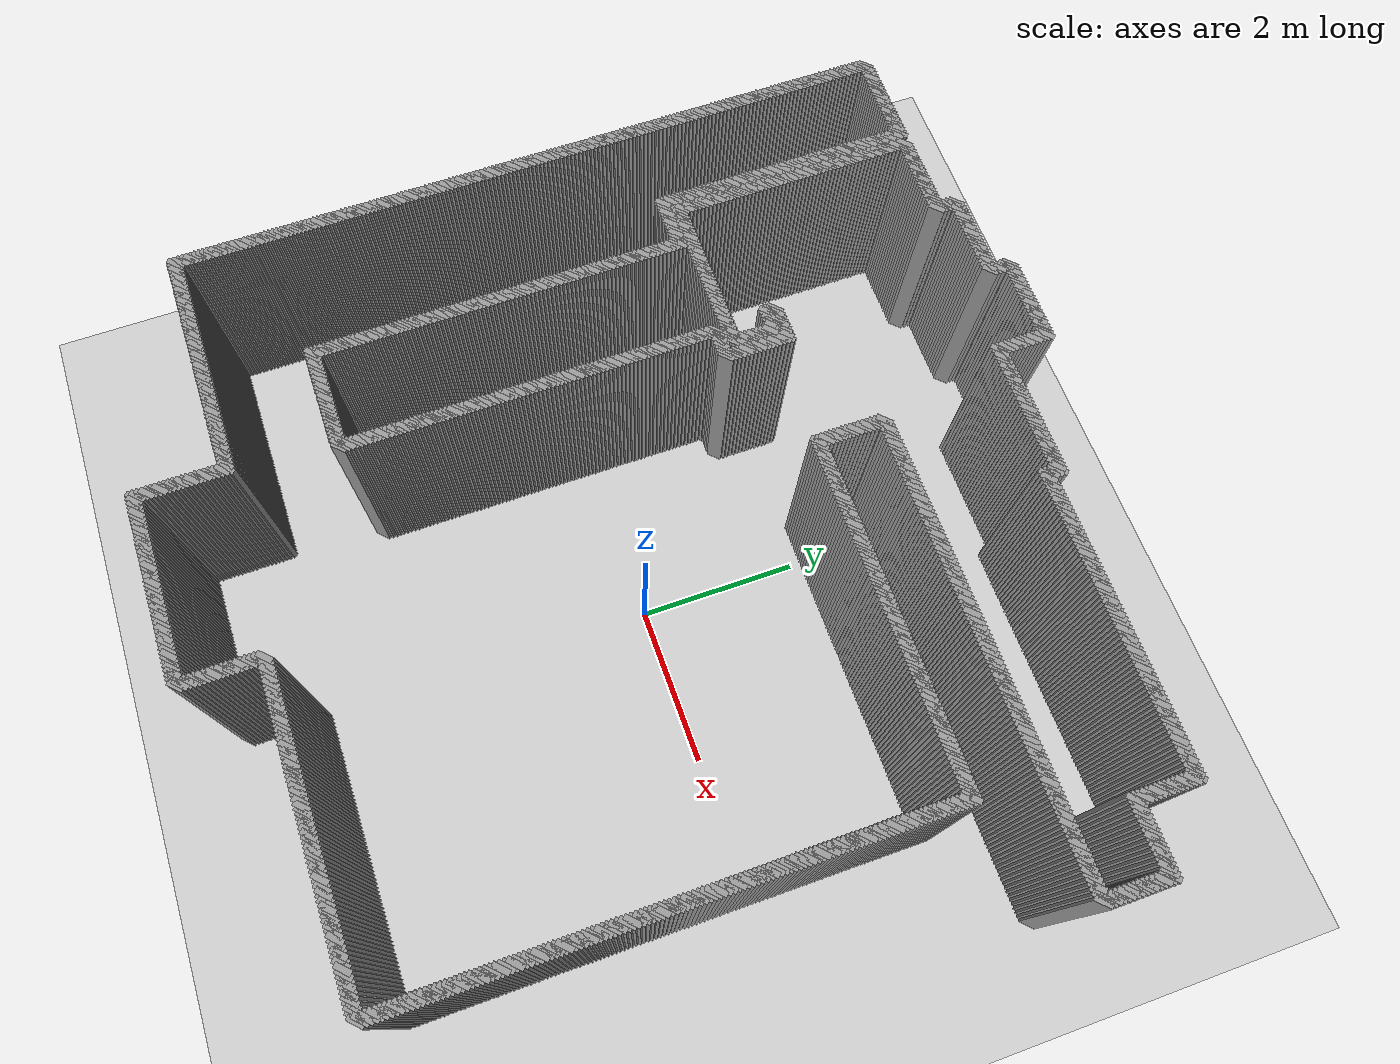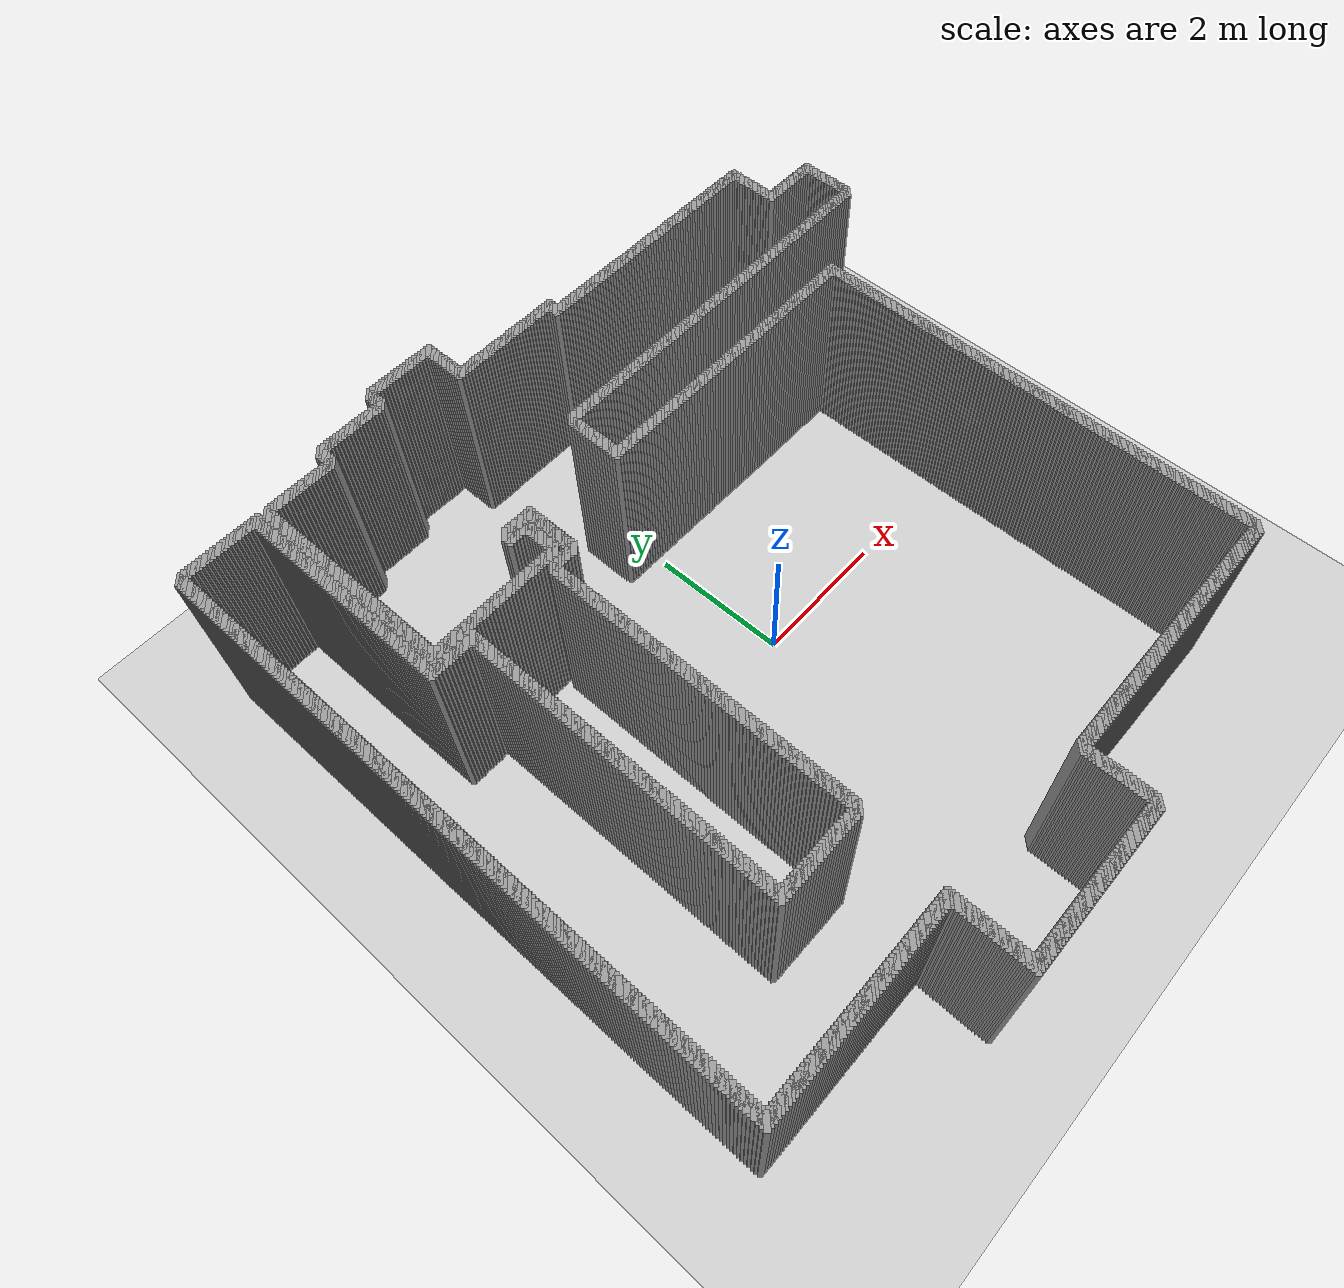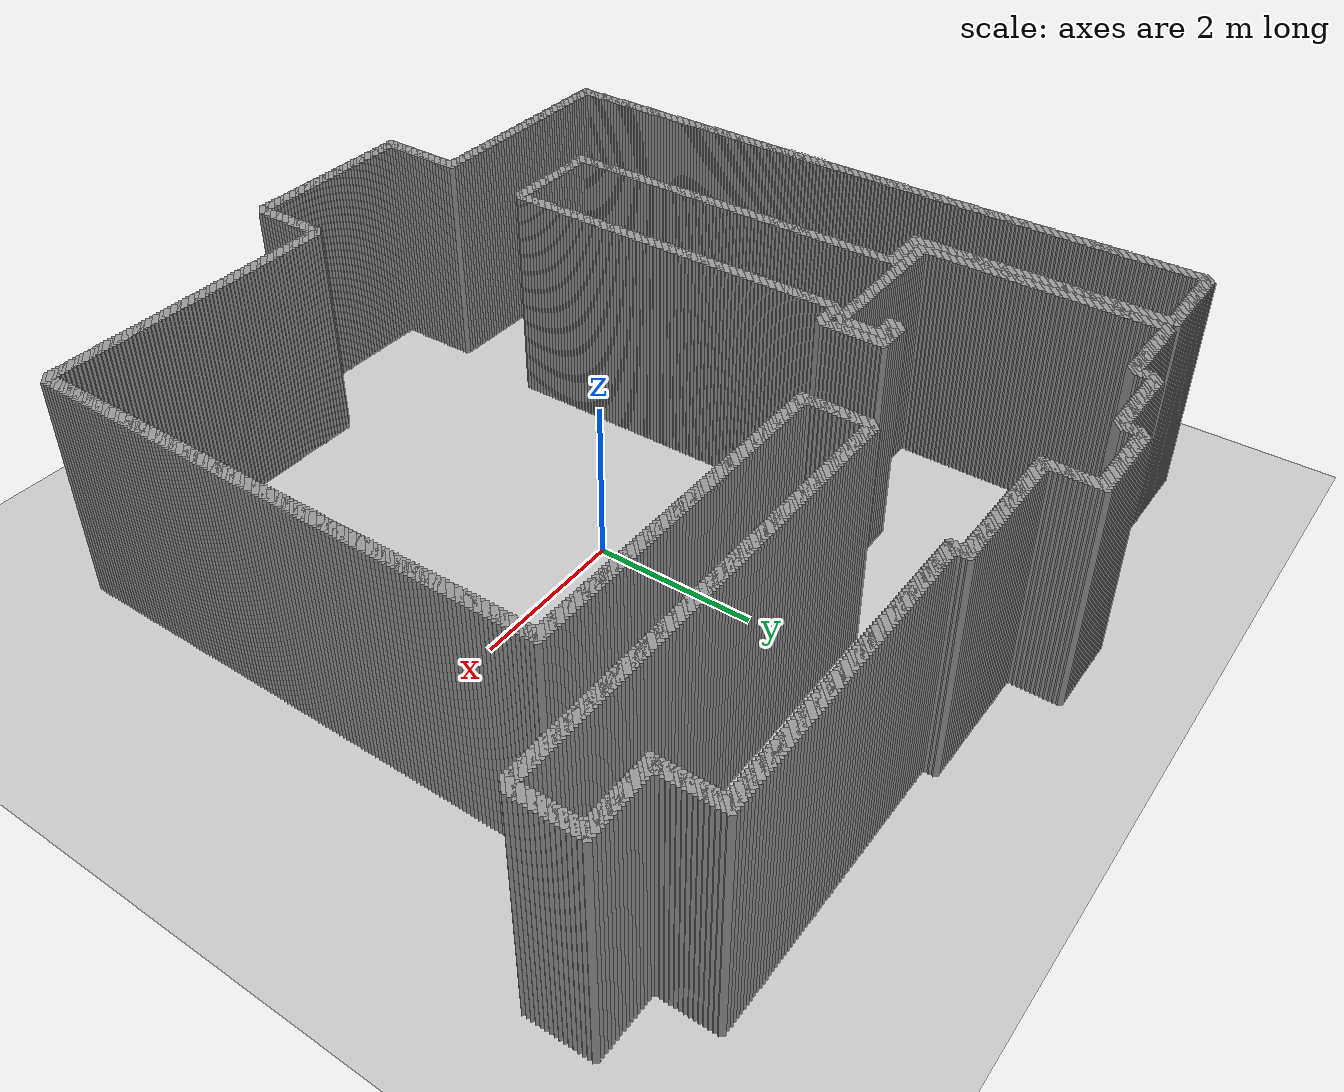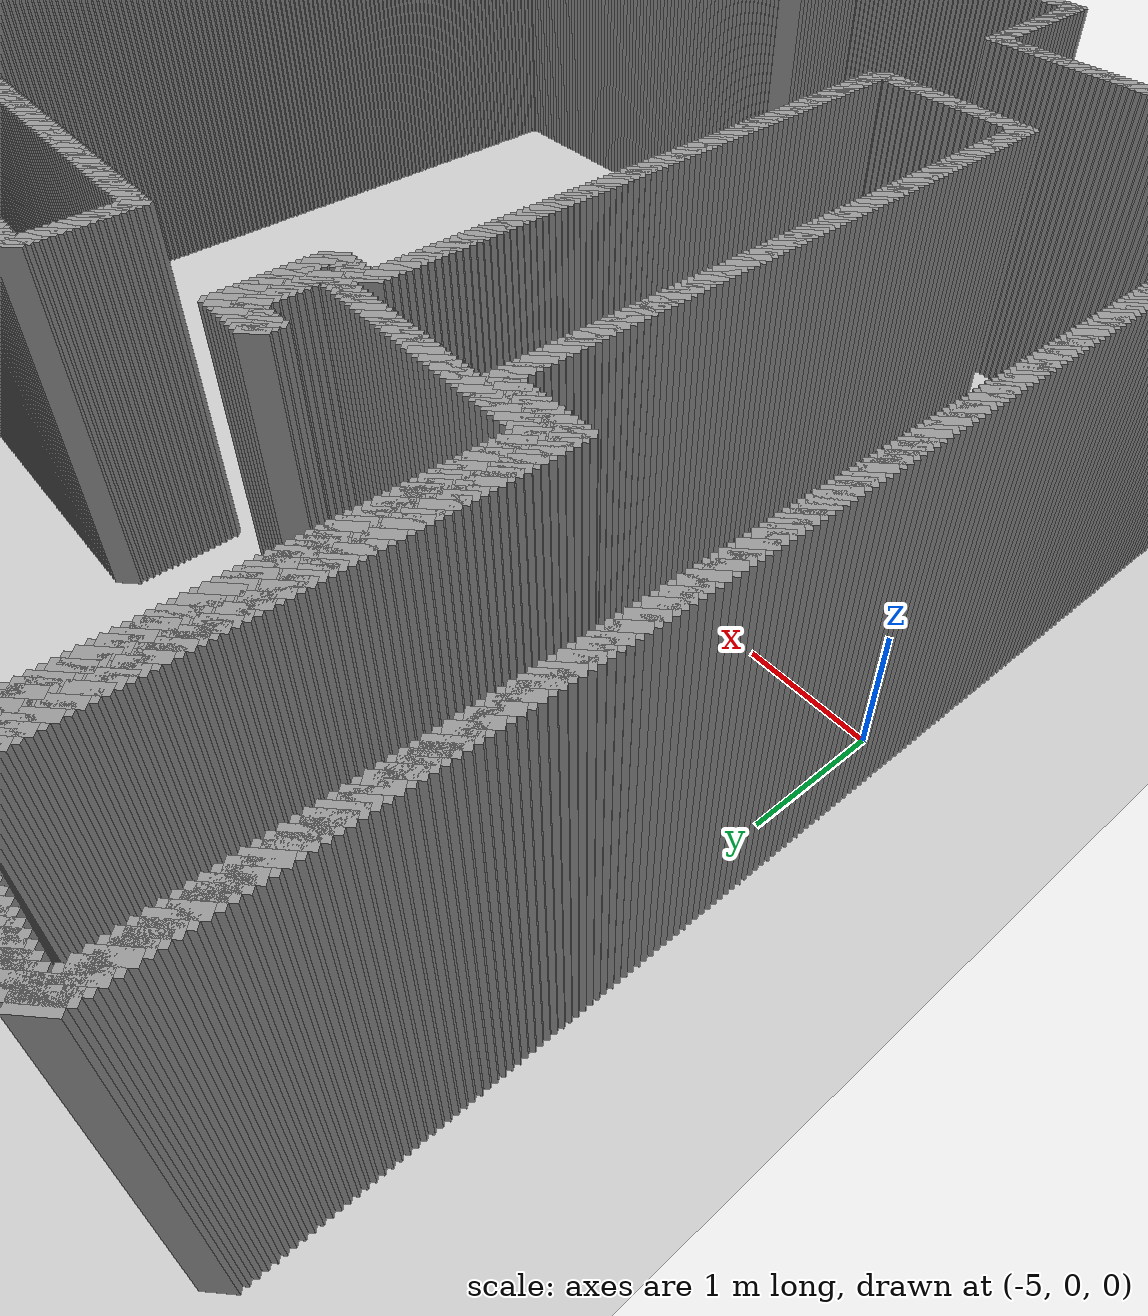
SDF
<?xml version="1.0" ?>

    <!-- this file is auto generated using pedsim_gazebo_plugin pkg -->
    <sdf version="1.5">
      <world name="default">

      <!-- Ground Plane -->

      <include>
        <uri>model://ground_plane</uri>
      </include>

      <include>
        <uri>model://sun</uri>
      </include>

     <model name='grey_wall_1'>
      <static>1</static>
      <link name='link'>

	  <pose frame=''>-1.875 5.225  1.4 0 0 -0.785398163397</pose>

        <collision name='collision'>
          <geometry>
            <box>

	     <size> 0.0707106781187 .2  2.8 </size>

      	   </box>
          </geometry>
          <max_contacts>10</max_contacts>
          <surface>
            <contact>
              <ode/>
            </contact>
            <bounce/>
            <friction>
              <torsional>
                <ode/>
              </torsional>
              <ode/>
            </friction>
          </surface>
        </collision>
        <visual name='visual'>
          <cast_shadows>0</cast_shadows>
          <geometry>
            <box>

	     <size> 0.0707106781187 .2  2.8 </size>

      	   </box>
       </geometry>
          <material>
            <script>
              <uri>model://grey_wall/materials/scripts</uri>
              <uri>model://grey_wall/materials/textures</uri>
              <name>vrc/grey_wall</name>
            </script>
          </material>
        </visual>
        <self_collide>0</self_collide>
        <enable_wind>0</enable_wind>
        <kinematic>0</kinematic>
      </link>
    </model>

     <model name='grey_wall_2'>
      <static>1</static>
      <link name='link'>

	  <pose frame=''>-1.825 5.225  1.4 0 0 -0.785398163397</pose>

        <collision name='collision'>
          <geometry>
            <box>

	     <size> 0.0707106781187 .2  2.8 </size>

      	   </box>
          </geometry>
          <max_contacts>10</max_contacts>
          <surface>
            <contact>
              <ode/>
            </contact>
            <bounce/>
            <friction>
              <torsional>
                <ode/>
              </torsional>
              <ode/>
            </friction>
          </surface>
        </collision>
        <visual name='visual'>
          <cast_shadows>0</cast_shadows>
          <geometry>
            <box>

	     <size> 0.0707106781187 .2  2.8 </size>

      	   </box>
       </geometry>
          <material>
            <script>
              <uri>model://grey_wall/materials/scripts</uri>
              <uri>model://grey_wall/materials/textures</uri>
              <name>vrc/grey_wall</name>
            </script>
          </material>
        </visual>
        <self_collide>0</self_collide>
        <enable_wind>0</enable_wind>
        <kinematic>0</kinematic>
      </link>
    </model>

     <model name='grey_wall_3'>
      <static>1</static>
      <link name='link'>

	  <pose frame=''>-1.775 5.225  1.4 0 0 -0.785398163397</pose>

        <collision name='collision'>
          <geometry>
            <box>

	     <size> 0.0707106781187 .2  2.8 </size>

      	   </box>
          </geometry>
          <max_contacts>10</max_contacts>
          <surface>
            <contact>
              <ode/>
            </contact>
            <bounce/>
            <friction>
              <torsional>
                <ode/>
              </torsional>
              <ode/>
            </friction>
          </surface>
        </collision>
        <visual name='visual'>
          <cast_shadows>0</cast_shadows>
          <geometry>
            <box>

	     <size> 0.0707106781187 .2  2.8 </size>

      	   </box>
       </geometry>
          <material>
            <script>
              <uri>model://grey_wall/materials/scripts</uri>
              <uri>model://grey_wall/materials/textures</uri>
              <name>vrc/grey_wall</name>
            </script>
          </material>
        </visual>
        <self_collide>0</self_collide>
        <enable_wind>0</enable_wind>
        <kinematic>0</kinematic>
      </link>
    </model>

     <model name='grey_wall_4'>
      <static>1</static>
      <link name='link'>

	  <pose frame=''>-1.725 5.225  1.4 0 0 -0.785398163397</pose>

        <collision name='collision'>
          <geometry>
            <box>

	     <size> 0.0707106781187 .2  2.8 </size>

      	   </box>
          </geometry>
          <max_contacts>10</max_contacts>
          <surface>
            <contact>
              <ode/>
            </contact>
            <bounce/>
            <friction>
              <torsional>
                <ode/>
              </torsional>
              <ode/>
            </friction>
          </surface>
        </collision>
        <visual name='visual'>
          <cast_shadows>0</cast_shadows>
          <geometry>
            <box>

	     <size> 0.0707106781187 .2  2.8 </size>

      	   </box>
       </geometry>
          <material>
            <script>
              <uri>model://grey_wall/materials/scripts</uri>
              <uri>model://grey_wall/materials/textures</uri>
              <name>vrc/grey_wall</name>
            </script>
          </material>
        </visual>
        <self_collide>0</self_collide>
        <enable_wind>0</enable_wind>
        <kinematic>0</kinematic>
      </link>
    </model>

     <model name='grey_wall_5'>
      <static>1</static>
      <link name='link'>

	  <pose frame=''>-1.675 5.225  1.4 0 0 -0.785398163397</pose>

        <collision name='collision'>
          <geometry>
            <box>

	     <size> 0.0707106781187 .2  2.8 </size>

      	   </box>
          </geometry>
          <max_contacts>10</max_contacts>
          <surface>
            <contact>
              <ode/>
            </contact>
            <bounce/>
            <friction>
              <torsional>
                <ode/>
              </torsional>
              <ode/>
            </friction>
          </surface>
        </collision>
        <visual name='visual'>
          <cast_shadows>0</cast_shadows>
          <geometry>
            <box>

	     <size> 0.0707106781187 .2  2.8 </size>

      	   </box>
       </geometry>
          <material>
            <script>
              <uri>model://grey_wall/materials/scripts</uri>
              <uri>model://grey_wall/materials/textures</uri>
              <name>vrc/grey_wall</name>
            </script>
          </material>
        </visual>
        <self_collide>0</self_collide>
        <enable_wind>0</enable_wind>
        <kinematic>0</kinematic>
      </link>
    </model>

     <model name='grey_wall_6'>
      <static>1</static>
      <link name='link'>

	  <pose frame=''>-1.625 5.225  1.4 0 0 -0.785398163397</pose>

        <collision name='collision'>
          <geometry>
            <box>

	     <size> 0.0707106781187 .2  2.8 </size>

      	   </box>
          </geometry>
          <max_contacts>10</max_contacts>
          <surface>
            <contact>
              <ode/>
            </contact>
            <bounce/>
            <friction>
              <torsional>
                <ode/>
              </torsional>
              <ode/>
            </friction>
          </surface>
        </collision>
        <visual name='visual'>
          <cast_shadows>0</cast_shadows>
          <geometry>
            <box>

	     <size> 0.0707106781187 .2  2.8 </size>

      	   </box>
       </geometry>
          <material>
            <script>
              <uri>model://grey_wall/materials/scripts</uri>
              <uri>model://grey_wall/materials/textures</uri>
              <name>vrc/grey_wall</name>
            </script>
          </material>
        </visual>
        <self_collide>0</self_collide>
        <enable_wind>0</enable_wind>
        <kinematic>0</kinematic>
      </link>
    </model>

     <model name='grey_wall_7'>
      <static>1</static>
      <link name='link'>

	  <pose frame=''>-1.575 5.225  1.4 0 0 -0.785398163397</pose>

        <collision name='collision'>
          <geometry>
            <box>

	     <size> 0.0707106781187 .2  2.8 </size>

      	   </box>
          </geometry>
          <max_contacts>10</max_contacts>
          <surface>
            <contact>
              <ode/>
            </contact>
            <bounce/>
            <friction>
              <torsional>
                <ode/>
              </torsional>
              <ode/>
            </friction>
          </surface>
        </collision>
        <visual name='visual'>
          <cast_shadows>0</cast_shadows>
          <geometry>
            <box>

	     <size> 0.0707106781187 .2  2.8 </size>

      	   </box>
       </geometry>
          <material>
            <script>
              <uri>model://grey_wall/materials/scripts</uri>
              <uri>model://grey_wall/materials/textures</uri>
              <name>vrc/grey_wall</name>
            </script>
          </material>
        </visual>
        <self_collide>0</self_collide>
        <enable_wind>0</enable_wind>
        <kinematic>0</kinematic>
      </link>
    </model>

     <model name='grey_wall_8'>
      <static>1</static>
      <link name='link'>

	  <pose frame=''>-1.525 5.225  1.4 0 0 -0.785398163397</pose>

        <collision name='collision'>
          <geometry>
            <box>

	     <size> 0.0707106781187 .2  2.8 </size>

      	   </box>
          </geometry>
          <max_contacts>10</max_contacts>
          <surface>
            <contact>
              <ode/>
            </contact>
            <bounce/>
            <friction>
              <torsional>
                <ode/>
              </torsional>
              <ode/>
            </friction>
          </surface>
        </collision>
        <visual name='visual'>
          <cast_shadows>0</cast_shadows>
          <geometry>
            <box>

	     <size> 0.0707106781187 .2  2.8 </size>

      	   </box>
       </geometry>
          <material>
            <script>
              <uri>model://grey_wall/materials/scripts</uri>
              <uri>model://grey_wall/materials/textures</uri>
              <name>vrc/grey_wall</name>
            </script>
          </material>
        </visual>
        <self_collide>0</self_collide>
        <enable_wind>0</enable_wind>
        <kinematic>0</kinematic>
      </link>
    </model>

     <model name='grey_wall_9'>
      <static>1</static>
      <link name='link'>

	  <pose frame=''>-1.475 5.225  1.4 0 0 -0.785398163397</pose>

        <collision name='collision'>
          <geometry>
            <box>

	     <size> 0.0707106781187 .2  2.8 </size>

      	   </box>
          </geometry>
          <max_contacts>10</max_contacts>
          <surface>
            <contact>
              <ode/>
            </contact>
            <bounce/>
            <friction>
              <torsional>
                <ode/>
              </torsional>
              <ode/>
            </friction>
          </surface>
        </collision>
        <visual name='visual'>
          <cast_shadows>0</cast_shadows>
          <geometry>
            <box>

	     <size> 0.0707106781187 .2  2.8 </size>

      	   </box>
       </geometry>
          <material>
            <script>
              <uri>model://grey_wall/materials/scripts</uri>
              <uri>model://grey_wall/materials/textures</uri>
              <name>vrc/grey_wall</name>
            </script>
          </material>
        </visual>
        <self_collide>0</self_collide>
        <enable_wind>0</enable_wind>
        <kinematic>0</kinematic>
      </link>
    </model>

     <model name='grey_wall_10'>
      <static>1</static>
      <link name='link'>

	  <pose frame=''>-1.425 5.225  1.4 0 0 -0.785398163397</pose>

        <collision name='collision'>
          <geometry>
            <box>

	     <size> 0.0707106781187 .2  2.8 </size>

      	   </box>
          </geometry>
          <max_contacts>10</max_contacts>
          <surface>
            <contact>
              <ode/>
            </contact>
            <bounce/>
            <friction>
              <torsional>
                <ode/>
              </torsional>
              <ode/>
            </friction>
          </surface>
        </collision>
        <visual name='visual'>
          <cast_shadows>0</cast_shadows>
          <geometry>
            <box>

	     <size> 0.0707106781187 .2  2.8 </size>

      	   </box>
       </geometry>
          <material>
            <script>
              <uri>model://grey_wall/materials/scripts</uri>
              <uri>model://grey_wall/materials/textures</uri>
              <name>vrc/grey_wall</name>
            </script>
          </material>
        </visual>
        <self_collide>0</self_collide>
        <enable_wind>0</enable_wind>
        <kinematic>0</kinematic>
      </link>
    </model>

     <model name='grey_wall_11'>
      <static>1</static>
      <link name='link'>

	  <pose frame=''>-1.375 5.225  1.4 0 0 -0.785398163397</pose>

        <collision name='collision'>
          <geometry>
            <box>

	     <size> 0.0707106781187 .2  2.8 </size>

      	   </box>
          </geometry>
          <max_contacts>10</max_contacts>
          <surface>
            <contact>
              <ode/>
            </contact>
            <bounce/>
            <friction>
              <torsional>
                <ode/>
              </torsional>
              <ode/>
            </friction>
          </surface>
        </collision>
        <visual name='visual'>
          <cast_shadows>0</cast_shadows>
          <geometry>
            <box>

	     <size> 0.0707106781187 .2  2.8 </size>

      	   </box>
       </geometry>
          <material>
            <script>
              <uri>model://grey_wall/materials/scripts</uri>
              <uri>model://grey_wall/materials/textures</uri>
              <name>vrc/grey_wall</name>
            </script>
          </material>
        </visual>
        <self_collide>0</self_collide>
        <enable_wind>0</enable_wind>
        <kinematic>0</kinematic>
      </link>
    </model>

     <model name='grey_wall_12'>
      <static>1</static>
      <link name='link'>

	  <pose frame=''>-1.325 5.225  1.4 0 0 -0.785398163397</pose>

        <collision name='collision'>
          <geometry>
            <box>

	     <size> 0.0707106781187 .2  2.8 </size>

      	   </box>
          </geometry>
          <max_contacts>10</max_contacts>
          <surface>
            <contact>
              <ode/>
            </contact>
            <bounce/>
            <friction>
              <torsional>
                <ode/>
              </torsional>
              <ode/>
            </friction>
          </surface>
        </collision>
        <visual name='visual'>
          <cast_shadows>0</cast_shadows>
          <geometry>
            <box>

	     <size> 0.0707106781187 .2  2.8 </size>

      	   </box>
       </geometry>
          <material>
            <script>
              <uri>model://grey_wall/materials/scripts</uri>
              <uri>model://grey_wall/materials/textures</uri>
              <name>vrc/grey_wall</name>
            </script>
          </material>
        </visual>
        <self_collide>0</self_collide>
        <enable_wind>0</enable_wind>
        <kinematic>0</kinematic>
      </link>
    </model>

     <model name='grey_wall_13'>
      <static>1</static>
      <link name='link'>

	  <pose frame=''>-1.275 5.225  1.4 0 0 -0.785398163397</pose>

        <collision name='collision'>
          <geometry>
            <box>

	     <size> 0.0707106781187 .2  2.8 </size>

      	   </box>
          </geometry>
          <max_contacts>10</max_contacts>
          <surface>
            <contact>
              <ode/>
            </contact>
            <bounce/>
            <friction>
              <torsional>
                <ode/>
              </torsional>
              <ode/>
            </friction>
          </surface>
        </collision>
        <visual name='visual'>
          <cast_shadows>0</cast_shadows>
          <geometry>
            <box>

	     <size> 0.0707106781187 .2  2.8 </size>

      	   </box>
       </geometry>
          <material>
            <script>
              <uri>model://grey_wall/materials/scripts</uri>
              <uri>model://grey_wall/materials/textures</uri>
              <name>vrc/grey_wall</name>
            </script>
          </material>
        </visual>
        <self_collide>0</self_collide>
        <enable_wind>0</enable_wind>
        <kinematic>0</kinematic>
      </link>
    </model>

     <model name='grey_wall_14'>
      <static>1</static>
      <link name='link'>

	  <pose frame=''>-1.225 5.225  1.4 0 0 -0.785398163397</pose>

        <collision name='collision'>
          <geometry>
            <box>

	     <size> 0.0707106781187 .2  2.8 </size>

      	   </box>
          </geometry>
          <max_contacts>10</max_contacts>
          <surface>
            <contact>
              <ode/>
            </contact>
            <bounce/>
            <friction>
              <torsional>
                <ode/>
              </torsional>
              <ode/>
            </friction>
          </surface>
        </collision>
        <visual name='visual'>
          <cast_shadows>0</cast_shadows>
          <geometry>
            <box>

	     <size> 0.0707106781187 .2  2.8 </size>

      	   </box>
       </geometry>
          <material>
            <script>
              <uri>model://grey_wall/materials/scripts</uri>
              <uri>model://grey_wall/materials/textures</uri>
              <name>vrc/grey_wall</name>
            </script>
          </material>
        </visual>
        <self_collide>0</self_collide>
        <enable_wind>0</enable_wind>
        <kinematic>0</kinematic>
      </link>
    </model>

     <model name='grey_wall_15'>
      <static>1</static>
      <link name='link'>

	  <pose frame=''>-1.175 5.225  1.4 0 0 -0.785398163397</pose>

        <collision name='collision'>
          <geometry>
            <box>

	     <size> 0.0707106781187 .2  2.8 </size>

      	   </box>
          </geometry>
          <max_contacts>10</max_contacts>
          <surface>
            <contact>
              <ode/>
            </contact>
            <bounce/>
            <friction>
              <torsional>
                <ode/>
              </torsional>
              <ode/>
            </friction>
          </surface>
        </collision>
        <visual name='visual'>
          <cast_shadows>0</cast_shadows>
          <geometry>
            <box>

	     <size> 0.0707106781187 .2  2.8 </size>

      	   </box>
       </geometry>
          <material>
            <script>
              <uri>model://grey_wall/materials/scripts</uri>
              <uri>model://grey_wall/materials/textures</uri>
              <name>vrc/grey_wall</name>
            </script>
          </material>
        </visual>
        <self_collide>0</self_collide>
        <enable_wind>0</enable_wind>
        <kinematic>0</kinematic>
      </link>
    </model>

     <model name='grey_wall_16'>
      <static>1</static>
      <link name='link'>

	  <pose frame=''>-1.125 5.225  1.4 0 0 -0.785398163397</pose>

        <collision name='collision'>
          <geometry>
            <box>

	     <size> 0.0707106781187 .2  2.8 </size>

      	   </box>
          </geometry>
          <max_contacts>10</max_contacts>
          <surface>
            <contact>
              <ode/>
            </contact>
            <bounce/>
            <friction>
              <torsional>
                <ode/>
              </torsional>
              <ode/>
            </friction>
          </surface>
        </collision>
        <visual name='visual'>
          <cast_shadows>0</cast_shadows>
          <geometry>
            <box>

	     <size> 0.0707106781187 .2  2.8 </size>

      	   </box>
       </geometry>
          <material>
            <script>
              <uri>model://grey_wall/materials/scripts</uri>
              <uri>model://grey_wall/materials/textures</uri>
              <name>vrc/grey_wall</name>
            </script>
          </material>
        </visual>
        <self_collide>0</self_collide>
        <enable_wind>0</enable_wind>
        <kinematic>0</kinematic>
      </link>
    </model>

     <model name='grey_wall_17'>
      <static>1</static>
      <link name='link'>

	  <pose frame=''>-1.075 5.225  1.4 0 0 -0.785398163397</pose>

        <collision name='collision'>
          <geometry>
            <box>

	     <size> 0.0707106781187 .2  2.8 </size>

      	   </box>
          </geometry>
          <max_contacts>10</max_contacts>
          <surface>
            <contact>
              <ode/>
            </contact>
            <bounce/>
            <friction>
              <torsional>
                <ode/>
              </torsional>
              <ode/>
            </friction>
          </surface>
        </collision>
        <visual name='visual'>
          <cast_shadows>0</cast_shadows>
          <geometry>
            <box>

	     <size> 0.0707106781187 .2  2.8 </size>

      	   </box>
       </geometry>
          <material>
            <script>
              <uri>model://grey_wall/materials/scripts</uri>
              <uri>model://grey_wall/materials/textures</uri>
              <name>vrc/grey_wall</name>
            </script>
          </material>
        </visual>
        <self_collide>0</self_collide>
        <enable_wind>0</enable_wind>
        <kinematic>0</kinematic>
      </link>
    </model>

     <model name='grey_wall_18'>
      <static>1</static>
      <link name='link'>

	  <pose frame=''>-1.025 5.225  1.4 0 0 -0.785398163397</pose>

        <collision name='collision'>
          <geometry>
            <box>

	     <size> 0.0707106781187 .2  2.8 </size>

      	   </box>
          </geometry>
          <max_contacts>10</max_contacts>
          <surface>
            <contact>
              <ode/>
            </contact>
            <bounce/>
            <friction>
              <torsional>
                <ode/>
              </torsional>
              <ode/>
            </friction>
          </surface>
        </collision>
        <visual name='visual'>
          <cast_shadows>0</cast_shadows>
          <geometry>
            <box>

	     <size> 0.0707106781187 .2  2.8 </size>

      	   </box>
       </geometry>
          <material>
            <script>
              <uri>model://grey_wall/materials/scripts</uri>
              <uri>model://grey_wall/materials/textures</uri>
              <name>vrc/grey_wall</name>
            </script>
          </material>
        </visual>
        <self_collide>0</self_collide>
        <enable_wind>0</enable_wind>
        <kinematic>0</kinematic>
      </link>
    </model>

     <model name='grey_wall_19'>
      <static>1</static>
      <link name='link'>

	  <pose frame=''>-0.975 5.225  1.4 0 0 -0.785398163397</pose>

        <collision name='collision'>
          <geometry>
            <box>

	     <size> 0.0707106781187 .2  2.8 </size>

      	   </box>
          </geometry>
          <max_contacts>10</max_contacts>
          <surface>
            <contact>
              <ode/>
            </contact>
            <bounce/>
            <friction>
              <torsional>
                <ode/>
              </torsional>
              <ode/>
            </friction>
          </surface>
        </collision>
        <visual name='visual'>
          <cast_shadows>0</cast_shadows>
          <geometry>
            <box>

	     <size> 0.0707106781187 .2  2.8 </size>

      	   </box>
       </geometry>
          <material>
            <script>
              <uri>model://grey_wall/materials/scripts</uri>
              <uri>model://grey_wall/materials/textures</uri>
              <name>vrc/grey_wall</name>
            </script>
          </material>
        </visual>
        <self_collide>0</self_collide>
        <enable_wind>0</enable_wind>
        <kinematic>0</kinematic>
      </link>
    </model>

     <model name='grey_wall_20'>
      <static>1</static>
      <link name='link'>

	  <pose frame=''>-0.925 5.225  1.4 0 0 -0.785398163397</pose>

        <collision name='collision'>
          <geometry>
            <box>

	     <size> 0.0707106781187 .2  2.8 </size>

      	   </box>
          </geometry>
          <max_contacts>10</max_contacts>
          <surface>
            <contact>
              <ode/>
            </contact>
            <bounce/>
            <friction>
              <torsional>
                <ode/>
              </torsional>
              <ode/>
            </friction>
          </surface>
        </collision>
        <visual name='visual'>
          <cast_shadows>0</cast_shadows>
          <geometry>
            <box>

	     <size> 0.0707106781187 .2  2.8 </size>

      	   </box>
       </geometry>
          <material>
            <script>
              <uri>model://grey_wall/materials/scripts</uri>
              <uri>model://grey_wall/materials/textures</uri>
              <name>vrc/grey_wall</name>
            </script>
          </material>
        </visual>
        <self_collide>0</self_collide>
        <enable_wind>0</enable_wind>
        <kinematic>0</kinematic>
      </link>
    </model>

     <model name='grey_wall_21'>
      <static>1</static>
      <link name='link'>

	  <pose frame=''>-0.875 5.225  1.4 0 0 -0.785398163397</pose>

        <collision name='collision'>
          <geometry>
            <box>

	     <size> 0.0707106781187 .2  2.8 </size>

      	   </box>
          </geometry>
          <max_contacts>10</max_contacts>
          <surface>
            <contact>
              <ode/>
            </contact>
            <bounce/>
            <friction>
              <torsional>
                <ode/>
              </torsional>
              <ode/>
            </friction>
          </surface>
        </collision>
        <visual name='visual'>
          <cast_shadows>0</cast_shadows>
          <geometry>
            <box>

	     <size> 0.0707106781187 .2  2.8 </size>

      	   </box>
       </geometry>
          <material>
            <script>
              <uri>model://grey_wall/materials/scripts</uri>
              <uri>model://grey_wall/materials/textures</uri>
              <name>vrc/grey_wall</name>
            </script>
          </material>
        </visual>
        <self_collide>0</self_collide>
        <enable_wind>0</enable_wind>
        <kinematic>0</kinematic>
      </link>
    </model>

     <model name='grey_wall_22'>
      <static>1</static>
      <link name='link'>

	  <pose frame=''>-1.875 5.175  1.4 0 0 -0.785398163397</pose>

        <collision name='collision'>
          <geometry>
            <box>

	     <size> 0.0707106781187 .2  2.8 </size>

      	   </box>
          </geometry>
          <max_contacts>10</max_contacts>
          <surface>
            <contact>
              <ode/>
            </contact>
            <bounce/>
            <friction>
              <torsional>
                <ode/>
              </torsional>
              <ode/>
            </friction>
          </surface>
        </collision>
        <visual name='visual'>
          <cast_shadows>0</cast_shadows>
          <geometry>
            <box>

	     <size> 0.0707106781187 .2  2.8 </size>

      	   </box>
       </geometry>
          <material>
            <script>
              <uri>model://grey_wall/materials/scripts</uri>
              <uri>model://grey_wall/materials/textures</uri>
              <name>vrc/grey_wall</name>
            </script>
          </material>
        </visual>
        <self_collide>0</self_collide>
        <enable_wind>0</enable_wind>
        <kinematic>0</kinematic>
      </link>
    </model>

     <model name='grey_wall_23'>
      <static>1</static>
      <link name='link'>

	  <pose frame=''>-0.875 5.175  1.4 0 0 -0.785398163397</pose>

        <collision name='collision'>
          <geometry>
            <box>

	     <size> 0.0707106781187 .2  2.8 </size>

      	   </box>
          </geometry>
          <max_contacts>10</max_contacts>
          <surface>
            <contact>
              <ode/>
            </contact>
            <bounce/>
            <friction>
              <torsional>
                <ode/>
              </torsional>
              <ode/>
            </friction>
          </surface>
        </collision>
        <visual name='visual'>
          <cast_shadows>0</cast_shadows>
          <geometry>
            <box>

	     <size> 0.0707106781187 .2  2.8 </size>

      	   </box>
       </geometry>
          <material>
            <script>
              <uri>model://grey_wall/materials/scripts</uri>
              <uri>model://grey_wall/materials/textures</uri>
              <name>vrc/grey_wall</name>
            </script>
          </material>
        </visual>
        <self_collide>0</self_collide>
        <enable_wind>0</enable_wind>
        <kinematic>0</kinematic>
      </link>
    </model>

     <model name='grey_wall_24'>
      <static>1</static>
      <link name='link'>

	  <pose frame=''>-1.875 5.125  1.4 0 0 -0.785398163397</pose>

        <collision name='collision'>
          <geometry>
            <box>

	     <size> 0.0707106781187 .2  2.8 </size>

      	   </box>
          </geometry>
          <max_contacts>10</max_contacts>
          <surface>
            <contact>
              <ode/>
            </contact>
            <bounce/>
            <friction>
              <torsional>
                <ode/>
              </torsional>
              <ode/>
            </friction>
          </surface>
        </collision>
        <visual name='visual'>
          <cast_shadows>0</cast_shadows>
          <geometry>
            <box>

	     <size> 0.0707106781187 .2  2.8 </size>

      	   </box>
       </geometry>
          <material>
            <script>
              <uri>model://grey_wall/materials/scripts</uri>
              <uri>model://grey_wall/materials/textures</uri>
              <name>vrc/grey_wall</name>
            </script>
          </material>
        </visual>
        <self_collide>0</self_collide>
        <enable_wind>0</enable_wind>
        <kinematic>0</kinematic>
      </link>
    </model>

     <model name='grey_wall_25'>
      <static>1</static>
      <link name='link'>

	  <pose frame=''>-0.875 5.125  1.4 0 0 -0.785398163397</pose>

        <collision name='collision'>
          <geometry>
            <box>

	     <size> 0.0707106781187 .2  2.8 </size>

      	   </box>
          </geometry>
          <max_contacts>10</max_contacts>
          <surface>
            <contact>
              <ode/>
            </contact>
            <bounce/>
            <friction>
              <torsional>
                <ode/>
              </torsional>
              <ode/>
            </friction>
          </surface>
        </collision>
        <visual name='visual'>
          <cast_shadows>0</cast_shadows>
          <geometry>
            <box>

	     <size> 0.0707106781187 .2  2.8 </size>

      	   </box>
       </geometry>
          <material>
            <script>
              <uri>model://grey_wall/materials/scripts</uri>
              <uri>model://grey_wall/materials/textures</uri>
              <name>vrc/grey_wall</name>
            </script>
          </material>
        </visual>
        <self_collide>0</self_collide>
        <enable_wind>0</enable_wind>
        <kinematic>0</kinematic>
      </link>
    </model>

     <model name='grey_wall_26'>
      <static>1</static>
      <link name='link'>

	  <pose frame=''>-1.875 5.075  1.4 0 0 -0.785398163397</pose>

        <collision name='collision'>
          <geometry>
            <box>

	     <size> 0.0707106781187 .2  2.8 </size>

      	   </box>
          </geometry>
          <max_contacts>10</max_contacts>
          <surface>
            <contact>
              <ode/>
            </contact>
            <bounce/>
            <friction>
              <torsional>
                <ode/>
              </torsional>
              <ode/>
            </friction>
          </surface>
        </collision>
        <visual name='visual'>
          <cast_shadows>0</cast_shadows>
          <geometry>
            <box>

	     <size> 0.0707106781187 .2  2.8 </size>

      	   </box>
       </geometry>
          <material>
            <script>
              <uri>model://grey_wall/materials/scripts</uri>
              <uri>model://grey_wall/materials/textures</uri>
              <name>vrc/grey_wall</name>
            </script>
          </material>
        </visual>
        <self_collide>0</self_collide>
        <enable_wind>0</enable_wind>
        <kinematic>0</kinematic>
      </link>
    </model>

     <model name='grey_wall_27'>
      <static>1</static>
      <link name='link'>

	  <pose frame=''>-0.875 5.075  1.4 0 0 -0.785398163397</pose>

        <collision name='collision'>
          <geometry>
            <box>

	     <size> 0.0707106781187 .2  2.8 </size>

      	   </box>
          </geometry>
          <max_contacts>10</max_contacts>
          <surface>
            <contact>
              <ode/>
            </contact>
            <bounce/>
            <friction>
              <torsional>
                <ode/>
              </torsional>
              <ode/>
            </friction>
          </surface>
        </collision>
        <visual name='visual'>
          <cast_shadows>0</cast_shadows>
          <geometry>
            <box>

	     <size> 0.0707106781187 .2  2.8 </size>

      	   </box>
       </geometry>
          <material>
            <script>
              <uri>model://grey_wall/materials/scripts</uri>
              <uri>model://grey_wall/materials/textures</uri>
              <name>vrc/grey_wall</name>
            </script>
          </material>
        </visual>
        <self_collide>0</self_collide>
        <enable_wind>0</enable_wind>
        <kinematic>0</kinematic>
      </link>
    </model>

     <model name='grey_wall_28'>
      <static>1</static>
      <link name='link'>

	  <pose frame=''>-1.875 5.025  1.4 0 0 -0.785398163397</pose>

        <collision name='collision'>
          <geometry>
            <box>

	     <size> 0.0707106781187 .2  2.8 </size>

      	   </box>
          </geometry>
          <max_contacts>10</max_contacts>
          <surface>
            <contact>
              <ode/>
            </contact>
            <bounce/>
            <friction>
              <torsional>
                <ode/>
              </torsional>
              <ode/>
            </friction>
          </surface>
        </collision>
        <visual name='visual'>
          <cast_shadows>0</cast_shadows>
          <geometry>
            <box>

	     <size> 0.0707106781187 .2  2.8 </size>

      	   </box>
       </geometry>
          <material>
            <script>
              <uri>model://grey_wall/materials/scripts</uri>
              <uri>model://grey_wall/materials/textures</uri>
              <name>vrc/grey_wall</name>
            </script>
          </material>
        </visual>
        <self_collide>0</self_collide>
        <enable_wind>0</enable_wind>
        <kinematic>0</kinematic>
      </link>
    </model>

     <model name='grey_wall_29'>
      <static>1</static>
      <link name='link'>

	  <pose frame=''>-0.875 5.025  1.4 0 0 -0.785398163397</pose>

        <collision name='collision'>
          <geometry>
            <box>

	     <size> 0.0707106781187 .2  2.8 </size>

      	   </box>
          </geometry>
          <max_contacts>10</max_contacts>
          <surface>
            <contact>
              <ode/>
            </contact>
            <bounce/>
            <friction>
              <torsional>
                <ode/>
              </torsional>
              <ode/>
            </friction>
          </surface>
        </collision>
        <visual name='visual'>
          <cast_shadows>0</cast_shadows>
          <geometry>
            <box>

	     <size> 0.0707106781187 .2  2.8 </size>

      	   </box>
       </geometry>
          <material>
            <script>
              <uri>model://grey_wall/materials/scripts</uri>
              <uri>model://grey_wall/materials/textures</uri>
              <name>vrc/grey_wall</name>
            </script>
          </material>
        </visual>
        <self_collide>0</self_collide>
        <enable_wind>0</enable_wind>
        <kinematic>0</kinematic>
      </link>
    </model>

     <model name='grey_wall_30'>
      <static>1</static>
      <link name='link'>

	  <pose frame=''>-2.875 4.975  1.4 0 0 -0.785398163397</pose>

        <collision name='collision'>
          <geometry>
            <box>

	     <size> 0.0707106781187 .2  2.8 </size>

      	   </box>
          </geometry>
          <max_contacts>10</max_contacts>
          <surface>
            <contact>
              <ode/>
            </contact>
            <bounce/>
            <friction>
              <torsional>
                <ode/>
              </torsional>
              <ode/>
            </friction>
          </surface>
        </collision>
        <visual name='visual'>
          <cast_shadows>0</cast_shadows>
          <geometry>
            <box>

	     <size> 0.0707106781187 .2  2.8 </size>

      	   </box>
       </geometry>
          <material>
            <script>
              <uri>model://grey_wall/materials/scripts</uri>
              <uri>model://grey_wall/materials/textures</uri>
              <name>vrc/grey_wall</name>
            </script>
          </material>
        </visual>
        <self_collide>0</self_collide>
        <enable_wind>0</enable_wind>
        <kinematic>0</kinematic>
      </link>
    </model>

     <model name='grey_wall_31'>
      <static>1</static>
      <link name='link'>

	  <pose frame=''>-2.825 4.975  1.4 0 0 -0.785398163397</pose>

        <collision name='collision'>
          <geometry>
            <box>

	     <size> 0.0707106781187 .2  2.8 </size>

      	   </box>
          </geometry>
          <max_contacts>10</max_contacts>
          <surface>
            <contact>
              <ode/>
            </contact>
            <bounce/>
            <friction>
              <torsional>
                <ode/>
              </torsional>
              <ode/>
            </friction>
          </surface>
        </collision>
        <visual name='visual'>
          <cast_shadows>0</cast_shadows>
          <geometry>
            <box>

	     <size> 0.0707106781187 .2  2.8 </size>

      	   </box>
       </geometry>
          <material>
            <script>
              <uri>model://grey_wall/materials/scripts</uri>
              <uri>model://grey_wall/materials/textures</uri>
              <name>vrc/grey_wall</name>
            </script>
          </material>
        </visual>
        <self_collide>0</self_collide>
        <enable_wind>0</enable_wind>
        <kinematic>0</kinematic>
      </link>
    </model>

     <model name='grey_wall_32'>
      <static>1</static>
      <link name='link'>

	  <pose frame=''>-2.775 4.975  1.4 0 0 -0.785398163397</pose>

        <collision name='collision'>
          <geometry>
            <box>

	     <size> 0.0707106781187 .2  2.8 </size>

      	   </box>
          </geometry>
          <max_contacts>10</max_contacts>
          <surface>
            <contact>
              <ode/>
            </contact>
            <bounce/>
            <friction>
              <torsional>
                <ode/>
              </torsional>
              <ode/>
            </friction>
          </surface>
        </collision>
        <visual name='visual'>
          <cast_shadows>0</cast_shadows>
          <geometry>
            <box>

	     <size> 0.0707106781187 .2  2.8 </size>

      	   </box>
       </geometry>
          <material>
            <script>
              <uri>model://grey_wall/materials/scripts</uri>
              <uri>model://grey_wall/materials/textures</uri>
              <name>vrc/grey_wall</name>
            </script>
          </material>
        </visual>
        <self_collide>0</self_collide>
        <enable_wind>0</enable_wind>
        <kinematic>0</kinematic>
      </link>
    </model>

     <model name='grey_wall_33'>
      <static>1</static>
      <link name='link'>

	  <pose frame=''>-2.725 4.975  1.4 0 0 -0.785398163397</pose>

        <collision name='collision'>
          <geometry>
            <box>

	     <size> 0.0707106781187 .2  2.8 </size>

      	   </box>
          </geometry>
          <max_contacts>10</max_contacts>
          <surface>
            <contact>
              <ode/>
            </contact>
            <bounce/>
            <friction>
              <torsional>
                <ode/>
              </torsional>
              <ode/>
            </friction>
          </surface>
        </collision>
        <visual name='visual'>
          <cast_shadows>0</cast_shadows>
          <geometry>
            <box>

	     <size> 0.0707106781187 .2  2.8 </size>

      	   </box>
       </geometry>
          <material>
            <script>
              <uri>model://grey_wall/materials/scripts</uri>
              <uri>model://grey_wall/materials/textures</uri>
              <name>vrc/grey_wall</name>
            </script>
          </material>
        </visual>
        <self_collide>0</self_collide>
        <enable_wind>0</enable_wind>
        <kinematic>0</kinematic>
      </link>
    </model>

     <model name='grey_wall_34'>
      <static>1</static>
      <link name='link'>

	  <pose frame=''>-2.675 4.975  1.4 0 0 -0.785398163397</pose>

        <collision name='collision'>
          <geometry>
            <box>

	     <size> 0.0707106781187 .2  2.8 </size>

      	   </box>
          </geometry>
          <max_contacts>10</max_contacts>
          <surface>
            <contact>
              <ode/>
            </contact>
            <bounce/>
            <friction>
              <torsional>
                <ode/>
              </torsional>
              <ode/>
            </friction>
          </surface>
        </collision>
        <visual name='visual'>
          <cast_shadows>0</cast_shadows>
          <geometry>
            <box>

	     <size> 0.0707106781187 .2  2.8 </size>

      	   </box>
       </geometry>
          <material>
            <script>
              <uri>model://grey_wall/materials/scripts</uri>
              <uri>model://grey_wall/materials/textures</uri>
              <name>vrc/grey_wall</name>
            </script>
          </material>
        </visual>
        <self_collide>0</self_collide>
        <enable_wind>0</enable_wind>
        <kinematic>0</kinematic>
      </link>
    </model>

     <model name='grey_wall_35'>
      <static>1</static>
      <link name='link'>

	  <pose frame=''>-2.625 4.975  1.4 0 0 -0.785398163397</pose>

        <collision name='collision'>
          <geometry>
            <box>

	     <size> 0.0707106781187 .2  2.8 </size>

      	   </box>
          </geometry>
          <max_contacts>10</max_contacts>
          <surface>
            <contact>
              <ode/>
            </contact>
            <bounce/>
            <friction>
              <torsional>
                <ode/>
              </torsional>
              <ode/>
            </friction>
          </surface>
        </collision>
        <visual name='visual'>
          <cast_shadows>0</cast_shadows>
          <geometry>
            <box>

	     <size> 0.0707106781187 .2  2.8 </size>

      	   </box>
       </geometry>
          <material>
            <script>
              <uri>model://grey_wall/materials/scripts</uri>
              <uri>model://grey_wall/materials/textures</uri>
              <name>vrc/grey_wall</name>
            </script>
          </material>
        </visual>
        <self_collide>0</self_collide>
        <enable_wind>0</enable_wind>
        <kinematic>0</kinematic>
      </link>
    </model>

     <model name='grey_wall_36'>
      <static>1</static>
      <link name='link'>

	  <pose frame=''>-2.575 4.975  1.4 0 0 -0.785398163397</pose>

        <collision name='collision'>
          <geometry>
            <box>

	     <size> 0.0707106781187 .2  2.8 </size>

      	   </box>
          </geometry>
          <max_contacts>10</max_contacts>
          <surface>
            <contact>
              <ode/>
            </contact>
            <bounce/>
            <friction>
              <torsional>
                <ode/>
              </torsional>
              <ode/>
            </friction>
          </surface>
        </collision>
        <visual name='visual'>
          <cast_shadows>0</cast_shadows>
          <geometry>
            <box>

	     <size> 0.0707106781187 .2  2.8 </size>

      	   </box>
       </geometry>
          <material>
            <script>
              <uri>model://grey_wall/materials/scripts</uri>
              <uri>model://grey_wall/materials/textures</uri>
              <name>vrc/grey_wall</name>
            </script>
          </material>
        </visual>
        <self_collide>0</self_collide>
        <enable_wind>0</enable_wind>
        <kinematic>0</kinematic>
      </link>
    </model>

     <model name='grey_wall_37'>
      <static>1</static>
      <link name='link'>

	  <pose frame=''>-2.525 4.975  1.4 0 0 -0.785398163397</pose>

        <collision name='collision'>
          <geometry>
            <box>

	     <size> 0.0707106781187 .2  2.8 </size>

      	   </box>
          </geometry>
          <max_contacts>10</max_contacts>
          <surface>
            <contact>
              <ode/>
            </contact>
            <bounce/>
            <friction>
              <torsional>
                <ode/>
              </torsional>
              <ode/>
            </friction>
          </surface>
        </collision>
        <visual name='visual'>
          <cast_shadows>0</cast_shadows>
          <geometry>
            <box>

	     <size> 0.0707106781187 .2  2.8 </size>

      	   </box>
       </geometry>
          <material>
            <script>
              <uri>model://grey_wall/materials/scripts</uri>
              <uri>model://grey_wall/materials/textures</uri>
              <name>vrc/grey_wall</name>
            </script>
          </material>
        </visual>
        <self_collide>0</self_collide>
        <enable_wind>0</enable_wind>
        <kinematic>0</kinematic>
      </link>
    </model>

     <model name='grey_wall_38'>
      <static>1</static>
      <link name='link'>

	  <pose frame=''>-2.475 4.975  1.4 0 0 -0.785398163397</pose>

        <collision name='collision'>
          <geometry>
            <box>

	     <size> 0.0707106781187 .2  2.8 </size>

      	   </box>
          </geometry>
          <max_contacts>10</max_contacts>
          <surface>
            <contact>
              <ode/>
            </contact>
            <bounce/>
            <friction>
              <torsional>
                <ode/>
              </torsional>
              <ode/>
            </friction>
          </surface>
        </collision>
        <visual name='visual'>
          <cast_shadows>0</cast_shadows>
          <geometry>
            <box>

	     <size> 0.0707106781187 .2  2.8 </size>

      	   </box>
       </geometry>
          <material>
            <script>
              <uri>model://grey_wall/materials/scripts</uri>
              <uri>model://grey_wall/materials/textures</uri>
              <name>vrc/grey_wall</name>
            </script>
          </material>
        </visual>
        <self_collide>0</self_collide>
        <enable_wind>0</enable_wind>
        <kinematic>0</kinematic>
      </link>
    </model>

     <model name='grey_wall_39'>
      <static>1</static>
      <link name='link'>

	  <pose frame=''>-2.425 4.975  1.4 0 0 -0.785398163397</pose>

        <collision name='collision'>
          <geometry>
            <box>

	     <size> 0.0707106781187 .2  2.8 </size>

      	   </box>
          </geometry>
          <max_contacts>10</max_contacts>
          <surface>
            <contact>
              <ode/>
            </contact>
            <bounce/>
            <friction>
              <torsional>
                <ode/>
              </torsional>
              <ode/>
            </friction>
          </surface>
        </collision>
        <visual name='visual'>
          <cast_shadows>0</cast_shadows>
          <geometry>
            <box>

	     <size> 0.0707106781187 .2  2.8 </size>

      	   </box>
       </geometry>
          <material>
            <script>
              <uri>model://grey_wall/materials/scripts</uri>
              <uri>model://grey_wall/materials/textures</uri>
              <name>vrc/grey_wall</name>
            </script>
          </material>
        </visual>
        <self_collide>0</self_collide>
        <enable_wind>0</enable_wind>
        <kinematic>0</kinematic>
      </link>
    </model>

     <model name='grey_wall_40'>
      <static>1</static>
      <link name='link'>

	  <pose frame=''>-2.375 4.975  1.4 0 0 -0.785398163397</pose>

        <collision name='collision'>
          <geometry>
            <box>

	     <size> 0.0707106781187 .2  2.8 </size>

      	   </box>
          </geometry>
          <max_contacts>10</max_contacts>
          <surface>
            <contact>
              <ode/>
            </contact>
            <bounce/>
            <friction>
              <torsional>
                <ode/>
              </torsional>
              <ode/>
            </friction>
          </surface>
        </collision>
        <visual name='visual'>
          <cast_shadows>0</cast_shadows>
          <geometry>
            <box>

	     <size> 0.0707106781187 .2  2.8 </size>

      	   </box>
       </geometry>
          <material>
            <script>
              <uri>model://grey_wall/materials/scripts</uri>
              <uri>model://grey_wall/materials/textures</uri>
              <name>vrc/grey_wall</name>
            </script>
          </material>
        </visual>
        <self_collide>0</self_collide>
        <enable_wind>0</enable_wind>
        <kinematic>0</kinematic>
      </link>
    </model>

     <model name='grey_wall_41'>
      <static>1</static>
      <link name='link'>

	  <pose frame=''>-2.325 4.975  1.4 0 0 -0.785398163397</pose>

        <collision name='collision'>
          <geometry>
            <box>

	     <size> 0.0707106781187 .2  2.8 </size>

      	   </box>
          </geometry>
          <max_contacts>10</max_contacts>
          <surface>
            <contact>
              <ode/>
            </contact>
            <bounce/>
            <friction>
              <torsional>
                <ode/>
              </torsional>
              <ode/>
            </friction>
          </surface>
        </collision>
        <visual name='visual'>
          <cast_shadows>0</cast_shadows>
          <geometry>
            <box>

	     <size> 0.0707106781187 .2  2.8 </size>

      	   </box>
       </geometry>
          <material>
            <script>
              <uri>model://grey_wall/materials/scripts</uri>
              <uri>model://grey_wall/materials/textures</uri>
              <name>vrc/grey_wall</name>
            </script>
          </material>
        </visual>
        <self_collide>0</self_collide>
        <enable_wind>0</enable_wind>
        <kinematic>0</kinematic>
      </link>
    </model>

     <model name='grey_wall_42'>
      <static>1</static>
      <link name='link'>

	  <pose frame=''>-2.275 4.975  1.4 0 0 -0.785398163397</pose>

        <collision name='collision'>
          <geometry>
            <box>

	     <size> 0.0707106781187 .2  2.8 </size>

      	   </box>
          </geometry>
          <max_contacts>10</max_contacts>
          <surface>
            <contact>
              <ode/>
            </contact>
            <bounce/>
            <friction>
              <torsional>
                <ode/>
              </torsional>
              <ode/>
            </friction>
          </surface>
        </collision>
        <visual name='visual'>
          <cast_shadows>0</cast_shadows>
          <geometry>
            <box>

	     <size> 0.0707106781187 .2  2.8 </size>

      	   </box>
       </geometry>
          <material>
            <script>
              <uri>model://grey_wall/materials/scripts</uri>
              <uri>model://grey_wall/materials/textures</uri>
              <name>vrc/grey_wall</name>
            </script>
          </material>
        </visual>
        <self_collide>0</self_collide>
        <enable_wind>0</enable_wind>
        <kinematic>0</kinematic>
      </link>
    </model>

     <model name='grey_wall_43'>
      <static>1</static>
      <link name='link'>

	  <pose frame=''>-2.225 4.975  1.4 0 0 -0.785398163397</pose>

        <collision name='collision'>
          <geometry>
            <box>

	     <size> 0.0707106781187 .2  2.8 </size>

      	   </box>
          </geometry>
          <max_contacts>10</max_contacts>
          <surface>
            <contact>
              <ode/>
            </contact>
            <bounce/>
            <friction>
              <torsional>
                <ode/>
              </torsional>
              <ode/>
            </friction>
          </surface>
        </collision>
        <visual name='visual'>
          <cast_shadows>0</cast_shadows>
          <geometry>
            <box>

	     <size> 0.0707106781187 .2  2.8 </size>

      	   </box>
       </geometry>
          <material>
            <script>
              <uri>model://grey_wall/materials/scripts</uri>
              <uri>model://grey_wall/materials/textures</uri>
              <name>vrc/grey_wall</name>
            </script>
          </material>
        </visual>
        <self_collide>0</self_collide>
        <enable_wind>0</enable_wind>
        <kinematic>0</kinematic>
      </link>
    </model>

     <model name='grey_wall_44'>
      <static>1</static>
      <link name='link'>

	  <pose frame=''>-2.175 4.975  1.4 0 0 -0.785398163397</pose>

        <collision name='collision'>
          <geometry>
            <box>

	     <size> 0.0707106781187 .2  2.8 </size>

      	   </box>
          </geometry>
          <max_contacts>10</max_contacts>
          <surface>
            <contact>
              <ode/>
            </contact>
            <bounce/>
            <friction>
              <torsional>
                <ode/>
              </torsional>
              <ode/>
            </friction>
          </surface>
        </collision>
        <visual name='visual'>
          <cast_shadows>0</cast_shadows>
          <geometry>
            <box>

	     <size> 0.0707106781187 .2  2.8 </size>

      	   </box>
       </geometry>
          <material>
            <script>
              <uri>model://grey_wall/materials/scripts</uri>
              <uri>model://grey_wall/materials/textures</uri>
              <name>vrc/grey_wall</name>
            </script>
          </material>
        </visual>
        <self_collide>0</self_collide>
        <enable_wind>0</enable_wind>
        <kinematic>0</kinematic>
      </link>
    </model>

     <model name='grey_wall_45'>
      <static>1</static>
      <link name='link'>

	  <pose frame=''>-2.125 4.975  1.4 0 0 -0.785398163397</pose>

        <collision name='collision'>
          <geometry>
            <box>

	     <size> 0.0707106781187 .2  2.8 </size>

      	   </box>
          </geometry>
          <max_contacts>10</max_contacts>
          <surface>
            <contact>
              <ode/>
            </contact>
            <bounce/>
            <friction>
              <torsional>
                <ode/>
              </torsional>
              <ode/>
            </friction>
          </surface>
        </collision>
        <visual name='visual'>
          <cast_shadows>0</cast_shadows>
          <geometry>
            <box>

	     <size> 0.0707106781187 .2  2.8 </size>

      	   </box>
       </geometry>
          <material>
            <script>
              <uri>model://grey_wall/materials/scripts</uri>
              <uri>model://grey_wall/materials/textures</uri>
              <name>vrc/grey_wall</name>
            </script>
          </material>
        </visual>
        <self_collide>0</self_collide>
        <enable_wind>0</enable_wind>
        <kinematic>0</kinematic>
      </link>
    </model>

     <model name='grey_wall_46'>
      <static>1</static>
      <link name='link'>

	  <pose frame=''>-2.075 4.975  1.4 0 0 -0.785398163397</pose>

        <collision name='collision'>
          <geometry>
            <box>

	     <size> 0.0707106781187 .2  2.8 </size>

      	   </box>
          </geometry>
          <max_contacts>10</max_contacts>
          <surface>
            <contact>
              <ode/>
            </contact>
            <bounce/>
            <friction>
              <torsional>
                <ode/>
              </torsional>
              <ode/>
            </friction>
          </surface>
        </collision>
        <visual name='visual'>
          <cast_shadows>0</cast_shadows>
          <geometry>
            <box>

	     <size> 0.0707106781187 .2  2.8 </size>

      	   </box>
       </geometry>
          <material>
            <script>
              <uri>model://grey_wall/materials/scripts</uri>
              <uri>model://grey_wall/materials/textures</uri>
              <name>vrc/grey_wall</name>
            </script>
          </material>
        </visual>
        <self_collide>0</self_collide>
        <enable_wind>0</enable_wind>
        <kinematic>0</kinematic>
      </link>
    </model>

     <model name='grey_wall_47'>
      <static>1</static>
      <link name='link'>

	  <pose frame=''>-2.025 4.975  1.4 0 0 -0.785398163397</pose>

        <collision name='collision'>
          <geometry>
            <box>

	     <size> 0.0707106781187 .2  2.8 </size>

      	   </box>
          </geometry>
          <max_contacts>10</max_contacts>
          <surface>
            <contact>
              <ode/>
            </contact>
            <bounce/>
            <friction>
              <torsional>
                <ode/>
              </torsional>
              <ode/>
            </friction>
          </surface>
        </collision>
        <visual name='visual'>
          <cast_shadows>0</cast_shadows>
          <geometry>
            <box>

	     <size> 0.0707106781187 .2  2.8 </size>

      	   </box>
       </geometry>
          <material>
            <script>
              <uri>model://grey_wall/materials/scripts</uri>
              <uri>model://grey_wall/materials/textures</uri>
              <name>vrc/grey_wall</name>
            </script>
          </material>
        </visual>
        <self_collide>0</self_collide>
        <enable_wind>0</enable_wind>
        <kinematic>0</kinematic>
      </link>
    </model>

     <model name='grey_wall_48'>
      <static>1</static>
      <link name='link'>

	  <pose frame=''>-1.975 4.975  1.4 0 0 -0.785398163397</pose>

        <collision name='collision'>
          <geometry>
            <box>

	     <size> 0.0707106781187 .2  2.8 </size>

      	   </box>
          </geometry>
          <max_contacts>10</max_contacts>
          <surface>
            <contact>
              <ode/>
            </contact>
            <bounce/>
            <friction>
              <torsional>
                <ode/>
              </torsional>
              <ode/>
            </friction>
          </surface>
        </collision>
        <visual name='visual'>
          <cast_shadows>0</cast_shadows>
          <geometry>
            <box>

	     <size> 0.0707106781187 .2  2.8 </size>

      	   </box>
       </geometry>
          <material>
            <script>
              <uri>model://grey_wall/materials/scripts</uri>
              <uri>model://grey_wall/materials/textures</uri>
              <name>vrc/grey_wall</name>
            </script>
          </material>
        </visual>
        <self_collide>0</self_collide>
        <enable_wind>0</enable_wind>
        <kinematic>0</kinematic>
      </link>
    </model>

     <model name='grey_wall_49'>
      <static>1</static>
      <link name='link'>

	  <pose frame=''>-1.925 4.975  1.4 0 0 -0.785398163397</pose>

        <collision name='collision'>
          <geometry>
            <box>

	     <size> 0.0707106781187 .2  2.8 </size>

      	   </box>
          </geometry>
          <max_contacts>10</max_contacts>
          <surface>
            <contact>
              <ode/>
            </contact>
            <bounce/>
            <friction>
              <torsional>
                <ode/>
              </torsional>
              <ode/>
            </friction>
          </surface>
        </collision>
        <visual name='visual'>
          <cast_shadows>0</cast_shadows>
          <geometry>
            <box>

	     <size> 0.0707106781187 .2  2.8 </size>

      	   </box>
       </geometry>
          <material>
            <script>
              <uri>model://grey_wall/materials/scripts</uri>
              <uri>model://grey_wall/materials/textures</uri>
              <name>vrc/grey_wall</name>
            </script>
          </material>
        </visual>
        <self_collide>0</self_collide>
        <enable_wind>0</enable_wind>
        <kinematic>0</kinematic>
      </link>
    </model>

     <model name='grey_wall_50'>
      <static>1</static>
      <link name='link'>

	  <pose frame=''>-1.875 4.975  1.4 0 0 -0.785398163397</pose>

        <collision name='collision'>
          <geometry>
            <box>

	     <size> 0.0707106781187 .2  2.8 </size>

      	   </box>
          </geometry>
          <max_contacts>10</max_contacts>
          <surface>
            <contact>
              <ode/>
            </contact>
            <bounce/>
            <friction>
              <torsional>
                <ode/>
              </torsional>
              <ode/>
            </friction>
          </surface>
        </collision>
        <visual name='visual'>
          <cast_shadows>0</cast_shadows>
          <geometry>
            <box>

	     <size> 0.0707106781187 .2  2.8 </size>

      	   </box>
       </geometry>
          <material>
            <script>
              <uri>model://grey_wall/materials/scripts</uri>
              <uri>model://grey_wall/materials/textures</uri>
              <name>vrc/grey_wall</name>
            </script>
          </material>
        </visual>
        <self_collide>0</self_collide>
        <enable_wind>0</enable_wind>
        <kinematic>0</kinematic>
      </link>
    </model>

     <model name='grey_wall_51'>
      <static>1</static>
      <link name='link'>

	  <pose frame=''>-0.875 4.975  1.4 0 0 -0.785398163397</pose>

        <collision name='collision'>
          <geometry>
            <box>

	     <size> 0.0707106781187 .2  2.8 </size>

      	   </box>
          </geometry>
          <max_contacts>10</max_contacts>
          <surface>
            <contact>
              <ode/>
            </contact>
            <bounce/>
            <friction>
              <torsional>
                <ode/>
              </torsional>
              <ode/>
            </friction>
          </surface>
        </collision>
        <visual name='visual'>
          <cast_shadows>0</cast_shadows>
          <geometry>
            <box>

	     <size> 0.0707106781187 .2  2.8 </size>

      	   </box>
       </geometry>
          <material>
            <script>
              <uri>model://grey_wall/materials/scripts</uri>
              <uri>model://grey_wall/materials/textures</uri>
              <name>vrc/grey_wall</name>
            </script>
          </material>
        </visual>
        <self_collide>0</self_collide>
        <enable_wind>0</enable_wind>
        <kinematic>0</kinematic>
      </link>
    </model>

     <model name='grey_wall_52'>
      <static>1</static>
      <link name='link'>

	  <pose frame=''>-2.875 4.925  1.4 0 0 -0.785398163397</pose>

        <collision name='collision'>
          <geometry>
            <box>

	     <size> 0.0707106781187 .2  2.8 </size>

      	   </box>
          </geometry>
          <max_contacts>10</max_contacts>
          <surface>
            <contact>
              <ode/>
            </contact>
            <bounce/>
            <friction>
              <torsional>
                <ode/>
              </torsional>
              <ode/>
            </friction>
          </surface>
        </collision>
        <visual name='visual'>
          <cast_shadows>0</cast_shadows>
          <geometry>
            <box>

	     <size> 0.0707106781187 .2  2.8 </size>

      	   </box>
       </geometry>
          <material>
            <script>
              <uri>model://grey_wall/materials/scripts</uri>
              <uri>model://grey_wall/materials/textures</uri>
              <name>vrc/grey_wall</name>
            </script>
          </material>
        </visual>
        <self_collide>0</self_collide>
        <enable_wind>0</enable_wind>
        <kinematic>0</kinematic>
      </link>
    </model>

     <model name='grey_wall_53'>
      <static>1</static>
      <link name='link'>

	  <pose frame=''>-0.875 4.925  1.4 0 0 -0.785398163397</pose>

        <collision name='collision'>
          <geometry>
            <box>

	     <size> 0.0707106781187 .2  2.8 </size>

      	   </box>
          </geometry>
          <max_contacts>10</max_contacts>
          <surface>
            <contact>
              <ode/>
            </contact>
            <bounce/>
            <friction>
              <torsional>
                <ode/>
              </torsional>
              <ode/>
            </friction>
          </surface>
        </collision>
        <visual name='visual'>
          <cast_shadows>0</cast_shadows>
          <geometry>
            <box>

	     <size> 0.0707106781187 .2  2.8 </size>

      	   </box>
       </geometry>
          <material>
            <script>
              <uri>model://grey_wall/materials/scripts</uri>
              <uri>model://grey_wall/materials/textures</uri>
              <name>vrc/grey_wall</name>
            </script>
          </material>
        </visual>
        <self_collide>0</self_collide>
        <enable_wind>0</enable_wind>
        <kinematic>0</kinematic>
      </link>
    </model>

     <model name='grey_wall_54'>
      <static>1</static>
      <link name='link'>

	  <pose frame=''>-2.875 4.875  1.4 0 0 -0.785398163397</pose>

        <collision name='collision'>
          <geometry>
            <box>

	     <size> 0.0707106781187 .2  2.8 </size>

      	   </box>
          </geometry>
          <max_contacts>10</max_contacts>
          <surface>
            <contact>
              <ode/>
            </contact>
            <bounce/>
            <friction>
              <torsional>
                <ode/>
              </torsional>
              <ode/>
            </friction>
          </surface>
        </collision>
        <visual name='visual'>
          <cast_shadows>0</cast_shadows>
          <geometry>
            <box>

	     <size> 0.0707106781187 .2  2.8 </size>

      	   </box>
       </geometry>
          <material>
            <script>
              <uri>model://grey_wall/materials/scripts</uri>
              <uri>model://grey_wall/materials/textures</uri>
              <name>vrc/grey_wall</name>
            </script>
          </material>
        </visual>
        <self_collide>0</self_collide>
        <enable_wind>0</enable_wind>
        <kinematic>0</kinematic>
      </link>
    </model>

     <model name='grey_wall_55'>
      <static>1</static>
      <link name='link'>

	  <pose frame=''>-0.875 4.875  1.4 0 0 -0.785398163397</pose>

        <collision name='collision'>
          <geometry>
            <box>

	     <size> 0.0707106781187 .2  2.8 </size>

      	   </box>
          </geometry>
          <max_contacts>10</max_contacts>
          <surface>
            <contact>
              <ode/>
            </contact>
            <bounce/>
            <friction>
              <torsional>
                <ode/>
              </torsional>
              <ode/>
            </friction>
          </surface>
        </collision>
        <visual name='visual'>
          <cast_shadows>0</cast_shadows>
          <geometry>
            <box>

	     <size> 0.0707106781187 .2  2.8 </size>

      	   </box>
       </geometry>
          <material>
            <script>
              <uri>model://grey_wall/materials/scripts</uri>
              <uri>model://grey_wall/materials/textures</uri>
              <name>vrc/grey_wall</name>
            </script>
          </material>
        </visual>
        <self_collide>0</self_collide>
        <enable_wind>0</enable_wind>
        <kinematic>0</kinematic>
      </link>
    </model>

     <model name='grey_wall_56'>
      <static>1</static>
      <link name='link'>

	  <pose frame=''>-2.875 4.825  1.4 0 0 -0.785398163397</pose>

        <collision name='collision'>
          <geometry>
            <box>

	     <size> 0.0707106781187 .2  2.8 </size>

      	   </box>
          </geometry>
          <max_contacts>10</max_contacts>
          <surface>
            <contact>
              <ode/>
            </contact>
            <bounce/>
            <friction>
              <torsional>
                <ode/>
              </torsional>
              <ode/>
            </friction>
          </surface>
        </collision>
        <visual name='visual'>
          <cast_shadows>0</cast_shadows>
          <geometry>
            <box>

	     <size> 0.0707106781187 .2  2.8 </size>

      	   </box>
       </geometry>
          <material>
            <script>
              <uri>model://grey_wall/materials/scripts</uri>
              <uri>model://grey_wall/materials/textures</uri>
              <name>vrc/grey_wall</name>
            </script>
          </material>
        </visual>
        <self_collide>0</self_collide>
        <enable_wind>0</enable_wind>
        <kinematic>0</kinematic>
      </link>
    </model>

     <model name='grey_wall_57'>
      <static>1</static>
      <link name='link'>

	  <pose frame=''>-0.875 4.825  1.4 0 0 -0.785398163397</pose>

        <collision name='collision'>
          <geometry>
            <box>

	     <size> 0.0707106781187 .2  2.8 </size>

      	   </box>
          </geometry>
          <max_contacts>10</max_contacts>
          <surface>
            <contact>
              <ode/>
            </contact>
            <bounce/>
            <friction>
              <torsional>
                <ode/>
              </torsional>
              <ode/>
            </friction>
          </surface>
        </collision>
        <visual name='visual'>
          <cast_shadows>0</cast_shadows>
          <geometry>
            <box>

	     <size> 0.0707106781187 .2  2.8 </size>

      	   </box>
       </geometry>
          <material>
            <script>
              <uri>model://grey_wall/materials/scripts</uri>
              <uri>model://grey_wall/materials/textures</uri>
              <name>vrc/grey_wall</name>
            </script>
          </material>
        </visual>
        <self_collide>0</self_collide>
        <enable_wind>0</enable_wind>
        <kinematic>0</kinematic>
      </link>
    </model>

     <model name='grey_wall_58'>
      <static>1</static>
      <link name='link'>

	  <pose frame=''>-2.875 4.775  1.4 0 0 -0.785398163397</pose>

        <collision name='collision'>
          <geometry>
            <box>

	     <size> 0.0707106781187 .2  2.8 </size>

      	   </box>
          </geometry>
          <max_contacts>10</max_contacts>
          <surface>
            <contact>
              <ode/>
            </contact>
            <bounce/>
            <friction>
              <torsional>
                <ode/>
              </torsional>
              <ode/>
            </friction>
          </surface>
        </collision>
        <visual name='visual'>
          <cast_shadows>0</cast_shadows>
          <geometry>
            <box>

	     <size> 0.0707106781187 .2  2.8 </size>

      	   </box>
       </geometry>
          <material>
            <script>
              <uri>model://grey_wall/materials/scripts</uri>
              <uri>model://grey_wall/materials/textures</uri>
              <name>vrc/grey_wall</name>
            </script>
          </material>
        </visual>
        <self_collide>0</self_collide>
        <enable_wind>0</enable_wind>
        <kinematic>0</kinematic>
      </link>
    </model>

     <model name='grey_wall_59'>
      <static>1</static>
      <link name='link'>

	  <pose frame=''>-0.875 4.775  1.4 0 0 -0.785398163397</pose>

        <collision name='collision'>
          <geometry>
            <box>

	     <size> 0.0707106781187 .2  2.8 </size>

      	   </box>
          </geometry>
          <max_contacts>10</max_contacts>
          <surface>
            <contact>
              <ode/>
            </contact>
            <bounce/>
            <friction>
              <torsional>
                <ode/>
              </torsional>
              <ode/>
            </friction>
          </surface>
        </collision>
        <visual name='visual'>
          <cast_shadows>0</cast_shadows>
          <geometry>
            <box>

	     <size> 0.0707106781187 .2  2.8 </size>

      	   </box>
       </geometry>
          <material>
            <script>
              <uri>model://grey_wall/materials/scripts</uri>
              <uri>model://grey_wall/materials/textures</uri>
              <name>vrc/grey_wall</name>
            </script>
          </material>
        </visual>
        <self_collide>0</self_collide>
        <enable_wind>0</enable_wind>
        <kinematic>0</kinematic>
      </link>
    </model>

     <model name='grey_wall_60'>
      <static>1</static>
      <link name='link'>

	  <pose frame=''>-5.125 4.725  1.4 0 0 -0.785398163397</pose>

        <collision name='collision'>
          <geometry>
            <box>

	     <size> 0.0707106781187 .2  2.8 </size>

      	   </box>
          </geometry>
          <max_contacts>10</max_contacts>
          <surface>
            <contact>
              <ode/>
            </contact>
            <bounce/>
            <friction>
              <torsional>
                <ode/>
              </torsional>
              <ode/>
            </friction>
          </surface>
        </collision>
        <visual name='visual'>
          <cast_shadows>0</cast_shadows>
          <geometry>
            <box>

	     <size> 0.0707106781187 .2  2.8 </size>

      	   </box>
       </geometry>
          <material>
            <script>
              <uri>model://grey_wall/materials/scripts</uri>
              <uri>model://grey_wall/materials/textures</uri>
              <name>vrc/grey_wall</name>
            </script>
          </material>
        </visual>
        <self_collide>0</self_collide>
        <enable_wind>0</enable_wind>
        <kinematic>0</kinematic>
      </link>
    </model>

     <model name='grey_wall_61'>
      <static>1</static>
      <link name='link'>

	  <pose frame=''>-5.075 4.725  1.4 0 0 -0.785398163397</pose>

        <collision name='collision'>
          <geometry>
            <box>

	     <size> 0.0707106781187 .2  2.8 </size>

      	   </box>
          </geometry>
          <max_contacts>10</max_contacts>
          <surface>
            <contact>
              <ode/>
            </contact>
            <bounce/>
            <friction>
              <torsional>
                <ode/>
              </torsional>
              <ode/>
            </friction>
          </surface>
        </collision>
        <visual name='visual'>
          <cast_shadows>0</cast_shadows>
          <geometry>
            <box>

	     <size> 0.0707106781187 .2  2.8 </size>

      	   </box>
       </geometry>
          <material>
            <script>
              <uri>model://grey_wall/materials/scripts</uri>
              <uri>model://grey_wall/materials/textures</uri>
              <name>vrc/grey_wall</name>
            </script>
          </material>
        </visual>
        <self_collide>0</self_collide>
        <enable_wind>0</enable_wind>
        <kinematic>0</kinematic>
      </link>
    </model>

     <model name='grey_wall_62'>
      <static>1</static>
      <link name='link'>

	  <pose frame=''>-5.025 4.725  1.4 0 0 -0.785398163397</pose>

        <collision name='collision'>
          <geometry>
            <box>

	     <size> 0.0707106781187 .2  2.8 </size>

      	   </box>
          </geometry>
          <max_contacts>10</max_contacts>
          <surface>
            <contact>
              <ode/>
            </contact>
            <bounce/>
            <friction>
              <torsional>
                <ode/>
              </torsional>
              <ode/>
            </friction>
          </surface>
        </collision>
        <visual name='visual'>
          <cast_shadows>0</cast_shadows>
          <geometry>
            <box>

	     <size> 0.0707106781187 .2  2.8 </size>

      	   </box>
       </geometry>
          <material>
            <script>
              <uri>model://grey_wall/materials/scripts</uri>
              <uri>model://grey_wall/materials/textures</uri>
              <name>vrc/grey_wall</name>
            </script>
          </material>
        </visual>
        <self_collide>0</self_collide>
        <enable_wind>0</enable_wind>
        <kinematic>0</kinematic>
      </link>
    </model>

     <model name='grey_wall_63'>
      <static>1</static>
      <link name='link'>

	  <pose frame=''>-4.975 4.725  1.4 0 0 -0.785398163397</pose>

        <collision name='collision'>
          <geometry>
            <box>

	     <size> 0.0707106781187 .2  2.8 </size>

      	   </box>
          </geometry>
          <max_contacts>10</max_contacts>
          <surface>
            <contact>
              <ode/>
            </contact>
            <bounce/>
            <friction>
              <torsional>
                <ode/>
              </torsional>
              <ode/>
            </friction>
          </surface>
        </collision>
        <visual name='visual'>
          <cast_shadows>0</cast_shadows>
          <geometry>
            <box>

	     <size> 0.0707106781187 .2  2.8 </size>

      	   </box>
       </geometry>
          <material>
            <script>
              <uri>model://grey_wall/materials/scripts</uri>
              <uri>model://grey_wall/materials/textures</uri>
              <name>vrc/grey_wall</name>
            </script>
          </material>
        </visual>
        <self_collide>0</self_collide>
        <enable_wind>0</enable_wind>
        <kinematic>0</kinematic>
      </link>
    </model>

     <model name='grey_wall_64'>
      <static>1</static>
      <link name='link'>

	  <pose frame=''>-4.925 4.725  1.4 0 0 -0.785398163397</pose>

        <collision name='collision'>
          <geometry>
            <box>

	     <size> 0.0707106781187 .2  2.8 </size>

      	   </box>
          </geometry>
          <max_contacts>10</max_contacts>
          <surface>
            <contact>
              <ode/>
            </contact>
            <bounce/>
            <friction>
              <torsional>
                <ode/>
              </torsional>
              <ode/>
            </friction>
          </surface>
        </collision>
        <visual name='visual'>
          <cast_shadows>0</cast_shadows>
          <geometry>
            <box>

	     <size> 0.0707106781187 .2  2.8 </size>

      	   </box>
       </geometry>
          <material>
            <script>
              <uri>model://grey_wall/materials/scripts</uri>
              <uri>model://grey_wall/materials/textures</uri>
              <name>vrc/grey_wall</name>
            </script>
          </material>
        </visual>
        <self_collide>0</self_collide>
        <enable_wind>0</enable_wind>
        <kinematic>0</kinematic>
      </link>
    </model>

     <model name='grey_wall_65'>
      <static>1</static>
      <link name='link'>

	  <pose frame=''>-4.875 4.725  1.4 0 0 -0.785398163397</pose>

        <collision name='collision'>
          <geometry>
            <box>

	     <size> 0.0707106781187 .2  2.8 </size>

      	   </box>
          </geometry>
          <max_contacts>10</max_contacts>
          <surface>
            <contact>
              <ode/>
            </contact>
            <bounce/>
            <friction>
              <torsional>
                <ode/>
              </torsional>
              <ode/>
            </friction>
          </surface>
        </collision>
        <visual name='visual'>
          <cast_shadows>0</cast_shadows>
          <geometry>
            <box>

	     <size> 0.0707106781187 .2  2.8 </size>

      	   </box>
       </geometry>
          <material>
            <script>
              <uri>model://grey_wall/materials/scripts</uri>
              <uri>model://grey_wall/materials/textures</uri>
              <name>vrc/grey_wall</name>
            </script>
          </material>
        </visual>
        <self_collide>0</self_collide>
        <enable_wind>0</enable_wind>
        <kinematic>0</kinematic>
      </link>
    </model>

     <model name='grey_wall_66'>
      <static>1</static>
      <link name='link'>

	  <pose frame=''>-4.825 4.725  1.4 0 0 -0.785398163397</pose>

        <collision name='collision'>
          <geometry>
            <box>

	     <size> 0.0707106781187 .2  2.8 </size>

      	   </box>
          </geometry>
          <max_contacts>10</max_contacts>
          <surface>
            <contact>
              <ode/>
            </contact>
            <bounce/>
            <friction>
              <torsional>
                <ode/>
              </torsional>
              <ode/>
            </friction>
          </surface>
        </collision>
        <visual name='visual'>
          <cast_shadows>0</cast_shadows>
          <geometry>
            <box>

	     <size> 0.0707106781187 .2  2.8 </size>

      	   </box>
       </geometry>
          <material>
            <script>
              <uri>model://grey_wall/materials/scripts</uri>
              <uri>model://grey_wall/materials/textures</uri>
              <name>vrc/grey_wall</name>
            </script>
          </material>
        </visual>
        <self_collide>0</self_collide>
        <enable_wind>0</enable_wind>
        <kinematic>0</kinematic>
      </link>
    </model>

     <model name='grey_wall_67'>
      <static>1</static>
      <link name='link'>

	  <pose frame=''>-4.775 4.725  1.4 0 0 -0.785398163397</pose>

        <collision name='collision'>
          <geometry>
            <box>

	     <size> 0.0707106781187 .2  2.8 </size>

      	   </box>
          </geometry>
          <max_contacts>10</max_contacts>
          <surface>
            <contact>
              <ode/>
            </contact>
            <bounce/>
            <friction>
              <torsional>
                <ode/>
              </torsional>
              <ode/>
            </friction>
          </surface>
        </collision>
        <visual name='visual'>
          <cast_shadows>0</cast_shadows>
          <geometry>
            <box>

	     <size> 0.0707106781187 .2  2.8 </size>

      	   </box>
       </geometry>
          <material>
            <script>
              <uri>model://grey_wall/materials/scripts</uri>
              <uri>model://grey_wall/materials/textures</uri>
              <name>vrc/grey_wall</name>
            </script>
          </material>
        </visual>
        <self_collide>0</self_collide>
        <enable_wind>0</enable_wind>
        <kinematic>0</kinematic>
      </link>
    </model>

     <model name='grey_wall_68'>
      <static>1</static>
      <link name='link'>

	  <pose frame=''>-4.725 4.725  1.4 0 0 -0.785398163397</pose>

        <collision name='collision'>
          <geometry>
            <box>

	     <size> 0.0707106781187 .2  2.8 </size>

      	   </box>
          </geometry>
          <max_contacts>10</max_contacts>
          <surface>
            <contact>
              <ode/>
            </contact>
            <bounce/>
            <friction>
              <torsional>
                <ode/>
              </torsional>
              <ode/>
            </friction>
          </surface>
        </collision>
        <visual name='visual'>
          <cast_shadows>0</cast_shadows>
          <geometry>
            <box>

	     <size> 0.0707106781187 .2  2.8 </size>

      	   </box>
       </geometry>
          <material>
            <script>
              <uri>model://grey_wall/materials/scripts</uri>
              <uri>model://grey_wall/materials/textures</uri>
              <name>vrc/grey_wall</name>
            </script>
          </material>
        </visual>
        <self_collide>0</self_collide>
        <enable_wind>0</enable_wind>
        <kinematic>0</kinematic>
      </link>
    </model>

     <model name='grey_wall_69'>
      <static>1</static>
      <link name='link'>

	  <pose frame=''>-4.675 4.725  1.4 0 0 -0.785398163397</pose>

        <collision name='collision'>
          <geometry>
            <box>

	     <size> 0.0707106781187 .2  2.8 </size>

      	   </box>
          </geometry>
          <max_contacts>10</max_contacts>
          <surface>
            <contact>
              <ode/>
            </contact>
            <bounce/>
            <friction>
              <torsional>
                <ode/>
              </torsional>
              <ode/>
            </friction>
          </surface>
        </collision>
        <visual name='visual'>
          <cast_shadows>0</cast_shadows>
          <geometry>
            <box>

	     <size> 0.0707106781187 .2  2.8 </size>

      	   </box>
       </geometry>
          <material>
            <script>
              <uri>model://grey_wall/materials/scripts</uri>
              <uri>model://grey_wall/materials/textures</uri>
              <name>vrc/grey_wall</name>
            </script>
          </material>
        </visual>
        <self_collide>0</self_collide>
        <enable_wind>0</enable_wind>
        <kinematic>0</kinematic>
      </link>
    </model>

     <model name='grey_wall_70'>
      <static>1</static>
      <link name='link'>

	  <pose frame=''>-4.625 4.725  1.4 0 0 -0.785398163397</pose>

        <collision name='collision'>
          <geometry>
            <box>

	     <size> 0.0707106781187 .2  2.8 </size>

      	   </box>
          </geometry>
          <max_contacts>10</max_contacts>
          <surface>
            <contact>
              <ode/>
            </contact>
            <bounce/>
            <friction>
              <torsional>
                <ode/>
              </torsional>
              <ode/>
            </friction>
          </surface>
        </collision>
        <visual name='visual'>
          <cast_shadows>0</cast_shadows>
          <geometry>
            <box>

	     <size> 0.0707106781187 .2  2.8 </size>

      	   </box>
       </geometry>
          <material>
            <script>
              <uri>model://grey_wall/materials/scripts</uri>
              <uri>model://grey_wall/materials/textures</uri>
              <name>vrc/grey_wall</name>
            </script>
          </material>
        </visual>
        <self_collide>0</self_collide>
        <enable_wind>0</enable_wind>
        <kinematic>0</kinematic>
      </link>
    </model>

     <model name='grey_wall_71'>
      <static>1</static>
      <link name='link'>

	  <pose frame=''>-4.575 4.725  1.4 0 0 -0.785398163397</pose>

        <collision name='collision'>
          <geometry>
            <box>

	     <size> 0.0707106781187 .2  2.8 </size>

      	   </box>
          </geometry>
          <max_contacts>10</max_contacts>
          <surface>
            <contact>
              <ode/>
            </contact>
            <bounce/>
            <friction>
              <torsional>
                <ode/>
              </torsional>
              <ode/>
            </friction>
          </surface>
        </collision>
        <visual name='visual'>
          <cast_shadows>0</cast_shadows>
          <geometry>
            <box>

	     <size> 0.0707106781187 .2  2.8 </size>

      	   </box>
       </geometry>
          <material>
            <script>
              <uri>model://grey_wall/materials/scripts</uri>
              <uri>model://grey_wall/materials/textures</uri>
              <name>vrc/grey_wall</name>
            </script>
          </material>
        </visual>
        <self_collide>0</self_collide>
        <enable_wind>0</enable_wind>
        <kinematic>0</kinematic>
      </link>
    </model>

     <model name='grey_wall_72'>
      <static>1</static>
      <link name='link'>

	  <pose frame=''>-4.525 4.725  1.4 0 0 -0.785398163397</pose>

        <collision name='collision'>
          <geometry>
            <box>

	     <size> 0.0707106781187 .2  2.8 </size>

      	   </box>
          </geometry>
          <max_contacts>10</max_contacts>
          <surface>
            <contact>
              <ode/>
            </contact>
            <bounce/>
            <friction>
              <torsional>
                <ode/>
              </torsional>
              <ode/>
            </friction>
          </surface>
        </collision>
        <visual name='visual'>
          <cast_shadows>0</cast_shadows>
          <geometry>
            <box>

	     <size> 0.0707106781187 .2  2.8 </size>

      	   </box>
       </geometry>
          <material>
            <script>
              <uri>model://grey_wall/materials/scripts</uri>
              <uri>model://grey_wall/materials/textures</uri>
              <name>vrc/grey_wall</name>
            </script>
          </material>
        </visual>
        <self_collide>0</self_collide>
        <enable_wind>0</enable_wind>
        <kinematic>0</kinematic>
      </link>
    </model>

     <model name='grey_wall_73'>
      <static>1</static>
      <link name='link'>

	  <pose frame=''>-4.475 4.725  1.4 0 0 -0.785398163397</pose>

        <collision name='collision'>
          <geometry>
            <box>

	     <size> 0.0707106781187 .2  2.8 </size>

      	   </box>
          </geometry>
          <max_contacts>10</max_contacts>
          <surface>
            <contact>
              <ode/>
            </contact>
            <bounce/>
            <friction>
              <torsional>
                <ode/>
              </torsional>
              <ode/>
            </friction>
          </surface>
        </collision>
        <visual name='visual'>
          <cast_shadows>0</cast_shadows>
          <geometry>
            <box>

	     <size> 0.0707106781187 .2  2.8 </size>

      	   </box>
       </geometry>
          <material>
            <script>
              <uri>model://grey_wall/materials/scripts</uri>
              <uri>model://grey_wall/materials/textures</uri>
              <name>vrc/grey_wall</name>
            </script>
          </material>
        </visual>
        <self_collide>0</self_collide>
        <enable_wind>0</enable_wind>
        <kinematic>0</kinematic>
      </link>
    </model>

     <model name='grey_wall_74'>
      <static>1</static>
      <link name='link'>

	  <pose frame=''>-4.425 4.725  1.4 0 0 -0.785398163397</pose>

        <collision name='collision'>
          <geometry>
            <box>

	     <size> 0.0707106781187 .2  2.8 </size>

      	   </box>
          </geometry>
          <max_contacts>10</max_contacts>
          <surface>
            <contact>
              <ode/>
            </contact>
            <bounce/>
            <friction>
              <torsional>
                <ode/>
              </torsional>
              <ode/>
            </friction>
          </surface>
        </collision>
        <visual name='visual'>
          <cast_shadows>0</cast_shadows>
          <geometry>
            <box>

	     <size> 0.0707106781187 .2  2.8 </size>

      	   </box>
       </geometry>
          <material>
            <script>
              <uri>model://grey_wall/materials/scripts</uri>
              <uri>model://grey_wall/materials/textures</uri>
              <name>vrc/grey_wall</name>
            </script>
          </material>
        </visual>
        <self_collide>0</self_collide>
        <enable_wind>0</enable_wind>
        <kinematic>0</kinematic>
      </link>
    </model>

     <model name='grey_wall_75'>
      <static>1</static>
      <link name='link'>

	  <pose frame=''>-4.375 4.725  1.4 0 0 -0.785398163397</pose>

        <collision name='collision'>
          <geometry>
            <box>

	     <size> 0.0707106781187 .2  2.8 </size>

      	   </box>
          </geometry>
          <max_contacts>10</max_contacts>
          <surface>
            <contact>
              <ode/>
            </contact>
            <bounce/>
            <friction>
              <torsional>
                <ode/>
              </torsional>
              <ode/>
            </friction>
          </surface>
        </collision>
        <visual name='visual'>
          <cast_shadows>0</cast_shadows>
          <geometry>
            <box>

	     <size> 0.0707106781187 .2  2.8 </size>

      	   </box>
       </geometry>
          <material>
            <script>
              <uri>model://grey_wall/materials/scripts</uri>
              <uri>model://grey_wall/materials/textures</uri>
              <name>vrc/grey_wall</name>
            </script>
          </material>
        </visual>
        <self_collide>0</self_collide>
        <enable_wind>0</enable_wind>
        <kinematic>0</kinematic>
      </link>
    </model>

     <model name='grey_wall_76'>
      <static>1</static>
      <link name='link'>

	  <pose frame=''>-4.325 4.725  1.4 0 0 -0.785398163397</pose>

        <collision name='collision'>
          <geometry>
            <box>

	     <size> 0.0707106781187 .2  2.8 </size>

      	   </box>
          </geometry>
          <max_contacts>10</max_contacts>
          <surface>
            <contact>
              <ode/>
            </contact>
            <bounce/>
            <friction>
              <torsional>
                <ode/>
              </torsional>
              <ode/>
            </friction>
          </surface>
        </collision>
        <visual name='visual'>
          <cast_shadows>0</cast_shadows>
          <geometry>
            <box>

	     <size> 0.0707106781187 .2  2.8 </size>

      	   </box>
       </geometry>
          <material>
            <script>
              <uri>model://grey_wall/materials/scripts</uri>
              <uri>model://grey_wall/materials/textures</uri>
              <name>vrc/grey_wall</name>
            </script>
          </material>
        </visual>
        <self_collide>0</self_collide>
        <enable_wind>0</enable_wind>
        <kinematic>0</kinematic>
      </link>
    </model>

     <model name='grey_wall_77'>
      <static>1</static>
      <link name='link'>

	  <pose frame=''>-4.275 4.725  1.4 0 0 -0.785398163397</pose>

        <collision name='collision'>
          <geometry>
            <box>

	     <size> 0.0707106781187 .2  2.8 </size>

      	   </box>
          </geometry>
          <max_contacts>10</max_contacts>
          <surface>
            <contact>
              <ode/>
            </contact>
            <bounce/>
            <friction>
              <torsional>
                <ode/>
              </torsional>
              <ode/>
            </friction>
          </surface>
        </collision>
        <visual name='visual'>
          <cast_shadows>0</cast_shadows>
          <geometry>
            <box>

	     <size> 0.0707106781187 .2  2.8 </size>

      	   </box>
       </geometry>
          <material>
            <script>
              <uri>model://grey_wall/materials/scripts</uri>
              <uri>model://grey_wall/materials/textures</uri>
              <name>vrc/grey_wall</name>
            </script>
          </material>
        </visual>
        <self_collide>0</self_collide>
        <enable_wind>0</enable_wind>
        <kinematic>0</kinematic>
      </link>
    </model>

     <model name='grey_wall_78'>
      <static>1</static>
      <link name='link'>

	  <pose frame=''>-4.225 4.725  1.4 0 0 -0.785398163397</pose>

        <collision name='collision'>
          <geometry>
            <box>

	     <size> 0.0707106781187 .2  2.8 </size>

      	   </box>
          </geometry>
          <max_contacts>10</max_contacts>
          <surface>
            <contact>
              <ode/>
            </contact>
            <bounce/>
            <friction>
              <torsional>
                <ode/>
              </torsional>
              <ode/>
            </friction>
          </surface>
        </collision>
        <visual name='visual'>
          <cast_shadows>0</cast_shadows>
          <geometry>
            <box>

	     <size> 0.0707106781187 .2  2.8 </size>

      	   </box>
       </geometry>
          <material>
            <script>
              <uri>model://grey_wall/materials/scripts</uri>
              <uri>model://grey_wall/materials/textures</uri>
              <name>vrc/grey_wall</name>
            </script>
          </material>
        </visual>
        <self_collide>0</self_collide>
        <enable_wind>0</enable_wind>
        <kinematic>0</kinematic>
      </link>
    </model>

     <model name='grey_wall_79'>
      <static>1</static>
      <link name='link'>

	  <pose frame=''>-4.175 4.725  1.4 0 0 -0.785398163397</pose>

        <collision name='collision'>
          <geometry>
            <box>

	     <size> 0.0707106781187 .2  2.8 </size>

      	   </box>
          </geometry>
          <max_contacts>10</max_contacts>
          <surface>
            <contact>
              <ode/>
            </contact>
            <bounce/>
            <friction>
              <torsional>
                <ode/>
              </torsional>
              <ode/>
            </friction>
          </surface>
        </collision>
        <visual name='visual'>
          <cast_shadows>0</cast_shadows>
          <geometry>
            <box>

	     <size> 0.0707106781187 .2  2.8 </size>

      	   </box>
       </geometry>
          <material>
            <script>
              <uri>model://grey_wall/materials/scripts</uri>
              <uri>model://grey_wall/materials/textures</uri>
              <name>vrc/grey_wall</name>
            </script>
          </material>
        </visual>
        <self_collide>0</self_collide>
        <enable_wind>0</enable_wind>
        <kinematic>0</kinematic>
      </link>
    </model>

     <model name='grey_wall_80'>
      <static>1</static>
      <link name='link'>

	  <pose frame=''>-4.125 4.725  1.4 0 0 -0.785398163397</pose>

        <collision name='collision'>
          <geometry>
            <box>

	     <size> 0.0707106781187 .2  2.8 </size>

      	   </box>
          </geometry>
          <max_contacts>10</max_contacts>
          <surface>
            <contact>
              <ode/>
            </contact>
            <bounce/>
            <friction>
              <torsional>
                <ode/>
              </torsional>
              <ode/>
            </friction>
          </surface>
        </collision>
        <visual name='visual'>
          <cast_shadows>0</cast_shadows>
          <geometry>
            <box>

	     <size> 0.0707106781187 .2  2.8 </size>

      	   </box>
       </geometry>
          <material>
            <script>
              <uri>model://grey_wall/materials/scripts</uri>
              <uri>model://grey_wall/materials/textures</uri>
              <name>vrc/grey_wall</name>
            </script>
          </material>
        </visual>
        <self_collide>0</self_collide>
        <enable_wind>0</enable_wind>
        <kinematic>0</kinematic>
      </link>
    </model>

     <model name='grey_wall_81'>
      <static>1</static>
      <link name='link'>

	  <pose frame=''>-4.075 4.725  1.4 0 0 -0.785398163397</pose>

        <collision name='collision'>
          <geometry>
            <box>

	     <size> 0.0707106781187 .2  2.8 </size>

      	   </box>
          </geometry>
          <max_contacts>10</max_contacts>
          <surface>
            <contact>
              <ode/>
            </contact>
            <bounce/>
            <friction>
              <torsional>
                <ode/>
              </torsional>
              <ode/>
            </friction>
          </surface>
        </collision>
        <visual name='visual'>
          <cast_shadows>0</cast_shadows>
          <geometry>
            <box>

	     <size> 0.0707106781187 .2  2.8 </size>

      	   </box>
       </geometry>
          <material>
            <script>
              <uri>model://grey_wall/materials/scripts</uri>
              <uri>model://grey_wall/materials/textures</uri>
              <name>vrc/grey_wall</name>
            </script>
          </material>
        </visual>
        <self_collide>0</self_collide>
        <enable_wind>0</enable_wind>
        <kinematic>0</kinematic>
      </link>
    </model>

     <model name='grey_wall_82'>
      <static>1</static>
      <link name='link'>

	  <pose frame=''>-4.025 4.725  1.4 0 0 -0.785398163397</pose>

        <collision name='collision'>
          <geometry>
            <box>

	     <size> 0.0707106781187 .2  2.8 </size>

      	   </box>
          </geometry>
          <max_contacts>10</max_contacts>
          <surface>
            <contact>
              <ode/>
            </contact>
            <bounce/>
            <friction>
              <torsional>
                <ode/>
              </torsional>
              <ode/>
            </friction>
          </surface>
        </collision>
        <visual name='visual'>
          <cast_shadows>0</cast_shadows>
          <geometry>
            <box>

	     <size> 0.0707106781187 .2  2.8 </size>

      	   </box>
       </geometry>
          <material>
            <script>
              <uri>model://grey_wall/materials/scripts</uri>
              <uri>model://grey_wall/materials/textures</uri>
              <name>vrc/grey_wall</name>
            </script>
          </material>
        </visual>
        <self_collide>0</self_collide>
        <enable_wind>0</enable_wind>
        <kinematic>0</kinematic>
      </link>
    </model>

     <model name='grey_wall_83'>
      <static>1</static>
      <link name='link'>

	  <pose frame=''>-3.875 4.725  1.4 0 0 -0.785398163397</pose>

        <collision name='collision'>
          <geometry>
            <box>

	     <size> 0.0707106781187 .2  2.8 </size>

      	   </box>
          </geometry>
          <max_contacts>10</max_contacts>
          <surface>
            <contact>
              <ode/>
            </contact>
            <bounce/>
            <friction>
              <torsional>
                <ode/>
              </torsional>
              <ode/>
            </friction>
          </surface>
        </collision>
        <visual name='visual'>
          <cast_shadows>0</cast_shadows>
          <geometry>
            <box>

	     <size> 0.0707106781187 .2  2.8 </size>

      	   </box>
       </geometry>
          <material>
            <script>
              <uri>model://grey_wall/materials/scripts</uri>
              <uri>model://grey_wall/materials/textures</uri>
              <name>vrc/grey_wall</name>
            </script>
          </material>
        </visual>
        <self_collide>0</self_collide>
        <enable_wind>0</enable_wind>
        <kinematic>0</kinematic>
      </link>
    </model>

     <model name='grey_wall_84'>
      <static>1</static>
      <link name='link'>

	  <pose frame=''>-3.825 4.725  1.4 0 0 -0.785398163397</pose>

        <collision name='collision'>
          <geometry>
            <box>

	     <size> 0.0707106781187 .2  2.8 </size>

      	   </box>
          </geometry>
          <max_contacts>10</max_contacts>
          <surface>
            <contact>
              <ode/>
            </contact>
            <bounce/>
            <friction>
              <torsional>
                <ode/>
              </torsional>
              <ode/>
            </friction>
          </surface>
        </collision>
        <visual name='visual'>
          <cast_shadows>0</cast_shadows>
          <geometry>
            <box>

	     <size> 0.0707106781187 .2  2.8 </size>

      	   </box>
       </geometry>
          <material>
            <script>
              <uri>model://grey_wall/materials/scripts</uri>
              <uri>model://grey_wall/materials/textures</uri>
              <name>vrc/grey_wall</name>
            </script>
          </material>
        </visual>
        <self_collide>0</self_collide>
        <enable_wind>0</enable_wind>
        <kinematic>0</kinematic>
      </link>
    </model>

     <model name='grey_wall_85'>
      <static>1</static>
      <link name='link'>

	  <pose frame=''>-3.775 4.725  1.4 0 0 -0.785398163397</pose>

        <collision name='collision'>
          <geometry>
            <box>

	     <size> 0.0707106781187 .2  2.8 </size>

      	   </box>
          </geometry>
          <max_contacts>10</max_contacts>
          <surface>
            <contact>
              <ode/>
            </contact>
            <bounce/>
            <friction>
              <torsional>
                <ode/>
              </torsional>
              <ode/>
            </friction>
          </surface>
        </collision>
        <visual name='visual'>
          <cast_shadows>0</cast_shadows>
          <geometry>
            <box>

	     <size> 0.0707106781187 .2  2.8 </size>

      	   </box>
       </geometry>
          <material>
            <script>
              <uri>model://grey_wall/materials/scripts</uri>
              <uri>model://grey_wall/materials/textures</uri>
              <name>vrc/grey_wall</name>
            </script>
          </material>
        </visual>
        <self_collide>0</self_collide>
        <enable_wind>0</enable_wind>
        <kinematic>0</kinematic>
      </link>
    </model>

     <model name='grey_wall_86'>
      <static>1</static>
      <link name='link'>

	  <pose frame=''>-3.725 4.725  1.4 0 0 -0.785398163397</pose>

        <collision name='collision'>
          <geometry>
            <box>

	     <size> 0.0707106781187 .2  2.8 </size>

      	   </box>
          </geometry>
          <max_contacts>10</max_contacts>
          <surface>
            <contact>
              <ode/>
            </contact>
            <bounce/>
            <friction>
              <torsional>
                <ode/>
              </torsional>
              <ode/>
            </friction>
          </surface>
        </collision>
        <visual name='visual'>
          <cast_shadows>0</cast_shadows>
          <geometry>
            <box>

	     <size> 0.0707106781187 .2  2.8 </size>

      	   </box>
       </geometry>
          <material>
            <script>
              <uri>model://grey_wall/materials/scripts</uri>
              <uri>model://grey_wall/materials/textures</uri>
              <name>vrc/grey_wall</name>
            </script>
          </material>
        </visual>
        <self_collide>0</self_collide>
        <enable_wind>0</enable_wind>
        <kinematic>0</kinematic>
      </link>
    </model>

     <model name='grey_wall_87'>
      <static>1</static>
      <link name='link'>

	  <pose frame=''>-3.675 4.725  1.4 0 0 -0.785398163397</pose>

        <collision name='collision'>
          <geometry>
            <box>

	     <size> 0.0707106781187 .2  2.8 </size>

      	   </box>
          </geometry>
          <max_contacts>10</max_contacts>
          <surface>
            <contact>
              <ode/>
            </contact>
            <bounce/>
            <friction>
              <torsional>
                <ode/>
              </torsional>
              <ode/>
            </friction>
          </surface>
        </collision>
        <visual name='visual'>
          <cast_shadows>0</cast_shadows>
          <geometry>
            <box>

	     <size> 0.0707106781187 .2  2.8 </size>

      	   </box>
       </geometry>
          <material>
            <script>
              <uri>model://grey_wall/materials/scripts</uri>
              <uri>model://grey_wall/materials/textures</uri>
              <name>vrc/grey_wall</name>
            </script>
          </material>
        </visual>
        <self_collide>0</self_collide>
        <enable_wind>0</enable_wind>
        <kinematic>0</kinematic>
      </link>
    </model>

     <model name='grey_wall_88'>
      <static>1</static>
      <link name='link'>

	  <pose frame=''>-3.625 4.725  1.4 0 0 -0.785398163397</pose>

        <collision name='collision'>
          <geometry>
            <box>

	     <size> 0.0707106781187 .2  2.8 </size>

      	   </box>
          </geometry>
          <max_contacts>10</max_contacts>
          <surface>
            <contact>
              <ode/>
            </contact>
            <bounce/>
            <friction>
              <torsional>
                <ode/>
              </torsional>
              <ode/>
            </friction>
          </surface>
        </collision>
        <visual name='visual'>
          <cast_shadows>0</cast_shadows>
          <geometry>
            <box>

	     <size> 0.0707106781187 .2  2.8 </size>

      	   </box>
       </geometry>
          <material>
            <script>
              <uri>model://grey_wall/materials/scripts</uri>
              <uri>model://grey_wall/materials/textures</uri>
              <name>vrc/grey_wall</name>
            </script>
          </material>
        </visual>
        <self_collide>0</self_collide>
        <enable_wind>0</enable_wind>
        <kinematic>0</kinematic>
      </link>
    </model>

     <model name='grey_wall_89'>
      <static>1</static>
      <link name='link'>

	  <pose frame=''>-3.575 4.725  1.4 0 0 -0.785398163397</pose>

        <collision name='collision'>
          <geometry>
            <box>

	     <size> 0.0707106781187 .2  2.8 </size>

      	   </box>
          </geometry>
          <max_contacts>10</max_contacts>
          <surface>
            <contact>
              <ode/>
            </contact>
            <bounce/>
            <friction>
              <torsional>
                <ode/>
              </torsional>
              <ode/>
            </friction>
          </surface>
        </collision>
        <visual name='visual'>
          <cast_shadows>0</cast_shadows>
          <geometry>
            <box>

	     <size> 0.0707106781187 .2  2.8 </size>

      	   </box>
       </geometry>
          <material>
            <script>
              <uri>model://grey_wall/materials/scripts</uri>
              <uri>model://grey_wall/materials/textures</uri>
              <name>vrc/grey_wall</name>
            </script>
          </material>
        </visual>
        <self_collide>0</self_collide>
        <enable_wind>0</enable_wind>
        <kinematic>0</kinematic>
      </link>
    </model>

     <model name='grey_wall_90'>
      <static>1</static>
      <link name='link'>

	  <pose frame=''>-3.525 4.725  1.4 0 0 -0.785398163397</pose>

        <collision name='collision'>
          <geometry>
            <box>

	     <size> 0.0707106781187 .2  2.8 </size>

      	   </box>
          </geometry>
          <max_contacts>10</max_contacts>
          <surface>
            <contact>
              <ode/>
            </contact>
            <bounce/>
            <friction>
              <torsional>
                <ode/>
              </torsional>
              <ode/>
            </friction>
          </surface>
        </collision>
        <visual name='visual'>
          <cast_shadows>0</cast_shadows>
          <geometry>
            <box>

	     <size> 0.0707106781187 .2  2.8 </size>

      	   </box>
       </geometry>
          <material>
            <script>
              <uri>model://grey_wall/materials/scripts</uri>
              <uri>model://grey_wall/materials/textures</uri>
              <name>vrc/grey_wall</name>
            </script>
          </material>
        </visual>
        <self_collide>0</self_collide>
        <enable_wind>0</enable_wind>
        <kinematic>0</kinematic>
      </link>
    </model>

     <model name='grey_wall_91'>
      <static>1</static>
      <link name='link'>

	  <pose frame=''>-3.475 4.725  1.4 0 0 -0.785398163397</pose>

        <collision name='collision'>
          <geometry>
            <box>

	     <size> 0.0707106781187 .2  2.8 </size>

      	   </box>
          </geometry>
          <max_contacts>10</max_contacts>
          <surface>
            <contact>
              <ode/>
            </contact>
            <bounce/>
            <friction>
              <torsional>
                <ode/>
              </torsional>
              <ode/>
            </friction>
          </surface>
        </collision>
        <visual name='visual'>
          <cast_shadows>0</cast_shadows>
          <geometry>
            <box>

	     <size> 0.0707106781187 .2  2.8 </size>

      	   </box>
       </geometry>
          <material>
            <script>
              <uri>model://grey_wall/materials/scripts</uri>
              <uri>model://grey_wall/materials/textures</uri>
              <name>vrc/grey_wall</name>
            </script>
          </material>
        </visual>
        <self_collide>0</self_collide>
        <enable_wind>0</enable_wind>
        <kinematic>0</kinematic>
      </link>
    </model>

     <model name='grey_wall_92'>
      <static>1</static>
      <link name='link'>

	  <pose frame=''>-3.425 4.725  1.4 0 0 -0.785398163397</pose>

        <collision name='collision'>
          <geometry>
            <box>

	     <size> 0.0707106781187 .2  2.8 </size>

      	   </box>
          </geometry>
          <max_contacts>10</max_contacts>
          <surface>
            <contact>
              <ode/>
            </contact>
            <bounce/>
            <friction>
              <torsional>
                <ode/>
              </torsional>
              <ode/>
            </friction>
          </surface>
        </collision>
        <visual name='visual'>
          <cast_shadows>0</cast_shadows>
          <geometry>
            <box>

	     <size> 0.0707106781187 .2  2.8 </size>

      	   </box>
       </geometry>
          <material>
            <script>
              <uri>model://grey_wall/materials/scripts</uri>
              <uri>model://grey_wall/materials/textures</uri>
              <name>vrc/grey_wall</name>
            </script>
          </material>
        </visual>
        <self_collide>0</self_collide>
        <enable_wind>0</enable_wind>
        <kinematic>0</kinematic>
      </link>
    </model>

     <model name='grey_wall_93'>
      <static>1</static>
      <link name='link'>

	  <pose frame=''>-3.375 4.725  1.4 0 0 -0.785398163397</pose>

        <collision name='collision'>
          <geometry>
            <box>

	     <size> 0.0707106781187 .2  2.8 </size>

      	   </box>
          </geometry>
          <max_contacts>10</max_contacts>
          <surface>
            <contact>
              <ode/>
            </contact>
            <bounce/>
            <friction>
              <torsional>
                <ode/>
              </torsional>
              <ode/>
            </friction>
          </surface>
        </collision>
        <visual name='visual'>
          <cast_shadows>0</cast_shadows>
          <geometry>
            <box>

	     <size> 0.0707106781187 .2  2.8 </size>

      	   </box>
       </geometry>
          <material>
            <script>
              <uri>model://grey_wall/materials/scripts</uri>
              <uri>model://grey_wall/materials/textures</uri>
              <name>vrc/grey_wall</name>
            </script>
          </material>
        </visual>
        <self_collide>0</self_collide>
        <enable_wind>0</enable_wind>
        <kinematic>0</kinematic>
      </link>
    </model>

     <model name='grey_wall_94'>
      <static>1</static>
      <link name='link'>

	  <pose frame=''>-3.325 4.725  1.4 0 0 -0.785398163397</pose>

        <collision name='collision'>
          <geometry>
            <box>

	     <size> 0.0707106781187 .2  2.8 </size>

      	   </box>
          </geometry>
          <max_contacts>10</max_contacts>
          <surface>
            <contact>
              <ode/>
            </contact>
            <bounce/>
            <friction>
              <torsional>
                <ode/>
              </torsional>
              <ode/>
            </friction>
          </surface>
        </collision>
        <visual name='visual'>
          <cast_shadows>0</cast_shadows>
          <geometry>
            <box>

	     <size> 0.0707106781187 .2  2.8 </size>

      	   </box>
       </geometry>
          <material>
            <script>
              <uri>model://grey_wall/materials/scripts</uri>
              <uri>model://grey_wall/materials/textures</uri>
              <name>vrc/grey_wall</name>
            </script>
          </material>
        </visual>
        <self_collide>0</self_collide>
        <enable_wind>0</enable_wind>
        <kinematic>0</kinematic>
      </link>
    </model>

     <model name='grey_wall_95'>
      <static>1</static>
      <link name='link'>

	  <pose frame=''>-3.275 4.725  1.4 0 0 -0.785398163397</pose>

        <collision name='collision'>
          <geometry>
            <box>

	     <size> 0.0707106781187 .2  2.8 </size>

      	   </box>
          </geometry>
          <max_contacts>10</max_contacts>
          <surface>
            <contact>
              <ode/>
            </contact>
            <bounce/>
            <friction>
              <torsional>
                <ode/>
              </torsional>
              <ode/>
            </friction>
          </surface>
        </collision>
        <visual name='visual'>
          <cast_shadows>0</cast_shadows>
          <geometry>
            <box>

	     <size> 0.0707106781187 .2  2.8 </size>

      	   </box>
       </geometry>
          <material>
            <script>
              <uri>model://grey_wall/materials/scripts</uri>
              <uri>model://grey_wall/materials/textures</uri>
              <name>vrc/grey_wall</name>
            </script>
          </material>
        </visual>
        <self_collide>0</self_collide>
        <enable_wind>0</enable_wind>
        <kinematic>0</kinematic>
      </link>
    </model>

     <model name='grey_wall_96'>
      <static>1</static>
      <link name='link'>

	  <pose frame=''>-3.225 4.725  1.4 0 0 -0.785398163397</pose>

        <collision name='collision'>
          <geometry>
            <box>

	     <size> 0.0707106781187 .2  2.8 </size>

      	   </box>
          </geometry>
          <max_contacts>10</max_contacts>
          <surface>
            <contact>
              <ode/>
            </contact>
            <bounce/>
            <friction>
              <torsional>
                <ode/>
              </torsional>
              <ode/>
            </friction>
          </surface>
        </collision>
        <visual name='visual'>
          <cast_shadows>0</cast_shadows>
          <geometry>
            <box>

	     <size> 0.0707106781187 .2  2.8 </size>

      	   </box>
       </geometry>
          <material>
            <script>
              <uri>model://grey_wall/materials/scripts</uri>
              <uri>model://grey_wall/materials/textures</uri>
              <name>vrc/grey_wall</name>
            </script>
          </material>
        </visual>
        <self_collide>0</self_collide>
        <enable_wind>0</enable_wind>
        <kinematic>0</kinematic>
      </link>
    </model>

     <model name='grey_wall_97'>
      <static>1</static>
      <link name='link'>

	  <pose frame=''>-3.175 4.725  1.4 0 0 -0.785398163397</pose>

        <collision name='collision'>
          <geometry>
            <box>

	     <size> 0.0707106781187 .2  2.8 </size>

      	   </box>
          </geometry>
          <max_contacts>10</max_contacts>
          <surface>
            <contact>
              <ode/>
            </contact>
            <bounce/>
            <friction>
              <torsional>
                <ode/>
              </torsional>
              <ode/>
            </friction>
          </surface>
        </collision>
        <visual name='visual'>
          <cast_shadows>0</cast_shadows>
          <geometry>
            <box>

	     <size> 0.0707106781187 .2  2.8 </size>

      	   </box>
       </geometry>
          <material>
            <script>
              <uri>model://grey_wall/materials/scripts</uri>
              <uri>model://grey_wall/materials/textures</uri>
              <name>vrc/grey_wall</name>
            </script>
          </material>
        </visual>
        <self_collide>0</self_collide>
        <enable_wind>0</enable_wind>
        <kinematic>0</kinematic>
      </link>
    </model>

     <model name='grey_wall_98'>
      <static>1</static>
      <link name='link'>

	  <pose frame=''>-3.125 4.725  1.4 0 0 -0.785398163397</pose>

        <collision name='collision'>
          <geometry>
            <box>

	     <size> 0.0707106781187 .2  2.8 </size>

      	   </box>
          </geometry>
          <max_contacts>10</max_contacts>
          <surface>
            <contact>
              <ode/>
            </contact>
            <bounce/>
            <friction>
              <torsional>
                <ode/>
              </torsional>
              <ode/>
            </friction>
          </surface>
        </collision>
        <visual name='visual'>
          <cast_shadows>0</cast_shadows>
          <geometry>
            <box>

	     <size> 0.0707106781187 .2  2.8 </size>

      	   </box>
       </geometry>
          <material>
            <script>
              <uri>model://grey_wall/materials/scripts</uri>
              <uri>model://grey_wall/materials/textures</uri>
              <name>vrc/grey_wall</name>
            </script>
          </material>
        </visual>
        <self_collide>0</self_collide>
        <enable_wind>0</enable_wind>
        <kinematic>0</kinematic>
      </link>
    </model>

     <model name='grey_wall_99'>
      <static>1</static>
      <link name='link'>

	  <pose frame=''>-3.075 4.725  1.4 0 0 -0.785398163397</pose>

        <collision name='collision'>
          <geometry>
            <box>

	     <size> 0.0707106781187 .2  2.8 </size>

      	   </box>
          </geometry>
          <max_contacts>10</max_contacts>
          <surface>
            <contact>
              <ode/>
            </contact>
            <bounce/>
            <friction>
              <torsional>
                <ode/>
              </torsional>
              <ode/>
            </friction>
          </surface>
        </collision>
        <visual name='visual'>
          <cast_shadows>0</cast_shadows>
          <geometry>
            <box>

	     <size> 0.0707106781187 .2  2.8 </size>

      	   </box>
       </geometry>
          <material>
            <script>
              <uri>model://grey_wall/materials/scripts</uri>
              <uri>model://grey_wall/materials/textures</uri>
              <name>vrc/grey_wall</name>
            </script>
          </material>
        </visual>
        <self_collide>0</self_collide>
        <enable_wind>0</enable_wind>
        <kinematic>0</kinematic>
      </link>
    </model>

     <model name='grey_wall_100'>
      <static>1</static>
      <link name='link'>

	  <pose frame=''>-3.025 4.725  1.4 0 0 -0.785398163397</pose>

        <collision name='collision'>
          <geometry>
            <box>

	     <size> 0.0707106781187 .2  2.8 </size>

      	   </box>
          </geometry>
          <max_contacts>10</max_contacts>
          <surface>
            <contact>
              <ode/>
            </contact>
            <bounce/>
            <friction>
              <torsional>
                <ode/>
              </torsional>
              <ode/>
            </friction>
          </surface>
        </collision>
        <visual name='visual'>
          <cast_shadows>0</cast_shadows>
          <geometry>
            <box>

	     <size> 0.0707106781187 .2  2.8 </size>

      	   </box>
       </geometry>
          <material>
            <script>
              <uri>model://grey_wall/materials/scripts</uri>
              <uri>model://grey_wall/materials/textures</uri>
              <name>vrc/grey_wall</name>
            </script>
          </material>
        </visual>
        <self_collide>0</self_collide>
        <enable_wind>0</enable_wind>
        <kinematic>0</kinematic>
      </link>
    </model>

     <model name='grey_wall_101'>
      <static>1</static>
      <link name='link'>

	  <pose frame=''>-2.975 4.725  1.4 0 0 -0.785398163397</pose>

        <collision name='collision'>
          <geometry>
            <box>

	     <size> 0.0707106781187 .2  2.8 </size>

      	   </box>
          </geometry>
          <max_contacts>10</max_contacts>
          <surface>
            <contact>
              <ode/>
            </contact>
            <bounce/>
            <friction>
              <torsional>
                <ode/>
              </torsional>
              <ode/>
            </friction>
          </surface>
        </collision>
        <visual name='visual'>
          <cast_shadows>0</cast_shadows>
          <geometry>
            <box>

	     <size> 0.0707106781187 .2  2.8 </size>

      	   </box>
       </geometry>
          <material>
            <script>
              <uri>model://grey_wall/materials/scripts</uri>
              <uri>model://grey_wall/materials/textures</uri>
              <name>vrc/grey_wall</name>
            </script>
          </material>
        </visual>
        <self_collide>0</self_collide>
        <enable_wind>0</enable_wind>
        <kinematic>0</kinematic>
      </link>
    </model>

     <model name='grey_wall_102'>
      <static>1</static>
      <link name='link'>

	  <pose frame=''>-2.925 4.725  1.4 0 0 -0.785398163397</pose>

        <collision name='collision'>
          <geometry>
            <box>

	     <size> 0.0707106781187 .2  2.8 </size>

      	   </box>
          </geometry>
          <max_contacts>10</max_contacts>
          <surface>
            <contact>
              <ode/>
            </contact>
            <bounce/>
            <friction>
              <torsional>
                <ode/>
              </torsional>
              <ode/>
            </friction>
          </surface>
        </collision>
        <visual name='visual'>
          <cast_shadows>0</cast_shadows>
          <geometry>
            <box>

	     <size> 0.0707106781187 .2  2.8 </size>

      	   </box>
       </geometry>
          <material>
            <script>
              <uri>model://grey_wall/materials/scripts</uri>
              <uri>model://grey_wall/materials/textures</uri>
              <name>vrc/grey_wall</name>
            </script>
          </material>
        </visual>
        <self_collide>0</self_collide>
        <enable_wind>0</enable_wind>
        <kinematic>0</kinematic>
      </link>
    </model>

     <model name='grey_wall_103'>
      <static>1</static>
      <link name='link'>

	  <pose frame=''>-2.875 4.725  1.4 0 0 -0.785398163397</pose>

        <collision name='collision'>
          <geometry>
            <box>

	     <size> 0.0707106781187 .2  2.8 </size>

      	   </box>
          </geometry>
          <max_contacts>10</max_contacts>
          <surface>
            <contact>
              <ode/>
            </contact>
            <bounce/>
            <friction>
              <torsional>
                <ode/>
              </torsional>
              <ode/>
            </friction>
          </surface>
        </collision>
        <visual name='visual'>
          <cast_shadows>0</cast_shadows>
          <geometry>
            <box>

	     <size> 0.0707106781187 .2  2.8 </size>

      	   </box>
       </geometry>
          <material>
            <script>
              <uri>model://grey_wall/materials/scripts</uri>
              <uri>model://grey_wall/materials/textures</uri>
              <name>vrc/grey_wall</name>
            </script>
          </material>
        </visual>
        <self_collide>0</self_collide>
        <enable_wind>0</enable_wind>
        <kinematic>0</kinematic>
      </link>
    </model>

     <model name='grey_wall_104'>
      <static>1</static>
      <link name='link'>

	  <pose frame=''>-0.875 4.725  1.4 0 0 -0.785398163397</pose>

        <collision name='collision'>
          <geometry>
            <box>

	     <size> 0.0707106781187 .2  2.8 </size>

      	   </box>
          </geometry>
          <max_contacts>10</max_contacts>
          <surface>
            <contact>
              <ode/>
            </contact>
            <bounce/>
            <friction>
              <torsional>
                <ode/>
              </torsional>
              <ode/>
            </friction>
          </surface>
        </collision>
        <visual name='visual'>
          <cast_shadows>0</cast_shadows>
          <geometry>
            <box>

	     <size> 0.0707106781187 .2  2.8 </size>

      	   </box>
       </geometry>
          <material>
            <script>
              <uri>model://grey_wall/materials/scripts</uri>
              <uri>model://grey_wall/materials/textures</uri>
              <name>vrc/grey_wall</name>
            </script>
          </material>
        </visual>
        <self_collide>0</self_collide>
        <enable_wind>0</enable_wind>
        <kinematic>0</kinematic>
      </link>
    </model>

     <model name='grey_wall_105'>
      <static>1</static>
      <link name='link'>

	  <pose frame=''>-5.125 4.675  1.4 0 0 -0.785398163397</pose>

        <collision name='collision'>
          <geometry>
            <box>

	     <size> 0.0707106781187 .2  2.8 </size>

      	   </box>
          </geometry>
          <max_contacts>10</max_contacts>
          <surface>
            <contact>
              <ode/>
            </contact>
            <bounce/>
            <friction>
              <torsional>
                <ode/>
              </torsional>
              <ode/>
            </friction>
          </surface>
        </collision>
        <visual name='visual'>
          <cast_shadows>0</cast_shadows>
          <geometry>
            <box>

	     <size> 0.0707106781187 .2  2.8 </size>

      	   </box>
       </geometry>
          <material>
            <script>
              <uri>model://grey_wall/materials/scripts</uri>
              <uri>model://grey_wall/materials/textures</uri>
              <name>vrc/grey_wall</name>
            </script>
          </material>
        </visual>
        <self_collide>0</self_collide>
        <enable_wind>0</enable_wind>
        <kinematic>0</kinematic>
      </link>
    </model>

     <model name='grey_wall_106'>
      <static>1</static>
      <link name='link'>

	  <pose frame=''>-4.025 4.675  1.4 0 0 -0.785398163397</pose>

        <collision name='collision'>
          <geometry>
            <box>

	     <size> 0.0707106781187 .2  2.8 </size>

      	   </box>
          </geometry>
          <max_contacts>10</max_contacts>
          <surface>
            <contact>
              <ode/>
            </contact>
            <bounce/>
            <friction>
              <torsional>
                <ode/>
              </torsional>
              <ode/>
            </friction>
          </surface>
        </collision>
        <visual name='visual'>
          <cast_shadows>0</cast_shadows>
          <geometry>
            <box>

	     <size> 0.0707106781187 .2  2.8 </size>

      	   </box>
       </geometry>
          <material>
            <script>
              <uri>model://grey_wall/materials/scripts</uri>
              <uri>model://grey_wall/materials/textures</uri>
              <name>vrc/grey_wall</name>
            </script>
          </material>
        </visual>
        <self_collide>0</self_collide>
        <enable_wind>0</enable_wind>
        <kinematic>0</kinematic>
      </link>
    </model>

     <model name='grey_wall_107'>
      <static>1</static>
      <link name='link'>

	  <pose frame=''>-3.875 4.675  1.4 0 0 -0.785398163397</pose>

        <collision name='collision'>
          <geometry>
            <box>

	     <size> 0.0707106781187 .2  2.8 </size>

      	   </box>
          </geometry>
          <max_contacts>10</max_contacts>
          <surface>
            <contact>
              <ode/>
            </contact>
            <bounce/>
            <friction>
              <torsional>
                <ode/>
              </torsional>
              <ode/>
            </friction>
          </surface>
        </collision>
        <visual name='visual'>
          <cast_shadows>0</cast_shadows>
          <geometry>
            <box>

	     <size> 0.0707106781187 .2  2.8 </size>

      	   </box>
       </geometry>
          <material>
            <script>
              <uri>model://grey_wall/materials/scripts</uri>
              <uri>model://grey_wall/materials/textures</uri>
              <name>vrc/grey_wall</name>
            </script>
          </material>
        </visual>
        <self_collide>0</self_collide>
        <enable_wind>0</enable_wind>
        <kinematic>0</kinematic>
      </link>
    </model>

     <model name='grey_wall_108'>
      <static>1</static>
      <link name='link'>

	  <pose frame=''>-0.875 4.675  1.4 0 0 -0.785398163397</pose>

        <collision name='collision'>
          <geometry>
            <box>

	     <size> 0.0707106781187 .2  2.8 </size>

      	   </box>
          </geometry>
          <max_contacts>10</max_contacts>
          <surface>
            <contact>
              <ode/>
            </contact>
            <bounce/>
            <friction>
              <torsional>
                <ode/>
              </torsional>
              <ode/>
            </friction>
          </surface>
        </collision>
        <visual name='visual'>
          <cast_shadows>0</cast_shadows>
          <geometry>
            <box>

	     <size> 0.0707106781187 .2  2.8 </size>

      	   </box>
       </geometry>
          <material>
            <script>
              <uri>model://grey_wall/materials/scripts</uri>
              <uri>model://grey_wall/materials/textures</uri>
              <name>vrc/grey_wall</name>
            </script>
          </material>
        </visual>
        <self_collide>0</self_collide>
        <enable_wind>0</enable_wind>
        <kinematic>0</kinematic>
      </link>
    </model>

     <model name='grey_wall_109'>
      <static>1</static>
      <link name='link'>

	  <pose frame=''>-5.125 4.625  1.4 0 0 -0.785398163397</pose>

        <collision name='collision'>
          <geometry>
            <box>

	     <size> 0.0707106781187 .2  2.8 </size>

      	   </box>
          </geometry>
          <max_contacts>10</max_contacts>
          <surface>
            <contact>
              <ode/>
            </contact>
            <bounce/>
            <friction>
              <torsional>
                <ode/>
              </torsional>
              <ode/>
            </friction>
          </surface>
        </collision>
        <visual name='visual'>
          <cast_shadows>0</cast_shadows>
          <geometry>
            <box>

	     <size> 0.0707106781187 .2  2.8 </size>

      	   </box>
       </geometry>
          <material>
            <script>
              <uri>model://grey_wall/materials/scripts</uri>
              <uri>model://grey_wall/materials/textures</uri>
              <name>vrc/grey_wall</name>
            </script>
          </material>
        </visual>
        <self_collide>0</self_collide>
        <enable_wind>0</enable_wind>
        <kinematic>0</kinematic>
      </link>
    </model>

     <model name='grey_wall_110'>
      <static>1</static>
      <link name='link'>

	  <pose frame=''>-4.025 4.625  1.4 0 0 -0.785398163397</pose>

        <collision name='collision'>
          <geometry>
            <box>

	     <size> 0.0707106781187 .2  2.8 </size>

      	   </box>
          </geometry>
          <max_contacts>10</max_contacts>
          <surface>
            <contact>
              <ode/>
            </contact>
            <bounce/>
            <friction>
              <torsional>
                <ode/>
              </torsional>
              <ode/>
            </friction>
          </surface>
        </collision>
        <visual name='visual'>
          <cast_shadows>0</cast_shadows>
          <geometry>
            <box>

	     <size> 0.0707106781187 .2  2.8 </size>

      	   </box>
       </geometry>
          <material>
            <script>
              <uri>model://grey_wall/materials/scripts</uri>
              <uri>model://grey_wall/materials/textures</uri>
              <name>vrc/grey_wall</name>
            </script>
          </material>
        </visual>
        <self_collide>0</self_collide>
        <enable_wind>0</enable_wind>
        <kinematic>0</kinematic>
      </link>
    </model>

     <model name='grey_wall_111'>
      <static>1</static>
      <link name='link'>

	  <pose frame=''>-3.875 4.625  1.4 0 0 -0.785398163397</pose>

        <collision name='collision'>
          <geometry>
            <box>

	     <size> 0.0707106781187 .2  2.8 </size>

      	   </box>
          </geometry>
          <max_contacts>10</max_contacts>
          <surface>
            <contact>
              <ode/>
            </contact>
            <bounce/>
            <friction>
              <torsional>
                <ode/>
              </torsional>
              <ode/>
            </friction>
          </surface>
        </collision>
        <visual name='visual'>
          <cast_shadows>0</cast_shadows>
          <geometry>
            <box>

	     <size> 0.0707106781187 .2  2.8 </size>

      	   </box>
       </geometry>
          <material>
            <script>
              <uri>model://grey_wall/materials/scripts</uri>
              <uri>model://grey_wall/materials/textures</uri>
              <name>vrc/grey_wall</name>
            </script>
          </material>
        </visual>
        <self_collide>0</self_collide>
        <enable_wind>0</enable_wind>
        <kinematic>0</kinematic>
      </link>
    </model>

     <model name='grey_wall_112'>
      <static>1</static>
      <link name='link'>

	  <pose frame=''>-0.875 4.625  1.4 0 0 -0.785398163397</pose>

        <collision name='collision'>
          <geometry>
            <box>

	     <size> 0.0707106781187 .2  2.8 </size>

      	   </box>
          </geometry>
          <max_contacts>10</max_contacts>
          <surface>
            <contact>
              <ode/>
            </contact>
            <bounce/>
            <friction>
              <torsional>
                <ode/>
              </torsional>
              <ode/>
            </friction>
          </surface>
        </collision>
        <visual name='visual'>
          <cast_shadows>0</cast_shadows>
          <geometry>
            <box>

	     <size> 0.0707106781187 .2  2.8 </size>

      	   </box>
       </geometry>
          <material>
            <script>
              <uri>model://grey_wall/materials/scripts</uri>
              <uri>model://grey_wall/materials/textures</uri>
              <name>vrc/grey_wall</name>
            </script>
          </material>
        </visual>
        <self_collide>0</self_collide>
        <enable_wind>0</enable_wind>
        <kinematic>0</kinematic>
      </link>
    </model>

     <model name='grey_wall_113'>
      <static>1</static>
      <link name='link'>

	  <pose frame=''>-0.825 4.625  1.4 0 0 -0.785398163397</pose>

        <collision name='collision'>
          <geometry>
            <box>

	     <size> 0.0707106781187 .2  2.8 </size>

      	   </box>
          </geometry>
          <max_contacts>10</max_contacts>
          <surface>
            <contact>
              <ode/>
            </contact>
            <bounce/>
            <friction>
              <torsional>
                <ode/>
              </torsional>
              <ode/>
            </friction>
          </surface>
        </collision>
        <visual name='visual'>
          <cast_shadows>0</cast_shadows>
          <geometry>
            <box>

	     <size> 0.0707106781187 .2  2.8 </size>

      	   </box>
       </geometry>
          <material>
            <script>
              <uri>model://grey_wall/materials/scripts</uri>
              <uri>model://grey_wall/materials/textures</uri>
              <name>vrc/grey_wall</name>
            </script>
          </material>
        </visual>
        <self_collide>0</self_collide>
        <enable_wind>0</enable_wind>
        <kinematic>0</kinematic>
      </link>
    </model>

     <model name='grey_wall_114'>
      <static>1</static>
      <link name='link'>

	  <pose frame=''>-0.775 4.625  1.4 0 0 -0.785398163397</pose>

        <collision name='collision'>
          <geometry>
            <box>

	     <size> 0.0707106781187 .2  2.8 </size>

      	   </box>
          </geometry>
          <max_contacts>10</max_contacts>
          <surface>
            <contact>
              <ode/>
            </contact>
            <bounce/>
            <friction>
              <torsional>
                <ode/>
              </torsional>
              <ode/>
            </friction>
          </surface>
        </collision>
        <visual name='visual'>
          <cast_shadows>0</cast_shadows>
          <geometry>
            <box>

	     <size> 0.0707106781187 .2  2.8 </size>

      	   </box>
       </geometry>
          <material>
            <script>
              <uri>model://grey_wall/materials/scripts</uri>
              <uri>model://grey_wall/materials/textures</uri>
              <name>vrc/grey_wall</name>
            </script>
          </material>
        </visual>
        <self_collide>0</self_collide>
        <enable_wind>0</enable_wind>
        <kinematic>0</kinematic>
      </link>
    </model>

     <model name='grey_wall_115'>
      <static>1</static>
      <link name='link'>

	  <pose frame=''>-0.725 4.625  1.4 0 0 -0.785398163397</pose>

        <collision name='collision'>
          <geometry>
            <box>

	     <size> 0.0707106781187 .2  2.8 </size>

      	   </box>
          </geometry>
          <max_contacts>10</max_contacts>
          <surface>
            <contact>
              <ode/>
            </contact>
            <bounce/>
            <friction>
              <torsional>
                <ode/>
              </torsional>
              <ode/>
            </friction>
          </surface>
        </collision>
        <visual name='visual'>
          <cast_shadows>0</cast_shadows>
          <geometry>
            <box>

	     <size> 0.0707106781187 .2  2.8 </size>

      	   </box>
       </geometry>
          <material>
            <script>
              <uri>model://grey_wall/materials/scripts</uri>
              <uri>model://grey_wall/materials/textures</uri>
              <name>vrc/grey_wall</name>
            </script>
          </material>
        </visual>
        <self_collide>0</self_collide>
        <enable_wind>0</enable_wind>
        <kinematic>0</kinematic>
      </link>
    </model>

     <model name='grey_wall_116'>
      <static>1</static>
      <link name='link'>

	  <pose frame=''>-0.675 4.625  1.4 0 0 -0.785398163397</pose>

        <collision name='collision'>
          <geometry>
            <box>

	     <size> 0.0707106781187 .2  2.8 </size>

      	   </box>
          </geometry>
          <max_contacts>10</max_contacts>
          <surface>
            <contact>
              <ode/>
            </contact>
            <bounce/>
            <friction>
              <torsional>
                <ode/>
              </torsional>
              <ode/>
            </friction>
          </surface>
        </collision>
        <visual name='visual'>
          <cast_shadows>0</cast_shadows>
          <geometry>
            <box>

	     <size> 0.0707106781187 .2  2.8 </size>

      	   </box>
       </geometry>
          <material>
            <script>
              <uri>model://grey_wall/materials/scripts</uri>
              <uri>model://grey_wall/materials/textures</uri>
              <name>vrc/grey_wall</name>
            </script>
          </material>
        </visual>
        <self_collide>0</self_collide>
        <enable_wind>0</enable_wind>
        <kinematic>0</kinematic>
      </link>
    </model>

     <model name='grey_wall_117'>
      <static>1</static>
      <link name='link'>

	  <pose frame=''>-0.625 4.625  1.4 0 0 -0.785398163397</pose>

        <collision name='collision'>
          <geometry>
            <box>

	     <size> 0.0707106781187 .2  2.8 </size>

      	   </box>
          </geometry>
          <max_contacts>10</max_contacts>
          <surface>
            <contact>
              <ode/>
            </contact>
            <bounce/>
            <friction>
              <torsional>
                <ode/>
              </torsional>
              <ode/>
            </friction>
          </surface>
        </collision>
        <visual name='visual'>
          <cast_shadows>0</cast_shadows>
          <geometry>
            <box>

	     <size> 0.0707106781187 .2  2.8 </size>

      	   </box>
       </geometry>
          <material>
            <script>
              <uri>model://grey_wall/materials/scripts</uri>
              <uri>model://grey_wall/materials/textures</uri>
              <name>vrc/grey_wall</name>
            </script>
          </material>
        </visual>
        <self_collide>0</self_collide>
        <enable_wind>0</enable_wind>
        <kinematic>0</kinematic>
      </link>
    </model>

     <model name='grey_wall_118'>
      <static>1</static>
      <link name='link'>

	  <pose frame=''>-0.575 4.625  1.4 0 0 -0.785398163397</pose>

        <collision name='collision'>
          <geometry>
            <box>

	     <size> 0.0707106781187 .2  2.8 </size>

      	   </box>
          </geometry>
          <max_contacts>10</max_contacts>
          <surface>
            <contact>
              <ode/>
            </contact>
            <bounce/>
            <friction>
              <torsional>
                <ode/>
              </torsional>
              <ode/>
            </friction>
          </surface>
        </collision>
        <visual name='visual'>
          <cast_shadows>0</cast_shadows>
          <geometry>
            <box>

	     <size> 0.0707106781187 .2  2.8 </size>

      	   </box>
       </geometry>
          <material>
            <script>
              <uri>model://grey_wall/materials/scripts</uri>
              <uri>model://grey_wall/materials/textures</uri>
              <name>vrc/grey_wall</name>
            </script>
          </material>
        </visual>
        <self_collide>0</self_collide>
        <enable_wind>0</enable_wind>
        <kinematic>0</kinematic>
      </link>
    </model>

     <model name='grey_wall_119'>
      <static>1</static>
      <link name='link'>

	  <pose frame=''>-0.525 4.625  1.4 0 0 -0.785398163397</pose>

        <collision name='collision'>
          <geometry>
            <box>

	     <size> 0.0707106781187 .2  2.8 </size>

      	   </box>
          </geometry>
          <max_contacts>10</max_contacts>
          <surface>
            <contact>
              <ode/>
            </contact>
            <bounce/>
            <friction>
              <torsional>
                <ode/>
              </torsional>
              <ode/>
            </friction>
          </surface>
        </collision>
        <visual name='visual'>
          <cast_shadows>0</cast_shadows>
          <geometry>
            <box>

	     <size> 0.0707106781187 .2  2.8 </size>

      	   </box>
       </geometry>
          <material>
            <script>
              <uri>model://grey_wall/materials/scripts</uri>
              <uri>model://grey_wall/materials/textures</uri>
              <name>vrc/grey_wall</name>
            </script>
          </material>
        </visual>
        <self_collide>0</self_collide>
        <enable_wind>0</enable_wind>
        <kinematic>0</kinematic>
      </link>
    </model>

     <model name='grey_wall_120'>
      <static>1</static>
      <link name='link'>

	  <pose frame=''>-0.475 4.625  1.4 0 0 -0.785398163397</pose>

        <collision name='collision'>
          <geometry>
            <box>

	     <size> 0.0707106781187 .2  2.8 </size>

      	   </box>
          </geometry>
          <max_contacts>10</max_contacts>
          <surface>
            <contact>
              <ode/>
            </contact>
            <bounce/>
            <friction>
              <torsional>
                <ode/>
              </torsional>
              <ode/>
            </friction>
          </surface>
        </collision>
        <visual name='visual'>
          <cast_shadows>0</cast_shadows>
          <geometry>
            <box>

	     <size> 0.0707106781187 .2  2.8 </size>

      	   </box>
       </geometry>
          <material>
            <script>
              <uri>model://grey_wall/materials/scripts</uri>
              <uri>model://grey_wall/materials/textures</uri>
              <name>vrc/grey_wall</name>
            </script>
          </material>
        </visual>
        <self_collide>0</self_collide>
        <enable_wind>0</enable_wind>
        <kinematic>0</kinematic>
      </link>
    </model>

     <model name='grey_wall_121'>
      <static>1</static>
      <link name='link'>

	  <pose frame=''>-0.425 4.625  1.4 0 0 -0.785398163397</pose>

        <collision name='collision'>
          <geometry>
            <box>

	     <size> 0.0707106781187 .2  2.8 </size>

      	   </box>
          </geometry>
          <max_contacts>10</max_contacts>
          <surface>
            <contact>
              <ode/>
            </contact>
            <bounce/>
            <friction>
              <torsional>
                <ode/>
              </torsional>
              <ode/>
            </friction>
          </surface>
        </collision>
        <visual name='visual'>
          <cast_shadows>0</cast_shadows>
          <geometry>
            <box>

	     <size> 0.0707106781187 .2  2.8 </size>

      	   </box>
       </geometry>
          <material>
            <script>
              <uri>model://grey_wall/materials/scripts</uri>
              <uri>model://grey_wall/materials/textures</uri>
              <name>vrc/grey_wall</name>
            </script>
          </material>
        </visual>
        <self_collide>0</self_collide>
        <enable_wind>0</enable_wind>
        <kinematic>0</kinematic>
      </link>
    </model>

     <model name='grey_wall_122'>
      <static>1</static>
      <link name='link'>

	  <pose frame=''>-0.375 4.625  1.4 0 0 -0.785398163397</pose>

        <collision name='collision'>
          <geometry>
            <box>

	     <size> 0.0707106781187 .2  2.8 </size>

      	   </box>
          </geometry>
          <max_contacts>10</max_contacts>
          <surface>
            <contact>
              <ode/>
            </contact>
            <bounce/>
            <friction>
              <torsional>
                <ode/>
              </torsional>
              <ode/>
            </friction>
          </surface>
        </collision>
        <visual name='visual'>
          <cast_shadows>0</cast_shadows>
          <geometry>
            <box>

	     <size> 0.0707106781187 .2  2.8 </size>

      	   </box>
       </geometry>
          <material>
            <script>
              <uri>model://grey_wall/materials/scripts</uri>
              <uri>model://grey_wall/materials/textures</uri>
              <name>vrc/grey_wall</name>
            </script>
          </material>
        </visual>
        <self_collide>0</self_collide>
        <enable_wind>0</enable_wind>
        <kinematic>0</kinematic>
      </link>
    </model>

     <model name='grey_wall_123'>
      <static>1</static>
      <link name='link'>

	  <pose frame=''>-0.325 4.625  1.4 0 0 -0.785398163397</pose>

        <collision name='collision'>
          <geometry>
            <box>

	     <size> 0.0707106781187 .2  2.8 </size>

      	   </box>
          </geometry>
          <max_contacts>10</max_contacts>
          <surface>
            <contact>
              <ode/>
            </contact>
            <bounce/>
            <friction>
              <torsional>
                <ode/>
              </torsional>
              <ode/>
            </friction>
          </surface>
        </collision>
        <visual name='visual'>
          <cast_shadows>0</cast_shadows>
          <geometry>
            <box>

	     <size> 0.0707106781187 .2  2.8 </size>

      	   </box>
       </geometry>
          <material>
            <script>
              <uri>model://grey_wall/materials/scripts</uri>
              <uri>model://grey_wall/materials/textures</uri>
              <name>vrc/grey_wall</name>
            </script>
          </material>
        </visual>
        <self_collide>0</self_collide>
        <enable_wind>0</enable_wind>
        <kinematic>0</kinematic>
      </link>
    </model>

     <model name='grey_wall_124'>
      <static>1</static>
      <link name='link'>

	  <pose frame=''>-0.275 4.625  1.4 0 0 -0.785398163397</pose>

        <collision name='collision'>
          <geometry>
            <box>

	     <size> 0.0707106781187 .2  2.8 </size>

      	   </box>
          </geometry>
          <max_contacts>10</max_contacts>
          <surface>
            <contact>
              <ode/>
            </contact>
            <bounce/>
            <friction>
              <torsional>
                <ode/>
              </torsional>
              <ode/>
            </friction>
          </surface>
        </collision>
        <visual name='visual'>
          <cast_shadows>0</cast_shadows>
          <geometry>
            <box>

	     <size> 0.0707106781187 .2  2.8 </size>

      	   </box>
       </geometry>
          <material>
            <script>
              <uri>model://grey_wall/materials/scripts</uri>
              <uri>model://grey_wall/materials/textures</uri>
              <name>vrc/grey_wall</name>
            </script>
          </material>
        </visual>
        <self_collide>0</self_collide>
        <enable_wind>0</enable_wind>
        <kinematic>0</kinematic>
      </link>
    </model>

     <model name='grey_wall_125'>
      <static>1</static>
      <link name='link'>

	  <pose frame=''>-0.225 4.625  1.4 0 0 -0.785398163397</pose>

        <collision name='collision'>
          <geometry>
            <box>

	     <size> 0.0707106781187 .2  2.8 </size>

      	   </box>
          </geometry>
          <max_contacts>10</max_contacts>
          <surface>
            <contact>
              <ode/>
            </contact>
            <bounce/>
            <friction>
              <torsional>
                <ode/>
              </torsional>
              <ode/>
            </friction>
          </surface>
        </collision>
        <visual name='visual'>
          <cast_shadows>0</cast_shadows>
          <geometry>
            <box>

	     <size> 0.0707106781187 .2  2.8 </size>

      	   </box>
       </geometry>
          <material>
            <script>
              <uri>model://grey_wall/materials/scripts</uri>
              <uri>model://grey_wall/materials/textures</uri>
              <name>vrc/grey_wall</name>
            </script>
          </material>
        </visual>
        <self_collide>0</self_collide>
        <enable_wind>0</enable_wind>
        <kinematic>0</kinematic>
      </link>
    </model>

     <model name='grey_wall_126'>
      <static>1</static>
      <link name='link'>

	  <pose frame=''>-0.175 4.625  1.4 0 0 -0.785398163397</pose>

        <collision name='collision'>
          <geometry>
            <box>

	     <size> 0.0707106781187 .2  2.8 </size>

      	   </box>
          </geometry>
          <max_contacts>10</max_contacts>
          <surface>
            <contact>
              <ode/>
            </contact>
            <bounce/>
            <friction>
              <torsional>
                <ode/>
              </torsional>
              <ode/>
            </friction>
          </surface>
        </collision>
        <visual name='visual'>
          <cast_shadows>0</cast_shadows>
          <geometry>
            <box>

	     <size> 0.0707106781187 .2  2.8 </size>

      	   </box>
       </geometry>
          <material>
            <script>
              <uri>model://grey_wall/materials/scripts</uri>
              <uri>model://grey_wall/materials/textures</uri>
              <name>vrc/grey_wall</name>
            </script>
          </material>
        </visual>
        <self_collide>0</self_collide>
        <enable_wind>0</enable_wind>
        <kinematic>0</kinematic>
      </link>
    </model>

     <model name='grey_wall_127'>
      <static>1</static>
      <link name='link'>

	  <pose frame=''>-0.125 4.625  1.4 0 0 -0.785398163397</pose>

        <collision name='collision'>
          <geometry>
            <box>

	     <size> 0.0707106781187 .2  2.8 </size>

      	   </box>
          </geometry>
          <max_contacts>10</max_contacts>
          <surface>
            <contact>
              <ode/>
            </contact>
            <bounce/>
            <friction>
              <torsional>
                <ode/>
              </torsional>
              <ode/>
            </friction>
          </surface>
        </collision>
        <visual name='visual'>
          <cast_shadows>0</cast_shadows>
          <geometry>
            <box>

	     <size> 0.0707106781187 .2  2.8 </size>

      	   </box>
       </geometry>
          <material>
            <script>
              <uri>model://grey_wall/materials/scripts</uri>
              <uri>model://grey_wall/materials/textures</uri>
              <name>vrc/grey_wall</name>
            </script>
          </material>
        </visual>
        <self_collide>0</self_collide>
        <enable_wind>0</enable_wind>
        <kinematic>0</kinematic>
      </link>
    </model>

     <model name='grey_wall_128'>
      <static>1</static>
      <link name='link'>

	  <pose frame=''>-0.075 4.625  1.4 0 0 -0.785398163397</pose>

        <collision name='collision'>
          <geometry>
            <box>

	     <size> 0.0707106781187 .2  2.8 </size>

      	   </box>
          </geometry>
          <max_contacts>10</max_contacts>
          <surface>
            <contact>
              <ode/>
            </contact>
            <bounce/>
            <friction>
              <torsional>
                <ode/>
              </torsional>
              <ode/>
            </friction>
          </surface>
        </collision>
        <visual name='visual'>
          <cast_shadows>0</cast_shadows>
          <geometry>
            <box>

	     <size> 0.0707106781187 .2  2.8 </size>

      	   </box>
       </geometry>
          <material>
            <script>
              <uri>model://grey_wall/materials/scripts</uri>
              <uri>model://grey_wall/materials/textures</uri>
              <name>vrc/grey_wall</name>
            </script>
          </material>
        </visual>
        <self_collide>0</self_collide>
        <enable_wind>0</enable_wind>
        <kinematic>0</kinematic>
      </link>
    </model>

     <model name='grey_wall_129'>
      <static>1</static>
      <link name='link'>

	  <pose frame=''>-0.025 4.625  1.4 0 0 -0.785398163397</pose>

        <collision name='collision'>
          <geometry>
            <box>

	     <size> 0.0707106781187 .2  2.8 </size>

      	   </box>
          </geometry>
          <max_contacts>10</max_contacts>
          <surface>
            <contact>
              <ode/>
            </contact>
            <bounce/>
            <friction>
              <torsional>
                <ode/>
              </torsional>
              <ode/>
            </friction>
          </surface>
        </collision>
        <visual name='visual'>
          <cast_shadows>0</cast_shadows>
          <geometry>
            <box>

	     <size> 0.0707106781187 .2  2.8 </size>

      	   </box>
       </geometry>
          <material>
            <script>
              <uri>model://grey_wall/materials/scripts</uri>
              <uri>model://grey_wall/materials/textures</uri>
              <name>vrc/grey_wall</name>
            </script>
          </material>
        </visual>
        <self_collide>0</self_collide>
        <enable_wind>0</enable_wind>
        <kinematic>0</kinematic>
      </link>
    </model>

     <model name='grey_wall_130'>
      <static>1</static>
      <link name='link'>

	  <pose frame=''>0.025 4.625  1.4 0 0 -0.785398163397</pose>

        <collision name='collision'>
          <geometry>
            <box>

	     <size> 0.0707106781187 .2  2.8 </size>

      	   </box>
          </geometry>
          <max_contacts>10</max_contacts>
          <surface>
            <contact>
              <ode/>
            </contact>
            <bounce/>
            <friction>
              <torsional>
                <ode/>
              </torsional>
              <ode/>
            </friction>
          </surface>
        </collision>
        <visual name='visual'>
          <cast_shadows>0</cast_shadows>
          <geometry>
            <box>

	     <size> 0.0707106781187 .2  2.8 </size>

      	   </box>
       </geometry>
          <material>
            <script>
              <uri>model://grey_wall/materials/scripts</uri>
              <uri>model://grey_wall/materials/textures</uri>
              <name>vrc/grey_wall</name>
            </script>
          </material>
        </visual>
        <self_collide>0</self_collide>
        <enable_wind>0</enable_wind>
        <kinematic>0</kinematic>
      </link>
    </model>

     <model name='grey_wall_131'>
      <static>1</static>
      <link name='link'>

	  <pose frame=''>0.075 4.625  1.4 0 0 -0.785398163397</pose>

        <collision name='collision'>
          <geometry>
            <box>

	     <size> 0.0707106781187 .2  2.8 </size>

      	   </box>
          </geometry>
          <max_contacts>10</max_contacts>
          <surface>
            <contact>
              <ode/>
            </contact>
            <bounce/>
            <friction>
              <torsional>
                <ode/>
              </torsional>
              <ode/>
            </friction>
          </surface>
        </collision>
        <visual name='visual'>
          <cast_shadows>0</cast_shadows>
          <geometry>
            <box>

	     <size> 0.0707106781187 .2  2.8 </size>

      	   </box>
       </geometry>
          <material>
            <script>
              <uri>model://grey_wall/materials/scripts</uri>
              <uri>model://grey_wall/materials/textures</uri>
              <name>vrc/grey_wall</name>
            </script>
          </material>
        </visual>
        <self_collide>0</self_collide>
        <enable_wind>0</enable_wind>
        <kinematic>0</kinematic>
      </link>
    </model>

     <model name='grey_wall_132'>
      <static>1</static>
      <link name='link'>

	  <pose frame=''>0.125 4.625  1.4 0 0 -0.785398163397</pose>

        <collision name='collision'>
          <geometry>
            <box>

	     <size> 0.0707106781187 .2  2.8 </size>

      	   </box>
          </geometry>
          <max_contacts>10</max_contacts>
          <surface>
            <contact>
              <ode/>
            </contact>
            <bounce/>
            <friction>
              <torsional>
                <ode/>
              </torsional>
              <ode/>
            </friction>
          </surface>
        </collision>
        <visual name='visual'>
          <cast_shadows>0</cast_shadows>
          <geometry>
            <box>

	     <size> 0.0707106781187 .2  2.8 </size>

      	   </box>
       </geometry>
          <material>
            <script>
              <uri>model://grey_wall/materials/scripts</uri>
              <uri>model://grey_wall/materials/textures</uri>
              <name>vrc/grey_wall</name>
            </script>
          </material>
        </visual>
        <self_collide>0</self_collide>
        <enable_wind>0</enable_wind>
        <kinematic>0</kinematic>
      </link>
    </model>

     <model name='grey_wall_133'>
      <static>1</static>
      <link name='link'>

	  <pose frame=''>0.175 4.625  1.4 0 0 -0.785398163397</pose>

        <collision name='collision'>
          <geometry>
            <box>

	     <size> 0.0707106781187 .2  2.8 </size>

      	   </box>
          </geometry>
          <max_contacts>10</max_contacts>
          <surface>
            <contact>
              <ode/>
            </contact>
            <bounce/>
            <friction>
              <torsional>
                <ode/>
              </torsional>
              <ode/>
            </friction>
          </surface>
        </collision>
        <visual name='visual'>
          <cast_shadows>0</cast_shadows>
          <geometry>
            <box>

	     <size> 0.0707106781187 .2  2.8 </size>

      	   </box>
       </geometry>
          <material>
            <script>
              <uri>model://grey_wall/materials/scripts</uri>
              <uri>model://grey_wall/materials/textures</uri>
              <name>vrc/grey_wall</name>
            </script>
          </material>
        </visual>
        <self_collide>0</self_collide>
        <enable_wind>0</enable_wind>
        <kinematic>0</kinematic>
      </link>
    </model>

     <model name='grey_wall_134'>
      <static>1</static>
      <link name='link'>

	  <pose frame=''>0.225 4.625  1.4 0 0 -0.785398163397</pose>

        <collision name='collision'>
          <geometry>
            <box>

	     <size> 0.0707106781187 .2  2.8 </size>

      	   </box>
          </geometry>
          <max_contacts>10</max_contacts>
          <surface>
            <contact>
              <ode/>
            </contact>
            <bounce/>
            <friction>
              <torsional>
                <ode/>
              </torsional>
              <ode/>
            </friction>
          </surface>
        </collision>
        <visual name='visual'>
          <cast_shadows>0</cast_shadows>
          <geometry>
            <box>

	     <size> 0.0707106781187 .2  2.8 </size>

      	   </box>
       </geometry>
          <material>
            <script>
              <uri>model://grey_wall/materials/scripts</uri>
              <uri>model://grey_wall/materials/textures</uri>
              <name>vrc/grey_wall</name>
            </script>
          </material>
        </visual>
        <self_collide>0</self_collide>
        <enable_wind>0</enable_wind>
        <kinematic>0</kinematic>
      </link>
    </model>

     <model name='grey_wall_135'>
      <static>1</static>
      <link name='link'>

	  <pose frame=''>0.275 4.625  1.4 0 0 -0.785398163397</pose>

        <collision name='collision'>
          <geometry>
            <box>

	     <size> 0.0707106781187 .2  2.8 </size>

      	   </box>
          </geometry>
          <max_contacts>10</max_contacts>
          <surface>
            <contact>
              <ode/>
            </contact>
            <bounce/>
            <friction>
              <torsional>
                <ode/>
              </torsional>
              <ode/>
            </friction>
          </surface>
        </collision>
        <visual name='visual'>
          <cast_shadows>0</cast_shadows>
          <geometry>
            <box>

	     <size> 0.0707106781187 .2  2.8 </size>

      	   </box>
       </geometry>
          <material>
            <script>
              <uri>model://grey_wall/materials/scripts</uri>
              <uri>model://grey_wall/materials/textures</uri>
              <name>vrc/grey_wall</name>
            </script>
          </material>
        </visual>
        <self_collide>0</self_collide>
        <enable_wind>0</enable_wind>
        <kinematic>0</kinematic>
      </link>
    </model>

     <model name='grey_wall_136'>
      <static>1</static>
      <link name='link'>

	  <pose frame=''>0.325 4.625  1.4 0 0 -0.785398163397</pose>

        <collision name='collision'>
          <geometry>
            <box>

	     <size> 0.0707106781187 .2  2.8 </size>

      	   </box>
          </geometry>
          <max_contacts>10</max_contacts>
          <surface>
            <contact>
              <ode/>
            </contact>
            <bounce/>
            <friction>
              <torsional>
                <ode/>
              </torsional>
              <ode/>
            </friction>
          </surface>
        </collision>
        <visual name='visual'>
          <cast_shadows>0</cast_shadows>
          <geometry>
            <box>

	     <size> 0.0707106781187 .2  2.8 </size>

      	   </box>
       </geometry>
          <material>
            <script>
              <uri>model://grey_wall/materials/scripts</uri>
              <uri>model://grey_wall/materials/textures</uri>
              <name>vrc/grey_wall</name>
            </script>
          </material>
        </visual>
        <self_collide>0</self_collide>
        <enable_wind>0</enable_wind>
        <kinematic>0</kinematic>
      </link>
    </model>

     <model name='grey_wall_137'>
      <static>1</static>
      <link name='link'>

	  <pose frame=''>0.375 4.625  1.4 0 0 -0.785398163397</pose>

        <collision name='collision'>
          <geometry>
            <box>

	     <size> 0.0707106781187 .2  2.8 </size>

      	   </box>
          </geometry>
          <max_contacts>10</max_contacts>
          <surface>
            <contact>
              <ode/>
            </contact>
            <bounce/>
            <friction>
              <torsional>
                <ode/>
              </torsional>
              <ode/>
            </friction>
          </surface>
        </collision>
        <visual name='visual'>
          <cast_shadows>0</cast_shadows>
          <geometry>
            <box>

	     <size> 0.0707106781187 .2  2.8 </size>

      	   </box>
       </geometry>
          <material>
            <script>
              <uri>model://grey_wall/materials/scripts</uri>
              <uri>model://grey_wall/materials/textures</uri>
              <name>vrc/grey_wall</name>
            </script>
          </material>
        </visual>
        <self_collide>0</self_collide>
        <enable_wind>0</enable_wind>
        <kinematic>0</kinematic>
      </link>
    </model>

     <model name='grey_wall_138'>
      <static>1</static>
      <link name='link'>

	  <pose frame=''>0.425 4.625  1.4 0 0 -0.785398163397</pose>

        <collision name='collision'>
          <geometry>
            <box>

	     <size> 0.0707106781187 .2  2.8 </size>

      	   </box>
          </geometry>
          <max_contacts>10</max_contacts>
          <surface>
            <contact>
              <ode/>
            </contact>
            <bounce/>
            <friction>
              <torsional>
                <ode/>
              </torsional>
              <ode/>
            </friction>
          </surface>
        </collision>
        <visual name='visual'>
          <cast_shadows>0</cast_shadows>
          <geometry>
            <box>

	     <size> 0.0707106781187 .2  2.8 </size>

      	   </box>
       </geometry>
          <material>
            <script>
              <uri>model://grey_wall/materials/scripts</uri>
              <uri>model://grey_wall/materials/textures</uri>
              <name>vrc/grey_wall</name>
            </script>
          </material>
        </visual>
        <self_collide>0</self_collide>
        <enable_wind>0</enable_wind>
        <kinematic>0</kinematic>
      </link>
    </model>

     <model name='grey_wall_139'>
      <static>1</static>
      <link name='link'>

	  <pose frame=''>0.475 4.625  1.4 0 0 -0.785398163397</pose>

        <collision name='collision'>
          <geometry>
            <box>

	     <size> 0.0707106781187 .2  2.8 </size>

      	   </box>
          </geometry>
          <max_contacts>10</max_contacts>
          <surface>
            <contact>
              <ode/>
            </contact>
            <bounce/>
            <friction>
              <torsional>
                <ode/>
              </torsional>
              <ode/>
            </friction>
          </surface>
        </collision>
        <visual name='visual'>
          <cast_shadows>0</cast_shadows>
          <geometry>
            <box>

	     <size> 0.0707106781187 .2  2.8 </size>

      	   </box>
       </geometry>
          <material>
            <script>
              <uri>model://grey_wall/materials/scripts</uri>
              <uri>model://grey_wall/materials/textures</uri>
              <name>vrc/grey_wall</name>
            </script>
          </material>
        </visual>
        <self_collide>0</self_collide>
        <enable_wind>0</enable_wind>
        <kinematic>0</kinematic>
      </link>
    </model>

     <model name='grey_wall_140'>
      <static>1</static>
      <link name='link'>

	  <pose frame=''>0.525 4.625  1.4 0 0 -0.785398163397</pose>

        <collision name='collision'>
          <geometry>
            <box>

	     <size> 0.0707106781187 .2  2.8 </size>

      	   </box>
          </geometry>
          <max_contacts>10</max_contacts>
          <surface>
            <contact>
              <ode/>
            </contact>
            <bounce/>
            <friction>
              <torsional>
                <ode/>
              </torsional>
              <ode/>
            </friction>
          </surface>
        </collision>
        <visual name='visual'>
          <cast_shadows>0</cast_shadows>
          <geometry>
            <box>

	     <size> 0.0707106781187 .2  2.8 </size>

      	   </box>
       </geometry>
          <material>
            <script>
              <uri>model://grey_wall/materials/scripts</uri>
              <uri>model://grey_wall/materials/textures</uri>
              <name>vrc/grey_wall</name>
            </script>
          </material>
        </visual>
        <self_collide>0</self_collide>
        <enable_wind>0</enable_wind>
        <kinematic>0</kinematic>
      </link>
    </model>

     <model name='grey_wall_141'>
      <static>1</static>
      <link name='link'>

	  <pose frame=''>0.575 4.625  1.4 0 0 -0.785398163397</pose>

        <collision name='collision'>
          <geometry>
            <box>

	     <size> 0.0707106781187 .2  2.8 </size>

      	   </box>
          </geometry>
          <max_contacts>10</max_contacts>
          <surface>
            <contact>
              <ode/>
            </contact>
            <bounce/>
            <friction>
              <torsional>
                <ode/>
              </torsional>
              <ode/>
            </friction>
          </surface>
        </collision>
        <visual name='visual'>
          <cast_shadows>0</cast_shadows>
          <geometry>
            <box>

	     <size> 0.0707106781187 .2  2.8 </size>

      	   </box>
       </geometry>
          <material>
            <script>
              <uri>model://grey_wall/materials/scripts</uri>
              <uri>model://grey_wall/materials/textures</uri>
              <name>vrc/grey_wall</name>
            </script>
          </material>
        </visual>
        <self_collide>0</self_collide>
        <enable_wind>0</enable_wind>
        <kinematic>0</kinematic>
      </link>
    </model>

     <model name='grey_wall_142'>
      <static>1</static>
      <link name='link'>

	  <pose frame=''>0.625 4.625  1.4 0 0 -0.785398163397</pose>

        <collision name='collision'>
          <geometry>
            <box>

	     <size> 0.0707106781187 .2  2.8 </size>

      	   </box>
          </geometry>
          <max_contacts>10</max_contacts>
          <surface>
            <contact>
              <ode/>
            </contact>
            <bounce/>
            <friction>
              <torsional>
                <ode/>
              </torsional>
              <ode/>
            </friction>
          </surface>
        </collision>
        <visual name='visual'>
          <cast_shadows>0</cast_shadows>
          <geometry>
            <box>

	     <size> 0.0707106781187 .2  2.8 </size>

      	   </box>
       </geometry>
          <material>
            <script>
              <uri>model://grey_wall/materials/scripts</uri>
              <uri>model://grey_wall/materials/textures</uri>
              <name>vrc/grey_wall</name>
            </script>
          </material>
        </visual>
        <self_collide>0</self_collide>
        <enable_wind>0</enable_wind>
        <kinematic>0</kinematic>
      </link>
    </model>

     <model name='grey_wall_143'>
      <static>1</static>
      <link name='link'>

	  <pose frame=''>0.675 4.625  1.4 0 0 -0.785398163397</pose>

        <collision name='collision'>
          <geometry>
            <box>

	     <size> 0.0707106781187 .2  2.8 </size>

      	   </box>
          </geometry>
          <max_contacts>10</max_contacts>
          <surface>
            <contact>
              <ode/>
            </contact>
            <bounce/>
            <friction>
              <torsional>
                <ode/>
              </torsional>
              <ode/>
            </friction>
          </surface>
        </collision>
        <visual name='visual'>
          <cast_shadows>0</cast_shadows>
          <geometry>
            <box>

	     <size> 0.0707106781187 .2  2.8 </size>

      	   </box>
       </geometry>
          <material>
            <script>
              <uri>model://grey_wall/materials/scripts</uri>
              <uri>model://grey_wall/materials/textures</uri>
              <name>vrc/grey_wall</name>
            </script>
          </material>
        </visual>
        <self_collide>0</self_collide>
        <enable_wind>0</enable_wind>
        <kinematic>0</kinematic>
      </link>
    </model>

     <model name='grey_wall_144'>
      <static>1</static>
      <link name='link'>

	  <pose frame=''>0.725 4.625  1.4 0 0 -0.785398163397</pose>

        <collision name='collision'>
          <geometry>
            <box>

	     <size> 0.0707106781187 .2  2.8 </size>

      	   </box>
          </geometry>
          <max_contacts>10</max_contacts>
          <surface>
            <contact>
              <ode/>
            </contact>
            <bounce/>
            <friction>
              <torsional>
                <ode/>
              </torsional>
              <ode/>
            </friction>
          </surface>
        </collision>
        <visual name='visual'>
          <cast_shadows>0</cast_shadows>
          <geometry>
            <box>

	     <size> 0.0707106781187 .2  2.8 </size>

      	   </box>
       </geometry>
          <material>
            <script>
              <uri>model://grey_wall/materials/scripts</uri>
              <uri>model://grey_wall/materials/textures</uri>
              <name>vrc/grey_wall</name>
            </script>
          </material>
        </visual>
        <self_collide>0</self_collide>
        <enable_wind>0</enable_wind>
        <kinematic>0</kinematic>
      </link>
    </model>

     <model name='grey_wall_145'>
      <static>1</static>
      <link name='link'>

	  <pose frame=''>-5.125 4.575  1.4 0 0 -0.785398163397</pose>

        <collision name='collision'>
          <geometry>
            <box>

	     <size> 0.0707106781187 .2  2.8 </size>

      	   </box>
          </geometry>
          <max_contacts>10</max_contacts>
          <surface>
            <contact>
              <ode/>
            </contact>
            <bounce/>
            <friction>
              <torsional>
                <ode/>
              </torsional>
              <ode/>
            </friction>
          </surface>
        </collision>
        <visual name='visual'>
          <cast_shadows>0</cast_shadows>
          <geometry>
            <box>

	     <size> 0.0707106781187 .2  2.8 </size>

      	   </box>
       </geometry>
          <material>
            <script>
              <uri>model://grey_wall/materials/scripts</uri>
              <uri>model://grey_wall/materials/textures</uri>
              <name>vrc/grey_wall</name>
            </script>
          </material>
        </visual>
        <self_collide>0</self_collide>
        <enable_wind>0</enable_wind>
        <kinematic>0</kinematic>
      </link>
    </model>

     <model name='grey_wall_146'>
      <static>1</static>
      <link name='link'>

	  <pose frame=''>-4.025 4.575  1.4 0 0 -0.785398163397</pose>

        <collision name='collision'>
          <geometry>
            <box>

	     <size> 0.0707106781187 .2  2.8 </size>

      	   </box>
          </geometry>
          <max_contacts>10</max_contacts>
          <surface>
            <contact>
              <ode/>
            </contact>
            <bounce/>
            <friction>
              <torsional>
                <ode/>
              </torsional>
              <ode/>
            </friction>
          </surface>
        </collision>
        <visual name='visual'>
          <cast_shadows>0</cast_shadows>
          <geometry>
            <box>

	     <size> 0.0707106781187 .2  2.8 </size>

      	   </box>
       </geometry>
          <material>
            <script>
              <uri>model://grey_wall/materials/scripts</uri>
              <uri>model://grey_wall/materials/textures</uri>
              <name>vrc/grey_wall</name>
            </script>
          </material>
        </visual>
        <self_collide>0</self_collide>
        <enable_wind>0</enable_wind>
        <kinematic>0</kinematic>
      </link>
    </model>

     <model name='grey_wall_147'>
      <static>1</static>
      <link name='link'>

	  <pose frame=''>-3.875 4.575  1.4 0 0 -0.785398163397</pose>

        <collision name='collision'>
          <geometry>
            <box>

	     <size> 0.0707106781187 .2  2.8 </size>

      	   </box>
          </geometry>
          <max_contacts>10</max_contacts>
          <surface>
            <contact>
              <ode/>
            </contact>
            <bounce/>
            <friction>
              <torsional>
                <ode/>
              </torsional>
              <ode/>
            </friction>
          </surface>
        </collision>
        <visual name='visual'>
          <cast_shadows>0</cast_shadows>
          <geometry>
            <box>

	     <size> 0.0707106781187 .2  2.8 </size>

      	   </box>
       </geometry>
          <material>
            <script>
              <uri>model://grey_wall/materials/scripts</uri>
              <uri>model://grey_wall/materials/textures</uri>
              <name>vrc/grey_wall</name>
            </script>
          </material>
        </visual>
        <self_collide>0</self_collide>
        <enable_wind>0</enable_wind>
        <kinematic>0</kinematic>
      </link>
    </model>

     <model name='grey_wall_148'>
      <static>1</static>
      <link name='link'>

	  <pose frame=''>0.725 4.575  1.4 0 0 -0.785398163397</pose>

        <collision name='collision'>
          <geometry>
            <box>

	     <size> 0.0707106781187 .2  2.8 </size>

      	   </box>
          </geometry>
          <max_contacts>10</max_contacts>
          <surface>
            <contact>
              <ode/>
            </contact>
            <bounce/>
            <friction>
              <torsional>
                <ode/>
              </torsional>
              <ode/>
            </friction>
          </surface>
        </collision>
        <visual name='visual'>
          <cast_shadows>0</cast_shadows>
          <geometry>
            <box>

	     <size> 0.0707106781187 .2  2.8 </size>

      	   </box>
       </geometry>
          <material>
            <script>
              <uri>model://grey_wall/materials/scripts</uri>
              <uri>model://grey_wall/materials/textures</uri>
              <name>vrc/grey_wall</name>
            </script>
          </material>
        </visual>
        <self_collide>0</self_collide>
        <enable_wind>0</enable_wind>
        <kinematic>0</kinematic>
      </link>
    </model>

     <model name='grey_wall_149'>
      <static>1</static>
      <link name='link'>

	  <pose frame=''>-5.125 4.525  1.4 0 0 -0.785398163397</pose>

        <collision name='collision'>
          <geometry>
            <box>

	     <size> 0.0707106781187 .2  2.8 </size>

      	   </box>
          </geometry>
          <max_contacts>10</max_contacts>
          <surface>
            <contact>
              <ode/>
            </contact>
            <bounce/>
            <friction>
              <torsional>
                <ode/>
              </torsional>
              <ode/>
            </friction>
          </surface>
        </collision>
        <visual name='visual'>
          <cast_shadows>0</cast_shadows>
          <geometry>
            <box>

	     <size> 0.0707106781187 .2  2.8 </size>

      	   </box>
       </geometry>
          <material>
            <script>
              <uri>model://grey_wall/materials/scripts</uri>
              <uri>model://grey_wall/materials/textures</uri>
              <name>vrc/grey_wall</name>
            </script>
          </material>
        </visual>
        <self_collide>0</self_collide>
        <enable_wind>0</enable_wind>
        <kinematic>0</kinematic>
      </link>
    </model>

     <model name='grey_wall_150'>
      <static>1</static>
      <link name='link'>

	  <pose frame=''>-4.025 4.525  1.4 0 0 -0.785398163397</pose>

        <collision name='collision'>
          <geometry>
            <box>

	     <size> 0.0707106781187 .2  2.8 </size>

      	   </box>
          </geometry>
          <max_contacts>10</max_contacts>
          <surface>
            <contact>
              <ode/>
            </contact>
            <bounce/>
            <friction>
              <torsional>
                <ode/>
              </torsional>
              <ode/>
            </friction>
          </surface>
        </collision>
        <visual name='visual'>
          <cast_shadows>0</cast_shadows>
          <geometry>
            <box>

	     <size> 0.0707106781187 .2  2.8 </size>

      	   </box>
       </geometry>
          <material>
            <script>
              <uri>model://grey_wall/materials/scripts</uri>
              <uri>model://grey_wall/materials/textures</uri>
              <name>vrc/grey_wall</name>
            </script>
          </material>
        </visual>
        <self_collide>0</self_collide>
        <enable_wind>0</enable_wind>
        <kinematic>0</kinematic>
      </link>
    </model>

     <model name='grey_wall_151'>
      <static>1</static>
      <link name='link'>

	  <pose frame=''>-3.875 4.525  1.4 0 0 -0.785398163397</pose>

        <collision name='collision'>
          <geometry>
            <box>

	     <size> 0.0707106781187 .2  2.8 </size>

      	   </box>
          </geometry>
          <max_contacts>10</max_contacts>
          <surface>
            <contact>
              <ode/>
            </contact>
            <bounce/>
            <friction>
              <torsional>
                <ode/>
              </torsional>
              <ode/>
            </friction>
          </surface>
        </collision>
        <visual name='visual'>
          <cast_shadows>0</cast_shadows>
          <geometry>
            <box>

	     <size> 0.0707106781187 .2  2.8 </size>

      	   </box>
       </geometry>
          <material>
            <script>
              <uri>model://grey_wall/materials/scripts</uri>
              <uri>model://grey_wall/materials/textures</uri>
              <name>vrc/grey_wall</name>
            </script>
          </material>
        </visual>
        <self_collide>0</self_collide>
        <enable_wind>0</enable_wind>
        <kinematic>0</kinematic>
      </link>
    </model>

     <model name='grey_wall_152'>
      <static>1</static>
      <link name='link'>

	  <pose frame=''>0.725 4.525  1.4 0 0 -0.785398163397</pose>

        <collision name='collision'>
          <geometry>
            <box>

	     <size> 0.0707106781187 .2  2.8 </size>

      	   </box>
          </geometry>
          <max_contacts>10</max_contacts>
          <surface>
            <contact>
              <ode/>
            </contact>
            <bounce/>
            <friction>
              <torsional>
                <ode/>
              </torsional>
              <ode/>
            </friction>
          </surface>
        </collision>
        <visual name='visual'>
          <cast_shadows>0</cast_shadows>
          <geometry>
            <box>

	     <size> 0.0707106781187 .2  2.8 </size>

      	   </box>
       </geometry>
          <material>
            <script>
              <uri>model://grey_wall/materials/scripts</uri>
              <uri>model://grey_wall/materials/textures</uri>
              <name>vrc/grey_wall</name>
            </script>
          </material>
        </visual>
        <self_collide>0</self_collide>
        <enable_wind>0</enable_wind>
        <kinematic>0</kinematic>
      </link>
    </model>

     <model name='grey_wall_153'>
      <static>1</static>
      <link name='link'>

	  <pose frame=''>-5.125 4.475  1.4 0 0 -0.785398163397</pose>

        <collision name='collision'>
          <geometry>
            <box>

	     <size> 0.0707106781187 .2  2.8 </size>

      	   </box>
          </geometry>
          <max_contacts>10</max_contacts>
          <surface>
            <contact>
              <ode/>
            </contact>
            <bounce/>
            <friction>
              <torsional>
                <ode/>
              </torsional>
              <ode/>
            </friction>
          </surface>
        </collision>
        <visual name='visual'>
          <cast_shadows>0</cast_shadows>
          <geometry>
            <box>

	     <size> 0.0707106781187 .2  2.8 </size>

      	   </box>
       </geometry>
          <material>
            <script>
              <uri>model://grey_wall/materials/scripts</uri>
              <uri>model://grey_wall/materials/textures</uri>
              <name>vrc/grey_wall</name>
            </script>
          </material>
        </visual>
        <self_collide>0</self_collide>
        <enable_wind>0</enable_wind>
        <kinematic>0</kinematic>
      </link>
    </model>

     <model name='grey_wall_154'>
      <static>1</static>
      <link name='link'>

	  <pose frame=''>-4.025 4.475  1.4 0 0 -0.785398163397</pose>

        <collision name='collision'>
          <geometry>
            <box>

	     <size> 0.0707106781187 .2  2.8 </size>

      	   </box>
          </geometry>
          <max_contacts>10</max_contacts>
          <surface>
            <contact>
              <ode/>
            </contact>
            <bounce/>
            <friction>
              <torsional>
                <ode/>
              </torsional>
              <ode/>
            </friction>
          </surface>
        </collision>
        <visual name='visual'>
          <cast_shadows>0</cast_shadows>
          <geometry>
            <box>

	     <size> 0.0707106781187 .2  2.8 </size>

      	   </box>
       </geometry>
          <material>
            <script>
              <uri>model://grey_wall/materials/scripts</uri>
              <uri>model://grey_wall/materials/textures</uri>
              <name>vrc/grey_wall</name>
            </script>
          </material>
        </visual>
        <self_collide>0</self_collide>
        <enable_wind>0</enable_wind>
        <kinematic>0</kinematic>
      </link>
    </model>

     <model name='grey_wall_155'>
      <static>1</static>
      <link name='link'>

	  <pose frame=''>-3.875 4.475  1.4 0 0 -0.785398163397</pose>

        <collision name='collision'>
          <geometry>
            <box>

	     <size> 0.0707106781187 .2  2.8 </size>

      	   </box>
          </geometry>
          <max_contacts>10</max_contacts>
          <surface>
            <contact>
              <ode/>
            </contact>
            <bounce/>
            <friction>
              <torsional>
                <ode/>
              </torsional>
              <ode/>
            </friction>
          </surface>
        </collision>
        <visual name='visual'>
          <cast_shadows>0</cast_shadows>
          <geometry>
            <box>

	     <size> 0.0707106781187 .2  2.8 </size>

      	   </box>
       </geometry>
          <material>
            <script>
              <uri>model://grey_wall/materials/scripts</uri>
              <uri>model://grey_wall/materials/textures</uri>
              <name>vrc/grey_wall</name>
            </script>
          </material>
        </visual>
        <self_collide>0</self_collide>
        <enable_wind>0</enable_wind>
        <kinematic>0</kinematic>
      </link>
    </model>

     <model name='grey_wall_156'>
      <static>1</static>
      <link name='link'>

	  <pose frame=''>0.725 4.475  1.4 0 0 -0.785398163397</pose>

        <collision name='collision'>
          <geometry>
            <box>

	     <size> 0.0707106781187 .2  2.8 </size>

      	   </box>
          </geometry>
          <max_contacts>10</max_contacts>
          <surface>
            <contact>
              <ode/>
            </contact>
            <bounce/>
            <friction>
              <torsional>
                <ode/>
              </torsional>
              <ode/>
            </friction>
          </surface>
        </collision>
        <visual name='visual'>
          <cast_shadows>0</cast_shadows>
          <geometry>
            <box>

	     <size> 0.0707106781187 .2  2.8 </size>

      	   </box>
       </geometry>
          <material>
            <script>
              <uri>model://grey_wall/materials/scripts</uri>
              <uri>model://grey_wall/materials/textures</uri>
              <name>vrc/grey_wall</name>
            </script>
          </material>
        </visual>
        <self_collide>0</self_collide>
        <enable_wind>0</enable_wind>
        <kinematic>0</kinematic>
      </link>
    </model>

     <model name='grey_wall_157'>
      <static>1</static>
      <link name='link'>

	  <pose frame=''>0.775 4.475  1.4 0 0 -0.785398163397</pose>

        <collision name='collision'>
          <geometry>
            <box>

	     <size> 0.0707106781187 .2  2.8 </size>

      	   </box>
          </geometry>
          <max_contacts>10</max_contacts>
          <surface>
            <contact>
              <ode/>
            </contact>
            <bounce/>
            <friction>
              <torsional>
                <ode/>
              </torsional>
              <ode/>
            </friction>
          </surface>
        </collision>
        <visual name='visual'>
          <cast_shadows>0</cast_shadows>
          <geometry>
            <box>

	     <size> 0.0707106781187 .2  2.8 </size>

      	   </box>
       </geometry>
          <material>
            <script>
              <uri>model://grey_wall/materials/scripts</uri>
              <uri>model://grey_wall/materials/textures</uri>
              <name>vrc/grey_wall</name>
            </script>
          </material>
        </visual>
        <self_collide>0</self_collide>
        <enable_wind>0</enable_wind>
        <kinematic>0</kinematic>
      </link>
    </model>

     <model name='grey_wall_158'>
      <static>1</static>
      <link name='link'>

	  <pose frame=''>0.825 4.475  1.4 0 0 -0.785398163397</pose>

        <collision name='collision'>
          <geometry>
            <box>

	     <size> 0.0707106781187 .2  2.8 </size>

      	   </box>
          </geometry>
          <max_contacts>10</max_contacts>
          <surface>
            <contact>
              <ode/>
            </contact>
            <bounce/>
            <friction>
              <torsional>
                <ode/>
              </torsional>
              <ode/>
            </friction>
          </surface>
        </collision>
        <visual name='visual'>
          <cast_shadows>0</cast_shadows>
          <geometry>
            <box>

	     <size> 0.0707106781187 .2  2.8 </size>

      	   </box>
       </geometry>
          <material>
            <script>
              <uri>model://grey_wall/materials/scripts</uri>
              <uri>model://grey_wall/materials/textures</uri>
              <name>vrc/grey_wall</name>
            </script>
          </material>
        </visual>
        <self_collide>0</self_collide>
        <enable_wind>0</enable_wind>
        <kinematic>0</kinematic>
      </link>
    </model>

     <model name='grey_wall_159'>
      <static>1</static>
      <link name='link'>

	  <pose frame=''>0.875 4.475  1.4 0 0 -0.785398163397</pose>

        <collision name='collision'>
          <geometry>
            <box>

	     <size> 0.0707106781187 .2  2.8 </size>

      	   </box>
          </geometry>
          <max_contacts>10</max_contacts>
          <surface>
            <contact>
              <ode/>
            </contact>
            <bounce/>
            <friction>
              <torsional>
                <ode/>
              </torsional>
              <ode/>
            </friction>
          </surface>
        </collision>
        <visual name='visual'>
          <cast_shadows>0</cast_shadows>
          <geometry>
            <box>

	     <size> 0.0707106781187 .2  2.8 </size>

      	   </box>
       </geometry>
          <material>
            <script>
              <uri>model://grey_wall/materials/scripts</uri>
              <uri>model://grey_wall/materials/textures</uri>
              <name>vrc/grey_wall</name>
            </script>
          </material>
        </visual>
        <self_collide>0</self_collide>
        <enable_wind>0</enable_wind>
        <kinematic>0</kinematic>
      </link>
    </model>

     <model name='grey_wall_160'>
      <static>1</static>
      <link name='link'>

	  <pose frame=''>0.925 4.475  1.4 0 0 -0.785398163397</pose>

        <collision name='collision'>
          <geometry>
            <box>

	     <size> 0.0707106781187 .2  2.8 </size>

      	   </box>
          </geometry>
          <max_contacts>10</max_contacts>
          <surface>
            <contact>
              <ode/>
            </contact>
            <bounce/>
            <friction>
              <torsional>
                <ode/>
              </torsional>
              <ode/>
            </friction>
          </surface>
        </collision>
        <visual name='visual'>
          <cast_shadows>0</cast_shadows>
          <geometry>
            <box>

	     <size> 0.0707106781187 .2  2.8 </size>

      	   </box>
       </geometry>
          <material>
            <script>
              <uri>model://grey_wall/materials/scripts</uri>
              <uri>model://grey_wall/materials/textures</uri>
              <name>vrc/grey_wall</name>
            </script>
          </material>
        </visual>
        <self_collide>0</self_collide>
        <enable_wind>0</enable_wind>
        <kinematic>0</kinematic>
      </link>
    </model>

     <model name='grey_wall_161'>
      <static>1</static>
      <link name='link'>

	  <pose frame=''>0.975 4.475  1.4 0 0 -0.785398163397</pose>

        <collision name='collision'>
          <geometry>
            <box>

	     <size> 0.0707106781187 .2  2.8 </size>

      	   </box>
          </geometry>
          <max_contacts>10</max_contacts>
          <surface>
            <contact>
              <ode/>
            </contact>
            <bounce/>
            <friction>
              <torsional>
                <ode/>
              </torsional>
              <ode/>
            </friction>
          </surface>
        </collision>
        <visual name='visual'>
          <cast_shadows>0</cast_shadows>
          <geometry>
            <box>

	     <size> 0.0707106781187 .2  2.8 </size>

      	   </box>
       </geometry>
          <material>
            <script>
              <uri>model://grey_wall/materials/scripts</uri>
              <uri>model://grey_wall/materials/textures</uri>
              <name>vrc/grey_wall</name>
            </script>
          </material>
        </visual>
        <self_collide>0</self_collide>
        <enable_wind>0</enable_wind>
        <kinematic>0</kinematic>
      </link>
    </model>

     <model name='grey_wall_162'>
      <static>1</static>
      <link name='link'>

	  <pose frame=''>1.025 4.475  1.4 0 0 -0.785398163397</pose>

        <collision name='collision'>
          <geometry>
            <box>

	     <size> 0.0707106781187 .2  2.8 </size>

      	   </box>
          </geometry>
          <max_contacts>10</max_contacts>
          <surface>
            <contact>
              <ode/>
            </contact>
            <bounce/>
            <friction>
              <torsional>
                <ode/>
              </torsional>
              <ode/>
            </friction>
          </surface>
        </collision>
        <visual name='visual'>
          <cast_shadows>0</cast_shadows>
          <geometry>
            <box>

	     <size> 0.0707106781187 .2  2.8 </size>

      	   </box>
       </geometry>
          <material>
            <script>
              <uri>model://grey_wall/materials/scripts</uri>
              <uri>model://grey_wall/materials/textures</uri>
              <name>vrc/grey_wall</name>
            </script>
          </material>
        </visual>
        <self_collide>0</self_collide>
        <enable_wind>0</enable_wind>
        <kinematic>0</kinematic>
      </link>
    </model>

     <model name='grey_wall_163'>
      <static>1</static>
      <link name='link'>

	  <pose frame=''>1.075 4.475  1.4 0 0 -0.785398163397</pose>

        <collision name='collision'>
          <geometry>
            <box>

	     <size> 0.0707106781187 .2  2.8 </size>

      	   </box>
          </geometry>
          <max_contacts>10</max_contacts>
          <surface>
            <contact>
              <ode/>
            </contact>
            <bounce/>
            <friction>
              <torsional>
                <ode/>
              </torsional>
              <ode/>
            </friction>
          </surface>
        </collision>
        <visual name='visual'>
          <cast_shadows>0</cast_shadows>
          <geometry>
            <box>

	     <size> 0.0707106781187 .2  2.8 </size>

      	   </box>
       </geometry>
          <material>
            <script>
              <uri>model://grey_wall/materials/scripts</uri>
              <uri>model://grey_wall/materials/textures</uri>
              <name>vrc/grey_wall</name>
            </script>
          </material>
        </visual>
        <self_collide>0</self_collide>
        <enable_wind>0</enable_wind>
        <kinematic>0</kinematic>
      </link>
    </model>

     <model name='grey_wall_164'>
      <static>1</static>
      <link name='link'>

	  <pose frame=''>1.125 4.475  1.4 0 0 -0.785398163397</pose>

        <collision name='collision'>
          <geometry>
            <box>

	     <size> 0.0707106781187 .2  2.8 </size>

      	   </box>
          </geometry>
          <max_contacts>10</max_contacts>
          <surface>
            <contact>
              <ode/>
            </contact>
            <bounce/>
            <friction>
              <torsional>
                <ode/>
              </torsional>
              <ode/>
            </friction>
          </surface>
        </collision>
        <visual name='visual'>
          <cast_shadows>0</cast_shadows>
          <geometry>
            <box>

	     <size> 0.0707106781187 .2  2.8 </size>

      	   </box>
       </geometry>
          <material>
            <script>
              <uri>model://grey_wall/materials/scripts</uri>
              <uri>model://grey_wall/materials/textures</uri>
              <name>vrc/grey_wall</name>
            </script>
          </material>
        </visual>
        <self_collide>0</self_collide>
        <enable_wind>0</enable_wind>
        <kinematic>0</kinematic>
      </link>
    </model>

     <model name='grey_wall_165'>
      <static>1</static>
      <link name='link'>

	  <pose frame=''>1.175 4.475  1.4 0 0 -0.785398163397</pose>

        <collision name='collision'>
          <geometry>
            <box>

	     <size> 0.0707106781187 .2  2.8 </size>

      	   </box>
          </geometry>
          <max_contacts>10</max_contacts>
          <surface>
            <contact>
              <ode/>
            </contact>
            <bounce/>
            <friction>
              <torsional>
                <ode/>
              </torsional>
              <ode/>
            </friction>
          </surface>
        </collision>
        <visual name='visual'>
          <cast_shadows>0</cast_shadows>
          <geometry>
            <box>

	     <size> 0.0707106781187 .2  2.8 </size>

      	   </box>
       </geometry>
          <material>
            <script>
              <uri>model://grey_wall/materials/scripts</uri>
              <uri>model://grey_wall/materials/textures</uri>
              <name>vrc/grey_wall</name>
            </script>
          </material>
        </visual>
        <self_collide>0</self_collide>
        <enable_wind>0</enable_wind>
        <kinematic>0</kinematic>
      </link>
    </model>

     <model name='grey_wall_166'>
      <static>1</static>
      <link name='link'>

	  <pose frame=''>1.225 4.475  1.4 0 0 -0.785398163397</pose>

        <collision name='collision'>
          <geometry>
            <box>

	     <size> 0.0707106781187 .2  2.8 </size>

      	   </box>
          </geometry>
          <max_contacts>10</max_contacts>
          <surface>
            <contact>
              <ode/>
            </contact>
            <bounce/>
            <friction>
              <torsional>
                <ode/>
              </torsional>
              <ode/>
            </friction>
          </surface>
        </collision>
        <visual name='visual'>
          <cast_shadows>0</cast_shadows>
          <geometry>
            <box>

	     <size> 0.0707106781187 .2  2.8 </size>

      	   </box>
       </geometry>
          <material>
            <script>
              <uri>model://grey_wall/materials/scripts</uri>
              <uri>model://grey_wall/materials/textures</uri>
              <name>vrc/grey_wall</name>
            </script>
          </material>
        </visual>
        <self_collide>0</self_collide>
        <enable_wind>0</enable_wind>
        <kinematic>0</kinematic>
      </link>
    </model>

     <model name='grey_wall_167'>
      <static>1</static>
      <link name='link'>

	  <pose frame=''>1.275 4.475  1.4 0 0 -0.785398163397</pose>

        <collision name='collision'>
          <geometry>
            <box>

	     <size> 0.0707106781187 .2  2.8 </size>

      	   </box>
          </geometry>
          <max_contacts>10</max_contacts>
          <surface>
            <contact>
              <ode/>
            </contact>
            <bounce/>
            <friction>
              <torsional>
                <ode/>
              </torsional>
              <ode/>
            </friction>
          </surface>
        </collision>
        <visual name='visual'>
          <cast_shadows>0</cast_shadows>
          <geometry>
            <box>

	     <size> 0.0707106781187 .2  2.8 </size>

      	   </box>
       </geometry>
          <material>
            <script>
              <uri>model://grey_wall/materials/scripts</uri>
              <uri>model://grey_wall/materials/textures</uri>
              <name>vrc/grey_wall</name>
            </script>
          </material>
        </visual>
        <self_collide>0</self_collide>
        <enable_wind>0</enable_wind>
        <kinematic>0</kinematic>
      </link>
    </model>

     <model name='grey_wall_168'>
      <static>1</static>
      <link name='link'>

	  <pose frame=''>1.325 4.475  1.4 0 0 -0.785398163397</pose>

        <collision name='collision'>
          <geometry>
            <box>

	     <size> 0.0707106781187 .2  2.8 </size>

      	   </box>
          </geometry>
          <max_contacts>10</max_contacts>
          <surface>
            <contact>
              <ode/>
            </contact>
            <bounce/>
            <friction>
              <torsional>
                <ode/>
              </torsional>
              <ode/>
            </friction>
          </surface>
        </collision>
        <visual name='visual'>
          <cast_shadows>0</cast_shadows>
          <geometry>
            <box>

	     <size> 0.0707106781187 .2  2.8 </size>

      	   </box>
       </geometry>
          <material>
            <script>
              <uri>model://grey_wall/materials/scripts</uri>
              <uri>model://grey_wall/materials/textures</uri>
              <name>vrc/grey_wall</name>
            </script>
          </material>
        </visual>
        <self_collide>0</self_collide>
        <enable_wind>0</enable_wind>
        <kinematic>0</kinematic>
      </link>
    </model>

     <model name='grey_wall_169'>
      <static>1</static>
      <link name='link'>

	  <pose frame=''>1.375 4.475  1.4 0 0 -0.785398163397</pose>

        <collision name='collision'>
          <geometry>
            <box>

	     <size> 0.0707106781187 .2  2.8 </size>

      	   </box>
          </geometry>
          <max_contacts>10</max_contacts>
          <surface>
            <contact>
              <ode/>
            </contact>
            <bounce/>
            <friction>
              <torsional>
                <ode/>
              </torsional>
              <ode/>
            </friction>
          </surface>
        </collision>
        <visual name='visual'>
          <cast_shadows>0</cast_shadows>
          <geometry>
            <box>

	     <size> 0.0707106781187 .2  2.8 </size>

      	   </box>
       </geometry>
          <material>
            <script>
              <uri>model://grey_wall/materials/scripts</uri>
              <uri>model://grey_wall/materials/textures</uri>
              <name>vrc/grey_wall</name>
            </script>
          </material>
        </visual>
        <self_collide>0</self_collide>
        <enable_wind>0</enable_wind>
        <kinematic>0</kinematic>
      </link>
    </model>

     <model name='grey_wall_170'>
      <static>1</static>
      <link name='link'>

	  <pose frame=''>1.425 4.475  1.4 0 0 -0.785398163397</pose>

        <collision name='collision'>
          <geometry>
            <box>

	     <size> 0.0707106781187 .2  2.8 </size>

      	   </box>
          </geometry>
          <max_contacts>10</max_contacts>
          <surface>
            <contact>
              <ode/>
            </contact>
            <bounce/>
            <friction>
              <torsional>
                <ode/>
              </torsional>
              <ode/>
            </friction>
          </surface>
        </collision>
        <visual name='visual'>
          <cast_shadows>0</cast_shadows>
          <geometry>
            <box>

	     <size> 0.0707106781187 .2  2.8 </size>

      	   </box>
       </geometry>
          <material>
            <script>
              <uri>model://grey_wall/materials/scripts</uri>
              <uri>model://grey_wall/materials/textures</uri>
              <name>vrc/grey_wall</name>
            </script>
          </material>
        </visual>
        <self_collide>0</self_collide>
        <enable_wind>0</enable_wind>
        <kinematic>0</kinematic>
      </link>
    </model>

     <model name='grey_wall_171'>
      <static>1</static>
      <link name='link'>

	  <pose frame=''>1.475 4.475  1.4 0 0 -0.785398163397</pose>

        <collision name='collision'>
          <geometry>
            <box>

	     <size> 0.0707106781187 .2  2.8 </size>

      	   </box>
          </geometry>
          <max_contacts>10</max_contacts>
          <surface>
            <contact>
              <ode/>
            </contact>
            <bounce/>
            <friction>
              <torsional>
                <ode/>
              </torsional>
              <ode/>
            </friction>
          </surface>
        </collision>
        <visual name='visual'>
          <cast_shadows>0</cast_shadows>
          <geometry>
            <box>

	     <size> 0.0707106781187 .2  2.8 </size>

      	   </box>
       </geometry>
          <material>
            <script>
              <uri>model://grey_wall/materials/scripts</uri>
              <uri>model://grey_wall/materials/textures</uri>
              <name>vrc/grey_wall</name>
            </script>
          </material>
        </visual>
        <self_collide>0</self_collide>
        <enable_wind>0</enable_wind>
        <kinematic>0</kinematic>
      </link>
    </model>

     <model name='grey_wall_172'>
      <static>1</static>
      <link name='link'>

	  <pose frame=''>1.525 4.475  1.4 0 0 -0.785398163397</pose>

        <collision name='collision'>
          <geometry>
            <box>

	     <size> 0.0707106781187 .2  2.8 </size>

      	   </box>
          </geometry>
          <max_contacts>10</max_contacts>
          <surface>
            <contact>
              <ode/>
            </contact>
            <bounce/>
            <friction>
              <torsional>
                <ode/>
              </torsional>
              <ode/>
            </friction>
          </surface>
        </collision>
        <visual name='visual'>
          <cast_shadows>0</cast_shadows>
          <geometry>
            <box>

	     <size> 0.0707106781187 .2  2.8 </size>

      	   </box>
       </geometry>
          <material>
            <script>
              <uri>model://grey_wall/materials/scripts</uri>
              <uri>model://grey_wall/materials/textures</uri>
              <name>vrc/grey_wall</name>
            </script>
          </material>
        </visual>
        <self_collide>0</self_collide>
        <enable_wind>0</enable_wind>
        <kinematic>0</kinematic>
      </link>
    </model>

     <model name='grey_wall_173'>
      <static>1</static>
      <link name='link'>

	  <pose frame=''>1.575 4.475  1.4 0 0 -0.785398163397</pose>

        <collision name='collision'>
          <geometry>
            <box>

	     <size> 0.0707106781187 .2  2.8 </size>

      	   </box>
          </geometry>
          <max_contacts>10</max_contacts>
          <surface>
            <contact>
              <ode/>
            </contact>
            <bounce/>
            <friction>
              <torsional>
                <ode/>
              </torsional>
              <ode/>
            </friction>
          </surface>
        </collision>
        <visual name='visual'>
          <cast_shadows>0</cast_shadows>
          <geometry>
            <box>

	     <size> 0.0707106781187 .2  2.8 </size>

      	   </box>
       </geometry>
          <material>
            <script>
              <uri>model://grey_wall/materials/scripts</uri>
              <uri>model://grey_wall/materials/textures</uri>
              <name>vrc/grey_wall</name>
            </script>
          </material>
        </visual>
        <self_collide>0</self_collide>
        <enable_wind>0</enable_wind>
        <kinematic>0</kinematic>
      </link>
    </model>

     <model name='grey_wall_174'>
      <static>1</static>
      <link name='link'>

	  <pose frame=''>1.625 4.475  1.4 0 0 -0.785398163397</pose>

        <collision name='collision'>
          <geometry>
            <box>

	     <size> 0.0707106781187 .2  2.8 </size>

      	   </box>
          </geometry>
          <max_contacts>10</max_contacts>
          <surface>
            <contact>
              <ode/>
            </contact>
            <bounce/>
            <friction>
              <torsional>
                <ode/>
              </torsional>
              <ode/>
            </friction>
          </surface>
        </collision>
        <visual name='visual'>
          <cast_shadows>0</cast_shadows>
          <geometry>
            <box>

	     <size> 0.0707106781187 .2  2.8 </size>

      	   </box>
       </geometry>
          <material>
            <script>
              <uri>model://grey_wall/materials/scripts</uri>
              <uri>model://grey_wall/materials/textures</uri>
              <name>vrc/grey_wall</name>
            </script>
          </material>
        </visual>
        <self_collide>0</self_collide>
        <enable_wind>0</enable_wind>
        <kinematic>0</kinematic>
      </link>
    </model>

     <model name='grey_wall_175'>
      <static>1</static>
      <link name='link'>

	  <pose frame=''>1.675 4.475  1.4 0 0 -0.785398163397</pose>

        <collision name='collision'>
          <geometry>
            <box>

	     <size> 0.0707106781187 .2  2.8 </size>

      	   </box>
          </geometry>
          <max_contacts>10</max_contacts>
          <surface>
            <contact>
              <ode/>
            </contact>
            <bounce/>
            <friction>
              <torsional>
                <ode/>
              </torsional>
              <ode/>
            </friction>
          </surface>
        </collision>
        <visual name='visual'>
          <cast_shadows>0</cast_shadows>
          <geometry>
            <box>

	     <size> 0.0707106781187 .2  2.8 </size>

      	   </box>
       </geometry>
          <material>
            <script>
              <uri>model://grey_wall/materials/scripts</uri>
              <uri>model://grey_wall/materials/textures</uri>
              <name>vrc/grey_wall</name>
            </script>
          </material>
        </visual>
        <self_collide>0</self_collide>
        <enable_wind>0</enable_wind>
        <kinematic>0</kinematic>
      </link>
    </model>

     <model name='grey_wall_176'>
      <static>1</static>
      <link name='link'>

	  <pose frame=''>1.725 4.475  1.4 0 0 -0.785398163397</pose>

        <collision name='collision'>
          <geometry>
            <box>

	     <size> 0.0707106781187 .2  2.8 </size>

      	   </box>
          </geometry>
          <max_contacts>10</max_contacts>
          <surface>
            <contact>
              <ode/>
            </contact>
            <bounce/>
            <friction>
              <torsional>
                <ode/>
              </torsional>
              <ode/>
            </friction>
          </surface>
        </collision>
        <visual name='visual'>
          <cast_shadows>0</cast_shadows>
          <geometry>
            <box>

	     <size> 0.0707106781187 .2  2.8 </size>

      	   </box>
       </geometry>
          <material>
            <script>
              <uri>model://grey_wall/materials/scripts</uri>
              <uri>model://grey_wall/materials/textures</uri>
              <name>vrc/grey_wall</name>
            </script>
          </material>
        </visual>
        <self_collide>0</self_collide>
        <enable_wind>0</enable_wind>
        <kinematic>0</kinematic>
      </link>
    </model>

     <model name='grey_wall_177'>
      <static>1</static>
      <link name='link'>

	  <pose frame=''>1.775 4.475  1.4 0 0 -0.785398163397</pose>

        <collision name='collision'>
          <geometry>
            <box>

	     <size> 0.0707106781187 .2  2.8 </size>

      	   </box>
          </geometry>
          <max_contacts>10</max_contacts>
          <surface>
            <contact>
              <ode/>
            </contact>
            <bounce/>
            <friction>
              <torsional>
                <ode/>
              </torsional>
              <ode/>
            </friction>
          </surface>
        </collision>
        <visual name='visual'>
          <cast_shadows>0</cast_shadows>
          <geometry>
            <box>

	     <size> 0.0707106781187 .2  2.8 </size>

      	   </box>
       </geometry>
          <material>
            <script>
              <uri>model://grey_wall/materials/scripts</uri>
              <uri>model://grey_wall/materials/textures</uri>
              <name>vrc/grey_wall</name>
            </script>
          </material>
        </visual>
        <self_collide>0</self_collide>
        <enable_wind>0</enable_wind>
        <kinematic>0</kinematic>
      </link>
    </model>

     <model name='grey_wall_178'>
      <static>1</static>
      <link name='link'>

	  <pose frame=''>1.825 4.475  1.4 0 0 -0.785398163397</pose>

        <collision name='collision'>
          <geometry>
            <box>

	     <size> 0.0707106781187 .2  2.8 </size>

      	   </box>
          </geometry>
          <max_contacts>10</max_contacts>
          <surface>
            <contact>
              <ode/>
            </contact>
            <bounce/>
            <friction>
              <torsional>
                <ode/>
              </torsional>
              <ode/>
            </friction>
          </surface>
        </collision>
        <visual name='visual'>
          <cast_shadows>0</cast_shadows>
          <geometry>
            <box>

	     <size> 0.0707106781187 .2  2.8 </size>

      	   </box>
       </geometry>
          <material>
            <script>
              <uri>model://grey_wall/materials/scripts</uri>
              <uri>model://grey_wall/materials/textures</uri>
              <name>vrc/grey_wall</name>
            </script>
          </material>
        </visual>
        <self_collide>0</self_collide>
        <enable_wind>0</enable_wind>
        <kinematic>0</kinematic>
      </link>
    </model>

     <model name='grey_wall_179'>
      <static>1</static>
      <link name='link'>

	  <pose frame=''>1.875 4.475  1.4 0 0 -0.785398163397</pose>

        <collision name='collision'>
          <geometry>
            <box>

	     <size> 0.0707106781187 .2  2.8 </size>

      	   </box>
          </geometry>
          <max_contacts>10</max_contacts>
          <surface>
            <contact>
              <ode/>
            </contact>
            <bounce/>
            <friction>
              <torsional>
                <ode/>
              </torsional>
              <ode/>
            </friction>
          </surface>
        </collision>
        <visual name='visual'>
          <cast_shadows>0</cast_shadows>
          <geometry>
            <box>

	     <size> 0.0707106781187 .2  2.8 </size>

      	   </box>
       </geometry>
          <material>
            <script>
              <uri>model://grey_wall/materials/scripts</uri>
              <uri>model://grey_wall/materials/textures</uri>
              <name>vrc/grey_wall</name>
            </script>
          </material>
        </visual>
        <self_collide>0</self_collide>
        <enable_wind>0</enable_wind>
        <kinematic>0</kinematic>
      </link>
    </model>

     <model name='grey_wall_180'>
      <static>1</static>
      <link name='link'>

	  <pose frame=''>1.925 4.475  1.4 0 0 -0.785398163397</pose>

        <collision name='collision'>
          <geometry>
            <box>

	     <size> 0.0707106781187 .2  2.8 </size>

      	   </box>
          </geometry>
          <max_contacts>10</max_contacts>
          <surface>
            <contact>
              <ode/>
            </contact>
            <bounce/>
            <friction>
              <torsional>
                <ode/>
              </torsional>
              <ode/>
            </friction>
          </surface>
        </collision>
        <visual name='visual'>
          <cast_shadows>0</cast_shadows>
          <geometry>
            <box>

	     <size> 0.0707106781187 .2  2.8 </size>

      	   </box>
       </geometry>
          <material>
            <script>
              <uri>model://grey_wall/materials/scripts</uri>
              <uri>model://grey_wall/materials/textures</uri>
              <name>vrc/grey_wall</name>
            </script>
          </material>
        </visual>
        <self_collide>0</self_collide>
        <enable_wind>0</enable_wind>
        <kinematic>0</kinematic>
      </link>
    </model>

     <model name='grey_wall_181'>
      <static>1</static>
      <link name='link'>

	  <pose frame=''>1.975 4.475  1.4 0 0 -0.785398163397</pose>

        <collision name='collision'>
          <geometry>
            <box>

	     <size> 0.0707106781187 .2  2.8 </size>

      	   </box>
          </geometry>
          <max_contacts>10</max_contacts>
          <surface>
            <contact>
              <ode/>
            </contact>
            <bounce/>
            <friction>
              <torsional>
                <ode/>
              </torsional>
              <ode/>
            </friction>
          </surface>
        </collision>
        <visual name='visual'>
          <cast_shadows>0</cast_shadows>
          <geometry>
            <box>

	     <size> 0.0707106781187 .2  2.8 </size>

      	   </box>
       </geometry>
          <material>
            <script>
              <uri>model://grey_wall/materials/scripts</uri>
              <uri>model://grey_wall/materials/textures</uri>
              <name>vrc/grey_wall</name>
            </script>
          </material>
        </visual>
        <self_collide>0</self_collide>
        <enable_wind>0</enable_wind>
        <kinematic>0</kinematic>
      </link>
    </model>

     <model name='grey_wall_182'>
      <static>1</static>
      <link name='link'>

	  <pose frame=''>2.025 4.475  1.4 0 0 -0.785398163397</pose>

        <collision name='collision'>
          <geometry>
            <box>

	     <size> 0.0707106781187 .2  2.8 </size>

      	   </box>
          </geometry>
          <max_contacts>10</max_contacts>
          <surface>
            <contact>
              <ode/>
            </contact>
            <bounce/>
            <friction>
              <torsional>
                <ode/>
              </torsional>
              <ode/>
            </friction>
          </surface>
        </collision>
        <visual name='visual'>
          <cast_shadows>0</cast_shadows>
          <geometry>
            <box>

	     <size> 0.0707106781187 .2  2.8 </size>

      	   </box>
       </geometry>
          <material>
            <script>
              <uri>model://grey_wall/materials/scripts</uri>
              <uri>model://grey_wall/materials/textures</uri>
              <name>vrc/grey_wall</name>
            </script>
          </material>
        </visual>
        <self_collide>0</self_collide>
        <enable_wind>0</enable_wind>
        <kinematic>0</kinematic>
      </link>
    </model>

     <model name='grey_wall_183'>
      <static>1</static>
      <link name='link'>

	  <pose frame=''>2.075 4.475  1.4 0 0 -0.785398163397</pose>

        <collision name='collision'>
          <geometry>
            <box>

	     <size> 0.0707106781187 .2  2.8 </size>

      	   </box>
          </geometry>
          <max_contacts>10</max_contacts>
          <surface>
            <contact>
              <ode/>
            </contact>
            <bounce/>
            <friction>
              <torsional>
                <ode/>
              </torsional>
              <ode/>
            </friction>
          </surface>
        </collision>
        <visual name='visual'>
          <cast_shadows>0</cast_shadows>
          <geometry>
            <box>

	     <size> 0.0707106781187 .2  2.8 </size>

      	   </box>
       </geometry>
          <material>
            <script>
              <uri>model://grey_wall/materials/scripts</uri>
              <uri>model://grey_wall/materials/textures</uri>
              <name>vrc/grey_wall</name>
            </script>
          </material>
        </visual>
        <self_collide>0</self_collide>
        <enable_wind>0</enable_wind>
        <kinematic>0</kinematic>
      </link>
    </model>

     <model name='grey_wall_184'>
      <static>1</static>
      <link name='link'>

	  <pose frame=''>2.125 4.475  1.4 0 0 -0.785398163397</pose>

        <collision name='collision'>
          <geometry>
            <box>

	     <size> 0.0707106781187 .2  2.8 </size>

      	   </box>
          </geometry>
          <max_contacts>10</max_contacts>
          <surface>
            <contact>
              <ode/>
            </contact>
            <bounce/>
            <friction>
              <torsional>
                <ode/>
              </torsional>
              <ode/>
            </friction>
          </surface>
        </collision>
        <visual name='visual'>
          <cast_shadows>0</cast_shadows>
          <geometry>
            <box>

	     <size> 0.0707106781187 .2  2.8 </size>

      	   </box>
       </geometry>
          <material>
            <script>
              <uri>model://grey_wall/materials/scripts</uri>
              <uri>model://grey_wall/materials/textures</uri>
              <name>vrc/grey_wall</name>
            </script>
          </material>
        </visual>
        <self_collide>0</self_collide>
        <enable_wind>0</enable_wind>
        <kinematic>0</kinematic>
      </link>
    </model>

     <model name='grey_wall_185'>
      <static>1</static>
      <link name='link'>

	  <pose frame=''>2.175 4.475  1.4 0 0 -0.785398163397</pose>

        <collision name='collision'>
          <geometry>
            <box>

	     <size> 0.0707106781187 .2  2.8 </size>

      	   </box>
          </geometry>
          <max_contacts>10</max_contacts>
          <surface>
            <contact>
              <ode/>
            </contact>
            <bounce/>
            <friction>
              <torsional>
                <ode/>
              </torsional>
              <ode/>
            </friction>
          </surface>
        </collision>
        <visual name='visual'>
          <cast_shadows>0</cast_shadows>
          <geometry>
            <box>

	     <size> 0.0707106781187 .2  2.8 </size>

      	   </box>
       </geometry>
          <material>
            <script>
              <uri>model://grey_wall/materials/scripts</uri>
              <uri>model://grey_wall/materials/textures</uri>
              <name>vrc/grey_wall</name>
            </script>
          </material>
        </visual>
        <self_collide>0</self_collide>
        <enable_wind>0</enable_wind>
        <kinematic>0</kinematic>
      </link>
    </model>

     <model name='grey_wall_186'>
      <static>1</static>
      <link name='link'>

	  <pose frame=''>2.225 4.475  1.4 0 0 -0.785398163397</pose>

        <collision name='collision'>
          <geometry>
            <box>

	     <size> 0.0707106781187 .2  2.8 </size>

      	   </box>
          </geometry>
          <max_contacts>10</max_contacts>
          <surface>
            <contact>
              <ode/>
            </contact>
            <bounce/>
            <friction>
              <torsional>
                <ode/>
              </torsional>
              <ode/>
            </friction>
          </surface>
        </collision>
        <visual name='visual'>
          <cast_shadows>0</cast_shadows>
          <geometry>
            <box>

	     <size> 0.0707106781187 .2  2.8 </size>

      	   </box>
       </geometry>
          <material>
            <script>
              <uri>model://grey_wall/materials/scripts</uri>
              <uri>model://grey_wall/materials/textures</uri>
              <name>vrc/grey_wall</name>
            </script>
          </material>
        </visual>
        <self_collide>0</self_collide>
        <enable_wind>0</enable_wind>
        <kinematic>0</kinematic>
      </link>
    </model>

     <model name='grey_wall_187'>
      <static>1</static>
      <link name='link'>

	  <pose frame=''>2.275 4.475  1.4 0 0 -0.785398163397</pose>

        <collision name='collision'>
          <geometry>
            <box>

	     <size> 0.0707106781187 .2  2.8 </size>

      	   </box>
          </geometry>
          <max_contacts>10</max_contacts>
          <surface>
            <contact>
              <ode/>
            </contact>
            <bounce/>
            <friction>
              <torsional>
                <ode/>
              </torsional>
              <ode/>
            </friction>
          </surface>
        </collision>
        <visual name='visual'>
          <cast_shadows>0</cast_shadows>
          <geometry>
            <box>

	     <size> 0.0707106781187 .2  2.8 </size>

      	   </box>
       </geometry>
          <material>
            <script>
              <uri>model://grey_wall/materials/scripts</uri>
              <uri>model://grey_wall/materials/textures</uri>
              <name>vrc/grey_wall</name>
            </script>
          </material>
        </visual>
        <self_collide>0</self_collide>
        <enable_wind>0</enable_wind>
        <kinematic>0</kinematic>
      </link>
    </model>

     <model name='grey_wall_188'>
      <static>1</static>
      <link name='link'>

	  <pose frame=''>2.325 4.475  1.4 0 0 -0.785398163397</pose>

        <collision name='collision'>
          <geometry>
            <box>

	     <size> 0.0707106781187 .2  2.8 </size>

      	   </box>
          </geometry>
          <max_contacts>10</max_contacts>
          <surface>
            <contact>
              <ode/>
            </contact>
            <bounce/>
            <friction>
              <torsional>
                <ode/>
              </torsional>
              <ode/>
            </friction>
          </surface>
        </collision>
        <visual name='visual'>
          <cast_shadows>0</cast_shadows>
          <geometry>
            <box>

	     <size> 0.0707106781187 .2  2.8 </size>

      	   </box>
       </geometry>
          <material>
            <script>
              <uri>model://grey_wall/materials/scripts</uri>
              <uri>model://grey_wall/materials/textures</uri>
              <name>vrc/grey_wall</name>
            </script>
          </material>
        </visual>
        <self_collide>0</self_collide>
        <enable_wind>0</enable_wind>
        <kinematic>0</kinematic>
      </link>
    </model>

     <model name='grey_wall_189'>
      <static>1</static>
      <link name='link'>

	  <pose frame=''>2.375 4.475  1.4 0 0 -0.785398163397</pose>

        <collision name='collision'>
          <geometry>
            <box>

	     <size> 0.0707106781187 .2  2.8 </size>

      	   </box>
          </geometry>
          <max_contacts>10</max_contacts>
          <surface>
            <contact>
              <ode/>
            </contact>
            <bounce/>
            <friction>
              <torsional>
                <ode/>
              </torsional>
              <ode/>
            </friction>
          </surface>
        </collision>
        <visual name='visual'>
          <cast_shadows>0</cast_shadows>
          <geometry>
            <box>

	     <size> 0.0707106781187 .2  2.8 </size>

      	   </box>
       </geometry>
          <material>
            <script>
              <uri>model://grey_wall/materials/scripts</uri>
              <uri>model://grey_wall/materials/textures</uri>
              <name>vrc/grey_wall</name>
            </script>
          </material>
        </visual>
        <self_collide>0</self_collide>
        <enable_wind>0</enable_wind>
        <kinematic>0</kinematic>
      </link>
    </model>

     <model name='grey_wall_190'>
      <static>1</static>
      <link name='link'>

	  <pose frame=''>2.425 4.475  1.4 0 0 -0.785398163397</pose>

        <collision name='collision'>
          <geometry>
            <box>

	     <size> 0.0707106781187 .2  2.8 </size>

      	   </box>
          </geometry>
          <max_contacts>10</max_contacts>
          <surface>
            <contact>
              <ode/>
            </contact>
            <bounce/>
            <friction>
              <torsional>
                <ode/>
              </torsional>
              <ode/>
            </friction>
          </surface>
        </collision>
        <visual name='visual'>
          <cast_shadows>0</cast_shadows>
          <geometry>
            <box>

	     <size> 0.0707106781187 .2  2.8 </size>

      	   </box>
       </geometry>
          <material>
            <script>
              <uri>model://grey_wall/materials/scripts</uri>
              <uri>model://grey_wall/materials/textures</uri>
              <name>vrc/grey_wall</name>
            </script>
          </material>
        </visual>
        <self_collide>0</self_collide>
        <enable_wind>0</enable_wind>
        <kinematic>0</kinematic>
      </link>
    </model>

     <model name='grey_wall_191'>
      <static>1</static>
      <link name='link'>

	  <pose frame=''>2.475 4.475  1.4 0 0 -0.785398163397</pose>

        <collision name='collision'>
          <geometry>
            <box>

	     <size> 0.0707106781187 .2  2.8 </size>

      	   </box>
          </geometry>
          <max_contacts>10</max_contacts>
          <surface>
            <contact>
              <ode/>
            </contact>
            <bounce/>
            <friction>
              <torsional>
                <ode/>
              </torsional>
              <ode/>
            </friction>
          </surface>
        </collision>
        <visual name='visual'>
          <cast_shadows>0</cast_shadows>
          <geometry>
            <box>

	     <size> 0.0707106781187 .2  2.8 </size>

      	   </box>
       </geometry>
          <material>
            <script>
              <uri>model://grey_wall/materials/scripts</uri>
              <uri>model://grey_wall/materials/textures</uri>
              <name>vrc/grey_wall</name>
            </script>
          </material>
        </visual>
        <self_collide>0</self_collide>
        <enable_wind>0</enable_wind>
        <kinematic>0</kinematic>
      </link>
    </model>

     <model name='grey_wall_192'>
      <static>1</static>
      <link name='link'>

	  <pose frame=''>2.525 4.475  1.4 0 0 -0.785398163397</pose>

        <collision name='collision'>
          <geometry>
            <box>

	     <size> 0.0707106781187 .2  2.8 </size>

      	   </box>
          </geometry>
          <max_contacts>10</max_contacts>
          <surface>
            <contact>
              <ode/>
            </contact>
            <bounce/>
            <friction>
              <torsional>
                <ode/>
              </torsional>
              <ode/>
            </friction>
          </surface>
        </collision>
        <visual name='visual'>
          <cast_shadows>0</cast_shadows>
          <geometry>
            <box>

	     <size> 0.0707106781187 .2  2.8 </size>

      	   </box>
       </geometry>
          <material>
            <script>
              <uri>model://grey_wall/materials/scripts</uri>
              <uri>model://grey_wall/materials/textures</uri>
              <name>vrc/grey_wall</name>
            </script>
          </material>
        </visual>
        <self_collide>0</self_collide>
        <enable_wind>0</enable_wind>
        <kinematic>0</kinematic>
      </link>
    </model>

     <model name='grey_wall_193'>
      <static>1</static>
      <link name='link'>

	  <pose frame=''>2.575 4.475  1.4 0 0 -0.785398163397</pose>

        <collision name='collision'>
          <geometry>
            <box>

	     <size> 0.0707106781187 .2  2.8 </size>

      	   </box>
          </geometry>
          <max_contacts>10</max_contacts>
          <surface>
            <contact>
              <ode/>
            </contact>
            <bounce/>
            <friction>
              <torsional>
                <ode/>
              </torsional>
              <ode/>
            </friction>
          </surface>
        </collision>
        <visual name='visual'>
          <cast_shadows>0</cast_shadows>
          <geometry>
            <box>

	     <size> 0.0707106781187 .2  2.8 </size>

      	   </box>
       </geometry>
          <material>
            <script>
              <uri>model://grey_wall/materials/scripts</uri>
              <uri>model://grey_wall/materials/textures</uri>
              <name>vrc/grey_wall</name>
            </script>
          </material>
        </visual>
        <self_collide>0</self_collide>
        <enable_wind>0</enable_wind>
        <kinematic>0</kinematic>
      </link>
    </model>

     <model name='grey_wall_194'>
      <static>1</static>
      <link name='link'>

	  <pose frame=''>2.625 4.475  1.4 0 0 -0.785398163397</pose>

        <collision name='collision'>
          <geometry>
            <box>

	     <size> 0.0707106781187 .2  2.8 </size>

      	   </box>
          </geometry>
          <max_contacts>10</max_contacts>
          <surface>
            <contact>
              <ode/>
            </contact>
            <bounce/>
            <friction>
              <torsional>
                <ode/>
              </torsional>
              <ode/>
            </friction>
          </surface>
        </collision>
        <visual name='visual'>
          <cast_shadows>0</cast_shadows>
          <geometry>
            <box>

	     <size> 0.0707106781187 .2  2.8 </size>

      	   </box>
       </geometry>
          <material>
            <script>
              <uri>model://grey_wall/materials/scripts</uri>
              <uri>model://grey_wall/materials/textures</uri>
              <name>vrc/grey_wall</name>
            </script>
          </material>
        </visual>
        <self_collide>0</self_collide>
        <enable_wind>0</enable_wind>
        <kinematic>0</kinematic>
      </link>
    </model>

     <model name='grey_wall_195'>
      <static>1</static>
      <link name='link'>

	  <pose frame=''>2.675 4.475  1.4 0 0 -0.785398163397</pose>

        <collision name='collision'>
          <geometry>
            <box>

	     <size> 0.0707106781187 .2  2.8 </size>

      	   </box>
          </geometry>
          <max_contacts>10</max_contacts>
          <surface>
            <contact>
              <ode/>
            </contact>
            <bounce/>
            <friction>
              <torsional>
                <ode/>
              </torsional>
              <ode/>
            </friction>
          </surface>
        </collision>
        <visual name='visual'>
          <cast_shadows>0</cast_shadows>
          <geometry>
            <box>

	     <size> 0.0707106781187 .2  2.8 </size>

      	   </box>
       </geometry>
          <material>
            <script>
              <uri>model://grey_wall/materials/scripts</uri>
              <uri>model://grey_wall/materials/textures</uri>
              <name>vrc/grey_wall</name>
            </script>
          </material>
        </visual>
        <self_collide>0</self_collide>
        <enable_wind>0</enable_wind>
        <kinematic>0</kinematic>
      </link>
    </model>

     <model name='grey_wall_196'>
      <static>1</static>
      <link name='link'>

	  <pose frame=''>2.725 4.475  1.4 0 0 -0.785398163397</pose>

        <collision name='collision'>
          <geometry>
            <box>

	     <size> 0.0707106781187 .2  2.8 </size>

      	   </box>
          </geometry>
          <max_contacts>10</max_contacts>
          <surface>
            <contact>
              <ode/>
            </contact>
            <bounce/>
            <friction>
              <torsional>
                <ode/>
              </torsional>
              <ode/>
            </friction>
          </surface>
        </collision>
        <visual name='visual'>
          <cast_shadows>0</cast_shadows>
          <geometry>
            <box>

	     <size> 0.0707106781187 .2  2.8 </size>

      	   </box>
       </geometry>
          <material>
            <script>
              <uri>model://grey_wall/materials/scripts</uri>
              <uri>model://grey_wall/materials/textures</uri>
              <name>vrc/grey_wall</name>
            </script>
          </material>
        </visual>
        <self_collide>0</self_collide>
        <enable_wind>0</enable_wind>
        <kinematic>0</kinematic>
      </link>
    </model>

     <model name='grey_wall_197'>
      <static>1</static>
      <link name='link'>

	  <pose frame=''>2.775 4.475  1.4 0 0 -0.785398163397</pose>

        <collision name='collision'>
          <geometry>
            <box>

	     <size> 0.0707106781187 .2  2.8 </size>

      	   </box>
          </geometry>
          <max_contacts>10</max_contacts>
          <surface>
            <contact>
              <ode/>
            </contact>
            <bounce/>
            <friction>
              <torsional>
                <ode/>
              </torsional>
              <ode/>
            </friction>
          </surface>
        </collision>
        <visual name='visual'>
          <cast_shadows>0</cast_shadows>
          <geometry>
            <box>

	     <size> 0.0707106781187 .2  2.8 </size>

      	   </box>
       </geometry>
          <material>
            <script>
              <uri>model://grey_wall/materials/scripts</uri>
              <uri>model://grey_wall/materials/textures</uri>
              <name>vrc/grey_wall</name>
            </script>
          </material>
        </visual>
        <self_collide>0</self_collide>
        <enable_wind>0</enable_wind>
        <kinematic>0</kinematic>
      </link>
    </model>

     <model name='grey_wall_198'>
      <static>1</static>
      <link name='link'>

	  <pose frame=''>2.825 4.475  1.4 0 0 -0.785398163397</pose>

        <collision name='collision'>
          <geometry>
            <box>

	     <size> 0.0707106781187 .2  2.8 </size>

      	   </box>
          </geometry>
          <max_contacts>10</max_contacts>
          <surface>
            <contact>
              <ode/>
            </contact>
            <bounce/>
            <friction>
              <torsional>
                <ode/>
              </torsional>
              <ode/>
            </friction>
          </surface>
        </collision>
        <visual name='visual'>
          <cast_shadows>0</cast_shadows>
          <geometry>
            <box>

	     <size> 0.0707106781187 .2  2.8 </size>

      	   </box>
       </geometry>
          <material>
            <script>
              <uri>model://grey_wall/materials/scripts</uri>
              <uri>model://grey_wall/materials/textures</uri>
              <name>vrc/grey_wall</name>
            </script>
          </material>
        </visual>
        <self_collide>0</self_collide>
        <enable_wind>0</enable_wind>
        <kinematic>0</kinematic>
      </link>
    </model>

     <model name='grey_wall_199'>
      <static>1</static>
      <link name='link'>

	  <pose frame=''>2.875 4.475  1.4 0 0 -0.785398163397</pose>

        <collision name='collision'>
          <geometry>
            <box>

	     <size> 0.0707106781187 .2  2.8 </size>

      	   </box>
          </geometry>
          <max_contacts>10</max_contacts>
          <surface>
            <contact>
              <ode/>
            </contact>
            <bounce/>
            <friction>
              <torsional>
                <ode/>
              </torsional>
              <ode/>
            </friction>
          </surface>
        </collision>
        <visual name='visual'>
          <cast_shadows>0</cast_shadows>
          <geometry>
            <box>

	     <size> 0.0707106781187 .2  2.8 </size>

      	   </box>
       </geometry>
          <material>
            <script>
              <uri>model://grey_wall/materials/scripts</uri>
              <uri>model://grey_wall/materials/textures</uri>
              <name>vrc/grey_wall</name>
            </script>
          </material>
        </visual>
        <self_collide>0</self_collide>
        <enable_wind>0</enable_wind>
        <kinematic>0</kinematic>
      </link>
    </model>

     <model name='grey_wall_200'>
      <static>1</static>
      <link name='link'>

	  <pose frame=''>2.925 4.475  1.4 0 0 -0.785398163397</pose>

        <collision name='collision'>
          <geometry>
            <box>

	     <size> 0.0707106781187 .2  2.8 </size>

      	   </box>
          </geometry>
          <max_contacts>10</max_contacts>
          <surface>
            <contact>
              <ode/>
            </contact>
            <bounce/>
            <friction>
              <torsional>
                <ode/>
              </torsional>
              <ode/>
            </friction>
          </surface>
        </collision>
        <visual name='visual'>
          <cast_shadows>0</cast_shadows>
          <geometry>
            <box>

	     <size> 0.0707106781187 .2  2.8 </size>

      	   </box>
       </geometry>
          <material>
            <script>
              <uri>model://grey_wall/materials/scripts</uri>
              <uri>model://grey_wall/materials/textures</uri>
              <name>vrc/grey_wall</name>
            </script>
          </material>
        </visual>
        <self_collide>0</self_collide>
        <enable_wind>0</enable_wind>
        <kinematic>0</kinematic>
      </link>
    </model>

     <model name='grey_wall_201'>
      <static>1</static>
      <link name='link'>

	  <pose frame=''>2.975 4.475  1.4 0 0 -0.785398163397</pose>

        <collision name='collision'>
          <geometry>
            <box>

	     <size> 0.0707106781187 .2  2.8 </size>

      	   </box>
          </geometry>
          <max_contacts>10</max_contacts>
          <surface>
            <contact>
              <ode/>
            </contact>
            <bounce/>
            <friction>
              <torsional>
                <ode/>
              </torsional>
              <ode/>
            </friction>
          </surface>
        </collision>
        <visual name='visual'>
          <cast_shadows>0</cast_shadows>
          <geometry>
            <box>

	     <size> 0.0707106781187 .2  2.8 </size>

      	   </box>
       </geometry>
          <material>
            <script>
              <uri>model://grey_wall/materials/scripts</uri>
              <uri>model://grey_wall/materials/textures</uri>
              <name>vrc/grey_wall</name>
            </script>
          </material>
        </visual>
        <self_collide>0</self_collide>
        <enable_wind>0</enable_wind>
        <kinematic>0</kinematic>
      </link>
    </model>

     <model name='grey_wall_202'>
      <static>1</static>
      <link name='link'>

	  <pose frame=''>3.025 4.475  1.4 0 0 -0.785398163397</pose>

        <collision name='collision'>
          <geometry>
            <box>

	     <size> 0.0707106781187 .2  2.8 </size>

      	   </box>
          </geometry>
          <max_contacts>10</max_contacts>
          <surface>
            <contact>
              <ode/>
            </contact>
            <bounce/>
            <friction>
              <torsional>
                <ode/>
              </torsional>
              <ode/>
            </friction>
          </surface>
        </collision>
        <visual name='visual'>
          <cast_shadows>0</cast_shadows>
          <geometry>
            <box>

	     <size> 0.0707106781187 .2  2.8 </size>

      	   </box>
       </geometry>
          <material>
            <script>
              <uri>model://grey_wall/materials/scripts</uri>
              <uri>model://grey_wall/materials/textures</uri>
              <name>vrc/grey_wall</name>
            </script>
          </material>
        </visual>
        <self_collide>0</self_collide>
        <enable_wind>0</enable_wind>
        <kinematic>0</kinematic>
      </link>
    </model>

     <model name='grey_wall_203'>
      <static>1</static>
      <link name='link'>

	  <pose frame=''>3.075 4.475  1.4 0 0 -0.785398163397</pose>

        <collision name='collision'>
          <geometry>
            <box>

	     <size> 0.0707106781187 .2  2.8 </size>

      	   </box>
          </geometry>
          <max_contacts>10</max_contacts>
          <surface>
            <contact>
              <ode/>
            </contact>
            <bounce/>
            <friction>
              <torsional>
                <ode/>
              </torsional>
              <ode/>
            </friction>
          </surface>
        </collision>
        <visual name='visual'>
          <cast_shadows>0</cast_shadows>
          <geometry>
            <box>

	     <size> 0.0707106781187 .2  2.8 </size>

      	   </box>
       </geometry>
          <material>
            <script>
              <uri>model://grey_wall/materials/scripts</uri>
              <uri>model://grey_wall/materials/textures</uri>
              <name>vrc/grey_wall</name>
            </script>
          </material>
        </visual>
        <self_collide>0</self_collide>
        <enable_wind>0</enable_wind>
        <kinematic>0</kinematic>
      </link>
    </model>

     <model name='grey_wall_204'>
      <static>1</static>
      <link name='link'>

	  <pose frame=''>3.125 4.475  1.4 0 0 -0.785398163397</pose>

        <collision name='collision'>
          <geometry>
            <box>

	     <size> 0.0707106781187 .2  2.8 </size>

      	   </box>
          </geometry>
          <max_contacts>10</max_contacts>
          <surface>
            <contact>
              <ode/>
            </contact>
            <bounce/>
            <friction>
              <torsional>
                <ode/>
              </torsional>
              <ode/>
            </friction>
          </surface>
        </collision>
        <visual name='visual'>
          <cast_shadows>0</cast_shadows>
          <geometry>
            <box>

	     <size> 0.0707106781187 .2  2.8 </size>

      	   </box>
       </geometry>
          <material>
            <script>
              <uri>model://grey_wall/materials/scripts</uri>
              <uri>model://grey_wall/materials/textures</uri>
              <name>vrc/grey_wall</name>
            </script>
          </material>
        </visual>
        <self_collide>0</self_collide>
        <enable_wind>0</enable_wind>
        <kinematic>0</kinematic>
      </link>
    </model>

     <model name='grey_wall_205'>
      <static>1</static>
      <link name='link'>

	  <pose frame=''>3.175 4.475  1.4 0 0 -0.785398163397</pose>

        <collision name='collision'>
          <geometry>
            <box>

	     <size> 0.0707106781187 .2  2.8 </size>

      	   </box>
          </geometry>
          <max_contacts>10</max_contacts>
          <surface>
            <contact>
              <ode/>
            </contact>
            <bounce/>
            <friction>
              <torsional>
                <ode/>
              </torsional>
              <ode/>
            </friction>
          </surface>
        </collision>
        <visual name='visual'>
          <cast_shadows>0</cast_shadows>
          <geometry>
            <box>

	     <size> 0.0707106781187 .2  2.8 </size>

      	   </box>
       </geometry>
          <material>
            <script>
              <uri>model://grey_wall/materials/scripts</uri>
              <uri>model://grey_wall/materials/textures</uri>
              <name>vrc/grey_wall</name>
            </script>
          </material>
        </visual>
        <self_collide>0</self_collide>
        <enable_wind>0</enable_wind>
        <kinematic>0</kinematic>
      </link>
    </model>

     <model name='grey_wall_206'>
      <static>1</static>
      <link name='link'>

	  <pose frame=''>3.225 4.475  1.4 0 0 -0.785398163397</pose>

        <collision name='collision'>
          <geometry>
            <box>

	     <size> 0.0707106781187 .2  2.8 </size>

      	   </box>
          </geometry>
          <max_contacts>10</max_contacts>
          <surface>
            <contact>
              <ode/>
            </contact>
            <bounce/>
            <friction>
              <torsional>
                <ode/>
              </torsional>
              <ode/>
            </friction>
          </surface>
        </collision>
        <visual name='visual'>
          <cast_shadows>0</cast_shadows>
          <geometry>
            <box>

	     <size> 0.0707106781187 .2  2.8 </size>

      	   </box>
       </geometry>
          <material>
            <script>
              <uri>model://grey_wall/materials/scripts</uri>
              <uri>model://grey_wall/materials/textures</uri>
              <name>vrc/grey_wall</name>
            </script>
          </material>
        </visual>
        <self_collide>0</self_collide>
        <enable_wind>0</enable_wind>
        <kinematic>0</kinematic>
      </link>
    </model>

     <model name='grey_wall_207'>
      <static>1</static>
      <link name='link'>

	  <pose frame=''>3.275 4.475  1.4 0 0 -0.785398163397</pose>

        <collision name='collision'>
          <geometry>
            <box>

	     <size> 0.0707106781187 .2  2.8 </size>

      	   </box>
          </geometry>
          <max_contacts>10</max_contacts>
          <surface>
            <contact>
              <ode/>
            </contact>
            <bounce/>
            <friction>
              <torsional>
                <ode/>
              </torsional>
              <ode/>
            </friction>
          </surface>
        </collision>
        <visual name='visual'>
          <cast_shadows>0</cast_shadows>
          <geometry>
            <box>

	     <size> 0.0707106781187 .2  2.8 </size>

      	   </box>
       </geometry>
          <material>
            <script>
              <uri>model://grey_wall/materials/scripts</uri>
              <uri>model://grey_wall/materials/textures</uri>
              <name>vrc/grey_wall</name>
            </script>
          </material>
        </visual>
        <self_collide>0</self_collide>
        <enable_wind>0</enable_wind>
        <kinematic>0</kinematic>
      </link>
    </model>

     <model name='grey_wall_208'>
      <static>1</static>
      <link name='link'>

	  <pose frame=''>3.325 4.475  1.4 0 0 -0.785398163397</pose>

        <collision name='collision'>
          <geometry>
            <box>

	     <size> 0.0707106781187 .2  2.8 </size>

      	   </box>
          </geometry>
          <max_contacts>10</max_contacts>
          <surface>
            <contact>
              <ode/>
            </contact>
            <bounce/>
            <friction>
              <torsional>
                <ode/>
              </torsional>
              <ode/>
            </friction>
          </surface>
        </collision>
        <visual name='visual'>
          <cast_shadows>0</cast_shadows>
          <geometry>
            <box>

	     <size> 0.0707106781187 .2  2.8 </size>

      	   </box>
       </geometry>
          <material>
            <script>
              <uri>model://grey_wall/materials/scripts</uri>
              <uri>model://grey_wall/materials/textures</uri>
              <name>vrc/grey_wall</name>
            </script>
          </material>
        </visual>
        <self_collide>0</self_collide>
        <enable_wind>0</enable_wind>
        <kinematic>0</kinematic>
      </link>
    </model>

     <model name='grey_wall_209'>
      <static>1</static>
      <link name='link'>

	  <pose frame=''>3.375 4.475  1.4 0 0 -0.785398163397</pose>

        <collision name='collision'>
          <geometry>
            <box>

	     <size> 0.0707106781187 .2  2.8 </size>

      	   </box>
          </geometry>
          <max_contacts>10</max_contacts>
          <surface>
            <contact>
              <ode/>
            </contact>
            <bounce/>
            <friction>
              <torsional>
                <ode/>
              </torsional>
              <ode/>
            </friction>
          </surface>
        </collision>
        <visual name='visual'>
          <cast_shadows>0</cast_shadows>
          <geometry>
            <box>

	     <size> 0.0707106781187 .2  2.8 </size>

      	   </box>
       </geometry>
          <material>
            <script>
              <uri>model://grey_wall/materials/scripts</uri>
              <uri>model://grey_wall/materials/textures</uri>
              <name>vrc/grey_wall</name>
            </script>
          </material>
        </visual>
        <self_collide>0</self_collide>
        <enable_wind>0</enable_wind>
        <kinematic>0</kinematic>
      </link>
    </model>

     <model name='grey_wall_210'>
      <static>1</static>
      <link name='link'>

	  <pose frame=''>3.425 4.475  1.4 0 0 -0.785398163397</pose>

        <collision name='collision'>
          <geometry>
            <box>

	     <size> 0.0707106781187 .2  2.8 </size>

      	   </box>
          </geometry>
          <max_contacts>10</max_contacts>
          <surface>
            <contact>
              <ode/>
            </contact>
            <bounce/>
            <friction>
              <torsional>
                <ode/>
              </torsional>
              <ode/>
            </friction>
          </surface>
        </collision>
        <visual name='visual'>
          <cast_shadows>0</cast_shadows>
          <geometry>
            <box>

	     <size> 0.0707106781187 .2  2.8 </size>

      	   </box>
       </geometry>
          <material>
            <script>
              <uri>model://grey_wall/materials/scripts</uri>
              <uri>model://grey_wall/materials/textures</uri>
              <name>vrc/grey_wall</name>
            </script>
          </material>
        </visual>
        <self_collide>0</self_collide>
        <enable_wind>0</enable_wind>
        <kinematic>0</kinematic>
      </link>
    </model>

     <model name='grey_wall_211'>
      <static>1</static>
      <link name='link'>

	  <pose frame=''>3.475 4.475  1.4 0 0 -0.785398163397</pose>

        <collision name='collision'>
          <geometry>
            <box>

	     <size> 0.0707106781187 .2  2.8 </size>

      	   </box>
          </geometry>
          <max_contacts>10</max_contacts>
          <surface>
            <contact>
              <ode/>
            </contact>
            <bounce/>
            <friction>
              <torsional>
                <ode/>
              </torsional>
              <ode/>
            </friction>
          </surface>
        </collision>
        <visual name='visual'>
          <cast_shadows>0</cast_shadows>
          <geometry>
            <box>

	     <size> 0.0707106781187 .2  2.8 </size>

      	   </box>
       </geometry>
          <material>
            <script>
              <uri>model://grey_wall/materials/scripts</uri>
              <uri>model://grey_wall/materials/textures</uri>
              <name>vrc/grey_wall</name>
            </script>
          </material>
        </visual>
        <self_collide>0</self_collide>
        <enable_wind>0</enable_wind>
        <kinematic>0</kinematic>
      </link>
    </model>

     <model name='grey_wall_212'>
      <static>1</static>
      <link name='link'>

	  <pose frame=''>3.525 4.475  1.4 0 0 -0.785398163397</pose>

        <collision name='collision'>
          <geometry>
            <box>

	     <size> 0.0707106781187 .2  2.8 </size>

      	   </box>
          </geometry>
          <max_contacts>10</max_contacts>
          <surface>
            <contact>
              <ode/>
            </contact>
            <bounce/>
            <friction>
              <torsional>
                <ode/>
              </torsional>
              <ode/>
            </friction>
          </surface>
        </collision>
        <visual name='visual'>
          <cast_shadows>0</cast_shadows>
          <geometry>
            <box>

	     <size> 0.0707106781187 .2  2.8 </size>

      	   </box>
       </geometry>
          <material>
            <script>
              <uri>model://grey_wall/materials/scripts</uri>
              <uri>model://grey_wall/materials/textures</uri>
              <name>vrc/grey_wall</name>
            </script>
          </material>
        </visual>
        <self_collide>0</self_collide>
        <enable_wind>0</enable_wind>
        <kinematic>0</kinematic>
      </link>
    </model>

     <model name='grey_wall_213'>
      <static>1</static>
      <link name='link'>

	  <pose frame=''>3.575 4.475  1.4 0 0 -0.785398163397</pose>

        <collision name='collision'>
          <geometry>
            <box>

	     <size> 0.0707106781187 .2  2.8 </size>

      	   </box>
          </geometry>
          <max_contacts>10</max_contacts>
          <surface>
            <contact>
              <ode/>
            </contact>
            <bounce/>
            <friction>
              <torsional>
                <ode/>
              </torsional>
              <ode/>
            </friction>
          </surface>
        </collision>
        <visual name='visual'>
          <cast_shadows>0</cast_shadows>
          <geometry>
            <box>

	     <size> 0.0707106781187 .2  2.8 </size>

      	   </box>
       </geometry>
          <material>
            <script>
              <uri>model://grey_wall/materials/scripts</uri>
              <uri>model://grey_wall/materials/textures</uri>
              <name>vrc/grey_wall</name>
            </script>
          </material>
        </visual>
        <self_collide>0</self_collide>
        <enable_wind>0</enable_wind>
        <kinematic>0</kinematic>
      </link>
    </model>

     <model name='grey_wall_214'>
      <static>1</static>
      <link name='link'>

	  <pose frame=''>3.625 4.475  1.4 0 0 -0.785398163397</pose>

        <collision name='collision'>
          <geometry>
            <box>

	     <size> 0.0707106781187 .2  2.8 </size>

      	   </box>
          </geometry>
          <max_contacts>10</max_contacts>
          <surface>
            <contact>
              <ode/>
            </contact>
            <bounce/>
            <friction>
              <torsional>
                <ode/>
              </torsional>
              <ode/>
            </friction>
          </surface>
        </collision>
        <visual name='visual'>
          <cast_shadows>0</cast_shadows>
          <geometry>
            <box>

	     <size> 0.0707106781187 .2  2.8 </size>

      	   </box>
       </geometry>
          <material>
            <script>
              <uri>model://grey_wall/materials/scripts</uri>
              <uri>model://grey_wall/materials/textures</uri>
              <name>vrc/grey_wall</name>
            </script>
          </material>
        </visual>
        <self_collide>0</self_collide>
        <enable_wind>0</enable_wind>
        <kinematic>0</kinematic>
      </link>
    </model>

     <model name='grey_wall_215'>
      <static>1</static>
      <link name='link'>

	  <pose frame=''>3.675 4.475  1.4 0 0 -0.785398163397</pose>

        <collision name='collision'>
          <geometry>
            <box>

	     <size> 0.0707106781187 .2  2.8 </size>

      	   </box>
          </geometry>
          <max_contacts>10</max_contacts>
          <surface>
            <contact>
              <ode/>
            </contact>
            <bounce/>
            <friction>
              <torsional>
                <ode/>
              </torsional>
              <ode/>
            </friction>
          </surface>
        </collision>
        <visual name='visual'>
          <cast_shadows>0</cast_shadows>
          <geometry>
            <box>

	     <size> 0.0707106781187 .2  2.8 </size>

      	   </box>
       </geometry>
          <material>
            <script>
              <uri>model://grey_wall/materials/scripts</uri>
              <uri>model://grey_wall/materials/textures</uri>
              <name>vrc/grey_wall</name>
            </script>
          </material>
        </visual>
        <self_collide>0</self_collide>
        <enable_wind>0</enable_wind>
        <kinematic>0</kinematic>
      </link>
    </model>

     <model name='grey_wall_216'>
      <static>1</static>
      <link name='link'>

	  <pose frame=''>3.725 4.475  1.4 0 0 -0.785398163397</pose>

        <collision name='collision'>
          <geometry>
            <box>

	     <size> 0.0707106781187 .2  2.8 </size>

      	   </box>
          </geometry>
          <max_contacts>10</max_contacts>
          <surface>
            <contact>
              <ode/>
            </contact>
            <bounce/>
            <friction>
              <torsional>
                <ode/>
              </torsional>
              <ode/>
            </friction>
          </surface>
        </collision>
        <visual name='visual'>
          <cast_shadows>0</cast_shadows>
          <geometry>
            <box>

	     <size> 0.0707106781187 .2  2.8 </size>

      	   </box>
       </geometry>
          <material>
            <script>
              <uri>model://grey_wall/materials/scripts</uri>
              <uri>model://grey_wall/materials/textures</uri>
              <name>vrc/grey_wall</name>
            </script>
          </material>
        </visual>
        <self_collide>0</self_collide>
        <enable_wind>0</enable_wind>
        <kinematic>0</kinematic>
      </link>
    </model>

     <model name='grey_wall_217'>
      <static>1</static>
      <link name='link'>

	  <pose frame=''>3.775 4.475  1.4 0 0 -0.785398163397</pose>

        <collision name='collision'>
          <geometry>
            <box>

	     <size> 0.0707106781187 .2  2.8 </size>

      	   </box>
          </geometry>
          <max_contacts>10</max_contacts>
          <surface>
            <contact>
              <ode/>
            </contact>
            <bounce/>
            <friction>
              <torsional>
                <ode/>
              </torsional>
              <ode/>
            </friction>
          </surface>
        </collision>
        <visual name='visual'>
          <cast_shadows>0</cast_shadows>
          <geometry>
            <box>

	     <size> 0.0707106781187 .2  2.8 </size>

      	   </box>
       </geometry>
          <material>
            <script>
              <uri>model://grey_wall/materials/scripts</uri>
              <uri>model://grey_wall/materials/textures</uri>
              <name>vrc/grey_wall</name>
            </script>
          </material>
        </visual>
        <self_collide>0</self_collide>
        <enable_wind>0</enable_wind>
        <kinematic>0</kinematic>
      </link>
    </model>

     <model name='grey_wall_218'>
      <static>1</static>
      <link name='link'>

	  <pose frame=''>3.825 4.475  1.4 0 0 -0.785398163397</pose>

        <collision name='collision'>
          <geometry>
            <box>

	     <size> 0.0707106781187 .2  2.8 </size>

      	   </box>
          </geometry>
          <max_contacts>10</max_contacts>
          <surface>
            <contact>
              <ode/>
            </contact>
            <bounce/>
            <friction>
              <torsional>
                <ode/>
              </torsional>
              <ode/>
            </friction>
          </surface>
        </collision>
        <visual name='visual'>
          <cast_shadows>0</cast_shadows>
          <geometry>
            <box>

	     <size> 0.0707106781187 .2  2.8 </size>

      	   </box>
       </geometry>
          <material>
            <script>
              <uri>model://grey_wall/materials/scripts</uri>
              <uri>model://grey_wall/materials/textures</uri>
              <name>vrc/grey_wall</name>
            </script>
          </material>
        </visual>
        <self_collide>0</self_collide>
        <enable_wind>0</enable_wind>
        <kinematic>0</kinematic>
      </link>
    </model>

     <model name='grey_wall_219'>
      <static>1</static>
      <link name='link'>

	  <pose frame=''>3.875 4.475  1.4 0 0 -0.785398163397</pose>

        <collision name='collision'>
          <geometry>
            <box>

	     <size> 0.0707106781187 .2  2.8 </size>

      	   </box>
          </geometry>
          <max_contacts>10</max_contacts>
          <surface>
            <contact>
              <ode/>
            </contact>
            <bounce/>
            <friction>
              <torsional>
                <ode/>
              </torsional>
              <ode/>
            </friction>
          </surface>
        </collision>
        <visual name='visual'>
          <cast_shadows>0</cast_shadows>
          <geometry>
            <box>

	     <size> 0.0707106781187 .2  2.8 </size>

      	   </box>
       </geometry>
          <material>
            <script>
              <uri>model://grey_wall/materials/scripts</uri>
              <uri>model://grey_wall/materials/textures</uri>
              <name>vrc/grey_wall</name>
            </script>
          </material>
        </visual>
        <self_collide>0</self_collide>
        <enable_wind>0</enable_wind>
        <kinematic>0</kinematic>
      </link>
    </model>

     <model name='grey_wall_220'>
      <static>1</static>
      <link name='link'>

	  <pose frame=''>3.925 4.475  1.4 0 0 -0.785398163397</pose>

        <collision name='collision'>
          <geometry>
            <box>

	     <size> 0.0707106781187 .2  2.8 </size>

      	   </box>
          </geometry>
          <max_contacts>10</max_contacts>
          <surface>
            <contact>
              <ode/>
            </contact>
            <bounce/>
            <friction>
              <torsional>
                <ode/>
              </torsional>
              <ode/>
            </friction>
          </surface>
        </collision>
        <visual name='visual'>
          <cast_shadows>0</cast_shadows>
          <geometry>
            <box>

	     <size> 0.0707106781187 .2  2.8 </size>

      	   </box>
       </geometry>
          <material>
            <script>
              <uri>model://grey_wall/materials/scripts</uri>
              <uri>model://grey_wall/materials/textures</uri>
              <name>vrc/grey_wall</name>
            </script>
          </material>
        </visual>
        <self_collide>0</self_collide>
        <enable_wind>0</enable_wind>
        <kinematic>0</kinematic>
      </link>
    </model>

     <model name='grey_wall_221'>
      <static>1</static>
      <link name='link'>

	  <pose frame=''>3.975 4.475  1.4 0 0 -0.785398163397</pose>

        <collision name='collision'>
          <geometry>
            <box>

	     <size> 0.0707106781187 .2  2.8 </size>

      	   </box>
          </geometry>
          <max_contacts>10</max_contacts>
          <surface>
            <contact>
              <ode/>
            </contact>
            <bounce/>
            <friction>
              <torsional>
                <ode/>
              </torsional>
              <ode/>
            </friction>
          </surface>
        </collision>
        <visual name='visual'>
          <cast_shadows>0</cast_shadows>
          <geometry>
            <box>

	     <size> 0.0707106781187 .2  2.8 </size>

      	   </box>
       </geometry>
          <material>
            <script>
              <uri>model://grey_wall/materials/scripts</uri>
              <uri>model://grey_wall/materials/textures</uri>
              <name>vrc/grey_wall</name>
            </script>
          </material>
        </visual>
        <self_collide>0</self_collide>
        <enable_wind>0</enable_wind>
        <kinematic>0</kinematic>
      </link>
    </model>

     <model name='grey_wall_222'>
      <static>1</static>
      <link name='link'>

	  <pose frame=''>4.025 4.475  1.4 0 0 -0.785398163397</pose>

        <collision name='collision'>
          <geometry>
            <box>

	     <size> 0.0707106781187 .2  2.8 </size>

      	   </box>
          </geometry>
          <max_contacts>10</max_contacts>
          <surface>
            <contact>
              <ode/>
            </contact>
            <bounce/>
            <friction>
              <torsional>
                <ode/>
              </torsional>
              <ode/>
            </friction>
          </surface>
        </collision>
        <visual name='visual'>
          <cast_shadows>0</cast_shadows>
          <geometry>
            <box>

	     <size> 0.0707106781187 .2  2.8 </size>

      	   </box>
       </geometry>
          <material>
            <script>
              <uri>model://grey_wall/materials/scripts</uri>
              <uri>model://grey_wall/materials/textures</uri>
              <name>vrc/grey_wall</name>
            </script>
          </material>
        </visual>
        <self_collide>0</self_collide>
        <enable_wind>0</enable_wind>
        <kinematic>0</kinematic>
      </link>
    </model>

     <model name='grey_wall_223'>
      <static>1</static>
      <link name='link'>

	  <pose frame=''>4.075 4.475  1.4 0 0 -0.785398163397</pose>

        <collision name='collision'>
          <geometry>
            <box>

	     <size> 0.0707106781187 .2  2.8 </size>

      	   </box>
          </geometry>
          <max_contacts>10</max_contacts>
          <surface>
            <contact>
              <ode/>
            </contact>
            <bounce/>
            <friction>
              <torsional>
                <ode/>
              </torsional>
              <ode/>
            </friction>
          </surface>
        </collision>
        <visual name='visual'>
          <cast_shadows>0</cast_shadows>
          <geometry>
            <box>

	     <size> 0.0707106781187 .2  2.8 </size>

      	   </box>
       </geometry>
          <material>
            <script>
              <uri>model://grey_wall/materials/scripts</uri>
              <uri>model://grey_wall/materials/textures</uri>
              <name>vrc/grey_wall</name>
            </script>
          </material>
        </visual>
        <self_collide>0</self_collide>
        <enable_wind>0</enable_wind>
        <kinematic>0</kinematic>
      </link>
    </model>

     <model name='grey_wall_224'>
      <static>1</static>
      <link name='link'>

	  <pose frame=''>4.125 4.475  1.4 0 0 -0.785398163397</pose>

        <collision name='collision'>
          <geometry>
            <box>

	     <size> 0.0707106781187 .2  2.8 </size>

      	   </box>
          </geometry>
          <max_contacts>10</max_contacts>
          <surface>
            <contact>
              <ode/>
            </contact>
            <bounce/>
            <friction>
              <torsional>
                <ode/>
              </torsional>
              <ode/>
            </friction>
          </surface>
        </collision>
        <visual name='visual'>
          <cast_shadows>0</cast_shadows>
          <geometry>
            <box>

	     <size> 0.0707106781187 .2  2.8 </size>

      	   </box>
       </geometry>
          <material>
            <script>
              <uri>model://grey_wall/materials/scripts</uri>
              <uri>model://grey_wall/materials/textures</uri>
              <name>vrc/grey_wall</name>
            </script>
          </material>
        </visual>
        <self_collide>0</self_collide>
        <enable_wind>0</enable_wind>
        <kinematic>0</kinematic>
      </link>
    </model>

     <model name='grey_wall_225'>
      <static>1</static>
      <link name='link'>

	  <pose frame=''>4.175 4.475  1.4 0 0 -0.785398163397</pose>

        <collision name='collision'>
          <geometry>
            <box>

	     <size> 0.0707106781187 .2  2.8 </size>

      	   </box>
          </geometry>
          <max_contacts>10</max_contacts>
          <surface>
            <contact>
              <ode/>
            </contact>
            <bounce/>
            <friction>
              <torsional>
                <ode/>
              </torsional>
              <ode/>
            </friction>
          </surface>
        </collision>
        <visual name='visual'>
          <cast_shadows>0</cast_shadows>
          <geometry>
            <box>

	     <size> 0.0707106781187 .2  2.8 </size>

      	   </box>
       </geometry>
          <material>
            <script>
              <uri>model://grey_wall/materials/scripts</uri>
              <uri>model://grey_wall/materials/textures</uri>
              <name>vrc/grey_wall</name>
            </script>
          </material>
        </visual>
        <self_collide>0</self_collide>
        <enable_wind>0</enable_wind>
        <kinematic>0</kinematic>
      </link>
    </model>

     <model name='grey_wall_226'>
      <static>1</static>
      <link name='link'>

	  <pose frame=''>4.225 4.475  1.4 0 0 -0.785398163397</pose>

        <collision name='collision'>
          <geometry>
            <box>

	     <size> 0.0707106781187 .2  2.8 </size>

      	   </box>
          </geometry>
          <max_contacts>10</max_contacts>
          <surface>
            <contact>
              <ode/>
            </contact>
            <bounce/>
            <friction>
              <torsional>
                <ode/>
              </torsional>
              <ode/>
            </friction>
          </surface>
        </collision>
        <visual name='visual'>
          <cast_shadows>0</cast_shadows>
          <geometry>
            <box>

	     <size> 0.0707106781187 .2  2.8 </size>

      	   </box>
       </geometry>
          <material>
            <script>
              <uri>model://grey_wall/materials/scripts</uri>
              <uri>model://grey_wall/materials/textures</uri>
              <name>vrc/grey_wall</name>
            </script>
          </material>
        </visual>
        <self_collide>0</self_collide>
        <enable_wind>0</enable_wind>
        <kinematic>0</kinematic>
      </link>
    </model>

     <model name='grey_wall_227'>
      <static>1</static>
      <link name='link'>

	  <pose frame=''>4.275 4.475  1.4 0 0 -0.785398163397</pose>

        <collision name='collision'>
          <geometry>
            <box>

	     <size> 0.0707106781187 .2  2.8 </size>

      	   </box>
          </geometry>
          <max_contacts>10</max_contacts>
          <surface>
            <contact>
              <ode/>
            </contact>
            <bounce/>
            <friction>
              <torsional>
                <ode/>
              </torsional>
              <ode/>
            </friction>
          </surface>
        </collision>
        <visual name='visual'>
          <cast_shadows>0</cast_shadows>
          <geometry>
            <box>

	     <size> 0.0707106781187 .2  2.8 </size>

      	   </box>
       </geometry>
          <material>
            <script>
              <uri>model://grey_wall/materials/scripts</uri>
              <uri>model://grey_wall/materials/textures</uri>
              <name>vrc/grey_wall</name>
            </script>
          </material>
        </visual>
        <self_collide>0</self_collide>
        <enable_wind>0</enable_wind>
        <kinematic>0</kinematic>
      </link>
    </model>

     <model name='grey_wall_228'>
      <static>1</static>
      <link name='link'>

	  <pose frame=''>-5.125 4.425  1.4 0 0 -0.785398163397</pose>

        <collision name='collision'>
          <geometry>
            <box>

	     <size> 0.0707106781187 .2  2.8 </size>

      	   </box>
          </geometry>
          <max_contacts>10</max_contacts>
          <surface>
            <contact>
              <ode/>
            </contact>
            <bounce/>
            <friction>
              <torsional>
                <ode/>
              </torsional>
              <ode/>
            </friction>
          </surface>
        </collision>
        <visual name='visual'>
          <cast_shadows>0</cast_shadows>
          <geometry>
            <box>

	     <size> 0.0707106781187 .2  2.8 </size>

      	   </box>
       </geometry>
          <material>
            <script>
              <uri>model://grey_wall/materials/scripts</uri>
              <uri>model://grey_wall/materials/textures</uri>
              <name>vrc/grey_wall</name>
            </script>
          </material>
        </visual>
        <self_collide>0</self_collide>
        <enable_wind>0</enable_wind>
        <kinematic>0</kinematic>
      </link>
    </model>

     <model name='grey_wall_229'>
      <static>1</static>
      <link name='link'>

	  <pose frame=''>-4.025 4.425  1.4 0 0 -0.785398163397</pose>

        <collision name='collision'>
          <geometry>
            <box>

	     <size> 0.0707106781187 .2  2.8 </size>

      	   </box>
          </geometry>
          <max_contacts>10</max_contacts>
          <surface>
            <contact>
              <ode/>
            </contact>
            <bounce/>
            <friction>
              <torsional>
                <ode/>
              </torsional>
              <ode/>
            </friction>
          </surface>
        </collision>
        <visual name='visual'>
          <cast_shadows>0</cast_shadows>
          <geometry>
            <box>

	     <size> 0.0707106781187 .2  2.8 </size>

      	   </box>
       </geometry>
          <material>
            <script>
              <uri>model://grey_wall/materials/scripts</uri>
              <uri>model://grey_wall/materials/textures</uri>
              <name>vrc/grey_wall</name>
            </script>
          </material>
        </visual>
        <self_collide>0</self_collide>
        <enable_wind>0</enable_wind>
        <kinematic>0</kinematic>
      </link>
    </model>

     <model name='grey_wall_230'>
      <static>1</static>
      <link name='link'>

	  <pose frame=''>-3.875 4.425  1.4 0 0 -0.785398163397</pose>

        <collision name='collision'>
          <geometry>
            <box>

	     <size> 0.0707106781187 .2  2.8 </size>

      	   </box>
          </geometry>
          <max_contacts>10</max_contacts>
          <surface>
            <contact>
              <ode/>
            </contact>
            <bounce/>
            <friction>
              <torsional>
                <ode/>
              </torsional>
              <ode/>
            </friction>
          </surface>
        </collision>
        <visual name='visual'>
          <cast_shadows>0</cast_shadows>
          <geometry>
            <box>

	     <size> 0.0707106781187 .2  2.8 </size>

      	   </box>
       </geometry>
          <material>
            <script>
              <uri>model://grey_wall/materials/scripts</uri>
              <uri>model://grey_wall/materials/textures</uri>
              <name>vrc/grey_wall</name>
            </script>
          </material>
        </visual>
        <self_collide>0</self_collide>
        <enable_wind>0</enable_wind>
        <kinematic>0</kinematic>
      </link>
    </model>

     <model name='grey_wall_231'>
      <static>1</static>
      <link name='link'>

	  <pose frame=''>4.275 4.425  1.4 0 0 -0.785398163397</pose>

        <collision name='collision'>
          <geometry>
            <box>

	     <size> 0.0707106781187 .2  2.8 </size>

      	   </box>
          </geometry>
          <max_contacts>10</max_contacts>
          <surface>
            <contact>
              <ode/>
            </contact>
            <bounce/>
            <friction>
              <torsional>
                <ode/>
              </torsional>
              <ode/>
            </friction>
          </surface>
        </collision>
        <visual name='visual'>
          <cast_shadows>0</cast_shadows>
          <geometry>
            <box>

	     <size> 0.0707106781187 .2  2.8 </size>

      	   </box>
       </geometry>
          <material>
            <script>
              <uri>model://grey_wall/materials/scripts</uri>
              <uri>model://grey_wall/materials/textures</uri>
              <name>vrc/grey_wall</name>
            </script>
          </material>
        </visual>
        <self_collide>0</self_collide>
        <enable_wind>0</enable_wind>
        <kinematic>0</kinematic>
      </link>
    </model>

     <model name='grey_wall_232'>
      <static>1</static>
      <link name='link'>

	  <pose frame=''>-5.125 4.375  1.4 0 0 -0.785398163397</pose>

        <collision name='collision'>
          <geometry>
            <box>

	     <size> 0.0707106781187 .2  2.8 </size>

      	   </box>
          </geometry>
          <max_contacts>10</max_contacts>
          <surface>
            <contact>
              <ode/>
            </contact>
            <bounce/>
            <friction>
              <torsional>
                <ode/>
              </torsional>
              <ode/>
            </friction>
          </surface>
        </collision>
        <visual name='visual'>
          <cast_shadows>0</cast_shadows>
          <geometry>
            <box>

	     <size> 0.0707106781187 .2  2.8 </size>

      	   </box>
       </geometry>
          <material>
            <script>
              <uri>model://grey_wall/materials/scripts</uri>
              <uri>model://grey_wall/materials/textures</uri>
              <name>vrc/grey_wall</name>
            </script>
          </material>
        </visual>
        <self_collide>0</self_collide>
        <enable_wind>0</enable_wind>
        <kinematic>0</kinematic>
      </link>
    </model>

     <model name='grey_wall_233'>
      <static>1</static>
      <link name='link'>

	  <pose frame=''>-4.025 4.375  1.4 0 0 -0.785398163397</pose>

        <collision name='collision'>
          <geometry>
            <box>

	     <size> 0.0707106781187 .2  2.8 </size>

      	   </box>
          </geometry>
          <max_contacts>10</max_contacts>
          <surface>
            <contact>
              <ode/>
            </contact>
            <bounce/>
            <friction>
              <torsional>
                <ode/>
              </torsional>
              <ode/>
            </friction>
          </surface>
        </collision>
        <visual name='visual'>
          <cast_shadows>0</cast_shadows>
          <geometry>
            <box>

	     <size> 0.0707106781187 .2  2.8 </size>

      	   </box>
       </geometry>
          <material>
            <script>
              <uri>model://grey_wall/materials/scripts</uri>
              <uri>model://grey_wall/materials/textures</uri>
              <name>vrc/grey_wall</name>
            </script>
          </material>
        </visual>
        <self_collide>0</self_collide>
        <enable_wind>0</enable_wind>
        <kinematic>0</kinematic>
      </link>
    </model>

     <model name='grey_wall_234'>
      <static>1</static>
      <link name='link'>

	  <pose frame=''>-3.875 4.375  1.4 0 0 -0.785398163397</pose>

        <collision name='collision'>
          <geometry>
            <box>

	     <size> 0.0707106781187 .2  2.8 </size>

      	   </box>
          </geometry>
          <max_contacts>10</max_contacts>
          <surface>
            <contact>
              <ode/>
            </contact>
            <bounce/>
            <friction>
              <torsional>
                <ode/>
              </torsional>
              <ode/>
            </friction>
          </surface>
        </collision>
        <visual name='visual'>
          <cast_shadows>0</cast_shadows>
          <geometry>
            <box>

	     <size> 0.0707106781187 .2  2.8 </size>

      	   </box>
       </geometry>
          <material>
            <script>
              <uri>model://grey_wall/materials/scripts</uri>
              <uri>model://grey_wall/materials/textures</uri>
              <name>vrc/grey_wall</name>
            </script>
          </material>
        </visual>
        <self_collide>0</self_collide>
        <enable_wind>0</enable_wind>
        <kinematic>0</kinematic>
      </link>
    </model>

     <model name='grey_wall_235'>
      <static>1</static>
      <link name='link'>

	  <pose frame=''>4.275 4.375  1.4 0 0 -0.785398163397</pose>

        <collision name='collision'>
          <geometry>
            <box>

	     <size> 0.0707106781187 .2  2.8 </size>

      	   </box>
          </geometry>
          <max_contacts>10</max_contacts>
          <surface>
            <contact>
              <ode/>
            </contact>
            <bounce/>
            <friction>
              <torsional>
                <ode/>
              </torsional>
              <ode/>
            </friction>
          </surface>
        </collision>
        <visual name='visual'>
          <cast_shadows>0</cast_shadows>
          <geometry>
            <box>

	     <size> 0.0707106781187 .2  2.8 </size>

      	   </box>
       </geometry>
          <material>
            <script>
              <uri>model://grey_wall/materials/scripts</uri>
              <uri>model://grey_wall/materials/textures</uri>
              <name>vrc/grey_wall</name>
            </script>
          </material>
        </visual>
        <self_collide>0</self_collide>
        <enable_wind>0</enable_wind>
        <kinematic>0</kinematic>
      </link>
    </model>

     <model name='grey_wall_236'>
      <static>1</static>
      <link name='link'>

	  <pose frame=''>-5.125 4.325  1.4 0 0 -0.785398163397</pose>

        <collision name='collision'>
          <geometry>
            <box>

	     <size> 0.0707106781187 .2  2.8 </size>

      	   </box>
          </geometry>
          <max_contacts>10</max_contacts>
          <surface>
            <contact>
              <ode/>
            </contact>
            <bounce/>
            <friction>
              <torsional>
                <ode/>
              </torsional>
              <ode/>
            </friction>
          </surface>
        </collision>
        <visual name='visual'>
          <cast_shadows>0</cast_shadows>
          <geometry>
            <box>

	     <size> 0.0707106781187 .2  2.8 </size>

      	   </box>
       </geometry>
          <material>
            <script>
              <uri>model://grey_wall/materials/scripts</uri>
              <uri>model://grey_wall/materials/textures</uri>
              <name>vrc/grey_wall</name>
            </script>
          </material>
        </visual>
        <self_collide>0</self_collide>
        <enable_wind>0</enable_wind>
        <kinematic>0</kinematic>
      </link>
    </model>

     <model name='grey_wall_237'>
      <static>1</static>
      <link name='link'>

	  <pose frame=''>-4.025 4.325  1.4 0 0 -0.785398163397</pose>

        <collision name='collision'>
          <geometry>
            <box>

	     <size> 0.0707106781187 .2  2.8 </size>

      	   </box>
          </geometry>
          <max_contacts>10</max_contacts>
          <surface>
            <contact>
              <ode/>
            </contact>
            <bounce/>
            <friction>
              <torsional>
                <ode/>
              </torsional>
              <ode/>
            </friction>
          </surface>
        </collision>
        <visual name='visual'>
          <cast_shadows>0</cast_shadows>
          <geometry>
            <box>

	     <size> 0.0707106781187 .2  2.8 </size>

      	   </box>
       </geometry>
          <material>
            <script>
              <uri>model://grey_wall/materials/scripts</uri>
              <uri>model://grey_wall/materials/textures</uri>
              <name>vrc/grey_wall</name>
            </script>
          </material>
        </visual>
        <self_collide>0</self_collide>
        <enable_wind>0</enable_wind>
        <kinematic>0</kinematic>
      </link>
    </model>

     <model name='grey_wall_238'>
      <static>1</static>
      <link name='link'>

	  <pose frame=''>-3.875 4.325  1.4 0 0 -0.785398163397</pose>

        <collision name='collision'>
          <geometry>
            <box>

	     <size> 0.0707106781187 .2  2.8 </size>

      	   </box>
          </geometry>
          <max_contacts>10</max_contacts>
          <surface>
            <contact>
              <ode/>
            </contact>
            <bounce/>
            <friction>
              <torsional>
                <ode/>
              </torsional>
              <ode/>
            </friction>
          </surface>
        </collision>
        <visual name='visual'>
          <cast_shadows>0</cast_shadows>
          <geometry>
            <box>

	     <size> 0.0707106781187 .2  2.8 </size>

      	   </box>
       </geometry>
          <material>
            <script>
              <uri>model://grey_wall/materials/scripts</uri>
              <uri>model://grey_wall/materials/textures</uri>
              <name>vrc/grey_wall</name>
            </script>
          </material>
        </visual>
        <self_collide>0</self_collide>
        <enable_wind>0</enable_wind>
        <kinematic>0</kinematic>
      </link>
    </model>

     <model name='grey_wall_239'>
      <static>1</static>
      <link name='link'>

	  <pose frame=''>4.275 4.325  1.4 0 0 -0.785398163397</pose>

        <collision name='collision'>
          <geometry>
            <box>

	     <size> 0.0707106781187 .2  2.8 </size>

      	   </box>
          </geometry>
          <max_contacts>10</max_contacts>
          <surface>
            <contact>
              <ode/>
            </contact>
            <bounce/>
            <friction>
              <torsional>
                <ode/>
              </torsional>
              <ode/>
            </friction>
          </surface>
        </collision>
        <visual name='visual'>
          <cast_shadows>0</cast_shadows>
          <geometry>
            <box>

	     <size> 0.0707106781187 .2  2.8 </size>

      	   </box>
       </geometry>
          <material>
            <script>
              <uri>model://grey_wall/materials/scripts</uri>
              <uri>model://grey_wall/materials/textures</uri>
              <name>vrc/grey_wall</name>
            </script>
          </material>
        </visual>
        <self_collide>0</self_collide>
        <enable_wind>0</enable_wind>
        <kinematic>0</kinematic>
      </link>
    </model>

     <model name='grey_wall_240'>
      <static>1</static>
      <link name='link'>

	  <pose frame=''>-5.125 4.275  1.4 0 0 -0.785398163397</pose>

        <collision name='collision'>
          <geometry>
            <box>

	     <size> 0.0707106781187 .2  2.8 </size>

      	   </box>
          </geometry>
          <max_contacts>10</max_contacts>
          <surface>
            <contact>
              <ode/>
            </contact>
            <bounce/>
            <friction>
              <torsional>
                <ode/>
              </torsional>
              <ode/>
            </friction>
          </surface>
        </collision>
        <visual name='visual'>
          <cast_shadows>0</cast_shadows>
          <geometry>
            <box>

	     <size> 0.0707106781187 .2  2.8 </size>

      	   </box>
       </geometry>
          <material>
            <script>
              <uri>model://grey_wall/materials/scripts</uri>
              <uri>model://grey_wall/materials/textures</uri>
              <name>vrc/grey_wall</name>
            </script>
          </material>
        </visual>
        <self_collide>0</self_collide>
        <enable_wind>0</enable_wind>
        <kinematic>0</kinematic>
      </link>
    </model>

     <model name='grey_wall_241'>
      <static>1</static>
      <link name='link'>

	  <pose frame=''>-4.025 4.275  1.4 0 0 -0.785398163397</pose>

        <collision name='collision'>
          <geometry>
            <box>

	     <size> 0.0707106781187 .2  2.8 </size>

      	   </box>
          </geometry>
          <max_contacts>10</max_contacts>
          <surface>
            <contact>
              <ode/>
            </contact>
            <bounce/>
            <friction>
              <torsional>
                <ode/>
              </torsional>
              <ode/>
            </friction>
          </surface>
        </collision>
        <visual name='visual'>
          <cast_shadows>0</cast_shadows>
          <geometry>
            <box>

	     <size> 0.0707106781187 .2  2.8 </size>

      	   </box>
       </geometry>
          <material>
            <script>
              <uri>model://grey_wall/materials/scripts</uri>
              <uri>model://grey_wall/materials/textures</uri>
              <name>vrc/grey_wall</name>
            </script>
          </material>
        </visual>
        <self_collide>0</self_collide>
        <enable_wind>0</enable_wind>
        <kinematic>0</kinematic>
      </link>
    </model>

     <model name='grey_wall_242'>
      <static>1</static>
      <link name='link'>

	  <pose frame=''>-3.875 4.275  1.4 0 0 -0.785398163397</pose>

        <collision name='collision'>
          <geometry>
            <box>

	     <size> 0.0707106781187 .2  2.8 </size>

      	   </box>
          </geometry>
          <max_contacts>10</max_contacts>
          <surface>
            <contact>
              <ode/>
            </contact>
            <bounce/>
            <friction>
              <torsional>
                <ode/>
              </torsional>
              <ode/>
            </friction>
          </surface>
        </collision>
        <visual name='visual'>
          <cast_shadows>0</cast_shadows>
          <geometry>
            <box>

	     <size> 0.0707106781187 .2  2.8 </size>

      	   </box>
       </geometry>
          <material>
            <script>
              <uri>model://grey_wall/materials/scripts</uri>
              <uri>model://grey_wall/materials/textures</uri>
              <name>vrc/grey_wall</name>
            </script>
          </material>
        </visual>
        <self_collide>0</self_collide>
        <enable_wind>0</enable_wind>
        <kinematic>0</kinematic>
      </link>
    </model>

     <model name='grey_wall_243'>
      <static>1</static>
      <link name='link'>

	  <pose frame=''>4.275 4.275  1.4 0 0 -0.785398163397</pose>

        <collision name='collision'>
          <geometry>
            <box>

	     <size> 0.0707106781187 .2  2.8 </size>

      	   </box>
          </geometry>
          <max_contacts>10</max_contacts>
          <surface>
            <contact>
              <ode/>
            </contact>
            <bounce/>
            <friction>
              <torsional>
                <ode/>
              </torsional>
              <ode/>
            </friction>
          </surface>
        </collision>
        <visual name='visual'>
          <cast_shadows>0</cast_shadows>
          <geometry>
            <box>

	     <size> 0.0707106781187 .2  2.8 </size>

      	   </box>
       </geometry>
          <material>
            <script>
              <uri>model://grey_wall/materials/scripts</uri>
              <uri>model://grey_wall/materials/textures</uri>
              <name>vrc/grey_wall</name>
            </script>
          </material>
        </visual>
        <self_collide>0</self_collide>
        <enable_wind>0</enable_wind>
        <kinematic>0</kinematic>
      </link>
    </model>

     <model name='grey_wall_244'>
      <static>1</static>
      <link name='link'>

	  <pose frame=''>-5.125 4.225  1.4 0 0 -0.785398163397</pose>

        <collision name='collision'>
          <geometry>
            <box>

	     <size> 0.0707106781187 .2  2.8 </size>

      	   </box>
          </geometry>
          <max_contacts>10</max_contacts>
          <surface>
            <contact>
              <ode/>
            </contact>
            <bounce/>
            <friction>
              <torsional>
                <ode/>
              </torsional>
              <ode/>
            </friction>
          </surface>
        </collision>
        <visual name='visual'>
          <cast_shadows>0</cast_shadows>
          <geometry>
            <box>

	     <size> 0.0707106781187 .2  2.8 </size>

      	   </box>
       </geometry>
          <material>
            <script>
              <uri>model://grey_wall/materials/scripts</uri>
              <uri>model://grey_wall/materials/textures</uri>
              <name>vrc/grey_wall</name>
            </script>
          </material>
        </visual>
        <self_collide>0</self_collide>
        <enable_wind>0</enable_wind>
        <kinematic>0</kinematic>
      </link>
    </model>

     <model name='grey_wall_245'>
      <static>1</static>
      <link name='link'>

	  <pose frame=''>-4.025 4.225  1.4 0 0 -0.785398163397</pose>

        <collision name='collision'>
          <geometry>
            <box>

	     <size> 0.0707106781187 .2  2.8 </size>

      	   </box>
          </geometry>
          <max_contacts>10</max_contacts>
          <surface>
            <contact>
              <ode/>
            </contact>
            <bounce/>
            <friction>
              <torsional>
                <ode/>
              </torsional>
              <ode/>
            </friction>
          </surface>
        </collision>
        <visual name='visual'>
          <cast_shadows>0</cast_shadows>
          <geometry>
            <box>

	     <size> 0.0707106781187 .2  2.8 </size>

      	   </box>
       </geometry>
          <material>
            <script>
              <uri>model://grey_wall/materials/scripts</uri>
              <uri>model://grey_wall/materials/textures</uri>
              <name>vrc/grey_wall</name>
            </script>
          </material>
        </visual>
        <self_collide>0</self_collide>
        <enable_wind>0</enable_wind>
        <kinematic>0</kinematic>
      </link>
    </model>

     <model name='grey_wall_246'>
      <static>1</static>
      <link name='link'>

	  <pose frame=''>-3.875 4.225  1.4 0 0 -0.785398163397</pose>

        <collision name='collision'>
          <geometry>
            <box>

	     <size> 0.0707106781187 .2  2.8 </size>

      	   </box>
          </geometry>
          <max_contacts>10</max_contacts>
          <surface>
            <contact>
              <ode/>
            </contact>
            <bounce/>
            <friction>
              <torsional>
                <ode/>
              </torsional>
              <ode/>
            </friction>
          </surface>
        </collision>
        <visual name='visual'>
          <cast_shadows>0</cast_shadows>
          <geometry>
            <box>

	     <size> 0.0707106781187 .2  2.8 </size>

      	   </box>
       </geometry>
          <material>
            <script>
              <uri>model://grey_wall/materials/scripts</uri>
              <uri>model://grey_wall/materials/textures</uri>
              <name>vrc/grey_wall</name>
            </script>
          </material>
        </visual>
        <self_collide>0</self_collide>
        <enable_wind>0</enable_wind>
        <kinematic>0</kinematic>
      </link>
    </model>

     <model name='grey_wall_247'>
      <static>1</static>
      <link name='link'>

	  <pose frame=''>4.275 4.225  1.4 0 0 -0.785398163397</pose>

        <collision name='collision'>
          <geometry>
            <box>

	     <size> 0.0707106781187 .2  2.8 </size>

      	   </box>
          </geometry>
          <max_contacts>10</max_contacts>
          <surface>
            <contact>
              <ode/>
            </contact>
            <bounce/>
            <friction>
              <torsional>
                <ode/>
              </torsional>
              <ode/>
            </friction>
          </surface>
        </collision>
        <visual name='visual'>
          <cast_shadows>0</cast_shadows>
          <geometry>
            <box>

	     <size> 0.0707106781187 .2  2.8 </size>

      	   </box>
       </geometry>
          <material>
            <script>
              <uri>model://grey_wall/materials/scripts</uri>
              <uri>model://grey_wall/materials/textures</uri>
              <name>vrc/grey_wall</name>
            </script>
          </material>
        </visual>
        <self_collide>0</self_collide>
        <enable_wind>0</enable_wind>
        <kinematic>0</kinematic>
      </link>
    </model>

     <model name='grey_wall_248'>
      <static>1</static>
      <link name='link'>

	  <pose frame=''>-5.125 4.175  1.4 0 0 -0.785398163397</pose>

        <collision name='collision'>
          <geometry>
            <box>

	     <size> 0.0707106781187 .2  2.8 </size>

      	   </box>
          </geometry>
          <max_contacts>10</max_contacts>
          <surface>
            <contact>
              <ode/>
            </contact>
            <bounce/>
            <friction>
              <torsional>
                <ode/>
              </torsional>
              <ode/>
            </friction>
          </surface>
        </collision>
        <visual name='visual'>
          <cast_shadows>0</cast_shadows>
          <geometry>
            <box>

	     <size> 0.0707106781187 .2  2.8 </size>

      	   </box>
       </geometry>
          <material>
            <script>
              <uri>model://grey_wall/materials/scripts</uri>
              <uri>model://grey_wall/materials/textures</uri>
              <name>vrc/grey_wall</name>
            </script>
          </material>
        </visual>
        <self_collide>0</self_collide>
        <enable_wind>0</enable_wind>
        <kinematic>0</kinematic>
      </link>
    </model>

     <model name='grey_wall_249'>
      <static>1</static>
      <link name='link'>

	  <pose frame=''>-4.025 4.175  1.4 0 0 -0.785398163397</pose>

        <collision name='collision'>
          <geometry>
            <box>

	     <size> 0.0707106781187 .2  2.8 </size>

      	   </box>
          </geometry>
          <max_contacts>10</max_contacts>
          <surface>
            <contact>
              <ode/>
            </contact>
            <bounce/>
            <friction>
              <torsional>
                <ode/>
              </torsional>
              <ode/>
            </friction>
          </surface>
        </collision>
        <visual name='visual'>
          <cast_shadows>0</cast_shadows>
          <geometry>
            <box>

	     <size> 0.0707106781187 .2  2.8 </size>

      	   </box>
       </geometry>
          <material>
            <script>
              <uri>model://grey_wall/materials/scripts</uri>
              <uri>model://grey_wall/materials/textures</uri>
              <name>vrc/grey_wall</name>
            </script>
          </material>
        </visual>
        <self_collide>0</self_collide>
        <enable_wind>0</enable_wind>
        <kinematic>0</kinematic>
      </link>
    </model>

     <model name='grey_wall_250'>
      <static>1</static>
      <link name='link'>

	  <pose frame=''>-3.875 4.175  1.4 0 0 -0.785398163397</pose>

        <collision name='collision'>
          <geometry>
            <box>

	     <size> 0.0707106781187 .2  2.8 </size>

      	   </box>
          </geometry>
          <max_contacts>10</max_contacts>
          <surface>
            <contact>
              <ode/>
            </contact>
            <bounce/>
            <friction>
              <torsional>
                <ode/>
              </torsional>
              <ode/>
            </friction>
          </surface>
        </collision>
        <visual name='visual'>
          <cast_shadows>0</cast_shadows>
          <geometry>
            <box>

	     <size> 0.0707106781187 .2  2.8 </size>

      	   </box>
       </geometry>
          <material>
            <script>
              <uri>model://grey_wall/materials/scripts</uri>
              <uri>model://grey_wall/materials/textures</uri>
              <name>vrc/grey_wall</name>
            </script>
          </material>
        </visual>
        <self_collide>0</self_collide>
        <enable_wind>0</enable_wind>
        <kinematic>0</kinematic>
      </link>
    </model>

     <model name='grey_wall_251'>
      <static>1</static>
      <link name='link'>

	  <pose frame=''>4.275 4.175  1.4 0 0 -0.785398163397</pose>

        <collision name='collision'>
          <geometry>
            <box>

	     <size> 0.0707106781187 .2  2.8 </size>

      	   </box>
          </geometry>
          <max_contacts>10</max_contacts>
          <surface>
            <contact>
              <ode/>
            </contact>
            <bounce/>
            <friction>
              <torsional>
                <ode/>
              </torsional>
              <ode/>
            </friction>
          </surface>
        </collision>
        <visual name='visual'>
          <cast_shadows>0</cast_shadows>
          <geometry>
            <box>

	     <size> 0.0707106781187 .2  2.8 </size>

      	   </box>
       </geometry>
          <material>
            <script>
              <uri>model://grey_wall/materials/scripts</uri>
              <uri>model://grey_wall/materials/textures</uri>
              <name>vrc/grey_wall</name>
            </script>
          </material>
        </visual>
        <self_collide>0</self_collide>
        <enable_wind>0</enable_wind>
        <kinematic>0</kinematic>
      </link>
    </model>

     <model name='grey_wall_252'>
      <static>1</static>
      <link name='link'>

	  <pose frame=''>-5.125 4.125  1.4 0 0 -0.785398163397</pose>

        <collision name='collision'>
          <geometry>
            <box>

	     <size> 0.0707106781187 .2  2.8 </size>

      	   </box>
          </geometry>
          <max_contacts>10</max_contacts>
          <surface>
            <contact>
              <ode/>
            </contact>
            <bounce/>
            <friction>
              <torsional>
                <ode/>
              </torsional>
              <ode/>
            </friction>
          </surface>
        </collision>
        <visual name='visual'>
          <cast_shadows>0</cast_shadows>
          <geometry>
            <box>

	     <size> 0.0707106781187 .2  2.8 </size>

      	   </box>
       </geometry>
          <material>
            <script>
              <uri>model://grey_wall/materials/scripts</uri>
              <uri>model://grey_wall/materials/textures</uri>
              <name>vrc/grey_wall</name>
            </script>
          </material>
        </visual>
        <self_collide>0</self_collide>
        <enable_wind>0</enable_wind>
        <kinematic>0</kinematic>
      </link>
    </model>

     <model name='grey_wall_253'>
      <static>1</static>
      <link name='link'>

	  <pose frame=''>-4.025 4.125  1.4 0 0 -0.785398163397</pose>

        <collision name='collision'>
          <geometry>
            <box>

	     <size> 0.0707106781187 .2  2.8 </size>

      	   </box>
          </geometry>
          <max_contacts>10</max_contacts>
          <surface>
            <contact>
              <ode/>
            </contact>
            <bounce/>
            <friction>
              <torsional>
                <ode/>
              </torsional>
              <ode/>
            </friction>
          </surface>
        </collision>
        <visual name='visual'>
          <cast_shadows>0</cast_shadows>
          <geometry>
            <box>

	     <size> 0.0707106781187 .2  2.8 </size>

      	   </box>
       </geometry>
          <material>
            <script>
              <uri>model://grey_wall/materials/scripts</uri>
              <uri>model://grey_wall/materials/textures</uri>
              <name>vrc/grey_wall</name>
            </script>
          </material>
        </visual>
        <self_collide>0</self_collide>
        <enable_wind>0</enable_wind>
        <kinematic>0</kinematic>
      </link>
    </model>

     <model name='grey_wall_254'>
      <static>1</static>
      <link name='link'>

	  <pose frame=''>-3.875 4.125  1.4 0 0 -0.785398163397</pose>

        <collision name='collision'>
          <geometry>
            <box>

	     <size> 0.0707106781187 .2  2.8 </size>

      	   </box>
          </geometry>
          <max_contacts>10</max_contacts>
          <surface>
            <contact>
              <ode/>
            </contact>
            <bounce/>
            <friction>
              <torsional>
                <ode/>
              </torsional>
              <ode/>
            </friction>
          </surface>
        </collision>
        <visual name='visual'>
          <cast_shadows>0</cast_shadows>
          <geometry>
            <box>

	     <size> 0.0707106781187 .2  2.8 </size>

      	   </box>
       </geometry>
          <material>
            <script>
              <uri>model://grey_wall/materials/scripts</uri>
              <uri>model://grey_wall/materials/textures</uri>
              <name>vrc/grey_wall</name>
            </script>
          </material>
        </visual>
        <self_collide>0</self_collide>
        <enable_wind>0</enable_wind>
        <kinematic>0</kinematic>
      </link>
    </model>

     <model name='grey_wall_255'>
      <static>1</static>
      <link name='link'>

	  <pose frame=''>4.275 4.125  1.4 0 0 -0.785398163397</pose>

        <collision name='collision'>
          <geometry>
            <box>

	     <size> 0.0707106781187 .2  2.8 </size>

      	   </box>
          </geometry>
          <max_contacts>10</max_contacts>
          <surface>
            <contact>
              <ode/>
            </contact>
            <bounce/>
            <friction>
              <torsional>
                <ode/>
              </torsional>
              <ode/>
            </friction>
          </surface>
        </collision>
        <visual name='visual'>
          <cast_shadows>0</cast_shadows>
          <geometry>
            <box>

	     <size> 0.0707106781187 .2  2.8 </size>

      	   </box>
       </geometry>
          <material>
            <script>
              <uri>model://grey_wall/materials/scripts</uri>
              <uri>model://grey_wall/materials/textures</uri>
              <name>vrc/grey_wall</name>
            </script>
          </material>
        </visual>
        <self_collide>0</self_collide>
        <enable_wind>0</enable_wind>
        <kinematic>0</kinematic>
      </link>
    </model>

     <model name='grey_wall_256'>
      <static>1</static>
      <link name='link'>

	  <pose frame=''>-5.125 4.075  1.4 0 0 -0.785398163397</pose>

        <collision name='collision'>
          <geometry>
            <box>

	     <size> 0.0707106781187 .2  2.8 </size>

      	   </box>
          </geometry>
          <max_contacts>10</max_contacts>
          <surface>
            <contact>
              <ode/>
            </contact>
            <bounce/>
            <friction>
              <torsional>
                <ode/>
              </torsional>
              <ode/>
            </friction>
          </surface>
        </collision>
        <visual name='visual'>
          <cast_shadows>0</cast_shadows>
          <geometry>
            <box>

	     <size> 0.0707106781187 .2  2.8 </size>

      	   </box>
       </geometry>
          <material>
            <script>
              <uri>model://grey_wall/materials/scripts</uri>
              <uri>model://grey_wall/materials/textures</uri>
              <name>vrc/grey_wall</name>
            </script>
          </material>
        </visual>
        <self_collide>0</self_collide>
        <enable_wind>0</enable_wind>
        <kinematic>0</kinematic>
      </link>
    </model>

     <model name='grey_wall_257'>
      <static>1</static>
      <link name='link'>

	  <pose frame=''>-4.025 4.075  1.4 0 0 -0.785398163397</pose>

        <collision name='collision'>
          <geometry>
            <box>

	     <size> 0.0707106781187 .2  2.8 </size>

      	   </box>
          </geometry>
          <max_contacts>10</max_contacts>
          <surface>
            <contact>
              <ode/>
            </contact>
            <bounce/>
            <friction>
              <torsional>
                <ode/>
              </torsional>
              <ode/>
            </friction>
          </surface>
        </collision>
        <visual name='visual'>
          <cast_shadows>0</cast_shadows>
          <geometry>
            <box>

	     <size> 0.0707106781187 .2  2.8 </size>

      	   </box>
       </geometry>
          <material>
            <script>
              <uri>model://grey_wall/materials/scripts</uri>
              <uri>model://grey_wall/materials/textures</uri>
              <name>vrc/grey_wall</name>
            </script>
          </material>
        </visual>
        <self_collide>0</self_collide>
        <enable_wind>0</enable_wind>
        <kinematic>0</kinematic>
      </link>
    </model>

     <model name='grey_wall_258'>
      <static>1</static>
      <link name='link'>

	  <pose frame=''>-3.875 4.075  1.4 0 0 -0.785398163397</pose>

        <collision name='collision'>
          <geometry>
            <box>

	     <size> 0.0707106781187 .2  2.8 </size>

      	   </box>
          </geometry>
          <max_contacts>10</max_contacts>
          <surface>
            <contact>
              <ode/>
            </contact>
            <bounce/>
            <friction>
              <torsional>
                <ode/>
              </torsional>
              <ode/>
            </friction>
          </surface>
        </collision>
        <visual name='visual'>
          <cast_shadows>0</cast_shadows>
          <geometry>
            <box>

	     <size> 0.0707106781187 .2  2.8 </size>

      	   </box>
       </geometry>
          <material>
            <script>
              <uri>model://grey_wall/materials/scripts</uri>
              <uri>model://grey_wall/materials/textures</uri>
              <name>vrc/grey_wall</name>
            </script>
          </material>
        </visual>
        <self_collide>0</self_collide>
        <enable_wind>0</enable_wind>
        <kinematic>0</kinematic>
      </link>
    </model>

     <model name='grey_wall_259'>
      <static>1</static>
      <link name='link'>

	  <pose frame=''>4.275 4.075  1.4 0 0 -0.785398163397</pose>

        <collision name='collision'>
          <geometry>
            <box>

	     <size> 0.0707106781187 .2  2.8 </size>

      	   </box>
          </geometry>
          <max_contacts>10</max_contacts>
          <surface>
            <contact>
              <ode/>
            </contact>
            <bounce/>
            <friction>
              <torsional>
                <ode/>
              </torsional>
              <ode/>
            </friction>
          </surface>
        </collision>
        <visual name='visual'>
          <cast_shadows>0</cast_shadows>
          <geometry>
            <box>

	     <size> 0.0707106781187 .2  2.8 </size>

      	   </box>
       </geometry>
          <material>
            <script>
              <uri>model://grey_wall/materials/scripts</uri>
              <uri>model://grey_wall/materials/textures</uri>
              <name>vrc/grey_wall</name>
            </script>
          </material>
        </visual>
        <self_collide>0</self_collide>
        <enable_wind>0</enable_wind>
        <kinematic>0</kinematic>
      </link>
    </model>

     <model name='grey_wall_260'>
      <static>1</static>
      <link name='link'>

	  <pose frame=''>-5.125 4.025  1.4 0 0 -0.785398163397</pose>

        <collision name='collision'>
          <geometry>
            <box>

	     <size> 0.0707106781187 .2  2.8 </size>

      	   </box>
          </geometry>
          <max_contacts>10</max_contacts>
          <surface>
            <contact>
              <ode/>
            </contact>
            <bounce/>
            <friction>
              <torsional>
                <ode/>
              </torsional>
              <ode/>
            </friction>
          </surface>
        </collision>
        <visual name='visual'>
          <cast_shadows>0</cast_shadows>
          <geometry>
            <box>

	     <size> 0.0707106781187 .2  2.8 </size>

      	   </box>
       </geometry>
          <material>
            <script>
              <uri>model://grey_wall/materials/scripts</uri>
              <uri>model://grey_wall/materials/textures</uri>
              <name>vrc/grey_wall</name>
            </script>
          </material>
        </visual>
        <self_collide>0</self_collide>
        <enable_wind>0</enable_wind>
        <kinematic>0</kinematic>
      </link>
    </model>

     <model name='grey_wall_261'>
      <static>1</static>
      <link name='link'>

	  <pose frame=''>-4.025 4.025  1.4 0 0 -0.785398163397</pose>

        <collision name='collision'>
          <geometry>
            <box>

	     <size> 0.0707106781187 .2  2.8 </size>

      	   </box>
          </geometry>
          <max_contacts>10</max_contacts>
          <surface>
            <contact>
              <ode/>
            </contact>
            <bounce/>
            <friction>
              <torsional>
                <ode/>
              </torsional>
              <ode/>
            </friction>
          </surface>
        </collision>
        <visual name='visual'>
          <cast_shadows>0</cast_shadows>
          <geometry>
            <box>

	     <size> 0.0707106781187 .2  2.8 </size>

      	   </box>
       </geometry>
          <material>
            <script>
              <uri>model://grey_wall/materials/scripts</uri>
              <uri>model://grey_wall/materials/textures</uri>
              <name>vrc/grey_wall</name>
            </script>
          </material>
        </visual>
        <self_collide>0</self_collide>
        <enable_wind>0</enable_wind>
        <kinematic>0</kinematic>
      </link>
    </model>

     <model name='grey_wall_262'>
      <static>1</static>
      <link name='link'>

	  <pose frame=''>-3.875 4.025  1.4 0 0 -0.785398163397</pose>

        <collision name='collision'>
          <geometry>
            <box>

	     <size> 0.0707106781187 .2  2.8 </size>

      	   </box>
          </geometry>
          <max_contacts>10</max_contacts>
          <surface>
            <contact>
              <ode/>
            </contact>
            <bounce/>
            <friction>
              <torsional>
                <ode/>
              </torsional>
              <ode/>
            </friction>
          </surface>
        </collision>
        <visual name='visual'>
          <cast_shadows>0</cast_shadows>
          <geometry>
            <box>

	     <size> 0.0707106781187 .2  2.8 </size>

      	   </box>
       </geometry>
          <material>
            <script>
              <uri>model://grey_wall/materials/scripts</uri>
              <uri>model://grey_wall/materials/textures</uri>
              <name>vrc/grey_wall</name>
            </script>
          </material>
        </visual>
        <self_collide>0</self_collide>
        <enable_wind>0</enable_wind>
        <kinematic>0</kinematic>
      </link>
    </model>

     <model name='grey_wall_263'>
      <static>1</static>
      <link name='link'>

	  <pose frame=''>4.275 4.025  1.4 0 0 -0.785398163397</pose>

        <collision name='collision'>
          <geometry>
            <box>

	     <size> 0.0707106781187 .2  2.8 </size>

      	   </box>
          </geometry>
          <max_contacts>10</max_contacts>
          <surface>
            <contact>
              <ode/>
            </contact>
            <bounce/>
            <friction>
              <torsional>
                <ode/>
              </torsional>
              <ode/>
            </friction>
          </surface>
        </collision>
        <visual name='visual'>
          <cast_shadows>0</cast_shadows>
          <geometry>
            <box>

	     <size> 0.0707106781187 .2  2.8 </size>

      	   </box>
       </geometry>
          <material>
            <script>
              <uri>model://grey_wall/materials/scripts</uri>
              <uri>model://grey_wall/materials/textures</uri>
              <name>vrc/grey_wall</name>
            </script>
          </material>
        </visual>
        <self_collide>0</self_collide>
        <enable_wind>0</enable_wind>
        <kinematic>0</kinematic>
      </link>
    </model>

     <model name='grey_wall_264'>
      <static>1</static>
      <link name='link'>

	  <pose frame=''>-5.125 3.975  1.4 0 0 -0.785398163397</pose>

        <collision name='collision'>
          <geometry>
            <box>

	     <size> 0.0707106781187 .2  2.8 </size>

      	   </box>
          </geometry>
          <max_contacts>10</max_contacts>
          <surface>
            <contact>
              <ode/>
            </contact>
            <bounce/>
            <friction>
              <torsional>
                <ode/>
              </torsional>
              <ode/>
            </friction>
          </surface>
        </collision>
        <visual name='visual'>
          <cast_shadows>0</cast_shadows>
          <geometry>
            <box>

	     <size> 0.0707106781187 .2  2.8 </size>

      	   </box>
       </geometry>
          <material>
            <script>
              <uri>model://grey_wall/materials/scripts</uri>
              <uri>model://grey_wall/materials/textures</uri>
              <name>vrc/grey_wall</name>
            </script>
          </material>
        </visual>
        <self_collide>0</self_collide>
        <enable_wind>0</enable_wind>
        <kinematic>0</kinematic>
      </link>
    </model>

     <model name='grey_wall_265'>
      <static>1</static>
      <link name='link'>

	  <pose frame=''>-4.025 3.975  1.4 0 0 -0.785398163397</pose>

        <collision name='collision'>
          <geometry>
            <box>

	     <size> 0.0707106781187 .2  2.8 </size>

      	   </box>
          </geometry>
          <max_contacts>10</max_contacts>
          <surface>
            <contact>
              <ode/>
            </contact>
            <bounce/>
            <friction>
              <torsional>
                <ode/>
              </torsional>
              <ode/>
            </friction>
          </surface>
        </collision>
        <visual name='visual'>
          <cast_shadows>0</cast_shadows>
          <geometry>
            <box>

	     <size> 0.0707106781187 .2  2.8 </size>

      	   </box>
       </geometry>
          <material>
            <script>
              <uri>model://grey_wall/materials/scripts</uri>
              <uri>model://grey_wall/materials/textures</uri>
              <name>vrc/grey_wall</name>
            </script>
          </material>
        </visual>
        <self_collide>0</self_collide>
        <enable_wind>0</enable_wind>
        <kinematic>0</kinematic>
      </link>
    </model>

     <model name='grey_wall_266'>
      <static>1</static>
      <link name='link'>

	  <pose frame=''>-3.875 3.975  1.4 0 0 -0.785398163397</pose>

        <collision name='collision'>
          <geometry>
            <box>

	     <size> 0.0707106781187 .2  2.8 </size>

      	   </box>
          </geometry>
          <max_contacts>10</max_contacts>
          <surface>
            <contact>
              <ode/>
            </contact>
            <bounce/>
            <friction>
              <torsional>
                <ode/>
              </torsional>
              <ode/>
            </friction>
          </surface>
        </collision>
        <visual name='visual'>
          <cast_shadows>0</cast_shadows>
          <geometry>
            <box>

	     <size> 0.0707106781187 .2  2.8 </size>

      	   </box>
       </geometry>
          <material>
            <script>
              <uri>model://grey_wall/materials/scripts</uri>
              <uri>model://grey_wall/materials/textures</uri>
              <name>vrc/grey_wall</name>
            </script>
          </material>
        </visual>
        <self_collide>0</self_collide>
        <enable_wind>0</enable_wind>
        <kinematic>0</kinematic>
      </link>
    </model>

     <model name='grey_wall_267'>
      <static>1</static>
      <link name='link'>

	  <pose frame=''>4.275 3.975  1.4 0 0 -0.785398163397</pose>

        <collision name='collision'>
          <geometry>
            <box>

	     <size> 0.0707106781187 .2  2.8 </size>

      	   </box>
          </geometry>
          <max_contacts>10</max_contacts>
          <surface>
            <contact>
              <ode/>
            </contact>
            <bounce/>
            <friction>
              <torsional>
                <ode/>
              </torsional>
              <ode/>
            </friction>
          </surface>
        </collision>
        <visual name='visual'>
          <cast_shadows>0</cast_shadows>
          <geometry>
            <box>

	     <size> 0.0707106781187 .2  2.8 </size>

      	   </box>
       </geometry>
          <material>
            <script>
              <uri>model://grey_wall/materials/scripts</uri>
              <uri>model://grey_wall/materials/textures</uri>
              <name>vrc/grey_wall</name>
            </script>
          </material>
        </visual>
        <self_collide>0</self_collide>
        <enable_wind>0</enable_wind>
        <kinematic>0</kinematic>
      </link>
    </model>

     <model name='grey_wall_268'>
      <static>1</static>
      <link name='link'>

	  <pose frame=''>-5.125 3.925  1.4 0 0 -0.785398163397</pose>

        <collision name='collision'>
          <geometry>
            <box>

	     <size> 0.0707106781187 .2  2.8 </size>

      	   </box>
          </geometry>
          <max_contacts>10</max_contacts>
          <surface>
            <contact>
              <ode/>
            </contact>
            <bounce/>
            <friction>
              <torsional>
                <ode/>
              </torsional>
              <ode/>
            </friction>
          </surface>
        </collision>
        <visual name='visual'>
          <cast_shadows>0</cast_shadows>
          <geometry>
            <box>

	     <size> 0.0707106781187 .2  2.8 </size>

      	   </box>
       </geometry>
          <material>
            <script>
              <uri>model://grey_wall/materials/scripts</uri>
              <uri>model://grey_wall/materials/textures</uri>
              <name>vrc/grey_wall</name>
            </script>
          </material>
        </visual>
        <self_collide>0</self_collide>
        <enable_wind>0</enable_wind>
        <kinematic>0</kinematic>
      </link>
    </model>

     <model name='grey_wall_269'>
      <static>1</static>
      <link name='link'>

	  <pose frame=''>-4.025 3.925  1.4 0 0 -0.785398163397</pose>

        <collision name='collision'>
          <geometry>
            <box>

	     <size> 0.0707106781187 .2  2.8 </size>

      	   </box>
          </geometry>
          <max_contacts>10</max_contacts>
          <surface>
            <contact>
              <ode/>
            </contact>
            <bounce/>
            <friction>
              <torsional>
                <ode/>
              </torsional>
              <ode/>
            </friction>
          </surface>
        </collision>
        <visual name='visual'>
          <cast_shadows>0</cast_shadows>
          <geometry>
            <box>

	     <size> 0.0707106781187 .2  2.8 </size>

      	   </box>
       </geometry>
          <material>
            <script>
              <uri>model://grey_wall/materials/scripts</uri>
              <uri>model://grey_wall/materials/textures</uri>
              <name>vrc/grey_wall</name>
            </script>
          </material>
        </visual>
        <self_collide>0</self_collide>
        <enable_wind>0</enable_wind>
        <kinematic>0</kinematic>
      </link>
    </model>

     <model name='grey_wall_270'>
      <static>1</static>
      <link name='link'>

	  <pose frame=''>-3.875 3.925  1.4 0 0 -0.785398163397</pose>

        <collision name='collision'>
          <geometry>
            <box>

	     <size> 0.0707106781187 .2  2.8 </size>

      	   </box>
          </geometry>
          <max_contacts>10</max_contacts>
          <surface>
            <contact>
              <ode/>
            </contact>
            <bounce/>
            <friction>
              <torsional>
                <ode/>
              </torsional>
              <ode/>
            </friction>
          </surface>
        </collision>
        <visual name='visual'>
          <cast_shadows>0</cast_shadows>
          <geometry>
            <box>

	     <size> 0.0707106781187 .2  2.8 </size>

      	   </box>
       </geometry>
          <material>
            <script>
              <uri>model://grey_wall/materials/scripts</uri>
              <uri>model://grey_wall/materials/textures</uri>
              <name>vrc/grey_wall</name>
            </script>
          </material>
        </visual>
        <self_collide>0</self_collide>
        <enable_wind>0</enable_wind>
        <kinematic>0</kinematic>
      </link>
    </model>

     <model name='grey_wall_271'>
      <static>1</static>
      <link name='link'>

	  <pose frame=''>4.275 3.925  1.4 0 0 -0.785398163397</pose>

        <collision name='collision'>
          <geometry>
            <box>

	     <size> 0.0707106781187 .2  2.8 </size>

      	   </box>
          </geometry>
          <max_contacts>10</max_contacts>
          <surface>
            <contact>
              <ode/>
            </contact>
            <bounce/>
            <friction>
              <torsional>
                <ode/>
              </torsional>
              <ode/>
            </friction>
          </surface>
        </collision>
        <visual name='visual'>
          <cast_shadows>0</cast_shadows>
          <geometry>
            <box>

	     <size> 0.0707106781187 .2  2.8 </size>

      	   </box>
       </geometry>
          <material>
            <script>
              <uri>model://grey_wall/materials/scripts</uri>
              <uri>model://grey_wall/materials/textures</uri>
              <name>vrc/grey_wall</name>
            </script>
          </material>
        </visual>
        <self_collide>0</self_collide>
        <enable_wind>0</enable_wind>
        <kinematic>0</kinematic>
      </link>
    </model>

     <model name='grey_wall_272'>
      <static>1</static>
      <link name='link'>

	  <pose frame=''>-5.125 3.875  1.4 0 0 -0.785398163397</pose>

        <collision name='collision'>
          <geometry>
            <box>

	     <size> 0.0707106781187 .2  2.8 </size>

      	   </box>
          </geometry>
          <max_contacts>10</max_contacts>
          <surface>
            <contact>
              <ode/>
            </contact>
            <bounce/>
            <friction>
              <torsional>
                <ode/>
              </torsional>
              <ode/>
            </friction>
          </surface>
        </collision>
        <visual name='visual'>
          <cast_shadows>0</cast_shadows>
          <geometry>
            <box>

	     <size> 0.0707106781187 .2  2.8 </size>

      	   </box>
       </geometry>
          <material>
            <script>
              <uri>model://grey_wall/materials/scripts</uri>
              <uri>model://grey_wall/materials/textures</uri>
              <name>vrc/grey_wall</name>
            </script>
          </material>
        </visual>
        <self_collide>0</self_collide>
        <enable_wind>0</enable_wind>
        <kinematic>0</kinematic>
      </link>
    </model>

     <model name='grey_wall_273'>
      <static>1</static>
      <link name='link'>

	  <pose frame=''>-4.025 3.875  1.4 0 0 -0.785398163397</pose>

        <collision name='collision'>
          <geometry>
            <box>

	     <size> 0.0707106781187 .2  2.8 </size>

      	   </box>
          </geometry>
          <max_contacts>10</max_contacts>
          <surface>
            <contact>
              <ode/>
            </contact>
            <bounce/>
            <friction>
              <torsional>
                <ode/>
              </torsional>
              <ode/>
            </friction>
          </surface>
        </collision>
        <visual name='visual'>
          <cast_shadows>0</cast_shadows>
          <geometry>
            <box>

	     <size> 0.0707106781187 .2  2.8 </size>

      	   </box>
       </geometry>
          <material>
            <script>
              <uri>model://grey_wall/materials/scripts</uri>
              <uri>model://grey_wall/materials/textures</uri>
              <name>vrc/grey_wall</name>
            </script>
          </material>
        </visual>
        <self_collide>0</self_collide>
        <enable_wind>0</enable_wind>
        <kinematic>0</kinematic>
      </link>
    </model>

     <model name='grey_wall_274'>
      <static>1</static>
      <link name='link'>

	  <pose frame=''>-3.875 3.875  1.4 0 0 -0.785398163397</pose>

        <collision name='collision'>
          <geometry>
            <box>

	     <size> 0.0707106781187 .2  2.8 </size>

      	   </box>
          </geometry>
          <max_contacts>10</max_contacts>
          <surface>
            <contact>
              <ode/>
            </contact>
            <bounce/>
            <friction>
              <torsional>
                <ode/>
              </torsional>
              <ode/>
            </friction>
          </surface>
        </collision>
        <visual name='visual'>
          <cast_shadows>0</cast_shadows>
          <geometry>
            <box>

	     <size> 0.0707106781187 .2  2.8 </size>

      	   </box>
       </geometry>
          <material>
            <script>
              <uri>model://grey_wall/materials/scripts</uri>
              <uri>model://grey_wall/materials/textures</uri>
              <name>vrc/grey_wall</name>
            </script>
          </material>
        </visual>
        <self_collide>0</self_collide>
        <enable_wind>0</enable_wind>
        <kinematic>0</kinematic>
      </link>
    </model>

     <model name='grey_wall_275'>
      <static>1</static>
      <link name='link'>

	  <pose frame=''>4.275 3.875  1.4 0 0 -0.785398163397</pose>

        <collision name='collision'>
          <geometry>
            <box>

	     <size> 0.0707106781187 .2  2.8 </size>

      	   </box>
          </geometry>
          <max_contacts>10</max_contacts>
          <surface>
            <contact>
              <ode/>
            </contact>
            <bounce/>
            <friction>
              <torsional>
                <ode/>
              </torsional>
              <ode/>
            </friction>
          </surface>
        </collision>
        <visual name='visual'>
          <cast_shadows>0</cast_shadows>
          <geometry>
            <box>

	     <size> 0.0707106781187 .2  2.8 </size>

      	   </box>
       </geometry>
          <material>
            <script>
              <uri>model://grey_wall/materials/scripts</uri>
              <uri>model://grey_wall/materials/textures</uri>
              <name>vrc/grey_wall</name>
            </script>
          </material>
        </visual>
        <self_collide>0</self_collide>
        <enable_wind>0</enable_wind>
        <kinematic>0</kinematic>
      </link>
    </model>

     <model name='grey_wall_276'>
      <static>1</static>
      <link name='link'>

	  <pose frame=''>-5.125 3.825  1.4 0 0 -0.785398163397</pose>

        <collision name='collision'>
          <geometry>
            <box>

	     <size> 0.0707106781187 .2  2.8 </size>

      	   </box>
          </geometry>
          <max_contacts>10</max_contacts>
          <surface>
            <contact>
              <ode/>
            </contact>
            <bounce/>
            <friction>
              <torsional>
                <ode/>
              </torsional>
              <ode/>
            </friction>
          </surface>
        </collision>
        <visual name='visual'>
          <cast_shadows>0</cast_shadows>
          <geometry>
            <box>

	     <size> 0.0707106781187 .2  2.8 </size>

      	   </box>
       </geometry>
          <material>
            <script>
              <uri>model://grey_wall/materials/scripts</uri>
              <uri>model://grey_wall/materials/textures</uri>
              <name>vrc/grey_wall</name>
            </script>
          </material>
        </visual>
        <self_collide>0</self_collide>
        <enable_wind>0</enable_wind>
        <kinematic>0</kinematic>
      </link>
    </model>

     <model name='grey_wall_277'>
      <static>1</static>
      <link name='link'>

	  <pose frame=''>-4.025 3.825  1.4 0 0 -0.785398163397</pose>

        <collision name='collision'>
          <geometry>
            <box>

	     <size> 0.0707106781187 .2  2.8 </size>

      	   </box>
          </geometry>
          <max_contacts>10</max_contacts>
          <surface>
            <contact>
              <ode/>
            </contact>
            <bounce/>
            <friction>
              <torsional>
                <ode/>
              </torsional>
              <ode/>
            </friction>
          </surface>
        </collision>
        <visual name='visual'>
          <cast_shadows>0</cast_shadows>
          <geometry>
            <box>

	     <size> 0.0707106781187 .2  2.8 </size>

      	   </box>
       </geometry>
          <material>
            <script>
              <uri>model://grey_wall/materials/scripts</uri>
              <uri>model://grey_wall/materials/textures</uri>
              <name>vrc/grey_wall</name>
            </script>
          </material>
        </visual>
        <self_collide>0</self_collide>
        <enable_wind>0</enable_wind>
        <kinematic>0</kinematic>
      </link>
    </model>

     <model name='grey_wall_278'>
      <static>1</static>
      <link name='link'>

	  <pose frame=''>-3.875 3.825  1.4 0 0 -0.785398163397</pose>

        <collision name='collision'>
          <geometry>
            <box>

	     <size> 0.0707106781187 .2  2.8 </size>

      	   </box>
          </geometry>
          <max_contacts>10</max_contacts>
          <surface>
            <contact>
              <ode/>
            </contact>
            <bounce/>
            <friction>
              <torsional>
                <ode/>
              </torsional>
              <ode/>
            </friction>
          </surface>
        </collision>
        <visual name='visual'>
          <cast_shadows>0</cast_shadows>
          <geometry>
            <box>

	     <size> 0.0707106781187 .2  2.8 </size>

      	   </box>
       </geometry>
          <material>
            <script>
              <uri>model://grey_wall/materials/scripts</uri>
              <uri>model://grey_wall/materials/textures</uri>
              <name>vrc/grey_wall</name>
            </script>
          </material>
        </visual>
        <self_collide>0</self_collide>
        <enable_wind>0</enable_wind>
        <kinematic>0</kinematic>
      </link>
    </model>

     <model name='grey_wall_279'>
      <static>1</static>
      <link name='link'>

	  <pose frame=''>4.275 3.825  1.4 0 0 -0.785398163397</pose>

        <collision name='collision'>
          <geometry>
            <box>

	     <size> 0.0707106781187 .2  2.8 </size>

      	   </box>
          </geometry>
          <max_contacts>10</max_contacts>
          <surface>
            <contact>
              <ode/>
            </contact>
            <bounce/>
            <friction>
              <torsional>
                <ode/>
              </torsional>
              <ode/>
            </friction>
          </surface>
        </collision>
        <visual name='visual'>
          <cast_shadows>0</cast_shadows>
          <geometry>
            <box>

	     <size> 0.0707106781187 .2  2.8 </size>

      	   </box>
       </geometry>
          <material>
            <script>
              <uri>model://grey_wall/materials/scripts</uri>
              <uri>model://grey_wall/materials/textures</uri>
              <name>vrc/grey_wall</name>
            </script>
          </material>
        </visual>
        <self_collide>0</self_collide>
        <enable_wind>0</enable_wind>
        <kinematic>0</kinematic>
      </link>
    </model>

     <model name='grey_wall_280'>
      <static>1</static>
      <link name='link'>

	  <pose frame=''>-5.125 3.775  1.4 0 0 -0.785398163397</pose>

        <collision name='collision'>
          <geometry>
            <box>

	     <size> 0.0707106781187 .2  2.8 </size>

      	   </box>
          </geometry>
          <max_contacts>10</max_contacts>
          <surface>
            <contact>
              <ode/>
            </contact>
            <bounce/>
            <friction>
              <torsional>
                <ode/>
              </torsional>
              <ode/>
            </friction>
          </surface>
        </collision>
        <visual name='visual'>
          <cast_shadows>0</cast_shadows>
          <geometry>
            <box>

	     <size> 0.0707106781187 .2  2.8 </size>

      	   </box>
       </geometry>
          <material>
            <script>
              <uri>model://grey_wall/materials/scripts</uri>
              <uri>model://grey_wall/materials/textures</uri>
              <name>vrc/grey_wall</name>
            </script>
          </material>
        </visual>
        <self_collide>0</self_collide>
        <enable_wind>0</enable_wind>
        <kinematic>0</kinematic>
      </link>
    </model>

     <model name='grey_wall_281'>
      <static>1</static>
      <link name='link'>

	  <pose frame=''>-4.025 3.775  1.4 0 0 -0.785398163397</pose>

        <collision name='collision'>
          <geometry>
            <box>

	     <size> 0.0707106781187 .2  2.8 </size>

      	   </box>
          </geometry>
          <max_contacts>10</max_contacts>
          <surface>
            <contact>
              <ode/>
            </contact>
            <bounce/>
            <friction>
              <torsional>
                <ode/>
              </torsional>
              <ode/>
            </friction>
          </surface>
        </collision>
        <visual name='visual'>
          <cast_shadows>0</cast_shadows>
          <geometry>
            <box>

	     <size> 0.0707106781187 .2  2.8 </size>

      	   </box>
       </geometry>
          <material>
            <script>
              <uri>model://grey_wall/materials/scripts</uri>
              <uri>model://grey_wall/materials/textures</uri>
              <name>vrc/grey_wall</name>
            </script>
          </material>
        </visual>
        <self_collide>0</self_collide>
        <enable_wind>0</enable_wind>
        <kinematic>0</kinematic>
      </link>
    </model>

     <model name='grey_wall_282'>
      <static>1</static>
      <link name='link'>

	  <pose frame=''>-3.875 3.775  1.4 0 0 -0.785398163397</pose>

        <collision name='collision'>
          <geometry>
            <box>

	     <size> 0.0707106781187 .2  2.8 </size>

      	   </box>
          </geometry>
          <max_contacts>10</max_contacts>
          <surface>
            <contact>
              <ode/>
            </contact>
            <bounce/>
            <friction>
              <torsional>
                <ode/>
              </torsional>
              <ode/>
            </friction>
          </surface>
        </collision>
        <visual name='visual'>
          <cast_shadows>0</cast_shadows>
          <geometry>
            <box>

	     <size> 0.0707106781187 .2  2.8 </size>

      	   </box>
       </geometry>
          <material>
            <script>
              <uri>model://grey_wall/materials/scripts</uri>
              <uri>model://grey_wall/materials/textures</uri>
              <name>vrc/grey_wall</name>
            </script>
          </material>
        </visual>
        <self_collide>0</self_collide>
        <enable_wind>0</enable_wind>
        <kinematic>0</kinematic>
      </link>
    </model>

     <model name='grey_wall_283'>
      <static>1</static>
      <link name='link'>

	  <pose frame=''>4.275 3.775  1.4 0 0 -0.785398163397</pose>

        <collision name='collision'>
          <geometry>
            <box>

	     <size> 0.0707106781187 .2  2.8 </size>

      	   </box>
          </geometry>
          <max_contacts>10</max_contacts>
          <surface>
            <contact>
              <ode/>
            </contact>
            <bounce/>
            <friction>
              <torsional>
                <ode/>
              </torsional>
              <ode/>
            </friction>
          </surface>
        </collision>
        <visual name='visual'>
          <cast_shadows>0</cast_shadows>
          <geometry>
            <box>

	     <size> 0.0707106781187 .2  2.8 </size>

      	   </box>
       </geometry>
          <material>
            <script>
              <uri>model://grey_wall/materials/scripts</uri>
              <uri>model://grey_wall/materials/textures</uri>
              <name>vrc/grey_wall</name>
            </script>
          </material>
        </visual>
        <self_collide>0</self_collide>
        <enable_wind>0</enable_wind>
        <kinematic>0</kinematic>
      </link>
    </model>

     <model name='grey_wall_284'>
      <static>1</static>
      <link name='link'>

	  <pose frame=''>4.325 3.775  1.4 0 0 -0.785398163397</pose>

        <collision name='collision'>
          <geometry>
            <box>

	     <size> 0.0707106781187 .2  2.8 </size>

      	   </box>
          </geometry>
          <max_contacts>10</max_contacts>
          <surface>
            <contact>
              <ode/>
            </contact>
            <bounce/>
            <friction>
              <torsional>
                <ode/>
              </torsional>
              <ode/>
            </friction>
          </surface>
        </collision>
        <visual name='visual'>
          <cast_shadows>0</cast_shadows>
          <geometry>
            <box>

	     <size> 0.0707106781187 .2  2.8 </size>

      	   </box>
       </geometry>
          <material>
            <script>
              <uri>model://grey_wall/materials/scripts</uri>
              <uri>model://grey_wall/materials/textures</uri>
              <name>vrc/grey_wall</name>
            </script>
          </material>
        </visual>
        <self_collide>0</self_collide>
        <enable_wind>0</enable_wind>
        <kinematic>0</kinematic>
      </link>
    </model>

     <model name='grey_wall_285'>
      <static>1</static>
      <link name='link'>

	  <pose frame=''>4.375 3.775  1.4 0 0 -0.785398163397</pose>

        <collision name='collision'>
          <geometry>
            <box>

	     <size> 0.0707106781187 .2  2.8 </size>

      	   </box>
          </geometry>
          <max_contacts>10</max_contacts>
          <surface>
            <contact>
              <ode/>
            </contact>
            <bounce/>
            <friction>
              <torsional>
                <ode/>
              </torsional>
              <ode/>
            </friction>
          </surface>
        </collision>
        <visual name='visual'>
          <cast_shadows>0</cast_shadows>
          <geometry>
            <box>

	     <size> 0.0707106781187 .2  2.8 </size>

      	   </box>
       </geometry>
          <material>
            <script>
              <uri>model://grey_wall/materials/scripts</uri>
              <uri>model://grey_wall/materials/textures</uri>
              <name>vrc/grey_wall</name>
            </script>
          </material>
        </visual>
        <self_collide>0</self_collide>
        <enable_wind>0</enable_wind>
        <kinematic>0</kinematic>
      </link>
    </model>

     <model name='grey_wall_286'>
      <static>1</static>
      <link name='link'>

	  <pose frame=''>4.425 3.775  1.4 0 0 -0.785398163397</pose>

        <collision name='collision'>
          <geometry>
            <box>

	     <size> 0.0707106781187 .2  2.8 </size>

      	   </box>
          </geometry>
          <max_contacts>10</max_contacts>
          <surface>
            <contact>
              <ode/>
            </contact>
            <bounce/>
            <friction>
              <torsional>
                <ode/>
              </torsional>
              <ode/>
            </friction>
          </surface>
        </collision>
        <visual name='visual'>
          <cast_shadows>0</cast_shadows>
          <geometry>
            <box>

	     <size> 0.0707106781187 .2  2.8 </size>

      	   </box>
       </geometry>
          <material>
            <script>
              <uri>model://grey_wall/materials/scripts</uri>
              <uri>model://grey_wall/materials/textures</uri>
              <name>vrc/grey_wall</name>
            </script>
          </material>
        </visual>
        <self_collide>0</self_collide>
        <enable_wind>0</enable_wind>
        <kinematic>0</kinematic>
      </link>
    </model>

     <model name='grey_wall_287'>
      <static>1</static>
      <link name='link'>

	  <pose frame=''>4.475 3.775  1.4 0 0 -0.785398163397</pose>

        <collision name='collision'>
          <geometry>
            <box>

	     <size> 0.0707106781187 .2  2.8 </size>

      	   </box>
          </geometry>
          <max_contacts>10</max_contacts>
          <surface>
            <contact>
              <ode/>
            </contact>
            <bounce/>
            <friction>
              <torsional>
                <ode/>
              </torsional>
              <ode/>
            </friction>
          </surface>
        </collision>
        <visual name='visual'>
          <cast_shadows>0</cast_shadows>
          <geometry>
            <box>

	     <size> 0.0707106781187 .2  2.8 </size>

      	   </box>
       </geometry>
          <material>
            <script>
              <uri>model://grey_wall/materials/scripts</uri>
              <uri>model://grey_wall/materials/textures</uri>
              <name>vrc/grey_wall</name>
            </script>
          </material>
        </visual>
        <self_collide>0</self_collide>
        <enable_wind>0</enable_wind>
        <kinematic>0</kinematic>
      </link>
    </model>

     <model name='grey_wall_288'>
      <static>1</static>
      <link name='link'>

	  <pose frame=''>4.525 3.775  1.4 0 0 -0.785398163397</pose>

        <collision name='collision'>
          <geometry>
            <box>

	     <size> 0.0707106781187 .2  2.8 </size>

      	   </box>
          </geometry>
          <max_contacts>10</max_contacts>
          <surface>
            <contact>
              <ode/>
            </contact>
            <bounce/>
            <friction>
              <torsional>
                <ode/>
              </torsional>
              <ode/>
            </friction>
          </surface>
        </collision>
        <visual name='visual'>
          <cast_shadows>0</cast_shadows>
          <geometry>
            <box>

	     <size> 0.0707106781187 .2  2.8 </size>

      	   </box>
       </geometry>
          <material>
            <script>
              <uri>model://grey_wall/materials/scripts</uri>
              <uri>model://grey_wall/materials/textures</uri>
              <name>vrc/grey_wall</name>
            </script>
          </material>
        </visual>
        <self_collide>0</self_collide>
        <enable_wind>0</enable_wind>
        <kinematic>0</kinematic>
      </link>
    </model>

     <model name='grey_wall_289'>
      <static>1</static>
      <link name='link'>

	  <pose frame=''>4.575 3.775  1.4 0 0 -0.785398163397</pose>

        <collision name='collision'>
          <geometry>
            <box>

	     <size> 0.0707106781187 .2  2.8 </size>

      	   </box>
          </geometry>
          <max_contacts>10</max_contacts>
          <surface>
            <contact>
              <ode/>
            </contact>
            <bounce/>
            <friction>
              <torsional>
                <ode/>
              </torsional>
              <ode/>
            </friction>
          </surface>
        </collision>
        <visual name='visual'>
          <cast_shadows>0</cast_shadows>
          <geometry>
            <box>

	     <size> 0.0707106781187 .2  2.8 </size>

      	   </box>
       </geometry>
          <material>
            <script>
              <uri>model://grey_wall/materials/scripts</uri>
              <uri>model://grey_wall/materials/textures</uri>
              <name>vrc/grey_wall</name>
            </script>
          </material>
        </visual>
        <self_collide>0</self_collide>
        <enable_wind>0</enable_wind>
        <kinematic>0</kinematic>
      </link>
    </model>

     <model name='grey_wall_290'>
      <static>1</static>
      <link name='link'>

	  <pose frame=''>4.625 3.775  1.4 0 0 -0.785398163397</pose>

        <collision name='collision'>
          <geometry>
            <box>

	     <size> 0.0707106781187 .2  2.8 </size>

      	   </box>
          </geometry>
          <max_contacts>10</max_contacts>
          <surface>
            <contact>
              <ode/>
            </contact>
            <bounce/>
            <friction>
              <torsional>
                <ode/>
              </torsional>
              <ode/>
            </friction>
          </surface>
        </collision>
        <visual name='visual'>
          <cast_shadows>0</cast_shadows>
          <geometry>
            <box>

	     <size> 0.0707106781187 .2  2.8 </size>

      	   </box>
       </geometry>
          <material>
            <script>
              <uri>model://grey_wall/materials/scripts</uri>
              <uri>model://grey_wall/materials/textures</uri>
              <name>vrc/grey_wall</name>
            </script>
          </material>
        </visual>
        <self_collide>0</self_collide>
        <enable_wind>0</enable_wind>
        <kinematic>0</kinematic>
      </link>
    </model>

     <model name='grey_wall_291'>
      <static>1</static>
      <link name='link'>

	  <pose frame=''>4.675 3.775  1.4 0 0 -0.785398163397</pose>

        <collision name='collision'>
          <geometry>
            <box>

	     <size> 0.0707106781187 .2  2.8 </size>

      	   </box>
          </geometry>
          <max_contacts>10</max_contacts>
          <surface>
            <contact>
              <ode/>
            </contact>
            <bounce/>
            <friction>
              <torsional>
                <ode/>
              </torsional>
              <ode/>
            </friction>
          </surface>
        </collision>
        <visual name='visual'>
          <cast_shadows>0</cast_shadows>
          <geometry>
            <box>

	     <size> 0.0707106781187 .2  2.8 </size>

      	   </box>
       </geometry>
          <material>
            <script>
              <uri>model://grey_wall/materials/scripts</uri>
              <uri>model://grey_wall/materials/textures</uri>
              <name>vrc/grey_wall</name>
            </script>
          </material>
        </visual>
        <self_collide>0</self_collide>
        <enable_wind>0</enable_wind>
        <kinematic>0</kinematic>
      </link>
    </model>

     <model name='grey_wall_292'>
      <static>1</static>
      <link name='link'>

	  <pose frame=''>4.725 3.775  1.4 0 0 -0.785398163397</pose>

        <collision name='collision'>
          <geometry>
            <box>

	     <size> 0.0707106781187 .2  2.8 </size>

      	   </box>
          </geometry>
          <max_contacts>10</max_contacts>
          <surface>
            <contact>
              <ode/>
            </contact>
            <bounce/>
            <friction>
              <torsional>
                <ode/>
              </torsional>
              <ode/>
            </friction>
          </surface>
        </collision>
        <visual name='visual'>
          <cast_shadows>0</cast_shadows>
          <geometry>
            <box>

	     <size> 0.0707106781187 .2  2.8 </size>

      	   </box>
       </geometry>
          <material>
            <script>
              <uri>model://grey_wall/materials/scripts</uri>
              <uri>model://grey_wall/materials/textures</uri>
              <name>vrc/grey_wall</name>
            </script>
          </material>
        </visual>
        <self_collide>0</self_collide>
        <enable_wind>0</enable_wind>
        <kinematic>0</kinematic>
      </link>
    </model>

     <model name='grey_wall_293'>
      <static>1</static>
      <link name='link'>

	  <pose frame=''>4.775 3.775  1.4 0 0 -0.785398163397</pose>

        <collision name='collision'>
          <geometry>
            <box>

	     <size> 0.0707106781187 .2  2.8 </size>

      	   </box>
          </geometry>
          <max_contacts>10</max_contacts>
          <surface>
            <contact>
              <ode/>
            </contact>
            <bounce/>
            <friction>
              <torsional>
                <ode/>
              </torsional>
              <ode/>
            </friction>
          </surface>
        </collision>
        <visual name='visual'>
          <cast_shadows>0</cast_shadows>
          <geometry>
            <box>

	     <size> 0.0707106781187 .2  2.8 </size>

      	   </box>
       </geometry>
          <material>
            <script>
              <uri>model://grey_wall/materials/scripts</uri>
              <uri>model://grey_wall/materials/textures</uri>
              <name>vrc/grey_wall</name>
            </script>
          </material>
        </visual>
        <self_collide>0</self_collide>
        <enable_wind>0</enable_wind>
        <kinematic>0</kinematic>
      </link>
    </model>

     <model name='grey_wall_294'>
      <static>1</static>
      <link name='link'>

	  <pose frame=''>4.825 3.775  1.4 0 0 -0.785398163397</pose>

        <collision name='collision'>
          <geometry>
            <box>

	     <size> 0.0707106781187 .2  2.8 </size>

      	   </box>
          </geometry>
          <max_contacts>10</max_contacts>
          <surface>
            <contact>
              <ode/>
            </contact>
            <bounce/>
            <friction>
              <torsional>
                <ode/>
              </torsional>
              <ode/>
            </friction>
          </surface>
        </collision>
        <visual name='visual'>
          <cast_shadows>0</cast_shadows>
          <geometry>
            <box>

	     <size> 0.0707106781187 .2  2.8 </size>

      	   </box>
       </geometry>
          <material>
            <script>
              <uri>model://grey_wall/materials/scripts</uri>
              <uri>model://grey_wall/materials/textures</uri>
              <name>vrc/grey_wall</name>
            </script>
          </material>
        </visual>
        <self_collide>0</self_collide>
        <enable_wind>0</enable_wind>
        <kinematic>0</kinematic>
      </link>
    </model>

     <model name='grey_wall_295'>
      <static>1</static>
      <link name='link'>

	  <pose frame=''>4.875 3.775  1.4 0 0 -0.785398163397</pose>

        <collision name='collision'>
          <geometry>
            <box>

	     <size> 0.0707106781187 .2  2.8 </size>

      	   </box>
          </geometry>
          <max_contacts>10</max_contacts>
          <surface>
            <contact>
              <ode/>
            </contact>
            <bounce/>
            <friction>
              <torsional>
                <ode/>
              </torsional>
              <ode/>
            </friction>
          </surface>
        </collision>
        <visual name='visual'>
          <cast_shadows>0</cast_shadows>
          <geometry>
            <box>

	     <size> 0.0707106781187 .2  2.8 </size>

      	   </box>
       </geometry>
          <material>
            <script>
              <uri>model://grey_wall/materials/scripts</uri>
              <uri>model://grey_wall/materials/textures</uri>
              <name>vrc/grey_wall</name>
            </script>
          </material>
        </visual>
        <self_collide>0</self_collide>
        <enable_wind>0</enable_wind>
        <kinematic>0</kinematic>
      </link>
    </model>

     <model name='grey_wall_296'>
      <static>1</static>
      <link name='link'>

	  <pose frame=''>4.925 3.775  1.4 0 0 -0.785398163397</pose>

        <collision name='collision'>
          <geometry>
            <box>

	     <size> 0.0707106781187 .2  2.8 </size>

      	   </box>
          </geometry>
          <max_contacts>10</max_contacts>
          <surface>
            <contact>
              <ode/>
            </contact>
            <bounce/>
            <friction>
              <torsional>
                <ode/>
              </torsional>
              <ode/>
            </friction>
          </surface>
        </collision>
        <visual name='visual'>
          <cast_shadows>0</cast_shadows>
          <geometry>
            <box>

	     <size> 0.0707106781187 .2  2.8 </size>

      	   </box>
       </geometry>
          <material>
            <script>
              <uri>model://grey_wall/materials/scripts</uri>
              <uri>model://grey_wall/materials/textures</uri>
              <name>vrc/grey_wall</name>
            </script>
          </material>
        </visual>
        <self_collide>0</self_collide>
        <enable_wind>0</enable_wind>
        <kinematic>0</kinematic>
      </link>
    </model>

     <model name='grey_wall_297'>
      <static>1</static>
      <link name='link'>

	  <pose frame=''>4.975 3.775  1.4 0 0 -0.785398163397</pose>

        <collision name='collision'>
          <geometry>
            <box>

	     <size> 0.0707106781187 .2  2.8 </size>

      	   </box>
          </geometry>
          <max_contacts>10</max_contacts>
          <surface>
            <contact>
              <ode/>
            </contact>
            <bounce/>
            <friction>
              <torsional>
                <ode/>
              </torsional>
              <ode/>
            </friction>
          </surface>
        </collision>
        <visual name='visual'>
          <cast_shadows>0</cast_shadows>
          <geometry>
            <box>

	     <size> 0.0707106781187 .2  2.8 </size>

      	   </box>
       </geometry>
          <material>
            <script>
              <uri>model://grey_wall/materials/scripts</uri>
              <uri>model://grey_wall/materials/textures</uri>
              <name>vrc/grey_wall</name>
            </script>
          </material>
        </visual>
        <self_collide>0</self_collide>
        <enable_wind>0</enable_wind>
        <kinematic>0</kinematic>
      </link>
    </model>

     <model name='grey_wall_298'>
      <static>1</static>
      <link name='link'>

	  <pose frame=''>5.025 3.775  1.4 0 0 -0.785398163397</pose>

        <collision name='collision'>
          <geometry>
            <box>

	     <size> 0.0707106781187 .2  2.8 </size>

      	   </box>
          </geometry>
          <max_contacts>10</max_contacts>
          <surface>
            <contact>
              <ode/>
            </contact>
            <bounce/>
            <friction>
              <torsional>
                <ode/>
              </torsional>
              <ode/>
            </friction>
          </surface>
        </collision>
        <visual name='visual'>
          <cast_shadows>0</cast_shadows>
          <geometry>
            <box>

	     <size> 0.0707106781187 .2  2.8 </size>

      	   </box>
       </geometry>
          <material>
            <script>
              <uri>model://grey_wall/materials/scripts</uri>
              <uri>model://grey_wall/materials/textures</uri>
              <name>vrc/grey_wall</name>
            </script>
          </material>
        </visual>
        <self_collide>0</self_collide>
        <enable_wind>0</enable_wind>
        <kinematic>0</kinematic>
      </link>
    </model>

     <model name='grey_wall_299'>
      <static>1</static>
      <link name='link'>

	  <pose frame=''>5.075 3.775  1.4 0 0 -0.785398163397</pose>

        <collision name='collision'>
          <geometry>
            <box>

	     <size> 0.0707106781187 .2  2.8 </size>

      	   </box>
          </geometry>
          <max_contacts>10</max_contacts>
          <surface>
            <contact>
              <ode/>
            </contact>
            <bounce/>
            <friction>
              <torsional>
                <ode/>
              </torsional>
              <ode/>
            </friction>
          </surface>
        </collision>
        <visual name='visual'>
          <cast_shadows>0</cast_shadows>
          <geometry>
            <box>

	     <size> 0.0707106781187 .2  2.8 </size>

      	   </box>
       </geometry>
          <material>
            <script>
              <uri>model://grey_wall/materials/scripts</uri>
              <uri>model://grey_wall/materials/textures</uri>
              <name>vrc/grey_wall</name>
            </script>
          </material>
        </visual>
        <self_collide>0</self_collide>
        <enable_wind>0</enable_wind>
        <kinematic>0</kinematic>
      </link>
    </model>

     <model name='grey_wall_300'>
      <static>1</static>
      <link name='link'>

	  <pose frame=''>-5.125 3.725  1.4 0 0 -0.785398163397</pose>

        <collision name='collision'>
          <geometry>
            <box>

	     <size> 0.0707106781187 .2  2.8 </size>

      	   </box>
          </geometry>
          <max_contacts>10</max_contacts>
          <surface>
            <contact>
              <ode/>
            </contact>
            <bounce/>
            <friction>
              <torsional>
                <ode/>
              </torsional>
              <ode/>
            </friction>
          </surface>
        </collision>
        <visual name='visual'>
          <cast_shadows>0</cast_shadows>
          <geometry>
            <box>

	     <size> 0.0707106781187 .2  2.8 </size>

      	   </box>
       </geometry>
          <material>
            <script>
              <uri>model://grey_wall/materials/scripts</uri>
              <uri>model://grey_wall/materials/textures</uri>
              <name>vrc/grey_wall</name>
            </script>
          </material>
        </visual>
        <self_collide>0</self_collide>
        <enable_wind>0</enable_wind>
        <kinematic>0</kinematic>
      </link>
    </model>

     <model name='grey_wall_301'>
      <static>1</static>
      <link name='link'>

	  <pose frame=''>-4.025 3.725  1.4 0 0 -0.785398163397</pose>

        <collision name='collision'>
          <geometry>
            <box>

	     <size> 0.0707106781187 .2  2.8 </size>

      	   </box>
          </geometry>
          <max_contacts>10</max_contacts>
          <surface>
            <contact>
              <ode/>
            </contact>
            <bounce/>
            <friction>
              <torsional>
                <ode/>
              </torsional>
              <ode/>
            </friction>
          </surface>
        </collision>
        <visual name='visual'>
          <cast_shadows>0</cast_shadows>
          <geometry>
            <box>

	     <size> 0.0707106781187 .2  2.8 </size>

      	   </box>
       </geometry>
          <material>
            <script>
              <uri>model://grey_wall/materials/scripts</uri>
              <uri>model://grey_wall/materials/textures</uri>
              <name>vrc/grey_wall</name>
            </script>
          </material>
        </visual>
        <self_collide>0</self_collide>
        <enable_wind>0</enable_wind>
        <kinematic>0</kinematic>
      </link>
    </model>

     <model name='grey_wall_302'>
      <static>1</static>
      <link name='link'>

	  <pose frame=''>-3.875 3.725  1.4 0 0 -0.785398163397</pose>

        <collision name='collision'>
          <geometry>
            <box>

	     <size> 0.0707106781187 .2  2.8 </size>

      	   </box>
          </geometry>
          <max_contacts>10</max_contacts>
          <surface>
            <contact>
              <ode/>
            </contact>
            <bounce/>
            <friction>
              <torsional>
                <ode/>
              </torsional>
              <ode/>
            </friction>
          </surface>
        </collision>
        <visual name='visual'>
          <cast_shadows>0</cast_shadows>
          <geometry>
            <box>

	     <size> 0.0707106781187 .2  2.8 </size>

      	   </box>
       </geometry>
          <material>
            <script>
              <uri>model://grey_wall/materials/scripts</uri>
              <uri>model://grey_wall/materials/textures</uri>
              <name>vrc/grey_wall</name>
            </script>
          </material>
        </visual>
        <self_collide>0</self_collide>
        <enable_wind>0</enable_wind>
        <kinematic>0</kinematic>
      </link>
    </model>

     <model name='grey_wall_303'>
      <static>1</static>
      <link name='link'>

	  <pose frame=''>5.075 3.725  1.4 0 0 -0.785398163397</pose>

        <collision name='collision'>
          <geometry>
            <box>

	     <size> 0.0707106781187 .2  2.8 </size>

      	   </box>
          </geometry>
          <max_contacts>10</max_contacts>
          <surface>
            <contact>
              <ode/>
            </contact>
            <bounce/>
            <friction>
              <torsional>
                <ode/>
              </torsional>
              <ode/>
            </friction>
          </surface>
        </collision>
        <visual name='visual'>
          <cast_shadows>0</cast_shadows>
          <geometry>
            <box>

	     <size> 0.0707106781187 .2  2.8 </size>

      	   </box>
       </geometry>
          <material>
            <script>
              <uri>model://grey_wall/materials/scripts</uri>
              <uri>model://grey_wall/materials/textures</uri>
              <name>vrc/grey_wall</name>
            </script>
          </material>
        </visual>
        <self_collide>0</self_collide>
        <enable_wind>0</enable_wind>
        <kinematic>0</kinematic>
      </link>
    </model>

     <model name='grey_wall_304'>
      <static>1</static>
      <link name='link'>

	  <pose frame=''>-5.125 3.675  1.4 0 0 -0.785398163397</pose>

        <collision name='collision'>
          <geometry>
            <box>

	     <size> 0.0707106781187 .2  2.8 </size>

      	   </box>
          </geometry>
          <max_contacts>10</max_contacts>
          <surface>
            <contact>
              <ode/>
            </contact>
            <bounce/>
            <friction>
              <torsional>
                <ode/>
              </torsional>
              <ode/>
            </friction>
          </surface>
        </collision>
        <visual name='visual'>
          <cast_shadows>0</cast_shadows>
          <geometry>
            <box>

	     <size> 0.0707106781187 .2  2.8 </size>

      	   </box>
       </geometry>
          <material>
            <script>
              <uri>model://grey_wall/materials/scripts</uri>
              <uri>model://grey_wall/materials/textures</uri>
              <name>vrc/grey_wall</name>
            </script>
          </material>
        </visual>
        <self_collide>0</self_collide>
        <enable_wind>0</enable_wind>
        <kinematic>0</kinematic>
      </link>
    </model>

     <model name='grey_wall_305'>
      <static>1</static>
      <link name='link'>

	  <pose frame=''>-4.025 3.675  1.4 0 0 -0.785398163397</pose>

        <collision name='collision'>
          <geometry>
            <box>

	     <size> 0.0707106781187 .2  2.8 </size>

      	   </box>
          </geometry>
          <max_contacts>10</max_contacts>
          <surface>
            <contact>
              <ode/>
            </contact>
            <bounce/>
            <friction>
              <torsional>
                <ode/>
              </torsional>
              <ode/>
            </friction>
          </surface>
        </collision>
        <visual name='visual'>
          <cast_shadows>0</cast_shadows>
          <geometry>
            <box>

	     <size> 0.0707106781187 .2  2.8 </size>

      	   </box>
       </geometry>
          <material>
            <script>
              <uri>model://grey_wall/materials/scripts</uri>
              <uri>model://grey_wall/materials/textures</uri>
              <name>vrc/grey_wall</name>
            </script>
          </material>
        </visual>
        <self_collide>0</self_collide>
        <enable_wind>0</enable_wind>
        <kinematic>0</kinematic>
      </link>
    </model>

     <model name='grey_wall_306'>
      <static>1</static>
      <link name='link'>

	  <pose frame=''>-3.875 3.675  1.4 0 0 -0.785398163397</pose>

        <collision name='collision'>
          <geometry>
            <box>

	     <size> 0.0707106781187 .2  2.8 </size>

      	   </box>
          </geometry>
          <max_contacts>10</max_contacts>
          <surface>
            <contact>
              <ode/>
            </contact>
            <bounce/>
            <friction>
              <torsional>
                <ode/>
              </torsional>
              <ode/>
            </friction>
          </surface>
        </collision>
        <visual name='visual'>
          <cast_shadows>0</cast_shadows>
          <geometry>
            <box>

	     <size> 0.0707106781187 .2  2.8 </size>

      	   </box>
       </geometry>
          <material>
            <script>
              <uri>model://grey_wall/materials/scripts</uri>
              <uri>model://grey_wall/materials/textures</uri>
              <name>vrc/grey_wall</name>
            </script>
          </material>
        </visual>
        <self_collide>0</self_collide>
        <enable_wind>0</enable_wind>
        <kinematic>0</kinematic>
      </link>
    </model>

     <model name='grey_wall_307'>
      <static>1</static>
      <link name='link'>

	  <pose frame=''>5.075 3.675  1.4 0 0 -0.785398163397</pose>

        <collision name='collision'>
          <geometry>
            <box>

	     <size> 0.0707106781187 .2  2.8 </size>

      	   </box>
          </geometry>
          <max_contacts>10</max_contacts>
          <surface>
            <contact>
              <ode/>
            </contact>
            <bounce/>
            <friction>
              <torsional>
                <ode/>
              </torsional>
              <ode/>
            </friction>
          </surface>
        </collision>
        <visual name='visual'>
          <cast_shadows>0</cast_shadows>
          <geometry>
            <box>

	     <size> 0.0707106781187 .2  2.8 </size>

      	   </box>
       </geometry>
          <material>
            <script>
              <uri>model://grey_wall/materials/scripts</uri>
              <uri>model://grey_wall/materials/textures</uri>
              <name>vrc/grey_wall</name>
            </script>
          </material>
        </visual>
        <self_collide>0</self_collide>
        <enable_wind>0</enable_wind>
        <kinematic>0</kinematic>
      </link>
    </model>

     <model name='grey_wall_308'>
      <static>1</static>
      <link name='link'>

	  <pose frame=''>-5.125 3.625  1.4 0 0 -0.785398163397</pose>

        <collision name='collision'>
          <geometry>
            <box>

	     <size> 0.0707106781187 .2  2.8 </size>

      	   </box>
          </geometry>
          <max_contacts>10</max_contacts>
          <surface>
            <contact>
              <ode/>
            </contact>
            <bounce/>
            <friction>
              <torsional>
                <ode/>
              </torsional>
              <ode/>
            </friction>
          </surface>
        </collision>
        <visual name='visual'>
          <cast_shadows>0</cast_shadows>
          <geometry>
            <box>

	     <size> 0.0707106781187 .2  2.8 </size>

      	   </box>
       </geometry>
          <material>
            <script>
              <uri>model://grey_wall/materials/scripts</uri>
              <uri>model://grey_wall/materials/textures</uri>
              <name>vrc/grey_wall</name>
            </script>
          </material>
        </visual>
        <self_collide>0</self_collide>
        <enable_wind>0</enable_wind>
        <kinematic>0</kinematic>
      </link>
    </model>

     <model name='grey_wall_309'>
      <static>1</static>
      <link name='link'>

	  <pose frame=''>-4.025 3.625  1.4 0 0 -0.785398163397</pose>

        <collision name='collision'>
          <geometry>
            <box>

	     <size> 0.0707106781187 .2  2.8 </size>

      	   </box>
          </geometry>
          <max_contacts>10</max_contacts>
          <surface>
            <contact>
              <ode/>
            </contact>
            <bounce/>
            <friction>
              <torsional>
                <ode/>
              </torsional>
              <ode/>
            </friction>
          </surface>
        </collision>
        <visual name='visual'>
          <cast_shadows>0</cast_shadows>
          <geometry>
            <box>

	     <size> 0.0707106781187 .2  2.8 </size>

      	   </box>
       </geometry>
          <material>
            <script>
              <uri>model://grey_wall/materials/scripts</uri>
              <uri>model://grey_wall/materials/textures</uri>
              <name>vrc/grey_wall</name>
            </script>
          </material>
        </visual>
        <self_collide>0</self_collide>
        <enable_wind>0</enable_wind>
        <kinematic>0</kinematic>
      </link>
    </model>

     <model name='grey_wall_310'>
      <static>1</static>
      <link name='link'>

	  <pose frame=''>-3.875 3.625  1.4 0 0 -0.785398163397</pose>

        <collision name='collision'>
          <geometry>
            <box>

	     <size> 0.0707106781187 .2  2.8 </size>

      	   </box>
          </geometry>
          <max_contacts>10</max_contacts>
          <surface>
            <contact>
              <ode/>
            </contact>
            <bounce/>
            <friction>
              <torsional>
                <ode/>
              </torsional>
              <ode/>
            </friction>
          </surface>
        </collision>
        <visual name='visual'>
          <cast_shadows>0</cast_shadows>
          <geometry>
            <box>

	     <size> 0.0707106781187 .2  2.8 </size>

      	   </box>
       </geometry>
          <material>
            <script>
              <uri>model://grey_wall/materials/scripts</uri>
              <uri>model://grey_wall/materials/textures</uri>
              <name>vrc/grey_wall</name>
            </script>
          </material>
        </visual>
        <self_collide>0</self_collide>
        <enable_wind>0</enable_wind>
        <kinematic>0</kinematic>
      </link>
    </model>

     <model name='grey_wall_311'>
      <static>1</static>
      <link name='link'>

	  <pose frame=''>5.075 3.625  1.4 0 0 -0.785398163397</pose>

        <collision name='collision'>
          <geometry>
            <box>

	     <size> 0.0707106781187 .2  2.8 </size>

      	   </box>
          </geometry>
          <max_contacts>10</max_contacts>
          <surface>
            <contact>
              <ode/>
            </contact>
            <bounce/>
            <friction>
              <torsional>
                <ode/>
              </torsional>
              <ode/>
            </friction>
          </surface>
        </collision>
        <visual name='visual'>
          <cast_shadows>0</cast_shadows>
          <geometry>
            <box>

	     <size> 0.0707106781187 .2  2.8 </size>

      	   </box>
       </geometry>
          <material>
            <script>
              <uri>model://grey_wall/materials/scripts</uri>
              <uri>model://grey_wall/materials/textures</uri>
              <name>vrc/grey_wall</name>
            </script>
          </material>
        </visual>
        <self_collide>0</self_collide>
        <enable_wind>0</enable_wind>
        <kinematic>0</kinematic>
      </link>
    </model>

     <model name='grey_wall_312'>
      <static>1</static>
      <link name='link'>

	  <pose frame=''>-5.125 3.575  1.4 0 0 -0.785398163397</pose>

        <collision name='collision'>
          <geometry>
            <box>

	     <size> 0.0707106781187 .2  2.8 </size>

      	   </box>
          </geometry>
          <max_contacts>10</max_contacts>
          <surface>
            <contact>
              <ode/>
            </contact>
            <bounce/>
            <friction>
              <torsional>
                <ode/>
              </torsional>
              <ode/>
            </friction>
          </surface>
        </collision>
        <visual name='visual'>
          <cast_shadows>0</cast_shadows>
          <geometry>
            <box>

	     <size> 0.0707106781187 .2  2.8 </size>

      	   </box>
       </geometry>
          <material>
            <script>
              <uri>model://grey_wall/materials/scripts</uri>
              <uri>model://grey_wall/materials/textures</uri>
              <name>vrc/grey_wall</name>
            </script>
          </material>
        </visual>
        <self_collide>0</self_collide>
        <enable_wind>0</enable_wind>
        <kinematic>0</kinematic>
      </link>
    </model>

     <model name='grey_wall_313'>
      <static>1</static>
      <link name='link'>

	  <pose frame=''>-4.025 3.575  1.4 0 0 -0.785398163397</pose>

        <collision name='collision'>
          <geometry>
            <box>

	     <size> 0.0707106781187 .2  2.8 </size>

      	   </box>
          </geometry>
          <max_contacts>10</max_contacts>
          <surface>
            <contact>
              <ode/>
            </contact>
            <bounce/>
            <friction>
              <torsional>
                <ode/>
              </torsional>
              <ode/>
            </friction>
          </surface>
        </collision>
        <visual name='visual'>
          <cast_shadows>0</cast_shadows>
          <geometry>
            <box>

	     <size> 0.0707106781187 .2  2.8 </size>

      	   </box>
       </geometry>
          <material>
            <script>
              <uri>model://grey_wall/materials/scripts</uri>
              <uri>model://grey_wall/materials/textures</uri>
              <name>vrc/grey_wall</name>
            </script>
          </material>
        </visual>
        <self_collide>0</self_collide>
        <enable_wind>0</enable_wind>
        <kinematic>0</kinematic>
      </link>
    </model>

     <model name='grey_wall_314'>
      <static>1</static>
      <link name='link'>

	  <pose frame=''>-3.875 3.575  1.4 0 0 -0.785398163397</pose>

        <collision name='collision'>
          <geometry>
            <box>

	     <size> 0.0707106781187 .2  2.8 </size>

      	   </box>
          </geometry>
          <max_contacts>10</max_contacts>
          <surface>
            <contact>
              <ode/>
            </contact>
            <bounce/>
            <friction>
              <torsional>
                <ode/>
              </torsional>
              <ode/>
            </friction>
          </surface>
        </collision>
        <visual name='visual'>
          <cast_shadows>0</cast_shadows>
          <geometry>
            <box>

	     <size> 0.0707106781187 .2  2.8 </size>

      	   </box>
       </geometry>
          <material>
            <script>
              <uri>model://grey_wall/materials/scripts</uri>
              <uri>model://grey_wall/materials/textures</uri>
              <name>vrc/grey_wall</name>
            </script>
          </material>
        </visual>
        <self_collide>0</self_collide>
        <enable_wind>0</enable_wind>
        <kinematic>0</kinematic>
      </link>
    </model>

     <model name='grey_wall_315'>
      <static>1</static>
      <link name='link'>

	  <pose frame=''>5.075 3.575  1.4 0 0 -0.785398163397</pose>

        <collision name='collision'>
          <geometry>
            <box>

	     <size> 0.0707106781187 .2  2.8 </size>

      	   </box>
          </geometry>
          <max_contacts>10</max_contacts>
          <surface>
            <contact>
              <ode/>
            </contact>
            <bounce/>
            <friction>
              <torsional>
                <ode/>
              </torsional>
              <ode/>
            </friction>
          </surface>
        </collision>
        <visual name='visual'>
          <cast_shadows>0</cast_shadows>
          <geometry>
            <box>

	     <size> 0.0707106781187 .2  2.8 </size>

      	   </box>
       </geometry>
          <material>
            <script>
              <uri>model://grey_wall/materials/scripts</uri>
              <uri>model://grey_wall/materials/textures</uri>
              <name>vrc/grey_wall</name>
            </script>
          </material>
        </visual>
        <self_collide>0</self_collide>
        <enable_wind>0</enable_wind>
        <kinematic>0</kinematic>
      </link>
    </model>

     <model name='grey_wall_316'>
      <static>1</static>
      <link name='link'>

	  <pose frame=''>-5.125 3.525  1.4 0 0 -0.785398163397</pose>

        <collision name='collision'>
          <geometry>
            <box>

	     <size> 0.0707106781187 .2  2.8 </size>

      	   </box>
          </geometry>
          <max_contacts>10</max_contacts>
          <surface>
            <contact>
              <ode/>
            </contact>
            <bounce/>
            <friction>
              <torsional>
                <ode/>
              </torsional>
              <ode/>
            </friction>
          </surface>
        </collision>
        <visual name='visual'>
          <cast_shadows>0</cast_shadows>
          <geometry>
            <box>

	     <size> 0.0707106781187 .2  2.8 </size>

      	   </box>
       </geometry>
          <material>
            <script>
              <uri>model://grey_wall/materials/scripts</uri>
              <uri>model://grey_wall/materials/textures</uri>
              <name>vrc/grey_wall</name>
            </script>
          </material>
        </visual>
        <self_collide>0</self_collide>
        <enable_wind>0</enable_wind>
        <kinematic>0</kinematic>
      </link>
    </model>

     <model name='grey_wall_317'>
      <static>1</static>
      <link name='link'>

	  <pose frame=''>-4.025 3.525  1.4 0 0 -0.785398163397</pose>

        <collision name='collision'>
          <geometry>
            <box>

	     <size> 0.0707106781187 .2  2.8 </size>

      	   </box>
          </geometry>
          <max_contacts>10</max_contacts>
          <surface>
            <contact>
              <ode/>
            </contact>
            <bounce/>
            <friction>
              <torsional>
                <ode/>
              </torsional>
              <ode/>
            </friction>
          </surface>
        </collision>
        <visual name='visual'>
          <cast_shadows>0</cast_shadows>
          <geometry>
            <box>

	     <size> 0.0707106781187 .2  2.8 </size>

      	   </box>
       </geometry>
          <material>
            <script>
              <uri>model://grey_wall/materials/scripts</uri>
              <uri>model://grey_wall/materials/textures</uri>
              <name>vrc/grey_wall</name>
            </script>
          </material>
        </visual>
        <self_collide>0</self_collide>
        <enable_wind>0</enable_wind>
        <kinematic>0</kinematic>
      </link>
    </model>

     <model name='grey_wall_318'>
      <static>1</static>
      <link name='link'>

	  <pose frame=''>-3.875 3.525  1.4 0 0 -0.785398163397</pose>

        <collision name='collision'>
          <geometry>
            <box>

	     <size> 0.0707106781187 .2  2.8 </size>

      	   </box>
          </geometry>
          <max_contacts>10</max_contacts>
          <surface>
            <contact>
              <ode/>
            </contact>
            <bounce/>
            <friction>
              <torsional>
                <ode/>
              </torsional>
              <ode/>
            </friction>
          </surface>
        </collision>
        <visual name='visual'>
          <cast_shadows>0</cast_shadows>
          <geometry>
            <box>

	     <size> 0.0707106781187 .2  2.8 </size>

      	   </box>
       </geometry>
          <material>
            <script>
              <uri>model://grey_wall/materials/scripts</uri>
              <uri>model://grey_wall/materials/textures</uri>
              <name>vrc/grey_wall</name>
            </script>
          </material>
        </visual>
        <self_collide>0</self_collide>
        <enable_wind>0</enable_wind>
        <kinematic>0</kinematic>
      </link>
    </model>

     <model name='grey_wall_319'>
      <static>1</static>
      <link name='link'>

	  <pose frame=''>5.075 3.525  1.4 0 0 -0.785398163397</pose>

        <collision name='collision'>
          <geometry>
            <box>

	     <size> 0.0707106781187 .2  2.8 </size>

      	   </box>
          </geometry>
          <max_contacts>10</max_contacts>
          <surface>
            <contact>
              <ode/>
            </contact>
            <bounce/>
            <friction>
              <torsional>
                <ode/>
              </torsional>
              <ode/>
            </friction>
          </surface>
        </collision>
        <visual name='visual'>
          <cast_shadows>0</cast_shadows>
          <geometry>
            <box>

	     <size> 0.0707106781187 .2  2.8 </size>

      	   </box>
       </geometry>
          <material>
            <script>
              <uri>model://grey_wall/materials/scripts</uri>
              <uri>model://grey_wall/materials/textures</uri>
              <name>vrc/grey_wall</name>
            </script>
          </material>
        </visual>
        <self_collide>0</self_collide>
        <enable_wind>0</enable_wind>
        <kinematic>0</kinematic>
      </link>
    </model>

     <model name='grey_wall_320'>
      <static>1</static>
      <link name='link'>

	  <pose frame=''>-5.125 3.475  1.4 0 0 -0.785398163397</pose>

        <collision name='collision'>
          <geometry>
            <box>

	     <size> 0.0707106781187 .2  2.8 </size>

      	   </box>
          </geometry>
          <max_contacts>10</max_contacts>
          <surface>
            <contact>
              <ode/>
            </contact>
            <bounce/>
            <friction>
              <torsional>
                <ode/>
              </torsional>
              <ode/>
            </friction>
          </surface>
        </collision>
        <visual name='visual'>
          <cast_shadows>0</cast_shadows>
          <geometry>
            <box>

	     <size> 0.0707106781187 .2  2.8 </size>

      	   </box>
       </geometry>
          <material>
            <script>
              <uri>model://grey_wall/materials/scripts</uri>
              <uri>model://grey_wall/materials/textures</uri>
              <name>vrc/grey_wall</name>
            </script>
          </material>
        </visual>
        <self_collide>0</self_collide>
        <enable_wind>0</enable_wind>
        <kinematic>0</kinematic>
      </link>
    </model>

     <model name='grey_wall_321'>
      <static>1</static>
      <link name='link'>

	  <pose frame=''>-4.025 3.475  1.4 0 0 -0.785398163397</pose>

        <collision name='collision'>
          <geometry>
            <box>

	     <size> 0.0707106781187 .2  2.8 </size>

      	   </box>
          </geometry>
          <max_contacts>10</max_contacts>
          <surface>
            <contact>
              <ode/>
            </contact>
            <bounce/>
            <friction>
              <torsional>
                <ode/>
              </torsional>
              <ode/>
            </friction>
          </surface>
        </collision>
        <visual name='visual'>
          <cast_shadows>0</cast_shadows>
          <geometry>
            <box>

	     <size> 0.0707106781187 .2  2.8 </size>

      	   </box>
       </geometry>
          <material>
            <script>
              <uri>model://grey_wall/materials/scripts</uri>
              <uri>model://grey_wall/materials/textures</uri>
              <name>vrc/grey_wall</name>
            </script>
          </material>
        </visual>
        <self_collide>0</self_collide>
        <enable_wind>0</enable_wind>
        <kinematic>0</kinematic>
      </link>
    </model>

     <model name='grey_wall_322'>
      <static>1</static>
      <link name='link'>

	  <pose frame=''>-3.875 3.475  1.4 0 0 -0.785398163397</pose>

        <collision name='collision'>
          <geometry>
            <box>

	     <size> 0.0707106781187 .2  2.8 </size>

      	   </box>
          </geometry>
          <max_contacts>10</max_contacts>
          <surface>
            <contact>
              <ode/>
            </contact>
            <bounce/>
            <friction>
              <torsional>
                <ode/>
              </torsional>
              <ode/>
            </friction>
          </surface>
        </collision>
        <visual name='visual'>
          <cast_shadows>0</cast_shadows>
          <geometry>
            <box>

	     <size> 0.0707106781187 .2  2.8 </size>

      	   </box>
       </geometry>
          <material>
            <script>
              <uri>model://grey_wall/materials/scripts</uri>
              <uri>model://grey_wall/materials/textures</uri>
              <name>vrc/grey_wall</name>
            </script>
          </material>
        </visual>
        <self_collide>0</self_collide>
        <enable_wind>0</enable_wind>
        <kinematic>0</kinematic>
      </link>
    </model>

     <model name='grey_wall_323'>
      <static>1</static>
      <link name='link'>

	  <pose frame=''>5.075 3.475  1.4 0 0 -0.785398163397</pose>

        <collision name='collision'>
          <geometry>
            <box>

	     <size> 0.0707106781187 .2  2.8 </size>

      	   </box>
          </geometry>
          <max_contacts>10</max_contacts>
          <surface>
            <contact>
              <ode/>
            </contact>
            <bounce/>
            <friction>
              <torsional>
                <ode/>
              </torsional>
              <ode/>
            </friction>
          </surface>
        </collision>
        <visual name='visual'>
          <cast_shadows>0</cast_shadows>
          <geometry>
            <box>

	     <size> 0.0707106781187 .2  2.8 </size>

      	   </box>
       </geometry>
          <material>
            <script>
              <uri>model://grey_wall/materials/scripts</uri>
              <uri>model://grey_wall/materials/textures</uri>
              <name>vrc/grey_wall</name>
            </script>
          </material>
        </visual>
        <self_collide>0</self_collide>
        <enable_wind>0</enable_wind>
        <kinematic>0</kinematic>
      </link>
    </model>

     <model name='grey_wall_324'>
      <static>1</static>
      <link name='link'>

	  <pose frame=''>-5.125 3.425  1.4 0 0 -0.785398163397</pose>

        <collision name='collision'>
          <geometry>
            <box>

	     <size> 0.0707106781187 .2  2.8 </size>

      	   </box>
          </geometry>
          <max_contacts>10</max_contacts>
          <surface>
            <contact>
              <ode/>
            </contact>
            <bounce/>
            <friction>
              <torsional>
                <ode/>
              </torsional>
              <ode/>
            </friction>
          </surface>
        </collision>
        <visual name='visual'>
          <cast_shadows>0</cast_shadows>
          <geometry>
            <box>

	     <size> 0.0707106781187 .2  2.8 </size>

      	   </box>
       </geometry>
          <material>
            <script>
              <uri>model://grey_wall/materials/scripts</uri>
              <uri>model://grey_wall/materials/textures</uri>
              <name>vrc/grey_wall</name>
            </script>
          </material>
        </visual>
        <self_collide>0</self_collide>
        <enable_wind>0</enable_wind>
        <kinematic>0</kinematic>
      </link>
    </model>

     <model name='grey_wall_325'>
      <static>1</static>
      <link name='link'>

	  <pose frame=''>-4.025 3.425  1.4 0 0 -0.785398163397</pose>

        <collision name='collision'>
          <geometry>
            <box>

	     <size> 0.0707106781187 .2  2.8 </size>

      	   </box>
          </geometry>
          <max_contacts>10</max_contacts>
          <surface>
            <contact>
              <ode/>
            </contact>
            <bounce/>
            <friction>
              <torsional>
                <ode/>
              </torsional>
              <ode/>
            </friction>
          </surface>
        </collision>
        <visual name='visual'>
          <cast_shadows>0</cast_shadows>
          <geometry>
            <box>

	     <size> 0.0707106781187 .2  2.8 </size>

      	   </box>
       </geometry>
          <material>
            <script>
              <uri>model://grey_wall/materials/scripts</uri>
              <uri>model://grey_wall/materials/textures</uri>
              <name>vrc/grey_wall</name>
            </script>
          </material>
        </visual>
        <self_collide>0</self_collide>
        <enable_wind>0</enable_wind>
        <kinematic>0</kinematic>
      </link>
    </model>

     <model name='grey_wall_326'>
      <static>1</static>
      <link name='link'>

	  <pose frame=''>-3.875 3.425  1.4 0 0 -0.785398163397</pose>

        <collision name='collision'>
          <geometry>
            <box>

	     <size> 0.0707106781187 .2  2.8 </size>

      	   </box>
          </geometry>
          <max_contacts>10</max_contacts>
          <surface>
            <contact>
              <ode/>
            </contact>
            <bounce/>
            <friction>
              <torsional>
                <ode/>
              </torsional>
              <ode/>
            </friction>
          </surface>
        </collision>
        <visual name='visual'>
          <cast_shadows>0</cast_shadows>
          <geometry>
            <box>

	     <size> 0.0707106781187 .2  2.8 </size>

      	   </box>
       </geometry>
          <material>
            <script>
              <uri>model://grey_wall/materials/scripts</uri>
              <uri>model://grey_wall/materials/textures</uri>
              <name>vrc/grey_wall</name>
            </script>
          </material>
        </visual>
        <self_collide>0</self_collide>
        <enable_wind>0</enable_wind>
        <kinematic>0</kinematic>
      </link>
    </model>

     <model name='grey_wall_327'>
      <static>1</static>
      <link name='link'>

	  <pose frame=''>5.075 3.425  1.4 0 0 -0.785398163397</pose>

        <collision name='collision'>
          <geometry>
            <box>

	     <size> 0.0707106781187 .2  2.8 </size>

      	   </box>
          </geometry>
          <max_contacts>10</max_contacts>
          <surface>
            <contact>
              <ode/>
            </contact>
            <bounce/>
            <friction>
              <torsional>
                <ode/>
              </torsional>
              <ode/>
            </friction>
          </surface>
        </collision>
        <visual name='visual'>
          <cast_shadows>0</cast_shadows>
          <geometry>
            <box>

	     <size> 0.0707106781187 .2  2.8 </size>

      	   </box>
       </geometry>
          <material>
            <script>
              <uri>model://grey_wall/materials/scripts</uri>
              <uri>model://grey_wall/materials/textures</uri>
              <name>vrc/grey_wall</name>
            </script>
          </material>
        </visual>
        <self_collide>0</self_collide>
        <enable_wind>0</enable_wind>
        <kinematic>0</kinematic>
      </link>
    </model>

     <model name='grey_wall_328'>
      <static>1</static>
      <link name='link'>

	  <pose frame=''>-5.125 3.375  1.4 0 0 -0.785398163397</pose>

        <collision name='collision'>
          <geometry>
            <box>

	     <size> 0.0707106781187 .2  2.8 </size>

      	   </box>
          </geometry>
          <max_contacts>10</max_contacts>
          <surface>
            <contact>
              <ode/>
            </contact>
            <bounce/>
            <friction>
              <torsional>
                <ode/>
              </torsional>
              <ode/>
            </friction>
          </surface>
        </collision>
        <visual name='visual'>
          <cast_shadows>0</cast_shadows>
          <geometry>
            <box>

	     <size> 0.0707106781187 .2  2.8 </size>

      	   </box>
       </geometry>
          <material>
            <script>
              <uri>model://grey_wall/materials/scripts</uri>
              <uri>model://grey_wall/materials/textures</uri>
              <name>vrc/grey_wall</name>
            </script>
          </material>
        </visual>
        <self_collide>0</self_collide>
        <enable_wind>0</enable_wind>
        <kinematic>0</kinematic>
      </link>
    </model>

     <model name='grey_wall_329'>
      <static>1</static>
      <link name='link'>

	  <pose frame=''>-4.025 3.375  1.4 0 0 -0.785398163397</pose>

        <collision name='collision'>
          <geometry>
            <box>

	     <size> 0.0707106781187 .2  2.8 </size>

      	   </box>
          </geometry>
          <max_contacts>10</max_contacts>
          <surface>
            <contact>
              <ode/>
            </contact>
            <bounce/>
            <friction>
              <torsional>
                <ode/>
              </torsional>
              <ode/>
            </friction>
          </surface>
        </collision>
        <visual name='visual'>
          <cast_shadows>0</cast_shadows>
          <geometry>
            <box>

	     <size> 0.0707106781187 .2  2.8 </size>

      	   </box>
       </geometry>
          <material>
            <script>
              <uri>model://grey_wall/materials/scripts</uri>
              <uri>model://grey_wall/materials/textures</uri>
              <name>vrc/grey_wall</name>
            </script>
          </material>
        </visual>
        <self_collide>0</self_collide>
        <enable_wind>0</enable_wind>
        <kinematic>0</kinematic>
      </link>
    </model>

     <model name='grey_wall_330'>
      <static>1</static>
      <link name='link'>

	  <pose frame=''>-3.875 3.375  1.4 0 0 -0.785398163397</pose>

        <collision name='collision'>
          <geometry>
            <box>

	     <size> 0.0707106781187 .2  2.8 </size>

      	   </box>
          </geometry>
          <max_contacts>10</max_contacts>
          <surface>
            <contact>
              <ode/>
            </contact>
            <bounce/>
            <friction>
              <torsional>
                <ode/>
              </torsional>
              <ode/>
            </friction>
          </surface>
        </collision>
        <visual name='visual'>
          <cast_shadows>0</cast_shadows>
          <geometry>
            <box>

	     <size> 0.0707106781187 .2  2.8 </size>

      	   </box>
       </geometry>
          <material>
            <script>
              <uri>model://grey_wall/materials/scripts</uri>
              <uri>model://grey_wall/materials/textures</uri>
              <name>vrc/grey_wall</name>
            </script>
          </material>
        </visual>
        <self_collide>0</self_collide>
        <enable_wind>0</enable_wind>
        <kinematic>0</kinematic>
      </link>
    </model>

     <model name='grey_wall_331'>
      <static>1</static>
      <link name='link'>

	  <pose frame=''>5.075 3.375  1.4 0 0 -0.785398163397</pose>

        <collision name='collision'>
          <geometry>
            <box>

	     <size> 0.0707106781187 .2  2.8 </size>

      	   </box>
          </geometry>
          <max_contacts>10</max_contacts>
          <surface>
            <contact>
              <ode/>
            </contact>
            <bounce/>
            <friction>
              <torsional>
                <ode/>
              </torsional>
              <ode/>
            </friction>
          </surface>
        </collision>
        <visual name='visual'>
          <cast_shadows>0</cast_shadows>
          <geometry>
            <box>

	     <size> 0.0707106781187 .2  2.8 </size>

      	   </box>
       </geometry>
          <material>
            <script>
              <uri>model://grey_wall/materials/scripts</uri>
              <uri>model://grey_wall/materials/textures</uri>
              <name>vrc/grey_wall</name>
            </script>
          </material>
        </visual>
        <self_collide>0</self_collide>
        <enable_wind>0</enable_wind>
        <kinematic>0</kinematic>
      </link>
    </model>

     <model name='grey_wall_332'>
      <static>1</static>
      <link name='link'>

	  <pose frame=''>-5.125 3.325  1.4 0 0 -0.785398163397</pose>

        <collision name='collision'>
          <geometry>
            <box>

	     <size> 0.0707106781187 .2  2.8 </size>

      	   </box>
          </geometry>
          <max_contacts>10</max_contacts>
          <surface>
            <contact>
              <ode/>
            </contact>
            <bounce/>
            <friction>
              <torsional>
                <ode/>
              </torsional>
              <ode/>
            </friction>
          </surface>
        </collision>
        <visual name='visual'>
          <cast_shadows>0</cast_shadows>
          <geometry>
            <box>

	     <size> 0.0707106781187 .2  2.8 </size>

      	   </box>
       </geometry>
          <material>
            <script>
              <uri>model://grey_wall/materials/scripts</uri>
              <uri>model://grey_wall/materials/textures</uri>
              <name>vrc/grey_wall</name>
            </script>
          </material>
        </visual>
        <self_collide>0</self_collide>
        <enable_wind>0</enable_wind>
        <kinematic>0</kinematic>
      </link>
    </model>

     <model name='grey_wall_333'>
      <static>1</static>
      <link name='link'>

	  <pose frame=''>-4.025 3.325  1.4 0 0 -0.785398163397</pose>

        <collision name='collision'>
          <geometry>
            <box>

	     <size> 0.0707106781187 .2  2.8 </size>

      	   </box>
          </geometry>
          <max_contacts>10</max_contacts>
          <surface>
            <contact>
              <ode/>
            </contact>
            <bounce/>
            <friction>
              <torsional>
                <ode/>
              </torsional>
              <ode/>
            </friction>
          </surface>
        </collision>
        <visual name='visual'>
          <cast_shadows>0</cast_shadows>
          <geometry>
            <box>

	     <size> 0.0707106781187 .2  2.8 </size>

      	   </box>
       </geometry>
          <material>
            <script>
              <uri>model://grey_wall/materials/scripts</uri>
              <uri>model://grey_wall/materials/textures</uri>
              <name>vrc/grey_wall</name>
            </script>
          </material>
        </visual>
        <self_collide>0</self_collide>
        <enable_wind>0</enable_wind>
        <kinematic>0</kinematic>
      </link>
    </model>

     <model name='grey_wall_334'>
      <static>1</static>
      <link name='link'>

	  <pose frame=''>-3.875 3.325  1.4 0 0 -0.785398163397</pose>

        <collision name='collision'>
          <geometry>
            <box>

	     <size> 0.0707106781187 .2  2.8 </size>

      	   </box>
          </geometry>
          <max_contacts>10</max_contacts>
          <surface>
            <contact>
              <ode/>
            </contact>
            <bounce/>
            <friction>
              <torsional>
                <ode/>
              </torsional>
              <ode/>
            </friction>
          </surface>
        </collision>
        <visual name='visual'>
          <cast_shadows>0</cast_shadows>
          <geometry>
            <box>

	     <size> 0.0707106781187 .2  2.8 </size>

      	   </box>
       </geometry>
          <material>
            <script>
              <uri>model://grey_wall/materials/scripts</uri>
              <uri>model://grey_wall/materials/textures</uri>
              <name>vrc/grey_wall</name>
            </script>
          </material>
        </visual>
        <self_collide>0</self_collide>
        <enable_wind>0</enable_wind>
        <kinematic>0</kinematic>
      </link>
    </model>

     <model name='grey_wall_335'>
      <static>1</static>
      <link name='link'>

	  <pose frame=''>5.075 3.325  1.4 0 0 -0.785398163397</pose>

        <collision name='collision'>
          <geometry>
            <box>

	     <size> 0.0707106781187 .2  2.8 </size>

      	   </box>
          </geometry>
          <max_contacts>10</max_contacts>
          <surface>
            <contact>
              <ode/>
            </contact>
            <bounce/>
            <friction>
              <torsional>
                <ode/>
              </torsional>
              <ode/>
            </friction>
          </surface>
        </collision>
        <visual name='visual'>
          <cast_shadows>0</cast_shadows>
          <geometry>
            <box>

	     <size> 0.0707106781187 .2  2.8 </size>

      	   </box>
       </geometry>
          <material>
            <script>
              <uri>model://grey_wall/materials/scripts</uri>
              <uri>model://grey_wall/materials/textures</uri>
              <name>vrc/grey_wall</name>
            </script>
          </material>
        </visual>
        <self_collide>0</self_collide>
        <enable_wind>0</enable_wind>
        <kinematic>0</kinematic>
      </link>
    </model>

     <model name='grey_wall_336'>
      <static>1</static>
      <link name='link'>

	  <pose frame=''>-5.125 3.275  1.4 0 0 -0.785398163397</pose>

        <collision name='collision'>
          <geometry>
            <box>

	     <size> 0.0707106781187 .2  2.8 </size>

      	   </box>
          </geometry>
          <max_contacts>10</max_contacts>
          <surface>
            <contact>
              <ode/>
            </contact>
            <bounce/>
            <friction>
              <torsional>
                <ode/>
              </torsional>
              <ode/>
            </friction>
          </surface>
        </collision>
        <visual name='visual'>
          <cast_shadows>0</cast_shadows>
          <geometry>
            <box>

	     <size> 0.0707106781187 .2  2.8 </size>

      	   </box>
       </geometry>
          <material>
            <script>
              <uri>model://grey_wall/materials/scripts</uri>
              <uri>model://grey_wall/materials/textures</uri>
              <name>vrc/grey_wall</name>
            </script>
          </material>
        </visual>
        <self_collide>0</self_collide>
        <enable_wind>0</enable_wind>
        <kinematic>0</kinematic>
      </link>
    </model>

     <model name='grey_wall_337'>
      <static>1</static>
      <link name='link'>

	  <pose frame=''>-4.025 3.275  1.4 0 0 -0.785398163397</pose>

        <collision name='collision'>
          <geometry>
            <box>

	     <size> 0.0707106781187 .2  2.8 </size>

      	   </box>
          </geometry>
          <max_contacts>10</max_contacts>
          <surface>
            <contact>
              <ode/>
            </contact>
            <bounce/>
            <friction>
              <torsional>
                <ode/>
              </torsional>
              <ode/>
            </friction>
          </surface>
        </collision>
        <visual name='visual'>
          <cast_shadows>0</cast_shadows>
          <geometry>
            <box>

	     <size> 0.0707106781187 .2  2.8 </size>

      	   </box>
       </geometry>
          <material>
            <script>
              <uri>model://grey_wall/materials/scripts</uri>
              <uri>model://grey_wall/materials/textures</uri>
              <name>vrc/grey_wall</name>
            </script>
          </material>
        </visual>
        <self_collide>0</self_collide>
        <enable_wind>0</enable_wind>
        <kinematic>0</kinematic>
      </link>
    </model>

     <model name='grey_wall_338'>
      <static>1</static>
      <link name='link'>

	  <pose frame=''>-3.875 3.275  1.4 0 0 -0.785398163397</pose>

        <collision name='collision'>
          <geometry>
            <box>

	     <size> 0.0707106781187 .2  2.8 </size>

      	   </box>
          </geometry>
          <max_contacts>10</max_contacts>
          <surface>
            <contact>
              <ode/>
            </contact>
            <bounce/>
            <friction>
              <torsional>
                <ode/>
              </torsional>
              <ode/>
            </friction>
          </surface>
        </collision>
        <visual name='visual'>
          <cast_shadows>0</cast_shadows>
          <geometry>
            <box>

	     <size> 0.0707106781187 .2  2.8 </size>

      	   </box>
       </geometry>
          <material>
            <script>
              <uri>model://grey_wall/materials/scripts</uri>
              <uri>model://grey_wall/materials/textures</uri>
              <name>vrc/grey_wall</name>
            </script>
          </material>
        </visual>
        <self_collide>0</self_collide>
        <enable_wind>0</enable_wind>
        <kinematic>0</kinematic>
      </link>
    </model>

     <model name='grey_wall_339'>
      <static>1</static>
      <link name='link'>

	  <pose frame=''>5.075 3.275  1.4 0 0 -0.785398163397</pose>

        <collision name='collision'>
          <geometry>
            <box>

	     <size> 0.0707106781187 .2  2.8 </size>

      	   </box>
          </geometry>
          <max_contacts>10</max_contacts>
          <surface>
            <contact>
              <ode/>
            </contact>
            <bounce/>
            <friction>
              <torsional>
                <ode/>
              </torsional>
              <ode/>
            </friction>
          </surface>
        </collision>
        <visual name='visual'>
          <cast_shadows>0</cast_shadows>
          <geometry>
            <box>

	     <size> 0.0707106781187 .2  2.8 </size>

      	   </box>
       </geometry>
          <material>
            <script>
              <uri>model://grey_wall/materials/scripts</uri>
              <uri>model://grey_wall/materials/textures</uri>
              <name>vrc/grey_wall</name>
            </script>
          </material>
        </visual>
        <self_collide>0</self_collide>
        <enable_wind>0</enable_wind>
        <kinematic>0</kinematic>
      </link>
    </model>

     <model name='grey_wall_340'>
      <static>1</static>
      <link name='link'>

	  <pose frame=''>-5.125 3.225  1.4 0 0 -0.785398163397</pose>

        <collision name='collision'>
          <geometry>
            <box>

	     <size> 0.0707106781187 .2  2.8 </size>

      	   </box>
          </geometry>
          <max_contacts>10</max_contacts>
          <surface>
            <contact>
              <ode/>
            </contact>
            <bounce/>
            <friction>
              <torsional>
                <ode/>
              </torsional>
              <ode/>
            </friction>
          </surface>
        </collision>
        <visual name='visual'>
          <cast_shadows>0</cast_shadows>
          <geometry>
            <box>

	     <size> 0.0707106781187 .2  2.8 </size>

      	   </box>
       </geometry>
          <material>
            <script>
              <uri>model://grey_wall/materials/scripts</uri>
              <uri>model://grey_wall/materials/textures</uri>
              <name>vrc/grey_wall</name>
            </script>
          </material>
        </visual>
        <self_collide>0</self_collide>
        <enable_wind>0</enable_wind>
        <kinematic>0</kinematic>
      </link>
    </model>

     <model name='grey_wall_341'>
      <static>1</static>
      <link name='link'>

	  <pose frame=''>-4.025 3.225  1.4 0 0 -0.785398163397</pose>

        <collision name='collision'>
          <geometry>
            <box>

	     <size> 0.0707106781187 .2  2.8 </size>

      	   </box>
          </geometry>
          <max_contacts>10</max_contacts>
          <surface>
            <contact>
              <ode/>
            </contact>
            <bounce/>
            <friction>
              <torsional>
                <ode/>
              </torsional>
              <ode/>
            </friction>
          </surface>
        </collision>
        <visual name='visual'>
          <cast_shadows>0</cast_shadows>
          <geometry>
            <box>

	     <size> 0.0707106781187 .2  2.8 </size>

      	   </box>
       </geometry>
          <material>
            <script>
              <uri>model://grey_wall/materials/scripts</uri>
              <uri>model://grey_wall/materials/textures</uri>
              <name>vrc/grey_wall</name>
            </script>
          </material>
        </visual>
        <self_collide>0</self_collide>
        <enable_wind>0</enable_wind>
        <kinematic>0</kinematic>
      </link>
    </model>

     <model name='grey_wall_342'>
      <static>1</static>
      <link name='link'>

	  <pose frame=''>-3.875 3.225  1.4 0 0 -0.785398163397</pose>

        <collision name='collision'>
          <geometry>
            <box>

	     <size> 0.0707106781187 .2  2.8 </size>

      	   </box>
          </geometry>
          <max_contacts>10</max_contacts>
          <surface>
            <contact>
              <ode/>
            </contact>
            <bounce/>
            <friction>
              <torsional>
                <ode/>
              </torsional>
              <ode/>
            </friction>
          </surface>
        </collision>
        <visual name='visual'>
          <cast_shadows>0</cast_shadows>
          <geometry>
            <box>

	     <size> 0.0707106781187 .2  2.8 </size>

      	   </box>
       </geometry>
          <material>
            <script>
              <uri>model://grey_wall/materials/scripts</uri>
              <uri>model://grey_wall/materials/textures</uri>
              <name>vrc/grey_wall</name>
            </script>
          </material>
        </visual>
        <self_collide>0</self_collide>
        <enable_wind>0</enable_wind>
        <kinematic>0</kinematic>
      </link>
    </model>

     <model name='grey_wall_343'>
      <static>1</static>
      <link name='link'>

	  <pose frame=''>5.075 3.225  1.4 0 0 -0.785398163397</pose>

        <collision name='collision'>
          <geometry>
            <box>

	     <size> 0.0707106781187 .2  2.8 </size>

      	   </box>
          </geometry>
          <max_contacts>10</max_contacts>
          <surface>
            <contact>
              <ode/>
            </contact>
            <bounce/>
            <friction>
              <torsional>
                <ode/>
              </torsional>
              <ode/>
            </friction>
          </surface>
        </collision>
        <visual name='visual'>
          <cast_shadows>0</cast_shadows>
          <geometry>
            <box>

	     <size> 0.0707106781187 .2  2.8 </size>

      	   </box>
       </geometry>
          <material>
            <script>
              <uri>model://grey_wall/materials/scripts</uri>
              <uri>model://grey_wall/materials/textures</uri>
              <name>vrc/grey_wall</name>
            </script>
          </material>
        </visual>
        <self_collide>0</self_collide>
        <enable_wind>0</enable_wind>
        <kinematic>0</kinematic>
      </link>
    </model>

     <model name='grey_wall_344'>
      <static>1</static>
      <link name='link'>

	  <pose frame=''>-5.125 3.175  1.4 0 0 -0.785398163397</pose>

        <collision name='collision'>
          <geometry>
            <box>

	     <size> 0.0707106781187 .2  2.8 </size>

      	   </box>
          </geometry>
          <max_contacts>10</max_contacts>
          <surface>
            <contact>
              <ode/>
            </contact>
            <bounce/>
            <friction>
              <torsional>
                <ode/>
              </torsional>
              <ode/>
            </friction>
          </surface>
        </collision>
        <visual name='visual'>
          <cast_shadows>0</cast_shadows>
          <geometry>
            <box>

	     <size> 0.0707106781187 .2  2.8 </size>

      	   </box>
       </geometry>
          <material>
            <script>
              <uri>model://grey_wall/materials/scripts</uri>
              <uri>model://grey_wall/materials/textures</uri>
              <name>vrc/grey_wall</name>
            </script>
          </material>
        </visual>
        <self_collide>0</self_collide>
        <enable_wind>0</enable_wind>
        <kinematic>0</kinematic>
      </link>
    </model>

     <model name='grey_wall_345'>
      <static>1</static>
      <link name='link'>

	  <pose frame=''>-4.025 3.175  1.4 0 0 -0.785398163397</pose>

        <collision name='collision'>
          <geometry>
            <box>

	     <size> 0.0707106781187 .2  2.8 </size>

      	   </box>
          </geometry>
          <max_contacts>10</max_contacts>
          <surface>
            <contact>
              <ode/>
            </contact>
            <bounce/>
            <friction>
              <torsional>
                <ode/>
              </torsional>
              <ode/>
            </friction>
          </surface>
        </collision>
        <visual name='visual'>
          <cast_shadows>0</cast_shadows>
          <geometry>
            <box>

	     <size> 0.0707106781187 .2  2.8 </size>

      	   </box>
       </geometry>
          <material>
            <script>
              <uri>model://grey_wall/materials/scripts</uri>
              <uri>model://grey_wall/materials/textures</uri>
              <name>vrc/grey_wall</name>
            </script>
          </material>
        </visual>
        <self_collide>0</self_collide>
        <enable_wind>0</enable_wind>
        <kinematic>0</kinematic>
      </link>
    </model>

     <model name='grey_wall_346'>
      <static>1</static>
      <link name='link'>

	  <pose frame=''>-3.875 3.175  1.4 0 0 -0.785398163397</pose>

        <collision name='collision'>
          <geometry>
            <box>

	     <size> 0.0707106781187 .2  2.8 </size>

      	   </box>
          </geometry>
          <max_contacts>10</max_contacts>
          <surface>
            <contact>
              <ode/>
            </contact>
            <bounce/>
            <friction>
              <torsional>
                <ode/>
              </torsional>
              <ode/>
            </friction>
          </surface>
        </collision>
        <visual name='visual'>
          <cast_shadows>0</cast_shadows>
          <geometry>
            <box>

	     <size> 0.0707106781187 .2  2.8 </size>

      	   </box>
       </geometry>
          <material>
            <script>
              <uri>model://grey_wall/materials/scripts</uri>
              <uri>model://grey_wall/materials/textures</uri>
              <name>vrc/grey_wall</name>
            </script>
          </material>
        </visual>
        <self_collide>0</self_collide>
        <enable_wind>0</enable_wind>
        <kinematic>0</kinematic>
      </link>
    </model>

     <model name='grey_wall_347'>
      <static>1</static>
      <link name='link'>

	  <pose frame=''>5.075 3.175  1.4 0 0 -0.785398163397</pose>

        <collision name='collision'>
          <geometry>
            <box>

	     <size> 0.0707106781187 .2  2.8 </size>

      	   </box>
          </geometry>
          <max_contacts>10</max_contacts>
          <surface>
            <contact>
              <ode/>
            </contact>
            <bounce/>
            <friction>
              <torsional>
                <ode/>
              </torsional>
              <ode/>
            </friction>
          </surface>
        </collision>
        <visual name='visual'>
          <cast_shadows>0</cast_shadows>
          <geometry>
            <box>

	     <size> 0.0707106781187 .2  2.8 </size>

      	   </box>
       </geometry>
          <material>
            <script>
              <uri>model://grey_wall/materials/scripts</uri>
              <uri>model://grey_wall/materials/textures</uri>
              <name>vrc/grey_wall</name>
            </script>
          </material>
        </visual>
        <self_collide>0</self_collide>
        <enable_wind>0</enable_wind>
        <kinematic>0</kinematic>
      </link>
    </model>

     <model name='grey_wall_348'>
      <static>1</static>
      <link name='link'>

	  <pose frame=''>-5.125 3.125  1.4 0 0 -0.785398163397</pose>

        <collision name='collision'>
          <geometry>
            <box>

	     <size> 0.0707106781187 .2  2.8 </size>

      	   </box>
          </geometry>
          <max_contacts>10</max_contacts>
          <surface>
            <contact>
              <ode/>
            </contact>
            <bounce/>
            <friction>
              <torsional>
                <ode/>
              </torsional>
              <ode/>
            </friction>
          </surface>
        </collision>
        <visual name='visual'>
          <cast_shadows>0</cast_shadows>
          <geometry>
            <box>

	     <size> 0.0707106781187 .2  2.8 </size>

      	   </box>
       </geometry>
          <material>
            <script>
              <uri>model://grey_wall/materials/scripts</uri>
              <uri>model://grey_wall/materials/textures</uri>
              <name>vrc/grey_wall</name>
            </script>
          </material>
        </visual>
        <self_collide>0</self_collide>
        <enable_wind>0</enable_wind>
        <kinematic>0</kinematic>
      </link>
    </model>

     <model name='grey_wall_349'>
      <static>1</static>
      <link name='link'>

	  <pose frame=''>-4.025 3.125  1.4 0 0 -0.785398163397</pose>

        <collision name='collision'>
          <geometry>
            <box>

	     <size> 0.0707106781187 .2  2.8 </size>

      	   </box>
          </geometry>
          <max_contacts>10</max_contacts>
          <surface>
            <contact>
              <ode/>
            </contact>
            <bounce/>
            <friction>
              <torsional>
                <ode/>
              </torsional>
              <ode/>
            </friction>
          </surface>
        </collision>
        <visual name='visual'>
          <cast_shadows>0</cast_shadows>
          <geometry>
            <box>

	     <size> 0.0707106781187 .2  2.8 </size>

      	   </box>
       </geometry>
          <material>
            <script>
              <uri>model://grey_wall/materials/scripts</uri>
              <uri>model://grey_wall/materials/textures</uri>
              <name>vrc/grey_wall</name>
            </script>
          </material>
        </visual>
        <self_collide>0</self_collide>
        <enable_wind>0</enable_wind>
        <kinematic>0</kinematic>
      </link>
    </model>

     <model name='grey_wall_350'>
      <static>1</static>
      <link name='link'>

	  <pose frame=''>-3.875 3.125  1.4 0 0 -0.785398163397</pose>

        <collision name='collision'>
          <geometry>
            <box>

	     <size> 0.0707106781187 .2  2.8 </size>

      	   </box>
          </geometry>
          <max_contacts>10</max_contacts>
          <surface>
            <contact>
              <ode/>
            </contact>
            <bounce/>
            <friction>
              <torsional>
                <ode/>
              </torsional>
              <ode/>
            </friction>
          </surface>
        </collision>
        <visual name='visual'>
          <cast_shadows>0</cast_shadows>
          <geometry>
            <box>

	     <size> 0.0707106781187 .2  2.8 </size>

      	   </box>
       </geometry>
          <material>
            <script>
              <uri>model://grey_wall/materials/scripts</uri>
              <uri>model://grey_wall/materials/textures</uri>
              <name>vrc/grey_wall</name>
            </script>
          </material>
        </visual>
        <self_collide>0</self_collide>
        <enable_wind>0</enable_wind>
        <kinematic>0</kinematic>
      </link>
    </model>

     <model name='grey_wall_351'>
      <static>1</static>
      <link name='link'>

	  <pose frame=''>5.075 3.125  1.4 0 0 -0.785398163397</pose>

        <collision name='collision'>
          <geometry>
            <box>

	     <size> 0.0707106781187 .2  2.8 </size>

      	   </box>
          </geometry>
          <max_contacts>10</max_contacts>
          <surface>
            <contact>
              <ode/>
            </contact>
            <bounce/>
            <friction>
              <torsional>
                <ode/>
              </torsional>
              <ode/>
            </friction>
          </surface>
        </collision>
        <visual name='visual'>
          <cast_shadows>0</cast_shadows>
          <geometry>
            <box>

	     <size> 0.0707106781187 .2  2.8 </size>

      	   </box>
       </geometry>
          <material>
            <script>
              <uri>model://grey_wall/materials/scripts</uri>
              <uri>model://grey_wall/materials/textures</uri>
              <name>vrc/grey_wall</name>
            </script>
          </material>
        </visual>
        <self_collide>0</self_collide>
        <enable_wind>0</enable_wind>
        <kinematic>0</kinematic>
      </link>
    </model>

     <model name='grey_wall_352'>
      <static>1</static>
      <link name='link'>

	  <pose frame=''>-5.125 3.075  1.4 0 0 -0.785398163397</pose>

        <collision name='collision'>
          <geometry>
            <box>

	     <size> 0.0707106781187 .2  2.8 </size>

      	   </box>
          </geometry>
          <max_contacts>10</max_contacts>
          <surface>
            <contact>
              <ode/>
            </contact>
            <bounce/>
            <friction>
              <torsional>
                <ode/>
              </torsional>
              <ode/>
            </friction>
          </surface>
        </collision>
        <visual name='visual'>
          <cast_shadows>0</cast_shadows>
          <geometry>
            <box>

	     <size> 0.0707106781187 .2  2.8 </size>

      	   </box>
       </geometry>
          <material>
            <script>
              <uri>model://grey_wall/materials/scripts</uri>
              <uri>model://grey_wall/materials/textures</uri>
              <name>vrc/grey_wall</name>
            </script>
          </material>
        </visual>
        <self_collide>0</self_collide>
        <enable_wind>0</enable_wind>
        <kinematic>0</kinematic>
      </link>
    </model>

     <model name='grey_wall_353'>
      <static>1</static>
      <link name='link'>

	  <pose frame=''>-4.025 3.075  1.4 0 0 -0.785398163397</pose>

        <collision name='collision'>
          <geometry>
            <box>

	     <size> 0.0707106781187 .2  2.8 </size>

      	   </box>
          </geometry>
          <max_contacts>10</max_contacts>
          <surface>
            <contact>
              <ode/>
            </contact>
            <bounce/>
            <friction>
              <torsional>
                <ode/>
              </torsional>
              <ode/>
            </friction>
          </surface>
        </collision>
        <visual name='visual'>
          <cast_shadows>0</cast_shadows>
          <geometry>
            <box>

	     <size> 0.0707106781187 .2  2.8 </size>

      	   </box>
       </geometry>
          <material>
            <script>
              <uri>model://grey_wall/materials/scripts</uri>
              <uri>model://grey_wall/materials/textures</uri>
              <name>vrc/grey_wall</name>
            </script>
          </material>
        </visual>
        <self_collide>0</self_collide>
        <enable_wind>0</enable_wind>
        <kinematic>0</kinematic>
      </link>
    </model>

     <model name='grey_wall_354'>
      <static>1</static>
      <link name='link'>

	  <pose frame=''>-3.875 3.075  1.4 0 0 -0.785398163397</pose>

        <collision name='collision'>
          <geometry>
            <box>

	     <size> 0.0707106781187 .2  2.8 </size>

      	   </box>
          </geometry>
          <max_contacts>10</max_contacts>
          <surface>
            <contact>
              <ode/>
            </contact>
            <bounce/>
            <friction>
              <torsional>
                <ode/>
              </torsional>
              <ode/>
            </friction>
          </surface>
        </collision>
        <visual name='visual'>
          <cast_shadows>0</cast_shadows>
          <geometry>
            <box>

	     <size> 0.0707106781187 .2  2.8 </size>

      	   </box>
       </geometry>
          <material>
            <script>
              <uri>model://grey_wall/materials/scripts</uri>
              <uri>model://grey_wall/materials/textures</uri>
              <name>vrc/grey_wall</name>
            </script>
          </material>
        </visual>
        <self_collide>0</self_collide>
        <enable_wind>0</enable_wind>
        <kinematic>0</kinematic>
      </link>
    </model>

     <model name='grey_wall_355'>
      <static>1</static>
      <link name='link'>

	  <pose frame=''>5.075 3.075  1.4 0 0 -0.785398163397</pose>

        <collision name='collision'>
          <geometry>
            <box>

	     <size> 0.0707106781187 .2  2.8 </size>

      	   </box>
          </geometry>
          <max_contacts>10</max_contacts>
          <surface>
            <contact>
              <ode/>
            </contact>
            <bounce/>
            <friction>
              <torsional>
                <ode/>
              </torsional>
              <ode/>
            </friction>
          </surface>
        </collision>
        <visual name='visual'>
          <cast_shadows>0</cast_shadows>
          <geometry>
            <box>

	     <size> 0.0707106781187 .2  2.8 </size>

      	   </box>
       </geometry>
          <material>
            <script>
              <uri>model://grey_wall/materials/scripts</uri>
              <uri>model://grey_wall/materials/textures</uri>
              <name>vrc/grey_wall</name>
            </script>
          </material>
        </visual>
        <self_collide>0</self_collide>
        <enable_wind>0</enable_wind>
        <kinematic>0</kinematic>
      </link>
    </model>

     <model name='grey_wall_356'>
      <static>1</static>
      <link name='link'>

	  <pose frame=''>-5.125 3.025  1.4 0 0 -0.785398163397</pose>

        <collision name='collision'>
          <geometry>
            <box>

	     <size> 0.0707106781187 .2  2.8 </size>

      	   </box>
          </geometry>
          <max_contacts>10</max_contacts>
          <surface>
            <contact>
              <ode/>
            </contact>
            <bounce/>
            <friction>
              <torsional>
                <ode/>
              </torsional>
              <ode/>
            </friction>
          </surface>
        </collision>
        <visual name='visual'>
          <cast_shadows>0</cast_shadows>
          <geometry>
            <box>

	     <size> 0.0707106781187 .2  2.8 </size>

      	   </box>
       </geometry>
          <material>
            <script>
              <uri>model://grey_wall/materials/scripts</uri>
              <uri>model://grey_wall/materials/textures</uri>
              <name>vrc/grey_wall</name>
            </script>
          </material>
        </visual>
        <self_collide>0</self_collide>
        <enable_wind>0</enable_wind>
        <kinematic>0</kinematic>
      </link>
    </model>

     <model name='grey_wall_357'>
      <static>1</static>
      <link name='link'>

	  <pose frame=''>-4.025 3.025  1.4 0 0 -0.785398163397</pose>

        <collision name='collision'>
          <geometry>
            <box>

	     <size> 0.0707106781187 .2  2.8 </size>

      	   </box>
          </geometry>
          <max_contacts>10</max_contacts>
          <surface>
            <contact>
              <ode/>
            </contact>
            <bounce/>
            <friction>
              <torsional>
                <ode/>
              </torsional>
              <ode/>
            </friction>
          </surface>
        </collision>
        <visual name='visual'>
          <cast_shadows>0</cast_shadows>
          <geometry>
            <box>

	     <size> 0.0707106781187 .2  2.8 </size>

      	   </box>
       </geometry>
          <material>
            <script>
              <uri>model://grey_wall/materials/scripts</uri>
              <uri>model://grey_wall/materials/textures</uri>
              <name>vrc/grey_wall</name>
            </script>
          </material>
        </visual>
        <self_collide>0</self_collide>
        <enable_wind>0</enable_wind>
        <kinematic>0</kinematic>
      </link>
    </model>

     <model name='grey_wall_358'>
      <static>1</static>
      <link name='link'>

	  <pose frame=''>-3.875 3.025  1.4 0 0 -0.785398163397</pose>

        <collision name='collision'>
          <geometry>
            <box>

	     <size> 0.0707106781187 .2  2.8 </size>

      	   </box>
          </geometry>
          <max_contacts>10</max_contacts>
          <surface>
            <contact>
              <ode/>
            </contact>
            <bounce/>
            <friction>
              <torsional>
                <ode/>
              </torsional>
              <ode/>
            </friction>
          </surface>
        </collision>
        <visual name='visual'>
          <cast_shadows>0</cast_shadows>
          <geometry>
            <box>

	     <size> 0.0707106781187 .2  2.8 </size>

      	   </box>
       </geometry>
          <material>
            <script>
              <uri>model://grey_wall/materials/scripts</uri>
              <uri>model://grey_wall/materials/textures</uri>
              <name>vrc/grey_wall</name>
            </script>
          </material>
        </visual>
        <self_collide>0</self_collide>
        <enable_wind>0</enable_wind>
        <kinematic>0</kinematic>
      </link>
    </model>

     <model name='grey_wall_359'>
      <static>1</static>
      <link name='link'>

	  <pose frame=''>-0.475 3.025  1.4 0 0 -0.785398163397</pose>

        <collision name='collision'>
          <geometry>
            <box>

	     <size> 0.0707106781187 .2  2.8 </size>

      	   </box>
          </geometry>
          <max_contacts>10</max_contacts>
          <surface>
            <contact>
              <ode/>
            </contact>
            <bounce/>
            <friction>
              <torsional>
                <ode/>
              </torsional>
              <ode/>
            </friction>
          </surface>
        </collision>
        <visual name='visual'>
          <cast_shadows>0</cast_shadows>
          <geometry>
            <box>

	     <size> 0.0707106781187 .2  2.8 </size>

      	   </box>
       </geometry>
          <material>
            <script>
              <uri>model://grey_wall/materials/scripts</uri>
              <uri>model://grey_wall/materials/textures</uri>
              <name>vrc/grey_wall</name>
            </script>
          </material>
        </visual>
        <self_collide>0</self_collide>
        <enable_wind>0</enable_wind>
        <kinematic>0</kinematic>
      </link>
    </model>

     <model name='grey_wall_360'>
      <static>1</static>
      <link name='link'>

	  <pose frame=''>-0.425 3.025  1.4 0 0 -0.785398163397</pose>

        <collision name='collision'>
          <geometry>
            <box>

	     <size> 0.0707106781187 .2  2.8 </size>

      	   </box>
          </geometry>
          <max_contacts>10</max_contacts>
          <surface>
            <contact>
              <ode/>
            </contact>
            <bounce/>
            <friction>
              <torsional>
                <ode/>
              </torsional>
              <ode/>
            </friction>
          </surface>
        </collision>
        <visual name='visual'>
          <cast_shadows>0</cast_shadows>
          <geometry>
            <box>

	     <size> 0.0707106781187 .2  2.8 </size>

      	   </box>
       </geometry>
          <material>
            <script>
              <uri>model://grey_wall/materials/scripts</uri>
              <uri>model://grey_wall/materials/textures</uri>
              <name>vrc/grey_wall</name>
            </script>
          </material>
        </visual>
        <self_collide>0</self_collide>
        <enable_wind>0</enable_wind>
        <kinematic>0</kinematic>
      </link>
    </model>

     <model name='grey_wall_361'>
      <static>1</static>
      <link name='link'>

	  <pose frame=''>-0.375 3.025  1.4 0 0 -0.785398163397</pose>

        <collision name='collision'>
          <geometry>
            <box>

	     <size> 0.0707106781187 .2  2.8 </size>

      	   </box>
          </geometry>
          <max_contacts>10</max_contacts>
          <surface>
            <contact>
              <ode/>
            </contact>
            <bounce/>
            <friction>
              <torsional>
                <ode/>
              </torsional>
              <ode/>
            </friction>
          </surface>
        </collision>
        <visual name='visual'>
          <cast_shadows>0</cast_shadows>
          <geometry>
            <box>

	     <size> 0.0707106781187 .2  2.8 </size>

      	   </box>
       </geometry>
          <material>
            <script>
              <uri>model://grey_wall/materials/scripts</uri>
              <uri>model://grey_wall/materials/textures</uri>
              <name>vrc/grey_wall</name>
            </script>
          </material>
        </visual>
        <self_collide>0</self_collide>
        <enable_wind>0</enable_wind>
        <kinematic>0</kinematic>
      </link>
    </model>

     <model name='grey_wall_362'>
      <static>1</static>
      <link name='link'>

	  <pose frame=''>-0.325 3.025  1.4 0 0 -0.785398163397</pose>

        <collision name='collision'>
          <geometry>
            <box>

	     <size> 0.0707106781187 .2  2.8 </size>

      	   </box>
          </geometry>
          <max_contacts>10</max_contacts>
          <surface>
            <contact>
              <ode/>
            </contact>
            <bounce/>
            <friction>
              <torsional>
                <ode/>
              </torsional>
              <ode/>
            </friction>
          </surface>
        </collision>
        <visual name='visual'>
          <cast_shadows>0</cast_shadows>
          <geometry>
            <box>

	     <size> 0.0707106781187 .2  2.8 </size>

      	   </box>
       </geometry>
          <material>
            <script>
              <uri>model://grey_wall/materials/scripts</uri>
              <uri>model://grey_wall/materials/textures</uri>
              <name>vrc/grey_wall</name>
            </script>
          </material>
        </visual>
        <self_collide>0</self_collide>
        <enable_wind>0</enable_wind>
        <kinematic>0</kinematic>
      </link>
    </model>

     <model name='grey_wall_363'>
      <static>1</static>
      <link name='link'>

	  <pose frame=''>-0.275 3.025  1.4 0 0 -0.785398163397</pose>

        <collision name='collision'>
          <geometry>
            <box>

	     <size> 0.0707106781187 .2  2.8 </size>

      	   </box>
          </geometry>
          <max_contacts>10</max_contacts>
          <surface>
            <contact>
              <ode/>
            </contact>
            <bounce/>
            <friction>
              <torsional>
                <ode/>
              </torsional>
              <ode/>
            </friction>
          </surface>
        </collision>
        <visual name='visual'>
          <cast_shadows>0</cast_shadows>
          <geometry>
            <box>

	     <size> 0.0707106781187 .2  2.8 </size>

      	   </box>
       </geometry>
          <material>
            <script>
              <uri>model://grey_wall/materials/scripts</uri>
              <uri>model://grey_wall/materials/textures</uri>
              <name>vrc/grey_wall</name>
            </script>
          </material>
        </visual>
        <self_collide>0</self_collide>
        <enable_wind>0</enable_wind>
        <kinematic>0</kinematic>
      </link>
    </model>

     <model name='grey_wall_364'>
      <static>1</static>
      <link name='link'>

	  <pose frame=''>-0.225 3.025  1.4 0 0 -0.785398163397</pose>

        <collision name='collision'>
          <geometry>
            <box>

	     <size> 0.0707106781187 .2  2.8 </size>

      	   </box>
          </geometry>
          <max_contacts>10</max_contacts>
          <surface>
            <contact>
              <ode/>
            </contact>
            <bounce/>
            <friction>
              <torsional>
                <ode/>
              </torsional>
              <ode/>
            </friction>
          </surface>
        </collision>
        <visual name='visual'>
          <cast_shadows>0</cast_shadows>
          <geometry>
            <box>

	     <size> 0.0707106781187 .2  2.8 </size>

      	   </box>
       </geometry>
          <material>
            <script>
              <uri>model://grey_wall/materials/scripts</uri>
              <uri>model://grey_wall/materials/textures</uri>
              <name>vrc/grey_wall</name>
            </script>
          </material>
        </visual>
        <self_collide>0</self_collide>
        <enable_wind>0</enable_wind>
        <kinematic>0</kinematic>
      </link>
    </model>

     <model name='grey_wall_365'>
      <static>1</static>
      <link name='link'>

	  <pose frame=''>-0.175 3.025  1.4 0 0 -0.785398163397</pose>

        <collision name='collision'>
          <geometry>
            <box>

	     <size> 0.0707106781187 .2  2.8 </size>

      	   </box>
          </geometry>
          <max_contacts>10</max_contacts>
          <surface>
            <contact>
              <ode/>
            </contact>
            <bounce/>
            <friction>
              <torsional>
                <ode/>
              </torsional>
              <ode/>
            </friction>
          </surface>
        </collision>
        <visual name='visual'>
          <cast_shadows>0</cast_shadows>
          <geometry>
            <box>

	     <size> 0.0707106781187 .2  2.8 </size>

      	   </box>
       </geometry>
          <material>
            <script>
              <uri>model://grey_wall/materials/scripts</uri>
              <uri>model://grey_wall/materials/textures</uri>
              <name>vrc/grey_wall</name>
            </script>
          </material>
        </visual>
        <self_collide>0</self_collide>
        <enable_wind>0</enable_wind>
        <kinematic>0</kinematic>
      </link>
    </model>

     <model name='grey_wall_366'>
      <static>1</static>
      <link name='link'>

	  <pose frame=''>-0.125 3.025  1.4 0 0 -0.785398163397</pose>

        <collision name='collision'>
          <geometry>
            <box>

	     <size> 0.0707106781187 .2  2.8 </size>

      	   </box>
          </geometry>
          <max_contacts>10</max_contacts>
          <surface>
            <contact>
              <ode/>
            </contact>
            <bounce/>
            <friction>
              <torsional>
                <ode/>
              </torsional>
              <ode/>
            </friction>
          </surface>
        </collision>
        <visual name='visual'>
          <cast_shadows>0</cast_shadows>
          <geometry>
            <box>

	     <size> 0.0707106781187 .2  2.8 </size>

      	   </box>
       </geometry>
          <material>
            <script>
              <uri>model://grey_wall/materials/scripts</uri>
              <uri>model://grey_wall/materials/textures</uri>
              <name>vrc/grey_wall</name>
            </script>
          </material>
        </visual>
        <self_collide>0</self_collide>
        <enable_wind>0</enable_wind>
        <kinematic>0</kinematic>
      </link>
    </model>

     <model name='grey_wall_367'>
      <static>1</static>
      <link name='link'>

	  <pose frame=''>-0.075 3.025  1.4 0 0 -0.785398163397</pose>

        <collision name='collision'>
          <geometry>
            <box>

	     <size> 0.0707106781187 .2  2.8 </size>

      	   </box>
          </geometry>
          <max_contacts>10</max_contacts>
          <surface>
            <contact>
              <ode/>
            </contact>
            <bounce/>
            <friction>
              <torsional>
                <ode/>
              </torsional>
              <ode/>
            </friction>
          </surface>
        </collision>
        <visual name='visual'>
          <cast_shadows>0</cast_shadows>
          <geometry>
            <box>

	     <size> 0.0707106781187 .2  2.8 </size>

      	   </box>
       </geometry>
          <material>
            <script>
              <uri>model://grey_wall/materials/scripts</uri>
              <uri>model://grey_wall/materials/textures</uri>
              <name>vrc/grey_wall</name>
            </script>
          </material>
        </visual>
        <self_collide>0</self_collide>
        <enable_wind>0</enable_wind>
        <kinematic>0</kinematic>
      </link>
    </model>

     <model name='grey_wall_368'>
      <static>1</static>
      <link name='link'>

	  <pose frame=''>-0.025 3.025  1.4 0 0 -0.785398163397</pose>

        <collision name='collision'>
          <geometry>
            <box>

	     <size> 0.0707106781187 .2  2.8 </size>

      	   </box>
          </geometry>
          <max_contacts>10</max_contacts>
          <surface>
            <contact>
              <ode/>
            </contact>
            <bounce/>
            <friction>
              <torsional>
                <ode/>
              </torsional>
              <ode/>
            </friction>
          </surface>
        </collision>
        <visual name='visual'>
          <cast_shadows>0</cast_shadows>
          <geometry>
            <box>

	     <size> 0.0707106781187 .2  2.8 </size>

      	   </box>
       </geometry>
          <material>
            <script>
              <uri>model://grey_wall/materials/scripts</uri>
              <uri>model://grey_wall/materials/textures</uri>
              <name>vrc/grey_wall</name>
            </script>
          </material>
        </visual>
        <self_collide>0</self_collide>
        <enable_wind>0</enable_wind>
        <kinematic>0</kinematic>
      </link>
    </model>

     <model name='grey_wall_369'>
      <static>1</static>
      <link name='link'>

	  <pose frame=''>0.025 3.025  1.4 0 0 -0.785398163397</pose>

        <collision name='collision'>
          <geometry>
            <box>

	     <size> 0.0707106781187 .2  2.8 </size>

      	   </box>
          </geometry>
          <max_contacts>10</max_contacts>
          <surface>
            <contact>
              <ode/>
            </contact>
            <bounce/>
            <friction>
              <torsional>
                <ode/>
              </torsional>
              <ode/>
            </friction>
          </surface>
        </collision>
        <visual name='visual'>
          <cast_shadows>0</cast_shadows>
          <geometry>
            <box>

	     <size> 0.0707106781187 .2  2.8 </size>

      	   </box>
       </geometry>
          <material>
            <script>
              <uri>model://grey_wall/materials/scripts</uri>
              <uri>model://grey_wall/materials/textures</uri>
              <name>vrc/grey_wall</name>
            </script>
          </material>
        </visual>
        <self_collide>0</self_collide>
        <enable_wind>0</enable_wind>
        <kinematic>0</kinematic>
      </link>
    </model>

     <model name='grey_wall_370'>
      <static>1</static>
      <link name='link'>

	  <pose frame=''>0.075 3.025  1.4 0 0 -0.785398163397</pose>

        <collision name='collision'>
          <geometry>
            <box>

	     <size> 0.0707106781187 .2  2.8 </size>

      	   </box>
          </geometry>
          <max_contacts>10</max_contacts>
          <surface>
            <contact>
              <ode/>
            </contact>
            <bounce/>
            <friction>
              <torsional>
                <ode/>
              </torsional>
              <ode/>
            </friction>
          </surface>
        </collision>
        <visual name='visual'>
          <cast_shadows>0</cast_shadows>
          <geometry>
            <box>

	     <size> 0.0707106781187 .2  2.8 </size>

      	   </box>
       </geometry>
          <material>
            <script>
              <uri>model://grey_wall/materials/scripts</uri>
              <uri>model://grey_wall/materials/textures</uri>
              <name>vrc/grey_wall</name>
            </script>
          </material>
        </visual>
        <self_collide>0</self_collide>
        <enable_wind>0</enable_wind>
        <kinematic>0</kinematic>
      </link>
    </model>

     <model name='grey_wall_371'>
      <static>1</static>
      <link name='link'>

	  <pose frame=''>0.125 3.025  1.4 0 0 -0.785398163397</pose>

        <collision name='collision'>
          <geometry>
            <box>

	     <size> 0.0707106781187 .2  2.8 </size>

      	   </box>
          </geometry>
          <max_contacts>10</max_contacts>
          <surface>
            <contact>
              <ode/>
            </contact>
            <bounce/>
            <friction>
              <torsional>
                <ode/>
              </torsional>
              <ode/>
            </friction>
          </surface>
        </collision>
        <visual name='visual'>
          <cast_shadows>0</cast_shadows>
          <geometry>
            <box>

	     <size> 0.0707106781187 .2  2.8 </size>

      	   </box>
       </geometry>
          <material>
            <script>
              <uri>model://grey_wall/materials/scripts</uri>
              <uri>model://grey_wall/materials/textures</uri>
              <name>vrc/grey_wall</name>
            </script>
          </material>
        </visual>
        <self_collide>0</self_collide>
        <enable_wind>0</enable_wind>
        <kinematic>0</kinematic>
      </link>
    </model>

     <model name='grey_wall_372'>
      <static>1</static>
      <link name='link'>

	  <pose frame=''>0.175 3.025  1.4 0 0 -0.785398163397</pose>

        <collision name='collision'>
          <geometry>
            <box>

	     <size> 0.0707106781187 .2  2.8 </size>

      	   </box>
          </geometry>
          <max_contacts>10</max_contacts>
          <surface>
            <contact>
              <ode/>
            </contact>
            <bounce/>
            <friction>
              <torsional>
                <ode/>
              </torsional>
              <ode/>
            </friction>
          </surface>
        </collision>
        <visual name='visual'>
          <cast_shadows>0</cast_shadows>
          <geometry>
            <box>

	     <size> 0.0707106781187 .2  2.8 </size>

      	   </box>
       </geometry>
          <material>
            <script>
              <uri>model://grey_wall/materials/scripts</uri>
              <uri>model://grey_wall/materials/textures</uri>
              <name>vrc/grey_wall</name>
            </script>
          </material>
        </visual>
        <self_collide>0</self_collide>
        <enable_wind>0</enable_wind>
        <kinematic>0</kinematic>
      </link>
    </model>

     <model name='grey_wall_373'>
      <static>1</static>
      <link name='link'>

	  <pose frame=''>0.225 3.025  1.4 0 0 -0.785398163397</pose>

        <collision name='collision'>
          <geometry>
            <box>

	     <size> 0.0707106781187 .2  2.8 </size>

      	   </box>
          </geometry>
          <max_contacts>10</max_contacts>
          <surface>
            <contact>
              <ode/>
            </contact>
            <bounce/>
            <friction>
              <torsional>
                <ode/>
              </torsional>
              <ode/>
            </friction>
          </surface>
        </collision>
        <visual name='visual'>
          <cast_shadows>0</cast_shadows>
          <geometry>
            <box>

	     <size> 0.0707106781187 .2  2.8 </size>

      	   </box>
       </geometry>
          <material>
            <script>
              <uri>model://grey_wall/materials/scripts</uri>
              <uri>model://grey_wall/materials/textures</uri>
              <name>vrc/grey_wall</name>
            </script>
          </material>
        </visual>
        <self_collide>0</self_collide>
        <enable_wind>0</enable_wind>
        <kinematic>0</kinematic>
      </link>
    </model>

     <model name='grey_wall_374'>
      <static>1</static>
      <link name='link'>

	  <pose frame=''>0.275 3.025  1.4 0 0 -0.785398163397</pose>

        <collision name='collision'>
          <geometry>
            <box>

	     <size> 0.0707106781187 .2  2.8 </size>

      	   </box>
          </geometry>
          <max_contacts>10</max_contacts>
          <surface>
            <contact>
              <ode/>
            </contact>
            <bounce/>
            <friction>
              <torsional>
                <ode/>
              </torsional>
              <ode/>
            </friction>
          </surface>
        </collision>
        <visual name='visual'>
          <cast_shadows>0</cast_shadows>
          <geometry>
            <box>

	     <size> 0.0707106781187 .2  2.8 </size>

      	   </box>
       </geometry>
          <material>
            <script>
              <uri>model://grey_wall/materials/scripts</uri>
              <uri>model://grey_wall/materials/textures</uri>
              <name>vrc/grey_wall</name>
            </script>
          </material>
        </visual>
        <self_collide>0</self_collide>
        <enable_wind>0</enable_wind>
        <kinematic>0</kinematic>
      </link>
    </model>

     <model name='grey_wall_375'>
      <static>1</static>
      <link name='link'>

	  <pose frame=''>0.325 3.025  1.4 0 0 -0.785398163397</pose>

        <collision name='collision'>
          <geometry>
            <box>

	     <size> 0.0707106781187 .2  2.8 </size>

      	   </box>
          </geometry>
          <max_contacts>10</max_contacts>
          <surface>
            <contact>
              <ode/>
            </contact>
            <bounce/>
            <friction>
              <torsional>
                <ode/>
              </torsional>
              <ode/>
            </friction>
          </surface>
        </collision>
        <visual name='visual'>
          <cast_shadows>0</cast_shadows>
          <geometry>
            <box>

	     <size> 0.0707106781187 .2  2.8 </size>

      	   </box>
       </geometry>
          <material>
            <script>
              <uri>model://grey_wall/materials/scripts</uri>
              <uri>model://grey_wall/materials/textures</uri>
              <name>vrc/grey_wall</name>
            </script>
          </material>
        </visual>
        <self_collide>0</self_collide>
        <enable_wind>0</enable_wind>
        <kinematic>0</kinematic>
      </link>
    </model>

     <model name='grey_wall_376'>
      <static>1</static>
      <link name='link'>

	  <pose frame=''>0.375 3.025  1.4 0 0 -0.785398163397</pose>

        <collision name='collision'>
          <geometry>
            <box>

	     <size> 0.0707106781187 .2  2.8 </size>

      	   </box>
          </geometry>
          <max_contacts>10</max_contacts>
          <surface>
            <contact>
              <ode/>
            </contact>
            <bounce/>
            <friction>
              <torsional>
                <ode/>
              </torsional>
              <ode/>
            </friction>
          </surface>
        </collision>
        <visual name='visual'>
          <cast_shadows>0</cast_shadows>
          <geometry>
            <box>

	     <size> 0.0707106781187 .2  2.8 </size>

      	   </box>
       </geometry>
          <material>
            <script>
              <uri>model://grey_wall/materials/scripts</uri>
              <uri>model://grey_wall/materials/textures</uri>
              <name>vrc/grey_wall</name>
            </script>
          </material>
        </visual>
        <self_collide>0</self_collide>
        <enable_wind>0</enable_wind>
        <kinematic>0</kinematic>
      </link>
    </model>

     <model name='grey_wall_377'>
      <static>1</static>
      <link name='link'>

	  <pose frame=''>0.425 3.025  1.4 0 0 -0.785398163397</pose>

        <collision name='collision'>
          <geometry>
            <box>

	     <size> 0.0707106781187 .2  2.8 </size>

      	   </box>
          </geometry>
          <max_contacts>10</max_contacts>
          <surface>
            <contact>
              <ode/>
            </contact>
            <bounce/>
            <friction>
              <torsional>
                <ode/>
              </torsional>
              <ode/>
            </friction>
          </surface>
        </collision>
        <visual name='visual'>
          <cast_shadows>0</cast_shadows>
          <geometry>
            <box>

	     <size> 0.0707106781187 .2  2.8 </size>

      	   </box>
       </geometry>
          <material>
            <script>
              <uri>model://grey_wall/materials/scripts</uri>
              <uri>model://grey_wall/materials/textures</uri>
              <name>vrc/grey_wall</name>
            </script>
          </material>
        </visual>
        <self_collide>0</self_collide>
        <enable_wind>0</enable_wind>
        <kinematic>0</kinematic>
      </link>
    </model>

     <model name='grey_wall_378'>
      <static>1</static>
      <link name='link'>

	  <pose frame=''>0.475 3.025  1.4 0 0 -0.785398163397</pose>

        <collision name='collision'>
          <geometry>
            <box>

	     <size> 0.0707106781187 .2  2.8 </size>

      	   </box>
          </geometry>
          <max_contacts>10</max_contacts>
          <surface>
            <contact>
              <ode/>
            </contact>
            <bounce/>
            <friction>
              <torsional>
                <ode/>
              </torsional>
              <ode/>
            </friction>
          </surface>
        </collision>
        <visual name='visual'>
          <cast_shadows>0</cast_shadows>
          <geometry>
            <box>

	     <size> 0.0707106781187 .2  2.8 </size>

      	   </box>
       </geometry>
          <material>
            <script>
              <uri>model://grey_wall/materials/scripts</uri>
              <uri>model://grey_wall/materials/textures</uri>
              <name>vrc/grey_wall</name>
            </script>
          </material>
        </visual>
        <self_collide>0</self_collide>
        <enable_wind>0</enable_wind>
        <kinematic>0</kinematic>
      </link>
    </model>

     <model name='grey_wall_379'>
      <static>1</static>
      <link name='link'>

	  <pose frame=''>0.525 3.025  1.4 0 0 -0.785398163397</pose>

        <collision name='collision'>
          <geometry>
            <box>

	     <size> 0.0707106781187 .2  2.8 </size>

      	   </box>
          </geometry>
          <max_contacts>10</max_contacts>
          <surface>
            <contact>
              <ode/>
            </contact>
            <bounce/>
            <friction>
              <torsional>
                <ode/>
              </torsional>
              <ode/>
            </friction>
          </surface>
        </collision>
        <visual name='visual'>
          <cast_shadows>0</cast_shadows>
          <geometry>
            <box>

	     <size> 0.0707106781187 .2  2.8 </size>

      	   </box>
       </geometry>
          <material>
            <script>
              <uri>model://grey_wall/materials/scripts</uri>
              <uri>model://grey_wall/materials/textures</uri>
              <name>vrc/grey_wall</name>
            </script>
          </material>
        </visual>
        <self_collide>0</self_collide>
        <enable_wind>0</enable_wind>
        <kinematic>0</kinematic>
      </link>
    </model>

     <model name='grey_wall_380'>
      <static>1</static>
      <link name='link'>

	  <pose frame=''>0.575 3.025  1.4 0 0 -0.785398163397</pose>

        <collision name='collision'>
          <geometry>
            <box>

	     <size> 0.0707106781187 .2  2.8 </size>

      	   </box>
          </geometry>
          <max_contacts>10</max_contacts>
          <surface>
            <contact>
              <ode/>
            </contact>
            <bounce/>
            <friction>
              <torsional>
                <ode/>
              </torsional>
              <ode/>
            </friction>
          </surface>
        </collision>
        <visual name='visual'>
          <cast_shadows>0</cast_shadows>
          <geometry>
            <box>

	     <size> 0.0707106781187 .2  2.8 </size>

      	   </box>
       </geometry>
          <material>
            <script>
              <uri>model://grey_wall/materials/scripts</uri>
              <uri>model://grey_wall/materials/textures</uri>
              <name>vrc/grey_wall</name>
            </script>
          </material>
        </visual>
        <self_collide>0</self_collide>
        <enable_wind>0</enable_wind>
        <kinematic>0</kinematic>
      </link>
    </model>

     <model name='grey_wall_381'>
      <static>1</static>
      <link name='link'>

	  <pose frame=''>0.625 3.025  1.4 0 0 -0.785398163397</pose>

        <collision name='collision'>
          <geometry>
            <box>

	     <size> 0.0707106781187 .2  2.8 </size>

      	   </box>
          </geometry>
          <max_contacts>10</max_contacts>
          <surface>
            <contact>
              <ode/>
            </contact>
            <bounce/>
            <friction>
              <torsional>
                <ode/>
              </torsional>
              <ode/>
            </friction>
          </surface>
        </collision>
        <visual name='visual'>
          <cast_shadows>0</cast_shadows>
          <geometry>
            <box>

	     <size> 0.0707106781187 .2  2.8 </size>

      	   </box>
       </geometry>
          <material>
            <script>
              <uri>model://grey_wall/materials/scripts</uri>
              <uri>model://grey_wall/materials/textures</uri>
              <name>vrc/grey_wall</name>
            </script>
          </material>
        </visual>
        <self_collide>0</self_collide>
        <enable_wind>0</enable_wind>
        <kinematic>0</kinematic>
      </link>
    </model>

     <model name='grey_wall_382'>
      <static>1</static>
      <link name='link'>

	  <pose frame=''>0.675 3.025  1.4 0 0 -0.785398163397</pose>

        <collision name='collision'>
          <geometry>
            <box>

	     <size> 0.0707106781187 .2  2.8 </size>

      	   </box>
          </geometry>
          <max_contacts>10</max_contacts>
          <surface>
            <contact>
              <ode/>
            </contact>
            <bounce/>
            <friction>
              <torsional>
                <ode/>
              </torsional>
              <ode/>
            </friction>
          </surface>
        </collision>
        <visual name='visual'>
          <cast_shadows>0</cast_shadows>
          <geometry>
            <box>

	     <size> 0.0707106781187 .2  2.8 </size>

      	   </box>
       </geometry>
          <material>
            <script>
              <uri>model://grey_wall/materials/scripts</uri>
              <uri>model://grey_wall/materials/textures</uri>
              <name>vrc/grey_wall</name>
            </script>
          </material>
        </visual>
        <self_collide>0</self_collide>
        <enable_wind>0</enable_wind>
        <kinematic>0</kinematic>
      </link>
    </model>

     <model name='grey_wall_383'>
      <static>1</static>
      <link name='link'>

	  <pose frame=''>0.725 3.025  1.4 0 0 -0.785398163397</pose>

        <collision name='collision'>
          <geometry>
            <box>

	     <size> 0.0707106781187 .2  2.8 </size>

      	   </box>
          </geometry>
          <max_contacts>10</max_contacts>
          <surface>
            <contact>
              <ode/>
            </contact>
            <bounce/>
            <friction>
              <torsional>
                <ode/>
              </torsional>
              <ode/>
            </friction>
          </surface>
        </collision>
        <visual name='visual'>
          <cast_shadows>0</cast_shadows>
          <geometry>
            <box>

	     <size> 0.0707106781187 .2  2.8 </size>

      	   </box>
       </geometry>
          <material>
            <script>
              <uri>model://grey_wall/materials/scripts</uri>
              <uri>model://grey_wall/materials/textures</uri>
              <name>vrc/grey_wall</name>
            </script>
          </material>
        </visual>
        <self_collide>0</self_collide>
        <enable_wind>0</enable_wind>
        <kinematic>0</kinematic>
      </link>
    </model>

     <model name='grey_wall_384'>
      <static>1</static>
      <link name='link'>

	  <pose frame=''>0.775 3.025  1.4 0 0 -0.785398163397</pose>

        <collision name='collision'>
          <geometry>
            <box>

	     <size> 0.0707106781187 .2  2.8 </size>

      	   </box>
          </geometry>
          <max_contacts>10</max_contacts>
          <surface>
            <contact>
              <ode/>
            </contact>
            <bounce/>
            <friction>
              <torsional>
                <ode/>
              </torsional>
              <ode/>
            </friction>
          </surface>
        </collision>
        <visual name='visual'>
          <cast_shadows>0</cast_shadows>
          <geometry>
            <box>

	     <size> 0.0707106781187 .2  2.8 </size>

      	   </box>
       </geometry>
          <material>
            <script>
              <uri>model://grey_wall/materials/scripts</uri>
              <uri>model://grey_wall/materials/textures</uri>
              <name>vrc/grey_wall</name>
            </script>
          </material>
        </visual>
        <self_collide>0</self_collide>
        <enable_wind>0</enable_wind>
        <kinematic>0</kinematic>
      </link>
    </model>

     <model name='grey_wall_385'>
      <static>1</static>
      <link name='link'>

	  <pose frame=''>0.825 3.025  1.4 0 0 -0.785398163397</pose>

        <collision name='collision'>
          <geometry>
            <box>

	     <size> 0.0707106781187 .2  2.8 </size>

      	   </box>
          </geometry>
          <max_contacts>10</max_contacts>
          <surface>
            <contact>
              <ode/>
            </contact>
            <bounce/>
            <friction>
              <torsional>
                <ode/>
              </torsional>
              <ode/>
            </friction>
          </surface>
        </collision>
        <visual name='visual'>
          <cast_shadows>0</cast_shadows>
          <geometry>
            <box>

	     <size> 0.0707106781187 .2  2.8 </size>

      	   </box>
       </geometry>
          <material>
            <script>
              <uri>model://grey_wall/materials/scripts</uri>
              <uri>model://grey_wall/materials/textures</uri>
              <name>vrc/grey_wall</name>
            </script>
          </material>
        </visual>
        <self_collide>0</self_collide>
        <enable_wind>0</enable_wind>
        <kinematic>0</kinematic>
      </link>
    </model>

     <model name='grey_wall_386'>
      <static>1</static>
      <link name='link'>

	  <pose frame=''>0.875 3.025  1.4 0 0 -0.785398163397</pose>

        <collision name='collision'>
          <geometry>
            <box>

	     <size> 0.0707106781187 .2  2.8 </size>

      	   </box>
          </geometry>
          <max_contacts>10</max_contacts>
          <surface>
            <contact>
              <ode/>
            </contact>
            <bounce/>
            <friction>
              <torsional>
                <ode/>
              </torsional>
              <ode/>
            </friction>
          </surface>
        </collision>
        <visual name='visual'>
          <cast_shadows>0</cast_shadows>
          <geometry>
            <box>

	     <size> 0.0707106781187 .2  2.8 </size>

      	   </box>
       </geometry>
          <material>
            <script>
              <uri>model://grey_wall/materials/scripts</uri>
              <uri>model://grey_wall/materials/textures</uri>
              <name>vrc/grey_wall</name>
            </script>
          </material>
        </visual>
        <self_collide>0</self_collide>
        <enable_wind>0</enable_wind>
        <kinematic>0</kinematic>
      </link>
    </model>

     <model name='grey_wall_387'>
      <static>1</static>
      <link name='link'>

	  <pose frame=''>0.925 3.025  1.4 0 0 -0.785398163397</pose>

        <collision name='collision'>
          <geometry>
            <box>

	     <size> 0.0707106781187 .2  2.8 </size>

      	   </box>
          </geometry>
          <max_contacts>10</max_contacts>
          <surface>
            <contact>
              <ode/>
            </contact>
            <bounce/>
            <friction>
              <torsional>
                <ode/>
              </torsional>
              <ode/>
            </friction>
          </surface>
        </collision>
        <visual name='visual'>
          <cast_shadows>0</cast_shadows>
          <geometry>
            <box>

	     <size> 0.0707106781187 .2  2.8 </size>

      	   </box>
       </geometry>
          <material>
            <script>
              <uri>model://grey_wall/materials/scripts</uri>
              <uri>model://grey_wall/materials/textures</uri>
              <name>vrc/grey_wall</name>
            </script>
          </material>
        </visual>
        <self_collide>0</self_collide>
        <enable_wind>0</enable_wind>
        <kinematic>0</kinematic>
      </link>
    </model>

     <model name='grey_wall_388'>
      <static>1</static>
      <link name='link'>

	  <pose frame=''>0.975 3.025  1.4 0 0 -0.785398163397</pose>

        <collision name='collision'>
          <geometry>
            <box>

	     <size> 0.0707106781187 .2  2.8 </size>

      	   </box>
          </geometry>
          <max_contacts>10</max_contacts>
          <surface>
            <contact>
              <ode/>
            </contact>
            <bounce/>
            <friction>
              <torsional>
                <ode/>
              </torsional>
              <ode/>
            </friction>
          </surface>
        </collision>
        <visual name='visual'>
          <cast_shadows>0</cast_shadows>
          <geometry>
            <box>

	     <size> 0.0707106781187 .2  2.8 </size>

      	   </box>
       </geometry>
          <material>
            <script>
              <uri>model://grey_wall/materials/scripts</uri>
              <uri>model://grey_wall/materials/textures</uri>
              <name>vrc/grey_wall</name>
            </script>
          </material>
        </visual>
        <self_collide>0</self_collide>
        <enable_wind>0</enable_wind>
        <kinematic>0</kinematic>
      </link>
    </model>

     <model name='grey_wall_389'>
      <static>1</static>
      <link name='link'>

	  <pose frame=''>1.025 3.025  1.4 0 0 -0.785398163397</pose>

        <collision name='collision'>
          <geometry>
            <box>

	     <size> 0.0707106781187 .2  2.8 </size>

      	   </box>
          </geometry>
          <max_contacts>10</max_contacts>
          <surface>
            <contact>
              <ode/>
            </contact>
            <bounce/>
            <friction>
              <torsional>
                <ode/>
              </torsional>
              <ode/>
            </friction>
          </surface>
        </collision>
        <visual name='visual'>
          <cast_shadows>0</cast_shadows>
          <geometry>
            <box>

	     <size> 0.0707106781187 .2  2.8 </size>

      	   </box>
       </geometry>
          <material>
            <script>
              <uri>model://grey_wall/materials/scripts</uri>
              <uri>model://grey_wall/materials/textures</uri>
              <name>vrc/grey_wall</name>
            </script>
          </material>
        </visual>
        <self_collide>0</self_collide>
        <enable_wind>0</enable_wind>
        <kinematic>0</kinematic>
      </link>
    </model>

     <model name='grey_wall_390'>
      <static>1</static>
      <link name='link'>

	  <pose frame=''>1.075 3.025  1.4 0 0 -0.785398163397</pose>

        <collision name='collision'>
          <geometry>
            <box>

	     <size> 0.0707106781187 .2  2.8 </size>

      	   </box>
          </geometry>
          <max_contacts>10</max_contacts>
          <surface>
            <contact>
              <ode/>
            </contact>
            <bounce/>
            <friction>
              <torsional>
                <ode/>
              </torsional>
              <ode/>
            </friction>
          </surface>
        </collision>
        <visual name='visual'>
          <cast_shadows>0</cast_shadows>
          <geometry>
            <box>

	     <size> 0.0707106781187 .2  2.8 </size>

      	   </box>
       </geometry>
          <material>
            <script>
              <uri>model://grey_wall/materials/scripts</uri>
              <uri>model://grey_wall/materials/textures</uri>
              <name>vrc/grey_wall</name>
            </script>
          </material>
        </visual>
        <self_collide>0</self_collide>
        <enable_wind>0</enable_wind>
        <kinematic>0</kinematic>
      </link>
    </model>

     <model name='grey_wall_391'>
      <static>1</static>
      <link name='link'>

	  <pose frame=''>1.125 3.025  1.4 0 0 -0.785398163397</pose>

        <collision name='collision'>
          <geometry>
            <box>

	     <size> 0.0707106781187 .2  2.8 </size>

      	   </box>
          </geometry>
          <max_contacts>10</max_contacts>
          <surface>
            <contact>
              <ode/>
            </contact>
            <bounce/>
            <friction>
              <torsional>
                <ode/>
              </torsional>
              <ode/>
            </friction>
          </surface>
        </collision>
        <visual name='visual'>
          <cast_shadows>0</cast_shadows>
          <geometry>
            <box>

	     <size> 0.0707106781187 .2  2.8 </size>

      	   </box>
       </geometry>
          <material>
            <script>
              <uri>model://grey_wall/materials/scripts</uri>
              <uri>model://grey_wall/materials/textures</uri>
              <name>vrc/grey_wall</name>
            </script>
          </material>
        </visual>
        <self_collide>0</self_collide>
        <enable_wind>0</enable_wind>
        <kinematic>0</kinematic>
      </link>
    </model>

     <model name='grey_wall_392'>
      <static>1</static>
      <link name='link'>

	  <pose frame=''>1.175 3.025  1.4 0 0 -0.785398163397</pose>

        <collision name='collision'>
          <geometry>
            <box>

	     <size> 0.0707106781187 .2  2.8 </size>

      	   </box>
          </geometry>
          <max_contacts>10</max_contacts>
          <surface>
            <contact>
              <ode/>
            </contact>
            <bounce/>
            <friction>
              <torsional>
                <ode/>
              </torsional>
              <ode/>
            </friction>
          </surface>
        </collision>
        <visual name='visual'>
          <cast_shadows>0</cast_shadows>
          <geometry>
            <box>

	     <size> 0.0707106781187 .2  2.8 </size>

      	   </box>
       </geometry>
          <material>
            <script>
              <uri>model://grey_wall/materials/scripts</uri>
              <uri>model://grey_wall/materials/textures</uri>
              <name>vrc/grey_wall</name>
            </script>
          </material>
        </visual>
        <self_collide>0</self_collide>
        <enable_wind>0</enable_wind>
        <kinematic>0</kinematic>
      </link>
    </model>

     <model name='grey_wall_393'>
      <static>1</static>
      <link name='link'>

	  <pose frame=''>1.225 3.025  1.4 0 0 -0.785398163397</pose>

        <collision name='collision'>
          <geometry>
            <box>

	     <size> 0.0707106781187 .2  2.8 </size>

      	   </box>
          </geometry>
          <max_contacts>10</max_contacts>
          <surface>
            <contact>
              <ode/>
            </contact>
            <bounce/>
            <friction>
              <torsional>
                <ode/>
              </torsional>
              <ode/>
            </friction>
          </surface>
        </collision>
        <visual name='visual'>
          <cast_shadows>0</cast_shadows>
          <geometry>
            <box>

	     <size> 0.0707106781187 .2  2.8 </size>

      	   </box>
       </geometry>
          <material>
            <script>
              <uri>model://grey_wall/materials/scripts</uri>
              <uri>model://grey_wall/materials/textures</uri>
              <name>vrc/grey_wall</name>
            </script>
          </material>
        </visual>
        <self_collide>0</self_collide>
        <enable_wind>0</enable_wind>
        <kinematic>0</kinematic>
      </link>
    </model>

     <model name='grey_wall_394'>
      <static>1</static>
      <link name='link'>

	  <pose frame=''>1.275 3.025  1.4 0 0 -0.785398163397</pose>

        <collision name='collision'>
          <geometry>
            <box>

	     <size> 0.0707106781187 .2  2.8 </size>

      	   </box>
          </geometry>
          <max_contacts>10</max_contacts>
          <surface>
            <contact>
              <ode/>
            </contact>
            <bounce/>
            <friction>
              <torsional>
                <ode/>
              </torsional>
              <ode/>
            </friction>
          </surface>
        </collision>
        <visual name='visual'>
          <cast_shadows>0</cast_shadows>
          <geometry>
            <box>

	     <size> 0.0707106781187 .2  2.8 </size>

      	   </box>
       </geometry>
          <material>
            <script>
              <uri>model://grey_wall/materials/scripts</uri>
              <uri>model://grey_wall/materials/textures</uri>
              <name>vrc/grey_wall</name>
            </script>
          </material>
        </visual>
        <self_collide>0</self_collide>
        <enable_wind>0</enable_wind>
        <kinematic>0</kinematic>
      </link>
    </model>

     <model name='grey_wall_395'>
      <static>1</static>
      <link name='link'>

	  <pose frame=''>1.325 3.025  1.4 0 0 -0.785398163397</pose>

        <collision name='collision'>
          <geometry>
            <box>

	     <size> 0.0707106781187 .2  2.8 </size>

      	   </box>
          </geometry>
          <max_contacts>10</max_contacts>
          <surface>
            <contact>
              <ode/>
            </contact>
            <bounce/>
            <friction>
              <torsional>
                <ode/>
              </torsional>
              <ode/>
            </friction>
          </surface>
        </collision>
        <visual name='visual'>
          <cast_shadows>0</cast_shadows>
          <geometry>
            <box>

	     <size> 0.0707106781187 .2  2.8 </size>

      	   </box>
       </geometry>
          <material>
            <script>
              <uri>model://grey_wall/materials/scripts</uri>
              <uri>model://grey_wall/materials/textures</uri>
              <name>vrc/grey_wall</name>
            </script>
          </material>
        </visual>
        <self_collide>0</self_collide>
        <enable_wind>0</enable_wind>
        <kinematic>0</kinematic>
      </link>
    </model>

     <model name='grey_wall_396'>
      <static>1</static>
      <link name='link'>

	  <pose frame=''>1.375 3.025  1.4 0 0 -0.785398163397</pose>

        <collision name='collision'>
          <geometry>
            <box>

	     <size> 0.0707106781187 .2  2.8 </size>

      	   </box>
          </geometry>
          <max_contacts>10</max_contacts>
          <surface>
            <contact>
              <ode/>
            </contact>
            <bounce/>
            <friction>
              <torsional>
                <ode/>
              </torsional>
              <ode/>
            </friction>
          </surface>
        </collision>
        <visual name='visual'>
          <cast_shadows>0</cast_shadows>
          <geometry>
            <box>

	     <size> 0.0707106781187 .2  2.8 </size>

      	   </box>
       </geometry>
          <material>
            <script>
              <uri>model://grey_wall/materials/scripts</uri>
              <uri>model://grey_wall/materials/textures</uri>
              <name>vrc/grey_wall</name>
            </script>
          </material>
        </visual>
        <self_collide>0</self_collide>
        <enable_wind>0</enable_wind>
        <kinematic>0</kinematic>
      </link>
    </model>

     <model name='grey_wall_397'>
      <static>1</static>
      <link name='link'>

	  <pose frame=''>1.425 3.025  1.4 0 0 -0.785398163397</pose>

        <collision name='collision'>
          <geometry>
            <box>

	     <size> 0.0707106781187 .2  2.8 </size>

      	   </box>
          </geometry>
          <max_contacts>10</max_contacts>
          <surface>
            <contact>
              <ode/>
            </contact>
            <bounce/>
            <friction>
              <torsional>
                <ode/>
              </torsional>
              <ode/>
            </friction>
          </surface>
        </collision>
        <visual name='visual'>
          <cast_shadows>0</cast_shadows>
          <geometry>
            <box>

	     <size> 0.0707106781187 .2  2.8 </size>

      	   </box>
       </geometry>
          <material>
            <script>
              <uri>model://grey_wall/materials/scripts</uri>
              <uri>model://grey_wall/materials/textures</uri>
              <name>vrc/grey_wall</name>
            </script>
          </material>
        </visual>
        <self_collide>0</self_collide>
        <enable_wind>0</enable_wind>
        <kinematic>0</kinematic>
      </link>
    </model>

     <model name='grey_wall_398'>
      <static>1</static>
      <link name='link'>

	  <pose frame=''>1.475 3.025  1.4 0 0 -0.785398163397</pose>

        <collision name='collision'>
          <geometry>
            <box>

	     <size> 0.0707106781187 .2  2.8 </size>

      	   </box>
          </geometry>
          <max_contacts>10</max_contacts>
          <surface>
            <contact>
              <ode/>
            </contact>
            <bounce/>
            <friction>
              <torsional>
                <ode/>
              </torsional>
              <ode/>
            </friction>
          </surface>
        </collision>
        <visual name='visual'>
          <cast_shadows>0</cast_shadows>
          <geometry>
            <box>

	     <size> 0.0707106781187 .2  2.8 </size>

      	   </box>
       </geometry>
          <material>
            <script>
              <uri>model://grey_wall/materials/scripts</uri>
              <uri>model://grey_wall/materials/textures</uri>
              <name>vrc/grey_wall</name>
            </script>
          </material>
        </visual>
        <self_collide>0</self_collide>
        <enable_wind>0</enable_wind>
        <kinematic>0</kinematic>
      </link>
    </model>

     <model name='grey_wall_399'>
      <static>1</static>
      <link name='link'>

	  <pose frame=''>1.525 3.025  1.4 0 0 -0.785398163397</pose>

        <collision name='collision'>
          <geometry>
            <box>

	     <size> 0.0707106781187 .2  2.8 </size>

      	   </box>
          </geometry>
          <max_contacts>10</max_contacts>
          <surface>
            <contact>
              <ode/>
            </contact>
            <bounce/>
            <friction>
              <torsional>
                <ode/>
              </torsional>
              <ode/>
            </friction>
          </surface>
        </collision>
        <visual name='visual'>
          <cast_shadows>0</cast_shadows>
          <geometry>
            <box>

	     <size> 0.0707106781187 .2  2.8 </size>

      	   </box>
       </geometry>
          <material>
            <script>
              <uri>model://grey_wall/materials/scripts</uri>
              <uri>model://grey_wall/materials/textures</uri>
              <name>vrc/grey_wall</name>
            </script>
          </material>
        </visual>
        <self_collide>0</self_collide>
        <enable_wind>0</enable_wind>
        <kinematic>0</kinematic>
      </link>
    </model>

     <model name='grey_wall_400'>
      <static>1</static>
      <link name='link'>

	  <pose frame=''>1.575 3.025  1.4 0 0 -0.785398163397</pose>

        <collision name='collision'>
          <geometry>
            <box>

	     <size> 0.0707106781187 .2  2.8 </size>

      	   </box>
          </geometry>
          <max_contacts>10</max_contacts>
          <surface>
            <contact>
              <ode/>
            </contact>
            <bounce/>
            <friction>
              <torsional>
                <ode/>
              </torsional>
              <ode/>
            </friction>
          </surface>
        </collision>
        <visual name='visual'>
          <cast_shadows>0</cast_shadows>
          <geometry>
            <box>

	     <size> 0.0707106781187 .2  2.8 </size>

      	   </box>
       </geometry>
          <material>
            <script>
              <uri>model://grey_wall/materials/scripts</uri>
              <uri>model://grey_wall/materials/textures</uri>
              <name>vrc/grey_wall</name>
            </script>
          </material>
        </visual>
        <self_collide>0</self_collide>
        <enable_wind>0</enable_wind>
        <kinematic>0</kinematic>
      </link>
    </model>

     <model name='grey_wall_401'>
      <static>1</static>
      <link name='link'>

	  <pose frame=''>1.625 3.025  1.4 0 0 -0.785398163397</pose>

        <collision name='collision'>
          <geometry>
            <box>

	     <size> 0.0707106781187 .2  2.8 </size>

      	   </box>
          </geometry>
          <max_contacts>10</max_contacts>
          <surface>
            <contact>
              <ode/>
            </contact>
            <bounce/>
            <friction>
              <torsional>
                <ode/>
              </torsional>
              <ode/>
            </friction>
          </surface>
        </collision>
        <visual name='visual'>
          <cast_shadows>0</cast_shadows>
          <geometry>
            <box>

	     <size> 0.0707106781187 .2  2.8 </size>

      	   </box>
       </geometry>
          <material>
            <script>
              <uri>model://grey_wall/materials/scripts</uri>
              <uri>model://grey_wall/materials/textures</uri>
              <name>vrc/grey_wall</name>
            </script>
          </material>
        </visual>
        <self_collide>0</self_collide>
        <enable_wind>0</enable_wind>
        <kinematic>0</kinematic>
      </link>
    </model>

     <model name='grey_wall_402'>
      <static>1</static>
      <link name='link'>

	  <pose frame=''>1.675 3.025  1.4 0 0 -0.785398163397</pose>

        <collision name='collision'>
          <geometry>
            <box>

	     <size> 0.0707106781187 .2  2.8 </size>

      	   </box>
          </geometry>
          <max_contacts>10</max_contacts>
          <surface>
            <contact>
              <ode/>
            </contact>
            <bounce/>
            <friction>
              <torsional>
                <ode/>
              </torsional>
              <ode/>
            </friction>
          </surface>
        </collision>
        <visual name='visual'>
          <cast_shadows>0</cast_shadows>
          <geometry>
            <box>

	     <size> 0.0707106781187 .2  2.8 </size>

      	   </box>
       </geometry>
          <material>
            <script>
              <uri>model://grey_wall/materials/scripts</uri>
              <uri>model://grey_wall/materials/textures</uri>
              <name>vrc/grey_wall</name>
            </script>
          </material>
        </visual>
        <self_collide>0</self_collide>
        <enable_wind>0</enable_wind>
        <kinematic>0</kinematic>
      </link>
    </model>

     <model name='grey_wall_403'>
      <static>1</static>
      <link name='link'>

	  <pose frame=''>1.725 3.025  1.4 0 0 -0.785398163397</pose>

        <collision name='collision'>
          <geometry>
            <box>

	     <size> 0.0707106781187 .2  2.8 </size>

      	   </box>
          </geometry>
          <max_contacts>10</max_contacts>
          <surface>
            <contact>
              <ode/>
            </contact>
            <bounce/>
            <friction>
              <torsional>
                <ode/>
              </torsional>
              <ode/>
            </friction>
          </surface>
        </collision>
        <visual name='visual'>
          <cast_shadows>0</cast_shadows>
          <geometry>
            <box>

	     <size> 0.0707106781187 .2  2.8 </size>

      	   </box>
       </geometry>
          <material>
            <script>
              <uri>model://grey_wall/materials/scripts</uri>
              <uri>model://grey_wall/materials/textures</uri>
              <name>vrc/grey_wall</name>
            </script>
          </material>
        </visual>
        <self_collide>0</self_collide>
        <enable_wind>0</enable_wind>
        <kinematic>0</kinematic>
      </link>
    </model>

     <model name='grey_wall_404'>
      <static>1</static>
      <link name='link'>

	  <pose frame=''>1.775 3.025  1.4 0 0 -0.785398163397</pose>

        <collision name='collision'>
          <geometry>
            <box>

	     <size> 0.0707106781187 .2  2.8 </size>

      	   </box>
          </geometry>
          <max_contacts>10</max_contacts>
          <surface>
            <contact>
              <ode/>
            </contact>
            <bounce/>
            <friction>
              <torsional>
                <ode/>
              </torsional>
              <ode/>
            </friction>
          </surface>
        </collision>
        <visual name='visual'>
          <cast_shadows>0</cast_shadows>
          <geometry>
            <box>

	     <size> 0.0707106781187 .2  2.8 </size>

      	   </box>
       </geometry>
          <material>
            <script>
              <uri>model://grey_wall/materials/scripts</uri>
              <uri>model://grey_wall/materials/textures</uri>
              <name>vrc/grey_wall</name>
            </script>
          </material>
        </visual>
        <self_collide>0</self_collide>
        <enable_wind>0</enable_wind>
        <kinematic>0</kinematic>
      </link>
    </model>

     <model name='grey_wall_405'>
      <static>1</static>
      <link name='link'>

	  <pose frame=''>1.825 3.025  1.4 0 0 -0.785398163397</pose>

        <collision name='collision'>
          <geometry>
            <box>

	     <size> 0.0707106781187 .2  2.8 </size>

      	   </box>
          </geometry>
          <max_contacts>10</max_contacts>
          <surface>
            <contact>
              <ode/>
            </contact>
            <bounce/>
            <friction>
              <torsional>
                <ode/>
              </torsional>
              <ode/>
            </friction>
          </surface>
        </collision>
        <visual name='visual'>
          <cast_shadows>0</cast_shadows>
          <geometry>
            <box>

	     <size> 0.0707106781187 .2  2.8 </size>

      	   </box>
       </geometry>
          <material>
            <script>
              <uri>model://grey_wall/materials/scripts</uri>
              <uri>model://grey_wall/materials/textures</uri>
              <name>vrc/grey_wall</name>
            </script>
          </material>
        </visual>
        <self_collide>0</self_collide>
        <enable_wind>0</enable_wind>
        <kinematic>0</kinematic>
      </link>
    </model>

     <model name='grey_wall_406'>
      <static>1</static>
      <link name='link'>

	  <pose frame=''>1.875 3.025  1.4 0 0 -0.785398163397</pose>

        <collision name='collision'>
          <geometry>
            <box>

	     <size> 0.0707106781187 .2  2.8 </size>

      	   </box>
          </geometry>
          <max_contacts>10</max_contacts>
          <surface>
            <contact>
              <ode/>
            </contact>
            <bounce/>
            <friction>
              <torsional>
                <ode/>
              </torsional>
              <ode/>
            </friction>
          </surface>
        </collision>
        <visual name='visual'>
          <cast_shadows>0</cast_shadows>
          <geometry>
            <box>

	     <size> 0.0707106781187 .2  2.8 </size>

      	   </box>
       </geometry>
          <material>
            <script>
              <uri>model://grey_wall/materials/scripts</uri>
              <uri>model://grey_wall/materials/textures</uri>
              <name>vrc/grey_wall</name>
            </script>
          </material>
        </visual>
        <self_collide>0</self_collide>
        <enable_wind>0</enable_wind>
        <kinematic>0</kinematic>
      </link>
    </model>

     <model name='grey_wall_407'>
      <static>1</static>
      <link name='link'>

	  <pose frame=''>1.925 3.025  1.4 0 0 -0.785398163397</pose>

        <collision name='collision'>
          <geometry>
            <box>

	     <size> 0.0707106781187 .2  2.8 </size>

      	   </box>
          </geometry>
          <max_contacts>10</max_contacts>
          <surface>
            <contact>
              <ode/>
            </contact>
            <bounce/>
            <friction>
              <torsional>
                <ode/>
              </torsional>
              <ode/>
            </friction>
          </surface>
        </collision>
        <visual name='visual'>
          <cast_shadows>0</cast_shadows>
          <geometry>
            <box>

	     <size> 0.0707106781187 .2  2.8 </size>

      	   </box>
       </geometry>
          <material>
            <script>
              <uri>model://grey_wall/materials/scripts</uri>
              <uri>model://grey_wall/materials/textures</uri>
              <name>vrc/grey_wall</name>
            </script>
          </material>
        </visual>
        <self_collide>0</self_collide>
        <enable_wind>0</enable_wind>
        <kinematic>0</kinematic>
      </link>
    </model>

     <model name='grey_wall_408'>
      <static>1</static>
      <link name='link'>

	  <pose frame=''>1.975 3.025  1.4 0 0 -0.785398163397</pose>

        <collision name='collision'>
          <geometry>
            <box>

	     <size> 0.0707106781187 .2  2.8 </size>

      	   </box>
          </geometry>
          <max_contacts>10</max_contacts>
          <surface>
            <contact>
              <ode/>
            </contact>
            <bounce/>
            <friction>
              <torsional>
                <ode/>
              </torsional>
              <ode/>
            </friction>
          </surface>
        </collision>
        <visual name='visual'>
          <cast_shadows>0</cast_shadows>
          <geometry>
            <box>

	     <size> 0.0707106781187 .2  2.8 </size>

      	   </box>
       </geometry>
          <material>
            <script>
              <uri>model://grey_wall/materials/scripts</uri>
              <uri>model://grey_wall/materials/textures</uri>
              <name>vrc/grey_wall</name>
            </script>
          </material>
        </visual>
        <self_collide>0</self_collide>
        <enable_wind>0</enable_wind>
        <kinematic>0</kinematic>
      </link>
    </model>

     <model name='grey_wall_409'>
      <static>1</static>
      <link name='link'>

	  <pose frame=''>2.025 3.025  1.4 0 0 -0.785398163397</pose>

        <collision name='collision'>
          <geometry>
            <box>

	     <size> 0.0707106781187 .2  2.8 </size>

      	   </box>
          </geometry>
          <max_contacts>10</max_contacts>
          <surface>
            <contact>
              <ode/>
            </contact>
            <bounce/>
            <friction>
              <torsional>
                <ode/>
              </torsional>
              <ode/>
            </friction>
          </surface>
        </collision>
        <visual name='visual'>
          <cast_shadows>0</cast_shadows>
          <geometry>
            <box>

	     <size> 0.0707106781187 .2  2.8 </size>

      	   </box>
       </geometry>
          <material>
            <script>
              <uri>model://grey_wall/materials/scripts</uri>
              <uri>model://grey_wall/materials/textures</uri>
              <name>vrc/grey_wall</name>
            </script>
          </material>
        </visual>
        <self_collide>0</self_collide>
        <enable_wind>0</enable_wind>
        <kinematic>0</kinematic>
      </link>
    </model>

     <model name='grey_wall_410'>
      <static>1</static>
      <link name='link'>

	  <pose frame=''>2.075 3.025  1.4 0 0 -0.785398163397</pose>

        <collision name='collision'>
          <geometry>
            <box>

	     <size> 0.0707106781187 .2  2.8 </size>

      	   </box>
          </geometry>
          <max_contacts>10</max_contacts>
          <surface>
            <contact>
              <ode/>
            </contact>
            <bounce/>
            <friction>
              <torsional>
                <ode/>
              </torsional>
              <ode/>
            </friction>
          </surface>
        </collision>
        <visual name='visual'>
          <cast_shadows>0</cast_shadows>
          <geometry>
            <box>

	     <size> 0.0707106781187 .2  2.8 </size>

      	   </box>
       </geometry>
          <material>
            <script>
              <uri>model://grey_wall/materials/scripts</uri>
              <uri>model://grey_wall/materials/textures</uri>
              <name>vrc/grey_wall</name>
            </script>
          </material>
        </visual>
        <self_collide>0</self_collide>
        <enable_wind>0</enable_wind>
        <kinematic>0</kinematic>
      </link>
    </model>

     <model name='grey_wall_411'>
      <static>1</static>
      <link name='link'>

	  <pose frame=''>2.125 3.025  1.4 0 0 -0.785398163397</pose>

        <collision name='collision'>
          <geometry>
            <box>

	     <size> 0.0707106781187 .2  2.8 </size>

      	   </box>
          </geometry>
          <max_contacts>10</max_contacts>
          <surface>
            <contact>
              <ode/>
            </contact>
            <bounce/>
            <friction>
              <torsional>
                <ode/>
              </torsional>
              <ode/>
            </friction>
          </surface>
        </collision>
        <visual name='visual'>
          <cast_shadows>0</cast_shadows>
          <geometry>
            <box>

	     <size> 0.0707106781187 .2  2.8 </size>

      	   </box>
       </geometry>
          <material>
            <script>
              <uri>model://grey_wall/materials/scripts</uri>
              <uri>model://grey_wall/materials/textures</uri>
              <name>vrc/grey_wall</name>
            </script>
          </material>
        </visual>
        <self_collide>0</self_collide>
        <enable_wind>0</enable_wind>
        <kinematic>0</kinematic>
      </link>
    </model>

     <model name='grey_wall_412'>
      <static>1</static>
      <link name='link'>

	  <pose frame=''>2.175 3.025  1.4 0 0 -0.785398163397</pose>

        <collision name='collision'>
          <geometry>
            <box>

	     <size> 0.0707106781187 .2  2.8 </size>

      	   </box>
          </geometry>
          <max_contacts>10</max_contacts>
          <surface>
            <contact>
              <ode/>
            </contact>
            <bounce/>
            <friction>
              <torsional>
                <ode/>
              </torsional>
              <ode/>
            </friction>
          </surface>
        </collision>
        <visual name='visual'>
          <cast_shadows>0</cast_shadows>
          <geometry>
            <box>

	     <size> 0.0707106781187 .2  2.8 </size>

      	   </box>
       </geometry>
          <material>
            <script>
              <uri>model://grey_wall/materials/scripts</uri>
              <uri>model://grey_wall/materials/textures</uri>
              <name>vrc/grey_wall</name>
            </script>
          </material>
        </visual>
        <self_collide>0</self_collide>
        <enable_wind>0</enable_wind>
        <kinematic>0</kinematic>
      </link>
    </model>

     <model name='grey_wall_413'>
      <static>1</static>
      <link name='link'>

	  <pose frame=''>2.225 3.025  1.4 0 0 -0.785398163397</pose>

        <collision name='collision'>
          <geometry>
            <box>

	     <size> 0.0707106781187 .2  2.8 </size>

      	   </box>
          </geometry>
          <max_contacts>10</max_contacts>
          <surface>
            <contact>
              <ode/>
            </contact>
            <bounce/>
            <friction>
              <torsional>
                <ode/>
              </torsional>
              <ode/>
            </friction>
          </surface>
        </collision>
        <visual name='visual'>
          <cast_shadows>0</cast_shadows>
          <geometry>
            <box>

	     <size> 0.0707106781187 .2  2.8 </size>

      	   </box>
       </geometry>
          <material>
            <script>
              <uri>model://grey_wall/materials/scripts</uri>
              <uri>model://grey_wall/materials/textures</uri>
              <name>vrc/grey_wall</name>
            </script>
          </material>
        </visual>
        <self_collide>0</self_collide>
        <enable_wind>0</enable_wind>
        <kinematic>0</kinematic>
      </link>
    </model>

     <model name='grey_wall_414'>
      <static>1</static>
      <link name='link'>

	  <pose frame=''>2.275 3.025  1.4 0 0 -0.785398163397</pose>

        <collision name='collision'>
          <geometry>
            <box>

	     <size> 0.0707106781187 .2  2.8 </size>

      	   </box>
          </geometry>
          <max_contacts>10</max_contacts>
          <surface>
            <contact>
              <ode/>
            </contact>
            <bounce/>
            <friction>
              <torsional>
                <ode/>
              </torsional>
              <ode/>
            </friction>
          </surface>
        </collision>
        <visual name='visual'>
          <cast_shadows>0</cast_shadows>
          <geometry>
            <box>

	     <size> 0.0707106781187 .2  2.8 </size>

      	   </box>
       </geometry>
          <material>
            <script>
              <uri>model://grey_wall/materials/scripts</uri>
              <uri>model://grey_wall/materials/textures</uri>
              <name>vrc/grey_wall</name>
            </script>
          </material>
        </visual>
        <self_collide>0</self_collide>
        <enable_wind>0</enable_wind>
        <kinematic>0</kinematic>
      </link>
    </model>

     <model name='grey_wall_415'>
      <static>1</static>
      <link name='link'>

	  <pose frame=''>2.325 3.025  1.4 0 0 -0.785398163397</pose>

        <collision name='collision'>
          <geometry>
            <box>

	     <size> 0.0707106781187 .2  2.8 </size>

      	   </box>
          </geometry>
          <max_contacts>10</max_contacts>
          <surface>
            <contact>
              <ode/>
            </contact>
            <bounce/>
            <friction>
              <torsional>
                <ode/>
              </torsional>
              <ode/>
            </friction>
          </surface>
        </collision>
        <visual name='visual'>
          <cast_shadows>0</cast_shadows>
          <geometry>
            <box>

	     <size> 0.0707106781187 .2  2.8 </size>

      	   </box>
       </geometry>
          <material>
            <script>
              <uri>model://grey_wall/materials/scripts</uri>
              <uri>model://grey_wall/materials/textures</uri>
              <name>vrc/grey_wall</name>
            </script>
          </material>
        </visual>
        <self_collide>0</self_collide>
        <enable_wind>0</enable_wind>
        <kinematic>0</kinematic>
      </link>
    </model>

     <model name='grey_wall_416'>
      <static>1</static>
      <link name='link'>

	  <pose frame=''>2.375 3.025  1.4 0 0 -0.785398163397</pose>

        <collision name='collision'>
          <geometry>
            <box>

	     <size> 0.0707106781187 .2  2.8 </size>

      	   </box>
          </geometry>
          <max_contacts>10</max_contacts>
          <surface>
            <contact>
              <ode/>
            </contact>
            <bounce/>
            <friction>
              <torsional>
                <ode/>
              </torsional>
              <ode/>
            </friction>
          </surface>
        </collision>
        <visual name='visual'>
          <cast_shadows>0</cast_shadows>
          <geometry>
            <box>

	     <size> 0.0707106781187 .2  2.8 </size>

      	   </box>
       </geometry>
          <material>
            <script>
              <uri>model://grey_wall/materials/scripts</uri>
              <uri>model://grey_wall/materials/textures</uri>
              <name>vrc/grey_wall</name>
            </script>
          </material>
        </visual>
        <self_collide>0</self_collide>
        <enable_wind>0</enable_wind>
        <kinematic>0</kinematic>
      </link>
    </model>

     <model name='grey_wall_417'>
      <static>1</static>
      <link name='link'>

	  <pose frame=''>2.425 3.025  1.4 0 0 -0.785398163397</pose>

        <collision name='collision'>
          <geometry>
            <box>

	     <size> 0.0707106781187 .2  2.8 </size>

      	   </box>
          </geometry>
          <max_contacts>10</max_contacts>
          <surface>
            <contact>
              <ode/>
            </contact>
            <bounce/>
            <friction>
              <torsional>
                <ode/>
              </torsional>
              <ode/>
            </friction>
          </surface>
        </collision>
        <visual name='visual'>
          <cast_shadows>0</cast_shadows>
          <geometry>
            <box>

	     <size> 0.0707106781187 .2  2.8 </size>

      	   </box>
       </geometry>
          <material>
            <script>
              <uri>model://grey_wall/materials/scripts</uri>
              <uri>model://grey_wall/materials/textures</uri>
              <name>vrc/grey_wall</name>
            </script>
          </material>
        </visual>
        <self_collide>0</self_collide>
        <enable_wind>0</enable_wind>
        <kinematic>0</kinematic>
      </link>
    </model>

     <model name='grey_wall_418'>
      <static>1</static>
      <link name='link'>

	  <pose frame=''>2.475 3.025  1.4 0 0 -0.785398163397</pose>

        <collision name='collision'>
          <geometry>
            <box>

	     <size> 0.0707106781187 .2  2.8 </size>

      	   </box>
          </geometry>
          <max_contacts>10</max_contacts>
          <surface>
            <contact>
              <ode/>
            </contact>
            <bounce/>
            <friction>
              <torsional>
                <ode/>
              </torsional>
              <ode/>
            </friction>
          </surface>
        </collision>
        <visual name='visual'>
          <cast_shadows>0</cast_shadows>
          <geometry>
            <box>

	     <size> 0.0707106781187 .2  2.8 </size>

      	   </box>
       </geometry>
          <material>
            <script>
              <uri>model://grey_wall/materials/scripts</uri>
              <uri>model://grey_wall/materials/textures</uri>
              <name>vrc/grey_wall</name>
            </script>
          </material>
        </visual>
        <self_collide>0</self_collide>
        <enable_wind>0</enable_wind>
        <kinematic>0</kinematic>
      </link>
    </model>

     <model name='grey_wall_419'>
      <static>1</static>
      <link name='link'>

	  <pose frame=''>2.525 3.025  1.4 0 0 -0.785398163397</pose>

        <collision name='collision'>
          <geometry>
            <box>

	     <size> 0.0707106781187 .2  2.8 </size>

      	   </box>
          </geometry>
          <max_contacts>10</max_contacts>
          <surface>
            <contact>
              <ode/>
            </contact>
            <bounce/>
            <friction>
              <torsional>
                <ode/>
              </torsional>
              <ode/>
            </friction>
          </surface>
        </collision>
        <visual name='visual'>
          <cast_shadows>0</cast_shadows>
          <geometry>
            <box>

	     <size> 0.0707106781187 .2  2.8 </size>

      	   </box>
       </geometry>
          <material>
            <script>
              <uri>model://grey_wall/materials/scripts</uri>
              <uri>model://grey_wall/materials/textures</uri>
              <name>vrc/grey_wall</name>
            </script>
          </material>
        </visual>
        <self_collide>0</self_collide>
        <enable_wind>0</enable_wind>
        <kinematic>0</kinematic>
      </link>
    </model>

     <model name='grey_wall_420'>
      <static>1</static>
      <link name='link'>

	  <pose frame=''>2.575 3.025  1.4 0 0 -0.785398163397</pose>

        <collision name='collision'>
          <geometry>
            <box>

	     <size> 0.0707106781187 .2  2.8 </size>

      	   </box>
          </geometry>
          <max_contacts>10</max_contacts>
          <surface>
            <contact>
              <ode/>
            </contact>
            <bounce/>
            <friction>
              <torsional>
                <ode/>
              </torsional>
              <ode/>
            </friction>
          </surface>
        </collision>
        <visual name='visual'>
          <cast_shadows>0</cast_shadows>
          <geometry>
            <box>

	     <size> 0.0707106781187 .2  2.8 </size>

      	   </box>
       </geometry>
          <material>
            <script>
              <uri>model://grey_wall/materials/scripts</uri>
              <uri>model://grey_wall/materials/textures</uri>
              <name>vrc/grey_wall</name>
            </script>
          </material>
        </visual>
        <self_collide>0</self_collide>
        <enable_wind>0</enable_wind>
        <kinematic>0</kinematic>
      </link>
    </model>

     <model name='grey_wall_421'>
      <static>1</static>
      <link name='link'>

	  <pose frame=''>2.625 3.025  1.4 0 0 -0.785398163397</pose>

        <collision name='collision'>
          <geometry>
            <box>

	     <size> 0.0707106781187 .2  2.8 </size>

      	   </box>
          </geometry>
          <max_contacts>10</max_contacts>
          <surface>
            <contact>
              <ode/>
            </contact>
            <bounce/>
            <friction>
              <torsional>
                <ode/>
              </torsional>
              <ode/>
            </friction>
          </surface>
        </collision>
        <visual name='visual'>
          <cast_shadows>0</cast_shadows>
          <geometry>
            <box>

	     <size> 0.0707106781187 .2  2.8 </size>

      	   </box>
       </geometry>
          <material>
            <script>
              <uri>model://grey_wall/materials/scripts</uri>
              <uri>model://grey_wall/materials/textures</uri>
              <name>vrc/grey_wall</name>
            </script>
          </material>
        </visual>
        <self_collide>0</self_collide>
        <enable_wind>0</enable_wind>
        <kinematic>0</kinematic>
      </link>
    </model>

     <model name='grey_wall_422'>
      <static>1</static>
      <link name='link'>

	  <pose frame=''>2.675 3.025  1.4 0 0 -0.785398163397</pose>

        <collision name='collision'>
          <geometry>
            <box>

	     <size> 0.0707106781187 .2  2.8 </size>

      	   </box>
          </geometry>
          <max_contacts>10</max_contacts>
          <surface>
            <contact>
              <ode/>
            </contact>
            <bounce/>
            <friction>
              <torsional>
                <ode/>
              </torsional>
              <ode/>
            </friction>
          </surface>
        </collision>
        <visual name='visual'>
          <cast_shadows>0</cast_shadows>
          <geometry>
            <box>

	     <size> 0.0707106781187 .2  2.8 </size>

      	   </box>
       </geometry>
          <material>
            <script>
              <uri>model://grey_wall/materials/scripts</uri>
              <uri>model://grey_wall/materials/textures</uri>
              <name>vrc/grey_wall</name>
            </script>
          </material>
        </visual>
        <self_collide>0</self_collide>
        <enable_wind>0</enable_wind>
        <kinematic>0</kinematic>
      </link>
    </model>

     <model name='grey_wall_423'>
      <static>1</static>
      <link name='link'>

	  <pose frame=''>2.725 3.025  1.4 0 0 -0.785398163397</pose>

        <collision name='collision'>
          <geometry>
            <box>

	     <size> 0.0707106781187 .2  2.8 </size>

      	   </box>
          </geometry>
          <max_contacts>10</max_contacts>
          <surface>
            <contact>
              <ode/>
            </contact>
            <bounce/>
            <friction>
              <torsional>
                <ode/>
              </torsional>
              <ode/>
            </friction>
          </surface>
        </collision>
        <visual name='visual'>
          <cast_shadows>0</cast_shadows>
          <geometry>
            <box>

	     <size> 0.0707106781187 .2  2.8 </size>

      	   </box>
       </geometry>
          <material>
            <script>
              <uri>model://grey_wall/materials/scripts</uri>
              <uri>model://grey_wall/materials/textures</uri>
              <name>vrc/grey_wall</name>
            </script>
          </material>
        </visual>
        <self_collide>0</self_collide>
        <enable_wind>0</enable_wind>
        <kinematic>0</kinematic>
      </link>
    </model>

     <model name='grey_wall_424'>
      <static>1</static>
      <link name='link'>

	  <pose frame=''>2.775 3.025  1.4 0 0 -0.785398163397</pose>

        <collision name='collision'>
          <geometry>
            <box>

	     <size> 0.0707106781187 .2  2.8 </size>

      	   </box>
          </geometry>
          <max_contacts>10</max_contacts>
          <surface>
            <contact>
              <ode/>
            </contact>
            <bounce/>
            <friction>
              <torsional>
                <ode/>
              </torsional>
              <ode/>
            </friction>
          </surface>
        </collision>
        <visual name='visual'>
          <cast_shadows>0</cast_shadows>
          <geometry>
            <box>

	     <size> 0.0707106781187 .2  2.8 </size>

      	   </box>
       </geometry>
          <material>
            <script>
              <uri>model://grey_wall/materials/scripts</uri>
              <uri>model://grey_wall/materials/textures</uri>
              <name>vrc/grey_wall</name>
            </script>
          </material>
        </visual>
        <self_collide>0</self_collide>
        <enable_wind>0</enable_wind>
        <kinematic>0</kinematic>
      </link>
    </model>

     <model name='grey_wall_425'>
      <static>1</static>
      <link name='link'>

	  <pose frame=''>2.825 3.025  1.4 0 0 -0.785398163397</pose>

        <collision name='collision'>
          <geometry>
            <box>

	     <size> 0.0707106781187 .2  2.8 </size>

      	   </box>
          </geometry>
          <max_contacts>10</max_contacts>
          <surface>
            <contact>
              <ode/>
            </contact>
            <bounce/>
            <friction>
              <torsional>
                <ode/>
              </torsional>
              <ode/>
            </friction>
          </surface>
        </collision>
        <visual name='visual'>
          <cast_shadows>0</cast_shadows>
          <geometry>
            <box>

	     <size> 0.0707106781187 .2  2.8 </size>

      	   </box>
       </geometry>
          <material>
            <script>
              <uri>model://grey_wall/materials/scripts</uri>
              <uri>model://grey_wall/materials/textures</uri>
              <name>vrc/grey_wall</name>
            </script>
          </material>
        </visual>
        <self_collide>0</self_collide>
        <enable_wind>0</enable_wind>
        <kinematic>0</kinematic>
      </link>
    </model>

     <model name='grey_wall_426'>
      <static>1</static>
      <link name='link'>

	  <pose frame=''>2.875 3.025  1.4 0 0 -0.785398163397</pose>

        <collision name='collision'>
          <geometry>
            <box>

	     <size> 0.0707106781187 .2  2.8 </size>

      	   </box>
          </geometry>
          <max_contacts>10</max_contacts>
          <surface>
            <contact>
              <ode/>
            </contact>
            <bounce/>
            <friction>
              <torsional>
                <ode/>
              </torsional>
              <ode/>
            </friction>
          </surface>
        </collision>
        <visual name='visual'>
          <cast_shadows>0</cast_shadows>
          <geometry>
            <box>

	     <size> 0.0707106781187 .2  2.8 </size>

      	   </box>
       </geometry>
          <material>
            <script>
              <uri>model://grey_wall/materials/scripts</uri>
              <uri>model://grey_wall/materials/textures</uri>
              <name>vrc/grey_wall</name>
            </script>
          </material>
        </visual>
        <self_collide>0</self_collide>
        <enable_wind>0</enable_wind>
        <kinematic>0</kinematic>
      </link>
    </model>

     <model name='grey_wall_427'>
      <static>1</static>
      <link name='link'>

	  <pose frame=''>2.925 3.025  1.4 0 0 -0.785398163397</pose>

        <collision name='collision'>
          <geometry>
            <box>

	     <size> 0.0707106781187 .2  2.8 </size>

      	   </box>
          </geometry>
          <max_contacts>10</max_contacts>
          <surface>
            <contact>
              <ode/>
            </contact>
            <bounce/>
            <friction>
              <torsional>
                <ode/>
              </torsional>
              <ode/>
            </friction>
          </surface>
        </collision>
        <visual name='visual'>
          <cast_shadows>0</cast_shadows>
          <geometry>
            <box>

	     <size> 0.0707106781187 .2  2.8 </size>

      	   </box>
       </geometry>
          <material>
            <script>
              <uri>model://grey_wall/materials/scripts</uri>
              <uri>model://grey_wall/materials/textures</uri>
              <name>vrc/grey_wall</name>
            </script>
          </material>
        </visual>
        <self_collide>0</self_collide>
        <enable_wind>0</enable_wind>
        <kinematic>0</kinematic>
      </link>
    </model>

     <model name='grey_wall_428'>
      <static>1</static>
      <link name='link'>

	  <pose frame=''>2.975 3.025  1.4 0 0 -0.785398163397</pose>

        <collision name='collision'>
          <geometry>
            <box>

	     <size> 0.0707106781187 .2  2.8 </size>

      	   </box>
          </geometry>
          <max_contacts>10</max_contacts>
          <surface>
            <contact>
              <ode/>
            </contact>
            <bounce/>
            <friction>
              <torsional>
                <ode/>
              </torsional>
              <ode/>
            </friction>
          </surface>
        </collision>
        <visual name='visual'>
          <cast_shadows>0</cast_shadows>
          <geometry>
            <box>

	     <size> 0.0707106781187 .2  2.8 </size>

      	   </box>
       </geometry>
          <material>
            <script>
              <uri>model://grey_wall/materials/scripts</uri>
              <uri>model://grey_wall/materials/textures</uri>
              <name>vrc/grey_wall</name>
            </script>
          </material>
        </visual>
        <self_collide>0</self_collide>
        <enable_wind>0</enable_wind>
        <kinematic>0</kinematic>
      </link>
    </model>

     <model name='grey_wall_429'>
      <static>1</static>
      <link name='link'>

	  <pose frame=''>3.025 3.025  1.4 0 0 -0.785398163397</pose>

        <collision name='collision'>
          <geometry>
            <box>

	     <size> 0.0707106781187 .2  2.8 </size>

      	   </box>
          </geometry>
          <max_contacts>10</max_contacts>
          <surface>
            <contact>
              <ode/>
            </contact>
            <bounce/>
            <friction>
              <torsional>
                <ode/>
              </torsional>
              <ode/>
            </friction>
          </surface>
        </collision>
        <visual name='visual'>
          <cast_shadows>0</cast_shadows>
          <geometry>
            <box>

	     <size> 0.0707106781187 .2  2.8 </size>

      	   </box>
       </geometry>
          <material>
            <script>
              <uri>model://grey_wall/materials/scripts</uri>
              <uri>model://grey_wall/materials/textures</uri>
              <name>vrc/grey_wall</name>
            </script>
          </material>
        </visual>
        <self_collide>0</self_collide>
        <enable_wind>0</enable_wind>
        <kinematic>0</kinematic>
      </link>
    </model>

     <model name='grey_wall_430'>
      <static>1</static>
      <link name='link'>

	  <pose frame=''>3.075 3.025  1.4 0 0 -0.785398163397</pose>

        <collision name='collision'>
          <geometry>
            <box>

	     <size> 0.0707106781187 .2  2.8 </size>

      	   </box>
          </geometry>
          <max_contacts>10</max_contacts>
          <surface>
            <contact>
              <ode/>
            </contact>
            <bounce/>
            <friction>
              <torsional>
                <ode/>
              </torsional>
              <ode/>
            </friction>
          </surface>
        </collision>
        <visual name='visual'>
          <cast_shadows>0</cast_shadows>
          <geometry>
            <box>

	     <size> 0.0707106781187 .2  2.8 </size>

      	   </box>
       </geometry>
          <material>
            <script>
              <uri>model://grey_wall/materials/scripts</uri>
              <uri>model://grey_wall/materials/textures</uri>
              <name>vrc/grey_wall</name>
            </script>
          </material>
        </visual>
        <self_collide>0</self_collide>
        <enable_wind>0</enable_wind>
        <kinematic>0</kinematic>
      </link>
    </model>

     <model name='grey_wall_431'>
      <static>1</static>
      <link name='link'>

	  <pose frame=''>3.125 3.025  1.4 0 0 -0.785398163397</pose>

        <collision name='collision'>
          <geometry>
            <box>

	     <size> 0.0707106781187 .2  2.8 </size>

      	   </box>
          </geometry>
          <max_contacts>10</max_contacts>
          <surface>
            <contact>
              <ode/>
            </contact>
            <bounce/>
            <friction>
              <torsional>
                <ode/>
              </torsional>
              <ode/>
            </friction>
          </surface>
        </collision>
        <visual name='visual'>
          <cast_shadows>0</cast_shadows>
          <geometry>
            <box>

	     <size> 0.0707106781187 .2  2.8 </size>

      	   </box>
       </geometry>
          <material>
            <script>
              <uri>model://grey_wall/materials/scripts</uri>
              <uri>model://grey_wall/materials/textures</uri>
              <name>vrc/grey_wall</name>
            </script>
          </material>
        </visual>
        <self_collide>0</self_collide>
        <enable_wind>0</enable_wind>
        <kinematic>0</kinematic>
      </link>
    </model>

     <model name='grey_wall_432'>
      <static>1</static>
      <link name='link'>

	  <pose frame=''>3.175 3.025  1.4 0 0 -0.785398163397</pose>

        <collision name='collision'>
          <geometry>
            <box>

	     <size> 0.0707106781187 .2  2.8 </size>

      	   </box>
          </geometry>
          <max_contacts>10</max_contacts>
          <surface>
            <contact>
              <ode/>
            </contact>
            <bounce/>
            <friction>
              <torsional>
                <ode/>
              </torsional>
              <ode/>
            </friction>
          </surface>
        </collision>
        <visual name='visual'>
          <cast_shadows>0</cast_shadows>
          <geometry>
            <box>

	     <size> 0.0707106781187 .2  2.8 </size>

      	   </box>
       </geometry>
          <material>
            <script>
              <uri>model://grey_wall/materials/scripts</uri>
              <uri>model://grey_wall/materials/textures</uri>
              <name>vrc/grey_wall</name>
            </script>
          </material>
        </visual>
        <self_collide>0</self_collide>
        <enable_wind>0</enable_wind>
        <kinematic>0</kinematic>
      </link>
    </model>

     <model name='grey_wall_433'>
      <static>1</static>
      <link name='link'>

	  <pose frame=''>3.225 3.025  1.4 0 0 -0.785398163397</pose>

        <collision name='collision'>
          <geometry>
            <box>

	     <size> 0.0707106781187 .2  2.8 </size>

      	   </box>
          </geometry>
          <max_contacts>10</max_contacts>
          <surface>
            <contact>
              <ode/>
            </contact>
            <bounce/>
            <friction>
              <torsional>
                <ode/>
              </torsional>
              <ode/>
            </friction>
          </surface>
        </collision>
        <visual name='visual'>
          <cast_shadows>0</cast_shadows>
          <geometry>
            <box>

	     <size> 0.0707106781187 .2  2.8 </size>

      	   </box>
       </geometry>
          <material>
            <script>
              <uri>model://grey_wall/materials/scripts</uri>
              <uri>model://grey_wall/materials/textures</uri>
              <name>vrc/grey_wall</name>
            </script>
          </material>
        </visual>
        <self_collide>0</self_collide>
        <enable_wind>0</enable_wind>
        <kinematic>0</kinematic>
      </link>
    </model>

     <model name='grey_wall_434'>
      <static>1</static>
      <link name='link'>

	  <pose frame=''>3.275 3.025  1.4 0 0 -0.785398163397</pose>

        <collision name='collision'>
          <geometry>
            <box>

	     <size> 0.0707106781187 .2  2.8 </size>

      	   </box>
          </geometry>
          <max_contacts>10</max_contacts>
          <surface>
            <contact>
              <ode/>
            </contact>
            <bounce/>
            <friction>
              <torsional>
                <ode/>
              </torsional>
              <ode/>
            </friction>
          </surface>
        </collision>
        <visual name='visual'>
          <cast_shadows>0</cast_shadows>
          <geometry>
            <box>

	     <size> 0.0707106781187 .2  2.8 </size>

      	   </box>
       </geometry>
          <material>
            <script>
              <uri>model://grey_wall/materials/scripts</uri>
              <uri>model://grey_wall/materials/textures</uri>
              <name>vrc/grey_wall</name>
            </script>
          </material>
        </visual>
        <self_collide>0</self_collide>
        <enable_wind>0</enable_wind>
        <kinematic>0</kinematic>
      </link>
    </model>

     <model name='grey_wall_435'>
      <static>1</static>
      <link name='link'>

	  <pose frame=''>3.325 3.025  1.4 0 0 -0.785398163397</pose>

        <collision name='collision'>
          <geometry>
            <box>

	     <size> 0.0707106781187 .2  2.8 </size>

      	   </box>
          </geometry>
          <max_contacts>10</max_contacts>
          <surface>
            <contact>
              <ode/>
            </contact>
            <bounce/>
            <friction>
              <torsional>
                <ode/>
              </torsional>
              <ode/>
            </friction>
          </surface>
        </collision>
        <visual name='visual'>
          <cast_shadows>0</cast_shadows>
          <geometry>
            <box>

	     <size> 0.0707106781187 .2  2.8 </size>

      	   </box>
       </geometry>
          <material>
            <script>
              <uri>model://grey_wall/materials/scripts</uri>
              <uri>model://grey_wall/materials/textures</uri>
              <name>vrc/grey_wall</name>
            </script>
          </material>
        </visual>
        <self_collide>0</self_collide>
        <enable_wind>0</enable_wind>
        <kinematic>0</kinematic>
      </link>
    </model>

     <model name='grey_wall_436'>
      <static>1</static>
      <link name='link'>

	  <pose frame=''>3.375 3.025  1.4 0 0 -0.785398163397</pose>

        <collision name='collision'>
          <geometry>
            <box>

	     <size> 0.0707106781187 .2  2.8 </size>

      	   </box>
          </geometry>
          <max_contacts>10</max_contacts>
          <surface>
            <contact>
              <ode/>
            </contact>
            <bounce/>
            <friction>
              <torsional>
                <ode/>
              </torsional>
              <ode/>
            </friction>
          </surface>
        </collision>
        <visual name='visual'>
          <cast_shadows>0</cast_shadows>
          <geometry>
            <box>

	     <size> 0.0707106781187 .2  2.8 </size>

      	   </box>
       </geometry>
          <material>
            <script>
              <uri>model://grey_wall/materials/scripts</uri>
              <uri>model://grey_wall/materials/textures</uri>
              <name>vrc/grey_wall</name>
            </script>
          </material>
        </visual>
        <self_collide>0</self_collide>
        <enable_wind>0</enable_wind>
        <kinematic>0</kinematic>
      </link>
    </model>

     <model name='grey_wall_437'>
      <static>1</static>
      <link name='link'>

	  <pose frame=''>3.425 3.025  1.4 0 0 -0.785398163397</pose>

        <collision name='collision'>
          <geometry>
            <box>

	     <size> 0.0707106781187 .2  2.8 </size>

      	   </box>
          </geometry>
          <max_contacts>10</max_contacts>
          <surface>
            <contact>
              <ode/>
            </contact>
            <bounce/>
            <friction>
              <torsional>
                <ode/>
              </torsional>
              <ode/>
            </friction>
          </surface>
        </collision>
        <visual name='visual'>
          <cast_shadows>0</cast_shadows>
          <geometry>
            <box>

	     <size> 0.0707106781187 .2  2.8 </size>

      	   </box>
       </geometry>
          <material>
            <script>
              <uri>model://grey_wall/materials/scripts</uri>
              <uri>model://grey_wall/materials/textures</uri>
              <name>vrc/grey_wall</name>
            </script>
          </material>
        </visual>
        <self_collide>0</self_collide>
        <enable_wind>0</enable_wind>
        <kinematic>0</kinematic>
      </link>
    </model>

     <model name='grey_wall_438'>
      <static>1</static>
      <link name='link'>

	  <pose frame=''>3.475 3.025  1.4 0 0 -0.785398163397</pose>

        <collision name='collision'>
          <geometry>
            <box>

	     <size> 0.0707106781187 .2  2.8 </size>

      	   </box>
          </geometry>
          <max_contacts>10</max_contacts>
          <surface>
            <contact>
              <ode/>
            </contact>
            <bounce/>
            <friction>
              <torsional>
                <ode/>
              </torsional>
              <ode/>
            </friction>
          </surface>
        </collision>
        <visual name='visual'>
          <cast_shadows>0</cast_shadows>
          <geometry>
            <box>

	     <size> 0.0707106781187 .2  2.8 </size>

      	   </box>
       </geometry>
          <material>
            <script>
              <uri>model://grey_wall/materials/scripts</uri>
              <uri>model://grey_wall/materials/textures</uri>
              <name>vrc/grey_wall</name>
            </script>
          </material>
        </visual>
        <self_collide>0</self_collide>
        <enable_wind>0</enable_wind>
        <kinematic>0</kinematic>
      </link>
    </model>

     <model name='grey_wall_439'>
      <static>1</static>
      <link name='link'>

	  <pose frame=''>3.525 3.025  1.4 0 0 -0.785398163397</pose>

        <collision name='collision'>
          <geometry>
            <box>

	     <size> 0.0707106781187 .2  2.8 </size>

      	   </box>
          </geometry>
          <max_contacts>10</max_contacts>
          <surface>
            <contact>
              <ode/>
            </contact>
            <bounce/>
            <friction>
              <torsional>
                <ode/>
              </torsional>
              <ode/>
            </friction>
          </surface>
        </collision>
        <visual name='visual'>
          <cast_shadows>0</cast_shadows>
          <geometry>
            <box>

	     <size> 0.0707106781187 .2  2.8 </size>

      	   </box>
       </geometry>
          <material>
            <script>
              <uri>model://grey_wall/materials/scripts</uri>
              <uri>model://grey_wall/materials/textures</uri>
              <name>vrc/grey_wall</name>
            </script>
          </material>
        </visual>
        <self_collide>0</self_collide>
        <enable_wind>0</enable_wind>
        <kinematic>0</kinematic>
      </link>
    </model>

     <model name='grey_wall_440'>
      <static>1</static>
      <link name='link'>

	  <pose frame=''>3.575 3.025  1.4 0 0 -0.785398163397</pose>

        <collision name='collision'>
          <geometry>
            <box>

	     <size> 0.0707106781187 .2  2.8 </size>

      	   </box>
          </geometry>
          <max_contacts>10</max_contacts>
          <surface>
            <contact>
              <ode/>
            </contact>
            <bounce/>
            <friction>
              <torsional>
                <ode/>
              </torsional>
              <ode/>
            </friction>
          </surface>
        </collision>
        <visual name='visual'>
          <cast_shadows>0</cast_shadows>
          <geometry>
            <box>

	     <size> 0.0707106781187 .2  2.8 </size>

      	   </box>
       </geometry>
          <material>
            <script>
              <uri>model://grey_wall/materials/scripts</uri>
              <uri>model://grey_wall/materials/textures</uri>
              <name>vrc/grey_wall</name>
            </script>
          </material>
        </visual>
        <self_collide>0</self_collide>
        <enable_wind>0</enable_wind>
        <kinematic>0</kinematic>
      </link>
    </model>

     <model name='grey_wall_441'>
      <static>1</static>
      <link name='link'>

	  <pose frame=''>3.625 3.025  1.4 0 0 -0.785398163397</pose>

        <collision name='collision'>
          <geometry>
            <box>

	     <size> 0.0707106781187 .2  2.8 </size>

      	   </box>
          </geometry>
          <max_contacts>10</max_contacts>
          <surface>
            <contact>
              <ode/>
            </contact>
            <bounce/>
            <friction>
              <torsional>
                <ode/>
              </torsional>
              <ode/>
            </friction>
          </surface>
        </collision>
        <visual name='visual'>
          <cast_shadows>0</cast_shadows>
          <geometry>
            <box>

	     <size> 0.0707106781187 .2  2.8 </size>

      	   </box>
       </geometry>
          <material>
            <script>
              <uri>model://grey_wall/materials/scripts</uri>
              <uri>model://grey_wall/materials/textures</uri>
              <name>vrc/grey_wall</name>
            </script>
          </material>
        </visual>
        <self_collide>0</self_collide>
        <enable_wind>0</enable_wind>
        <kinematic>0</kinematic>
      </link>
    </model>

     <model name='grey_wall_442'>
      <static>1</static>
      <link name='link'>

	  <pose frame=''>3.675 3.025  1.4 0 0 -0.785398163397</pose>

        <collision name='collision'>
          <geometry>
            <box>

	     <size> 0.0707106781187 .2  2.8 </size>

      	   </box>
          </geometry>
          <max_contacts>10</max_contacts>
          <surface>
            <contact>
              <ode/>
            </contact>
            <bounce/>
            <friction>
              <torsional>
                <ode/>
              </torsional>
              <ode/>
            </friction>
          </surface>
        </collision>
        <visual name='visual'>
          <cast_shadows>0</cast_shadows>
          <geometry>
            <box>

	     <size> 0.0707106781187 .2  2.8 </size>

      	   </box>
       </geometry>
          <material>
            <script>
              <uri>model://grey_wall/materials/scripts</uri>
              <uri>model://grey_wall/materials/textures</uri>
              <name>vrc/grey_wall</name>
            </script>
          </material>
        </visual>
        <self_collide>0</self_collide>
        <enable_wind>0</enable_wind>
        <kinematic>0</kinematic>
      </link>
    </model>

     <model name='grey_wall_443'>
      <static>1</static>
      <link name='link'>

	  <pose frame=''>3.725 3.025  1.4 0 0 -0.785398163397</pose>

        <collision name='collision'>
          <geometry>
            <box>

	     <size> 0.0707106781187 .2  2.8 </size>

      	   </box>
          </geometry>
          <max_contacts>10</max_contacts>
          <surface>
            <contact>
              <ode/>
            </contact>
            <bounce/>
            <friction>
              <torsional>
                <ode/>
              </torsional>
              <ode/>
            </friction>
          </surface>
        </collision>
        <visual name='visual'>
          <cast_shadows>0</cast_shadows>
          <geometry>
            <box>

	     <size> 0.0707106781187 .2  2.8 </size>

      	   </box>
       </geometry>
          <material>
            <script>
              <uri>model://grey_wall/materials/scripts</uri>
              <uri>model://grey_wall/materials/textures</uri>
              <name>vrc/grey_wall</name>
            </script>
          </material>
        </visual>
        <self_collide>0</self_collide>
        <enable_wind>0</enable_wind>
        <kinematic>0</kinematic>
      </link>
    </model>

     <model name='grey_wall_444'>
      <static>1</static>
      <link name='link'>

	  <pose frame=''>3.775 3.025  1.4 0 0 -0.785398163397</pose>

        <collision name='collision'>
          <geometry>
            <box>

	     <size> 0.0707106781187 .2  2.8 </size>

      	   </box>
          </geometry>
          <max_contacts>10</max_contacts>
          <surface>
            <contact>
              <ode/>
            </contact>
            <bounce/>
            <friction>
              <torsional>
                <ode/>
              </torsional>
              <ode/>
            </friction>
          </surface>
        </collision>
        <visual name='visual'>
          <cast_shadows>0</cast_shadows>
          <geometry>
            <box>

	     <size> 0.0707106781187 .2  2.8 </size>

      	   </box>
       </geometry>
          <material>
            <script>
              <uri>model://grey_wall/materials/scripts</uri>
              <uri>model://grey_wall/materials/textures</uri>
              <name>vrc/grey_wall</name>
            </script>
          </material>
        </visual>
        <self_collide>0</self_collide>
        <enable_wind>0</enable_wind>
        <kinematic>0</kinematic>
      </link>
    </model>

     <model name='grey_wall_445'>
      <static>1</static>
      <link name='link'>

	  <pose frame=''>3.825 3.025  1.4 0 0 -0.785398163397</pose>

        <collision name='collision'>
          <geometry>
            <box>

	     <size> 0.0707106781187 .2  2.8 </size>

      	   </box>
          </geometry>
          <max_contacts>10</max_contacts>
          <surface>
            <contact>
              <ode/>
            </contact>
            <bounce/>
            <friction>
              <torsional>
                <ode/>
              </torsional>
              <ode/>
            </friction>
          </surface>
        </collision>
        <visual name='visual'>
          <cast_shadows>0</cast_shadows>
          <geometry>
            <box>

	     <size> 0.0707106781187 .2  2.8 </size>

      	   </box>
       </geometry>
          <material>
            <script>
              <uri>model://grey_wall/materials/scripts</uri>
              <uri>model://grey_wall/materials/textures</uri>
              <name>vrc/grey_wall</name>
            </script>
          </material>
        </visual>
        <self_collide>0</self_collide>
        <enable_wind>0</enable_wind>
        <kinematic>0</kinematic>
      </link>
    </model>

     <model name='grey_wall_446'>
      <static>1</static>
      <link name='link'>

	  <pose frame=''>3.875 3.025  1.4 0 0 -0.785398163397</pose>

        <collision name='collision'>
          <geometry>
            <box>

	     <size> 0.0707106781187 .2  2.8 </size>

      	   </box>
          </geometry>
          <max_contacts>10</max_contacts>
          <surface>
            <contact>
              <ode/>
            </contact>
            <bounce/>
            <friction>
              <torsional>
                <ode/>
              </torsional>
              <ode/>
            </friction>
          </surface>
        </collision>
        <visual name='visual'>
          <cast_shadows>0</cast_shadows>
          <geometry>
            <box>

	     <size> 0.0707106781187 .2  2.8 </size>

      	   </box>
       </geometry>
          <material>
            <script>
              <uri>model://grey_wall/materials/scripts</uri>
              <uri>model://grey_wall/materials/textures</uri>
              <name>vrc/grey_wall</name>
            </script>
          </material>
        </visual>
        <self_collide>0</self_collide>
        <enable_wind>0</enable_wind>
        <kinematic>0</kinematic>
      </link>
    </model>

     <model name='grey_wall_447'>
      <static>1</static>
      <link name='link'>

	  <pose frame=''>3.925 3.025  1.4 0 0 -0.785398163397</pose>

        <collision name='collision'>
          <geometry>
            <box>

	     <size> 0.0707106781187 .2  2.8 </size>

      	   </box>
          </geometry>
          <max_contacts>10</max_contacts>
          <surface>
            <contact>
              <ode/>
            </contact>
            <bounce/>
            <friction>
              <torsional>
                <ode/>
              </torsional>
              <ode/>
            </friction>
          </surface>
        </collision>
        <visual name='visual'>
          <cast_shadows>0</cast_shadows>
          <geometry>
            <box>

	     <size> 0.0707106781187 .2  2.8 </size>

      	   </box>
       </geometry>
          <material>
            <script>
              <uri>model://grey_wall/materials/scripts</uri>
              <uri>model://grey_wall/materials/textures</uri>
              <name>vrc/grey_wall</name>
            </script>
          </material>
        </visual>
        <self_collide>0</self_collide>
        <enable_wind>0</enable_wind>
        <kinematic>0</kinematic>
      </link>
    </model>

     <model name='grey_wall_448'>
      <static>1</static>
      <link name='link'>

	  <pose frame=''>3.975 3.025  1.4 0 0 -0.785398163397</pose>

        <collision name='collision'>
          <geometry>
            <box>

	     <size> 0.0707106781187 .2  2.8 </size>

      	   </box>
          </geometry>
          <max_contacts>10</max_contacts>
          <surface>
            <contact>
              <ode/>
            </contact>
            <bounce/>
            <friction>
              <torsional>
                <ode/>
              </torsional>
              <ode/>
            </friction>
          </surface>
        </collision>
        <visual name='visual'>
          <cast_shadows>0</cast_shadows>
          <geometry>
            <box>

	     <size> 0.0707106781187 .2  2.8 </size>

      	   </box>
       </geometry>
          <material>
            <script>
              <uri>model://grey_wall/materials/scripts</uri>
              <uri>model://grey_wall/materials/textures</uri>
              <name>vrc/grey_wall</name>
            </script>
          </material>
        </visual>
        <self_collide>0</self_collide>
        <enable_wind>0</enable_wind>
        <kinematic>0</kinematic>
      </link>
    </model>

     <model name='grey_wall_449'>
      <static>1</static>
      <link name='link'>

	  <pose frame=''>4.025 3.025  1.4 0 0 -0.785398163397</pose>

        <collision name='collision'>
          <geometry>
            <box>

	     <size> 0.0707106781187 .2  2.8 </size>

      	   </box>
          </geometry>
          <max_contacts>10</max_contacts>
          <surface>
            <contact>
              <ode/>
            </contact>
            <bounce/>
            <friction>
              <torsional>
                <ode/>
              </torsional>
              <ode/>
            </friction>
          </surface>
        </collision>
        <visual name='visual'>
          <cast_shadows>0</cast_shadows>
          <geometry>
            <box>

	     <size> 0.0707106781187 .2  2.8 </size>

      	   </box>
       </geometry>
          <material>
            <script>
              <uri>model://grey_wall/materials/scripts</uri>
              <uri>model://grey_wall/materials/textures</uri>
              <name>vrc/grey_wall</name>
            </script>
          </material>
        </visual>
        <self_collide>0</self_collide>
        <enable_wind>0</enable_wind>
        <kinematic>0</kinematic>
      </link>
    </model>

     <model name='grey_wall_450'>
      <static>1</static>
      <link name='link'>

	  <pose frame=''>4.075 3.025  1.4 0 0 -0.785398163397</pose>

        <collision name='collision'>
          <geometry>
            <box>

	     <size> 0.0707106781187 .2  2.8 </size>

      	   </box>
          </geometry>
          <max_contacts>10</max_contacts>
          <surface>
            <contact>
              <ode/>
            </contact>
            <bounce/>
            <friction>
              <torsional>
                <ode/>
              </torsional>
              <ode/>
            </friction>
          </surface>
        </collision>
        <visual name='visual'>
          <cast_shadows>0</cast_shadows>
          <geometry>
            <box>

	     <size> 0.0707106781187 .2  2.8 </size>

      	   </box>
       </geometry>
          <material>
            <script>
              <uri>model://grey_wall/materials/scripts</uri>
              <uri>model://grey_wall/materials/textures</uri>
              <name>vrc/grey_wall</name>
            </script>
          </material>
        </visual>
        <self_collide>0</self_collide>
        <enable_wind>0</enable_wind>
        <kinematic>0</kinematic>
      </link>
    </model>

     <model name='grey_wall_451'>
      <static>1</static>
      <link name='link'>

	  <pose frame=''>4.125 3.025  1.4 0 0 -0.785398163397</pose>

        <collision name='collision'>
          <geometry>
            <box>

	     <size> 0.0707106781187 .2  2.8 </size>

      	   </box>
          </geometry>
          <max_contacts>10</max_contacts>
          <surface>
            <contact>
              <ode/>
            </contact>
            <bounce/>
            <friction>
              <torsional>
                <ode/>
              </torsional>
              <ode/>
            </friction>
          </surface>
        </collision>
        <visual name='visual'>
          <cast_shadows>0</cast_shadows>
          <geometry>
            <box>

	     <size> 0.0707106781187 .2  2.8 </size>

      	   </box>
       </geometry>
          <material>
            <script>
              <uri>model://grey_wall/materials/scripts</uri>
              <uri>model://grey_wall/materials/textures</uri>
              <name>vrc/grey_wall</name>
            </script>
          </material>
        </visual>
        <self_collide>0</self_collide>
        <enable_wind>0</enable_wind>
        <kinematic>0</kinematic>
      </link>
    </model>

     <model name='grey_wall_452'>
      <static>1</static>
      <link name='link'>

	  <pose frame=''>4.175 3.025  1.4 0 0 -0.785398163397</pose>

        <collision name='collision'>
          <geometry>
            <box>

	     <size> 0.0707106781187 .2  2.8 </size>

      	   </box>
          </geometry>
          <max_contacts>10</max_contacts>
          <surface>
            <contact>
              <ode/>
            </contact>
            <bounce/>
            <friction>
              <torsional>
                <ode/>
              </torsional>
              <ode/>
            </friction>
          </surface>
        </collision>
        <visual name='visual'>
          <cast_shadows>0</cast_shadows>
          <geometry>
            <box>

	     <size> 0.0707106781187 .2  2.8 </size>

      	   </box>
       </geometry>
          <material>
            <script>
              <uri>model://grey_wall/materials/scripts</uri>
              <uri>model://grey_wall/materials/textures</uri>
              <name>vrc/grey_wall</name>
            </script>
          </material>
        </visual>
        <self_collide>0</self_collide>
        <enable_wind>0</enable_wind>
        <kinematic>0</kinematic>
      </link>
    </model>

     <model name='grey_wall_453'>
      <static>1</static>
      <link name='link'>

	  <pose frame=''>4.225 3.025  1.4 0 0 -0.785398163397</pose>

        <collision name='collision'>
          <geometry>
            <box>

	     <size> 0.0707106781187 .2  2.8 </size>

      	   </box>
          </geometry>
          <max_contacts>10</max_contacts>
          <surface>
            <contact>
              <ode/>
            </contact>
            <bounce/>
            <friction>
              <torsional>
                <ode/>
              </torsional>
              <ode/>
            </friction>
          </surface>
        </collision>
        <visual name='visual'>
          <cast_shadows>0</cast_shadows>
          <geometry>
            <box>

	     <size> 0.0707106781187 .2  2.8 </size>

      	   </box>
       </geometry>
          <material>
            <script>
              <uri>model://grey_wall/materials/scripts</uri>
              <uri>model://grey_wall/materials/textures</uri>
              <name>vrc/grey_wall</name>
            </script>
          </material>
        </visual>
        <self_collide>0</self_collide>
        <enable_wind>0</enable_wind>
        <kinematic>0</kinematic>
      </link>
    </model>

     <model name='grey_wall_454'>
      <static>1</static>
      <link name='link'>

	  <pose frame=''>4.275 3.025  1.4 0 0 -0.785398163397</pose>

        <collision name='collision'>
          <geometry>
            <box>

	     <size> 0.0707106781187 .2  2.8 </size>

      	   </box>
          </geometry>
          <max_contacts>10</max_contacts>
          <surface>
            <contact>
              <ode/>
            </contact>
            <bounce/>
            <friction>
              <torsional>
                <ode/>
              </torsional>
              <ode/>
            </friction>
          </surface>
        </collision>
        <visual name='visual'>
          <cast_shadows>0</cast_shadows>
          <geometry>
            <box>

	     <size> 0.0707106781187 .2  2.8 </size>

      	   </box>
       </geometry>
          <material>
            <script>
              <uri>model://grey_wall/materials/scripts</uri>
              <uri>model://grey_wall/materials/textures</uri>
              <name>vrc/grey_wall</name>
            </script>
          </material>
        </visual>
        <self_collide>0</self_collide>
        <enable_wind>0</enable_wind>
        <kinematic>0</kinematic>
      </link>
    </model>

     <model name='grey_wall_455'>
      <static>1</static>
      <link name='link'>

	  <pose frame=''>4.325 3.025  1.4 0 0 -0.785398163397</pose>

        <collision name='collision'>
          <geometry>
            <box>

	     <size> 0.0707106781187 .2  2.8 </size>

      	   </box>
          </geometry>
          <max_contacts>10</max_contacts>
          <surface>
            <contact>
              <ode/>
            </contact>
            <bounce/>
            <friction>
              <torsional>
                <ode/>
              </torsional>
              <ode/>
            </friction>
          </surface>
        </collision>
        <visual name='visual'>
          <cast_shadows>0</cast_shadows>
          <geometry>
            <box>

	     <size> 0.0707106781187 .2  2.8 </size>

      	   </box>
       </geometry>
          <material>
            <script>
              <uri>model://grey_wall/materials/scripts</uri>
              <uri>model://grey_wall/materials/textures</uri>
              <name>vrc/grey_wall</name>
            </script>
          </material>
        </visual>
        <self_collide>0</self_collide>
        <enable_wind>0</enable_wind>
        <kinematic>0</kinematic>
      </link>
    </model>

     <model name='grey_wall_456'>
      <static>1</static>
      <link name='link'>

	  <pose frame=''>4.375 3.025  1.4 0 0 -0.785398163397</pose>

        <collision name='collision'>
          <geometry>
            <box>

	     <size> 0.0707106781187 .2  2.8 </size>

      	   </box>
          </geometry>
          <max_contacts>10</max_contacts>
          <surface>
            <contact>
              <ode/>
            </contact>
            <bounce/>
            <friction>
              <torsional>
                <ode/>
              </torsional>
              <ode/>
            </friction>
          </surface>
        </collision>
        <visual name='visual'>
          <cast_shadows>0</cast_shadows>
          <geometry>
            <box>

	     <size> 0.0707106781187 .2  2.8 </size>

      	   </box>
       </geometry>
          <material>
            <script>
              <uri>model://grey_wall/materials/scripts</uri>
              <uri>model://grey_wall/materials/textures</uri>
              <name>vrc/grey_wall</name>
            </script>
          </material>
        </visual>
        <self_collide>0</self_collide>
        <enable_wind>0</enable_wind>
        <kinematic>0</kinematic>
      </link>
    </model>

     <model name='grey_wall_457'>
      <static>1</static>
      <link name='link'>

	  <pose frame=''>4.425 3.025  1.4 0 0 -0.785398163397</pose>

        <collision name='collision'>
          <geometry>
            <box>

	     <size> 0.0707106781187 .2  2.8 </size>

      	   </box>
          </geometry>
          <max_contacts>10</max_contacts>
          <surface>
            <contact>
              <ode/>
            </contact>
            <bounce/>
            <friction>
              <torsional>
                <ode/>
              </torsional>
              <ode/>
            </friction>
          </surface>
        </collision>
        <visual name='visual'>
          <cast_shadows>0</cast_shadows>
          <geometry>
            <box>

	     <size> 0.0707106781187 .2  2.8 </size>

      	   </box>
       </geometry>
          <material>
            <script>
              <uri>model://grey_wall/materials/scripts</uri>
              <uri>model://grey_wall/materials/textures</uri>
              <name>vrc/grey_wall</name>
            </script>
          </material>
        </visual>
        <self_collide>0</self_collide>
        <enable_wind>0</enable_wind>
        <kinematic>0</kinematic>
      </link>
    </model>

     <model name='grey_wall_458'>
      <static>1</static>
      <link name='link'>

	  <pose frame=''>4.475 3.025  1.4 0 0 -0.785398163397</pose>

        <collision name='collision'>
          <geometry>
            <box>

	     <size> 0.0707106781187 .2  2.8 </size>

      	   </box>
          </geometry>
          <max_contacts>10</max_contacts>
          <surface>
            <contact>
              <ode/>
            </contact>
            <bounce/>
            <friction>
              <torsional>
                <ode/>
              </torsional>
              <ode/>
            </friction>
          </surface>
        </collision>
        <visual name='visual'>
          <cast_shadows>0</cast_shadows>
          <geometry>
            <box>

	     <size> 0.0707106781187 .2  2.8 </size>

      	   </box>
       </geometry>
          <material>
            <script>
              <uri>model://grey_wall/materials/scripts</uri>
              <uri>model://grey_wall/materials/textures</uri>
              <name>vrc/grey_wall</name>
            </script>
          </material>
        </visual>
        <self_collide>0</self_collide>
        <enable_wind>0</enable_wind>
        <kinematic>0</kinematic>
      </link>
    </model>

     <model name='grey_wall_459'>
      <static>1</static>
      <link name='link'>

	  <pose frame=''>4.525 3.025  1.4 0 0 -0.785398163397</pose>

        <collision name='collision'>
          <geometry>
            <box>

	     <size> 0.0707106781187 .2  2.8 </size>

      	   </box>
          </geometry>
          <max_contacts>10</max_contacts>
          <surface>
            <contact>
              <ode/>
            </contact>
            <bounce/>
            <friction>
              <torsional>
                <ode/>
              </torsional>
              <ode/>
            </friction>
          </surface>
        </collision>
        <visual name='visual'>
          <cast_shadows>0</cast_shadows>
          <geometry>
            <box>

	     <size> 0.0707106781187 .2  2.8 </size>

      	   </box>
       </geometry>
          <material>
            <script>
              <uri>model://grey_wall/materials/scripts</uri>
              <uri>model://grey_wall/materials/textures</uri>
              <name>vrc/grey_wall</name>
            </script>
          </material>
        </visual>
        <self_collide>0</self_collide>
        <enable_wind>0</enable_wind>
        <kinematic>0</kinematic>
      </link>
    </model>

     <model name='grey_wall_460'>
      <static>1</static>
      <link name='link'>

	  <pose frame=''>4.575 3.025  1.4 0 0 -0.785398163397</pose>

        <collision name='collision'>
          <geometry>
            <box>

	     <size> 0.0707106781187 .2  2.8 </size>

      	   </box>
          </geometry>
          <max_contacts>10</max_contacts>
          <surface>
            <contact>
              <ode/>
            </contact>
            <bounce/>
            <friction>
              <torsional>
                <ode/>
              </torsional>
              <ode/>
            </friction>
          </surface>
        </collision>
        <visual name='visual'>
          <cast_shadows>0</cast_shadows>
          <geometry>
            <box>

	     <size> 0.0707106781187 .2  2.8 </size>

      	   </box>
       </geometry>
          <material>
            <script>
              <uri>model://grey_wall/materials/scripts</uri>
              <uri>model://grey_wall/materials/textures</uri>
              <name>vrc/grey_wall</name>
            </script>
          </material>
        </visual>
        <self_collide>0</self_collide>
        <enable_wind>0</enable_wind>
        <kinematic>0</kinematic>
      </link>
    </model>

     <model name='grey_wall_461'>
      <static>1</static>
      <link name='link'>

	  <pose frame=''>4.625 3.025  1.4 0 0 -0.785398163397</pose>

        <collision name='collision'>
          <geometry>
            <box>

	     <size> 0.0707106781187 .2  2.8 </size>

      	   </box>
          </geometry>
          <max_contacts>10</max_contacts>
          <surface>
            <contact>
              <ode/>
            </contact>
            <bounce/>
            <friction>
              <torsional>
                <ode/>
              </torsional>
              <ode/>
            </friction>
          </surface>
        </collision>
        <visual name='visual'>
          <cast_shadows>0</cast_shadows>
          <geometry>
            <box>

	     <size> 0.0707106781187 .2  2.8 </size>

      	   </box>
       </geometry>
          <material>
            <script>
              <uri>model://grey_wall/materials/scripts</uri>
              <uri>model://grey_wall/materials/textures</uri>
              <name>vrc/grey_wall</name>
            </script>
          </material>
        </visual>
        <self_collide>0</self_collide>
        <enable_wind>0</enable_wind>
        <kinematic>0</kinematic>
      </link>
    </model>

     <model name='grey_wall_462'>
      <static>1</static>
      <link name='link'>

	  <pose frame=''>4.675 3.025  1.4 0 0 -0.785398163397</pose>

        <collision name='collision'>
          <geometry>
            <box>

	     <size> 0.0707106781187 .2  2.8 </size>

      	   </box>
          </geometry>
          <max_contacts>10</max_contacts>
          <surface>
            <contact>
              <ode/>
            </contact>
            <bounce/>
            <friction>
              <torsional>
                <ode/>
              </torsional>
              <ode/>
            </friction>
          </surface>
        </collision>
        <visual name='visual'>
          <cast_shadows>0</cast_shadows>
          <geometry>
            <box>

	     <size> 0.0707106781187 .2  2.8 </size>

      	   </box>
       </geometry>
          <material>
            <script>
              <uri>model://grey_wall/materials/scripts</uri>
              <uri>model://grey_wall/materials/textures</uri>
              <name>vrc/grey_wall</name>
            </script>
          </material>
        </visual>
        <self_collide>0</self_collide>
        <enable_wind>0</enable_wind>
        <kinematic>0</kinematic>
      </link>
    </model>

     <model name='grey_wall_463'>
      <static>1</static>
      <link name='link'>

	  <pose frame=''>4.725 3.025  1.4 0 0 -0.785398163397</pose>

        <collision name='collision'>
          <geometry>
            <box>

	     <size> 0.0707106781187 .2  2.8 </size>

      	   </box>
          </geometry>
          <max_contacts>10</max_contacts>
          <surface>
            <contact>
              <ode/>
            </contact>
            <bounce/>
            <friction>
              <torsional>
                <ode/>
              </torsional>
              <ode/>
            </friction>
          </surface>
        </collision>
        <visual name='visual'>
          <cast_shadows>0</cast_shadows>
          <geometry>
            <box>

	     <size> 0.0707106781187 .2  2.8 </size>

      	   </box>
       </geometry>
          <material>
            <script>
              <uri>model://grey_wall/materials/scripts</uri>
              <uri>model://grey_wall/materials/textures</uri>
              <name>vrc/grey_wall</name>
            </script>
          </material>
        </visual>
        <self_collide>0</self_collide>
        <enable_wind>0</enable_wind>
        <kinematic>0</kinematic>
      </link>
    </model>

     <model name='grey_wall_464'>
      <static>1</static>
      <link name='link'>

	  <pose frame=''>4.775 3.025  1.4 0 0 -0.785398163397</pose>

        <collision name='collision'>
          <geometry>
            <box>

	     <size> 0.0707106781187 .2  2.8 </size>

      	   </box>
          </geometry>
          <max_contacts>10</max_contacts>
          <surface>
            <contact>
              <ode/>
            </contact>
            <bounce/>
            <friction>
              <torsional>
                <ode/>
              </torsional>
              <ode/>
            </friction>
          </surface>
        </collision>
        <visual name='visual'>
          <cast_shadows>0</cast_shadows>
          <geometry>
            <box>

	     <size> 0.0707106781187 .2  2.8 </size>

      	   </box>
       </geometry>
          <material>
            <script>
              <uri>model://grey_wall/materials/scripts</uri>
              <uri>model://grey_wall/materials/textures</uri>
              <name>vrc/grey_wall</name>
            </script>
          </material>
        </visual>
        <self_collide>0</self_collide>
        <enable_wind>0</enable_wind>
        <kinematic>0</kinematic>
      </link>
    </model>

     <model name='grey_wall_465'>
      <static>1</static>
      <link name='link'>

	  <pose frame=''>4.825 3.025  1.4 0 0 -0.785398163397</pose>

        <collision name='collision'>
          <geometry>
            <box>

	     <size> 0.0707106781187 .2  2.8 </size>

      	   </box>
          </geometry>
          <max_contacts>10</max_contacts>
          <surface>
            <contact>
              <ode/>
            </contact>
            <bounce/>
            <friction>
              <torsional>
                <ode/>
              </torsional>
              <ode/>
            </friction>
          </surface>
        </collision>
        <visual name='visual'>
          <cast_shadows>0</cast_shadows>
          <geometry>
            <box>

	     <size> 0.0707106781187 .2  2.8 </size>

      	   </box>
       </geometry>
          <material>
            <script>
              <uri>model://grey_wall/materials/scripts</uri>
              <uri>model://grey_wall/materials/textures</uri>
              <name>vrc/grey_wall</name>
            </script>
          </material>
        </visual>
        <self_collide>0</self_collide>
        <enable_wind>0</enable_wind>
        <kinematic>0</kinematic>
      </link>
    </model>

     <model name='grey_wall_466'>
      <static>1</static>
      <link name='link'>

	  <pose frame=''>4.875 3.025  1.4 0 0 -0.785398163397</pose>

        <collision name='collision'>
          <geometry>
            <box>

	     <size> 0.0707106781187 .2  2.8 </size>

      	   </box>
          </geometry>
          <max_contacts>10</max_contacts>
          <surface>
            <contact>
              <ode/>
            </contact>
            <bounce/>
            <friction>
              <torsional>
                <ode/>
              </torsional>
              <ode/>
            </friction>
          </surface>
        </collision>
        <visual name='visual'>
          <cast_shadows>0</cast_shadows>
          <geometry>
            <box>

	     <size> 0.0707106781187 .2  2.8 </size>

      	   </box>
       </geometry>
          <material>
            <script>
              <uri>model://grey_wall/materials/scripts</uri>
              <uri>model://grey_wall/materials/textures</uri>
              <name>vrc/grey_wall</name>
            </script>
          </material>
        </visual>
        <self_collide>0</self_collide>
        <enable_wind>0</enable_wind>
        <kinematic>0</kinematic>
      </link>
    </model>

     <model name='grey_wall_467'>
      <static>1</static>
      <link name='link'>

	  <pose frame=''>4.925 3.025  1.4 0 0 -0.785398163397</pose>

        <collision name='collision'>
          <geometry>
            <box>

	     <size> 0.0707106781187 .2  2.8 </size>

      	   </box>
          </geometry>
          <max_contacts>10</max_contacts>
          <surface>
            <contact>
              <ode/>
            </contact>
            <bounce/>
            <friction>
              <torsional>
                <ode/>
              </torsional>
              <ode/>
            </friction>
          </surface>
        </collision>
        <visual name='visual'>
          <cast_shadows>0</cast_shadows>
          <geometry>
            <box>

	     <size> 0.0707106781187 .2  2.8 </size>

      	   </box>
       </geometry>
          <material>
            <script>
              <uri>model://grey_wall/materials/scripts</uri>
              <uri>model://grey_wall/materials/textures</uri>
              <name>vrc/grey_wall</name>
            </script>
          </material>
        </visual>
        <self_collide>0</self_collide>
        <enable_wind>0</enable_wind>
        <kinematic>0</kinematic>
      </link>
    </model>

     <model name='grey_wall_468'>
      <static>1</static>
      <link name='link'>

	  <pose frame=''>4.975 3.025  1.4 0 0 -0.785398163397</pose>

        <collision name='collision'>
          <geometry>
            <box>

	     <size> 0.0707106781187 .2  2.8 </size>

      	   </box>
          </geometry>
          <max_contacts>10</max_contacts>
          <surface>
            <contact>
              <ode/>
            </contact>
            <bounce/>
            <friction>
              <torsional>
                <ode/>
              </torsional>
              <ode/>
            </friction>
          </surface>
        </collision>
        <visual name='visual'>
          <cast_shadows>0</cast_shadows>
          <geometry>
            <box>

	     <size> 0.0707106781187 .2  2.8 </size>

      	   </box>
       </geometry>
          <material>
            <script>
              <uri>model://grey_wall/materials/scripts</uri>
              <uri>model://grey_wall/materials/textures</uri>
              <name>vrc/grey_wall</name>
            </script>
          </material>
        </visual>
        <self_collide>0</self_collide>
        <enable_wind>0</enable_wind>
        <kinematic>0</kinematic>
      </link>
    </model>

     <model name='grey_wall_469'>
      <static>1</static>
      <link name='link'>

	  <pose frame=''>5.025 3.025  1.4 0 0 -0.785398163397</pose>

        <collision name='collision'>
          <geometry>
            <box>

	     <size> 0.0707106781187 .2  2.8 </size>

      	   </box>
          </geometry>
          <max_contacts>10</max_contacts>
          <surface>
            <contact>
              <ode/>
            </contact>
            <bounce/>
            <friction>
              <torsional>
                <ode/>
              </torsional>
              <ode/>
            </friction>
          </surface>
        </collision>
        <visual name='visual'>
          <cast_shadows>0</cast_shadows>
          <geometry>
            <box>

	     <size> 0.0707106781187 .2  2.8 </size>

      	   </box>
       </geometry>
          <material>
            <script>
              <uri>model://grey_wall/materials/scripts</uri>
              <uri>model://grey_wall/materials/textures</uri>
              <name>vrc/grey_wall</name>
            </script>
          </material>
        </visual>
        <self_collide>0</self_collide>
        <enable_wind>0</enable_wind>
        <kinematic>0</kinematic>
      </link>
    </model>

     <model name='grey_wall_470'>
      <static>1</static>
      <link name='link'>

	  <pose frame=''>5.075 3.025  1.4 0 0 -0.785398163397</pose>

        <collision name='collision'>
          <geometry>
            <box>

	     <size> 0.0707106781187 .2  2.8 </size>

      	   </box>
          </geometry>
          <max_contacts>10</max_contacts>
          <surface>
            <contact>
              <ode/>
            </contact>
            <bounce/>
            <friction>
              <torsional>
                <ode/>
              </torsional>
              <ode/>
            </friction>
          </surface>
        </collision>
        <visual name='visual'>
          <cast_shadows>0</cast_shadows>
          <geometry>
            <box>

	     <size> 0.0707106781187 .2  2.8 </size>

      	   </box>
       </geometry>
          <material>
            <script>
              <uri>model://grey_wall/materials/scripts</uri>
              <uri>model://grey_wall/materials/textures</uri>
              <name>vrc/grey_wall</name>
            </script>
          </material>
        </visual>
        <self_collide>0</self_collide>
        <enable_wind>0</enable_wind>
        <kinematic>0</kinematic>
      </link>
    </model>

     <model name='grey_wall_471'>
      <static>1</static>
      <link name='link'>

	  <pose frame=''>-5.125 2.975  1.4 0 0 -0.785398163397</pose>

        <collision name='collision'>
          <geometry>
            <box>

	     <size> 0.0707106781187 .2  2.8 </size>

      	   </box>
          </geometry>
          <max_contacts>10</max_contacts>
          <surface>
            <contact>
              <ode/>
            </contact>
            <bounce/>
            <friction>
              <torsional>
                <ode/>
              </torsional>
              <ode/>
            </friction>
          </surface>
        </collision>
        <visual name='visual'>
          <cast_shadows>0</cast_shadows>
          <geometry>
            <box>

	     <size> 0.0707106781187 .2  2.8 </size>

      	   </box>
       </geometry>
          <material>
            <script>
              <uri>model://grey_wall/materials/scripts</uri>
              <uri>model://grey_wall/materials/textures</uri>
              <name>vrc/grey_wall</name>
            </script>
          </material>
        </visual>
        <self_collide>0</self_collide>
        <enable_wind>0</enable_wind>
        <kinematic>0</kinematic>
      </link>
    </model>

     <model name='grey_wall_472'>
      <static>1</static>
      <link name='link'>

	  <pose frame=''>-4.025 2.975  1.4 0 0 -0.785398163397</pose>

        <collision name='collision'>
          <geometry>
            <box>

	     <size> 0.0707106781187 .2  2.8 </size>

      	   </box>
          </geometry>
          <max_contacts>10</max_contacts>
          <surface>
            <contact>
              <ode/>
            </contact>
            <bounce/>
            <friction>
              <torsional>
                <ode/>
              </torsional>
              <ode/>
            </friction>
          </surface>
        </collision>
        <visual name='visual'>
          <cast_shadows>0</cast_shadows>
          <geometry>
            <box>

	     <size> 0.0707106781187 .2  2.8 </size>

      	   </box>
       </geometry>
          <material>
            <script>
              <uri>model://grey_wall/materials/scripts</uri>
              <uri>model://grey_wall/materials/textures</uri>
              <name>vrc/grey_wall</name>
            </script>
          </material>
        </visual>
        <self_collide>0</self_collide>
        <enable_wind>0</enable_wind>
        <kinematic>0</kinematic>
      </link>
    </model>

     <model name='grey_wall_473'>
      <static>1</static>
      <link name='link'>

	  <pose frame=''>-3.875 2.975  1.4 0 0 -0.785398163397</pose>

        <collision name='collision'>
          <geometry>
            <box>

	     <size> 0.0707106781187 .2  2.8 </size>

      	   </box>
          </geometry>
          <max_contacts>10</max_contacts>
          <surface>
            <contact>
              <ode/>
            </contact>
            <bounce/>
            <friction>
              <torsional>
                <ode/>
              </torsional>
              <ode/>
            </friction>
          </surface>
        </collision>
        <visual name='visual'>
          <cast_shadows>0</cast_shadows>
          <geometry>
            <box>

	     <size> 0.0707106781187 .2  2.8 </size>

      	   </box>
       </geometry>
          <material>
            <script>
              <uri>model://grey_wall/materials/scripts</uri>
              <uri>model://grey_wall/materials/textures</uri>
              <name>vrc/grey_wall</name>
            </script>
          </material>
        </visual>
        <self_collide>0</self_collide>
        <enable_wind>0</enable_wind>
        <kinematic>0</kinematic>
      </link>
    </model>

     <model name='grey_wall_474'>
      <static>1</static>
      <link name='link'>

	  <pose frame=''>-0.475 2.975  1.4 0 0 -0.785398163397</pose>

        <collision name='collision'>
          <geometry>
            <box>

	     <size> 0.0707106781187 .2  2.8 </size>

      	   </box>
          </geometry>
          <max_contacts>10</max_contacts>
          <surface>
            <contact>
              <ode/>
            </contact>
            <bounce/>
            <friction>
              <torsional>
                <ode/>
              </torsional>
              <ode/>
            </friction>
          </surface>
        </collision>
        <visual name='visual'>
          <cast_shadows>0</cast_shadows>
          <geometry>
            <box>

	     <size> 0.0707106781187 .2  2.8 </size>

      	   </box>
       </geometry>
          <material>
            <script>
              <uri>model://grey_wall/materials/scripts</uri>
              <uri>model://grey_wall/materials/textures</uri>
              <name>vrc/grey_wall</name>
            </script>
          </material>
        </visual>
        <self_collide>0</self_collide>
        <enable_wind>0</enable_wind>
        <kinematic>0</kinematic>
      </link>
    </model>

     <model name='grey_wall_475'>
      <static>1</static>
      <link name='link'>

	  <pose frame=''>-5.125 2.925  1.4 0 0 -0.785398163397</pose>

        <collision name='collision'>
          <geometry>
            <box>

	     <size> 0.0707106781187 .2  2.8 </size>

      	   </box>
          </geometry>
          <max_contacts>10</max_contacts>
          <surface>
            <contact>
              <ode/>
            </contact>
            <bounce/>
            <friction>
              <torsional>
                <ode/>
              </torsional>
              <ode/>
            </friction>
          </surface>
        </collision>
        <visual name='visual'>
          <cast_shadows>0</cast_shadows>
          <geometry>
            <box>

	     <size> 0.0707106781187 .2  2.8 </size>

      	   </box>
       </geometry>
          <material>
            <script>
              <uri>model://grey_wall/materials/scripts</uri>
              <uri>model://grey_wall/materials/textures</uri>
              <name>vrc/grey_wall</name>
            </script>
          </material>
        </visual>
        <self_collide>0</self_collide>
        <enable_wind>0</enable_wind>
        <kinematic>0</kinematic>
      </link>
    </model>

     <model name='grey_wall_476'>
      <static>1</static>
      <link name='link'>

	  <pose frame=''>-4.025 2.925  1.4 0 0 -0.785398163397</pose>

        <collision name='collision'>
          <geometry>
            <box>

	     <size> 0.0707106781187 .2  2.8 </size>

      	   </box>
          </geometry>
          <max_contacts>10</max_contacts>
          <surface>
            <contact>
              <ode/>
            </contact>
            <bounce/>
            <friction>
              <torsional>
                <ode/>
              </torsional>
              <ode/>
            </friction>
          </surface>
        </collision>
        <visual name='visual'>
          <cast_shadows>0</cast_shadows>
          <geometry>
            <box>

	     <size> 0.0707106781187 .2  2.8 </size>

      	   </box>
       </geometry>
          <material>
            <script>
              <uri>model://grey_wall/materials/scripts</uri>
              <uri>model://grey_wall/materials/textures</uri>
              <name>vrc/grey_wall</name>
            </script>
          </material>
        </visual>
        <self_collide>0</self_collide>
        <enable_wind>0</enable_wind>
        <kinematic>0</kinematic>
      </link>
    </model>

     <model name='grey_wall_477'>
      <static>1</static>
      <link name='link'>

	  <pose frame=''>-3.875 2.925  1.4 0 0 -0.785398163397</pose>

        <collision name='collision'>
          <geometry>
            <box>

	     <size> 0.0707106781187 .2  2.8 </size>

      	   </box>
          </geometry>
          <max_contacts>10</max_contacts>
          <surface>
            <contact>
              <ode/>
            </contact>
            <bounce/>
            <friction>
              <torsional>
                <ode/>
              </torsional>
              <ode/>
            </friction>
          </surface>
        </collision>
        <visual name='visual'>
          <cast_shadows>0</cast_shadows>
          <geometry>
            <box>

	     <size> 0.0707106781187 .2  2.8 </size>

      	   </box>
       </geometry>
          <material>
            <script>
              <uri>model://grey_wall/materials/scripts</uri>
              <uri>model://grey_wall/materials/textures</uri>
              <name>vrc/grey_wall</name>
            </script>
          </material>
        </visual>
        <self_collide>0</self_collide>
        <enable_wind>0</enable_wind>
        <kinematic>0</kinematic>
      </link>
    </model>

     <model name='grey_wall_478'>
      <static>1</static>
      <link name='link'>

	  <pose frame=''>-0.475 2.925  1.4 0 0 -0.785398163397</pose>

        <collision name='collision'>
          <geometry>
            <box>

	     <size> 0.0707106781187 .2  2.8 </size>

      	   </box>
          </geometry>
          <max_contacts>10</max_contacts>
          <surface>
            <contact>
              <ode/>
            </contact>
            <bounce/>
            <friction>
              <torsional>
                <ode/>
              </torsional>
              <ode/>
            </friction>
          </surface>
        </collision>
        <visual name='visual'>
          <cast_shadows>0</cast_shadows>
          <geometry>
            <box>

	     <size> 0.0707106781187 .2  2.8 </size>

      	   </box>
       </geometry>
          <material>
            <script>
              <uri>model://grey_wall/materials/scripts</uri>
              <uri>model://grey_wall/materials/textures</uri>
              <name>vrc/grey_wall</name>
            </script>
          </material>
        </visual>
        <self_collide>0</self_collide>
        <enable_wind>0</enable_wind>
        <kinematic>0</kinematic>
      </link>
    </model>

     <model name='grey_wall_479'>
      <static>1</static>
      <link name='link'>

	  <pose frame=''>-5.125 2.875  1.4 0 0 -0.785398163397</pose>

        <collision name='collision'>
          <geometry>
            <box>

	     <size> 0.0707106781187 .2  2.8 </size>

      	   </box>
          </geometry>
          <max_contacts>10</max_contacts>
          <surface>
            <contact>
              <ode/>
            </contact>
            <bounce/>
            <friction>
              <torsional>
                <ode/>
              </torsional>
              <ode/>
            </friction>
          </surface>
        </collision>
        <visual name='visual'>
          <cast_shadows>0</cast_shadows>
          <geometry>
            <box>

	     <size> 0.0707106781187 .2  2.8 </size>

      	   </box>
       </geometry>
          <material>
            <script>
              <uri>model://grey_wall/materials/scripts</uri>
              <uri>model://grey_wall/materials/textures</uri>
              <name>vrc/grey_wall</name>
            </script>
          </material>
        </visual>
        <self_collide>0</self_collide>
        <enable_wind>0</enable_wind>
        <kinematic>0</kinematic>
      </link>
    </model>

     <model name='grey_wall_480'>
      <static>1</static>
      <link name='link'>

	  <pose frame=''>-4.025 2.875  1.4 0 0 -0.785398163397</pose>

        <collision name='collision'>
          <geometry>
            <box>

	     <size> 0.0707106781187 .2  2.8 </size>

      	   </box>
          </geometry>
          <max_contacts>10</max_contacts>
          <surface>
            <contact>
              <ode/>
            </contact>
            <bounce/>
            <friction>
              <torsional>
                <ode/>
              </torsional>
              <ode/>
            </friction>
          </surface>
        </collision>
        <visual name='visual'>
          <cast_shadows>0</cast_shadows>
          <geometry>
            <box>

	     <size> 0.0707106781187 .2  2.8 </size>

      	   </box>
       </geometry>
          <material>
            <script>
              <uri>model://grey_wall/materials/scripts</uri>
              <uri>model://grey_wall/materials/textures</uri>
              <name>vrc/grey_wall</name>
            </script>
          </material>
        </visual>
        <self_collide>0</self_collide>
        <enable_wind>0</enable_wind>
        <kinematic>0</kinematic>
      </link>
    </model>

     <model name='grey_wall_481'>
      <static>1</static>
      <link name='link'>

	  <pose frame=''>-3.875 2.875  1.4 0 0 -0.785398163397</pose>

        <collision name='collision'>
          <geometry>
            <box>

	     <size> 0.0707106781187 .2  2.8 </size>

      	   </box>
          </geometry>
          <max_contacts>10</max_contacts>
          <surface>
            <contact>
              <ode/>
            </contact>
            <bounce/>
            <friction>
              <torsional>
                <ode/>
              </torsional>
              <ode/>
            </friction>
          </surface>
        </collision>
        <visual name='visual'>
          <cast_shadows>0</cast_shadows>
          <geometry>
            <box>

	     <size> 0.0707106781187 .2  2.8 </size>

      	   </box>
       </geometry>
          <material>
            <script>
              <uri>model://grey_wall/materials/scripts</uri>
              <uri>model://grey_wall/materials/textures</uri>
              <name>vrc/grey_wall</name>
            </script>
          </material>
        </visual>
        <self_collide>0</self_collide>
        <enable_wind>0</enable_wind>
        <kinematic>0</kinematic>
      </link>
    </model>

     <model name='grey_wall_482'>
      <static>1</static>
      <link name='link'>

	  <pose frame=''>-0.475 2.875  1.4 0 0 -0.785398163397</pose>

        <collision name='collision'>
          <geometry>
            <box>

	     <size> 0.0707106781187 .2  2.8 </size>

      	   </box>
          </geometry>
          <max_contacts>10</max_contacts>
          <surface>
            <contact>
              <ode/>
            </contact>
            <bounce/>
            <friction>
              <torsional>
                <ode/>
              </torsional>
              <ode/>
            </friction>
          </surface>
        </collision>
        <visual name='visual'>
          <cast_shadows>0</cast_shadows>
          <geometry>
            <box>

	     <size> 0.0707106781187 .2  2.8 </size>

      	   </box>
       </geometry>
          <material>
            <script>
              <uri>model://grey_wall/materials/scripts</uri>
              <uri>model://grey_wall/materials/textures</uri>
              <name>vrc/grey_wall</name>
            </script>
          </material>
        </visual>
        <self_collide>0</self_collide>
        <enable_wind>0</enable_wind>
        <kinematic>0</kinematic>
      </link>
    </model>

     <model name='grey_wall_483'>
      <static>1</static>
      <link name='link'>

	  <pose frame=''>-5.125 2.825  1.4 0 0 -0.785398163397</pose>

        <collision name='collision'>
          <geometry>
            <box>

	     <size> 0.0707106781187 .2  2.8 </size>

      	   </box>
          </geometry>
          <max_contacts>10</max_contacts>
          <surface>
            <contact>
              <ode/>
            </contact>
            <bounce/>
            <friction>
              <torsional>
                <ode/>
              </torsional>
              <ode/>
            </friction>
          </surface>
        </collision>
        <visual name='visual'>
          <cast_shadows>0</cast_shadows>
          <geometry>
            <box>

	     <size> 0.0707106781187 .2  2.8 </size>

      	   </box>
       </geometry>
          <material>
            <script>
              <uri>model://grey_wall/materials/scripts</uri>
              <uri>model://grey_wall/materials/textures</uri>
              <name>vrc/grey_wall</name>
            </script>
          </material>
        </visual>
        <self_collide>0</self_collide>
        <enable_wind>0</enable_wind>
        <kinematic>0</kinematic>
      </link>
    </model>

     <model name='grey_wall_484'>
      <static>1</static>
      <link name='link'>

	  <pose frame=''>-4.025 2.825  1.4 0 0 -0.785398163397</pose>

        <collision name='collision'>
          <geometry>
            <box>

	     <size> 0.0707106781187 .2  2.8 </size>

      	   </box>
          </geometry>
          <max_contacts>10</max_contacts>
          <surface>
            <contact>
              <ode/>
            </contact>
            <bounce/>
            <friction>
              <torsional>
                <ode/>
              </torsional>
              <ode/>
            </friction>
          </surface>
        </collision>
        <visual name='visual'>
          <cast_shadows>0</cast_shadows>
          <geometry>
            <box>

	     <size> 0.0707106781187 .2  2.8 </size>

      	   </box>
       </geometry>
          <material>
            <script>
              <uri>model://grey_wall/materials/scripts</uri>
              <uri>model://grey_wall/materials/textures</uri>
              <name>vrc/grey_wall</name>
            </script>
          </material>
        </visual>
        <self_collide>0</self_collide>
        <enable_wind>0</enable_wind>
        <kinematic>0</kinematic>
      </link>
    </model>

     <model name='grey_wall_485'>
      <static>1</static>
      <link name='link'>

	  <pose frame=''>-3.875 2.825  1.4 0 0 -0.785398163397</pose>

        <collision name='collision'>
          <geometry>
            <box>

	     <size> 0.0707106781187 .2  2.8 </size>

      	   </box>
          </geometry>
          <max_contacts>10</max_contacts>
          <surface>
            <contact>
              <ode/>
            </contact>
            <bounce/>
            <friction>
              <torsional>
                <ode/>
              </torsional>
              <ode/>
            </friction>
          </surface>
        </collision>
        <visual name='visual'>
          <cast_shadows>0</cast_shadows>
          <geometry>
            <box>

	     <size> 0.0707106781187 .2  2.8 </size>

      	   </box>
       </geometry>
          <material>
            <script>
              <uri>model://grey_wall/materials/scripts</uri>
              <uri>model://grey_wall/materials/textures</uri>
              <name>vrc/grey_wall</name>
            </script>
          </material>
        </visual>
        <self_collide>0</self_collide>
        <enable_wind>0</enable_wind>
        <kinematic>0</kinematic>
      </link>
    </model>

     <model name='grey_wall_486'>
      <static>1</static>
      <link name='link'>

	  <pose frame=''>-0.475 2.825  1.4 0 0 -0.785398163397</pose>

        <collision name='collision'>
          <geometry>
            <box>

	     <size> 0.0707106781187 .2  2.8 </size>

      	   </box>
          </geometry>
          <max_contacts>10</max_contacts>
          <surface>
            <contact>
              <ode/>
            </contact>
            <bounce/>
            <friction>
              <torsional>
                <ode/>
              </torsional>
              <ode/>
            </friction>
          </surface>
        </collision>
        <visual name='visual'>
          <cast_shadows>0</cast_shadows>
          <geometry>
            <box>

	     <size> 0.0707106781187 .2  2.8 </size>

      	   </box>
       </geometry>
          <material>
            <script>
              <uri>model://grey_wall/materials/scripts</uri>
              <uri>model://grey_wall/materials/textures</uri>
              <name>vrc/grey_wall</name>
            </script>
          </material>
        </visual>
        <self_collide>0</self_collide>
        <enable_wind>0</enable_wind>
        <kinematic>0</kinematic>
      </link>
    </model>

     <model name='grey_wall_487'>
      <static>1</static>
      <link name='link'>

	  <pose frame=''>-5.125 2.775  1.4 0 0 -0.785398163397</pose>

        <collision name='collision'>
          <geometry>
            <box>

	     <size> 0.0707106781187 .2  2.8 </size>

      	   </box>
          </geometry>
          <max_contacts>10</max_contacts>
          <surface>
            <contact>
              <ode/>
            </contact>
            <bounce/>
            <friction>
              <torsional>
                <ode/>
              </torsional>
              <ode/>
            </friction>
          </surface>
        </collision>
        <visual name='visual'>
          <cast_shadows>0</cast_shadows>
          <geometry>
            <box>

	     <size> 0.0707106781187 .2  2.8 </size>

      	   </box>
       </geometry>
          <material>
            <script>
              <uri>model://grey_wall/materials/scripts</uri>
              <uri>model://grey_wall/materials/textures</uri>
              <name>vrc/grey_wall</name>
            </script>
          </material>
        </visual>
        <self_collide>0</self_collide>
        <enable_wind>0</enable_wind>
        <kinematic>0</kinematic>
      </link>
    </model>

     <model name='grey_wall_488'>
      <static>1</static>
      <link name='link'>

	  <pose frame=''>-4.025 2.775  1.4 0 0 -0.785398163397</pose>

        <collision name='collision'>
          <geometry>
            <box>

	     <size> 0.0707106781187 .2  2.8 </size>

      	   </box>
          </geometry>
          <max_contacts>10</max_contacts>
          <surface>
            <contact>
              <ode/>
            </contact>
            <bounce/>
            <friction>
              <torsional>
                <ode/>
              </torsional>
              <ode/>
            </friction>
          </surface>
        </collision>
        <visual name='visual'>
          <cast_shadows>0</cast_shadows>
          <geometry>
            <box>

	     <size> 0.0707106781187 .2  2.8 </size>

      	   </box>
       </geometry>
          <material>
            <script>
              <uri>model://grey_wall/materials/scripts</uri>
              <uri>model://grey_wall/materials/textures</uri>
              <name>vrc/grey_wall</name>
            </script>
          </material>
        </visual>
        <self_collide>0</self_collide>
        <enable_wind>0</enable_wind>
        <kinematic>0</kinematic>
      </link>
    </model>

     <model name='grey_wall_489'>
      <static>1</static>
      <link name='link'>

	  <pose frame=''>-3.875 2.775  1.4 0 0 -0.785398163397</pose>

        <collision name='collision'>
          <geometry>
            <box>

	     <size> 0.0707106781187 .2  2.8 </size>

      	   </box>
          </geometry>
          <max_contacts>10</max_contacts>
          <surface>
            <contact>
              <ode/>
            </contact>
            <bounce/>
            <friction>
              <torsional>
                <ode/>
              </torsional>
              <ode/>
            </friction>
          </surface>
        </collision>
        <visual name='visual'>
          <cast_shadows>0</cast_shadows>
          <geometry>
            <box>

	     <size> 0.0707106781187 .2  2.8 </size>

      	   </box>
       </geometry>
          <material>
            <script>
              <uri>model://grey_wall/materials/scripts</uri>
              <uri>model://grey_wall/materials/textures</uri>
              <name>vrc/grey_wall</name>
            </script>
          </material>
        </visual>
        <self_collide>0</self_collide>
        <enable_wind>0</enable_wind>
        <kinematic>0</kinematic>
      </link>
    </model>

     <model name='grey_wall_490'>
      <static>1</static>
      <link name='link'>

	  <pose frame=''>-0.475 2.775  1.4 0 0 -0.785398163397</pose>

        <collision name='collision'>
          <geometry>
            <box>

	     <size> 0.0707106781187 .2  2.8 </size>

      	   </box>
          </geometry>
          <max_contacts>10</max_contacts>
          <surface>
            <contact>
              <ode/>
            </contact>
            <bounce/>
            <friction>
              <torsional>
                <ode/>
              </torsional>
              <ode/>
            </friction>
          </surface>
        </collision>
        <visual name='visual'>
          <cast_shadows>0</cast_shadows>
          <geometry>
            <box>

	     <size> 0.0707106781187 .2  2.8 </size>

      	   </box>
       </geometry>
          <material>
            <script>
              <uri>model://grey_wall/materials/scripts</uri>
              <uri>model://grey_wall/materials/textures</uri>
              <name>vrc/grey_wall</name>
            </script>
          </material>
        </visual>
        <self_collide>0</self_collide>
        <enable_wind>0</enable_wind>
        <kinematic>0</kinematic>
      </link>
    </model>

     <model name='grey_wall_491'>
      <static>1</static>
      <link name='link'>

	  <pose frame=''>-5.125 2.725  1.4 0 0 -0.785398163397</pose>

        <collision name='collision'>
          <geometry>
            <box>

	     <size> 0.0707106781187 .2  2.8 </size>

      	   </box>
          </geometry>
          <max_contacts>10</max_contacts>
          <surface>
            <contact>
              <ode/>
            </contact>
            <bounce/>
            <friction>
              <torsional>
                <ode/>
              </torsional>
              <ode/>
            </friction>
          </surface>
        </collision>
        <visual name='visual'>
          <cast_shadows>0</cast_shadows>
          <geometry>
            <box>

	     <size> 0.0707106781187 .2  2.8 </size>

      	   </box>
       </geometry>
          <material>
            <script>
              <uri>model://grey_wall/materials/scripts</uri>
              <uri>model://grey_wall/materials/textures</uri>
              <name>vrc/grey_wall</name>
            </script>
          </material>
        </visual>
        <self_collide>0</self_collide>
        <enable_wind>0</enable_wind>
        <kinematic>0</kinematic>
      </link>
    </model>

     <model name='grey_wall_492'>
      <static>1</static>
      <link name='link'>

	  <pose frame=''>-4.025 2.725  1.4 0 0 -0.785398163397</pose>

        <collision name='collision'>
          <geometry>
            <box>

	     <size> 0.0707106781187 .2  2.8 </size>

      	   </box>
          </geometry>
          <max_contacts>10</max_contacts>
          <surface>
            <contact>
              <ode/>
            </contact>
            <bounce/>
            <friction>
              <torsional>
                <ode/>
              </torsional>
              <ode/>
            </friction>
          </surface>
        </collision>
        <visual name='visual'>
          <cast_shadows>0</cast_shadows>
          <geometry>
            <box>

	     <size> 0.0707106781187 .2  2.8 </size>

      	   </box>
       </geometry>
          <material>
            <script>
              <uri>model://grey_wall/materials/scripts</uri>
              <uri>model://grey_wall/materials/textures</uri>
              <name>vrc/grey_wall</name>
            </script>
          </material>
        </visual>
        <self_collide>0</self_collide>
        <enable_wind>0</enable_wind>
        <kinematic>0</kinematic>
      </link>
    </model>

     <model name='grey_wall_493'>
      <static>1</static>
      <link name='link'>

	  <pose frame=''>-3.875 2.725  1.4 0 0 -0.785398163397</pose>

        <collision name='collision'>
          <geometry>
            <box>

	     <size> 0.0707106781187 .2  2.8 </size>

      	   </box>
          </geometry>
          <max_contacts>10</max_contacts>
          <surface>
            <contact>
              <ode/>
            </contact>
            <bounce/>
            <friction>
              <torsional>
                <ode/>
              </torsional>
              <ode/>
            </friction>
          </surface>
        </collision>
        <visual name='visual'>
          <cast_shadows>0</cast_shadows>
          <geometry>
            <box>

	     <size> 0.0707106781187 .2  2.8 </size>

      	   </box>
       </geometry>
          <material>
            <script>
              <uri>model://grey_wall/materials/scripts</uri>
              <uri>model://grey_wall/materials/textures</uri>
              <name>vrc/grey_wall</name>
            </script>
          </material>
        </visual>
        <self_collide>0</self_collide>
        <enable_wind>0</enable_wind>
        <kinematic>0</kinematic>
      </link>
    </model>

     <model name='grey_wall_494'>
      <static>1</static>
      <link name='link'>

	  <pose frame=''>-0.475 2.725  1.4 0 0 -0.785398163397</pose>

        <collision name='collision'>
          <geometry>
            <box>

	     <size> 0.0707106781187 .2  2.8 </size>

      	   </box>
          </geometry>
          <max_contacts>10</max_contacts>
          <surface>
            <contact>
              <ode/>
            </contact>
            <bounce/>
            <friction>
              <torsional>
                <ode/>
              </torsional>
              <ode/>
            </friction>
          </surface>
        </collision>
        <visual name='visual'>
          <cast_shadows>0</cast_shadows>
          <geometry>
            <box>

	     <size> 0.0707106781187 .2  2.8 </size>

      	   </box>
       </geometry>
          <material>
            <script>
              <uri>model://grey_wall/materials/scripts</uri>
              <uri>model://grey_wall/materials/textures</uri>
              <name>vrc/grey_wall</name>
            </script>
          </material>
        </visual>
        <self_collide>0</self_collide>
        <enable_wind>0</enable_wind>
        <kinematic>0</kinematic>
      </link>
    </model>

     <model name='grey_wall_495'>
      <static>1</static>
      <link name='link'>

	  <pose frame=''>-5.125 2.675  1.4 0 0 -0.785398163397</pose>

        <collision name='collision'>
          <geometry>
            <box>

	     <size> 0.0707106781187 .2  2.8 </size>

      	   </box>
          </geometry>
          <max_contacts>10</max_contacts>
          <surface>
            <contact>
              <ode/>
            </contact>
            <bounce/>
            <friction>
              <torsional>
                <ode/>
              </torsional>
              <ode/>
            </friction>
          </surface>
        </collision>
        <visual name='visual'>
          <cast_shadows>0</cast_shadows>
          <geometry>
            <box>

	     <size> 0.0707106781187 .2  2.8 </size>

      	   </box>
       </geometry>
          <material>
            <script>
              <uri>model://grey_wall/materials/scripts</uri>
              <uri>model://grey_wall/materials/textures</uri>
              <name>vrc/grey_wall</name>
            </script>
          </material>
        </visual>
        <self_collide>0</self_collide>
        <enable_wind>0</enable_wind>
        <kinematic>0</kinematic>
      </link>
    </model>

     <model name='grey_wall_496'>
      <static>1</static>
      <link name='link'>

	  <pose frame=''>-4.025 2.675  1.4 0 0 -0.785398163397</pose>

        <collision name='collision'>
          <geometry>
            <box>

	     <size> 0.0707106781187 .2  2.8 </size>

      	   </box>
          </geometry>
          <max_contacts>10</max_contacts>
          <surface>
            <contact>
              <ode/>
            </contact>
            <bounce/>
            <friction>
              <torsional>
                <ode/>
              </torsional>
              <ode/>
            </friction>
          </surface>
        </collision>
        <visual name='visual'>
          <cast_shadows>0</cast_shadows>
          <geometry>
            <box>

	     <size> 0.0707106781187 .2  2.8 </size>

      	   </box>
       </geometry>
          <material>
            <script>
              <uri>model://grey_wall/materials/scripts</uri>
              <uri>model://grey_wall/materials/textures</uri>
              <name>vrc/grey_wall</name>
            </script>
          </material>
        </visual>
        <self_collide>0</self_collide>
        <enable_wind>0</enable_wind>
        <kinematic>0</kinematic>
      </link>
    </model>

     <model name='grey_wall_497'>
      <static>1</static>
      <link name='link'>

	  <pose frame=''>-3.875 2.675  1.4 0 0 -0.785398163397</pose>

        <collision name='collision'>
          <geometry>
            <box>

	     <size> 0.0707106781187 .2  2.8 </size>

      	   </box>
          </geometry>
          <max_contacts>10</max_contacts>
          <surface>
            <contact>
              <ode/>
            </contact>
            <bounce/>
            <friction>
              <torsional>
                <ode/>
              </torsional>
              <ode/>
            </friction>
          </surface>
        </collision>
        <visual name='visual'>
          <cast_shadows>0</cast_shadows>
          <geometry>
            <box>

	     <size> 0.0707106781187 .2  2.8 </size>

      	   </box>
       </geometry>
          <material>
            <script>
              <uri>model://grey_wall/materials/scripts</uri>
              <uri>model://grey_wall/materials/textures</uri>
              <name>vrc/grey_wall</name>
            </script>
          </material>
        </visual>
        <self_collide>0</self_collide>
        <enable_wind>0</enable_wind>
        <kinematic>0</kinematic>
      </link>
    </model>

     <model name='grey_wall_498'>
      <static>1</static>
      <link name='link'>

	  <pose frame=''>-0.475 2.675  1.4 0 0 -0.785398163397</pose>

        <collision name='collision'>
          <geometry>
            <box>

	     <size> 0.0707106781187 .2  2.8 </size>

      	   </box>
          </geometry>
          <max_contacts>10</max_contacts>
          <surface>
            <contact>
              <ode/>
            </contact>
            <bounce/>
            <friction>
              <torsional>
                <ode/>
              </torsional>
              <ode/>
            </friction>
          </surface>
        </collision>
        <visual name='visual'>
          <cast_shadows>0</cast_shadows>
          <geometry>
            <box>

	     <size> 0.0707106781187 .2  2.8 </size>

      	   </box>
       </geometry>
          <material>
            <script>
              <uri>model://grey_wall/materials/scripts</uri>
              <uri>model://grey_wall/materials/textures</uri>
              <name>vrc/grey_wall</name>
            </script>
          </material>
        </visual>
        <self_collide>0</self_collide>
        <enable_wind>0</enable_wind>
        <kinematic>0</kinematic>
      </link>
    </model>

     <model name='grey_wall_499'>
      <static>1</static>
      <link name='link'>

	  <pose frame=''>-5.125 2.625  1.4 0 0 -0.785398163397</pose>

        <collision name='collision'>
          <geometry>
            <box>

	     <size> 0.0707106781187 .2  2.8 </size>

      	   </box>
          </geometry>
          <max_contacts>10</max_contacts>
          <surface>
            <contact>
              <ode/>
            </contact>
            <bounce/>
            <friction>
              <torsional>
                <ode/>
              </torsional>
              <ode/>
            </friction>
          </surface>
        </collision>
        <visual name='visual'>
          <cast_shadows>0</cast_shadows>
          <geometry>
            <box>

	     <size> 0.0707106781187 .2  2.8 </size>

      	   </box>
       </geometry>
          <material>
            <script>
              <uri>model://grey_wall/materials/scripts</uri>
              <uri>model://grey_wall/materials/textures</uri>
              <name>vrc/grey_wall</name>
            </script>
          </material>
        </visual>
        <self_collide>0</self_collide>
        <enable_wind>0</enable_wind>
        <kinematic>0</kinematic>
      </link>
    </model>

     <model name='grey_wall_500'>
      <static>1</static>
      <link name='link'>

	  <pose frame=''>-4.025 2.625  1.4 0 0 -0.785398163397</pose>

        <collision name='collision'>
          <geometry>
            <box>

	     <size> 0.0707106781187 .2  2.8 </size>

      	   </box>
          </geometry>
          <max_contacts>10</max_contacts>
          <surface>
            <contact>
              <ode/>
            </contact>
            <bounce/>
            <friction>
              <torsional>
                <ode/>
              </torsional>
              <ode/>
            </friction>
          </surface>
        </collision>
        <visual name='visual'>
          <cast_shadows>0</cast_shadows>
          <geometry>
            <box>

	     <size> 0.0707106781187 .2  2.8 </size>

      	   </box>
       </geometry>
          <material>
            <script>
              <uri>model://grey_wall/materials/scripts</uri>
              <uri>model://grey_wall/materials/textures</uri>
              <name>vrc/grey_wall</name>
            </script>
          </material>
        </visual>
        <self_collide>0</self_collide>
        <enable_wind>0</enable_wind>
        <kinematic>0</kinematic>
      </link>
    </model>

     <model name='grey_wall_501'>
      <static>1</static>
      <link name='link'>

	  <pose frame=''>-3.875 2.625  1.4 0 0 -0.785398163397</pose>

        <collision name='collision'>
          <geometry>
            <box>

	     <size> 0.0707106781187 .2  2.8 </size>

      	   </box>
          </geometry>
          <max_contacts>10</max_contacts>
          <surface>
            <contact>
              <ode/>
            </contact>
            <bounce/>
            <friction>
              <torsional>
                <ode/>
              </torsional>
              <ode/>
            </friction>
          </surface>
        </collision>
        <visual name='visual'>
          <cast_shadows>0</cast_shadows>
          <geometry>
            <box>

	     <size> 0.0707106781187 .2  2.8 </size>

      	   </box>
       </geometry>
          <material>
            <script>
              <uri>model://grey_wall/materials/scripts</uri>
              <uri>model://grey_wall/materials/textures</uri>
              <name>vrc/grey_wall</name>
            </script>
          </material>
        </visual>
        <self_collide>0</self_collide>
        <enable_wind>0</enable_wind>
        <kinematic>0</kinematic>
      </link>
    </model>

     <model name='grey_wall_502'>
      <static>1</static>
      <link name='link'>

	  <pose frame=''>-0.475 2.625  1.4 0 0 -0.785398163397</pose>

        <collision name='collision'>
          <geometry>
            <box>

	     <size> 0.0707106781187 .2  2.8 </size>

      	   </box>
          </geometry>
          <max_contacts>10</max_contacts>
          <surface>
            <contact>
              <ode/>
            </contact>
            <bounce/>
            <friction>
              <torsional>
                <ode/>
              </torsional>
              <ode/>
            </friction>
          </surface>
        </collision>
        <visual name='visual'>
          <cast_shadows>0</cast_shadows>
          <geometry>
            <box>

	     <size> 0.0707106781187 .2  2.8 </size>

      	   </box>
       </geometry>
          <material>
            <script>
              <uri>model://grey_wall/materials/scripts</uri>
              <uri>model://grey_wall/materials/textures</uri>
              <name>vrc/grey_wall</name>
            </script>
          </material>
        </visual>
        <self_collide>0</self_collide>
        <enable_wind>0</enable_wind>
        <kinematic>0</kinematic>
      </link>
    </model>

     <model name='grey_wall_503'>
      <static>1</static>
      <link name='link'>

	  <pose frame=''>-5.125 2.575  1.4 0 0 -0.785398163397</pose>

        <collision name='collision'>
          <geometry>
            <box>

	     <size> 0.0707106781187 .2  2.8 </size>

      	   </box>
          </geometry>
          <max_contacts>10</max_contacts>
          <surface>
            <contact>
              <ode/>
            </contact>
            <bounce/>
            <friction>
              <torsional>
                <ode/>
              </torsional>
              <ode/>
            </friction>
          </surface>
        </collision>
        <visual name='visual'>
          <cast_shadows>0</cast_shadows>
          <geometry>
            <box>

	     <size> 0.0707106781187 .2  2.8 </size>

      	   </box>
       </geometry>
          <material>
            <script>
              <uri>model://grey_wall/materials/scripts</uri>
              <uri>model://grey_wall/materials/textures</uri>
              <name>vrc/grey_wall</name>
            </script>
          </material>
        </visual>
        <self_collide>0</self_collide>
        <enable_wind>0</enable_wind>
        <kinematic>0</kinematic>
      </link>
    </model>

     <model name='grey_wall_504'>
      <static>1</static>
      <link name='link'>

	  <pose frame=''>-4.025 2.575  1.4 0 0 -0.785398163397</pose>

        <collision name='collision'>
          <geometry>
            <box>

	     <size> 0.0707106781187 .2  2.8 </size>

      	   </box>
          </geometry>
          <max_contacts>10</max_contacts>
          <surface>
            <contact>
              <ode/>
            </contact>
            <bounce/>
            <friction>
              <torsional>
                <ode/>
              </torsional>
              <ode/>
            </friction>
          </surface>
        </collision>
        <visual name='visual'>
          <cast_shadows>0</cast_shadows>
          <geometry>
            <box>

	     <size> 0.0707106781187 .2  2.8 </size>

      	   </box>
       </geometry>
          <material>
            <script>
              <uri>model://grey_wall/materials/scripts</uri>
              <uri>model://grey_wall/materials/textures</uri>
              <name>vrc/grey_wall</name>
            </script>
          </material>
        </visual>
        <self_collide>0</self_collide>
        <enable_wind>0</enable_wind>
        <kinematic>0</kinematic>
      </link>
    </model>

     <model name='grey_wall_505'>
      <static>1</static>
      <link name='link'>

	  <pose frame=''>-3.875 2.575  1.4 0 0 -0.785398163397</pose>

        <collision name='collision'>
          <geometry>
            <box>

	     <size> 0.0707106781187 .2  2.8 </size>

      	   </box>
          </geometry>
          <max_contacts>10</max_contacts>
          <surface>
            <contact>
              <ode/>
            </contact>
            <bounce/>
            <friction>
              <torsional>
                <ode/>
              </torsional>
              <ode/>
            </friction>
          </surface>
        </collision>
        <visual name='visual'>
          <cast_shadows>0</cast_shadows>
          <geometry>
            <box>

	     <size> 0.0707106781187 .2  2.8 </size>

      	   </box>
       </geometry>
          <material>
            <script>
              <uri>model://grey_wall/materials/scripts</uri>
              <uri>model://grey_wall/materials/textures</uri>
              <name>vrc/grey_wall</name>
            </script>
          </material>
        </visual>
        <self_collide>0</self_collide>
        <enable_wind>0</enable_wind>
        <kinematic>0</kinematic>
      </link>
    </model>

     <model name='grey_wall_506'>
      <static>1</static>
      <link name='link'>

	  <pose frame=''>-0.475 2.575  1.4 0 0 -0.785398163397</pose>

        <collision name='collision'>
          <geometry>
            <box>

	     <size> 0.0707106781187 .2  2.8 </size>

      	   </box>
          </geometry>
          <max_contacts>10</max_contacts>
          <surface>
            <contact>
              <ode/>
            </contact>
            <bounce/>
            <friction>
              <torsional>
                <ode/>
              </torsional>
              <ode/>
            </friction>
          </surface>
        </collision>
        <visual name='visual'>
          <cast_shadows>0</cast_shadows>
          <geometry>
            <box>

	     <size> 0.0707106781187 .2  2.8 </size>

      	   </box>
       </geometry>
          <material>
            <script>
              <uri>model://grey_wall/materials/scripts</uri>
              <uri>model://grey_wall/materials/textures</uri>
              <name>vrc/grey_wall</name>
            </script>
          </material>
        </visual>
        <self_collide>0</self_collide>
        <enable_wind>0</enable_wind>
        <kinematic>0</kinematic>
      </link>
    </model>

     <model name='grey_wall_507'>
      <static>1</static>
      <link name='link'>

	  <pose frame=''>-5.125 2.525  1.4 0 0 -0.785398163397</pose>

        <collision name='collision'>
          <geometry>
            <box>

	     <size> 0.0707106781187 .2  2.8 </size>

      	   </box>
          </geometry>
          <max_contacts>10</max_contacts>
          <surface>
            <contact>
              <ode/>
            </contact>
            <bounce/>
            <friction>
              <torsional>
                <ode/>
              </torsional>
              <ode/>
            </friction>
          </surface>
        </collision>
        <visual name='visual'>
          <cast_shadows>0</cast_shadows>
          <geometry>
            <box>

	     <size> 0.0707106781187 .2  2.8 </size>

      	   </box>
       </geometry>
          <material>
            <script>
              <uri>model://grey_wall/materials/scripts</uri>
              <uri>model://grey_wall/materials/textures</uri>
              <name>vrc/grey_wall</name>
            </script>
          </material>
        </visual>
        <self_collide>0</self_collide>
        <enable_wind>0</enable_wind>
        <kinematic>0</kinematic>
      </link>
    </model>

     <model name='grey_wall_508'>
      <static>1</static>
      <link name='link'>

	  <pose frame=''>-4.025 2.525  1.4 0 0 -0.785398163397</pose>

        <collision name='collision'>
          <geometry>
            <box>

	     <size> 0.0707106781187 .2  2.8 </size>

      	   </box>
          </geometry>
          <max_contacts>10</max_contacts>
          <surface>
            <contact>
              <ode/>
            </contact>
            <bounce/>
            <friction>
              <torsional>
                <ode/>
              </torsional>
              <ode/>
            </friction>
          </surface>
        </collision>
        <visual name='visual'>
          <cast_shadows>0</cast_shadows>
          <geometry>
            <box>

	     <size> 0.0707106781187 .2  2.8 </size>

      	   </box>
       </geometry>
          <material>
            <script>
              <uri>model://grey_wall/materials/scripts</uri>
              <uri>model://grey_wall/materials/textures</uri>
              <name>vrc/grey_wall</name>
            </script>
          </material>
        </visual>
        <self_collide>0</self_collide>
        <enable_wind>0</enable_wind>
        <kinematic>0</kinematic>
      </link>
    </model>

     <model name='grey_wall_509'>
      <static>1</static>
      <link name='link'>

	  <pose frame=''>-3.875 2.525  1.4 0 0 -0.785398163397</pose>

        <collision name='collision'>
          <geometry>
            <box>

	     <size> 0.0707106781187 .2  2.8 </size>

      	   </box>
          </geometry>
          <max_contacts>10</max_contacts>
          <surface>
            <contact>
              <ode/>
            </contact>
            <bounce/>
            <friction>
              <torsional>
                <ode/>
              </torsional>
              <ode/>
            </friction>
          </surface>
        </collision>
        <visual name='visual'>
          <cast_shadows>0</cast_shadows>
          <geometry>
            <box>

	     <size> 0.0707106781187 .2  2.8 </size>

      	   </box>
       </geometry>
          <material>
            <script>
              <uri>model://grey_wall/materials/scripts</uri>
              <uri>model://grey_wall/materials/textures</uri>
              <name>vrc/grey_wall</name>
            </script>
          </material>
        </visual>
        <self_collide>0</self_collide>
        <enable_wind>0</enable_wind>
        <kinematic>0</kinematic>
      </link>
    </model>

     <model name='grey_wall_510'>
      <static>1</static>
      <link name='link'>

	  <pose frame=''>-0.475 2.525  1.4 0 0 -0.785398163397</pose>

        <collision name='collision'>
          <geometry>
            <box>

	     <size> 0.0707106781187 .2  2.8 </size>

      	   </box>
          </geometry>
          <max_contacts>10</max_contacts>
          <surface>
            <contact>
              <ode/>
            </contact>
            <bounce/>
            <friction>
              <torsional>
                <ode/>
              </torsional>
              <ode/>
            </friction>
          </surface>
        </collision>
        <visual name='visual'>
          <cast_shadows>0</cast_shadows>
          <geometry>
            <box>

	     <size> 0.0707106781187 .2  2.8 </size>

      	   </box>
       </geometry>
          <material>
            <script>
              <uri>model://grey_wall/materials/scripts</uri>
              <uri>model://grey_wall/materials/textures</uri>
              <name>vrc/grey_wall</name>
            </script>
          </material>
        </visual>
        <self_collide>0</self_collide>
        <enable_wind>0</enable_wind>
        <kinematic>0</kinematic>
      </link>
    </model>

     <model name='grey_wall_511'>
      <static>1</static>
      <link name='link'>

	  <pose frame=''>-5.125 2.475  1.4 0 0 -0.785398163397</pose>

        <collision name='collision'>
          <geometry>
            <box>

	     <size> 0.0707106781187 .2  2.8 </size>

      	   </box>
          </geometry>
          <max_contacts>10</max_contacts>
          <surface>
            <contact>
              <ode/>
            </contact>
            <bounce/>
            <friction>
              <torsional>
                <ode/>
              </torsional>
              <ode/>
            </friction>
          </surface>
        </collision>
        <visual name='visual'>
          <cast_shadows>0</cast_shadows>
          <geometry>
            <box>

	     <size> 0.0707106781187 .2  2.8 </size>

      	   </box>
       </geometry>
          <material>
            <script>
              <uri>model://grey_wall/materials/scripts</uri>
              <uri>model://grey_wall/materials/textures</uri>
              <name>vrc/grey_wall</name>
            </script>
          </material>
        </visual>
        <self_collide>0</self_collide>
        <enable_wind>0</enable_wind>
        <kinematic>0</kinematic>
      </link>
    </model>

     <model name='grey_wall_512'>
      <static>1</static>
      <link name='link'>

	  <pose frame=''>-4.025 2.475  1.4 0 0 -0.785398163397</pose>

        <collision name='collision'>
          <geometry>
            <box>

	     <size> 0.0707106781187 .2  2.8 </size>

      	   </box>
          </geometry>
          <max_contacts>10</max_contacts>
          <surface>
            <contact>
              <ode/>
            </contact>
            <bounce/>
            <friction>
              <torsional>
                <ode/>
              </torsional>
              <ode/>
            </friction>
          </surface>
        </collision>
        <visual name='visual'>
          <cast_shadows>0</cast_shadows>
          <geometry>
            <box>

	     <size> 0.0707106781187 .2  2.8 </size>

      	   </box>
       </geometry>
          <material>
            <script>
              <uri>model://grey_wall/materials/scripts</uri>
              <uri>model://grey_wall/materials/textures</uri>
              <name>vrc/grey_wall</name>
            </script>
          </material>
        </visual>
        <self_collide>0</self_collide>
        <enable_wind>0</enable_wind>
        <kinematic>0</kinematic>
      </link>
    </model>

     <model name='grey_wall_513'>
      <static>1</static>
      <link name='link'>

	  <pose frame=''>-3.875 2.475  1.4 0 0 -0.785398163397</pose>

        <collision name='collision'>
          <geometry>
            <box>

	     <size> 0.0707106781187 .2  2.8 </size>

      	   </box>
          </geometry>
          <max_contacts>10</max_contacts>
          <surface>
            <contact>
              <ode/>
            </contact>
            <bounce/>
            <friction>
              <torsional>
                <ode/>
              </torsional>
              <ode/>
            </friction>
          </surface>
        </collision>
        <visual name='visual'>
          <cast_shadows>0</cast_shadows>
          <geometry>
            <box>

	     <size> 0.0707106781187 .2  2.8 </size>

      	   </box>
       </geometry>
          <material>
            <script>
              <uri>model://grey_wall/materials/scripts</uri>
              <uri>model://grey_wall/materials/textures</uri>
              <name>vrc/grey_wall</name>
            </script>
          </material>
        </visual>
        <self_collide>0</self_collide>
        <enable_wind>0</enable_wind>
        <kinematic>0</kinematic>
      </link>
    </model>

     <model name='grey_wall_514'>
      <static>1</static>
      <link name='link'>

	  <pose frame=''>-0.475 2.475  1.4 0 0 -0.785398163397</pose>

        <collision name='collision'>
          <geometry>
            <box>

	     <size> 0.0707106781187 .2  2.8 </size>

      	   </box>
          </geometry>
          <max_contacts>10</max_contacts>
          <surface>
            <contact>
              <ode/>
            </contact>
            <bounce/>
            <friction>
              <torsional>
                <ode/>
              </torsional>
              <ode/>
            </friction>
          </surface>
        </collision>
        <visual name='visual'>
          <cast_shadows>0</cast_shadows>
          <geometry>
            <box>

	     <size> 0.0707106781187 .2  2.8 </size>

      	   </box>
       </geometry>
          <material>
            <script>
              <uri>model://grey_wall/materials/scripts</uri>
              <uri>model://grey_wall/materials/textures</uri>
              <name>vrc/grey_wall</name>
            </script>
          </material>
        </visual>
        <self_collide>0</self_collide>
        <enable_wind>0</enable_wind>
        <kinematic>0</kinematic>
      </link>
    </model>

     <model name='grey_wall_515'>
      <static>1</static>
      <link name='link'>

	  <pose frame=''>-5.125 2.425  1.4 0 0 -0.785398163397</pose>

        <collision name='collision'>
          <geometry>
            <box>

	     <size> 0.0707106781187 .2  2.8 </size>

      	   </box>
          </geometry>
          <max_contacts>10</max_contacts>
          <surface>
            <contact>
              <ode/>
            </contact>
            <bounce/>
            <friction>
              <torsional>
                <ode/>
              </torsional>
              <ode/>
            </friction>
          </surface>
        </collision>
        <visual name='visual'>
          <cast_shadows>0</cast_shadows>
          <geometry>
            <box>

	     <size> 0.0707106781187 .2  2.8 </size>

      	   </box>
       </geometry>
          <material>
            <script>
              <uri>model://grey_wall/materials/scripts</uri>
              <uri>model://grey_wall/materials/textures</uri>
              <name>vrc/grey_wall</name>
            </script>
          </material>
        </visual>
        <self_collide>0</self_collide>
        <enable_wind>0</enable_wind>
        <kinematic>0</kinematic>
      </link>
    </model>

     <model name='grey_wall_516'>
      <static>1</static>
      <link name='link'>

	  <pose frame=''>-4.025 2.425  1.4 0 0 -0.785398163397</pose>

        <collision name='collision'>
          <geometry>
            <box>

	     <size> 0.0707106781187 .2  2.8 </size>

      	   </box>
          </geometry>
          <max_contacts>10</max_contacts>
          <surface>
            <contact>
              <ode/>
            </contact>
            <bounce/>
            <friction>
              <torsional>
                <ode/>
              </torsional>
              <ode/>
            </friction>
          </surface>
        </collision>
        <visual name='visual'>
          <cast_shadows>0</cast_shadows>
          <geometry>
            <box>

	     <size> 0.0707106781187 .2  2.8 </size>

      	   </box>
       </geometry>
          <material>
            <script>
              <uri>model://grey_wall/materials/scripts</uri>
              <uri>model://grey_wall/materials/textures</uri>
              <name>vrc/grey_wall</name>
            </script>
          </material>
        </visual>
        <self_collide>0</self_collide>
        <enable_wind>0</enable_wind>
        <kinematic>0</kinematic>
      </link>
    </model>

     <model name='grey_wall_517'>
      <static>1</static>
      <link name='link'>

	  <pose frame=''>-3.875 2.425  1.4 0 0 -0.785398163397</pose>

        <collision name='collision'>
          <geometry>
            <box>

	     <size> 0.0707106781187 .2  2.8 </size>

      	   </box>
          </geometry>
          <max_contacts>10</max_contacts>
          <surface>
            <contact>
              <ode/>
            </contact>
            <bounce/>
            <friction>
              <torsional>
                <ode/>
              </torsional>
              <ode/>
            </friction>
          </surface>
        </collision>
        <visual name='visual'>
          <cast_shadows>0</cast_shadows>
          <geometry>
            <box>

	     <size> 0.0707106781187 .2  2.8 </size>

      	   </box>
       </geometry>
          <material>
            <script>
              <uri>model://grey_wall/materials/scripts</uri>
              <uri>model://grey_wall/materials/textures</uri>
              <name>vrc/grey_wall</name>
            </script>
          </material>
        </visual>
        <self_collide>0</self_collide>
        <enable_wind>0</enable_wind>
        <kinematic>0</kinematic>
      </link>
    </model>

     <model name='grey_wall_518'>
      <static>1</static>
      <link name='link'>

	  <pose frame=''>-0.475 2.425  1.4 0 0 -0.785398163397</pose>

        <collision name='collision'>
          <geometry>
            <box>

	     <size> 0.0707106781187 .2  2.8 </size>

      	   </box>
          </geometry>
          <max_contacts>10</max_contacts>
          <surface>
            <contact>
              <ode/>
            </contact>
            <bounce/>
            <friction>
              <torsional>
                <ode/>
              </torsional>
              <ode/>
            </friction>
          </surface>
        </collision>
        <visual name='visual'>
          <cast_shadows>0</cast_shadows>
          <geometry>
            <box>

	     <size> 0.0707106781187 .2  2.8 </size>

      	   </box>
       </geometry>
          <material>
            <script>
              <uri>model://grey_wall/materials/scripts</uri>
              <uri>model://grey_wall/materials/textures</uri>
              <name>vrc/grey_wall</name>
            </script>
          </material>
        </visual>
        <self_collide>0</self_collide>
        <enable_wind>0</enable_wind>
        <kinematic>0</kinematic>
      </link>
    </model>

     <model name='grey_wall_519'>
      <static>1</static>
      <link name='link'>

	  <pose frame=''>-5.125 2.375  1.4 0 0 -0.785398163397</pose>

        <collision name='collision'>
          <geometry>
            <box>

	     <size> 0.0707106781187 .2  2.8 </size>

      	   </box>
          </geometry>
          <max_contacts>10</max_contacts>
          <surface>
            <contact>
              <ode/>
            </contact>
            <bounce/>
            <friction>
              <torsional>
                <ode/>
              </torsional>
              <ode/>
            </friction>
          </surface>
        </collision>
        <visual name='visual'>
          <cast_shadows>0</cast_shadows>
          <geometry>
            <box>

	     <size> 0.0707106781187 .2  2.8 </size>

      	   </box>
       </geometry>
          <material>
            <script>
              <uri>model://grey_wall/materials/scripts</uri>
              <uri>model://grey_wall/materials/textures</uri>
              <name>vrc/grey_wall</name>
            </script>
          </material>
        </visual>
        <self_collide>0</self_collide>
        <enable_wind>0</enable_wind>
        <kinematic>0</kinematic>
      </link>
    </model>

     <model name='grey_wall_520'>
      <static>1</static>
      <link name='link'>

	  <pose frame=''>-4.025 2.375  1.4 0 0 -0.785398163397</pose>

        <collision name='collision'>
          <geometry>
            <box>

	     <size> 0.0707106781187 .2  2.8 </size>

      	   </box>
          </geometry>
          <max_contacts>10</max_contacts>
          <surface>
            <contact>
              <ode/>
            </contact>
            <bounce/>
            <friction>
              <torsional>
                <ode/>
              </torsional>
              <ode/>
            </friction>
          </surface>
        </collision>
        <visual name='visual'>
          <cast_shadows>0</cast_shadows>
          <geometry>
            <box>

	     <size> 0.0707106781187 .2  2.8 </size>

      	   </box>
       </geometry>
          <material>
            <script>
              <uri>model://grey_wall/materials/scripts</uri>
              <uri>model://grey_wall/materials/textures</uri>
              <name>vrc/grey_wall</name>
            </script>
          </material>
        </visual>
        <self_collide>0</self_collide>
        <enable_wind>0</enable_wind>
        <kinematic>0</kinematic>
      </link>
    </model>

     <model name='grey_wall_521'>
      <static>1</static>
      <link name='link'>

	  <pose frame=''>-3.875 2.375  1.4 0 0 -0.785398163397</pose>

        <collision name='collision'>
          <geometry>
            <box>

	     <size> 0.0707106781187 .2  2.8 </size>

      	   </box>
          </geometry>
          <max_contacts>10</max_contacts>
          <surface>
            <contact>
              <ode/>
            </contact>
            <bounce/>
            <friction>
              <torsional>
                <ode/>
              </torsional>
              <ode/>
            </friction>
          </surface>
        </collision>
        <visual name='visual'>
          <cast_shadows>0</cast_shadows>
          <geometry>
            <box>

	     <size> 0.0707106781187 .2  2.8 </size>

      	   </box>
       </geometry>
          <material>
            <script>
              <uri>model://grey_wall/materials/scripts</uri>
              <uri>model://grey_wall/materials/textures</uri>
              <name>vrc/grey_wall</name>
            </script>
          </material>
        </visual>
        <self_collide>0</self_collide>
        <enable_wind>0</enable_wind>
        <kinematic>0</kinematic>
      </link>
    </model>

     <model name='grey_wall_522'>
      <static>1</static>
      <link name='link'>

	  <pose frame=''>-2.225 2.375  1.4 0 0 -0.785398163397</pose>

        <collision name='collision'>
          <geometry>
            <box>

	     <size> 0.0707106781187 .2  2.8 </size>

      	   </box>
          </geometry>
          <max_contacts>10</max_contacts>
          <surface>
            <contact>
              <ode/>
            </contact>
            <bounce/>
            <friction>
              <torsional>
                <ode/>
              </torsional>
              <ode/>
            </friction>
          </surface>
        </collision>
        <visual name='visual'>
          <cast_shadows>0</cast_shadows>
          <geometry>
            <box>

	     <size> 0.0707106781187 .2  2.8 </size>

      	   </box>
       </geometry>
          <material>
            <script>
              <uri>model://grey_wall/materials/scripts</uri>
              <uri>model://grey_wall/materials/textures</uri>
              <name>vrc/grey_wall</name>
            </script>
          </material>
        </visual>
        <self_collide>0</self_collide>
        <enable_wind>0</enable_wind>
        <kinematic>0</kinematic>
      </link>
    </model>

     <model name='grey_wall_523'>
      <static>1</static>
      <link name='link'>

	  <pose frame=''>-2.175 2.375  1.4 0 0 -0.785398163397</pose>

        <collision name='collision'>
          <geometry>
            <box>

	     <size> 0.0707106781187 .2  2.8 </size>

      	   </box>
          </geometry>
          <max_contacts>10</max_contacts>
          <surface>
            <contact>
              <ode/>
            </contact>
            <bounce/>
            <friction>
              <torsional>
                <ode/>
              </torsional>
              <ode/>
            </friction>
          </surface>
        </collision>
        <visual name='visual'>
          <cast_shadows>0</cast_shadows>
          <geometry>
            <box>

	     <size> 0.0707106781187 .2  2.8 </size>

      	   </box>
       </geometry>
          <material>
            <script>
              <uri>model://grey_wall/materials/scripts</uri>
              <uri>model://grey_wall/materials/textures</uri>
              <name>vrc/grey_wall</name>
            </script>
          </material>
        </visual>
        <self_collide>0</self_collide>
        <enable_wind>0</enable_wind>
        <kinematic>0</kinematic>
      </link>
    </model>

     <model name='grey_wall_524'>
      <static>1</static>
      <link name='link'>

	  <pose frame=''>-2.125 2.375  1.4 0 0 -0.785398163397</pose>

        <collision name='collision'>
          <geometry>
            <box>

	     <size> 0.0707106781187 .2  2.8 </size>

      	   </box>
          </geometry>
          <max_contacts>10</max_contacts>
          <surface>
            <contact>
              <ode/>
            </contact>
            <bounce/>
            <friction>
              <torsional>
                <ode/>
              </torsional>
              <ode/>
            </friction>
          </surface>
        </collision>
        <visual name='visual'>
          <cast_shadows>0</cast_shadows>
          <geometry>
            <box>

	     <size> 0.0707106781187 .2  2.8 </size>

      	   </box>
       </geometry>
          <material>
            <script>
              <uri>model://grey_wall/materials/scripts</uri>
              <uri>model://grey_wall/materials/textures</uri>
              <name>vrc/grey_wall</name>
            </script>
          </material>
        </visual>
        <self_collide>0</self_collide>
        <enable_wind>0</enable_wind>
        <kinematic>0</kinematic>
      </link>
    </model>

     <model name='grey_wall_525'>
      <static>1</static>
      <link name='link'>

	  <pose frame=''>-2.075 2.375  1.4 0 0 -0.785398163397</pose>

        <collision name='collision'>
          <geometry>
            <box>

	     <size> 0.0707106781187 .2  2.8 </size>

      	   </box>
          </geometry>
          <max_contacts>10</max_contacts>
          <surface>
            <contact>
              <ode/>
            </contact>
            <bounce/>
            <friction>
              <torsional>
                <ode/>
              </torsional>
              <ode/>
            </friction>
          </surface>
        </collision>
        <visual name='visual'>
          <cast_shadows>0</cast_shadows>
          <geometry>
            <box>

	     <size> 0.0707106781187 .2  2.8 </size>

      	   </box>
       </geometry>
          <material>
            <script>
              <uri>model://grey_wall/materials/scripts</uri>
              <uri>model://grey_wall/materials/textures</uri>
              <name>vrc/grey_wall</name>
            </script>
          </material>
        </visual>
        <self_collide>0</self_collide>
        <enable_wind>0</enable_wind>
        <kinematic>0</kinematic>
      </link>
    </model>

     <model name='grey_wall_526'>
      <static>1</static>
      <link name='link'>

	  <pose frame=''>-2.025 2.375  1.4 0 0 -0.785398163397</pose>

        <collision name='collision'>
          <geometry>
            <box>

	     <size> 0.0707106781187 .2  2.8 </size>

      	   </box>
          </geometry>
          <max_contacts>10</max_contacts>
          <surface>
            <contact>
              <ode/>
            </contact>
            <bounce/>
            <friction>
              <torsional>
                <ode/>
              </torsional>
              <ode/>
            </friction>
          </surface>
        </collision>
        <visual name='visual'>
          <cast_shadows>0</cast_shadows>
          <geometry>
            <box>

	     <size> 0.0707106781187 .2  2.8 </size>

      	   </box>
       </geometry>
          <material>
            <script>
              <uri>model://grey_wall/materials/scripts</uri>
              <uri>model://grey_wall/materials/textures</uri>
              <name>vrc/grey_wall</name>
            </script>
          </material>
        </visual>
        <self_collide>0</self_collide>
        <enable_wind>0</enable_wind>
        <kinematic>0</kinematic>
      </link>
    </model>

     <model name='grey_wall_527'>
      <static>1</static>
      <link name='link'>

	  <pose frame=''>-1.975 2.375  1.4 0 0 -0.785398163397</pose>

        <collision name='collision'>
          <geometry>
            <box>

	     <size> 0.0707106781187 .2  2.8 </size>

      	   </box>
          </geometry>
          <max_contacts>10</max_contacts>
          <surface>
            <contact>
              <ode/>
            </contact>
            <bounce/>
            <friction>
              <torsional>
                <ode/>
              </torsional>
              <ode/>
            </friction>
          </surface>
        </collision>
        <visual name='visual'>
          <cast_shadows>0</cast_shadows>
          <geometry>
            <box>

	     <size> 0.0707106781187 .2  2.8 </size>

      	   </box>
       </geometry>
          <material>
            <script>
              <uri>model://grey_wall/materials/scripts</uri>
              <uri>model://grey_wall/materials/textures</uri>
              <name>vrc/grey_wall</name>
            </script>
          </material>
        </visual>
        <self_collide>0</self_collide>
        <enable_wind>0</enable_wind>
        <kinematic>0</kinematic>
      </link>
    </model>

     <model name='grey_wall_528'>
      <static>1</static>
      <link name='link'>

	  <pose frame=''>-1.925 2.375  1.4 0 0 -0.785398163397</pose>

        <collision name='collision'>
          <geometry>
            <box>

	     <size> 0.0707106781187 .2  2.8 </size>

      	   </box>
          </geometry>
          <max_contacts>10</max_contacts>
          <surface>
            <contact>
              <ode/>
            </contact>
            <bounce/>
            <friction>
              <torsional>
                <ode/>
              </torsional>
              <ode/>
            </friction>
          </surface>
        </collision>
        <visual name='visual'>
          <cast_shadows>0</cast_shadows>
          <geometry>
            <box>

	     <size> 0.0707106781187 .2  2.8 </size>

      	   </box>
       </geometry>
          <material>
            <script>
              <uri>model://grey_wall/materials/scripts</uri>
              <uri>model://grey_wall/materials/textures</uri>
              <name>vrc/grey_wall</name>
            </script>
          </material>
        </visual>
        <self_collide>0</self_collide>
        <enable_wind>0</enable_wind>
        <kinematic>0</kinematic>
      </link>
    </model>

     <model name='grey_wall_529'>
      <static>1</static>
      <link name='link'>

	  <pose frame=''>-1.875 2.375  1.4 0 0 -0.785398163397</pose>

        <collision name='collision'>
          <geometry>
            <box>

	     <size> 0.0707106781187 .2  2.8 </size>

      	   </box>
          </geometry>
          <max_contacts>10</max_contacts>
          <surface>
            <contact>
              <ode/>
            </contact>
            <bounce/>
            <friction>
              <torsional>
                <ode/>
              </torsional>
              <ode/>
            </friction>
          </surface>
        </collision>
        <visual name='visual'>
          <cast_shadows>0</cast_shadows>
          <geometry>
            <box>

	     <size> 0.0707106781187 .2  2.8 </size>

      	   </box>
       </geometry>
          <material>
            <script>
              <uri>model://grey_wall/materials/scripts</uri>
              <uri>model://grey_wall/materials/textures</uri>
              <name>vrc/grey_wall</name>
            </script>
          </material>
        </visual>
        <self_collide>0</self_collide>
        <enable_wind>0</enable_wind>
        <kinematic>0</kinematic>
      </link>
    </model>

     <model name='grey_wall_530'>
      <static>1</static>
      <link name='link'>

	  <pose frame=''>-1.825 2.375  1.4 0 0 -0.785398163397</pose>

        <collision name='collision'>
          <geometry>
            <box>

	     <size> 0.0707106781187 .2  2.8 </size>

      	   </box>
          </geometry>
          <max_contacts>10</max_contacts>
          <surface>
            <contact>
              <ode/>
            </contact>
            <bounce/>
            <friction>
              <torsional>
                <ode/>
              </torsional>
              <ode/>
            </friction>
          </surface>
        </collision>
        <visual name='visual'>
          <cast_shadows>0</cast_shadows>
          <geometry>
            <box>

	     <size> 0.0707106781187 .2  2.8 </size>

      	   </box>
       </geometry>
          <material>
            <script>
              <uri>model://grey_wall/materials/scripts</uri>
              <uri>model://grey_wall/materials/textures</uri>
              <name>vrc/grey_wall</name>
            </script>
          </material>
        </visual>
        <self_collide>0</self_collide>
        <enable_wind>0</enable_wind>
        <kinematic>0</kinematic>
      </link>
    </model>

     <model name='grey_wall_531'>
      <static>1</static>
      <link name='link'>

	  <pose frame=''>-0.475 2.375  1.4 0 0 -0.785398163397</pose>

        <collision name='collision'>
          <geometry>
            <box>

	     <size> 0.0707106781187 .2  2.8 </size>

      	   </box>
          </geometry>
          <max_contacts>10</max_contacts>
          <surface>
            <contact>
              <ode/>
            </contact>
            <bounce/>
            <friction>
              <torsional>
                <ode/>
              </torsional>
              <ode/>
            </friction>
          </surface>
        </collision>
        <visual name='visual'>
          <cast_shadows>0</cast_shadows>
          <geometry>
            <box>

	     <size> 0.0707106781187 .2  2.8 </size>

      	   </box>
       </geometry>
          <material>
            <script>
              <uri>model://grey_wall/materials/scripts</uri>
              <uri>model://grey_wall/materials/textures</uri>
              <name>vrc/grey_wall</name>
            </script>
          </material>
        </visual>
        <self_collide>0</self_collide>
        <enable_wind>0</enable_wind>
        <kinematic>0</kinematic>
      </link>
    </model>

     <model name='grey_wall_532'>
      <static>1</static>
      <link name='link'>

	  <pose frame=''>-5.125 2.325  1.4 0 0 -0.785398163397</pose>

        <collision name='collision'>
          <geometry>
            <box>

	     <size> 0.0707106781187 .2  2.8 </size>

      	   </box>
          </geometry>
          <max_contacts>10</max_contacts>
          <surface>
            <contact>
              <ode/>
            </contact>
            <bounce/>
            <friction>
              <torsional>
                <ode/>
              </torsional>
              <ode/>
            </friction>
          </surface>
        </collision>
        <visual name='visual'>
          <cast_shadows>0</cast_shadows>
          <geometry>
            <box>

	     <size> 0.0707106781187 .2  2.8 </size>

      	   </box>
       </geometry>
          <material>
            <script>
              <uri>model://grey_wall/materials/scripts</uri>
              <uri>model://grey_wall/materials/textures</uri>
              <name>vrc/grey_wall</name>
            </script>
          </material>
        </visual>
        <self_collide>0</self_collide>
        <enable_wind>0</enable_wind>
        <kinematic>0</kinematic>
      </link>
    </model>

     <model name='grey_wall_533'>
      <static>1</static>
      <link name='link'>

	  <pose frame=''>-4.025 2.325  1.4 0 0 -0.785398163397</pose>

        <collision name='collision'>
          <geometry>
            <box>

	     <size> 0.0707106781187 .2  2.8 </size>

      	   </box>
          </geometry>
          <max_contacts>10</max_contacts>
          <surface>
            <contact>
              <ode/>
            </contact>
            <bounce/>
            <friction>
              <torsional>
                <ode/>
              </torsional>
              <ode/>
            </friction>
          </surface>
        </collision>
        <visual name='visual'>
          <cast_shadows>0</cast_shadows>
          <geometry>
            <box>

	     <size> 0.0707106781187 .2  2.8 </size>

      	   </box>
       </geometry>
          <material>
            <script>
              <uri>model://grey_wall/materials/scripts</uri>
              <uri>model://grey_wall/materials/textures</uri>
              <name>vrc/grey_wall</name>
            </script>
          </material>
        </visual>
        <self_collide>0</self_collide>
        <enable_wind>0</enable_wind>
        <kinematic>0</kinematic>
      </link>
    </model>

     <model name='grey_wall_534'>
      <static>1</static>
      <link name='link'>

	  <pose frame=''>-3.875 2.325  1.4 0 0 -0.785398163397</pose>

        <collision name='collision'>
          <geometry>
            <box>

	     <size> 0.0707106781187 .2  2.8 </size>

      	   </box>
          </geometry>
          <max_contacts>10</max_contacts>
          <surface>
            <contact>
              <ode/>
            </contact>
            <bounce/>
            <friction>
              <torsional>
                <ode/>
              </torsional>
              <ode/>
            </friction>
          </surface>
        </collision>
        <visual name='visual'>
          <cast_shadows>0</cast_shadows>
          <geometry>
            <box>

	     <size> 0.0707106781187 .2  2.8 </size>

      	   </box>
       </geometry>
          <material>
            <script>
              <uri>model://grey_wall/materials/scripts</uri>
              <uri>model://grey_wall/materials/textures</uri>
              <name>vrc/grey_wall</name>
            </script>
          </material>
        </visual>
        <self_collide>0</self_collide>
        <enable_wind>0</enable_wind>
        <kinematic>0</kinematic>
      </link>
    </model>

     <model name='grey_wall_535'>
      <static>1</static>
      <link name='link'>

	  <pose frame=''>-2.225 2.325  1.4 0 0 -0.785398163397</pose>

        <collision name='collision'>
          <geometry>
            <box>

	     <size> 0.0707106781187 .2  2.8 </size>

      	   </box>
          </geometry>
          <max_contacts>10</max_contacts>
          <surface>
            <contact>
              <ode/>
            </contact>
            <bounce/>
            <friction>
              <torsional>
                <ode/>
              </torsional>
              <ode/>
            </friction>
          </surface>
        </collision>
        <visual name='visual'>
          <cast_shadows>0</cast_shadows>
          <geometry>
            <box>

	     <size> 0.0707106781187 .2  2.8 </size>

      	   </box>
       </geometry>
          <material>
            <script>
              <uri>model://grey_wall/materials/scripts</uri>
              <uri>model://grey_wall/materials/textures</uri>
              <name>vrc/grey_wall</name>
            </script>
          </material>
        </visual>
        <self_collide>0</self_collide>
        <enable_wind>0</enable_wind>
        <kinematic>0</kinematic>
      </link>
    </model>

     <model name='grey_wall_536'>
      <static>1</static>
      <link name='link'>

	  <pose frame=''>-1.825 2.325  1.4 0 0 -0.785398163397</pose>

        <collision name='collision'>
          <geometry>
            <box>

	     <size> 0.0707106781187 .2  2.8 </size>

      	   </box>
          </geometry>
          <max_contacts>10</max_contacts>
          <surface>
            <contact>
              <ode/>
            </contact>
            <bounce/>
            <friction>
              <torsional>
                <ode/>
              </torsional>
              <ode/>
            </friction>
          </surface>
        </collision>
        <visual name='visual'>
          <cast_shadows>0</cast_shadows>
          <geometry>
            <box>

	     <size> 0.0707106781187 .2  2.8 </size>

      	   </box>
       </geometry>
          <material>
            <script>
              <uri>model://grey_wall/materials/scripts</uri>
              <uri>model://grey_wall/materials/textures</uri>
              <name>vrc/grey_wall</name>
            </script>
          </material>
        </visual>
        <self_collide>0</self_collide>
        <enable_wind>0</enable_wind>
        <kinematic>0</kinematic>
      </link>
    </model>

     <model name='grey_wall_537'>
      <static>1</static>
      <link name='link'>

	  <pose frame=''>-0.475 2.325  1.4 0 0 -0.785398163397</pose>

        <collision name='collision'>
          <geometry>
            <box>

	     <size> 0.0707106781187 .2  2.8 </size>

      	   </box>
          </geometry>
          <max_contacts>10</max_contacts>
          <surface>
            <contact>
              <ode/>
            </contact>
            <bounce/>
            <friction>
              <torsional>
                <ode/>
              </torsional>
              <ode/>
            </friction>
          </surface>
        </collision>
        <visual name='visual'>
          <cast_shadows>0</cast_shadows>
          <geometry>
            <box>

	     <size> 0.0707106781187 .2  2.8 </size>

      	   </box>
       </geometry>
          <material>
            <script>
              <uri>model://grey_wall/materials/scripts</uri>
              <uri>model://grey_wall/materials/textures</uri>
              <name>vrc/grey_wall</name>
            </script>
          </material>
        </visual>
        <self_collide>0</self_collide>
        <enable_wind>0</enable_wind>
        <kinematic>0</kinematic>
      </link>
    </model>

     <model name='grey_wall_538'>
      <static>1</static>
      <link name='link'>

	  <pose frame=''>-5.125 2.275  1.4 0 0 -0.785398163397</pose>

        <collision name='collision'>
          <geometry>
            <box>

	     <size> 0.0707106781187 .2  2.8 </size>

      	   </box>
          </geometry>
          <max_contacts>10</max_contacts>
          <surface>
            <contact>
              <ode/>
            </contact>
            <bounce/>
            <friction>
              <torsional>
                <ode/>
              </torsional>
              <ode/>
            </friction>
          </surface>
        </collision>
        <visual name='visual'>
          <cast_shadows>0</cast_shadows>
          <geometry>
            <box>

	     <size> 0.0707106781187 .2  2.8 </size>

      	   </box>
       </geometry>
          <material>
            <script>
              <uri>model://grey_wall/materials/scripts</uri>
              <uri>model://grey_wall/materials/textures</uri>
              <name>vrc/grey_wall</name>
            </script>
          </material>
        </visual>
        <self_collide>0</self_collide>
        <enable_wind>0</enable_wind>
        <kinematic>0</kinematic>
      </link>
    </model>

     <model name='grey_wall_539'>
      <static>1</static>
      <link name='link'>

	  <pose frame=''>-4.025 2.275  1.4 0 0 -0.785398163397</pose>

        <collision name='collision'>
          <geometry>
            <box>

	     <size> 0.0707106781187 .2  2.8 </size>

      	   </box>
          </geometry>
          <max_contacts>10</max_contacts>
          <surface>
            <contact>
              <ode/>
            </contact>
            <bounce/>
            <friction>
              <torsional>
                <ode/>
              </torsional>
              <ode/>
            </friction>
          </surface>
        </collision>
        <visual name='visual'>
          <cast_shadows>0</cast_shadows>
          <geometry>
            <box>

	     <size> 0.0707106781187 .2  2.8 </size>

      	   </box>
       </geometry>
          <material>
            <script>
              <uri>model://grey_wall/materials/scripts</uri>
              <uri>model://grey_wall/materials/textures</uri>
              <name>vrc/grey_wall</name>
            </script>
          </material>
        </visual>
        <self_collide>0</self_collide>
        <enable_wind>0</enable_wind>
        <kinematic>0</kinematic>
      </link>
    </model>

     <model name='grey_wall_540'>
      <static>1</static>
      <link name='link'>

	  <pose frame=''>-3.875 2.275  1.4 0 0 -0.785398163397</pose>

        <collision name='collision'>
          <geometry>
            <box>

	     <size> 0.0707106781187 .2  2.8 </size>

      	   </box>
          </geometry>
          <max_contacts>10</max_contacts>
          <surface>
            <contact>
              <ode/>
            </contact>
            <bounce/>
            <friction>
              <torsional>
                <ode/>
              </torsional>
              <ode/>
            </friction>
          </surface>
        </collision>
        <visual name='visual'>
          <cast_shadows>0</cast_shadows>
          <geometry>
            <box>

	     <size> 0.0707106781187 .2  2.8 </size>

      	   </box>
       </geometry>
          <material>
            <script>
              <uri>model://grey_wall/materials/scripts</uri>
              <uri>model://grey_wall/materials/textures</uri>
              <name>vrc/grey_wall</name>
            </script>
          </material>
        </visual>
        <self_collide>0</self_collide>
        <enable_wind>0</enable_wind>
        <kinematic>0</kinematic>
      </link>
    </model>

     <model name='grey_wall_541'>
      <static>1</static>
      <link name='link'>

	  <pose frame=''>-2.225 2.275  1.4 0 0 -0.785398163397</pose>

        <collision name='collision'>
          <geometry>
            <box>

	     <size> 0.0707106781187 .2  2.8 </size>

      	   </box>
          </geometry>
          <max_contacts>10</max_contacts>
          <surface>
            <contact>
              <ode/>
            </contact>
            <bounce/>
            <friction>
              <torsional>
                <ode/>
              </torsional>
              <ode/>
            </friction>
          </surface>
        </collision>
        <visual name='visual'>
          <cast_shadows>0</cast_shadows>
          <geometry>
            <box>

	     <size> 0.0707106781187 .2  2.8 </size>

      	   </box>
       </geometry>
          <material>
            <script>
              <uri>model://grey_wall/materials/scripts</uri>
              <uri>model://grey_wall/materials/textures</uri>
              <name>vrc/grey_wall</name>
            </script>
          </material>
        </visual>
        <self_collide>0</self_collide>
        <enable_wind>0</enable_wind>
        <kinematic>0</kinematic>
      </link>
    </model>

     <model name='grey_wall_542'>
      <static>1</static>
      <link name='link'>

	  <pose frame=''>-2.175 2.275  1.4 0 0 -0.785398163397</pose>

        <collision name='collision'>
          <geometry>
            <box>

	     <size> 0.0707106781187 .2  2.8 </size>

      	   </box>
          </geometry>
          <max_contacts>10</max_contacts>
          <surface>
            <contact>
              <ode/>
            </contact>
            <bounce/>
            <friction>
              <torsional>
                <ode/>
              </torsional>
              <ode/>
            </friction>
          </surface>
        </collision>
        <visual name='visual'>
          <cast_shadows>0</cast_shadows>
          <geometry>
            <box>

	     <size> 0.0707106781187 .2  2.8 </size>

      	   </box>
       </geometry>
          <material>
            <script>
              <uri>model://grey_wall/materials/scripts</uri>
              <uri>model://grey_wall/materials/textures</uri>
              <name>vrc/grey_wall</name>
            </script>
          </material>
        </visual>
        <self_collide>0</self_collide>
        <enable_wind>0</enable_wind>
        <kinematic>0</kinematic>
      </link>
    </model>

     <model name='grey_wall_543'>
      <static>1</static>
      <link name='link'>

	  <pose frame=''>-2.125 2.275  1.4 0 0 -0.785398163397</pose>

        <collision name='collision'>
          <geometry>
            <box>

	     <size> 0.0707106781187 .2  2.8 </size>

      	   </box>
          </geometry>
          <max_contacts>10</max_contacts>
          <surface>
            <contact>
              <ode/>
            </contact>
            <bounce/>
            <friction>
              <torsional>
                <ode/>
              </torsional>
              <ode/>
            </friction>
          </surface>
        </collision>
        <visual name='visual'>
          <cast_shadows>0</cast_shadows>
          <geometry>
            <box>

	     <size> 0.0707106781187 .2  2.8 </size>

      	   </box>
       </geometry>
          <material>
            <script>
              <uri>model://grey_wall/materials/scripts</uri>
              <uri>model://grey_wall/materials/textures</uri>
              <name>vrc/grey_wall</name>
            </script>
          </material>
        </visual>
        <self_collide>0</self_collide>
        <enable_wind>0</enable_wind>
        <kinematic>0</kinematic>
      </link>
    </model>

     <model name='grey_wall_544'>
      <static>1</static>
      <link name='link'>

	  <pose frame=''>-2.075 2.275  1.4 0 0 -0.785398163397</pose>

        <collision name='collision'>
          <geometry>
            <box>

	     <size> 0.0707106781187 .2  2.8 </size>

      	   </box>
          </geometry>
          <max_contacts>10</max_contacts>
          <surface>
            <contact>
              <ode/>
            </contact>
            <bounce/>
            <friction>
              <torsional>
                <ode/>
              </torsional>
              <ode/>
            </friction>
          </surface>
        </collision>
        <visual name='visual'>
          <cast_shadows>0</cast_shadows>
          <geometry>
            <box>

	     <size> 0.0707106781187 .2  2.8 </size>

      	   </box>
       </geometry>
          <material>
            <script>
              <uri>model://grey_wall/materials/scripts</uri>
              <uri>model://grey_wall/materials/textures</uri>
              <name>vrc/grey_wall</name>
            </script>
          </material>
        </visual>
        <self_collide>0</self_collide>
        <enable_wind>0</enable_wind>
        <kinematic>0</kinematic>
      </link>
    </model>

     <model name='grey_wall_545'>
      <static>1</static>
      <link name='link'>

	  <pose frame=''>-2.025 2.275  1.4 0 0 -0.785398163397</pose>

        <collision name='collision'>
          <geometry>
            <box>

	     <size> 0.0707106781187 .2  2.8 </size>

      	   </box>
          </geometry>
          <max_contacts>10</max_contacts>
          <surface>
            <contact>
              <ode/>
            </contact>
            <bounce/>
            <friction>
              <torsional>
                <ode/>
              </torsional>
              <ode/>
            </friction>
          </surface>
        </collision>
        <visual name='visual'>
          <cast_shadows>0</cast_shadows>
          <geometry>
            <box>

	     <size> 0.0707106781187 .2  2.8 </size>

      	   </box>
       </geometry>
          <material>
            <script>
              <uri>model://grey_wall/materials/scripts</uri>
              <uri>model://grey_wall/materials/textures</uri>
              <name>vrc/grey_wall</name>
            </script>
          </material>
        </visual>
        <self_collide>0</self_collide>
        <enable_wind>0</enable_wind>
        <kinematic>0</kinematic>
      </link>
    </model>

     <model name='grey_wall_546'>
      <static>1</static>
      <link name='link'>

	  <pose frame=''>-1.975 2.275  1.4 0 0 -0.785398163397</pose>

        <collision name='collision'>
          <geometry>
            <box>

	     <size> 0.0707106781187 .2  2.8 </size>

      	   </box>
          </geometry>
          <max_contacts>10</max_contacts>
          <surface>
            <contact>
              <ode/>
            </contact>
            <bounce/>
            <friction>
              <torsional>
                <ode/>
              </torsional>
              <ode/>
            </friction>
          </surface>
        </collision>
        <visual name='visual'>
          <cast_shadows>0</cast_shadows>
          <geometry>
            <box>

	     <size> 0.0707106781187 .2  2.8 </size>

      	   </box>
       </geometry>
          <material>
            <script>
              <uri>model://grey_wall/materials/scripts</uri>
              <uri>model://grey_wall/materials/textures</uri>
              <name>vrc/grey_wall</name>
            </script>
          </material>
        </visual>
        <self_collide>0</self_collide>
        <enable_wind>0</enable_wind>
        <kinematic>0</kinematic>
      </link>
    </model>

     <model name='grey_wall_547'>
      <static>1</static>
      <link name='link'>

	  <pose frame=''>-1.825 2.275  1.4 0 0 -0.785398163397</pose>

        <collision name='collision'>
          <geometry>
            <box>

	     <size> 0.0707106781187 .2  2.8 </size>

      	   </box>
          </geometry>
          <max_contacts>10</max_contacts>
          <surface>
            <contact>
              <ode/>
            </contact>
            <bounce/>
            <friction>
              <torsional>
                <ode/>
              </torsional>
              <ode/>
            </friction>
          </surface>
        </collision>
        <visual name='visual'>
          <cast_shadows>0</cast_shadows>
          <geometry>
            <box>

	     <size> 0.0707106781187 .2  2.8 </size>

      	   </box>
       </geometry>
          <material>
            <script>
              <uri>model://grey_wall/materials/scripts</uri>
              <uri>model://grey_wall/materials/textures</uri>
              <name>vrc/grey_wall</name>
            </script>
          </material>
        </visual>
        <self_collide>0</self_collide>
        <enable_wind>0</enable_wind>
        <kinematic>0</kinematic>
      </link>
    </model>

     <model name='grey_wall_548'>
      <static>1</static>
      <link name='link'>

	  <pose frame=''>-0.475 2.275  1.4 0 0 -0.785398163397</pose>

        <collision name='collision'>
          <geometry>
            <box>

	     <size> 0.0707106781187 .2  2.8 </size>

      	   </box>
          </geometry>
          <max_contacts>10</max_contacts>
          <surface>
            <contact>
              <ode/>
            </contact>
            <bounce/>
            <friction>
              <torsional>
                <ode/>
              </torsional>
              <ode/>
            </friction>
          </surface>
        </collision>
        <visual name='visual'>
          <cast_shadows>0</cast_shadows>
          <geometry>
            <box>

	     <size> 0.0707106781187 .2  2.8 </size>

      	   </box>
       </geometry>
          <material>
            <script>
              <uri>model://grey_wall/materials/scripts</uri>
              <uri>model://grey_wall/materials/textures</uri>
              <name>vrc/grey_wall</name>
            </script>
          </material>
        </visual>
        <self_collide>0</self_collide>
        <enable_wind>0</enable_wind>
        <kinematic>0</kinematic>
      </link>
    </model>

     <model name='grey_wall_549'>
      <static>1</static>
      <link name='link'>

	  <pose frame=''>-5.125 2.225  1.4 0 0 -0.785398163397</pose>

        <collision name='collision'>
          <geometry>
            <box>

	     <size> 0.0707106781187 .2  2.8 </size>

      	   </box>
          </geometry>
          <max_contacts>10</max_contacts>
          <surface>
            <contact>
              <ode/>
            </contact>
            <bounce/>
            <friction>
              <torsional>
                <ode/>
              </torsional>
              <ode/>
            </friction>
          </surface>
        </collision>
        <visual name='visual'>
          <cast_shadows>0</cast_shadows>
          <geometry>
            <box>

	     <size> 0.0707106781187 .2  2.8 </size>

      	   </box>
       </geometry>
          <material>
            <script>
              <uri>model://grey_wall/materials/scripts</uri>
              <uri>model://grey_wall/materials/textures</uri>
              <name>vrc/grey_wall</name>
            </script>
          </material>
        </visual>
        <self_collide>0</self_collide>
        <enable_wind>0</enable_wind>
        <kinematic>0</kinematic>
      </link>
    </model>

     <model name='grey_wall_550'>
      <static>1</static>
      <link name='link'>

	  <pose frame=''>-4.025 2.225  1.4 0 0 -0.785398163397</pose>

        <collision name='collision'>
          <geometry>
            <box>

	     <size> 0.0707106781187 .2  2.8 </size>

      	   </box>
          </geometry>
          <max_contacts>10</max_contacts>
          <surface>
            <contact>
              <ode/>
            </contact>
            <bounce/>
            <friction>
              <torsional>
                <ode/>
              </torsional>
              <ode/>
            </friction>
          </surface>
        </collision>
        <visual name='visual'>
          <cast_shadows>0</cast_shadows>
          <geometry>
            <box>

	     <size> 0.0707106781187 .2  2.8 </size>

      	   </box>
       </geometry>
          <material>
            <script>
              <uri>model://grey_wall/materials/scripts</uri>
              <uri>model://grey_wall/materials/textures</uri>
              <name>vrc/grey_wall</name>
            </script>
          </material>
        </visual>
        <self_collide>0</self_collide>
        <enable_wind>0</enable_wind>
        <kinematic>0</kinematic>
      </link>
    </model>

     <model name='grey_wall_551'>
      <static>1</static>
      <link name='link'>

	  <pose frame=''>-3.875 2.225  1.4 0 0 -0.785398163397</pose>

        <collision name='collision'>
          <geometry>
            <box>

	     <size> 0.0707106781187 .2  2.8 </size>

      	   </box>
          </geometry>
          <max_contacts>10</max_contacts>
          <surface>
            <contact>
              <ode/>
            </contact>
            <bounce/>
            <friction>
              <torsional>
                <ode/>
              </torsional>
              <ode/>
            </friction>
          </surface>
        </collision>
        <visual name='visual'>
          <cast_shadows>0</cast_shadows>
          <geometry>
            <box>

	     <size> 0.0707106781187 .2  2.8 </size>

      	   </box>
       </geometry>
          <material>
            <script>
              <uri>model://grey_wall/materials/scripts</uri>
              <uri>model://grey_wall/materials/textures</uri>
              <name>vrc/grey_wall</name>
            </script>
          </material>
        </visual>
        <self_collide>0</self_collide>
        <enable_wind>0</enable_wind>
        <kinematic>0</kinematic>
      </link>
    </model>

     <model name='grey_wall_552'>
      <static>1</static>
      <link name='link'>

	  <pose frame=''>-1.975 2.225  1.4 0 0 -0.785398163397</pose>

        <collision name='collision'>
          <geometry>
            <box>

	     <size> 0.0707106781187 .2  2.8 </size>

      	   </box>
          </geometry>
          <max_contacts>10</max_contacts>
          <surface>
            <contact>
              <ode/>
            </contact>
            <bounce/>
            <friction>
              <torsional>
                <ode/>
              </torsional>
              <ode/>
            </friction>
          </surface>
        </collision>
        <visual name='visual'>
          <cast_shadows>0</cast_shadows>
          <geometry>
            <box>

	     <size> 0.0707106781187 .2  2.8 </size>

      	   </box>
       </geometry>
          <material>
            <script>
              <uri>model://grey_wall/materials/scripts</uri>
              <uri>model://grey_wall/materials/textures</uri>
              <name>vrc/grey_wall</name>
            </script>
          </material>
        </visual>
        <self_collide>0</self_collide>
        <enable_wind>0</enable_wind>
        <kinematic>0</kinematic>
      </link>
    </model>

     <model name='grey_wall_553'>
      <static>1</static>
      <link name='link'>

	  <pose frame=''>-1.825 2.225  1.4 0 0 -0.785398163397</pose>

        <collision name='collision'>
          <geometry>
            <box>

	     <size> 0.0707106781187 .2  2.8 </size>

      	   </box>
          </geometry>
          <max_contacts>10</max_contacts>
          <surface>
            <contact>
              <ode/>
            </contact>
            <bounce/>
            <friction>
              <torsional>
                <ode/>
              </torsional>
              <ode/>
            </friction>
          </surface>
        </collision>
        <visual name='visual'>
          <cast_shadows>0</cast_shadows>
          <geometry>
            <box>

	     <size> 0.0707106781187 .2  2.8 </size>

      	   </box>
       </geometry>
          <material>
            <script>
              <uri>model://grey_wall/materials/scripts</uri>
              <uri>model://grey_wall/materials/textures</uri>
              <name>vrc/grey_wall</name>
            </script>
          </material>
        </visual>
        <self_collide>0</self_collide>
        <enable_wind>0</enable_wind>
        <kinematic>0</kinematic>
      </link>
    </model>

     <model name='grey_wall_554'>
      <static>1</static>
      <link name='link'>

	  <pose frame=''>-0.475 2.225  1.4 0 0 -0.785398163397</pose>

        <collision name='collision'>
          <geometry>
            <box>

	     <size> 0.0707106781187 .2  2.8 </size>

      	   </box>
          </geometry>
          <max_contacts>10</max_contacts>
          <surface>
            <contact>
              <ode/>
            </contact>
            <bounce/>
            <friction>
              <torsional>
                <ode/>
              </torsional>
              <ode/>
            </friction>
          </surface>
        </collision>
        <visual name='visual'>
          <cast_shadows>0</cast_shadows>
          <geometry>
            <box>

	     <size> 0.0707106781187 .2  2.8 </size>

      	   </box>
       </geometry>
          <material>
            <script>
              <uri>model://grey_wall/materials/scripts</uri>
              <uri>model://grey_wall/materials/textures</uri>
              <name>vrc/grey_wall</name>
            </script>
          </material>
        </visual>
        <self_collide>0</self_collide>
        <enable_wind>0</enable_wind>
        <kinematic>0</kinematic>
      </link>
    </model>

     <model name='grey_wall_555'>
      <static>1</static>
      <link name='link'>

	  <pose frame=''>-0.425 2.225  1.4 0 0 -0.785398163397</pose>

        <collision name='collision'>
          <geometry>
            <box>

	     <size> 0.0707106781187 .2  2.8 </size>

      	   </box>
          </geometry>
          <max_contacts>10</max_contacts>
          <surface>
            <contact>
              <ode/>
            </contact>
            <bounce/>
            <friction>
              <torsional>
                <ode/>
              </torsional>
              <ode/>
            </friction>
          </surface>
        </collision>
        <visual name='visual'>
          <cast_shadows>0</cast_shadows>
          <geometry>
            <box>

	     <size> 0.0707106781187 .2  2.8 </size>

      	   </box>
       </geometry>
          <material>
            <script>
              <uri>model://grey_wall/materials/scripts</uri>
              <uri>model://grey_wall/materials/textures</uri>
              <name>vrc/grey_wall</name>
            </script>
          </material>
        </visual>
        <self_collide>0</self_collide>
        <enable_wind>0</enable_wind>
        <kinematic>0</kinematic>
      </link>
    </model>

     <model name='grey_wall_556'>
      <static>1</static>
      <link name='link'>

	  <pose frame=''>-0.375 2.225  1.4 0 0 -0.785398163397</pose>

        <collision name='collision'>
          <geometry>
            <box>

	     <size> 0.0707106781187 .2  2.8 </size>

      	   </box>
          </geometry>
          <max_contacts>10</max_contacts>
          <surface>
            <contact>
              <ode/>
            </contact>
            <bounce/>
            <friction>
              <torsional>
                <ode/>
              </torsional>
              <ode/>
            </friction>
          </surface>
        </collision>
        <visual name='visual'>
          <cast_shadows>0</cast_shadows>
          <geometry>
            <box>

	     <size> 0.0707106781187 .2  2.8 </size>

      	   </box>
       </geometry>
          <material>
            <script>
              <uri>model://grey_wall/materials/scripts</uri>
              <uri>model://grey_wall/materials/textures</uri>
              <name>vrc/grey_wall</name>
            </script>
          </material>
        </visual>
        <self_collide>0</self_collide>
        <enable_wind>0</enable_wind>
        <kinematic>0</kinematic>
      </link>
    </model>

     <model name='grey_wall_557'>
      <static>1</static>
      <link name='link'>

	  <pose frame=''>-0.325 2.225  1.4 0 0 -0.785398163397</pose>

        <collision name='collision'>
          <geometry>
            <box>

	     <size> 0.0707106781187 .2  2.8 </size>

      	   </box>
          </geometry>
          <max_contacts>10</max_contacts>
          <surface>
            <contact>
              <ode/>
            </contact>
            <bounce/>
            <friction>
              <torsional>
                <ode/>
              </torsional>
              <ode/>
            </friction>
          </surface>
        </collision>
        <visual name='visual'>
          <cast_shadows>0</cast_shadows>
          <geometry>
            <box>

	     <size> 0.0707106781187 .2  2.8 </size>

      	   </box>
       </geometry>
          <material>
            <script>
              <uri>model://grey_wall/materials/scripts</uri>
              <uri>model://grey_wall/materials/textures</uri>
              <name>vrc/grey_wall</name>
            </script>
          </material>
        </visual>
        <self_collide>0</self_collide>
        <enable_wind>0</enable_wind>
        <kinematic>0</kinematic>
      </link>
    </model>

     <model name='grey_wall_558'>
      <static>1</static>
      <link name='link'>

	  <pose frame=''>-0.275 2.225  1.4 0 0 -0.785398163397</pose>

        <collision name='collision'>
          <geometry>
            <box>

	     <size> 0.0707106781187 .2  2.8 </size>

      	   </box>
          </geometry>
          <max_contacts>10</max_contacts>
          <surface>
            <contact>
              <ode/>
            </contact>
            <bounce/>
            <friction>
              <torsional>
                <ode/>
              </torsional>
              <ode/>
            </friction>
          </surface>
        </collision>
        <visual name='visual'>
          <cast_shadows>0</cast_shadows>
          <geometry>
            <box>

	     <size> 0.0707106781187 .2  2.8 </size>

      	   </box>
       </geometry>
          <material>
            <script>
              <uri>model://grey_wall/materials/scripts</uri>
              <uri>model://grey_wall/materials/textures</uri>
              <name>vrc/grey_wall</name>
            </script>
          </material>
        </visual>
        <self_collide>0</self_collide>
        <enable_wind>0</enable_wind>
        <kinematic>0</kinematic>
      </link>
    </model>

     <model name='grey_wall_559'>
      <static>1</static>
      <link name='link'>

	  <pose frame=''>-0.225 2.225  1.4 0 0 -0.785398163397</pose>

        <collision name='collision'>
          <geometry>
            <box>

	     <size> 0.0707106781187 .2  2.8 </size>

      	   </box>
          </geometry>
          <max_contacts>10</max_contacts>
          <surface>
            <contact>
              <ode/>
            </contact>
            <bounce/>
            <friction>
              <torsional>
                <ode/>
              </torsional>
              <ode/>
            </friction>
          </surface>
        </collision>
        <visual name='visual'>
          <cast_shadows>0</cast_shadows>
          <geometry>
            <box>

	     <size> 0.0707106781187 .2  2.8 </size>

      	   </box>
       </geometry>
          <material>
            <script>
              <uri>model://grey_wall/materials/scripts</uri>
              <uri>model://grey_wall/materials/textures</uri>
              <name>vrc/grey_wall</name>
            </script>
          </material>
        </visual>
        <self_collide>0</self_collide>
        <enable_wind>0</enable_wind>
        <kinematic>0</kinematic>
      </link>
    </model>

     <model name='grey_wall_560'>
      <static>1</static>
      <link name='link'>

	  <pose frame=''>-0.175 2.225  1.4 0 0 -0.785398163397</pose>

        <collision name='collision'>
          <geometry>
            <box>

	     <size> 0.0707106781187 .2  2.8 </size>

      	   </box>
          </geometry>
          <max_contacts>10</max_contacts>
          <surface>
            <contact>
              <ode/>
            </contact>
            <bounce/>
            <friction>
              <torsional>
                <ode/>
              </torsional>
              <ode/>
            </friction>
          </surface>
        </collision>
        <visual name='visual'>
          <cast_shadows>0</cast_shadows>
          <geometry>
            <box>

	     <size> 0.0707106781187 .2  2.8 </size>

      	   </box>
       </geometry>
          <material>
            <script>
              <uri>model://grey_wall/materials/scripts</uri>
              <uri>model://grey_wall/materials/textures</uri>
              <name>vrc/grey_wall</name>
            </script>
          </material>
        </visual>
        <self_collide>0</self_collide>
        <enable_wind>0</enable_wind>
        <kinematic>0</kinematic>
      </link>
    </model>

     <model name='grey_wall_561'>
      <static>1</static>
      <link name='link'>

	  <pose frame=''>-0.125 2.225  1.4 0 0 -0.785398163397</pose>

        <collision name='collision'>
          <geometry>
            <box>

	     <size> 0.0707106781187 .2  2.8 </size>

      	   </box>
          </geometry>
          <max_contacts>10</max_contacts>
          <surface>
            <contact>
              <ode/>
            </contact>
            <bounce/>
            <friction>
              <torsional>
                <ode/>
              </torsional>
              <ode/>
            </friction>
          </surface>
        </collision>
        <visual name='visual'>
          <cast_shadows>0</cast_shadows>
          <geometry>
            <box>

	     <size> 0.0707106781187 .2  2.8 </size>

      	   </box>
       </geometry>
          <material>
            <script>
              <uri>model://grey_wall/materials/scripts</uri>
              <uri>model://grey_wall/materials/textures</uri>
              <name>vrc/grey_wall</name>
            </script>
          </material>
        </visual>
        <self_collide>0</self_collide>
        <enable_wind>0</enable_wind>
        <kinematic>0</kinematic>
      </link>
    </model>

     <model name='grey_wall_562'>
      <static>1</static>
      <link name='link'>

	  <pose frame=''>-0.075 2.225  1.4 0 0 -0.785398163397</pose>

        <collision name='collision'>
          <geometry>
            <box>

	     <size> 0.0707106781187 .2  2.8 </size>

      	   </box>
          </geometry>
          <max_contacts>10</max_contacts>
          <surface>
            <contact>
              <ode/>
            </contact>
            <bounce/>
            <friction>
              <torsional>
                <ode/>
              </torsional>
              <ode/>
            </friction>
          </surface>
        </collision>
        <visual name='visual'>
          <cast_shadows>0</cast_shadows>
          <geometry>
            <box>

	     <size> 0.0707106781187 .2  2.8 </size>

      	   </box>
       </geometry>
          <material>
            <script>
              <uri>model://grey_wall/materials/scripts</uri>
              <uri>model://grey_wall/materials/textures</uri>
              <name>vrc/grey_wall</name>
            </script>
          </material>
        </visual>
        <self_collide>0</self_collide>
        <enable_wind>0</enable_wind>
        <kinematic>0</kinematic>
      </link>
    </model>

     <model name='grey_wall_563'>
      <static>1</static>
      <link name='link'>

	  <pose frame=''>-0.025 2.225  1.4 0 0 -0.785398163397</pose>

        <collision name='collision'>
          <geometry>
            <box>

	     <size> 0.0707106781187 .2  2.8 </size>

      	   </box>
          </geometry>
          <max_contacts>10</max_contacts>
          <surface>
            <contact>
              <ode/>
            </contact>
            <bounce/>
            <friction>
              <torsional>
                <ode/>
              </torsional>
              <ode/>
            </friction>
          </surface>
        </collision>
        <visual name='visual'>
          <cast_shadows>0</cast_shadows>
          <geometry>
            <box>

	     <size> 0.0707106781187 .2  2.8 </size>

      	   </box>
       </geometry>
          <material>
            <script>
              <uri>model://grey_wall/materials/scripts</uri>
              <uri>model://grey_wall/materials/textures</uri>
              <name>vrc/grey_wall</name>
            </script>
          </material>
        </visual>
        <self_collide>0</self_collide>
        <enable_wind>0</enable_wind>
        <kinematic>0</kinematic>
      </link>
    </model>

     <model name='grey_wall_564'>
      <static>1</static>
      <link name='link'>

	  <pose frame=''>0.025 2.225  1.4 0 0 -0.785398163397</pose>

        <collision name='collision'>
          <geometry>
            <box>

	     <size> 0.0707106781187 .2  2.8 </size>

      	   </box>
          </geometry>
          <max_contacts>10</max_contacts>
          <surface>
            <contact>
              <ode/>
            </contact>
            <bounce/>
            <friction>
              <torsional>
                <ode/>
              </torsional>
              <ode/>
            </friction>
          </surface>
        </collision>
        <visual name='visual'>
          <cast_shadows>0</cast_shadows>
          <geometry>
            <box>

	     <size> 0.0707106781187 .2  2.8 </size>

      	   </box>
       </geometry>
          <material>
            <script>
              <uri>model://grey_wall/materials/scripts</uri>
              <uri>model://grey_wall/materials/textures</uri>
              <name>vrc/grey_wall</name>
            </script>
          </material>
        </visual>
        <self_collide>0</self_collide>
        <enable_wind>0</enable_wind>
        <kinematic>0</kinematic>
      </link>
    </model>

     <model name='grey_wall_565'>
      <static>1</static>
      <link name='link'>

	  <pose frame=''>0.075 2.225  1.4 0 0 -0.785398163397</pose>

        <collision name='collision'>
          <geometry>
            <box>

	     <size> 0.0707106781187 .2  2.8 </size>

      	   </box>
          </geometry>
          <max_contacts>10</max_contacts>
          <surface>
            <contact>
              <ode/>
            </contact>
            <bounce/>
            <friction>
              <torsional>
                <ode/>
              </torsional>
              <ode/>
            </friction>
          </surface>
        </collision>
        <visual name='visual'>
          <cast_shadows>0</cast_shadows>
          <geometry>
            <box>

	     <size> 0.0707106781187 .2  2.8 </size>

      	   </box>
       </geometry>
          <material>
            <script>
              <uri>model://grey_wall/materials/scripts</uri>
              <uri>model://grey_wall/materials/textures</uri>
              <name>vrc/grey_wall</name>
            </script>
          </material>
        </visual>
        <self_collide>0</self_collide>
        <enable_wind>0</enable_wind>
        <kinematic>0</kinematic>
      </link>
    </model>

     <model name='grey_wall_566'>
      <static>1</static>
      <link name='link'>

	  <pose frame=''>0.125 2.225  1.4 0 0 -0.785398163397</pose>

        <collision name='collision'>
          <geometry>
            <box>

	     <size> 0.0707106781187 .2  2.8 </size>

      	   </box>
          </geometry>
          <max_contacts>10</max_contacts>
          <surface>
            <contact>
              <ode/>
            </contact>
            <bounce/>
            <friction>
              <torsional>
                <ode/>
              </torsional>
              <ode/>
            </friction>
          </surface>
        </collision>
        <visual name='visual'>
          <cast_shadows>0</cast_shadows>
          <geometry>
            <box>

	     <size> 0.0707106781187 .2  2.8 </size>

      	   </box>
       </geometry>
          <material>
            <script>
              <uri>model://grey_wall/materials/scripts</uri>
              <uri>model://grey_wall/materials/textures</uri>
              <name>vrc/grey_wall</name>
            </script>
          </material>
        </visual>
        <self_collide>0</self_collide>
        <enable_wind>0</enable_wind>
        <kinematic>0</kinematic>
      </link>
    </model>

     <model name='grey_wall_567'>
      <static>1</static>
      <link name='link'>

	  <pose frame=''>0.175 2.225  1.4 0 0 -0.785398163397</pose>

        <collision name='collision'>
          <geometry>
            <box>

	     <size> 0.0707106781187 .2  2.8 </size>

      	   </box>
          </geometry>
          <max_contacts>10</max_contacts>
          <surface>
            <contact>
              <ode/>
            </contact>
            <bounce/>
            <friction>
              <torsional>
                <ode/>
              </torsional>
              <ode/>
            </friction>
          </surface>
        </collision>
        <visual name='visual'>
          <cast_shadows>0</cast_shadows>
          <geometry>
            <box>

	     <size> 0.0707106781187 .2  2.8 </size>

      	   </box>
       </geometry>
          <material>
            <script>
              <uri>model://grey_wall/materials/scripts</uri>
              <uri>model://grey_wall/materials/textures</uri>
              <name>vrc/grey_wall</name>
            </script>
          </material>
        </visual>
        <self_collide>0</self_collide>
        <enable_wind>0</enable_wind>
        <kinematic>0</kinematic>
      </link>
    </model>

     <model name='grey_wall_568'>
      <static>1</static>
      <link name='link'>

	  <pose frame=''>0.225 2.225  1.4 0 0 -0.785398163397</pose>

        <collision name='collision'>
          <geometry>
            <box>

	     <size> 0.0707106781187 .2  2.8 </size>

      	   </box>
          </geometry>
          <max_contacts>10</max_contacts>
          <surface>
            <contact>
              <ode/>
            </contact>
            <bounce/>
            <friction>
              <torsional>
                <ode/>
              </torsional>
              <ode/>
            </friction>
          </surface>
        </collision>
        <visual name='visual'>
          <cast_shadows>0</cast_shadows>
          <geometry>
            <box>

	     <size> 0.0707106781187 .2  2.8 </size>

      	   </box>
       </geometry>
          <material>
            <script>
              <uri>model://grey_wall/materials/scripts</uri>
              <uri>model://grey_wall/materials/textures</uri>
              <name>vrc/grey_wall</name>
            </script>
          </material>
        </visual>
        <self_collide>0</self_collide>
        <enable_wind>0</enable_wind>
        <kinematic>0</kinematic>
      </link>
    </model>

     <model name='grey_wall_569'>
      <static>1</static>
      <link name='link'>

	  <pose frame=''>0.275 2.225  1.4 0 0 -0.785398163397</pose>

        <collision name='collision'>
          <geometry>
            <box>

	     <size> 0.0707106781187 .2  2.8 </size>

      	   </box>
          </geometry>
          <max_contacts>10</max_contacts>
          <surface>
            <contact>
              <ode/>
            </contact>
            <bounce/>
            <friction>
              <torsional>
                <ode/>
              </torsional>
              <ode/>
            </friction>
          </surface>
        </collision>
        <visual name='visual'>
          <cast_shadows>0</cast_shadows>
          <geometry>
            <box>

	     <size> 0.0707106781187 .2  2.8 </size>

      	   </box>
       </geometry>
          <material>
            <script>
              <uri>model://grey_wall/materials/scripts</uri>
              <uri>model://grey_wall/materials/textures</uri>
              <name>vrc/grey_wall</name>
            </script>
          </material>
        </visual>
        <self_collide>0</self_collide>
        <enable_wind>0</enable_wind>
        <kinematic>0</kinematic>
      </link>
    </model>

     <model name='grey_wall_570'>
      <static>1</static>
      <link name='link'>

	  <pose frame=''>0.325 2.225  1.4 0 0 -0.785398163397</pose>

        <collision name='collision'>
          <geometry>
            <box>

	     <size> 0.0707106781187 .2  2.8 </size>

      	   </box>
          </geometry>
          <max_contacts>10</max_contacts>
          <surface>
            <contact>
              <ode/>
            </contact>
            <bounce/>
            <friction>
              <torsional>
                <ode/>
              </torsional>
              <ode/>
            </friction>
          </surface>
        </collision>
        <visual name='visual'>
          <cast_shadows>0</cast_shadows>
          <geometry>
            <box>

	     <size> 0.0707106781187 .2  2.8 </size>

      	   </box>
       </geometry>
          <material>
            <script>
              <uri>model://grey_wall/materials/scripts</uri>
              <uri>model://grey_wall/materials/textures</uri>
              <name>vrc/grey_wall</name>
            </script>
          </material>
        </visual>
        <self_collide>0</self_collide>
        <enable_wind>0</enable_wind>
        <kinematic>0</kinematic>
      </link>
    </model>

     <model name='grey_wall_571'>
      <static>1</static>
      <link name='link'>

	  <pose frame=''>0.375 2.225  1.4 0 0 -0.785398163397</pose>

        <collision name='collision'>
          <geometry>
            <box>

	     <size> 0.0707106781187 .2  2.8 </size>

      	   </box>
          </geometry>
          <max_contacts>10</max_contacts>
          <surface>
            <contact>
              <ode/>
            </contact>
            <bounce/>
            <friction>
              <torsional>
                <ode/>
              </torsional>
              <ode/>
            </friction>
          </surface>
        </collision>
        <visual name='visual'>
          <cast_shadows>0</cast_shadows>
          <geometry>
            <box>

	     <size> 0.0707106781187 .2  2.8 </size>

      	   </box>
       </geometry>
          <material>
            <script>
              <uri>model://grey_wall/materials/scripts</uri>
              <uri>model://grey_wall/materials/textures</uri>
              <name>vrc/grey_wall</name>
            </script>
          </material>
        </visual>
        <self_collide>0</self_collide>
        <enable_wind>0</enable_wind>
        <kinematic>0</kinematic>
      </link>
    </model>

     <model name='grey_wall_572'>
      <static>1</static>
      <link name='link'>

	  <pose frame=''>0.425 2.225  1.4 0 0 -0.785398163397</pose>

        <collision name='collision'>
          <geometry>
            <box>

	     <size> 0.0707106781187 .2  2.8 </size>

      	   </box>
          </geometry>
          <max_contacts>10</max_contacts>
          <surface>
            <contact>
              <ode/>
            </contact>
            <bounce/>
            <friction>
              <torsional>
                <ode/>
              </torsional>
              <ode/>
            </friction>
          </surface>
        </collision>
        <visual name='visual'>
          <cast_shadows>0</cast_shadows>
          <geometry>
            <box>

	     <size> 0.0707106781187 .2  2.8 </size>

      	   </box>
       </geometry>
          <material>
            <script>
              <uri>model://grey_wall/materials/scripts</uri>
              <uri>model://grey_wall/materials/textures</uri>
              <name>vrc/grey_wall</name>
            </script>
          </material>
        </visual>
        <self_collide>0</self_collide>
        <enable_wind>0</enable_wind>
        <kinematic>0</kinematic>
      </link>
    </model>

     <model name='grey_wall_573'>
      <static>1</static>
      <link name='link'>

	  <pose frame=''>0.475 2.225  1.4 0 0 -0.785398163397</pose>

        <collision name='collision'>
          <geometry>
            <box>

	     <size> 0.0707106781187 .2  2.8 </size>

      	   </box>
          </geometry>
          <max_contacts>10</max_contacts>
          <surface>
            <contact>
              <ode/>
            </contact>
            <bounce/>
            <friction>
              <torsional>
                <ode/>
              </torsional>
              <ode/>
            </friction>
          </surface>
        </collision>
        <visual name='visual'>
          <cast_shadows>0</cast_shadows>
          <geometry>
            <box>

	     <size> 0.0707106781187 .2  2.8 </size>

      	   </box>
       </geometry>
          <material>
            <script>
              <uri>model://grey_wall/materials/scripts</uri>
              <uri>model://grey_wall/materials/textures</uri>
              <name>vrc/grey_wall</name>
            </script>
          </material>
        </visual>
        <self_collide>0</self_collide>
        <enable_wind>0</enable_wind>
        <kinematic>0</kinematic>
      </link>
    </model>

     <model name='grey_wall_574'>
      <static>1</static>
      <link name='link'>

	  <pose frame=''>0.525 2.225  1.4 0 0 -0.785398163397</pose>

        <collision name='collision'>
          <geometry>
            <box>

	     <size> 0.0707106781187 .2  2.8 </size>

      	   </box>
          </geometry>
          <max_contacts>10</max_contacts>
          <surface>
            <contact>
              <ode/>
            </contact>
            <bounce/>
            <friction>
              <torsional>
                <ode/>
              </torsional>
              <ode/>
            </friction>
          </surface>
        </collision>
        <visual name='visual'>
          <cast_shadows>0</cast_shadows>
          <geometry>
            <box>

	     <size> 0.0707106781187 .2  2.8 </size>

      	   </box>
       </geometry>
          <material>
            <script>
              <uri>model://grey_wall/materials/scripts</uri>
              <uri>model://grey_wall/materials/textures</uri>
              <name>vrc/grey_wall</name>
            </script>
          </material>
        </visual>
        <self_collide>0</self_collide>
        <enable_wind>0</enable_wind>
        <kinematic>0</kinematic>
      </link>
    </model>

     <model name='grey_wall_575'>
      <static>1</static>
      <link name='link'>

	  <pose frame=''>0.575 2.225  1.4 0 0 -0.785398163397</pose>

        <collision name='collision'>
          <geometry>
            <box>

	     <size> 0.0707106781187 .2  2.8 </size>

      	   </box>
          </geometry>
          <max_contacts>10</max_contacts>
          <surface>
            <contact>
              <ode/>
            </contact>
            <bounce/>
            <friction>
              <torsional>
                <ode/>
              </torsional>
              <ode/>
            </friction>
          </surface>
        </collision>
        <visual name='visual'>
          <cast_shadows>0</cast_shadows>
          <geometry>
            <box>

	     <size> 0.0707106781187 .2  2.8 </size>

      	   </box>
       </geometry>
          <material>
            <script>
              <uri>model://grey_wall/materials/scripts</uri>
              <uri>model://grey_wall/materials/textures</uri>
              <name>vrc/grey_wall</name>
            </script>
          </material>
        </visual>
        <self_collide>0</self_collide>
        <enable_wind>0</enable_wind>
        <kinematic>0</kinematic>
      </link>
    </model>

     <model name='grey_wall_576'>
      <static>1</static>
      <link name='link'>

	  <pose frame=''>0.625 2.225  1.4 0 0 -0.785398163397</pose>

        <collision name='collision'>
          <geometry>
            <box>

	     <size> 0.0707106781187 .2  2.8 </size>

      	   </box>
          </geometry>
          <max_contacts>10</max_contacts>
          <surface>
            <contact>
              <ode/>
            </contact>
            <bounce/>
            <friction>
              <torsional>
                <ode/>
              </torsional>
              <ode/>
            </friction>
          </surface>
        </collision>
        <visual name='visual'>
          <cast_shadows>0</cast_shadows>
          <geometry>
            <box>

	     <size> 0.0707106781187 .2  2.8 </size>

      	   </box>
       </geometry>
          <material>
            <script>
              <uri>model://grey_wall/materials/scripts</uri>
              <uri>model://grey_wall/materials/textures</uri>
              <name>vrc/grey_wall</name>
            </script>
          </material>
        </visual>
        <self_collide>0</self_collide>
        <enable_wind>0</enable_wind>
        <kinematic>0</kinematic>
      </link>
    </model>

     <model name='grey_wall_577'>
      <static>1</static>
      <link name='link'>

	  <pose frame=''>0.675 2.225  1.4 0 0 -0.785398163397</pose>

        <collision name='collision'>
          <geometry>
            <box>

	     <size> 0.0707106781187 .2  2.8 </size>

      	   </box>
          </geometry>
          <max_contacts>10</max_contacts>
          <surface>
            <contact>
              <ode/>
            </contact>
            <bounce/>
            <friction>
              <torsional>
                <ode/>
              </torsional>
              <ode/>
            </friction>
          </surface>
        </collision>
        <visual name='visual'>
          <cast_shadows>0</cast_shadows>
          <geometry>
            <box>

	     <size> 0.0707106781187 .2  2.8 </size>

      	   </box>
       </geometry>
          <material>
            <script>
              <uri>model://grey_wall/materials/scripts</uri>
              <uri>model://grey_wall/materials/textures</uri>
              <name>vrc/grey_wall</name>
            </script>
          </material>
        </visual>
        <self_collide>0</self_collide>
        <enable_wind>0</enable_wind>
        <kinematic>0</kinematic>
      </link>
    </model>

     <model name='grey_wall_578'>
      <static>1</static>
      <link name='link'>

	  <pose frame=''>0.725 2.225  1.4 0 0 -0.785398163397</pose>

        <collision name='collision'>
          <geometry>
            <box>

	     <size> 0.0707106781187 .2  2.8 </size>

      	   </box>
          </geometry>
          <max_contacts>10</max_contacts>
          <surface>
            <contact>
              <ode/>
            </contact>
            <bounce/>
            <friction>
              <torsional>
                <ode/>
              </torsional>
              <ode/>
            </friction>
          </surface>
        </collision>
        <visual name='visual'>
          <cast_shadows>0</cast_shadows>
          <geometry>
            <box>

	     <size> 0.0707106781187 .2  2.8 </size>

      	   </box>
       </geometry>
          <material>
            <script>
              <uri>model://grey_wall/materials/scripts</uri>
              <uri>model://grey_wall/materials/textures</uri>
              <name>vrc/grey_wall</name>
            </script>
          </material>
        </visual>
        <self_collide>0</self_collide>
        <enable_wind>0</enable_wind>
        <kinematic>0</kinematic>
      </link>
    </model>

     <model name='grey_wall_579'>
      <static>1</static>
      <link name='link'>

	  <pose frame=''>0.775 2.225  1.4 0 0 -0.785398163397</pose>

        <collision name='collision'>
          <geometry>
            <box>

	     <size> 0.0707106781187 .2  2.8 </size>

      	   </box>
          </geometry>
          <max_contacts>10</max_contacts>
          <surface>
            <contact>
              <ode/>
            </contact>
            <bounce/>
            <friction>
              <torsional>
                <ode/>
              </torsional>
              <ode/>
            </friction>
          </surface>
        </collision>
        <visual name='visual'>
          <cast_shadows>0</cast_shadows>
          <geometry>
            <box>

	     <size> 0.0707106781187 .2  2.8 </size>

      	   </box>
       </geometry>
          <material>
            <script>
              <uri>model://grey_wall/materials/scripts</uri>
              <uri>model://grey_wall/materials/textures</uri>
              <name>vrc/grey_wall</name>
            </script>
          </material>
        </visual>
        <self_collide>0</self_collide>
        <enable_wind>0</enable_wind>
        <kinematic>0</kinematic>
      </link>
    </model>

     <model name='grey_wall_580'>
      <static>1</static>
      <link name='link'>

	  <pose frame=''>0.825 2.225  1.4 0 0 -0.785398163397</pose>

        <collision name='collision'>
          <geometry>
            <box>

	     <size> 0.0707106781187 .2  2.8 </size>

      	   </box>
          </geometry>
          <max_contacts>10</max_contacts>
          <surface>
            <contact>
              <ode/>
            </contact>
            <bounce/>
            <friction>
              <torsional>
                <ode/>
              </torsional>
              <ode/>
            </friction>
          </surface>
        </collision>
        <visual name='visual'>
          <cast_shadows>0</cast_shadows>
          <geometry>
            <box>

	     <size> 0.0707106781187 .2  2.8 </size>

      	   </box>
       </geometry>
          <material>
            <script>
              <uri>model://grey_wall/materials/scripts</uri>
              <uri>model://grey_wall/materials/textures</uri>
              <name>vrc/grey_wall</name>
            </script>
          </material>
        </visual>
        <self_collide>0</self_collide>
        <enable_wind>0</enable_wind>
        <kinematic>0</kinematic>
      </link>
    </model>

     <model name='grey_wall_581'>
      <static>1</static>
      <link name='link'>

	  <pose frame=''>0.875 2.225  1.4 0 0 -0.785398163397</pose>

        <collision name='collision'>
          <geometry>
            <box>

	     <size> 0.0707106781187 .2  2.8 </size>

      	   </box>
          </geometry>
          <max_contacts>10</max_contacts>
          <surface>
            <contact>
              <ode/>
            </contact>
            <bounce/>
            <friction>
              <torsional>
                <ode/>
              </torsional>
              <ode/>
            </friction>
          </surface>
        </collision>
        <visual name='visual'>
          <cast_shadows>0</cast_shadows>
          <geometry>
            <box>

	     <size> 0.0707106781187 .2  2.8 </size>

      	   </box>
       </geometry>
          <material>
            <script>
              <uri>model://grey_wall/materials/scripts</uri>
              <uri>model://grey_wall/materials/textures</uri>
              <name>vrc/grey_wall</name>
            </script>
          </material>
        </visual>
        <self_collide>0</self_collide>
        <enable_wind>0</enable_wind>
        <kinematic>0</kinematic>
      </link>
    </model>

     <model name='grey_wall_582'>
      <static>1</static>
      <link name='link'>

	  <pose frame=''>0.925 2.225  1.4 0 0 -0.785398163397</pose>

        <collision name='collision'>
          <geometry>
            <box>

	     <size> 0.0707106781187 .2  2.8 </size>

      	   </box>
          </geometry>
          <max_contacts>10</max_contacts>
          <surface>
            <contact>
              <ode/>
            </contact>
            <bounce/>
            <friction>
              <torsional>
                <ode/>
              </torsional>
              <ode/>
            </friction>
          </surface>
        </collision>
        <visual name='visual'>
          <cast_shadows>0</cast_shadows>
          <geometry>
            <box>

	     <size> 0.0707106781187 .2  2.8 </size>

      	   </box>
       </geometry>
          <material>
            <script>
              <uri>model://grey_wall/materials/scripts</uri>
              <uri>model://grey_wall/materials/textures</uri>
              <name>vrc/grey_wall</name>
            </script>
          </material>
        </visual>
        <self_collide>0</self_collide>
        <enable_wind>0</enable_wind>
        <kinematic>0</kinematic>
      </link>
    </model>

     <model name='grey_wall_583'>
      <static>1</static>
      <link name='link'>

	  <pose frame=''>0.975 2.225  1.4 0 0 -0.785398163397</pose>

        <collision name='collision'>
          <geometry>
            <box>

	     <size> 0.0707106781187 .2  2.8 </size>

      	   </box>
          </geometry>
          <max_contacts>10</max_contacts>
          <surface>
            <contact>
              <ode/>
            </contact>
            <bounce/>
            <friction>
              <torsional>
                <ode/>
              </torsional>
              <ode/>
            </friction>
          </surface>
        </collision>
        <visual name='visual'>
          <cast_shadows>0</cast_shadows>
          <geometry>
            <box>

	     <size> 0.0707106781187 .2  2.8 </size>

      	   </box>
       </geometry>
          <material>
            <script>
              <uri>model://grey_wall/materials/scripts</uri>
              <uri>model://grey_wall/materials/textures</uri>
              <name>vrc/grey_wall</name>
            </script>
          </material>
        </visual>
        <self_collide>0</self_collide>
        <enable_wind>0</enable_wind>
        <kinematic>0</kinematic>
      </link>
    </model>

     <model name='grey_wall_584'>
      <static>1</static>
      <link name='link'>

	  <pose frame=''>1.025 2.225  1.4 0 0 -0.785398163397</pose>

        <collision name='collision'>
          <geometry>
            <box>

	     <size> 0.0707106781187 .2  2.8 </size>

      	   </box>
          </geometry>
          <max_contacts>10</max_contacts>
          <surface>
            <contact>
              <ode/>
            </contact>
            <bounce/>
            <friction>
              <torsional>
                <ode/>
              </torsional>
              <ode/>
            </friction>
          </surface>
        </collision>
        <visual name='visual'>
          <cast_shadows>0</cast_shadows>
          <geometry>
            <box>

	     <size> 0.0707106781187 .2  2.8 </size>

      	   </box>
       </geometry>
          <material>
            <script>
              <uri>model://grey_wall/materials/scripts</uri>
              <uri>model://grey_wall/materials/textures</uri>
              <name>vrc/grey_wall</name>
            </script>
          </material>
        </visual>
        <self_collide>0</self_collide>
        <enable_wind>0</enable_wind>
        <kinematic>0</kinematic>
      </link>
    </model>

     <model name='grey_wall_585'>
      <static>1</static>
      <link name='link'>

	  <pose frame=''>1.075 2.225  1.4 0 0 -0.785398163397</pose>

        <collision name='collision'>
          <geometry>
            <box>

	     <size> 0.0707106781187 .2  2.8 </size>

      	   </box>
          </geometry>
          <max_contacts>10</max_contacts>
          <surface>
            <contact>
              <ode/>
            </contact>
            <bounce/>
            <friction>
              <torsional>
                <ode/>
              </torsional>
              <ode/>
            </friction>
          </surface>
        </collision>
        <visual name='visual'>
          <cast_shadows>0</cast_shadows>
          <geometry>
            <box>

	     <size> 0.0707106781187 .2  2.8 </size>

      	   </box>
       </geometry>
          <material>
            <script>
              <uri>model://grey_wall/materials/scripts</uri>
              <uri>model://grey_wall/materials/textures</uri>
              <name>vrc/grey_wall</name>
            </script>
          </material>
        </visual>
        <self_collide>0</self_collide>
        <enable_wind>0</enable_wind>
        <kinematic>0</kinematic>
      </link>
    </model>

     <model name='grey_wall_586'>
      <static>1</static>
      <link name='link'>

	  <pose frame=''>1.125 2.225  1.4 0 0 -0.785398163397</pose>

        <collision name='collision'>
          <geometry>
            <box>

	     <size> 0.0707106781187 .2  2.8 </size>

      	   </box>
          </geometry>
          <max_contacts>10</max_contacts>
          <surface>
            <contact>
              <ode/>
            </contact>
            <bounce/>
            <friction>
              <torsional>
                <ode/>
              </torsional>
              <ode/>
            </friction>
          </surface>
        </collision>
        <visual name='visual'>
          <cast_shadows>0</cast_shadows>
          <geometry>
            <box>

	     <size> 0.0707106781187 .2  2.8 </size>

      	   </box>
       </geometry>
          <material>
            <script>
              <uri>model://grey_wall/materials/scripts</uri>
              <uri>model://grey_wall/materials/textures</uri>
              <name>vrc/grey_wall</name>
            </script>
          </material>
        </visual>
        <self_collide>0</self_collide>
        <enable_wind>0</enable_wind>
        <kinematic>0</kinematic>
      </link>
    </model>

     <model name='grey_wall_587'>
      <static>1</static>
      <link name='link'>

	  <pose frame=''>1.175 2.225  1.4 0 0 -0.785398163397</pose>

        <collision name='collision'>
          <geometry>
            <box>

	     <size> 0.0707106781187 .2  2.8 </size>

      	   </box>
          </geometry>
          <max_contacts>10</max_contacts>
          <surface>
            <contact>
              <ode/>
            </contact>
            <bounce/>
            <friction>
              <torsional>
                <ode/>
              </torsional>
              <ode/>
            </friction>
          </surface>
        </collision>
        <visual name='visual'>
          <cast_shadows>0</cast_shadows>
          <geometry>
            <box>

	     <size> 0.0707106781187 .2  2.8 </size>

      	   </box>
       </geometry>
          <material>
            <script>
              <uri>model://grey_wall/materials/scripts</uri>
              <uri>model://grey_wall/materials/textures</uri>
              <name>vrc/grey_wall</name>
            </script>
          </material>
        </visual>
        <self_collide>0</self_collide>
        <enable_wind>0</enable_wind>
        <kinematic>0</kinematic>
      </link>
    </model>

     <model name='grey_wall_588'>
      <static>1</static>
      <link name='link'>

	  <pose frame=''>1.225 2.225  1.4 0 0 -0.785398163397</pose>

        <collision name='collision'>
          <geometry>
            <box>

	     <size> 0.0707106781187 .2  2.8 </size>

      	   </box>
          </geometry>
          <max_contacts>10</max_contacts>
          <surface>
            <contact>
              <ode/>
            </contact>
            <bounce/>
            <friction>
              <torsional>
                <ode/>
              </torsional>
              <ode/>
            </friction>
          </surface>
        </collision>
        <visual name='visual'>
          <cast_shadows>0</cast_shadows>
          <geometry>
            <box>

	     <size> 0.0707106781187 .2  2.8 </size>

      	   </box>
       </geometry>
          <material>
            <script>
              <uri>model://grey_wall/materials/scripts</uri>
              <uri>model://grey_wall/materials/textures</uri>
              <name>vrc/grey_wall</name>
            </script>
          </material>
        </visual>
        <self_collide>0</self_collide>
        <enable_wind>0</enable_wind>
        <kinematic>0</kinematic>
      </link>
    </model>

     <model name='grey_wall_589'>
      <static>1</static>
      <link name='link'>

	  <pose frame=''>1.275 2.225  1.4 0 0 -0.785398163397</pose>

        <collision name='collision'>
          <geometry>
            <box>

	     <size> 0.0707106781187 .2  2.8 </size>

      	   </box>
          </geometry>
          <max_contacts>10</max_contacts>
          <surface>
            <contact>
              <ode/>
            </contact>
            <bounce/>
            <friction>
              <torsional>
                <ode/>
              </torsional>
              <ode/>
            </friction>
          </surface>
        </collision>
        <visual name='visual'>
          <cast_shadows>0</cast_shadows>
          <geometry>
            <box>

	     <size> 0.0707106781187 .2  2.8 </size>

      	   </box>
       </geometry>
          <material>
            <script>
              <uri>model://grey_wall/materials/scripts</uri>
              <uri>model://grey_wall/materials/textures</uri>
              <name>vrc/grey_wall</name>
            </script>
          </material>
        </visual>
        <self_collide>0</self_collide>
        <enable_wind>0</enable_wind>
        <kinematic>0</kinematic>
      </link>
    </model>

     <model name='grey_wall_590'>
      <static>1</static>
      <link name='link'>

	  <pose frame=''>1.325 2.225  1.4 0 0 -0.785398163397</pose>

        <collision name='collision'>
          <geometry>
            <box>

	     <size> 0.0707106781187 .2  2.8 </size>

      	   </box>
          </geometry>
          <max_contacts>10</max_contacts>
          <surface>
            <contact>
              <ode/>
            </contact>
            <bounce/>
            <friction>
              <torsional>
                <ode/>
              </torsional>
              <ode/>
            </friction>
          </surface>
        </collision>
        <visual name='visual'>
          <cast_shadows>0</cast_shadows>
          <geometry>
            <box>

	     <size> 0.0707106781187 .2  2.8 </size>

      	   </box>
       </geometry>
          <material>
            <script>
              <uri>model://grey_wall/materials/scripts</uri>
              <uri>model://grey_wall/materials/textures</uri>
              <name>vrc/grey_wall</name>
            </script>
          </material>
        </visual>
        <self_collide>0</self_collide>
        <enable_wind>0</enable_wind>
        <kinematic>0</kinematic>
      </link>
    </model>

     <model name='grey_wall_591'>
      <static>1</static>
      <link name='link'>

	  <pose frame=''>1.375 2.225  1.4 0 0 -0.785398163397</pose>

        <collision name='collision'>
          <geometry>
            <box>

	     <size> 0.0707106781187 .2  2.8 </size>

      	   </box>
          </geometry>
          <max_contacts>10</max_contacts>
          <surface>
            <contact>
              <ode/>
            </contact>
            <bounce/>
            <friction>
              <torsional>
                <ode/>
              </torsional>
              <ode/>
            </friction>
          </surface>
        </collision>
        <visual name='visual'>
          <cast_shadows>0</cast_shadows>
          <geometry>
            <box>

	     <size> 0.0707106781187 .2  2.8 </size>

      	   </box>
       </geometry>
          <material>
            <script>
              <uri>model://grey_wall/materials/scripts</uri>
              <uri>model://grey_wall/materials/textures</uri>
              <name>vrc/grey_wall</name>
            </script>
          </material>
        </visual>
        <self_collide>0</self_collide>
        <enable_wind>0</enable_wind>
        <kinematic>0</kinematic>
      </link>
    </model>

     <model name='grey_wall_592'>
      <static>1</static>
      <link name='link'>

	  <pose frame=''>1.425 2.225  1.4 0 0 -0.785398163397</pose>

        <collision name='collision'>
          <geometry>
            <box>

	     <size> 0.0707106781187 .2  2.8 </size>

      	   </box>
          </geometry>
          <max_contacts>10</max_contacts>
          <surface>
            <contact>
              <ode/>
            </contact>
            <bounce/>
            <friction>
              <torsional>
                <ode/>
              </torsional>
              <ode/>
            </friction>
          </surface>
        </collision>
        <visual name='visual'>
          <cast_shadows>0</cast_shadows>
          <geometry>
            <box>

	     <size> 0.0707106781187 .2  2.8 </size>

      	   </box>
       </geometry>
          <material>
            <script>
              <uri>model://grey_wall/materials/scripts</uri>
              <uri>model://grey_wall/materials/textures</uri>
              <name>vrc/grey_wall</name>
            </script>
          </material>
        </visual>
        <self_collide>0</self_collide>
        <enable_wind>0</enable_wind>
        <kinematic>0</kinematic>
      </link>
    </model>

     <model name='grey_wall_593'>
      <static>1</static>
      <link name='link'>

	  <pose frame=''>1.475 2.225  1.4 0 0 -0.785398163397</pose>

        <collision name='collision'>
          <geometry>
            <box>

	     <size> 0.0707106781187 .2  2.8 </size>

      	   </box>
          </geometry>
          <max_contacts>10</max_contacts>
          <surface>
            <contact>
              <ode/>
            </contact>
            <bounce/>
            <friction>
              <torsional>
                <ode/>
              </torsional>
              <ode/>
            </friction>
          </surface>
        </collision>
        <visual name='visual'>
          <cast_shadows>0</cast_shadows>
          <geometry>
            <box>

	     <size> 0.0707106781187 .2  2.8 </size>

      	   </box>
       </geometry>
          <material>
            <script>
              <uri>model://grey_wall/materials/scripts</uri>
              <uri>model://grey_wall/materials/textures</uri>
              <name>vrc/grey_wall</name>
            </script>
          </material>
        </visual>
        <self_collide>0</self_collide>
        <enable_wind>0</enable_wind>
        <kinematic>0</kinematic>
      </link>
    </model>

     <model name='grey_wall_594'>
      <static>1</static>
      <link name='link'>

	  <pose frame=''>1.525 2.225  1.4 0 0 -0.785398163397</pose>

        <collision name='collision'>
          <geometry>
            <box>

	     <size> 0.0707106781187 .2  2.8 </size>

      	   </box>
          </geometry>
          <max_contacts>10</max_contacts>
          <surface>
            <contact>
              <ode/>
            </contact>
            <bounce/>
            <friction>
              <torsional>
                <ode/>
              </torsional>
              <ode/>
            </friction>
          </surface>
        </collision>
        <visual name='visual'>
          <cast_shadows>0</cast_shadows>
          <geometry>
            <box>

	     <size> 0.0707106781187 .2  2.8 </size>

      	   </box>
       </geometry>
          <material>
            <script>
              <uri>model://grey_wall/materials/scripts</uri>
              <uri>model://grey_wall/materials/textures</uri>
              <name>vrc/grey_wall</name>
            </script>
          </material>
        </visual>
        <self_collide>0</self_collide>
        <enable_wind>0</enable_wind>
        <kinematic>0</kinematic>
      </link>
    </model>

     <model name='grey_wall_595'>
      <static>1</static>
      <link name='link'>

	  <pose frame=''>1.575 2.225  1.4 0 0 -0.785398163397</pose>

        <collision name='collision'>
          <geometry>
            <box>

	     <size> 0.0707106781187 .2  2.8 </size>

      	   </box>
          </geometry>
          <max_contacts>10</max_contacts>
          <surface>
            <contact>
              <ode/>
            </contact>
            <bounce/>
            <friction>
              <torsional>
                <ode/>
              </torsional>
              <ode/>
            </friction>
          </surface>
        </collision>
        <visual name='visual'>
          <cast_shadows>0</cast_shadows>
          <geometry>
            <box>

	     <size> 0.0707106781187 .2  2.8 </size>

      	   </box>
       </geometry>
          <material>
            <script>
              <uri>model://grey_wall/materials/scripts</uri>
              <uri>model://grey_wall/materials/textures</uri>
              <name>vrc/grey_wall</name>
            </script>
          </material>
        </visual>
        <self_collide>0</self_collide>
        <enable_wind>0</enable_wind>
        <kinematic>0</kinematic>
      </link>
    </model>

     <model name='grey_wall_596'>
      <static>1</static>
      <link name='link'>

	  <pose frame=''>1.625 2.225  1.4 0 0 -0.785398163397</pose>

        <collision name='collision'>
          <geometry>
            <box>

	     <size> 0.0707106781187 .2  2.8 </size>

      	   </box>
          </geometry>
          <max_contacts>10</max_contacts>
          <surface>
            <contact>
              <ode/>
            </contact>
            <bounce/>
            <friction>
              <torsional>
                <ode/>
              </torsional>
              <ode/>
            </friction>
          </surface>
        </collision>
        <visual name='visual'>
          <cast_shadows>0</cast_shadows>
          <geometry>
            <box>

	     <size> 0.0707106781187 .2  2.8 </size>

      	   </box>
       </geometry>
          <material>
            <script>
              <uri>model://grey_wall/materials/scripts</uri>
              <uri>model://grey_wall/materials/textures</uri>
              <name>vrc/grey_wall</name>
            </script>
          </material>
        </visual>
        <self_collide>0</self_collide>
        <enable_wind>0</enable_wind>
        <kinematic>0</kinematic>
      </link>
    </model>

     <model name='grey_wall_597'>
      <static>1</static>
      <link name='link'>

	  <pose frame=''>1.675 2.225  1.4 0 0 -0.785398163397</pose>

        <collision name='collision'>
          <geometry>
            <box>

	     <size> 0.0707106781187 .2  2.8 </size>

      	   </box>
          </geometry>
          <max_contacts>10</max_contacts>
          <surface>
            <contact>
              <ode/>
            </contact>
            <bounce/>
            <friction>
              <torsional>
                <ode/>
              </torsional>
              <ode/>
            </friction>
          </surface>
        </collision>
        <visual name='visual'>
          <cast_shadows>0</cast_shadows>
          <geometry>
            <box>

	     <size> 0.0707106781187 .2  2.8 </size>

      	   </box>
       </geometry>
          <material>
            <script>
              <uri>model://grey_wall/materials/scripts</uri>
              <uri>model://grey_wall/materials/textures</uri>
              <name>vrc/grey_wall</name>
            </script>
          </material>
        </visual>
        <self_collide>0</self_collide>
        <enable_wind>0</enable_wind>
        <kinematic>0</kinematic>
      </link>
    </model>

     <model name='grey_wall_598'>
      <static>1</static>
      <link name='link'>

	  <pose frame=''>1.725 2.225  1.4 0 0 -0.785398163397</pose>

        <collision name='collision'>
          <geometry>
            <box>

	     <size> 0.0707106781187 .2  2.8 </size>

      	   </box>
          </geometry>
          <max_contacts>10</max_contacts>
          <surface>
            <contact>
              <ode/>
            </contact>
            <bounce/>
            <friction>
              <torsional>
                <ode/>
              </torsional>
              <ode/>
            </friction>
          </surface>
        </collision>
        <visual name='visual'>
          <cast_shadows>0</cast_shadows>
          <geometry>
            <box>

	     <size> 0.0707106781187 .2  2.8 </size>

      	   </box>
       </geometry>
          <material>
            <script>
              <uri>model://grey_wall/materials/scripts</uri>
              <uri>model://grey_wall/materials/textures</uri>
              <name>vrc/grey_wall</name>
            </script>
          </material>
        </visual>
        <self_collide>0</self_collide>
        <enable_wind>0</enable_wind>
        <kinematic>0</kinematic>
      </link>
    </model>

     <model name='grey_wall_599'>
      <static>1</static>
      <link name='link'>

	  <pose frame=''>1.775 2.225  1.4 0 0 -0.785398163397</pose>

        <collision name='collision'>
          <geometry>
            <box>

	     <size> 0.0707106781187 .2  2.8 </size>

      	   </box>
          </geometry>
          <max_contacts>10</max_contacts>
          <surface>
            <contact>
              <ode/>
            </contact>
            <bounce/>
            <friction>
              <torsional>
                <ode/>
              </torsional>
              <ode/>
            </friction>
          </surface>
        </collision>
        <visual name='visual'>
          <cast_shadows>0</cast_shadows>
          <geometry>
            <box>

	     <size> 0.0707106781187 .2  2.8 </size>

      	   </box>
       </geometry>
          <material>
            <script>
              <uri>model://grey_wall/materials/scripts</uri>
              <uri>model://grey_wall/materials/textures</uri>
              <name>vrc/grey_wall</name>
            </script>
          </material>
        </visual>
        <self_collide>0</self_collide>
        <enable_wind>0</enable_wind>
        <kinematic>0</kinematic>
      </link>
    </model>

     <model name='grey_wall_600'>
      <static>1</static>
      <link name='link'>

	  <pose frame=''>1.825 2.225  1.4 0 0 -0.785398163397</pose>

        <collision name='collision'>
          <geometry>
            <box>

	     <size> 0.0707106781187 .2  2.8 </size>

      	   </box>
          </geometry>
          <max_contacts>10</max_contacts>
          <surface>
            <contact>
              <ode/>
            </contact>
            <bounce/>
            <friction>
              <torsional>
                <ode/>
              </torsional>
              <ode/>
            </friction>
          </surface>
        </collision>
        <visual name='visual'>
          <cast_shadows>0</cast_shadows>
          <geometry>
            <box>

	     <size> 0.0707106781187 .2  2.8 </size>

      	   </box>
       </geometry>
          <material>
            <script>
              <uri>model://grey_wall/materials/scripts</uri>
              <uri>model://grey_wall/materials/textures</uri>
              <name>vrc/grey_wall</name>
            </script>
          </material>
        </visual>
        <self_collide>0</self_collide>
        <enable_wind>0</enable_wind>
        <kinematic>0</kinematic>
      </link>
    </model>

     <model name='grey_wall_601'>
      <static>1</static>
      <link name='link'>

	  <pose frame=''>1.875 2.225  1.4 0 0 -0.785398163397</pose>

        <collision name='collision'>
          <geometry>
            <box>

	     <size> 0.0707106781187 .2  2.8 </size>

      	   </box>
          </geometry>
          <max_contacts>10</max_contacts>
          <surface>
            <contact>
              <ode/>
            </contact>
            <bounce/>
            <friction>
              <torsional>
                <ode/>
              </torsional>
              <ode/>
            </friction>
          </surface>
        </collision>
        <visual name='visual'>
          <cast_shadows>0</cast_shadows>
          <geometry>
            <box>

	     <size> 0.0707106781187 .2  2.8 </size>

      	   </box>
       </geometry>
          <material>
            <script>
              <uri>model://grey_wall/materials/scripts</uri>
              <uri>model://grey_wall/materials/textures</uri>
              <name>vrc/grey_wall</name>
            </script>
          </material>
        </visual>
        <self_collide>0</self_collide>
        <enable_wind>0</enable_wind>
        <kinematic>0</kinematic>
      </link>
    </model>

     <model name='grey_wall_602'>
      <static>1</static>
      <link name='link'>

	  <pose frame=''>1.925 2.225  1.4 0 0 -0.785398163397</pose>

        <collision name='collision'>
          <geometry>
            <box>

	     <size> 0.0707106781187 .2  2.8 </size>

      	   </box>
          </geometry>
          <max_contacts>10</max_contacts>
          <surface>
            <contact>
              <ode/>
            </contact>
            <bounce/>
            <friction>
              <torsional>
                <ode/>
              </torsional>
              <ode/>
            </friction>
          </surface>
        </collision>
        <visual name='visual'>
          <cast_shadows>0</cast_shadows>
          <geometry>
            <box>

	     <size> 0.0707106781187 .2  2.8 </size>

      	   </box>
       </geometry>
          <material>
            <script>
              <uri>model://grey_wall/materials/scripts</uri>
              <uri>model://grey_wall/materials/textures</uri>
              <name>vrc/grey_wall</name>
            </script>
          </material>
        </visual>
        <self_collide>0</self_collide>
        <enable_wind>0</enable_wind>
        <kinematic>0</kinematic>
      </link>
    </model>

     <model name='grey_wall_603'>
      <static>1</static>
      <link name='link'>

	  <pose frame=''>1.975 2.225  1.4 0 0 -0.785398163397</pose>

        <collision name='collision'>
          <geometry>
            <box>

	     <size> 0.0707106781187 .2  2.8 </size>

      	   </box>
          </geometry>
          <max_contacts>10</max_contacts>
          <surface>
            <contact>
              <ode/>
            </contact>
            <bounce/>
            <friction>
              <torsional>
                <ode/>
              </torsional>
              <ode/>
            </friction>
          </surface>
        </collision>
        <visual name='visual'>
          <cast_shadows>0</cast_shadows>
          <geometry>
            <box>

	     <size> 0.0707106781187 .2  2.8 </size>

      	   </box>
       </geometry>
          <material>
            <script>
              <uri>model://grey_wall/materials/scripts</uri>
              <uri>model://grey_wall/materials/textures</uri>
              <name>vrc/grey_wall</name>
            </script>
          </material>
        </visual>
        <self_collide>0</self_collide>
        <enable_wind>0</enable_wind>
        <kinematic>0</kinematic>
      </link>
    </model>

     <model name='grey_wall_604'>
      <static>1</static>
      <link name='link'>

	  <pose frame=''>2.025 2.225  1.4 0 0 -0.785398163397</pose>

        <collision name='collision'>
          <geometry>
            <box>

	     <size> 0.0707106781187 .2  2.8 </size>

      	   </box>
          </geometry>
          <max_contacts>10</max_contacts>
          <surface>
            <contact>
              <ode/>
            </contact>
            <bounce/>
            <friction>
              <torsional>
                <ode/>
              </torsional>
              <ode/>
            </friction>
          </surface>
        </collision>
        <visual name='visual'>
          <cast_shadows>0</cast_shadows>
          <geometry>
            <box>

	     <size> 0.0707106781187 .2  2.8 </size>

      	   </box>
       </geometry>
          <material>
            <script>
              <uri>model://grey_wall/materials/scripts</uri>
              <uri>model://grey_wall/materials/textures</uri>
              <name>vrc/grey_wall</name>
            </script>
          </material>
        </visual>
        <self_collide>0</self_collide>
        <enable_wind>0</enable_wind>
        <kinematic>0</kinematic>
      </link>
    </model>

     <model name='grey_wall_605'>
      <static>1</static>
      <link name='link'>

	  <pose frame=''>2.075 2.225  1.4 0 0 -0.785398163397</pose>

        <collision name='collision'>
          <geometry>
            <box>

	     <size> 0.0707106781187 .2  2.8 </size>

      	   </box>
          </geometry>
          <max_contacts>10</max_contacts>
          <surface>
            <contact>
              <ode/>
            </contact>
            <bounce/>
            <friction>
              <torsional>
                <ode/>
              </torsional>
              <ode/>
            </friction>
          </surface>
        </collision>
        <visual name='visual'>
          <cast_shadows>0</cast_shadows>
          <geometry>
            <box>

	     <size> 0.0707106781187 .2  2.8 </size>

      	   </box>
       </geometry>
          <material>
            <script>
              <uri>model://grey_wall/materials/scripts</uri>
              <uri>model://grey_wall/materials/textures</uri>
              <name>vrc/grey_wall</name>
            </script>
          </material>
        </visual>
        <self_collide>0</self_collide>
        <enable_wind>0</enable_wind>
        <kinematic>0</kinematic>
      </link>
    </model>

     <model name='grey_wall_606'>
      <static>1</static>
      <link name='link'>

	  <pose frame=''>2.125 2.225  1.4 0 0 -0.785398163397</pose>

        <collision name='collision'>
          <geometry>
            <box>

	     <size> 0.0707106781187 .2  2.8 </size>

      	   </box>
          </geometry>
          <max_contacts>10</max_contacts>
          <surface>
            <contact>
              <ode/>
            </contact>
            <bounce/>
            <friction>
              <torsional>
                <ode/>
              </torsional>
              <ode/>
            </friction>
          </surface>
        </collision>
        <visual name='visual'>
          <cast_shadows>0</cast_shadows>
          <geometry>
            <box>

	     <size> 0.0707106781187 .2  2.8 </size>

      	   </box>
       </geometry>
          <material>
            <script>
              <uri>model://grey_wall/materials/scripts</uri>
              <uri>model://grey_wall/materials/textures</uri>
              <name>vrc/grey_wall</name>
            </script>
          </material>
        </visual>
        <self_collide>0</self_collide>
        <enable_wind>0</enable_wind>
        <kinematic>0</kinematic>
      </link>
    </model>

     <model name='grey_wall_607'>
      <static>1</static>
      <link name='link'>

	  <pose frame=''>2.175 2.225  1.4 0 0 -0.785398163397</pose>

        <collision name='collision'>
          <geometry>
            <box>

	     <size> 0.0707106781187 .2  2.8 </size>

      	   </box>
          </geometry>
          <max_contacts>10</max_contacts>
          <surface>
            <contact>
              <ode/>
            </contact>
            <bounce/>
            <friction>
              <torsional>
                <ode/>
              </torsional>
              <ode/>
            </friction>
          </surface>
        </collision>
        <visual name='visual'>
          <cast_shadows>0</cast_shadows>
          <geometry>
            <box>

	     <size> 0.0707106781187 .2  2.8 </size>

      	   </box>
       </geometry>
          <material>
            <script>
              <uri>model://grey_wall/materials/scripts</uri>
              <uri>model://grey_wall/materials/textures</uri>
              <name>vrc/grey_wall</name>
            </script>
          </material>
        </visual>
        <self_collide>0</self_collide>
        <enable_wind>0</enable_wind>
        <kinematic>0</kinematic>
      </link>
    </model>

     <model name='grey_wall_608'>
      <static>1</static>
      <link name='link'>

	  <pose frame=''>2.225 2.225  1.4 0 0 -0.785398163397</pose>

        <collision name='collision'>
          <geometry>
            <box>

	     <size> 0.0707106781187 .2  2.8 </size>

      	   </box>
          </geometry>
          <max_contacts>10</max_contacts>
          <surface>
            <contact>
              <ode/>
            </contact>
            <bounce/>
            <friction>
              <torsional>
                <ode/>
              </torsional>
              <ode/>
            </friction>
          </surface>
        </collision>
        <visual name='visual'>
          <cast_shadows>0</cast_shadows>
          <geometry>
            <box>

	     <size> 0.0707106781187 .2  2.8 </size>

      	   </box>
       </geometry>
          <material>
            <script>
              <uri>model://grey_wall/materials/scripts</uri>
              <uri>model://grey_wall/materials/textures</uri>
              <name>vrc/grey_wall</name>
            </script>
          </material>
        </visual>
        <self_collide>0</self_collide>
        <enable_wind>0</enable_wind>
        <kinematic>0</kinematic>
      </link>
    </model>

     <model name='grey_wall_609'>
      <static>1</static>
      <link name='link'>

	  <pose frame=''>2.275 2.225  1.4 0 0 -0.785398163397</pose>

        <collision name='collision'>
          <geometry>
            <box>

	     <size> 0.0707106781187 .2  2.8 </size>

      	   </box>
          </geometry>
          <max_contacts>10</max_contacts>
          <surface>
            <contact>
              <ode/>
            </contact>
            <bounce/>
            <friction>
              <torsional>
                <ode/>
              </torsional>
              <ode/>
            </friction>
          </surface>
        </collision>
        <visual name='visual'>
          <cast_shadows>0</cast_shadows>
          <geometry>
            <box>

	     <size> 0.0707106781187 .2  2.8 </size>

      	   </box>
       </geometry>
          <material>
            <script>
              <uri>model://grey_wall/materials/scripts</uri>
              <uri>model://grey_wall/materials/textures</uri>
              <name>vrc/grey_wall</name>
            </script>
          </material>
        </visual>
        <self_collide>0</self_collide>
        <enable_wind>0</enable_wind>
        <kinematic>0</kinematic>
      </link>
    </model>

     <model name='grey_wall_610'>
      <static>1</static>
      <link name='link'>

	  <pose frame=''>2.325 2.225  1.4 0 0 -0.785398163397</pose>

        <collision name='collision'>
          <geometry>
            <box>

	     <size> 0.0707106781187 .2  2.8 </size>

      	   </box>
          </geometry>
          <max_contacts>10</max_contacts>
          <surface>
            <contact>
              <ode/>
            </contact>
            <bounce/>
            <friction>
              <torsional>
                <ode/>
              </torsional>
              <ode/>
            </friction>
          </surface>
        </collision>
        <visual name='visual'>
          <cast_shadows>0</cast_shadows>
          <geometry>
            <box>

	     <size> 0.0707106781187 .2  2.8 </size>

      	   </box>
       </geometry>
          <material>
            <script>
              <uri>model://grey_wall/materials/scripts</uri>
              <uri>model://grey_wall/materials/textures</uri>
              <name>vrc/grey_wall</name>
            </script>
          </material>
        </visual>
        <self_collide>0</self_collide>
        <enable_wind>0</enable_wind>
        <kinematic>0</kinematic>
      </link>
    </model>

     <model name='grey_wall_611'>
      <static>1</static>
      <link name='link'>

	  <pose frame=''>2.375 2.225  1.4 0 0 -0.785398163397</pose>

        <collision name='collision'>
          <geometry>
            <box>

	     <size> 0.0707106781187 .2  2.8 </size>

      	   </box>
          </geometry>
          <max_contacts>10</max_contacts>
          <surface>
            <contact>
              <ode/>
            </contact>
            <bounce/>
            <friction>
              <torsional>
                <ode/>
              </torsional>
              <ode/>
            </friction>
          </surface>
        </collision>
        <visual name='visual'>
          <cast_shadows>0</cast_shadows>
          <geometry>
            <box>

	     <size> 0.0707106781187 .2  2.8 </size>

      	   </box>
       </geometry>
          <material>
            <script>
              <uri>model://grey_wall/materials/scripts</uri>
              <uri>model://grey_wall/materials/textures</uri>
              <name>vrc/grey_wall</name>
            </script>
          </material>
        </visual>
        <self_collide>0</self_collide>
        <enable_wind>0</enable_wind>
        <kinematic>0</kinematic>
      </link>
    </model>

     <model name='grey_wall_612'>
      <static>1</static>
      <link name='link'>

	  <pose frame=''>2.425 2.225  1.4 0 0 -0.785398163397</pose>

        <collision name='collision'>
          <geometry>
            <box>

	     <size> 0.0707106781187 .2  2.8 </size>

      	   </box>
          </geometry>
          <max_contacts>10</max_contacts>
          <surface>
            <contact>
              <ode/>
            </contact>
            <bounce/>
            <friction>
              <torsional>
                <ode/>
              </torsional>
              <ode/>
            </friction>
          </surface>
        </collision>
        <visual name='visual'>
          <cast_shadows>0</cast_shadows>
          <geometry>
            <box>

	     <size> 0.0707106781187 .2  2.8 </size>

      	   </box>
       </geometry>
          <material>
            <script>
              <uri>model://grey_wall/materials/scripts</uri>
              <uri>model://grey_wall/materials/textures</uri>
              <name>vrc/grey_wall</name>
            </script>
          </material>
        </visual>
        <self_collide>0</self_collide>
        <enable_wind>0</enable_wind>
        <kinematic>0</kinematic>
      </link>
    </model>

     <model name='grey_wall_613'>
      <static>1</static>
      <link name='link'>

	  <pose frame=''>2.475 2.225  1.4 0 0 -0.785398163397</pose>

        <collision name='collision'>
          <geometry>
            <box>

	     <size> 0.0707106781187 .2  2.8 </size>

      	   </box>
          </geometry>
          <max_contacts>10</max_contacts>
          <surface>
            <contact>
              <ode/>
            </contact>
            <bounce/>
            <friction>
              <torsional>
                <ode/>
              </torsional>
              <ode/>
            </friction>
          </surface>
        </collision>
        <visual name='visual'>
          <cast_shadows>0</cast_shadows>
          <geometry>
            <box>

	     <size> 0.0707106781187 .2  2.8 </size>

      	   </box>
       </geometry>
          <material>
            <script>
              <uri>model://grey_wall/materials/scripts</uri>
              <uri>model://grey_wall/materials/textures</uri>
              <name>vrc/grey_wall</name>
            </script>
          </material>
        </visual>
        <self_collide>0</self_collide>
        <enable_wind>0</enable_wind>
        <kinematic>0</kinematic>
      </link>
    </model>

     <model name='grey_wall_614'>
      <static>1</static>
      <link name='link'>

	  <pose frame=''>2.525 2.225  1.4 0 0 -0.785398163397</pose>

        <collision name='collision'>
          <geometry>
            <box>

	     <size> 0.0707106781187 .2  2.8 </size>

      	   </box>
          </geometry>
          <max_contacts>10</max_contacts>
          <surface>
            <contact>
              <ode/>
            </contact>
            <bounce/>
            <friction>
              <torsional>
                <ode/>
              </torsional>
              <ode/>
            </friction>
          </surface>
        </collision>
        <visual name='visual'>
          <cast_shadows>0</cast_shadows>
          <geometry>
            <box>

	     <size> 0.0707106781187 .2  2.8 </size>

      	   </box>
       </geometry>
          <material>
            <script>
              <uri>model://grey_wall/materials/scripts</uri>
              <uri>model://grey_wall/materials/textures</uri>
              <name>vrc/grey_wall</name>
            </script>
          </material>
        </visual>
        <self_collide>0</self_collide>
        <enable_wind>0</enable_wind>
        <kinematic>0</kinematic>
      </link>
    </model>

     <model name='grey_wall_615'>
      <static>1</static>
      <link name='link'>

	  <pose frame=''>2.575 2.225  1.4 0 0 -0.785398163397</pose>

        <collision name='collision'>
          <geometry>
            <box>

	     <size> 0.0707106781187 .2  2.8 </size>

      	   </box>
          </geometry>
          <max_contacts>10</max_contacts>
          <surface>
            <contact>
              <ode/>
            </contact>
            <bounce/>
            <friction>
              <torsional>
                <ode/>
              </torsional>
              <ode/>
            </friction>
          </surface>
        </collision>
        <visual name='visual'>
          <cast_shadows>0</cast_shadows>
          <geometry>
            <box>

	     <size> 0.0707106781187 .2  2.8 </size>

      	   </box>
       </geometry>
          <material>
            <script>
              <uri>model://grey_wall/materials/scripts</uri>
              <uri>model://grey_wall/materials/textures</uri>
              <name>vrc/grey_wall</name>
            </script>
          </material>
        </visual>
        <self_collide>0</self_collide>
        <enable_wind>0</enable_wind>
        <kinematic>0</kinematic>
      </link>
    </model>

     <model name='grey_wall_616'>
      <static>1</static>
      <link name='link'>

	  <pose frame=''>2.625 2.225  1.4 0 0 -0.785398163397</pose>

        <collision name='collision'>
          <geometry>
            <box>

	     <size> 0.0707106781187 .2  2.8 </size>

      	   </box>
          </geometry>
          <max_contacts>10</max_contacts>
          <surface>
            <contact>
              <ode/>
            </contact>
            <bounce/>
            <friction>
              <torsional>
                <ode/>
              </torsional>
              <ode/>
            </friction>
          </surface>
        </collision>
        <visual name='visual'>
          <cast_shadows>0</cast_shadows>
          <geometry>
            <box>

	     <size> 0.0707106781187 .2  2.8 </size>

      	   </box>
       </geometry>
          <material>
            <script>
              <uri>model://grey_wall/materials/scripts</uri>
              <uri>model://grey_wall/materials/textures</uri>
              <name>vrc/grey_wall</name>
            </script>
          </material>
        </visual>
        <self_collide>0</self_collide>
        <enable_wind>0</enable_wind>
        <kinematic>0</kinematic>
      </link>
    </model>

     <model name='grey_wall_617'>
      <static>1</static>
      <link name='link'>

	  <pose frame=''>2.675 2.225  1.4 0 0 -0.785398163397</pose>

        <collision name='collision'>
          <geometry>
            <box>

	     <size> 0.0707106781187 .2  2.8 </size>

      	   </box>
          </geometry>
          <max_contacts>10</max_contacts>
          <surface>
            <contact>
              <ode/>
            </contact>
            <bounce/>
            <friction>
              <torsional>
                <ode/>
              </torsional>
              <ode/>
            </friction>
          </surface>
        </collision>
        <visual name='visual'>
          <cast_shadows>0</cast_shadows>
          <geometry>
            <box>

	     <size> 0.0707106781187 .2  2.8 </size>

      	   </box>
       </geometry>
          <material>
            <script>
              <uri>model://grey_wall/materials/scripts</uri>
              <uri>model://grey_wall/materials/textures</uri>
              <name>vrc/grey_wall</name>
            </script>
          </material>
        </visual>
        <self_collide>0</self_collide>
        <enable_wind>0</enable_wind>
        <kinematic>0</kinematic>
      </link>
    </model>

     <model name='grey_wall_618'>
      <static>1</static>
      <link name='link'>

	  <pose frame=''>2.725 2.225  1.4 0 0 -0.785398163397</pose>

        <collision name='collision'>
          <geometry>
            <box>

	     <size> 0.0707106781187 .2  2.8 </size>

      	   </box>
          </geometry>
          <max_contacts>10</max_contacts>
          <surface>
            <contact>
              <ode/>
            </contact>
            <bounce/>
            <friction>
              <torsional>
                <ode/>
              </torsional>
              <ode/>
            </friction>
          </surface>
        </collision>
        <visual name='visual'>
          <cast_shadows>0</cast_shadows>
          <geometry>
            <box>

	     <size> 0.0707106781187 .2  2.8 </size>

      	   </box>
       </geometry>
          <material>
            <script>
              <uri>model://grey_wall/materials/scripts</uri>
              <uri>model://grey_wall/materials/textures</uri>
              <name>vrc/grey_wall</name>
            </script>
          </material>
        </visual>
        <self_collide>0</self_collide>
        <enable_wind>0</enable_wind>
        <kinematic>0</kinematic>
      </link>
    </model>

     <model name='grey_wall_619'>
      <static>1</static>
      <link name='link'>

	  <pose frame=''>2.775 2.225  1.4 0 0 -0.785398163397</pose>

        <collision name='collision'>
          <geometry>
            <box>

	     <size> 0.0707106781187 .2  2.8 </size>

      	   </box>
          </geometry>
          <max_contacts>10</max_contacts>
          <surface>
            <contact>
              <ode/>
            </contact>
            <bounce/>
            <friction>
              <torsional>
                <ode/>
              </torsional>
              <ode/>
            </friction>
          </surface>
        </collision>
        <visual name='visual'>
          <cast_shadows>0</cast_shadows>
          <geometry>
            <box>

	     <size> 0.0707106781187 .2  2.8 </size>

      	   </box>
       </geometry>
          <material>
            <script>
              <uri>model://grey_wall/materials/scripts</uri>
              <uri>model://grey_wall/materials/textures</uri>
              <name>vrc/grey_wall</name>
            </script>
          </material>
        </visual>
        <self_collide>0</self_collide>
        <enable_wind>0</enable_wind>
        <kinematic>0</kinematic>
      </link>
    </model>

     <model name='grey_wall_620'>
      <static>1</static>
      <link name='link'>

	  <pose frame=''>2.825 2.225  1.4 0 0 -0.785398163397</pose>

        <collision name='collision'>
          <geometry>
            <box>

	     <size> 0.0707106781187 .2  2.8 </size>

      	   </box>
          </geometry>
          <max_contacts>10</max_contacts>
          <surface>
            <contact>
              <ode/>
            </contact>
            <bounce/>
            <friction>
              <torsional>
                <ode/>
              </torsional>
              <ode/>
            </friction>
          </surface>
        </collision>
        <visual name='visual'>
          <cast_shadows>0</cast_shadows>
          <geometry>
            <box>

	     <size> 0.0707106781187 .2  2.8 </size>

      	   </box>
       </geometry>
          <material>
            <script>
              <uri>model://grey_wall/materials/scripts</uri>
              <uri>model://grey_wall/materials/textures</uri>
              <name>vrc/grey_wall</name>
            </script>
          </material>
        </visual>
        <self_collide>0</self_collide>
        <enable_wind>0</enable_wind>
        <kinematic>0</kinematic>
      </link>
    </model>

     <model name='grey_wall_621'>
      <static>1</static>
      <link name='link'>

	  <pose frame=''>2.875 2.225  1.4 0 0 -0.785398163397</pose>

        <collision name='collision'>
          <geometry>
            <box>

	     <size> 0.0707106781187 .2  2.8 </size>

      	   </box>
          </geometry>
          <max_contacts>10</max_contacts>
          <surface>
            <contact>
              <ode/>
            </contact>
            <bounce/>
            <friction>
              <torsional>
                <ode/>
              </torsional>
              <ode/>
            </friction>
          </surface>
        </collision>
        <visual name='visual'>
          <cast_shadows>0</cast_shadows>
          <geometry>
            <box>

	     <size> 0.0707106781187 .2  2.8 </size>

      	   </box>
       </geometry>
          <material>
            <script>
              <uri>model://grey_wall/materials/scripts</uri>
              <uri>model://grey_wall/materials/textures</uri>
              <name>vrc/grey_wall</name>
            </script>
          </material>
        </visual>
        <self_collide>0</self_collide>
        <enable_wind>0</enable_wind>
        <kinematic>0</kinematic>
      </link>
    </model>

     <model name='grey_wall_622'>
      <static>1</static>
      <link name='link'>

	  <pose frame=''>2.925 2.225  1.4 0 0 -0.785398163397</pose>

        <collision name='collision'>
          <geometry>
            <box>

	     <size> 0.0707106781187 .2  2.8 </size>

      	   </box>
          </geometry>
          <max_contacts>10</max_contacts>
          <surface>
            <contact>
              <ode/>
            </contact>
            <bounce/>
            <friction>
              <torsional>
                <ode/>
              </torsional>
              <ode/>
            </friction>
          </surface>
        </collision>
        <visual name='visual'>
          <cast_shadows>0</cast_shadows>
          <geometry>
            <box>

	     <size> 0.0707106781187 .2  2.8 </size>

      	   </box>
       </geometry>
          <material>
            <script>
              <uri>model://grey_wall/materials/scripts</uri>
              <uri>model://grey_wall/materials/textures</uri>
              <name>vrc/grey_wall</name>
            </script>
          </material>
        </visual>
        <self_collide>0</self_collide>
        <enable_wind>0</enable_wind>
        <kinematic>0</kinematic>
      </link>
    </model>

     <model name='grey_wall_623'>
      <static>1</static>
      <link name='link'>

	  <pose frame=''>2.975 2.225  1.4 0 0 -0.785398163397</pose>

        <collision name='collision'>
          <geometry>
            <box>

	     <size> 0.0707106781187 .2  2.8 </size>

      	   </box>
          </geometry>
          <max_contacts>10</max_contacts>
          <surface>
            <contact>
              <ode/>
            </contact>
            <bounce/>
            <friction>
              <torsional>
                <ode/>
              </torsional>
              <ode/>
            </friction>
          </surface>
        </collision>
        <visual name='visual'>
          <cast_shadows>0</cast_shadows>
          <geometry>
            <box>

	     <size> 0.0707106781187 .2  2.8 </size>

      	   </box>
       </geometry>
          <material>
            <script>
              <uri>model://grey_wall/materials/scripts</uri>
              <uri>model://grey_wall/materials/textures</uri>
              <name>vrc/grey_wall</name>
            </script>
          </material>
        </visual>
        <self_collide>0</self_collide>
        <enable_wind>0</enable_wind>
        <kinematic>0</kinematic>
      </link>
    </model>

     <model name='grey_wall_624'>
      <static>1</static>
      <link name='link'>

	  <pose frame=''>3.025 2.225  1.4 0 0 -0.785398163397</pose>

        <collision name='collision'>
          <geometry>
            <box>

	     <size> 0.0707106781187 .2  2.8 </size>

      	   </box>
          </geometry>
          <max_contacts>10</max_contacts>
          <surface>
            <contact>
              <ode/>
            </contact>
            <bounce/>
            <friction>
              <torsional>
                <ode/>
              </torsional>
              <ode/>
            </friction>
          </surface>
        </collision>
        <visual name='visual'>
          <cast_shadows>0</cast_shadows>
          <geometry>
            <box>

	     <size> 0.0707106781187 .2  2.8 </size>

      	   </box>
       </geometry>
          <material>
            <script>
              <uri>model://grey_wall/materials/scripts</uri>
              <uri>model://grey_wall/materials/textures</uri>
              <name>vrc/grey_wall</name>
            </script>
          </material>
        </visual>
        <self_collide>0</self_collide>
        <enable_wind>0</enable_wind>
        <kinematic>0</kinematic>
      </link>
    </model>

     <model name='grey_wall_625'>
      <static>1</static>
      <link name='link'>

	  <pose frame=''>3.075 2.225  1.4 0 0 -0.785398163397</pose>

        <collision name='collision'>
          <geometry>
            <box>

	     <size> 0.0707106781187 .2  2.8 </size>

      	   </box>
          </geometry>
          <max_contacts>10</max_contacts>
          <surface>
            <contact>
              <ode/>
            </contact>
            <bounce/>
            <friction>
              <torsional>
                <ode/>
              </torsional>
              <ode/>
            </friction>
          </surface>
        </collision>
        <visual name='visual'>
          <cast_shadows>0</cast_shadows>
          <geometry>
            <box>

	     <size> 0.0707106781187 .2  2.8 </size>

      	   </box>
       </geometry>
          <material>
            <script>
              <uri>model://grey_wall/materials/scripts</uri>
              <uri>model://grey_wall/materials/textures</uri>
              <name>vrc/grey_wall</name>
            </script>
          </material>
        </visual>
        <self_collide>0</self_collide>
        <enable_wind>0</enable_wind>
        <kinematic>0</kinematic>
      </link>
    </model>

     <model name='grey_wall_626'>
      <static>1</static>
      <link name='link'>

	  <pose frame=''>3.125 2.225  1.4 0 0 -0.785398163397</pose>

        <collision name='collision'>
          <geometry>
            <box>

	     <size> 0.0707106781187 .2  2.8 </size>

      	   </box>
          </geometry>
          <max_contacts>10</max_contacts>
          <surface>
            <contact>
              <ode/>
            </contact>
            <bounce/>
            <friction>
              <torsional>
                <ode/>
              </torsional>
              <ode/>
            </friction>
          </surface>
        </collision>
        <visual name='visual'>
          <cast_shadows>0</cast_shadows>
          <geometry>
            <box>

	     <size> 0.0707106781187 .2  2.8 </size>

      	   </box>
       </geometry>
          <material>
            <script>
              <uri>model://grey_wall/materials/scripts</uri>
              <uri>model://grey_wall/materials/textures</uri>
              <name>vrc/grey_wall</name>
            </script>
          </material>
        </visual>
        <self_collide>0</self_collide>
        <enable_wind>0</enable_wind>
        <kinematic>0</kinematic>
      </link>
    </model>

     <model name='grey_wall_627'>
      <static>1</static>
      <link name='link'>

	  <pose frame=''>3.175 2.225  1.4 0 0 -0.785398163397</pose>

        <collision name='collision'>
          <geometry>
            <box>

	     <size> 0.0707106781187 .2  2.8 </size>

      	   </box>
          </geometry>
          <max_contacts>10</max_contacts>
          <surface>
            <contact>
              <ode/>
            </contact>
            <bounce/>
            <friction>
              <torsional>
                <ode/>
              </torsional>
              <ode/>
            </friction>
          </surface>
        </collision>
        <visual name='visual'>
          <cast_shadows>0</cast_shadows>
          <geometry>
            <box>

	     <size> 0.0707106781187 .2  2.8 </size>

      	   </box>
       </geometry>
          <material>
            <script>
              <uri>model://grey_wall/materials/scripts</uri>
              <uri>model://grey_wall/materials/textures</uri>
              <name>vrc/grey_wall</name>
            </script>
          </material>
        </visual>
        <self_collide>0</self_collide>
        <enable_wind>0</enable_wind>
        <kinematic>0</kinematic>
      </link>
    </model>

     <model name='grey_wall_628'>
      <static>1</static>
      <link name='link'>

	  <pose frame=''>3.225 2.225  1.4 0 0 -0.785398163397</pose>

        <collision name='collision'>
          <geometry>
            <box>

	     <size> 0.0707106781187 .2  2.8 </size>

      	   </box>
          </geometry>
          <max_contacts>10</max_contacts>
          <surface>
            <contact>
              <ode/>
            </contact>
            <bounce/>
            <friction>
              <torsional>
                <ode/>
              </torsional>
              <ode/>
            </friction>
          </surface>
        </collision>
        <visual name='visual'>
          <cast_shadows>0</cast_shadows>
          <geometry>
            <box>

	     <size> 0.0707106781187 .2  2.8 </size>

      	   </box>
       </geometry>
          <material>
            <script>
              <uri>model://grey_wall/materials/scripts</uri>
              <uri>model://grey_wall/materials/textures</uri>
              <name>vrc/grey_wall</name>
            </script>
          </material>
        </visual>
        <self_collide>0</self_collide>
        <enable_wind>0</enable_wind>
        <kinematic>0</kinematic>
      </link>
    </model>

     <model name='grey_wall_629'>
      <static>1</static>
      <link name='link'>

	  <pose frame=''>3.275 2.225  1.4 0 0 -0.785398163397</pose>

        <collision name='collision'>
          <geometry>
            <box>

	     <size> 0.0707106781187 .2  2.8 </size>

      	   </box>
          </geometry>
          <max_contacts>10</max_contacts>
          <surface>
            <contact>
              <ode/>
            </contact>
            <bounce/>
            <friction>
              <torsional>
                <ode/>
              </torsional>
              <ode/>
            </friction>
          </surface>
        </collision>
        <visual name='visual'>
          <cast_shadows>0</cast_shadows>
          <geometry>
            <box>

	     <size> 0.0707106781187 .2  2.8 </size>

      	   </box>
       </geometry>
          <material>
            <script>
              <uri>model://grey_wall/materials/scripts</uri>
              <uri>model://grey_wall/materials/textures</uri>
              <name>vrc/grey_wall</name>
            </script>
          </material>
        </visual>
        <self_collide>0</self_collide>
        <enable_wind>0</enable_wind>
        <kinematic>0</kinematic>
      </link>
    </model>

     <model name='grey_wall_630'>
      <static>1</static>
      <link name='link'>

	  <pose frame=''>3.325 2.225  1.4 0 0 -0.785398163397</pose>

        <collision name='collision'>
          <geometry>
            <box>

	     <size> 0.0707106781187 .2  2.8 </size>

      	   </box>
          </geometry>
          <max_contacts>10</max_contacts>
          <surface>
            <contact>
              <ode/>
            </contact>
            <bounce/>
            <friction>
              <torsional>
                <ode/>
              </torsional>
              <ode/>
            </friction>
          </surface>
        </collision>
        <visual name='visual'>
          <cast_shadows>0</cast_shadows>
          <geometry>
            <box>

	     <size> 0.0707106781187 .2  2.8 </size>

      	   </box>
       </geometry>
          <material>
            <script>
              <uri>model://grey_wall/materials/scripts</uri>
              <uri>model://grey_wall/materials/textures</uri>
              <name>vrc/grey_wall</name>
            </script>
          </material>
        </visual>
        <self_collide>0</self_collide>
        <enable_wind>0</enable_wind>
        <kinematic>0</kinematic>
      </link>
    </model>

     <model name='grey_wall_631'>
      <static>1</static>
      <link name='link'>

	  <pose frame=''>3.375 2.225  1.4 0 0 -0.785398163397</pose>

        <collision name='collision'>
          <geometry>
            <box>

	     <size> 0.0707106781187 .2  2.8 </size>

      	   </box>
          </geometry>
          <max_contacts>10</max_contacts>
          <surface>
            <contact>
              <ode/>
            </contact>
            <bounce/>
            <friction>
              <torsional>
                <ode/>
              </torsional>
              <ode/>
            </friction>
          </surface>
        </collision>
        <visual name='visual'>
          <cast_shadows>0</cast_shadows>
          <geometry>
            <box>

	     <size> 0.0707106781187 .2  2.8 </size>

      	   </box>
       </geometry>
          <material>
            <script>
              <uri>model://grey_wall/materials/scripts</uri>
              <uri>model://grey_wall/materials/textures</uri>
              <name>vrc/grey_wall</name>
            </script>
          </material>
        </visual>
        <self_collide>0</self_collide>
        <enable_wind>0</enable_wind>
        <kinematic>0</kinematic>
      </link>
    </model>

     <model name='grey_wall_632'>
      <static>1</static>
      <link name='link'>

	  <pose frame=''>3.425 2.225  1.4 0 0 -0.785398163397</pose>

        <collision name='collision'>
          <geometry>
            <box>

	     <size> 0.0707106781187 .2  2.8 </size>

      	   </box>
          </geometry>
          <max_contacts>10</max_contacts>
          <surface>
            <contact>
              <ode/>
            </contact>
            <bounce/>
            <friction>
              <torsional>
                <ode/>
              </torsional>
              <ode/>
            </friction>
          </surface>
        </collision>
        <visual name='visual'>
          <cast_shadows>0</cast_shadows>
          <geometry>
            <box>

	     <size> 0.0707106781187 .2  2.8 </size>

      	   </box>
       </geometry>
          <material>
            <script>
              <uri>model://grey_wall/materials/scripts</uri>
              <uri>model://grey_wall/materials/textures</uri>
              <name>vrc/grey_wall</name>
            </script>
          </material>
        </visual>
        <self_collide>0</self_collide>
        <enable_wind>0</enable_wind>
        <kinematic>0</kinematic>
      </link>
    </model>

     <model name='grey_wall_633'>
      <static>1</static>
      <link name='link'>

	  <pose frame=''>3.475 2.225  1.4 0 0 -0.785398163397</pose>

        <collision name='collision'>
          <geometry>
            <box>

	     <size> 0.0707106781187 .2  2.8 </size>

      	   </box>
          </geometry>
          <max_contacts>10</max_contacts>
          <surface>
            <contact>
              <ode/>
            </contact>
            <bounce/>
            <friction>
              <torsional>
                <ode/>
              </torsional>
              <ode/>
            </friction>
          </surface>
        </collision>
        <visual name='visual'>
          <cast_shadows>0</cast_shadows>
          <geometry>
            <box>

	     <size> 0.0707106781187 .2  2.8 </size>

      	   </box>
       </geometry>
          <material>
            <script>
              <uri>model://grey_wall/materials/scripts</uri>
              <uri>model://grey_wall/materials/textures</uri>
              <name>vrc/grey_wall</name>
            </script>
          </material>
        </visual>
        <self_collide>0</self_collide>
        <enable_wind>0</enable_wind>
        <kinematic>0</kinematic>
      </link>
    </model>

     <model name='grey_wall_634'>
      <static>1</static>
      <link name='link'>

	  <pose frame=''>3.525 2.225  1.4 0 0 -0.785398163397</pose>

        <collision name='collision'>
          <geometry>
            <box>

	     <size> 0.0707106781187 .2  2.8 </size>

      	   </box>
          </geometry>
          <max_contacts>10</max_contacts>
          <surface>
            <contact>
              <ode/>
            </contact>
            <bounce/>
            <friction>
              <torsional>
                <ode/>
              </torsional>
              <ode/>
            </friction>
          </surface>
        </collision>
        <visual name='visual'>
          <cast_shadows>0</cast_shadows>
          <geometry>
            <box>

	     <size> 0.0707106781187 .2  2.8 </size>

      	   </box>
       </geometry>
          <material>
            <script>
              <uri>model://grey_wall/materials/scripts</uri>
              <uri>model://grey_wall/materials/textures</uri>
              <name>vrc/grey_wall</name>
            </script>
          </material>
        </visual>
        <self_collide>0</self_collide>
        <enable_wind>0</enable_wind>
        <kinematic>0</kinematic>
      </link>
    </model>

     <model name='grey_wall_635'>
      <static>1</static>
      <link name='link'>

	  <pose frame=''>3.575 2.225  1.4 0 0 -0.785398163397</pose>

        <collision name='collision'>
          <geometry>
            <box>

	     <size> 0.0707106781187 .2  2.8 </size>

      	   </box>
          </geometry>
          <max_contacts>10</max_contacts>
          <surface>
            <contact>
              <ode/>
            </contact>
            <bounce/>
            <friction>
              <torsional>
                <ode/>
              </torsional>
              <ode/>
            </friction>
          </surface>
        </collision>
        <visual name='visual'>
          <cast_shadows>0</cast_shadows>
          <geometry>
            <box>

	     <size> 0.0707106781187 .2  2.8 </size>

      	   </box>
       </geometry>
          <material>
            <script>
              <uri>model://grey_wall/materials/scripts</uri>
              <uri>model://grey_wall/materials/textures</uri>
              <name>vrc/grey_wall</name>
            </script>
          </material>
        </visual>
        <self_collide>0</self_collide>
        <enable_wind>0</enable_wind>
        <kinematic>0</kinematic>
      </link>
    </model>

     <model name='grey_wall_636'>
      <static>1</static>
      <link name='link'>

	  <pose frame=''>3.625 2.225  1.4 0 0 -0.785398163397</pose>

        <collision name='collision'>
          <geometry>
            <box>

	     <size> 0.0707106781187 .2  2.8 </size>

      	   </box>
          </geometry>
          <max_contacts>10</max_contacts>
          <surface>
            <contact>
              <ode/>
            </contact>
            <bounce/>
            <friction>
              <torsional>
                <ode/>
              </torsional>
              <ode/>
            </friction>
          </surface>
        </collision>
        <visual name='visual'>
          <cast_shadows>0</cast_shadows>
          <geometry>
            <box>

	     <size> 0.0707106781187 .2  2.8 </size>

      	   </box>
       </geometry>
          <material>
            <script>
              <uri>model://grey_wall/materials/scripts</uri>
              <uri>model://grey_wall/materials/textures</uri>
              <name>vrc/grey_wall</name>
            </script>
          </material>
        </visual>
        <self_collide>0</self_collide>
        <enable_wind>0</enable_wind>
        <kinematic>0</kinematic>
      </link>
    </model>

     <model name='grey_wall_637'>
      <static>1</static>
      <link name='link'>

	  <pose frame=''>3.675 2.225  1.4 0 0 -0.785398163397</pose>

        <collision name='collision'>
          <geometry>
            <box>

	     <size> 0.0707106781187 .2  2.8 </size>

      	   </box>
          </geometry>
          <max_contacts>10</max_contacts>
          <surface>
            <contact>
              <ode/>
            </contact>
            <bounce/>
            <friction>
              <torsional>
                <ode/>
              </torsional>
              <ode/>
            </friction>
          </surface>
        </collision>
        <visual name='visual'>
          <cast_shadows>0</cast_shadows>
          <geometry>
            <box>

	     <size> 0.0707106781187 .2  2.8 </size>

      	   </box>
       </geometry>
          <material>
            <script>
              <uri>model://grey_wall/materials/scripts</uri>
              <uri>model://grey_wall/materials/textures</uri>
              <name>vrc/grey_wall</name>
            </script>
          </material>
        </visual>
        <self_collide>0</self_collide>
        <enable_wind>0</enable_wind>
        <kinematic>0</kinematic>
      </link>
    </model>

     <model name='grey_wall_638'>
      <static>1</static>
      <link name='link'>

	  <pose frame=''>3.725 2.225  1.4 0 0 -0.785398163397</pose>

        <collision name='collision'>
          <geometry>
            <box>

	     <size> 0.0707106781187 .2  2.8 </size>

      	   </box>
          </geometry>
          <max_contacts>10</max_contacts>
          <surface>
            <contact>
              <ode/>
            </contact>
            <bounce/>
            <friction>
              <torsional>
                <ode/>
              </torsional>
              <ode/>
            </friction>
          </surface>
        </collision>
        <visual name='visual'>
          <cast_shadows>0</cast_shadows>
          <geometry>
            <box>

	     <size> 0.0707106781187 .2  2.8 </size>

      	   </box>
       </geometry>
          <material>
            <script>
              <uri>model://grey_wall/materials/scripts</uri>
              <uri>model://grey_wall/materials/textures</uri>
              <name>vrc/grey_wall</name>
            </script>
          </material>
        </visual>
        <self_collide>0</self_collide>
        <enable_wind>0</enable_wind>
        <kinematic>0</kinematic>
      </link>
    </model>

     <model name='grey_wall_639'>
      <static>1</static>
      <link name='link'>

	  <pose frame=''>-5.125 2.175  1.4 0 0 -0.785398163397</pose>

        <collision name='collision'>
          <geometry>
            <box>

	     <size> 0.0707106781187 .2  2.8 </size>

      	   </box>
          </geometry>
          <max_contacts>10</max_contacts>
          <surface>
            <contact>
              <ode/>
            </contact>
            <bounce/>
            <friction>
              <torsional>
                <ode/>
              </torsional>
              <ode/>
            </friction>
          </surface>
        </collision>
        <visual name='visual'>
          <cast_shadows>0</cast_shadows>
          <geometry>
            <box>

	     <size> 0.0707106781187 .2  2.8 </size>

      	   </box>
       </geometry>
          <material>
            <script>
              <uri>model://grey_wall/materials/scripts</uri>
              <uri>model://grey_wall/materials/textures</uri>
              <name>vrc/grey_wall</name>
            </script>
          </material>
        </visual>
        <self_collide>0</self_collide>
        <enable_wind>0</enable_wind>
        <kinematic>0</kinematic>
      </link>
    </model>

     <model name='grey_wall_640'>
      <static>1</static>
      <link name='link'>

	  <pose frame=''>-4.025 2.175  1.4 0 0 -0.785398163397</pose>

        <collision name='collision'>
          <geometry>
            <box>

	     <size> 0.0707106781187 .2  2.8 </size>

      	   </box>
          </geometry>
          <max_contacts>10</max_contacts>
          <surface>
            <contact>
              <ode/>
            </contact>
            <bounce/>
            <friction>
              <torsional>
                <ode/>
              </torsional>
              <ode/>
            </friction>
          </surface>
        </collision>
        <visual name='visual'>
          <cast_shadows>0</cast_shadows>
          <geometry>
            <box>

	     <size> 0.0707106781187 .2  2.8 </size>

      	   </box>
       </geometry>
          <material>
            <script>
              <uri>model://grey_wall/materials/scripts</uri>
              <uri>model://grey_wall/materials/textures</uri>
              <name>vrc/grey_wall</name>
            </script>
          </material>
        </visual>
        <self_collide>0</self_collide>
        <enable_wind>0</enable_wind>
        <kinematic>0</kinematic>
      </link>
    </model>

     <model name='grey_wall_641'>
      <static>1</static>
      <link name='link'>

	  <pose frame=''>-3.875 2.175  1.4 0 0 -0.785398163397</pose>

        <collision name='collision'>
          <geometry>
            <box>

	     <size> 0.0707106781187 .2  2.8 </size>

      	   </box>
          </geometry>
          <max_contacts>10</max_contacts>
          <surface>
            <contact>
              <ode/>
            </contact>
            <bounce/>
            <friction>
              <torsional>
                <ode/>
              </torsional>
              <ode/>
            </friction>
          </surface>
        </collision>
        <visual name='visual'>
          <cast_shadows>0</cast_shadows>
          <geometry>
            <box>

	     <size> 0.0707106781187 .2  2.8 </size>

      	   </box>
       </geometry>
          <material>
            <script>
              <uri>model://grey_wall/materials/scripts</uri>
              <uri>model://grey_wall/materials/textures</uri>
              <name>vrc/grey_wall</name>
            </script>
          </material>
        </visual>
        <self_collide>0</self_collide>
        <enable_wind>0</enable_wind>
        <kinematic>0</kinematic>
      </link>
    </model>

     <model name='grey_wall_642'>
      <static>1</static>
      <link name='link'>

	  <pose frame=''>-1.975 2.175  1.4 0 0 -0.785398163397</pose>

        <collision name='collision'>
          <geometry>
            <box>

	     <size> 0.0707106781187 .2  2.8 </size>

      	   </box>
          </geometry>
          <max_contacts>10</max_contacts>
          <surface>
            <contact>
              <ode/>
            </contact>
            <bounce/>
            <friction>
              <torsional>
                <ode/>
              </torsional>
              <ode/>
            </friction>
          </surface>
        </collision>
        <visual name='visual'>
          <cast_shadows>0</cast_shadows>
          <geometry>
            <box>

	     <size> 0.0707106781187 .2  2.8 </size>

      	   </box>
       </geometry>
          <material>
            <script>
              <uri>model://grey_wall/materials/scripts</uri>
              <uri>model://grey_wall/materials/textures</uri>
              <name>vrc/grey_wall</name>
            </script>
          </material>
        </visual>
        <self_collide>0</self_collide>
        <enable_wind>0</enable_wind>
        <kinematic>0</kinematic>
      </link>
    </model>

     <model name='grey_wall_643'>
      <static>1</static>
      <link name='link'>

	  <pose frame=''>-1.825 2.175  1.4 0 0 -0.785398163397</pose>

        <collision name='collision'>
          <geometry>
            <box>

	     <size> 0.0707106781187 .2  2.8 </size>

      	   </box>
          </geometry>
          <max_contacts>10</max_contacts>
          <surface>
            <contact>
              <ode/>
            </contact>
            <bounce/>
            <friction>
              <torsional>
                <ode/>
              </torsional>
              <ode/>
            </friction>
          </surface>
        </collision>
        <visual name='visual'>
          <cast_shadows>0</cast_shadows>
          <geometry>
            <box>

	     <size> 0.0707106781187 .2  2.8 </size>

      	   </box>
       </geometry>
          <material>
            <script>
              <uri>model://grey_wall/materials/scripts</uri>
              <uri>model://grey_wall/materials/textures</uri>
              <name>vrc/grey_wall</name>
            </script>
          </material>
        </visual>
        <self_collide>0</self_collide>
        <enable_wind>0</enable_wind>
        <kinematic>0</kinematic>
      </link>
    </model>

     <model name='grey_wall_644'>
      <static>1</static>
      <link name='link'>

	  <pose frame=''>3.725 2.175  1.4 0 0 -0.785398163397</pose>

        <collision name='collision'>
          <geometry>
            <box>

	     <size> 0.0707106781187 .2  2.8 </size>

      	   </box>
          </geometry>
          <max_contacts>10</max_contacts>
          <surface>
            <contact>
              <ode/>
            </contact>
            <bounce/>
            <friction>
              <torsional>
                <ode/>
              </torsional>
              <ode/>
            </friction>
          </surface>
        </collision>
        <visual name='visual'>
          <cast_shadows>0</cast_shadows>
          <geometry>
            <box>

	     <size> 0.0707106781187 .2  2.8 </size>

      	   </box>
       </geometry>
          <material>
            <script>
              <uri>model://grey_wall/materials/scripts</uri>
              <uri>model://grey_wall/materials/textures</uri>
              <name>vrc/grey_wall</name>
            </script>
          </material>
        </visual>
        <self_collide>0</self_collide>
        <enable_wind>0</enable_wind>
        <kinematic>0</kinematic>
      </link>
    </model>

     <model name='grey_wall_645'>
      <static>1</static>
      <link name='link'>

	  <pose frame=''>-5.125 2.125  1.4 0 0 -0.785398163397</pose>

        <collision name='collision'>
          <geometry>
            <box>

	     <size> 0.0707106781187 .2  2.8 </size>

      	   </box>
          </geometry>
          <max_contacts>10</max_contacts>
          <surface>
            <contact>
              <ode/>
            </contact>
            <bounce/>
            <friction>
              <torsional>
                <ode/>
              </torsional>
              <ode/>
            </friction>
          </surface>
        </collision>
        <visual name='visual'>
          <cast_shadows>0</cast_shadows>
          <geometry>
            <box>

	     <size> 0.0707106781187 .2  2.8 </size>

      	   </box>
       </geometry>
          <material>
            <script>
              <uri>model://grey_wall/materials/scripts</uri>
              <uri>model://grey_wall/materials/textures</uri>
              <name>vrc/grey_wall</name>
            </script>
          </material>
        </visual>
        <self_collide>0</self_collide>
        <enable_wind>0</enable_wind>
        <kinematic>0</kinematic>
      </link>
    </model>

     <model name='grey_wall_646'>
      <static>1</static>
      <link name='link'>

	  <pose frame=''>-4.025 2.125  1.4 0 0 -0.785398163397</pose>

        <collision name='collision'>
          <geometry>
            <box>

	     <size> 0.0707106781187 .2  2.8 </size>

      	   </box>
          </geometry>
          <max_contacts>10</max_contacts>
          <surface>
            <contact>
              <ode/>
            </contact>
            <bounce/>
            <friction>
              <torsional>
                <ode/>
              </torsional>
              <ode/>
            </friction>
          </surface>
        </collision>
        <visual name='visual'>
          <cast_shadows>0</cast_shadows>
          <geometry>
            <box>

	     <size> 0.0707106781187 .2  2.8 </size>

      	   </box>
       </geometry>
          <material>
            <script>
              <uri>model://grey_wall/materials/scripts</uri>
              <uri>model://grey_wall/materials/textures</uri>
              <name>vrc/grey_wall</name>
            </script>
          </material>
        </visual>
        <self_collide>0</self_collide>
        <enable_wind>0</enable_wind>
        <kinematic>0</kinematic>
      </link>
    </model>

     <model name='grey_wall_647'>
      <static>1</static>
      <link name='link'>

	  <pose frame=''>-3.875 2.125  1.4 0 0 -0.785398163397</pose>

        <collision name='collision'>
          <geometry>
            <box>

	     <size> 0.0707106781187 .2  2.8 </size>

      	   </box>
          </geometry>
          <max_contacts>10</max_contacts>
          <surface>
            <contact>
              <ode/>
            </contact>
            <bounce/>
            <friction>
              <torsional>
                <ode/>
              </torsional>
              <ode/>
            </friction>
          </surface>
        </collision>
        <visual name='visual'>
          <cast_shadows>0</cast_shadows>
          <geometry>
            <box>

	     <size> 0.0707106781187 .2  2.8 </size>

      	   </box>
       </geometry>
          <material>
            <script>
              <uri>model://grey_wall/materials/scripts</uri>
              <uri>model://grey_wall/materials/textures</uri>
              <name>vrc/grey_wall</name>
            </script>
          </material>
        </visual>
        <self_collide>0</self_collide>
        <enable_wind>0</enable_wind>
        <kinematic>0</kinematic>
      </link>
    </model>

     <model name='grey_wall_648'>
      <static>1</static>
      <link name='link'>

	  <pose frame=''>-1.975 2.125  1.4 0 0 -0.785398163397</pose>

        <collision name='collision'>
          <geometry>
            <box>

	     <size> 0.0707106781187 .2  2.8 </size>

      	   </box>
          </geometry>
          <max_contacts>10</max_contacts>
          <surface>
            <contact>
              <ode/>
            </contact>
            <bounce/>
            <friction>
              <torsional>
                <ode/>
              </torsional>
              <ode/>
            </friction>
          </surface>
        </collision>
        <visual name='visual'>
          <cast_shadows>0</cast_shadows>
          <geometry>
            <box>

	     <size> 0.0707106781187 .2  2.8 </size>

      	   </box>
       </geometry>
          <material>
            <script>
              <uri>model://grey_wall/materials/scripts</uri>
              <uri>model://grey_wall/materials/textures</uri>
              <name>vrc/grey_wall</name>
            </script>
          </material>
        </visual>
        <self_collide>0</self_collide>
        <enable_wind>0</enable_wind>
        <kinematic>0</kinematic>
      </link>
    </model>

     <model name='grey_wall_649'>
      <static>1</static>
      <link name='link'>

	  <pose frame=''>-1.825 2.125  1.4 0 0 -0.785398163397</pose>

        <collision name='collision'>
          <geometry>
            <box>

	     <size> 0.0707106781187 .2  2.8 </size>

      	   </box>
          </geometry>
          <max_contacts>10</max_contacts>
          <surface>
            <contact>
              <ode/>
            </contact>
            <bounce/>
            <friction>
              <torsional>
                <ode/>
              </torsional>
              <ode/>
            </friction>
          </surface>
        </collision>
        <visual name='visual'>
          <cast_shadows>0</cast_shadows>
          <geometry>
            <box>

	     <size> 0.0707106781187 .2  2.8 </size>

      	   </box>
       </geometry>
          <material>
            <script>
              <uri>model://grey_wall/materials/scripts</uri>
              <uri>model://grey_wall/materials/textures</uri>
              <name>vrc/grey_wall</name>
            </script>
          </material>
        </visual>
        <self_collide>0</self_collide>
        <enable_wind>0</enable_wind>
        <kinematic>0</kinematic>
      </link>
    </model>

     <model name='grey_wall_650'>
      <static>1</static>
      <link name='link'>

	  <pose frame=''>3.725 2.125  1.4 0 0 -0.785398163397</pose>

        <collision name='collision'>
          <geometry>
            <box>

	     <size> 0.0707106781187 .2  2.8 </size>

      	   </box>
          </geometry>
          <max_contacts>10</max_contacts>
          <surface>
            <contact>
              <ode/>
            </contact>
            <bounce/>
            <friction>
              <torsional>
                <ode/>
              </torsional>
              <ode/>
            </friction>
          </surface>
        </collision>
        <visual name='visual'>
          <cast_shadows>0</cast_shadows>
          <geometry>
            <box>

	     <size> 0.0707106781187 .2  2.8 </size>

      	   </box>
       </geometry>
          <material>
            <script>
              <uri>model://grey_wall/materials/scripts</uri>
              <uri>model://grey_wall/materials/textures</uri>
              <name>vrc/grey_wall</name>
            </script>
          </material>
        </visual>
        <self_collide>0</self_collide>
        <enable_wind>0</enable_wind>
        <kinematic>0</kinematic>
      </link>
    </model>

     <model name='grey_wall_651'>
      <static>1</static>
      <link name='link'>

	  <pose frame=''>-5.125 2.075  1.4 0 0 -0.785398163397</pose>

        <collision name='collision'>
          <geometry>
            <box>

	     <size> 0.0707106781187 .2  2.8 </size>

      	   </box>
          </geometry>
          <max_contacts>10</max_contacts>
          <surface>
            <contact>
              <ode/>
            </contact>
            <bounce/>
            <friction>
              <torsional>
                <ode/>
              </torsional>
              <ode/>
            </friction>
          </surface>
        </collision>
        <visual name='visual'>
          <cast_shadows>0</cast_shadows>
          <geometry>
            <box>

	     <size> 0.0707106781187 .2  2.8 </size>

      	   </box>
       </geometry>
          <material>
            <script>
              <uri>model://grey_wall/materials/scripts</uri>
              <uri>model://grey_wall/materials/textures</uri>
              <name>vrc/grey_wall</name>
            </script>
          </material>
        </visual>
        <self_collide>0</self_collide>
        <enable_wind>0</enable_wind>
        <kinematic>0</kinematic>
      </link>
    </model>

     <model name='grey_wall_652'>
      <static>1</static>
      <link name='link'>

	  <pose frame=''>-4.025 2.075  1.4 0 0 -0.785398163397</pose>

        <collision name='collision'>
          <geometry>
            <box>

	     <size> 0.0707106781187 .2  2.8 </size>

      	   </box>
          </geometry>
          <max_contacts>10</max_contacts>
          <surface>
            <contact>
              <ode/>
            </contact>
            <bounce/>
            <friction>
              <torsional>
                <ode/>
              </torsional>
              <ode/>
            </friction>
          </surface>
        </collision>
        <visual name='visual'>
          <cast_shadows>0</cast_shadows>
          <geometry>
            <box>

	     <size> 0.0707106781187 .2  2.8 </size>

      	   </box>
       </geometry>
          <material>
            <script>
              <uri>model://grey_wall/materials/scripts</uri>
              <uri>model://grey_wall/materials/textures</uri>
              <name>vrc/grey_wall</name>
            </script>
          </material>
        </visual>
        <self_collide>0</self_collide>
        <enable_wind>0</enable_wind>
        <kinematic>0</kinematic>
      </link>
    </model>

     <model name='grey_wall_653'>
      <static>1</static>
      <link name='link'>

	  <pose frame=''>-3.875 2.075  1.4 0 0 -0.785398163397</pose>

        <collision name='collision'>
          <geometry>
            <box>

	     <size> 0.0707106781187 .2  2.8 </size>

      	   </box>
          </geometry>
          <max_contacts>10</max_contacts>
          <surface>
            <contact>
              <ode/>
            </contact>
            <bounce/>
            <friction>
              <torsional>
                <ode/>
              </torsional>
              <ode/>
            </friction>
          </surface>
        </collision>
        <visual name='visual'>
          <cast_shadows>0</cast_shadows>
          <geometry>
            <box>

	     <size> 0.0707106781187 .2  2.8 </size>

      	   </box>
       </geometry>
          <material>
            <script>
              <uri>model://grey_wall/materials/scripts</uri>
              <uri>model://grey_wall/materials/textures</uri>
              <name>vrc/grey_wall</name>
            </script>
          </material>
        </visual>
        <self_collide>0</self_collide>
        <enable_wind>0</enable_wind>
        <kinematic>0</kinematic>
      </link>
    </model>

     <model name='grey_wall_654'>
      <static>1</static>
      <link name='link'>

	  <pose frame=''>-1.975 2.075  1.4 0 0 -0.785398163397</pose>

        <collision name='collision'>
          <geometry>
            <box>

	     <size> 0.0707106781187 .2  2.8 </size>

      	   </box>
          </geometry>
          <max_contacts>10</max_contacts>
          <surface>
            <contact>
              <ode/>
            </contact>
            <bounce/>
            <friction>
              <torsional>
                <ode/>
              </torsional>
              <ode/>
            </friction>
          </surface>
        </collision>
        <visual name='visual'>
          <cast_shadows>0</cast_shadows>
          <geometry>
            <box>

	     <size> 0.0707106781187 .2  2.8 </size>

      	   </box>
       </geometry>
          <material>
            <script>
              <uri>model://grey_wall/materials/scripts</uri>
              <uri>model://grey_wall/materials/textures</uri>
              <name>vrc/grey_wall</name>
            </script>
          </material>
        </visual>
        <self_collide>0</self_collide>
        <enable_wind>0</enable_wind>
        <kinematic>0</kinematic>
      </link>
    </model>

     <model name='grey_wall_655'>
      <static>1</static>
      <link name='link'>

	  <pose frame=''>-1.825 2.075  1.4 0 0 -0.785398163397</pose>

        <collision name='collision'>
          <geometry>
            <box>

	     <size> 0.0707106781187 .2  2.8 </size>

      	   </box>
          </geometry>
          <max_contacts>10</max_contacts>
          <surface>
            <contact>
              <ode/>
            </contact>
            <bounce/>
            <friction>
              <torsional>
                <ode/>
              </torsional>
              <ode/>
            </friction>
          </surface>
        </collision>
        <visual name='visual'>
          <cast_shadows>0</cast_shadows>
          <geometry>
            <box>

	     <size> 0.0707106781187 .2  2.8 </size>

      	   </box>
       </geometry>
          <material>
            <script>
              <uri>model://grey_wall/materials/scripts</uri>
              <uri>model://grey_wall/materials/textures</uri>
              <name>vrc/grey_wall</name>
            </script>
          </material>
        </visual>
        <self_collide>0</self_collide>
        <enable_wind>0</enable_wind>
        <kinematic>0</kinematic>
      </link>
    </model>

     <model name='grey_wall_656'>
      <static>1</static>
      <link name='link'>

	  <pose frame=''>3.725 2.075  1.4 0 0 -0.785398163397</pose>

        <collision name='collision'>
          <geometry>
            <box>

	     <size> 0.0707106781187 .2  2.8 </size>

      	   </box>
          </geometry>
          <max_contacts>10</max_contacts>
          <surface>
            <contact>
              <ode/>
            </contact>
            <bounce/>
            <friction>
              <torsional>
                <ode/>
              </torsional>
              <ode/>
            </friction>
          </surface>
        </collision>
        <visual name='visual'>
          <cast_shadows>0</cast_shadows>
          <geometry>
            <box>

	     <size> 0.0707106781187 .2  2.8 </size>

      	   </box>
       </geometry>
          <material>
            <script>
              <uri>model://grey_wall/materials/scripts</uri>
              <uri>model://grey_wall/materials/textures</uri>
              <name>vrc/grey_wall</name>
            </script>
          </material>
        </visual>
        <self_collide>0</self_collide>
        <enable_wind>0</enable_wind>
        <kinematic>0</kinematic>
      </link>
    </model>

     <model name='grey_wall_657'>
      <static>1</static>
      <link name='link'>

	  <pose frame=''>-5.125 2.025  1.4 0 0 -0.785398163397</pose>

        <collision name='collision'>
          <geometry>
            <box>

	     <size> 0.0707106781187 .2  2.8 </size>

      	   </box>
          </geometry>
          <max_contacts>10</max_contacts>
          <surface>
            <contact>
              <ode/>
            </contact>
            <bounce/>
            <friction>
              <torsional>
                <ode/>
              </torsional>
              <ode/>
            </friction>
          </surface>
        </collision>
        <visual name='visual'>
          <cast_shadows>0</cast_shadows>
          <geometry>
            <box>

	     <size> 0.0707106781187 .2  2.8 </size>

      	   </box>
       </geometry>
          <material>
            <script>
              <uri>model://grey_wall/materials/scripts</uri>
              <uri>model://grey_wall/materials/textures</uri>
              <name>vrc/grey_wall</name>
            </script>
          </material>
        </visual>
        <self_collide>0</self_collide>
        <enable_wind>0</enable_wind>
        <kinematic>0</kinematic>
      </link>
    </model>

     <model name='grey_wall_658'>
      <static>1</static>
      <link name='link'>

	  <pose frame=''>-4.025 2.025  1.4 0 0 -0.785398163397</pose>

        <collision name='collision'>
          <geometry>
            <box>

	     <size> 0.0707106781187 .2  2.8 </size>

      	   </box>
          </geometry>
          <max_contacts>10</max_contacts>
          <surface>
            <contact>
              <ode/>
            </contact>
            <bounce/>
            <friction>
              <torsional>
                <ode/>
              </torsional>
              <ode/>
            </friction>
          </surface>
        </collision>
        <visual name='visual'>
          <cast_shadows>0</cast_shadows>
          <geometry>
            <box>

	     <size> 0.0707106781187 .2  2.8 </size>

      	   </box>
       </geometry>
          <material>
            <script>
              <uri>model://grey_wall/materials/scripts</uri>
              <uri>model://grey_wall/materials/textures</uri>
              <name>vrc/grey_wall</name>
            </script>
          </material>
        </visual>
        <self_collide>0</self_collide>
        <enable_wind>0</enable_wind>
        <kinematic>0</kinematic>
      </link>
    </model>

     <model name='grey_wall_659'>
      <static>1</static>
      <link name='link'>

	  <pose frame=''>-3.875 2.025  1.4 0 0 -0.785398163397</pose>

        <collision name='collision'>
          <geometry>
            <box>

	     <size> 0.0707106781187 .2  2.8 </size>

      	   </box>
          </geometry>
          <max_contacts>10</max_contacts>
          <surface>
            <contact>
              <ode/>
            </contact>
            <bounce/>
            <friction>
              <torsional>
                <ode/>
              </torsional>
              <ode/>
            </friction>
          </surface>
        </collision>
        <visual name='visual'>
          <cast_shadows>0</cast_shadows>
          <geometry>
            <box>

	     <size> 0.0707106781187 .2  2.8 </size>

      	   </box>
       </geometry>
          <material>
            <script>
              <uri>model://grey_wall/materials/scripts</uri>
              <uri>model://grey_wall/materials/textures</uri>
              <name>vrc/grey_wall</name>
            </script>
          </material>
        </visual>
        <self_collide>0</self_collide>
        <enable_wind>0</enable_wind>
        <kinematic>0</kinematic>
      </link>
    </model>

     <model name='grey_wall_660'>
      <static>1</static>
      <link name='link'>

	  <pose frame=''>-1.975 2.025  1.4 0 0 -0.785398163397</pose>

        <collision name='collision'>
          <geometry>
            <box>

	     <size> 0.0707106781187 .2  2.8 </size>

      	   </box>
          </geometry>
          <max_contacts>10</max_contacts>
          <surface>
            <contact>
              <ode/>
            </contact>
            <bounce/>
            <friction>
              <torsional>
                <ode/>
              </torsional>
              <ode/>
            </friction>
          </surface>
        </collision>
        <visual name='visual'>
          <cast_shadows>0</cast_shadows>
          <geometry>
            <box>

	     <size> 0.0707106781187 .2  2.8 </size>

      	   </box>
       </geometry>
          <material>
            <script>
              <uri>model://grey_wall/materials/scripts</uri>
              <uri>model://grey_wall/materials/textures</uri>
              <name>vrc/grey_wall</name>
            </script>
          </material>
        </visual>
        <self_collide>0</self_collide>
        <enable_wind>0</enable_wind>
        <kinematic>0</kinematic>
      </link>
    </model>

     <model name='grey_wall_661'>
      <static>1</static>
      <link name='link'>

	  <pose frame=''>-1.825 2.025  1.4 0 0 -0.785398163397</pose>

        <collision name='collision'>
          <geometry>
            <box>

	     <size> 0.0707106781187 .2  2.8 </size>

      	   </box>
          </geometry>
          <max_contacts>10</max_contacts>
          <surface>
            <contact>
              <ode/>
            </contact>
            <bounce/>
            <friction>
              <torsional>
                <ode/>
              </torsional>
              <ode/>
            </friction>
          </surface>
        </collision>
        <visual name='visual'>
          <cast_shadows>0</cast_shadows>
          <geometry>
            <box>

	     <size> 0.0707106781187 .2  2.8 </size>

      	   </box>
       </geometry>
          <material>
            <script>
              <uri>model://grey_wall/materials/scripts</uri>
              <uri>model://grey_wall/materials/textures</uri>
              <name>vrc/grey_wall</name>
            </script>
          </material>
        </visual>
        <self_collide>0</self_collide>
        <enable_wind>0</enable_wind>
        <kinematic>0</kinematic>
      </link>
    </model>

     <model name='grey_wall_662'>
      <static>1</static>
      <link name='link'>

	  <pose frame=''>3.725 2.025  1.4 0 0 -0.785398163397</pose>

        <collision name='collision'>
          <geometry>
            <box>

	     <size> 0.0707106781187 .2  2.8 </size>

      	   </box>
          </geometry>
          <max_contacts>10</max_contacts>
          <surface>
            <contact>
              <ode/>
            </contact>
            <bounce/>
            <friction>
              <torsional>
                <ode/>
              </torsional>
              <ode/>
            </friction>
          </surface>
        </collision>
        <visual name='visual'>
          <cast_shadows>0</cast_shadows>
          <geometry>
            <box>

	     <size> 0.0707106781187 .2  2.8 </size>

      	   </box>
       </geometry>
          <material>
            <script>
              <uri>model://grey_wall/materials/scripts</uri>
              <uri>model://grey_wall/materials/textures</uri>
              <name>vrc/grey_wall</name>
            </script>
          </material>
        </visual>
        <self_collide>0</self_collide>
        <enable_wind>0</enable_wind>
        <kinematic>0</kinematic>
      </link>
    </model>

     <model name='grey_wall_663'>
      <static>1</static>
      <link name='link'>

	  <pose frame=''>-5.125 1.975  1.4 0 0 -0.785398163397</pose>

        <collision name='collision'>
          <geometry>
            <box>

	     <size> 0.0707106781187 .2  2.8 </size>

      	   </box>
          </geometry>
          <max_contacts>10</max_contacts>
          <surface>
            <contact>
              <ode/>
            </contact>
            <bounce/>
            <friction>
              <torsional>
                <ode/>
              </torsional>
              <ode/>
            </friction>
          </surface>
        </collision>
        <visual name='visual'>
          <cast_shadows>0</cast_shadows>
          <geometry>
            <box>

	     <size> 0.0707106781187 .2  2.8 </size>

      	   </box>
       </geometry>
          <material>
            <script>
              <uri>model://grey_wall/materials/scripts</uri>
              <uri>model://grey_wall/materials/textures</uri>
              <name>vrc/grey_wall</name>
            </script>
          </material>
        </visual>
        <self_collide>0</self_collide>
        <enable_wind>0</enable_wind>
        <kinematic>0</kinematic>
      </link>
    </model>

     <model name='grey_wall_664'>
      <static>1</static>
      <link name='link'>

	  <pose frame=''>-4.025 1.975  1.4 0 0 -0.785398163397</pose>

        <collision name='collision'>
          <geometry>
            <box>

	     <size> 0.0707106781187 .2  2.8 </size>

      	   </box>
          </geometry>
          <max_contacts>10</max_contacts>
          <surface>
            <contact>
              <ode/>
            </contact>
            <bounce/>
            <friction>
              <torsional>
                <ode/>
              </torsional>
              <ode/>
            </friction>
          </surface>
        </collision>
        <visual name='visual'>
          <cast_shadows>0</cast_shadows>
          <geometry>
            <box>

	     <size> 0.0707106781187 .2  2.8 </size>

      	   </box>
       </geometry>
          <material>
            <script>
              <uri>model://grey_wall/materials/scripts</uri>
              <uri>model://grey_wall/materials/textures</uri>
              <name>vrc/grey_wall</name>
            </script>
          </material>
        </visual>
        <self_collide>0</self_collide>
        <enable_wind>0</enable_wind>
        <kinematic>0</kinematic>
      </link>
    </model>

     <model name='grey_wall_665'>
      <static>1</static>
      <link name='link'>

	  <pose frame=''>-3.875 1.975  1.4 0 0 -0.785398163397</pose>

        <collision name='collision'>
          <geometry>
            <box>

	     <size> 0.0707106781187 .2  2.8 </size>

      	   </box>
          </geometry>
          <max_contacts>10</max_contacts>
          <surface>
            <contact>
              <ode/>
            </contact>
            <bounce/>
            <friction>
              <torsional>
                <ode/>
              </torsional>
              <ode/>
            </friction>
          </surface>
        </collision>
        <visual name='visual'>
          <cast_shadows>0</cast_shadows>
          <geometry>
            <box>

	     <size> 0.0707106781187 .2  2.8 </size>

      	   </box>
       </geometry>
          <material>
            <script>
              <uri>model://grey_wall/materials/scripts</uri>
              <uri>model://grey_wall/materials/textures</uri>
              <name>vrc/grey_wall</name>
            </script>
          </material>
        </visual>
        <self_collide>0</self_collide>
        <enable_wind>0</enable_wind>
        <kinematic>0</kinematic>
      </link>
    </model>

     <model name='grey_wall_666'>
      <static>1</static>
      <link name='link'>

	  <pose frame=''>-1.975 1.975  1.4 0 0 -0.785398163397</pose>

        <collision name='collision'>
          <geometry>
            <box>

	     <size> 0.0707106781187 .2  2.8 </size>

      	   </box>
          </geometry>
          <max_contacts>10</max_contacts>
          <surface>
            <contact>
              <ode/>
            </contact>
            <bounce/>
            <friction>
              <torsional>
                <ode/>
              </torsional>
              <ode/>
            </friction>
          </surface>
        </collision>
        <visual name='visual'>
          <cast_shadows>0</cast_shadows>
          <geometry>
            <box>

	     <size> 0.0707106781187 .2  2.8 </size>

      	   </box>
       </geometry>
          <material>
            <script>
              <uri>model://grey_wall/materials/scripts</uri>
              <uri>model://grey_wall/materials/textures</uri>
              <name>vrc/grey_wall</name>
            </script>
          </material>
        </visual>
        <self_collide>0</self_collide>
        <enable_wind>0</enable_wind>
        <kinematic>0</kinematic>
      </link>
    </model>

     <model name='grey_wall_667'>
      <static>1</static>
      <link name='link'>

	  <pose frame=''>-1.825 1.975  1.4 0 0 -0.785398163397</pose>

        <collision name='collision'>
          <geometry>
            <box>

	     <size> 0.0707106781187 .2  2.8 </size>

      	   </box>
          </geometry>
          <max_contacts>10</max_contacts>
          <surface>
            <contact>
              <ode/>
            </contact>
            <bounce/>
            <friction>
              <torsional>
                <ode/>
              </torsional>
              <ode/>
            </friction>
          </surface>
        </collision>
        <visual name='visual'>
          <cast_shadows>0</cast_shadows>
          <geometry>
            <box>

	     <size> 0.0707106781187 .2  2.8 </size>

      	   </box>
       </geometry>
          <material>
            <script>
              <uri>model://grey_wall/materials/scripts</uri>
              <uri>model://grey_wall/materials/textures</uri>
              <name>vrc/grey_wall</name>
            </script>
          </material>
        </visual>
        <self_collide>0</self_collide>
        <enable_wind>0</enable_wind>
        <kinematic>0</kinematic>
      </link>
    </model>

     <model name='grey_wall_668'>
      <static>1</static>
      <link name='link'>

	  <pose frame=''>3.725 1.975  1.4 0 0 -0.785398163397</pose>

        <collision name='collision'>
          <geometry>
            <box>

	     <size> 0.0707106781187 .2  2.8 </size>

      	   </box>
          </geometry>
          <max_contacts>10</max_contacts>
          <surface>
            <contact>
              <ode/>
            </contact>
            <bounce/>
            <friction>
              <torsional>
                <ode/>
              </torsional>
              <ode/>
            </friction>
          </surface>
        </collision>
        <visual name='visual'>
          <cast_shadows>0</cast_shadows>
          <geometry>
            <box>

	     <size> 0.0707106781187 .2  2.8 </size>

      	   </box>
       </geometry>
          <material>
            <script>
              <uri>model://grey_wall/materials/scripts</uri>
              <uri>model://grey_wall/materials/textures</uri>
              <name>vrc/grey_wall</name>
            </script>
          </material>
        </visual>
        <self_collide>0</self_collide>
        <enable_wind>0</enable_wind>
        <kinematic>0</kinematic>
      </link>
    </model>

     <model name='grey_wall_669'>
      <static>1</static>
      <link name='link'>

	  <pose frame=''>-5.125 1.925  1.4 0 0 -0.785398163397</pose>

        <collision name='collision'>
          <geometry>
            <box>

	     <size> 0.0707106781187 .2  2.8 </size>

      	   </box>
          </geometry>
          <max_contacts>10</max_contacts>
          <surface>
            <contact>
              <ode/>
            </contact>
            <bounce/>
            <friction>
              <torsional>
                <ode/>
              </torsional>
              <ode/>
            </friction>
          </surface>
        </collision>
        <visual name='visual'>
          <cast_shadows>0</cast_shadows>
          <geometry>
            <box>

	     <size> 0.0707106781187 .2  2.8 </size>

      	   </box>
       </geometry>
          <material>
            <script>
              <uri>model://grey_wall/materials/scripts</uri>
              <uri>model://grey_wall/materials/textures</uri>
              <name>vrc/grey_wall</name>
            </script>
          </material>
        </visual>
        <self_collide>0</self_collide>
        <enable_wind>0</enable_wind>
        <kinematic>0</kinematic>
      </link>
    </model>

     <model name='grey_wall_670'>
      <static>1</static>
      <link name='link'>

	  <pose frame=''>-4.025 1.925  1.4 0 0 -0.785398163397</pose>

        <collision name='collision'>
          <geometry>
            <box>

	     <size> 0.0707106781187 .2  2.8 </size>

      	   </box>
          </geometry>
          <max_contacts>10</max_contacts>
          <surface>
            <contact>
              <ode/>
            </contact>
            <bounce/>
            <friction>
              <torsional>
                <ode/>
              </torsional>
              <ode/>
            </friction>
          </surface>
        </collision>
        <visual name='visual'>
          <cast_shadows>0</cast_shadows>
          <geometry>
            <box>

	     <size> 0.0707106781187 .2  2.8 </size>

      	   </box>
       </geometry>
          <material>
            <script>
              <uri>model://grey_wall/materials/scripts</uri>
              <uri>model://grey_wall/materials/textures</uri>
              <name>vrc/grey_wall</name>
            </script>
          </material>
        </visual>
        <self_collide>0</self_collide>
        <enable_wind>0</enable_wind>
        <kinematic>0</kinematic>
      </link>
    </model>

     <model name='grey_wall_671'>
      <static>1</static>
      <link name='link'>

	  <pose frame=''>-3.875 1.925  1.4 0 0 -0.785398163397</pose>

        <collision name='collision'>
          <geometry>
            <box>

	     <size> 0.0707106781187 .2  2.8 </size>

      	   </box>
          </geometry>
          <max_contacts>10</max_contacts>
          <surface>
            <contact>
              <ode/>
            </contact>
            <bounce/>
            <friction>
              <torsional>
                <ode/>
              </torsional>
              <ode/>
            </friction>
          </surface>
        </collision>
        <visual name='visual'>
          <cast_shadows>0</cast_shadows>
          <geometry>
            <box>

	     <size> 0.0707106781187 .2  2.8 </size>

      	   </box>
       </geometry>
          <material>
            <script>
              <uri>model://grey_wall/materials/scripts</uri>
              <uri>model://grey_wall/materials/textures</uri>
              <name>vrc/grey_wall</name>
            </script>
          </material>
        </visual>
        <self_collide>0</self_collide>
        <enable_wind>0</enable_wind>
        <kinematic>0</kinematic>
      </link>
    </model>

     <model name='grey_wall_672'>
      <static>1</static>
      <link name='link'>

	  <pose frame=''>-1.975 1.925  1.4 0 0 -0.785398163397</pose>

        <collision name='collision'>
          <geometry>
            <box>

	     <size> 0.0707106781187 .2  2.8 </size>

      	   </box>
          </geometry>
          <max_contacts>10</max_contacts>
          <surface>
            <contact>
              <ode/>
            </contact>
            <bounce/>
            <friction>
              <torsional>
                <ode/>
              </torsional>
              <ode/>
            </friction>
          </surface>
        </collision>
        <visual name='visual'>
          <cast_shadows>0</cast_shadows>
          <geometry>
            <box>

	     <size> 0.0707106781187 .2  2.8 </size>

      	   </box>
       </geometry>
          <material>
            <script>
              <uri>model://grey_wall/materials/scripts</uri>
              <uri>model://grey_wall/materials/textures</uri>
              <name>vrc/grey_wall</name>
            </script>
          </material>
        </visual>
        <self_collide>0</self_collide>
        <enable_wind>0</enable_wind>
        <kinematic>0</kinematic>
      </link>
    </model>

     <model name='grey_wall_673'>
      <static>1</static>
      <link name='link'>

	  <pose frame=''>-1.825 1.925  1.4 0 0 -0.785398163397</pose>

        <collision name='collision'>
          <geometry>
            <box>

	     <size> 0.0707106781187 .2  2.8 </size>

      	   </box>
          </geometry>
          <max_contacts>10</max_contacts>
          <surface>
            <contact>
              <ode/>
            </contact>
            <bounce/>
            <friction>
              <torsional>
                <ode/>
              </torsional>
              <ode/>
            </friction>
          </surface>
        </collision>
        <visual name='visual'>
          <cast_shadows>0</cast_shadows>
          <geometry>
            <box>

	     <size> 0.0707106781187 .2  2.8 </size>

      	   </box>
       </geometry>
          <material>
            <script>
              <uri>model://grey_wall/materials/scripts</uri>
              <uri>model://grey_wall/materials/textures</uri>
              <name>vrc/grey_wall</name>
            </script>
          </material>
        </visual>
        <self_collide>0</self_collide>
        <enable_wind>0</enable_wind>
        <kinematic>0</kinematic>
      </link>
    </model>

     <model name='grey_wall_674'>
      <static>1</static>
      <link name='link'>

	  <pose frame=''>3.725 1.925  1.4 0 0 -0.785398163397</pose>

        <collision name='collision'>
          <geometry>
            <box>

	     <size> 0.0707106781187 .2  2.8 </size>

      	   </box>
          </geometry>
          <max_contacts>10</max_contacts>
          <surface>
            <contact>
              <ode/>
            </contact>
            <bounce/>
            <friction>
              <torsional>
                <ode/>
              </torsional>
              <ode/>
            </friction>
          </surface>
        </collision>
        <visual name='visual'>
          <cast_shadows>0</cast_shadows>
          <geometry>
            <box>

	     <size> 0.0707106781187 .2  2.8 </size>

      	   </box>
       </geometry>
          <material>
            <script>
              <uri>model://grey_wall/materials/scripts</uri>
              <uri>model://grey_wall/materials/textures</uri>
              <name>vrc/grey_wall</name>
            </script>
          </material>
        </visual>
        <self_collide>0</self_collide>
        <enable_wind>0</enable_wind>
        <kinematic>0</kinematic>
      </link>
    </model>

     <model name='grey_wall_675'>
      <static>1</static>
      <link name='link'>

	  <pose frame=''>-5.125 1.875  1.4 0 0 -0.785398163397</pose>

        <collision name='collision'>
          <geometry>
            <box>

	     <size> 0.0707106781187 .2  2.8 </size>

      	   </box>
          </geometry>
          <max_contacts>10</max_contacts>
          <surface>
            <contact>
              <ode/>
            </contact>
            <bounce/>
            <friction>
              <torsional>
                <ode/>
              </torsional>
              <ode/>
            </friction>
          </surface>
        </collision>
        <visual name='visual'>
          <cast_shadows>0</cast_shadows>
          <geometry>
            <box>

	     <size> 0.0707106781187 .2  2.8 </size>

      	   </box>
       </geometry>
          <material>
            <script>
              <uri>model://grey_wall/materials/scripts</uri>
              <uri>model://grey_wall/materials/textures</uri>
              <name>vrc/grey_wall</name>
            </script>
          </material>
        </visual>
        <self_collide>0</self_collide>
        <enable_wind>0</enable_wind>
        <kinematic>0</kinematic>
      </link>
    </model>

     <model name='grey_wall_676'>
      <static>1</static>
      <link name='link'>

	  <pose frame=''>-4.025 1.875  1.4 0 0 -0.785398163397</pose>

        <collision name='collision'>
          <geometry>
            <box>

	     <size> 0.0707106781187 .2  2.8 </size>

      	   </box>
          </geometry>
          <max_contacts>10</max_contacts>
          <surface>
            <contact>
              <ode/>
            </contact>
            <bounce/>
            <friction>
              <torsional>
                <ode/>
              </torsional>
              <ode/>
            </friction>
          </surface>
        </collision>
        <visual name='visual'>
          <cast_shadows>0</cast_shadows>
          <geometry>
            <box>

	     <size> 0.0707106781187 .2  2.8 </size>

      	   </box>
       </geometry>
          <material>
            <script>
              <uri>model://grey_wall/materials/scripts</uri>
              <uri>model://grey_wall/materials/textures</uri>
              <name>vrc/grey_wall</name>
            </script>
          </material>
        </visual>
        <self_collide>0</self_collide>
        <enable_wind>0</enable_wind>
        <kinematic>0</kinematic>
      </link>
    </model>

     <model name='grey_wall_677'>
      <static>1</static>
      <link name='link'>

	  <pose frame=''>-3.875 1.875  1.4 0 0 -0.785398163397</pose>

        <collision name='collision'>
          <geometry>
            <box>

	     <size> 0.0707106781187 .2  2.8 </size>

      	   </box>
          </geometry>
          <max_contacts>10</max_contacts>
          <surface>
            <contact>
              <ode/>
            </contact>
            <bounce/>
            <friction>
              <torsional>
                <ode/>
              </torsional>
              <ode/>
            </friction>
          </surface>
        </collision>
        <visual name='visual'>
          <cast_shadows>0</cast_shadows>
          <geometry>
            <box>

	     <size> 0.0707106781187 .2  2.8 </size>

      	   </box>
       </geometry>
          <material>
            <script>
              <uri>model://grey_wall/materials/scripts</uri>
              <uri>model://grey_wall/materials/textures</uri>
              <name>vrc/grey_wall</name>
            </script>
          </material>
        </visual>
        <self_collide>0</self_collide>
        <enable_wind>0</enable_wind>
        <kinematic>0</kinematic>
      </link>
    </model>

     <model name='grey_wall_678'>
      <static>1</static>
      <link name='link'>

	  <pose frame=''>-1.975 1.875  1.4 0 0 -0.785398163397</pose>

        <collision name='collision'>
          <geometry>
            <box>

	     <size> 0.0707106781187 .2  2.8 </size>

      	   </box>
          </geometry>
          <max_contacts>10</max_contacts>
          <surface>
            <contact>
              <ode/>
            </contact>
            <bounce/>
            <friction>
              <torsional>
                <ode/>
              </torsional>
              <ode/>
            </friction>
          </surface>
        </collision>
        <visual name='visual'>
          <cast_shadows>0</cast_shadows>
          <geometry>
            <box>

	     <size> 0.0707106781187 .2  2.8 </size>

      	   </box>
       </geometry>
          <material>
            <script>
              <uri>model://grey_wall/materials/scripts</uri>
              <uri>model://grey_wall/materials/textures</uri>
              <name>vrc/grey_wall</name>
            </script>
          </material>
        </visual>
        <self_collide>0</self_collide>
        <enable_wind>0</enable_wind>
        <kinematic>0</kinematic>
      </link>
    </model>

     <model name='grey_wall_679'>
      <static>1</static>
      <link name='link'>

	  <pose frame=''>-1.825 1.875  1.4 0 0 -0.785398163397</pose>

        <collision name='collision'>
          <geometry>
            <box>

	     <size> 0.0707106781187 .2  2.8 </size>

      	   </box>
          </geometry>
          <max_contacts>10</max_contacts>
          <surface>
            <contact>
              <ode/>
            </contact>
            <bounce/>
            <friction>
              <torsional>
                <ode/>
              </torsional>
              <ode/>
            </friction>
          </surface>
        </collision>
        <visual name='visual'>
          <cast_shadows>0</cast_shadows>
          <geometry>
            <box>

	     <size> 0.0707106781187 .2  2.8 </size>

      	   </box>
       </geometry>
          <material>
            <script>
              <uri>model://grey_wall/materials/scripts</uri>
              <uri>model://grey_wall/materials/textures</uri>
              <name>vrc/grey_wall</name>
            </script>
          </material>
        </visual>
        <self_collide>0</self_collide>
        <enable_wind>0</enable_wind>
        <kinematic>0</kinematic>
      </link>
    </model>

     <model name='grey_wall_680'>
      <static>1</static>
      <link name='link'>

	  <pose frame=''>3.725 1.875  1.4 0 0 -0.785398163397</pose>

        <collision name='collision'>
          <geometry>
            <box>

	     <size> 0.0707106781187 .2  2.8 </size>

      	   </box>
          </geometry>
          <max_contacts>10</max_contacts>
          <surface>
            <contact>
              <ode/>
            </contact>
            <bounce/>
            <friction>
              <torsional>
                <ode/>
              </torsional>
              <ode/>
            </friction>
          </surface>
        </collision>
        <visual name='visual'>
          <cast_shadows>0</cast_shadows>
          <geometry>
            <box>

	     <size> 0.0707106781187 .2  2.8 </size>

      	   </box>
       </geometry>
          <material>
            <script>
              <uri>model://grey_wall/materials/scripts</uri>
              <uri>model://grey_wall/materials/textures</uri>
              <name>vrc/grey_wall</name>
            </script>
          </material>
        </visual>
        <self_collide>0</self_collide>
        <enable_wind>0</enable_wind>
        <kinematic>0</kinematic>
      </link>
    </model>

     <model name='grey_wall_681'>
      <static>1</static>
      <link name='link'>

	  <pose frame=''>-5.125 1.825  1.4 0 0 -0.785398163397</pose>

        <collision name='collision'>
          <geometry>
            <box>

	     <size> 0.0707106781187 .2  2.8 </size>

      	   </box>
          </geometry>
          <max_contacts>10</max_contacts>
          <surface>
            <contact>
              <ode/>
            </contact>
            <bounce/>
            <friction>
              <torsional>
                <ode/>
              </torsional>
              <ode/>
            </friction>
          </surface>
        </collision>
        <visual name='visual'>
          <cast_shadows>0</cast_shadows>
          <geometry>
            <box>

	     <size> 0.0707106781187 .2  2.8 </size>

      	   </box>
       </geometry>
          <material>
            <script>
              <uri>model://grey_wall/materials/scripts</uri>
              <uri>model://grey_wall/materials/textures</uri>
              <name>vrc/grey_wall</name>
            </script>
          </material>
        </visual>
        <self_collide>0</self_collide>
        <enable_wind>0</enable_wind>
        <kinematic>0</kinematic>
      </link>
    </model>

     <model name='grey_wall_682'>
      <static>1</static>
      <link name='link'>

	  <pose frame=''>-4.025 1.825  1.4 0 0 -0.785398163397</pose>

        <collision name='collision'>
          <geometry>
            <box>

	     <size> 0.0707106781187 .2  2.8 </size>

      	   </box>
          </geometry>
          <max_contacts>10</max_contacts>
          <surface>
            <contact>
              <ode/>
            </contact>
            <bounce/>
            <friction>
              <torsional>
                <ode/>
              </torsional>
              <ode/>
            </friction>
          </surface>
        </collision>
        <visual name='visual'>
          <cast_shadows>0</cast_shadows>
          <geometry>
            <box>

	     <size> 0.0707106781187 .2  2.8 </size>

      	   </box>
       </geometry>
          <material>
            <script>
              <uri>model://grey_wall/materials/scripts</uri>
              <uri>model://grey_wall/materials/textures</uri>
              <name>vrc/grey_wall</name>
            </script>
          </material>
        </visual>
        <self_collide>0</self_collide>
        <enable_wind>0</enable_wind>
        <kinematic>0</kinematic>
      </link>
    </model>

     <model name='grey_wall_683'>
      <static>1</static>
      <link name='link'>

	  <pose frame=''>-3.875 1.825  1.4 0 0 -0.785398163397</pose>

        <collision name='collision'>
          <geometry>
            <box>

	     <size> 0.0707106781187 .2  2.8 </size>

      	   </box>
          </geometry>
          <max_contacts>10</max_contacts>
          <surface>
            <contact>
              <ode/>
            </contact>
            <bounce/>
            <friction>
              <torsional>
                <ode/>
              </torsional>
              <ode/>
            </friction>
          </surface>
        </collision>
        <visual name='visual'>
          <cast_shadows>0</cast_shadows>
          <geometry>
            <box>

	     <size> 0.0707106781187 .2  2.8 </size>

      	   </box>
       </geometry>
          <material>
            <script>
              <uri>model://grey_wall/materials/scripts</uri>
              <uri>model://grey_wall/materials/textures</uri>
              <name>vrc/grey_wall</name>
            </script>
          </material>
        </visual>
        <self_collide>0</self_collide>
        <enable_wind>0</enable_wind>
        <kinematic>0</kinematic>
      </link>
    </model>

     <model name='grey_wall_684'>
      <static>1</static>
      <link name='link'>

	  <pose frame=''>-1.975 1.825  1.4 0 0 -0.785398163397</pose>

        <collision name='collision'>
          <geometry>
            <box>

	     <size> 0.0707106781187 .2  2.8 </size>

      	   </box>
          </geometry>
          <max_contacts>10</max_contacts>
          <surface>
            <contact>
              <ode/>
            </contact>
            <bounce/>
            <friction>
              <torsional>
                <ode/>
              </torsional>
              <ode/>
            </friction>
          </surface>
        </collision>
        <visual name='visual'>
          <cast_shadows>0</cast_shadows>
          <geometry>
            <box>

	     <size> 0.0707106781187 .2  2.8 </size>

      	   </box>
       </geometry>
          <material>
            <script>
              <uri>model://grey_wall/materials/scripts</uri>
              <uri>model://grey_wall/materials/textures</uri>
              <name>vrc/grey_wall</name>
            </script>
          </material>
        </visual>
        <self_collide>0</self_collide>
        <enable_wind>0</enable_wind>
        <kinematic>0</kinematic>
      </link>
    </model>

     <model name='grey_wall_685'>
      <static>1</static>
      <link name='link'>

	  <pose frame=''>-1.825 1.825  1.4 0 0 -0.785398163397</pose>

        <collision name='collision'>
          <geometry>
            <box>

	     <size> 0.0707106781187 .2  2.8 </size>

      	   </box>
          </geometry>
          <max_contacts>10</max_contacts>
          <surface>
            <contact>
              <ode/>
            </contact>
            <bounce/>
            <friction>
              <torsional>
                <ode/>
              </torsional>
              <ode/>
            </friction>
          </surface>
        </collision>
        <visual name='visual'>
          <cast_shadows>0</cast_shadows>
          <geometry>
            <box>

	     <size> 0.0707106781187 .2  2.8 </size>

      	   </box>
       </geometry>
          <material>
            <script>
              <uri>model://grey_wall/materials/scripts</uri>
              <uri>model://grey_wall/materials/textures</uri>
              <name>vrc/grey_wall</name>
            </script>
          </material>
        </visual>
        <self_collide>0</self_collide>
        <enable_wind>0</enable_wind>
        <kinematic>0</kinematic>
      </link>
    </model>

     <model name='grey_wall_686'>
      <static>1</static>
      <link name='link'>

	  <pose frame=''>3.725 1.825  1.4 0 0 -0.785398163397</pose>

        <collision name='collision'>
          <geometry>
            <box>

	     <size> 0.0707106781187 .2  2.8 </size>

      	   </box>
          </geometry>
          <max_contacts>10</max_contacts>
          <surface>
            <contact>
              <ode/>
            </contact>
            <bounce/>
            <friction>
              <torsional>
                <ode/>
              </torsional>
              <ode/>
            </friction>
          </surface>
        </collision>
        <visual name='visual'>
          <cast_shadows>0</cast_shadows>
          <geometry>
            <box>

	     <size> 0.0707106781187 .2  2.8 </size>

      	   </box>
       </geometry>
          <material>
            <script>
              <uri>model://grey_wall/materials/scripts</uri>
              <uri>model://grey_wall/materials/textures</uri>
              <name>vrc/grey_wall</name>
            </script>
          </material>
        </visual>
        <self_collide>0</self_collide>
        <enable_wind>0</enable_wind>
        <kinematic>0</kinematic>
      </link>
    </model>

     <model name='grey_wall_687'>
      <static>1</static>
      <link name='link'>

	  <pose frame=''>-5.125 1.775  1.4 0 0 -0.785398163397</pose>

        <collision name='collision'>
          <geometry>
            <box>

	     <size> 0.0707106781187 .2  2.8 </size>

      	   </box>
          </geometry>
          <max_contacts>10</max_contacts>
          <surface>
            <contact>
              <ode/>
            </contact>
            <bounce/>
            <friction>
              <torsional>
                <ode/>
              </torsional>
              <ode/>
            </friction>
          </surface>
        </collision>
        <visual name='visual'>
          <cast_shadows>0</cast_shadows>
          <geometry>
            <box>

	     <size> 0.0707106781187 .2  2.8 </size>

      	   </box>
       </geometry>
          <material>
            <script>
              <uri>model://grey_wall/materials/scripts</uri>
              <uri>model://grey_wall/materials/textures</uri>
              <name>vrc/grey_wall</name>
            </script>
          </material>
        </visual>
        <self_collide>0</self_collide>
        <enable_wind>0</enable_wind>
        <kinematic>0</kinematic>
      </link>
    </model>

     <model name='grey_wall_688'>
      <static>1</static>
      <link name='link'>

	  <pose frame=''>-4.025 1.775  1.4 0 0 -0.785398163397</pose>

        <collision name='collision'>
          <geometry>
            <box>

	     <size> 0.0707106781187 .2  2.8 </size>

      	   </box>
          </geometry>
          <max_contacts>10</max_contacts>
          <surface>
            <contact>
              <ode/>
            </contact>
            <bounce/>
            <friction>
              <torsional>
                <ode/>
              </torsional>
              <ode/>
            </friction>
          </surface>
        </collision>
        <visual name='visual'>
          <cast_shadows>0</cast_shadows>
          <geometry>
            <box>

	     <size> 0.0707106781187 .2  2.8 </size>

      	   </box>
       </geometry>
          <material>
            <script>
              <uri>model://grey_wall/materials/scripts</uri>
              <uri>model://grey_wall/materials/textures</uri>
              <name>vrc/grey_wall</name>
            </script>
          </material>
        </visual>
        <self_collide>0</self_collide>
        <enable_wind>0</enable_wind>
        <kinematic>0</kinematic>
      </link>
    </model>

     <model name='grey_wall_689'>
      <static>1</static>
      <link name='link'>

	  <pose frame=''>-3.875 1.775  1.4 0 0 -0.785398163397</pose>

        <collision name='collision'>
          <geometry>
            <box>

	     <size> 0.0707106781187 .2  2.8 </size>

      	   </box>
          </geometry>
          <max_contacts>10</max_contacts>
          <surface>
            <contact>
              <ode/>
            </contact>
            <bounce/>
            <friction>
              <torsional>
                <ode/>
              </torsional>
              <ode/>
            </friction>
          </surface>
        </collision>
        <visual name='visual'>
          <cast_shadows>0</cast_shadows>
          <geometry>
            <box>

	     <size> 0.0707106781187 .2  2.8 </size>

      	   </box>
       </geometry>
          <material>
            <script>
              <uri>model://grey_wall/materials/scripts</uri>
              <uri>model://grey_wall/materials/textures</uri>
              <name>vrc/grey_wall</name>
            </script>
          </material>
        </visual>
        <self_collide>0</self_collide>
        <enable_wind>0</enable_wind>
        <kinematic>0</kinematic>
      </link>
    </model>

     <model name='grey_wall_690'>
      <static>1</static>
      <link name='link'>

	  <pose frame=''>-3.825 1.775  1.4 0 0 -0.785398163397</pose>

        <collision name='collision'>
          <geometry>
            <box>

	     <size> 0.0707106781187 .2  2.8 </size>

      	   </box>
          </geometry>
          <max_contacts>10</max_contacts>
          <surface>
            <contact>
              <ode/>
            </contact>
            <bounce/>
            <friction>
              <torsional>
                <ode/>
              </torsional>
              <ode/>
            </friction>
          </surface>
        </collision>
        <visual name='visual'>
          <cast_shadows>0</cast_shadows>
          <geometry>
            <box>

	     <size> 0.0707106781187 .2  2.8 </size>

      	   </box>
       </geometry>
          <material>
            <script>
              <uri>model://grey_wall/materials/scripts</uri>
              <uri>model://grey_wall/materials/textures</uri>
              <name>vrc/grey_wall</name>
            </script>
          </material>
        </visual>
        <self_collide>0</self_collide>
        <enable_wind>0</enable_wind>
        <kinematic>0</kinematic>
      </link>
    </model>

     <model name='grey_wall_691'>
      <static>1</static>
      <link name='link'>

	  <pose frame=''>-3.775 1.775  1.4 0 0 -0.785398163397</pose>

        <collision name='collision'>
          <geometry>
            <box>

	     <size> 0.0707106781187 .2  2.8 </size>

      	   </box>
          </geometry>
          <max_contacts>10</max_contacts>
          <surface>
            <contact>
              <ode/>
            </contact>
            <bounce/>
            <friction>
              <torsional>
                <ode/>
              </torsional>
              <ode/>
            </friction>
          </surface>
        </collision>
        <visual name='visual'>
          <cast_shadows>0</cast_shadows>
          <geometry>
            <box>

	     <size> 0.0707106781187 .2  2.8 </size>

      	   </box>
       </geometry>
          <material>
            <script>
              <uri>model://grey_wall/materials/scripts</uri>
              <uri>model://grey_wall/materials/textures</uri>
              <name>vrc/grey_wall</name>
            </script>
          </material>
        </visual>
        <self_collide>0</self_collide>
        <enable_wind>0</enable_wind>
        <kinematic>0</kinematic>
      </link>
    </model>

     <model name='grey_wall_692'>
      <static>1</static>
      <link name='link'>

	  <pose frame=''>-3.725 1.775  1.4 0 0 -0.785398163397</pose>

        <collision name='collision'>
          <geometry>
            <box>

	     <size> 0.0707106781187 .2  2.8 </size>

      	   </box>
          </geometry>
          <max_contacts>10</max_contacts>
          <surface>
            <contact>
              <ode/>
            </contact>
            <bounce/>
            <friction>
              <torsional>
                <ode/>
              </torsional>
              <ode/>
            </friction>
          </surface>
        </collision>
        <visual name='visual'>
          <cast_shadows>0</cast_shadows>
          <geometry>
            <box>

	     <size> 0.0707106781187 .2  2.8 </size>

      	   </box>
       </geometry>
          <material>
            <script>
              <uri>model://grey_wall/materials/scripts</uri>
              <uri>model://grey_wall/materials/textures</uri>
              <name>vrc/grey_wall</name>
            </script>
          </material>
        </visual>
        <self_collide>0</self_collide>
        <enable_wind>0</enable_wind>
        <kinematic>0</kinematic>
      </link>
    </model>

     <model name='grey_wall_693'>
      <static>1</static>
      <link name='link'>

	  <pose frame=''>-3.675 1.775  1.4 0 0 -0.785398163397</pose>

        <collision name='collision'>
          <geometry>
            <box>

	     <size> 0.0707106781187 .2  2.8 </size>

      	   </box>
          </geometry>
          <max_contacts>10</max_contacts>
          <surface>
            <contact>
              <ode/>
            </contact>
            <bounce/>
            <friction>
              <torsional>
                <ode/>
              </torsional>
              <ode/>
            </friction>
          </surface>
        </collision>
        <visual name='visual'>
          <cast_shadows>0</cast_shadows>
          <geometry>
            <box>

	     <size> 0.0707106781187 .2  2.8 </size>

      	   </box>
       </geometry>
          <material>
            <script>
              <uri>model://grey_wall/materials/scripts</uri>
              <uri>model://grey_wall/materials/textures</uri>
              <name>vrc/grey_wall</name>
            </script>
          </material>
        </visual>
        <self_collide>0</self_collide>
        <enable_wind>0</enable_wind>
        <kinematic>0</kinematic>
      </link>
    </model>

     <model name='grey_wall_694'>
      <static>1</static>
      <link name='link'>

	  <pose frame=''>-3.625 1.775  1.4 0 0 -0.785398163397</pose>

        <collision name='collision'>
          <geometry>
            <box>

	     <size> 0.0707106781187 .2  2.8 </size>

      	   </box>
          </geometry>
          <max_contacts>10</max_contacts>
          <surface>
            <contact>
              <ode/>
            </contact>
            <bounce/>
            <friction>
              <torsional>
                <ode/>
              </torsional>
              <ode/>
            </friction>
          </surface>
        </collision>
        <visual name='visual'>
          <cast_shadows>0</cast_shadows>
          <geometry>
            <box>

	     <size> 0.0707106781187 .2  2.8 </size>

      	   </box>
       </geometry>
          <material>
            <script>
              <uri>model://grey_wall/materials/scripts</uri>
              <uri>model://grey_wall/materials/textures</uri>
              <name>vrc/grey_wall</name>
            </script>
          </material>
        </visual>
        <self_collide>0</self_collide>
        <enable_wind>0</enable_wind>
        <kinematic>0</kinematic>
      </link>
    </model>

     <model name='grey_wall_695'>
      <static>1</static>
      <link name='link'>

	  <pose frame=''>-3.575 1.775  1.4 0 0 -0.785398163397</pose>

        <collision name='collision'>
          <geometry>
            <box>

	     <size> 0.0707106781187 .2  2.8 </size>

      	   </box>
          </geometry>
          <max_contacts>10</max_contacts>
          <surface>
            <contact>
              <ode/>
            </contact>
            <bounce/>
            <friction>
              <torsional>
                <ode/>
              </torsional>
              <ode/>
            </friction>
          </surface>
        </collision>
        <visual name='visual'>
          <cast_shadows>0</cast_shadows>
          <geometry>
            <box>

	     <size> 0.0707106781187 .2  2.8 </size>

      	   </box>
       </geometry>
          <material>
            <script>
              <uri>model://grey_wall/materials/scripts</uri>
              <uri>model://grey_wall/materials/textures</uri>
              <name>vrc/grey_wall</name>
            </script>
          </material>
        </visual>
        <self_collide>0</self_collide>
        <enable_wind>0</enable_wind>
        <kinematic>0</kinematic>
      </link>
    </model>

     <model name='grey_wall_696'>
      <static>1</static>
      <link name='link'>

	  <pose frame=''>-3.525 1.775  1.4 0 0 -0.785398163397</pose>

        <collision name='collision'>
          <geometry>
            <box>

	     <size> 0.0707106781187 .2  2.8 </size>

      	   </box>
          </geometry>
          <max_contacts>10</max_contacts>
          <surface>
            <contact>
              <ode/>
            </contact>
            <bounce/>
            <friction>
              <torsional>
                <ode/>
              </torsional>
              <ode/>
            </friction>
          </surface>
        </collision>
        <visual name='visual'>
          <cast_shadows>0</cast_shadows>
          <geometry>
            <box>

	     <size> 0.0707106781187 .2  2.8 </size>

      	   </box>
       </geometry>
          <material>
            <script>
              <uri>model://grey_wall/materials/scripts</uri>
              <uri>model://grey_wall/materials/textures</uri>
              <name>vrc/grey_wall</name>
            </script>
          </material>
        </visual>
        <self_collide>0</self_collide>
        <enable_wind>0</enable_wind>
        <kinematic>0</kinematic>
      </link>
    </model>

     <model name='grey_wall_697'>
      <static>1</static>
      <link name='link'>

	  <pose frame=''>-3.475 1.775  1.4 0 0 -0.785398163397</pose>

        <collision name='collision'>
          <geometry>
            <box>

	     <size> 0.0707106781187 .2  2.8 </size>

      	   </box>
          </geometry>
          <max_contacts>10</max_contacts>
          <surface>
            <contact>
              <ode/>
            </contact>
            <bounce/>
            <friction>
              <torsional>
                <ode/>
              </torsional>
              <ode/>
            </friction>
          </surface>
        </collision>
        <visual name='visual'>
          <cast_shadows>0</cast_shadows>
          <geometry>
            <box>

	     <size> 0.0707106781187 .2  2.8 </size>

      	   </box>
       </geometry>
          <material>
            <script>
              <uri>model://grey_wall/materials/scripts</uri>
              <uri>model://grey_wall/materials/textures</uri>
              <name>vrc/grey_wall</name>
            </script>
          </material>
        </visual>
        <self_collide>0</self_collide>
        <enable_wind>0</enable_wind>
        <kinematic>0</kinematic>
      </link>
    </model>

     <model name='grey_wall_698'>
      <static>1</static>
      <link name='link'>

	  <pose frame=''>-3.425 1.775  1.4 0 0 -0.785398163397</pose>

        <collision name='collision'>
          <geometry>
            <box>

	     <size> 0.0707106781187 .2  2.8 </size>

      	   </box>
          </geometry>
          <max_contacts>10</max_contacts>
          <surface>
            <contact>
              <ode/>
            </contact>
            <bounce/>
            <friction>
              <torsional>
                <ode/>
              </torsional>
              <ode/>
            </friction>
          </surface>
        </collision>
        <visual name='visual'>
          <cast_shadows>0</cast_shadows>
          <geometry>
            <box>

	     <size> 0.0707106781187 .2  2.8 </size>

      	   </box>
       </geometry>
          <material>
            <script>
              <uri>model://grey_wall/materials/scripts</uri>
              <uri>model://grey_wall/materials/textures</uri>
              <name>vrc/grey_wall</name>
            </script>
          </material>
        </visual>
        <self_collide>0</self_collide>
        <enable_wind>0</enable_wind>
        <kinematic>0</kinematic>
      </link>
    </model>

     <model name='grey_wall_699'>
      <static>1</static>
      <link name='link'>

	  <pose frame=''>-3.375 1.775  1.4 0 0 -0.785398163397</pose>

        <collision name='collision'>
          <geometry>
            <box>

	     <size> 0.0707106781187 .2  2.8 </size>

      	   </box>
          </geometry>
          <max_contacts>10</max_contacts>
          <surface>
            <contact>
              <ode/>
            </contact>
            <bounce/>
            <friction>
              <torsional>
                <ode/>
              </torsional>
              <ode/>
            </friction>
          </surface>
        </collision>
        <visual name='visual'>
          <cast_shadows>0</cast_shadows>
          <geometry>
            <box>

	     <size> 0.0707106781187 .2  2.8 </size>

      	   </box>
       </geometry>
          <material>
            <script>
              <uri>model://grey_wall/materials/scripts</uri>
              <uri>model://grey_wall/materials/textures</uri>
              <name>vrc/grey_wall</name>
            </script>
          </material>
        </visual>
        <self_collide>0</self_collide>
        <enable_wind>0</enable_wind>
        <kinematic>0</kinematic>
      </link>
    </model>

     <model name='grey_wall_700'>
      <static>1</static>
      <link name='link'>

	  <pose frame=''>-3.325 1.775  1.4 0 0 -0.785398163397</pose>

        <collision name='collision'>
          <geometry>
            <box>

	     <size> 0.0707106781187 .2  2.8 </size>

      	   </box>
          </geometry>
          <max_contacts>10</max_contacts>
          <surface>
            <contact>
              <ode/>
            </contact>
            <bounce/>
            <friction>
              <torsional>
                <ode/>
              </torsional>
              <ode/>
            </friction>
          </surface>
        </collision>
        <visual name='visual'>
          <cast_shadows>0</cast_shadows>
          <geometry>
            <box>

	     <size> 0.0707106781187 .2  2.8 </size>

      	   </box>
       </geometry>
          <material>
            <script>
              <uri>model://grey_wall/materials/scripts</uri>
              <uri>model://grey_wall/materials/textures</uri>
              <name>vrc/grey_wall</name>
            </script>
          </material>
        </visual>
        <self_collide>0</self_collide>
        <enable_wind>0</enable_wind>
        <kinematic>0</kinematic>
      </link>
    </model>

     <model name='grey_wall_701'>
      <static>1</static>
      <link name='link'>

	  <pose frame=''>-3.275 1.775  1.4 0 0 -0.785398163397</pose>

        <collision name='collision'>
          <geometry>
            <box>

	     <size> 0.0707106781187 .2  2.8 </size>

      	   </box>
          </geometry>
          <max_contacts>10</max_contacts>
          <surface>
            <contact>
              <ode/>
            </contact>
            <bounce/>
            <friction>
              <torsional>
                <ode/>
              </torsional>
              <ode/>
            </friction>
          </surface>
        </collision>
        <visual name='visual'>
          <cast_shadows>0</cast_shadows>
          <geometry>
            <box>

	     <size> 0.0707106781187 .2  2.8 </size>

      	   </box>
       </geometry>
          <material>
            <script>
              <uri>model://grey_wall/materials/scripts</uri>
              <uri>model://grey_wall/materials/textures</uri>
              <name>vrc/grey_wall</name>
            </script>
          </material>
        </visual>
        <self_collide>0</self_collide>
        <enable_wind>0</enable_wind>
        <kinematic>0</kinematic>
      </link>
    </model>

     <model name='grey_wall_702'>
      <static>1</static>
      <link name='link'>

	  <pose frame=''>-3.225 1.775  1.4 0 0 -0.785398163397</pose>

        <collision name='collision'>
          <geometry>
            <box>

	     <size> 0.0707106781187 .2  2.8 </size>

      	   </box>
          </geometry>
          <max_contacts>10</max_contacts>
          <surface>
            <contact>
              <ode/>
            </contact>
            <bounce/>
            <friction>
              <torsional>
                <ode/>
              </torsional>
              <ode/>
            </friction>
          </surface>
        </collision>
        <visual name='visual'>
          <cast_shadows>0</cast_shadows>
          <geometry>
            <box>

	     <size> 0.0707106781187 .2  2.8 </size>

      	   </box>
       </geometry>
          <material>
            <script>
              <uri>model://grey_wall/materials/scripts</uri>
              <uri>model://grey_wall/materials/textures</uri>
              <name>vrc/grey_wall</name>
            </script>
          </material>
        </visual>
        <self_collide>0</self_collide>
        <enable_wind>0</enable_wind>
        <kinematic>0</kinematic>
      </link>
    </model>

     <model name='grey_wall_703'>
      <static>1</static>
      <link name='link'>

	  <pose frame=''>-3.175 1.775  1.4 0 0 -0.785398163397</pose>

        <collision name='collision'>
          <geometry>
            <box>

	     <size> 0.0707106781187 .2  2.8 </size>

      	   </box>
          </geometry>
          <max_contacts>10</max_contacts>
          <surface>
            <contact>
              <ode/>
            </contact>
            <bounce/>
            <friction>
              <torsional>
                <ode/>
              </torsional>
              <ode/>
            </friction>
          </surface>
        </collision>
        <visual name='visual'>
          <cast_shadows>0</cast_shadows>
          <geometry>
            <box>

	     <size> 0.0707106781187 .2  2.8 </size>

      	   </box>
       </geometry>
          <material>
            <script>
              <uri>model://grey_wall/materials/scripts</uri>
              <uri>model://grey_wall/materials/textures</uri>
              <name>vrc/grey_wall</name>
            </script>
          </material>
        </visual>
        <self_collide>0</self_collide>
        <enable_wind>0</enable_wind>
        <kinematic>0</kinematic>
      </link>
    </model>

     <model name='grey_wall_704'>
      <static>1</static>
      <link name='link'>

	  <pose frame=''>-3.125 1.775  1.4 0 0 -0.785398163397</pose>

        <collision name='collision'>
          <geometry>
            <box>

	     <size> 0.0707106781187 .2  2.8 </size>

      	   </box>
          </geometry>
          <max_contacts>10</max_contacts>
          <surface>
            <contact>
              <ode/>
            </contact>
            <bounce/>
            <friction>
              <torsional>
                <ode/>
              </torsional>
              <ode/>
            </friction>
          </surface>
        </collision>
        <visual name='visual'>
          <cast_shadows>0</cast_shadows>
          <geometry>
            <box>

	     <size> 0.0707106781187 .2  2.8 </size>

      	   </box>
       </geometry>
          <material>
            <script>
              <uri>model://grey_wall/materials/scripts</uri>
              <uri>model://grey_wall/materials/textures</uri>
              <name>vrc/grey_wall</name>
            </script>
          </material>
        </visual>
        <self_collide>0</self_collide>
        <enable_wind>0</enable_wind>
        <kinematic>0</kinematic>
      </link>
    </model>

     <model name='grey_wall_705'>
      <static>1</static>
      <link name='link'>

	  <pose frame=''>-3.075 1.775  1.4 0 0 -0.785398163397</pose>

        <collision name='collision'>
          <geometry>
            <box>

	     <size> 0.0707106781187 .2  2.8 </size>

      	   </box>
          </geometry>
          <max_contacts>10</max_contacts>
          <surface>
            <contact>
              <ode/>
            </contact>
            <bounce/>
            <friction>
              <torsional>
                <ode/>
              </torsional>
              <ode/>
            </friction>
          </surface>
        </collision>
        <visual name='visual'>
          <cast_shadows>0</cast_shadows>
          <geometry>
            <box>

	     <size> 0.0707106781187 .2  2.8 </size>

      	   </box>
       </geometry>
          <material>
            <script>
              <uri>model://grey_wall/materials/scripts</uri>
              <uri>model://grey_wall/materials/textures</uri>
              <name>vrc/grey_wall</name>
            </script>
          </material>
        </visual>
        <self_collide>0</self_collide>
        <enable_wind>0</enable_wind>
        <kinematic>0</kinematic>
      </link>
    </model>

     <model name='grey_wall_706'>
      <static>1</static>
      <link name='link'>

	  <pose frame=''>-3.025 1.775  1.4 0 0 -0.785398163397</pose>

        <collision name='collision'>
          <geometry>
            <box>

	     <size> 0.0707106781187 .2  2.8 </size>

      	   </box>
          </geometry>
          <max_contacts>10</max_contacts>
          <surface>
            <contact>
              <ode/>
            </contact>
            <bounce/>
            <friction>
              <torsional>
                <ode/>
              </torsional>
              <ode/>
            </friction>
          </surface>
        </collision>
        <visual name='visual'>
          <cast_shadows>0</cast_shadows>
          <geometry>
            <box>

	     <size> 0.0707106781187 .2  2.8 </size>

      	   </box>
       </geometry>
          <material>
            <script>
              <uri>model://grey_wall/materials/scripts</uri>
              <uri>model://grey_wall/materials/textures</uri>
              <name>vrc/grey_wall</name>
            </script>
          </material>
        </visual>
        <self_collide>0</self_collide>
        <enable_wind>0</enable_wind>
        <kinematic>0</kinematic>
      </link>
    </model>

     <model name='grey_wall_707'>
      <static>1</static>
      <link name='link'>

	  <pose frame=''>-2.975 1.775  1.4 0 0 -0.785398163397</pose>

        <collision name='collision'>
          <geometry>
            <box>

	     <size> 0.0707106781187 .2  2.8 </size>

      	   </box>
          </geometry>
          <max_contacts>10</max_contacts>
          <surface>
            <contact>
              <ode/>
            </contact>
            <bounce/>
            <friction>
              <torsional>
                <ode/>
              </torsional>
              <ode/>
            </friction>
          </surface>
        </collision>
        <visual name='visual'>
          <cast_shadows>0</cast_shadows>
          <geometry>
            <box>

	     <size> 0.0707106781187 .2  2.8 </size>

      	   </box>
       </geometry>
          <material>
            <script>
              <uri>model://grey_wall/materials/scripts</uri>
              <uri>model://grey_wall/materials/textures</uri>
              <name>vrc/grey_wall</name>
            </script>
          </material>
        </visual>
        <self_collide>0</self_collide>
        <enable_wind>0</enable_wind>
        <kinematic>0</kinematic>
      </link>
    </model>

     <model name='grey_wall_708'>
      <static>1</static>
      <link name='link'>

	  <pose frame=''>-2.925 1.775  1.4 0 0 -0.785398163397</pose>

        <collision name='collision'>
          <geometry>
            <box>

	     <size> 0.0707106781187 .2  2.8 </size>

      	   </box>
          </geometry>
          <max_contacts>10</max_contacts>
          <surface>
            <contact>
              <ode/>
            </contact>
            <bounce/>
            <friction>
              <torsional>
                <ode/>
              </torsional>
              <ode/>
            </friction>
          </surface>
        </collision>
        <visual name='visual'>
          <cast_shadows>0</cast_shadows>
          <geometry>
            <box>

	     <size> 0.0707106781187 .2  2.8 </size>

      	   </box>
       </geometry>
          <material>
            <script>
              <uri>model://grey_wall/materials/scripts</uri>
              <uri>model://grey_wall/materials/textures</uri>
              <name>vrc/grey_wall</name>
            </script>
          </material>
        </visual>
        <self_collide>0</self_collide>
        <enable_wind>0</enable_wind>
        <kinematic>0</kinematic>
      </link>
    </model>

     <model name='grey_wall_709'>
      <static>1</static>
      <link name='link'>

	  <pose frame=''>-2.875 1.775  1.4 0 0 -0.785398163397</pose>

        <collision name='collision'>
          <geometry>
            <box>

	     <size> 0.0707106781187 .2  2.8 </size>

      	   </box>
          </geometry>
          <max_contacts>10</max_contacts>
          <surface>
            <contact>
              <ode/>
            </contact>
            <bounce/>
            <friction>
              <torsional>
                <ode/>
              </torsional>
              <ode/>
            </friction>
          </surface>
        </collision>
        <visual name='visual'>
          <cast_shadows>0</cast_shadows>
          <geometry>
            <box>

	     <size> 0.0707106781187 .2  2.8 </size>

      	   </box>
       </geometry>
          <material>
            <script>
              <uri>model://grey_wall/materials/scripts</uri>
              <uri>model://grey_wall/materials/textures</uri>
              <name>vrc/grey_wall</name>
            </script>
          </material>
        </visual>
        <self_collide>0</self_collide>
        <enable_wind>0</enable_wind>
        <kinematic>0</kinematic>
      </link>
    </model>

     <model name='grey_wall_710'>
      <static>1</static>
      <link name='link'>

	  <pose frame=''>-2.825 1.775  1.4 0 0 -0.785398163397</pose>

        <collision name='collision'>
          <geometry>
            <box>

	     <size> 0.0707106781187 .2  2.8 </size>

      	   </box>
          </geometry>
          <max_contacts>10</max_contacts>
          <surface>
            <contact>
              <ode/>
            </contact>
            <bounce/>
            <friction>
              <torsional>
                <ode/>
              </torsional>
              <ode/>
            </friction>
          </surface>
        </collision>
        <visual name='visual'>
          <cast_shadows>0</cast_shadows>
          <geometry>
            <box>

	     <size> 0.0707106781187 .2  2.8 </size>

      	   </box>
       </geometry>
          <material>
            <script>
              <uri>model://grey_wall/materials/scripts</uri>
              <uri>model://grey_wall/materials/textures</uri>
              <name>vrc/grey_wall</name>
            </script>
          </material>
        </visual>
        <self_collide>0</self_collide>
        <enable_wind>0</enable_wind>
        <kinematic>0</kinematic>
      </link>
    </model>

     <model name='grey_wall_711'>
      <static>1</static>
      <link name='link'>

	  <pose frame=''>-2.775 1.775  1.4 0 0 -0.785398163397</pose>

        <collision name='collision'>
          <geometry>
            <box>

	     <size> 0.0707106781187 .2  2.8 </size>

      	   </box>
          </geometry>
          <max_contacts>10</max_contacts>
          <surface>
            <contact>
              <ode/>
            </contact>
            <bounce/>
            <friction>
              <torsional>
                <ode/>
              </torsional>
              <ode/>
            </friction>
          </surface>
        </collision>
        <visual name='visual'>
          <cast_shadows>0</cast_shadows>
          <geometry>
            <box>

	     <size> 0.0707106781187 .2  2.8 </size>

      	   </box>
       </geometry>
          <material>
            <script>
              <uri>model://grey_wall/materials/scripts</uri>
              <uri>model://grey_wall/materials/textures</uri>
              <name>vrc/grey_wall</name>
            </script>
          </material>
        </visual>
        <self_collide>0</self_collide>
        <enable_wind>0</enable_wind>
        <kinematic>0</kinematic>
      </link>
    </model>

     <model name='grey_wall_712'>
      <static>1</static>
      <link name='link'>

	  <pose frame=''>-2.725 1.775  1.4 0 0 -0.785398163397</pose>

        <collision name='collision'>
          <geometry>
            <box>

	     <size> 0.0707106781187 .2  2.8 </size>

      	   </box>
          </geometry>
          <max_contacts>10</max_contacts>
          <surface>
            <contact>
              <ode/>
            </contact>
            <bounce/>
            <friction>
              <torsional>
                <ode/>
              </torsional>
              <ode/>
            </friction>
          </surface>
        </collision>
        <visual name='visual'>
          <cast_shadows>0</cast_shadows>
          <geometry>
            <box>

	     <size> 0.0707106781187 .2  2.8 </size>

      	   </box>
       </geometry>
          <material>
            <script>
              <uri>model://grey_wall/materials/scripts</uri>
              <uri>model://grey_wall/materials/textures</uri>
              <name>vrc/grey_wall</name>
            </script>
          </material>
        </visual>
        <self_collide>0</self_collide>
        <enable_wind>0</enable_wind>
        <kinematic>0</kinematic>
      </link>
    </model>

     <model name='grey_wall_713'>
      <static>1</static>
      <link name='link'>

	  <pose frame=''>-2.675 1.775  1.4 0 0 -0.785398163397</pose>

        <collision name='collision'>
          <geometry>
            <box>

	     <size> 0.0707106781187 .2  2.8 </size>

      	   </box>
          </geometry>
          <max_contacts>10</max_contacts>
          <surface>
            <contact>
              <ode/>
            </contact>
            <bounce/>
            <friction>
              <torsional>
                <ode/>
              </torsional>
              <ode/>
            </friction>
          </surface>
        </collision>
        <visual name='visual'>
          <cast_shadows>0</cast_shadows>
          <geometry>
            <box>

	     <size> 0.0707106781187 .2  2.8 </size>

      	   </box>
       </geometry>
          <material>
            <script>
              <uri>model://grey_wall/materials/scripts</uri>
              <uri>model://grey_wall/materials/textures</uri>
              <name>vrc/grey_wall</name>
            </script>
          </material>
        </visual>
        <self_collide>0</self_collide>
        <enable_wind>0</enable_wind>
        <kinematic>0</kinematic>
      </link>
    </model>

     <model name='grey_wall_714'>
      <static>1</static>
      <link name='link'>

	  <pose frame=''>-2.625 1.775  1.4 0 0 -0.785398163397</pose>

        <collision name='collision'>
          <geometry>
            <box>

	     <size> 0.0707106781187 .2  2.8 </size>

      	   </box>
          </geometry>
          <max_contacts>10</max_contacts>
          <surface>
            <contact>
              <ode/>
            </contact>
            <bounce/>
            <friction>
              <torsional>
                <ode/>
              </torsional>
              <ode/>
            </friction>
          </surface>
        </collision>
        <visual name='visual'>
          <cast_shadows>0</cast_shadows>
          <geometry>
            <box>

	     <size> 0.0707106781187 .2  2.8 </size>

      	   </box>
       </geometry>
          <material>
            <script>
              <uri>model://grey_wall/materials/scripts</uri>
              <uri>model://grey_wall/materials/textures</uri>
              <name>vrc/grey_wall</name>
            </script>
          </material>
        </visual>
        <self_collide>0</self_collide>
        <enable_wind>0</enable_wind>
        <kinematic>0</kinematic>
      </link>
    </model>

     <model name='grey_wall_715'>
      <static>1</static>
      <link name='link'>

	  <pose frame=''>-2.575 1.775  1.4 0 0 -0.785398163397</pose>

        <collision name='collision'>
          <geometry>
            <box>

	     <size> 0.0707106781187 .2  2.8 </size>

      	   </box>
          </geometry>
          <max_contacts>10</max_contacts>
          <surface>
            <contact>
              <ode/>
            </contact>
            <bounce/>
            <friction>
              <torsional>
                <ode/>
              </torsional>
              <ode/>
            </friction>
          </surface>
        </collision>
        <visual name='visual'>
          <cast_shadows>0</cast_shadows>
          <geometry>
            <box>

	     <size> 0.0707106781187 .2  2.8 </size>

      	   </box>
       </geometry>
          <material>
            <script>
              <uri>model://grey_wall/materials/scripts</uri>
              <uri>model://grey_wall/materials/textures</uri>
              <name>vrc/grey_wall</name>
            </script>
          </material>
        </visual>
        <self_collide>0</self_collide>
        <enable_wind>0</enable_wind>
        <kinematic>0</kinematic>
      </link>
    </model>

     <model name='grey_wall_716'>
      <static>1</static>
      <link name='link'>

	  <pose frame=''>-2.525 1.775  1.4 0 0 -0.785398163397</pose>

        <collision name='collision'>
          <geometry>
            <box>

	     <size> 0.0707106781187 .2  2.8 </size>

      	   </box>
          </geometry>
          <max_contacts>10</max_contacts>
          <surface>
            <contact>
              <ode/>
            </contact>
            <bounce/>
            <friction>
              <torsional>
                <ode/>
              </torsional>
              <ode/>
            </friction>
          </surface>
        </collision>
        <visual name='visual'>
          <cast_shadows>0</cast_shadows>
          <geometry>
            <box>

	     <size> 0.0707106781187 .2  2.8 </size>

      	   </box>
       </geometry>
          <material>
            <script>
              <uri>model://grey_wall/materials/scripts</uri>
              <uri>model://grey_wall/materials/textures</uri>
              <name>vrc/grey_wall</name>
            </script>
          </material>
        </visual>
        <self_collide>0</self_collide>
        <enable_wind>0</enable_wind>
        <kinematic>0</kinematic>
      </link>
    </model>

     <model name='grey_wall_717'>
      <static>1</static>
      <link name='link'>

	  <pose frame=''>-2.475 1.775  1.4 0 0 -0.785398163397</pose>

        <collision name='collision'>
          <geometry>
            <box>

	     <size> 0.0707106781187 .2  2.8 </size>

      	   </box>
          </geometry>
          <max_contacts>10</max_contacts>
          <surface>
            <contact>
              <ode/>
            </contact>
            <bounce/>
            <friction>
              <torsional>
                <ode/>
              </torsional>
              <ode/>
            </friction>
          </surface>
        </collision>
        <visual name='visual'>
          <cast_shadows>0</cast_shadows>
          <geometry>
            <box>

	     <size> 0.0707106781187 .2  2.8 </size>

      	   </box>
       </geometry>
          <material>
            <script>
              <uri>model://grey_wall/materials/scripts</uri>
              <uri>model://grey_wall/materials/textures</uri>
              <name>vrc/grey_wall</name>
            </script>
          </material>
        </visual>
        <self_collide>0</self_collide>
        <enable_wind>0</enable_wind>
        <kinematic>0</kinematic>
      </link>
    </model>

     <model name='grey_wall_718'>
      <static>1</static>
      <link name='link'>

	  <pose frame=''>-2.425 1.775  1.4 0 0 -0.785398163397</pose>

        <collision name='collision'>
          <geometry>
            <box>

	     <size> 0.0707106781187 .2  2.8 </size>

      	   </box>
          </geometry>
          <max_contacts>10</max_contacts>
          <surface>
            <contact>
              <ode/>
            </contact>
            <bounce/>
            <friction>
              <torsional>
                <ode/>
              </torsional>
              <ode/>
            </friction>
          </surface>
        </collision>
        <visual name='visual'>
          <cast_shadows>0</cast_shadows>
          <geometry>
            <box>

	     <size> 0.0707106781187 .2  2.8 </size>

      	   </box>
       </geometry>
          <material>
            <script>
              <uri>model://grey_wall/materials/scripts</uri>
              <uri>model://grey_wall/materials/textures</uri>
              <name>vrc/grey_wall</name>
            </script>
          </material>
        </visual>
        <self_collide>0</self_collide>
        <enable_wind>0</enable_wind>
        <kinematic>0</kinematic>
      </link>
    </model>

     <model name='grey_wall_719'>
      <static>1</static>
      <link name='link'>

	  <pose frame=''>-2.375 1.775  1.4 0 0 -0.785398163397</pose>

        <collision name='collision'>
          <geometry>
            <box>

	     <size> 0.0707106781187 .2  2.8 </size>

      	   </box>
          </geometry>
          <max_contacts>10</max_contacts>
          <surface>
            <contact>
              <ode/>
            </contact>
            <bounce/>
            <friction>
              <torsional>
                <ode/>
              </torsional>
              <ode/>
            </friction>
          </surface>
        </collision>
        <visual name='visual'>
          <cast_shadows>0</cast_shadows>
          <geometry>
            <box>

	     <size> 0.0707106781187 .2  2.8 </size>

      	   </box>
       </geometry>
          <material>
            <script>
              <uri>model://grey_wall/materials/scripts</uri>
              <uri>model://grey_wall/materials/textures</uri>
              <name>vrc/grey_wall</name>
            </script>
          </material>
        </visual>
        <self_collide>0</self_collide>
        <enable_wind>0</enable_wind>
        <kinematic>0</kinematic>
      </link>
    </model>

     <model name='grey_wall_720'>
      <static>1</static>
      <link name='link'>

	  <pose frame=''>-2.325 1.775  1.4 0 0 -0.785398163397</pose>

        <collision name='collision'>
          <geometry>
            <box>

	     <size> 0.0707106781187 .2  2.8 </size>

      	   </box>
          </geometry>
          <max_contacts>10</max_contacts>
          <surface>
            <contact>
              <ode/>
            </contact>
            <bounce/>
            <friction>
              <torsional>
                <ode/>
              </torsional>
              <ode/>
            </friction>
          </surface>
        </collision>
        <visual name='visual'>
          <cast_shadows>0</cast_shadows>
          <geometry>
            <box>

	     <size> 0.0707106781187 .2  2.8 </size>

      	   </box>
       </geometry>
          <material>
            <script>
              <uri>model://grey_wall/materials/scripts</uri>
              <uri>model://grey_wall/materials/textures</uri>
              <name>vrc/grey_wall</name>
            </script>
          </material>
        </visual>
        <self_collide>0</self_collide>
        <enable_wind>0</enable_wind>
        <kinematic>0</kinematic>
      </link>
    </model>

     <model name='grey_wall_721'>
      <static>1</static>
      <link name='link'>

	  <pose frame=''>-2.275 1.775  1.4 0 0 -0.785398163397</pose>

        <collision name='collision'>
          <geometry>
            <box>

	     <size> 0.0707106781187 .2  2.8 </size>

      	   </box>
          </geometry>
          <max_contacts>10</max_contacts>
          <surface>
            <contact>
              <ode/>
            </contact>
            <bounce/>
            <friction>
              <torsional>
                <ode/>
              </torsional>
              <ode/>
            </friction>
          </surface>
        </collision>
        <visual name='visual'>
          <cast_shadows>0</cast_shadows>
          <geometry>
            <box>

	     <size> 0.0707106781187 .2  2.8 </size>

      	   </box>
       </geometry>
          <material>
            <script>
              <uri>model://grey_wall/materials/scripts</uri>
              <uri>model://grey_wall/materials/textures</uri>
              <name>vrc/grey_wall</name>
            </script>
          </material>
        </visual>
        <self_collide>0</self_collide>
        <enable_wind>0</enable_wind>
        <kinematic>0</kinematic>
      </link>
    </model>

     <model name='grey_wall_722'>
      <static>1</static>
      <link name='link'>

	  <pose frame=''>-2.225 1.775  1.4 0 0 -0.785398163397</pose>

        <collision name='collision'>
          <geometry>
            <box>

	     <size> 0.0707106781187 .2  2.8 </size>

      	   </box>
          </geometry>
          <max_contacts>10</max_contacts>
          <surface>
            <contact>
              <ode/>
            </contact>
            <bounce/>
            <friction>
              <torsional>
                <ode/>
              </torsional>
              <ode/>
            </friction>
          </surface>
        </collision>
        <visual name='visual'>
          <cast_shadows>0</cast_shadows>
          <geometry>
            <box>

	     <size> 0.0707106781187 .2  2.8 </size>

      	   </box>
       </geometry>
          <material>
            <script>
              <uri>model://grey_wall/materials/scripts</uri>
              <uri>model://grey_wall/materials/textures</uri>
              <name>vrc/grey_wall</name>
            </script>
          </material>
        </visual>
        <self_collide>0</self_collide>
        <enable_wind>0</enable_wind>
        <kinematic>0</kinematic>
      </link>
    </model>

     <model name='grey_wall_723'>
      <static>1</static>
      <link name='link'>

	  <pose frame=''>-2.175 1.775  1.4 0 0 -0.785398163397</pose>

        <collision name='collision'>
          <geometry>
            <box>

	     <size> 0.0707106781187 .2  2.8 </size>

      	   </box>
          </geometry>
          <max_contacts>10</max_contacts>
          <surface>
            <contact>
              <ode/>
            </contact>
            <bounce/>
            <friction>
              <torsional>
                <ode/>
              </torsional>
              <ode/>
            </friction>
          </surface>
        </collision>
        <visual name='visual'>
          <cast_shadows>0</cast_shadows>
          <geometry>
            <box>

	     <size> 0.0707106781187 .2  2.8 </size>

      	   </box>
       </geometry>
          <material>
            <script>
              <uri>model://grey_wall/materials/scripts</uri>
              <uri>model://grey_wall/materials/textures</uri>
              <name>vrc/grey_wall</name>
            </script>
          </material>
        </visual>
        <self_collide>0</self_collide>
        <enable_wind>0</enable_wind>
        <kinematic>0</kinematic>
      </link>
    </model>

     <model name='grey_wall_724'>
      <static>1</static>
      <link name='link'>

	  <pose frame=''>-2.125 1.775  1.4 0 0 -0.785398163397</pose>

        <collision name='collision'>
          <geometry>
            <box>

	     <size> 0.0707106781187 .2  2.8 </size>

      	   </box>
          </geometry>
          <max_contacts>10</max_contacts>
          <surface>
            <contact>
              <ode/>
            </contact>
            <bounce/>
            <friction>
              <torsional>
                <ode/>
              </torsional>
              <ode/>
            </friction>
          </surface>
        </collision>
        <visual name='visual'>
          <cast_shadows>0</cast_shadows>
          <geometry>
            <box>

	     <size> 0.0707106781187 .2  2.8 </size>

      	   </box>
       </geometry>
          <material>
            <script>
              <uri>model://grey_wall/materials/scripts</uri>
              <uri>model://grey_wall/materials/textures</uri>
              <name>vrc/grey_wall</name>
            </script>
          </material>
        </visual>
        <self_collide>0</self_collide>
        <enable_wind>0</enable_wind>
        <kinematic>0</kinematic>
      </link>
    </model>

     <model name='grey_wall_725'>
      <static>1</static>
      <link name='link'>

	  <pose frame=''>-2.075 1.775  1.4 0 0 -0.785398163397</pose>

        <collision name='collision'>
          <geometry>
            <box>

	     <size> 0.0707106781187 .2  2.8 </size>

      	   </box>
          </geometry>
          <max_contacts>10</max_contacts>
          <surface>
            <contact>
              <ode/>
            </contact>
            <bounce/>
            <friction>
              <torsional>
                <ode/>
              </torsional>
              <ode/>
            </friction>
          </surface>
        </collision>
        <visual name='visual'>
          <cast_shadows>0</cast_shadows>
          <geometry>
            <box>

	     <size> 0.0707106781187 .2  2.8 </size>

      	   </box>
       </geometry>
          <material>
            <script>
              <uri>model://grey_wall/materials/scripts</uri>
              <uri>model://grey_wall/materials/textures</uri>
              <name>vrc/grey_wall</name>
            </script>
          </material>
        </visual>
        <self_collide>0</self_collide>
        <enable_wind>0</enable_wind>
        <kinematic>0</kinematic>
      </link>
    </model>

     <model name='grey_wall_726'>
      <static>1</static>
      <link name='link'>

	  <pose frame=''>-2.025 1.775  1.4 0 0 -0.785398163397</pose>

        <collision name='collision'>
          <geometry>
            <box>

	     <size> 0.0707106781187 .2  2.8 </size>

      	   </box>
          </geometry>
          <max_contacts>10</max_contacts>
          <surface>
            <contact>
              <ode/>
            </contact>
            <bounce/>
            <friction>
              <torsional>
                <ode/>
              </torsional>
              <ode/>
            </friction>
          </surface>
        </collision>
        <visual name='visual'>
          <cast_shadows>0</cast_shadows>
          <geometry>
            <box>

	     <size> 0.0707106781187 .2  2.8 </size>

      	   </box>
       </geometry>
          <material>
            <script>
              <uri>model://grey_wall/materials/scripts</uri>
              <uri>model://grey_wall/materials/textures</uri>
              <name>vrc/grey_wall</name>
            </script>
          </material>
        </visual>
        <self_collide>0</self_collide>
        <enable_wind>0</enable_wind>
        <kinematic>0</kinematic>
      </link>
    </model>

     <model name='grey_wall_727'>
      <static>1</static>
      <link name='link'>

	  <pose frame=''>-1.975 1.775  1.4 0 0 -0.785398163397</pose>

        <collision name='collision'>
          <geometry>
            <box>

	     <size> 0.0707106781187 .2  2.8 </size>

      	   </box>
          </geometry>
          <max_contacts>10</max_contacts>
          <surface>
            <contact>
              <ode/>
            </contact>
            <bounce/>
            <friction>
              <torsional>
                <ode/>
              </torsional>
              <ode/>
            </friction>
          </surface>
        </collision>
        <visual name='visual'>
          <cast_shadows>0</cast_shadows>
          <geometry>
            <box>

	     <size> 0.0707106781187 .2  2.8 </size>

      	   </box>
       </geometry>
          <material>
            <script>
              <uri>model://grey_wall/materials/scripts</uri>
              <uri>model://grey_wall/materials/textures</uri>
              <name>vrc/grey_wall</name>
            </script>
          </material>
        </visual>
        <self_collide>0</self_collide>
        <enable_wind>0</enable_wind>
        <kinematic>0</kinematic>
      </link>
    </model>

     <model name='grey_wall_728'>
      <static>1</static>
      <link name='link'>

	  <pose frame=''>-1.825 1.775  1.4 0 0 -0.785398163397</pose>

        <collision name='collision'>
          <geometry>
            <box>

	     <size> 0.0707106781187 .2  2.8 </size>

      	   </box>
          </geometry>
          <max_contacts>10</max_contacts>
          <surface>
            <contact>
              <ode/>
            </contact>
            <bounce/>
            <friction>
              <torsional>
                <ode/>
              </torsional>
              <ode/>
            </friction>
          </surface>
        </collision>
        <visual name='visual'>
          <cast_shadows>0</cast_shadows>
          <geometry>
            <box>

	     <size> 0.0707106781187 .2  2.8 </size>

      	   </box>
       </geometry>
          <material>
            <script>
              <uri>model://grey_wall/materials/scripts</uri>
              <uri>model://grey_wall/materials/textures</uri>
              <name>vrc/grey_wall</name>
            </script>
          </material>
        </visual>
        <self_collide>0</self_collide>
        <enable_wind>0</enable_wind>
        <kinematic>0</kinematic>
      </link>
    </model>

     <model name='grey_wall_729'>
      <static>1</static>
      <link name='link'>

	  <pose frame=''>3.725 1.775  1.4 0 0 -0.785398163397</pose>

        <collision name='collision'>
          <geometry>
            <box>

	     <size> 0.0707106781187 .2  2.8 </size>

      	   </box>
          </geometry>
          <max_contacts>10</max_contacts>
          <surface>
            <contact>
              <ode/>
            </contact>
            <bounce/>
            <friction>
              <torsional>
                <ode/>
              </torsional>
              <ode/>
            </friction>
          </surface>
        </collision>
        <visual name='visual'>
          <cast_shadows>0</cast_shadows>
          <geometry>
            <box>

	     <size> 0.0707106781187 .2  2.8 </size>

      	   </box>
       </geometry>
          <material>
            <script>
              <uri>model://grey_wall/materials/scripts</uri>
              <uri>model://grey_wall/materials/textures</uri>
              <name>vrc/grey_wall</name>
            </script>
          </material>
        </visual>
        <self_collide>0</self_collide>
        <enable_wind>0</enable_wind>
        <kinematic>0</kinematic>
      </link>
    </model>

     <model name='grey_wall_730'>
      <static>1</static>
      <link name='link'>

	  <pose frame=''>-5.125 1.725  1.4 0 0 -0.785398163397</pose>

        <collision name='collision'>
          <geometry>
            <box>

	     <size> 0.0707106781187 .2  2.8 </size>

      	   </box>
          </geometry>
          <max_contacts>10</max_contacts>
          <surface>
            <contact>
              <ode/>
            </contact>
            <bounce/>
            <friction>
              <torsional>
                <ode/>
              </torsional>
              <ode/>
            </friction>
          </surface>
        </collision>
        <visual name='visual'>
          <cast_shadows>0</cast_shadows>
          <geometry>
            <box>

	     <size> 0.0707106781187 .2  2.8 </size>

      	   </box>
       </geometry>
          <material>
            <script>
              <uri>model://grey_wall/materials/scripts</uri>
              <uri>model://grey_wall/materials/textures</uri>
              <name>vrc/grey_wall</name>
            </script>
          </material>
        </visual>
        <self_collide>0</self_collide>
        <enable_wind>0</enable_wind>
        <kinematic>0</kinematic>
      </link>
    </model>

     <model name='grey_wall_731'>
      <static>1</static>
      <link name='link'>

	  <pose frame=''>-4.025 1.725  1.4 0 0 -0.785398163397</pose>

        <collision name='collision'>
          <geometry>
            <box>

	     <size> 0.0707106781187 .2  2.8 </size>

      	   </box>
          </geometry>
          <max_contacts>10</max_contacts>
          <surface>
            <contact>
              <ode/>
            </contact>
            <bounce/>
            <friction>
              <torsional>
                <ode/>
              </torsional>
              <ode/>
            </friction>
          </surface>
        </collision>
        <visual name='visual'>
          <cast_shadows>0</cast_shadows>
          <geometry>
            <box>

	     <size> 0.0707106781187 .2  2.8 </size>

      	   </box>
       </geometry>
          <material>
            <script>
              <uri>model://grey_wall/materials/scripts</uri>
              <uri>model://grey_wall/materials/textures</uri>
              <name>vrc/grey_wall</name>
            </script>
          </material>
        </visual>
        <self_collide>0</self_collide>
        <enable_wind>0</enable_wind>
        <kinematic>0</kinematic>
      </link>
    </model>

     <model name='grey_wall_732'>
      <static>1</static>
      <link name='link'>

	  <pose frame=''>-1.825 1.725  1.4 0 0 -0.785398163397</pose>

        <collision name='collision'>
          <geometry>
            <box>

	     <size> 0.0707106781187 .2  2.8 </size>

      	   </box>
          </geometry>
          <max_contacts>10</max_contacts>
          <surface>
            <contact>
              <ode/>
            </contact>
            <bounce/>
            <friction>
              <torsional>
                <ode/>
              </torsional>
              <ode/>
            </friction>
          </surface>
        </collision>
        <visual name='visual'>
          <cast_shadows>0</cast_shadows>
          <geometry>
            <box>

	     <size> 0.0707106781187 .2  2.8 </size>

      	   </box>
       </geometry>
          <material>
            <script>
              <uri>model://grey_wall/materials/scripts</uri>
              <uri>model://grey_wall/materials/textures</uri>
              <name>vrc/grey_wall</name>
            </script>
          </material>
        </visual>
        <self_collide>0</self_collide>
        <enable_wind>0</enable_wind>
        <kinematic>0</kinematic>
      </link>
    </model>

     <model name='grey_wall_733'>
      <static>1</static>
      <link name='link'>

	  <pose frame=''>3.725 1.725  1.4 0 0 -0.785398163397</pose>

        <collision name='collision'>
          <geometry>
            <box>

	     <size> 0.0707106781187 .2  2.8 </size>

      	   </box>
          </geometry>
          <max_contacts>10</max_contacts>
          <surface>
            <contact>
              <ode/>
            </contact>
            <bounce/>
            <friction>
              <torsional>
                <ode/>
              </torsional>
              <ode/>
            </friction>
          </surface>
        </collision>
        <visual name='visual'>
          <cast_shadows>0</cast_shadows>
          <geometry>
            <box>

	     <size> 0.0707106781187 .2  2.8 </size>

      	   </box>
       </geometry>
          <material>
            <script>
              <uri>model://grey_wall/materials/scripts</uri>
              <uri>model://grey_wall/materials/textures</uri>
              <name>vrc/grey_wall</name>
            </script>
          </material>
        </visual>
        <self_collide>0</self_collide>
        <enable_wind>0</enable_wind>
        <kinematic>0</kinematic>
      </link>
    </model>

     <model name='grey_wall_734'>
      <static>1</static>
      <link name='link'>

	  <pose frame=''>-5.125 1.675  1.4 0 0 -0.785398163397</pose>

        <collision name='collision'>
          <geometry>
            <box>

	     <size> 0.0707106781187 .2  2.8 </size>

      	   </box>
          </geometry>
          <max_contacts>10</max_contacts>
          <surface>
            <contact>
              <ode/>
            </contact>
            <bounce/>
            <friction>
              <torsional>
                <ode/>
              </torsional>
              <ode/>
            </friction>
          </surface>
        </collision>
        <visual name='visual'>
          <cast_shadows>0</cast_shadows>
          <geometry>
            <box>

	     <size> 0.0707106781187 .2  2.8 </size>

      	   </box>
       </geometry>
          <material>
            <script>
              <uri>model://grey_wall/materials/scripts</uri>
              <uri>model://grey_wall/materials/textures</uri>
              <name>vrc/grey_wall</name>
            </script>
          </material>
        </visual>
        <self_collide>0</self_collide>
        <enable_wind>0</enable_wind>
        <kinematic>0</kinematic>
      </link>
    </model>

     <model name='grey_wall_735'>
      <static>1</static>
      <link name='link'>

	  <pose frame=''>-4.025 1.675  1.4 0 0 -0.785398163397</pose>

        <collision name='collision'>
          <geometry>
            <box>

	     <size> 0.0707106781187 .2  2.8 </size>

      	   </box>
          </geometry>
          <max_contacts>10</max_contacts>
          <surface>
            <contact>
              <ode/>
            </contact>
            <bounce/>
            <friction>
              <torsional>
                <ode/>
              </torsional>
              <ode/>
            </friction>
          </surface>
        </collision>
        <visual name='visual'>
          <cast_shadows>0</cast_shadows>
          <geometry>
            <box>

	     <size> 0.0707106781187 .2  2.8 </size>

      	   </box>
       </geometry>
          <material>
            <script>
              <uri>model://grey_wall/materials/scripts</uri>
              <uri>model://grey_wall/materials/textures</uri>
              <name>vrc/grey_wall</name>
            </script>
          </material>
        </visual>
        <self_collide>0</self_collide>
        <enable_wind>0</enable_wind>
        <kinematic>0</kinematic>
      </link>
    </model>

     <model name='grey_wall_736'>
      <static>1</static>
      <link name='link'>

	  <pose frame=''>-1.825 1.675  1.4 0 0 -0.785398163397</pose>

        <collision name='collision'>
          <geometry>
            <box>

	     <size> 0.0707106781187 .2  2.8 </size>

      	   </box>
          </geometry>
          <max_contacts>10</max_contacts>
          <surface>
            <contact>
              <ode/>
            </contact>
            <bounce/>
            <friction>
              <torsional>
                <ode/>
              </torsional>
              <ode/>
            </friction>
          </surface>
        </collision>
        <visual name='visual'>
          <cast_shadows>0</cast_shadows>
          <geometry>
            <box>

	     <size> 0.0707106781187 .2  2.8 </size>

      	   </box>
       </geometry>
          <material>
            <script>
              <uri>model://grey_wall/materials/scripts</uri>
              <uri>model://grey_wall/materials/textures</uri>
              <name>vrc/grey_wall</name>
            </script>
          </material>
        </visual>
        <self_collide>0</self_collide>
        <enable_wind>0</enable_wind>
        <kinematic>0</kinematic>
      </link>
    </model>

     <model name='grey_wall_737'>
      <static>1</static>
      <link name='link'>

	  <pose frame=''>3.725 1.675  1.4 0 0 -0.785398163397</pose>

        <collision name='collision'>
          <geometry>
            <box>

	     <size> 0.0707106781187 .2  2.8 </size>

      	   </box>
          </geometry>
          <max_contacts>10</max_contacts>
          <surface>
            <contact>
              <ode/>
            </contact>
            <bounce/>
            <friction>
              <torsional>
                <ode/>
              </torsional>
              <ode/>
            </friction>
          </surface>
        </collision>
        <visual name='visual'>
          <cast_shadows>0</cast_shadows>
          <geometry>
            <box>

	     <size> 0.0707106781187 .2  2.8 </size>

      	   </box>
       </geometry>
          <material>
            <script>
              <uri>model://grey_wall/materials/scripts</uri>
              <uri>model://grey_wall/materials/textures</uri>
              <name>vrc/grey_wall</name>
            </script>
          </material>
        </visual>
        <self_collide>0</self_collide>
        <enable_wind>0</enable_wind>
        <kinematic>0</kinematic>
      </link>
    </model>

     <model name='grey_wall_738'>
      <static>1</static>
      <link name='link'>

	  <pose frame=''>-5.125 1.625  1.4 0 0 -0.785398163397</pose>

        <collision name='collision'>
          <geometry>
            <box>

	     <size> 0.0707106781187 .2  2.8 </size>

      	   </box>
          </geometry>
          <max_contacts>10</max_contacts>
          <surface>
            <contact>
              <ode/>
            </contact>
            <bounce/>
            <friction>
              <torsional>
                <ode/>
              </torsional>
              <ode/>
            </friction>
          </surface>
        </collision>
        <visual name='visual'>
          <cast_shadows>0</cast_shadows>
          <geometry>
            <box>

	     <size> 0.0707106781187 .2  2.8 </size>

      	   </box>
       </geometry>
          <material>
            <script>
              <uri>model://grey_wall/materials/scripts</uri>
              <uri>model://grey_wall/materials/textures</uri>
              <name>vrc/grey_wall</name>
            </script>
          </material>
        </visual>
        <self_collide>0</self_collide>
        <enable_wind>0</enable_wind>
        <kinematic>0</kinematic>
      </link>
    </model>

     <model name='grey_wall_739'>
      <static>1</static>
      <link name='link'>

	  <pose frame=''>-4.025 1.625  1.4 0 0 -0.785398163397</pose>

        <collision name='collision'>
          <geometry>
            <box>

	     <size> 0.0707106781187 .2  2.8 </size>

      	   </box>
          </geometry>
          <max_contacts>10</max_contacts>
          <surface>
            <contact>
              <ode/>
            </contact>
            <bounce/>
            <friction>
              <torsional>
                <ode/>
              </torsional>
              <ode/>
            </friction>
          </surface>
        </collision>
        <visual name='visual'>
          <cast_shadows>0</cast_shadows>
          <geometry>
            <box>

	     <size> 0.0707106781187 .2  2.8 </size>

      	   </box>
       </geometry>
          <material>
            <script>
              <uri>model://grey_wall/materials/scripts</uri>
              <uri>model://grey_wall/materials/textures</uri>
              <name>vrc/grey_wall</name>
            </script>
          </material>
        </visual>
        <self_collide>0</self_collide>
        <enable_wind>0</enable_wind>
        <kinematic>0</kinematic>
      </link>
    </model>

     <model name='grey_wall_740'>
      <static>1</static>
      <link name='link'>

	  <pose frame=''>-3.975 1.625  1.4 0 0 -0.785398163397</pose>

        <collision name='collision'>
          <geometry>
            <box>

	     <size> 0.0707106781187 .2  2.8 </size>

      	   </box>
          </geometry>
          <max_contacts>10</max_contacts>
          <surface>
            <contact>
              <ode/>
            </contact>
            <bounce/>
            <friction>
              <torsional>
                <ode/>
              </torsional>
              <ode/>
            </friction>
          </surface>
        </collision>
        <visual name='visual'>
          <cast_shadows>0</cast_shadows>
          <geometry>
            <box>

	     <size> 0.0707106781187 .2  2.8 </size>

      	   </box>
       </geometry>
          <material>
            <script>
              <uri>model://grey_wall/materials/scripts</uri>
              <uri>model://grey_wall/materials/textures</uri>
              <name>vrc/grey_wall</name>
            </script>
          </material>
        </visual>
        <self_collide>0</self_collide>
        <enable_wind>0</enable_wind>
        <kinematic>0</kinematic>
      </link>
    </model>

     <model name='grey_wall_741'>
      <static>1</static>
      <link name='link'>

	  <pose frame=''>-3.925 1.625  1.4 0 0 -0.785398163397</pose>

        <collision name='collision'>
          <geometry>
            <box>

	     <size> 0.0707106781187 .2  2.8 </size>

      	   </box>
          </geometry>
          <max_contacts>10</max_contacts>
          <surface>
            <contact>
              <ode/>
            </contact>
            <bounce/>
            <friction>
              <torsional>
                <ode/>
              </torsional>
              <ode/>
            </friction>
          </surface>
        </collision>
        <visual name='visual'>
          <cast_shadows>0</cast_shadows>
          <geometry>
            <box>

	     <size> 0.0707106781187 .2  2.8 </size>

      	   </box>
       </geometry>
          <material>
            <script>
              <uri>model://grey_wall/materials/scripts</uri>
              <uri>model://grey_wall/materials/textures</uri>
              <name>vrc/grey_wall</name>
            </script>
          </material>
        </visual>
        <self_collide>0</self_collide>
        <enable_wind>0</enable_wind>
        <kinematic>0</kinematic>
      </link>
    </model>

     <model name='grey_wall_742'>
      <static>1</static>
      <link name='link'>

	  <pose frame=''>-3.875 1.625  1.4 0 0 -0.785398163397</pose>

        <collision name='collision'>
          <geometry>
            <box>

	     <size> 0.0707106781187 .2  2.8 </size>

      	   </box>
          </geometry>
          <max_contacts>10</max_contacts>
          <surface>
            <contact>
              <ode/>
            </contact>
            <bounce/>
            <friction>
              <torsional>
                <ode/>
              </torsional>
              <ode/>
            </friction>
          </surface>
        </collision>
        <visual name='visual'>
          <cast_shadows>0</cast_shadows>
          <geometry>
            <box>

	     <size> 0.0707106781187 .2  2.8 </size>

      	   </box>
       </geometry>
          <material>
            <script>
              <uri>model://grey_wall/materials/scripts</uri>
              <uri>model://grey_wall/materials/textures</uri>
              <name>vrc/grey_wall</name>
            </script>
          </material>
        </visual>
        <self_collide>0</self_collide>
        <enable_wind>0</enable_wind>
        <kinematic>0</kinematic>
      </link>
    </model>

     <model name='grey_wall_743'>
      <static>1</static>
      <link name='link'>

	  <pose frame=''>-3.825 1.625  1.4 0 0 -0.785398163397</pose>

        <collision name='collision'>
          <geometry>
            <box>

	     <size> 0.0707106781187 .2  2.8 </size>

      	   </box>
          </geometry>
          <max_contacts>10</max_contacts>
          <surface>
            <contact>
              <ode/>
            </contact>
            <bounce/>
            <friction>
              <torsional>
                <ode/>
              </torsional>
              <ode/>
            </friction>
          </surface>
        </collision>
        <visual name='visual'>
          <cast_shadows>0</cast_shadows>
          <geometry>
            <box>

	     <size> 0.0707106781187 .2  2.8 </size>

      	   </box>
       </geometry>
          <material>
            <script>
              <uri>model://grey_wall/materials/scripts</uri>
              <uri>model://grey_wall/materials/textures</uri>
              <name>vrc/grey_wall</name>
            </script>
          </material>
        </visual>
        <self_collide>0</self_collide>
        <enable_wind>0</enable_wind>
        <kinematic>0</kinematic>
      </link>
    </model>

     <model name='grey_wall_744'>
      <static>1</static>
      <link name='link'>

	  <pose frame=''>-3.775 1.625  1.4 0 0 -0.785398163397</pose>

        <collision name='collision'>
          <geometry>
            <box>

	     <size> 0.0707106781187 .2  2.8 </size>

      	   </box>
          </geometry>
          <max_contacts>10</max_contacts>
          <surface>
            <contact>
              <ode/>
            </contact>
            <bounce/>
            <friction>
              <torsional>
                <ode/>
              </torsional>
              <ode/>
            </friction>
          </surface>
        </collision>
        <visual name='visual'>
          <cast_shadows>0</cast_shadows>
          <geometry>
            <box>

	     <size> 0.0707106781187 .2  2.8 </size>

      	   </box>
       </geometry>
          <material>
            <script>
              <uri>model://grey_wall/materials/scripts</uri>
              <uri>model://grey_wall/materials/textures</uri>
              <name>vrc/grey_wall</name>
            </script>
          </material>
        </visual>
        <self_collide>0</self_collide>
        <enable_wind>0</enable_wind>
        <kinematic>0</kinematic>
      </link>
    </model>

     <model name='grey_wall_745'>
      <static>1</static>
      <link name='link'>

	  <pose frame=''>-3.725 1.625  1.4 0 0 -0.785398163397</pose>

        <collision name='collision'>
          <geometry>
            <box>

	     <size> 0.0707106781187 .2  2.8 </size>

      	   </box>
          </geometry>
          <max_contacts>10</max_contacts>
          <surface>
            <contact>
              <ode/>
            </contact>
            <bounce/>
            <friction>
              <torsional>
                <ode/>
              </torsional>
              <ode/>
            </friction>
          </surface>
        </collision>
        <visual name='visual'>
          <cast_shadows>0</cast_shadows>
          <geometry>
            <box>

	     <size> 0.0707106781187 .2  2.8 </size>

      	   </box>
       </geometry>
          <material>
            <script>
              <uri>model://grey_wall/materials/scripts</uri>
              <uri>model://grey_wall/materials/textures</uri>
              <name>vrc/grey_wall</name>
            </script>
          </material>
        </visual>
        <self_collide>0</self_collide>
        <enable_wind>0</enable_wind>
        <kinematic>0</kinematic>
      </link>
    </model>

     <model name='grey_wall_746'>
      <static>1</static>
      <link name='link'>

	  <pose frame=''>-3.675 1.625  1.4 0 0 -0.785398163397</pose>

        <collision name='collision'>
          <geometry>
            <box>

	     <size> 0.0707106781187 .2  2.8 </size>

      	   </box>
          </geometry>
          <max_contacts>10</max_contacts>
          <surface>
            <contact>
              <ode/>
            </contact>
            <bounce/>
            <friction>
              <torsional>
                <ode/>
              </torsional>
              <ode/>
            </friction>
          </surface>
        </collision>
        <visual name='visual'>
          <cast_shadows>0</cast_shadows>
          <geometry>
            <box>

	     <size> 0.0707106781187 .2  2.8 </size>

      	   </box>
       </geometry>
          <material>
            <script>
              <uri>model://grey_wall/materials/scripts</uri>
              <uri>model://grey_wall/materials/textures</uri>
              <name>vrc/grey_wall</name>
            </script>
          </material>
        </visual>
        <self_collide>0</self_collide>
        <enable_wind>0</enable_wind>
        <kinematic>0</kinematic>
      </link>
    </model>

     <model name='grey_wall_747'>
      <static>1</static>
      <link name='link'>

	  <pose frame=''>-3.625 1.625  1.4 0 0 -0.785398163397</pose>

        <collision name='collision'>
          <geometry>
            <box>

	     <size> 0.0707106781187 .2  2.8 </size>

      	   </box>
          </geometry>
          <max_contacts>10</max_contacts>
          <surface>
            <contact>
              <ode/>
            </contact>
            <bounce/>
            <friction>
              <torsional>
                <ode/>
              </torsional>
              <ode/>
            </friction>
          </surface>
        </collision>
        <visual name='visual'>
          <cast_shadows>0</cast_shadows>
          <geometry>
            <box>

	     <size> 0.0707106781187 .2  2.8 </size>

      	   </box>
       </geometry>
          <material>
            <script>
              <uri>model://grey_wall/materials/scripts</uri>
              <uri>model://grey_wall/materials/textures</uri>
              <name>vrc/grey_wall</name>
            </script>
          </material>
        </visual>
        <self_collide>0</self_collide>
        <enable_wind>0</enable_wind>
        <kinematic>0</kinematic>
      </link>
    </model>

     <model name='grey_wall_748'>
      <static>1</static>
      <link name='link'>

	  <pose frame=''>-3.575 1.625  1.4 0 0 -0.785398163397</pose>

        <collision name='collision'>
          <geometry>
            <box>

	     <size> 0.0707106781187 .2  2.8 </size>

      	   </box>
          </geometry>
          <max_contacts>10</max_contacts>
          <surface>
            <contact>
              <ode/>
            </contact>
            <bounce/>
            <friction>
              <torsional>
                <ode/>
              </torsional>
              <ode/>
            </friction>
          </surface>
        </collision>
        <visual name='visual'>
          <cast_shadows>0</cast_shadows>
          <geometry>
            <box>

	     <size> 0.0707106781187 .2  2.8 </size>

      	   </box>
       </geometry>
          <material>
            <script>
              <uri>model://grey_wall/materials/scripts</uri>
              <uri>model://grey_wall/materials/textures</uri>
              <name>vrc/grey_wall</name>
            </script>
          </material>
        </visual>
        <self_collide>0</self_collide>
        <enable_wind>0</enable_wind>
        <kinematic>0</kinematic>
      </link>
    </model>

     <model name='grey_wall_749'>
      <static>1</static>
      <link name='link'>

	  <pose frame=''>-3.525 1.625  1.4 0 0 -0.785398163397</pose>

        <collision name='collision'>
          <geometry>
            <box>

	     <size> 0.0707106781187 .2  2.8 </size>

      	   </box>
          </geometry>
          <max_contacts>10</max_contacts>
          <surface>
            <contact>
              <ode/>
            </contact>
            <bounce/>
            <friction>
              <torsional>
                <ode/>
              </torsional>
              <ode/>
            </friction>
          </surface>
        </collision>
        <visual name='visual'>
          <cast_shadows>0</cast_shadows>
          <geometry>
            <box>

	     <size> 0.0707106781187 .2  2.8 </size>

      	   </box>
       </geometry>
          <material>
            <script>
              <uri>model://grey_wall/materials/scripts</uri>
              <uri>model://grey_wall/materials/textures</uri>
              <name>vrc/grey_wall</name>
            </script>
          </material>
        </visual>
        <self_collide>0</self_collide>
        <enable_wind>0</enable_wind>
        <kinematic>0</kinematic>
      </link>
    </model>

     <model name='grey_wall_750'>
      <static>1</static>
      <link name='link'>

	  <pose frame=''>-3.475 1.625  1.4 0 0 -0.785398163397</pose>

        <collision name='collision'>
          <geometry>
            <box>

	     <size> 0.0707106781187 .2  2.8 </size>

      	   </box>
          </geometry>
          <max_contacts>10</max_contacts>
          <surface>
            <contact>
              <ode/>
            </contact>
            <bounce/>
            <friction>
              <torsional>
                <ode/>
              </torsional>
              <ode/>
            </friction>
          </surface>
        </collision>
        <visual name='visual'>
          <cast_shadows>0</cast_shadows>
          <geometry>
            <box>

	     <size> 0.0707106781187 .2  2.8 </size>

      	   </box>
       </geometry>
          <material>
            <script>
              <uri>model://grey_wall/materials/scripts</uri>
              <uri>model://grey_wall/materials/textures</uri>
              <name>vrc/grey_wall</name>
            </script>
          </material>
        </visual>
        <self_collide>0</self_collide>
        <enable_wind>0</enable_wind>
        <kinematic>0</kinematic>
      </link>
    </model>

     <model name='grey_wall_751'>
      <static>1</static>
      <link name='link'>

	  <pose frame=''>-3.425 1.625  1.4 0 0 -0.785398163397</pose>

        <collision name='collision'>
          <geometry>
            <box>

	     <size> 0.0707106781187 .2  2.8 </size>

      	   </box>
          </geometry>
          <max_contacts>10</max_contacts>
          <surface>
            <contact>
              <ode/>
            </contact>
            <bounce/>
            <friction>
              <torsional>
                <ode/>
              </torsional>
              <ode/>
            </friction>
          </surface>
        </collision>
        <visual name='visual'>
          <cast_shadows>0</cast_shadows>
          <geometry>
            <box>

	     <size> 0.0707106781187 .2  2.8 </size>

      	   </box>
       </geometry>
          <material>
            <script>
              <uri>model://grey_wall/materials/scripts</uri>
              <uri>model://grey_wall/materials/textures</uri>
              <name>vrc/grey_wall</name>
            </script>
          </material>
        </visual>
        <self_collide>0</self_collide>
        <enable_wind>0</enable_wind>
        <kinematic>0</kinematic>
      </link>
    </model>

     <model name='grey_wall_752'>
      <static>1</static>
      <link name='link'>

	  <pose frame=''>-2.175 1.625  1.4 0 0 -0.785398163397</pose>

        <collision name='collision'>
          <geometry>
            <box>

	     <size> 0.0707106781187 .2  2.8 </size>

      	   </box>
          </geometry>
          <max_contacts>10</max_contacts>
          <surface>
            <contact>
              <ode/>
            </contact>
            <bounce/>
            <friction>
              <torsional>
                <ode/>
              </torsional>
              <ode/>
            </friction>
          </surface>
        </collision>
        <visual name='visual'>
          <cast_shadows>0</cast_shadows>
          <geometry>
            <box>

	     <size> 0.0707106781187 .2  2.8 </size>

      	   </box>
       </geometry>
          <material>
            <script>
              <uri>model://grey_wall/materials/scripts</uri>
              <uri>model://grey_wall/materials/textures</uri>
              <name>vrc/grey_wall</name>
            </script>
          </material>
        </visual>
        <self_collide>0</self_collide>
        <enable_wind>0</enable_wind>
        <kinematic>0</kinematic>
      </link>
    </model>

     <model name='grey_wall_753'>
      <static>1</static>
      <link name='link'>

	  <pose frame=''>-2.125 1.625  1.4 0 0 -0.785398163397</pose>

        <collision name='collision'>
          <geometry>
            <box>

	     <size> 0.0707106781187 .2  2.8 </size>

      	   </box>
          </geometry>
          <max_contacts>10</max_contacts>
          <surface>
            <contact>
              <ode/>
            </contact>
            <bounce/>
            <friction>
              <torsional>
                <ode/>
              </torsional>
              <ode/>
            </friction>
          </surface>
        </collision>
        <visual name='visual'>
          <cast_shadows>0</cast_shadows>
          <geometry>
            <box>

	     <size> 0.0707106781187 .2  2.8 </size>

      	   </box>
       </geometry>
          <material>
            <script>
              <uri>model://grey_wall/materials/scripts</uri>
              <uri>model://grey_wall/materials/textures</uri>
              <name>vrc/grey_wall</name>
            </script>
          </material>
        </visual>
        <self_collide>0</self_collide>
        <enable_wind>0</enable_wind>
        <kinematic>0</kinematic>
      </link>
    </model>

     <model name='grey_wall_754'>
      <static>1</static>
      <link name='link'>

	  <pose frame=''>-2.075 1.625  1.4 0 0 -0.785398163397</pose>

        <collision name='collision'>
          <geometry>
            <box>

	     <size> 0.0707106781187 .2  2.8 </size>

      	   </box>
          </geometry>
          <max_contacts>10</max_contacts>
          <surface>
            <contact>
              <ode/>
            </contact>
            <bounce/>
            <friction>
              <torsional>
                <ode/>
              </torsional>
              <ode/>
            </friction>
          </surface>
        </collision>
        <visual name='visual'>
          <cast_shadows>0</cast_shadows>
          <geometry>
            <box>

	     <size> 0.0707106781187 .2  2.8 </size>

      	   </box>
       </geometry>
          <material>
            <script>
              <uri>model://grey_wall/materials/scripts</uri>
              <uri>model://grey_wall/materials/textures</uri>
              <name>vrc/grey_wall</name>
            </script>
          </material>
        </visual>
        <self_collide>0</self_collide>
        <enable_wind>0</enable_wind>
        <kinematic>0</kinematic>
      </link>
    </model>

     <model name='grey_wall_755'>
      <static>1</static>
      <link name='link'>

	  <pose frame=''>-2.025 1.625  1.4 0 0 -0.785398163397</pose>

        <collision name='collision'>
          <geometry>
            <box>

	     <size> 0.0707106781187 .2  2.8 </size>

      	   </box>
          </geometry>
          <max_contacts>10</max_contacts>
          <surface>
            <contact>
              <ode/>
            </contact>
            <bounce/>
            <friction>
              <torsional>
                <ode/>
              </torsional>
              <ode/>
            </friction>
          </surface>
        </collision>
        <visual name='visual'>
          <cast_shadows>0</cast_shadows>
          <geometry>
            <box>

	     <size> 0.0707106781187 .2  2.8 </size>

      	   </box>
       </geometry>
          <material>
            <script>
              <uri>model://grey_wall/materials/scripts</uri>
              <uri>model://grey_wall/materials/textures</uri>
              <name>vrc/grey_wall</name>
            </script>
          </material>
        </visual>
        <self_collide>0</self_collide>
        <enable_wind>0</enable_wind>
        <kinematic>0</kinematic>
      </link>
    </model>

     <model name='grey_wall_756'>
      <static>1</static>
      <link name='link'>

	  <pose frame=''>-1.975 1.625  1.4 0 0 -0.785398163397</pose>

        <collision name='collision'>
          <geometry>
            <box>

	     <size> 0.0707106781187 .2  2.8 </size>

      	   </box>
          </geometry>
          <max_contacts>10</max_contacts>
          <surface>
            <contact>
              <ode/>
            </contact>
            <bounce/>
            <friction>
              <torsional>
                <ode/>
              </torsional>
              <ode/>
            </friction>
          </surface>
        </collision>
        <visual name='visual'>
          <cast_shadows>0</cast_shadows>
          <geometry>
            <box>

	     <size> 0.0707106781187 .2  2.8 </size>

      	   </box>
       </geometry>
          <material>
            <script>
              <uri>model://grey_wall/materials/scripts</uri>
              <uri>model://grey_wall/materials/textures</uri>
              <name>vrc/grey_wall</name>
            </script>
          </material>
        </visual>
        <self_collide>0</self_collide>
        <enable_wind>0</enable_wind>
        <kinematic>0</kinematic>
      </link>
    </model>

     <model name='grey_wall_757'>
      <static>1</static>
      <link name='link'>

	  <pose frame=''>-1.925 1.625  1.4 0 0 -0.785398163397</pose>

        <collision name='collision'>
          <geometry>
            <box>

	     <size> 0.0707106781187 .2  2.8 </size>

      	   </box>
          </geometry>
          <max_contacts>10</max_contacts>
          <surface>
            <contact>
              <ode/>
            </contact>
            <bounce/>
            <friction>
              <torsional>
                <ode/>
              </torsional>
              <ode/>
            </friction>
          </surface>
        </collision>
        <visual name='visual'>
          <cast_shadows>0</cast_shadows>
          <geometry>
            <box>

	     <size> 0.0707106781187 .2  2.8 </size>

      	   </box>
       </geometry>
          <material>
            <script>
              <uri>model://grey_wall/materials/scripts</uri>
              <uri>model://grey_wall/materials/textures</uri>
              <name>vrc/grey_wall</name>
            </script>
          </material>
        </visual>
        <self_collide>0</self_collide>
        <enable_wind>0</enable_wind>
        <kinematic>0</kinematic>
      </link>
    </model>

     <model name='grey_wall_758'>
      <static>1</static>
      <link name='link'>

	  <pose frame=''>-1.875 1.625  1.4 0 0 -0.785398163397</pose>

        <collision name='collision'>
          <geometry>
            <box>

	     <size> 0.0707106781187 .2  2.8 </size>

      	   </box>
          </geometry>
          <max_contacts>10</max_contacts>
          <surface>
            <contact>
              <ode/>
            </contact>
            <bounce/>
            <friction>
              <torsional>
                <ode/>
              </torsional>
              <ode/>
            </friction>
          </surface>
        </collision>
        <visual name='visual'>
          <cast_shadows>0</cast_shadows>
          <geometry>
            <box>

	     <size> 0.0707106781187 .2  2.8 </size>

      	   </box>
       </geometry>
          <material>
            <script>
              <uri>model://grey_wall/materials/scripts</uri>
              <uri>model://grey_wall/materials/textures</uri>
              <name>vrc/grey_wall</name>
            </script>
          </material>
        </visual>
        <self_collide>0</self_collide>
        <enable_wind>0</enable_wind>
        <kinematic>0</kinematic>
      </link>
    </model>

     <model name='grey_wall_759'>
      <static>1</static>
      <link name='link'>

	  <pose frame=''>-1.825 1.625  1.4 0 0 -0.785398163397</pose>

        <collision name='collision'>
          <geometry>
            <box>

	     <size> 0.0707106781187 .2  2.8 </size>

      	   </box>
          </geometry>
          <max_contacts>10</max_contacts>
          <surface>
            <contact>
              <ode/>
            </contact>
            <bounce/>
            <friction>
              <torsional>
                <ode/>
              </torsional>
              <ode/>
            </friction>
          </surface>
        </collision>
        <visual name='visual'>
          <cast_shadows>0</cast_shadows>
          <geometry>
            <box>

	     <size> 0.0707106781187 .2  2.8 </size>

      	   </box>
       </geometry>
          <material>
            <script>
              <uri>model://grey_wall/materials/scripts</uri>
              <uri>model://grey_wall/materials/textures</uri>
              <name>vrc/grey_wall</name>
            </script>
          </material>
        </visual>
        <self_collide>0</self_collide>
        <enable_wind>0</enable_wind>
        <kinematic>0</kinematic>
      </link>
    </model>

     <model name='grey_wall_760'>
      <static>1</static>
      <link name='link'>

	  <pose frame=''>3.725 1.625  1.4 0 0 -0.785398163397</pose>

        <collision name='collision'>
          <geometry>
            <box>

	     <size> 0.0707106781187 .2  2.8 </size>

      	   </box>
          </geometry>
          <max_contacts>10</max_contacts>
          <surface>
            <contact>
              <ode/>
            </contact>
            <bounce/>
            <friction>
              <torsional>
                <ode/>
              </torsional>
              <ode/>
            </friction>
          </surface>
        </collision>
        <visual name='visual'>
          <cast_shadows>0</cast_shadows>
          <geometry>
            <box>

	     <size> 0.0707106781187 .2  2.8 </size>

      	   </box>
       </geometry>
          <material>
            <script>
              <uri>model://grey_wall/materials/scripts</uri>
              <uri>model://grey_wall/materials/textures</uri>
              <name>vrc/grey_wall</name>
            </script>
          </material>
        </visual>
        <self_collide>0</self_collide>
        <enable_wind>0</enable_wind>
        <kinematic>0</kinematic>
      </link>
    </model>

     <model name='grey_wall_761'>
      <static>1</static>
      <link name='link'>

	  <pose frame=''>-5.125 1.575  1.4 0 0 -0.785398163397</pose>

        <collision name='collision'>
          <geometry>
            <box>

	     <size> 0.0707106781187 .2  2.8 </size>

      	   </box>
          </geometry>
          <max_contacts>10</max_contacts>
          <surface>
            <contact>
              <ode/>
            </contact>
            <bounce/>
            <friction>
              <torsional>
                <ode/>
              </torsional>
              <ode/>
            </friction>
          </surface>
        </collision>
        <visual name='visual'>
          <cast_shadows>0</cast_shadows>
          <geometry>
            <box>

	     <size> 0.0707106781187 .2  2.8 </size>

      	   </box>
       </geometry>
          <material>
            <script>
              <uri>model://grey_wall/materials/scripts</uri>
              <uri>model://grey_wall/materials/textures</uri>
              <name>vrc/grey_wall</name>
            </script>
          </material>
        </visual>
        <self_collide>0</self_collide>
        <enable_wind>0</enable_wind>
        <kinematic>0</kinematic>
      </link>
    </model>

     <model name='grey_wall_762'>
      <static>1</static>
      <link name='link'>

	  <pose frame=''>-3.425 1.575  1.4 0 0 -0.785398163397</pose>

        <collision name='collision'>
          <geometry>
            <box>

	     <size> 0.0707106781187 .2  2.8 </size>

      	   </box>
          </geometry>
          <max_contacts>10</max_contacts>
          <surface>
            <contact>
              <ode/>
            </contact>
            <bounce/>
            <friction>
              <torsional>
                <ode/>
              </torsional>
              <ode/>
            </friction>
          </surface>
        </collision>
        <visual name='visual'>
          <cast_shadows>0</cast_shadows>
          <geometry>
            <box>

	     <size> 0.0707106781187 .2  2.8 </size>

      	   </box>
       </geometry>
          <material>
            <script>
              <uri>model://grey_wall/materials/scripts</uri>
              <uri>model://grey_wall/materials/textures</uri>
              <name>vrc/grey_wall</name>
            </script>
          </material>
        </visual>
        <self_collide>0</self_collide>
        <enable_wind>0</enable_wind>
        <kinematic>0</kinematic>
      </link>
    </model>

     <model name='grey_wall_763'>
      <static>1</static>
      <link name='link'>

	  <pose frame=''>-2.175 1.575  1.4 0 0 -0.785398163397</pose>

        <collision name='collision'>
          <geometry>
            <box>

	     <size> 0.0707106781187 .2  2.8 </size>

      	   </box>
          </geometry>
          <max_contacts>10</max_contacts>
          <surface>
            <contact>
              <ode/>
            </contact>
            <bounce/>
            <friction>
              <torsional>
                <ode/>
              </torsional>
              <ode/>
            </friction>
          </surface>
        </collision>
        <visual name='visual'>
          <cast_shadows>0</cast_shadows>
          <geometry>
            <box>

	     <size> 0.0707106781187 .2  2.8 </size>

      	   </box>
       </geometry>
          <material>
            <script>
              <uri>model://grey_wall/materials/scripts</uri>
              <uri>model://grey_wall/materials/textures</uri>
              <name>vrc/grey_wall</name>
            </script>
          </material>
        </visual>
        <self_collide>0</self_collide>
        <enable_wind>0</enable_wind>
        <kinematic>0</kinematic>
      </link>
    </model>

     <model name='grey_wall_764'>
      <static>1</static>
      <link name='link'>

	  <pose frame=''>3.725 1.575  1.4 0 0 -0.785398163397</pose>

        <collision name='collision'>
          <geometry>
            <box>

	     <size> 0.0707106781187 .2  2.8 </size>

      	   </box>
          </geometry>
          <max_contacts>10</max_contacts>
          <surface>
            <contact>
              <ode/>
            </contact>
            <bounce/>
            <friction>
              <torsional>
                <ode/>
              </torsional>
              <ode/>
            </friction>
          </surface>
        </collision>
        <visual name='visual'>
          <cast_shadows>0</cast_shadows>
          <geometry>
            <box>

	     <size> 0.0707106781187 .2  2.8 </size>

      	   </box>
       </geometry>
          <material>
            <script>
              <uri>model://grey_wall/materials/scripts</uri>
              <uri>model://grey_wall/materials/textures</uri>
              <name>vrc/grey_wall</name>
            </script>
          </material>
        </visual>
        <self_collide>0</self_collide>
        <enable_wind>0</enable_wind>
        <kinematic>0</kinematic>
      </link>
    </model>

     <model name='grey_wall_765'>
      <static>1</static>
      <link name='link'>

	  <pose frame=''>-5.125 1.525  1.4 0 0 -0.785398163397</pose>

        <collision name='collision'>
          <geometry>
            <box>

	     <size> 0.0707106781187 .2  2.8 </size>

      	   </box>
          </geometry>
          <max_contacts>10</max_contacts>
          <surface>
            <contact>
              <ode/>
            </contact>
            <bounce/>
            <friction>
              <torsional>
                <ode/>
              </torsional>
              <ode/>
            </friction>
          </surface>
        </collision>
        <visual name='visual'>
          <cast_shadows>0</cast_shadows>
          <geometry>
            <box>

	     <size> 0.0707106781187 .2  2.8 </size>

      	   </box>
       </geometry>
          <material>
            <script>
              <uri>model://grey_wall/materials/scripts</uri>
              <uri>model://grey_wall/materials/textures</uri>
              <name>vrc/grey_wall</name>
            </script>
          </material>
        </visual>
        <self_collide>0</self_collide>
        <enable_wind>0</enable_wind>
        <kinematic>0</kinematic>
      </link>
    </model>

     <model name='grey_wall_766'>
      <static>1</static>
      <link name='link'>

	  <pose frame=''>-3.425 1.525  1.4 0 0 -0.785398163397</pose>

        <collision name='collision'>
          <geometry>
            <box>

	     <size> 0.0707106781187 .2  2.8 </size>

      	   </box>
          </geometry>
          <max_contacts>10</max_contacts>
          <surface>
            <contact>
              <ode/>
            </contact>
            <bounce/>
            <friction>
              <torsional>
                <ode/>
              </torsional>
              <ode/>
            </friction>
          </surface>
        </collision>
        <visual name='visual'>
          <cast_shadows>0</cast_shadows>
          <geometry>
            <box>

	     <size> 0.0707106781187 .2  2.8 </size>

      	   </box>
       </geometry>
          <material>
            <script>
              <uri>model://grey_wall/materials/scripts</uri>
              <uri>model://grey_wall/materials/textures</uri>
              <name>vrc/grey_wall</name>
            </script>
          </material>
        </visual>
        <self_collide>0</self_collide>
        <enable_wind>0</enable_wind>
        <kinematic>0</kinematic>
      </link>
    </model>

     <model name='grey_wall_767'>
      <static>1</static>
      <link name='link'>

	  <pose frame=''>-2.175 1.525  1.4 0 0 -0.785398163397</pose>

        <collision name='collision'>
          <geometry>
            <box>

	     <size> 0.0707106781187 .2  2.8 </size>

      	   </box>
          </geometry>
          <max_contacts>10</max_contacts>
          <surface>
            <contact>
              <ode/>
            </contact>
            <bounce/>
            <friction>
              <torsional>
                <ode/>
              </torsional>
              <ode/>
            </friction>
          </surface>
        </collision>
        <visual name='visual'>
          <cast_shadows>0</cast_shadows>
          <geometry>
            <box>

	     <size> 0.0707106781187 .2  2.8 </size>

      	   </box>
       </geometry>
          <material>
            <script>
              <uri>model://grey_wall/materials/scripts</uri>
              <uri>model://grey_wall/materials/textures</uri>
              <name>vrc/grey_wall</name>
            </script>
          </material>
        </visual>
        <self_collide>0</self_collide>
        <enable_wind>0</enable_wind>
        <kinematic>0</kinematic>
      </link>
    </model>

     <model name='grey_wall_768'>
      <static>1</static>
      <link name='link'>

	  <pose frame=''>3.725 1.525  1.4 0 0 -0.785398163397</pose>

        <collision name='collision'>
          <geometry>
            <box>

	     <size> 0.0707106781187 .2  2.8 </size>

      	   </box>
          </geometry>
          <max_contacts>10</max_contacts>
          <surface>
            <contact>
              <ode/>
            </contact>
            <bounce/>
            <friction>
              <torsional>
                <ode/>
              </torsional>
              <ode/>
            </friction>
          </surface>
        </collision>
        <visual name='visual'>
          <cast_shadows>0</cast_shadows>
          <geometry>
            <box>

	     <size> 0.0707106781187 .2  2.8 </size>

      	   </box>
       </geometry>
          <material>
            <script>
              <uri>model://grey_wall/materials/scripts</uri>
              <uri>model://grey_wall/materials/textures</uri>
              <name>vrc/grey_wall</name>
            </script>
          </material>
        </visual>
        <self_collide>0</self_collide>
        <enable_wind>0</enable_wind>
        <kinematic>0</kinematic>
      </link>
    </model>

     <model name='grey_wall_769'>
      <static>1</static>
      <link name='link'>

	  <pose frame=''>-5.125 1.475  1.4 0 0 -0.785398163397</pose>

        <collision name='collision'>
          <geometry>
            <box>

	     <size> 0.0707106781187 .2  2.8 </size>

      	   </box>
          </geometry>
          <max_contacts>10</max_contacts>
          <surface>
            <contact>
              <ode/>
            </contact>
            <bounce/>
            <friction>
              <torsional>
                <ode/>
              </torsional>
              <ode/>
            </friction>
          </surface>
        </collision>
        <visual name='visual'>
          <cast_shadows>0</cast_shadows>
          <geometry>
            <box>

	     <size> 0.0707106781187 .2  2.8 </size>

      	   </box>
       </geometry>
          <material>
            <script>
              <uri>model://grey_wall/materials/scripts</uri>
              <uri>model://grey_wall/materials/textures</uri>
              <name>vrc/grey_wall</name>
            </script>
          </material>
        </visual>
        <self_collide>0</self_collide>
        <enable_wind>0</enable_wind>
        <kinematic>0</kinematic>
      </link>
    </model>

     <model name='grey_wall_770'>
      <static>1</static>
      <link name='link'>

	  <pose frame=''>-3.425 1.475  1.4 0 0 -0.785398163397</pose>

        <collision name='collision'>
          <geometry>
            <box>

	     <size> 0.0707106781187 .2  2.8 </size>

      	   </box>
          </geometry>
          <max_contacts>10</max_contacts>
          <surface>
            <contact>
              <ode/>
            </contact>
            <bounce/>
            <friction>
              <torsional>
                <ode/>
              </torsional>
              <ode/>
            </friction>
          </surface>
        </collision>
        <visual name='visual'>
          <cast_shadows>0</cast_shadows>
          <geometry>
            <box>

	     <size> 0.0707106781187 .2  2.8 </size>

      	   </box>
       </geometry>
          <material>
            <script>
              <uri>model://grey_wall/materials/scripts</uri>
              <uri>model://grey_wall/materials/textures</uri>
              <name>vrc/grey_wall</name>
            </script>
          </material>
        </visual>
        <self_collide>0</self_collide>
        <enable_wind>0</enable_wind>
        <kinematic>0</kinematic>
      </link>
    </model>

     <model name='grey_wall_771'>
      <static>1</static>
      <link name='link'>

	  <pose frame=''>-2.175 1.475  1.4 0 0 -0.785398163397</pose>

        <collision name='collision'>
          <geometry>
            <box>

	     <size> 0.0707106781187 .2  2.8 </size>

      	   </box>
          </geometry>
          <max_contacts>10</max_contacts>
          <surface>
            <contact>
              <ode/>
            </contact>
            <bounce/>
            <friction>
              <torsional>
                <ode/>
              </torsional>
              <ode/>
            </friction>
          </surface>
        </collision>
        <visual name='visual'>
          <cast_shadows>0</cast_shadows>
          <geometry>
            <box>

	     <size> 0.0707106781187 .2  2.8 </size>

      	   </box>
       </geometry>
          <material>
            <script>
              <uri>model://grey_wall/materials/scripts</uri>
              <uri>model://grey_wall/materials/textures</uri>
              <name>vrc/grey_wall</name>
            </script>
          </material>
        </visual>
        <self_collide>0</self_collide>
        <enable_wind>0</enable_wind>
        <kinematic>0</kinematic>
      </link>
    </model>

     <model name='grey_wall_772'>
      <static>1</static>
      <link name='link'>

	  <pose frame=''>3.725 1.475  1.4 0 0 -0.785398163397</pose>

        <collision name='collision'>
          <geometry>
            <box>

	     <size> 0.0707106781187 .2  2.8 </size>

      	   </box>
          </geometry>
          <max_contacts>10</max_contacts>
          <surface>
            <contact>
              <ode/>
            </contact>
            <bounce/>
            <friction>
              <torsional>
                <ode/>
              </torsional>
              <ode/>
            </friction>
          </surface>
        </collision>
        <visual name='visual'>
          <cast_shadows>0</cast_shadows>
          <geometry>
            <box>

	     <size> 0.0707106781187 .2  2.8 </size>

      	   </box>
       </geometry>
          <material>
            <script>
              <uri>model://grey_wall/materials/scripts</uri>
              <uri>model://grey_wall/materials/textures</uri>
              <name>vrc/grey_wall</name>
            </script>
          </material>
        </visual>
        <self_collide>0</self_collide>
        <enable_wind>0</enable_wind>
        <kinematic>0</kinematic>
      </link>
    </model>

     <model name='grey_wall_773'>
      <static>1</static>
      <link name='link'>

	  <pose frame=''>-5.125 1.425  1.4 0 0 -0.785398163397</pose>

        <collision name='collision'>
          <geometry>
            <box>

	     <size> 0.0707106781187 .2  2.8 </size>

      	   </box>
          </geometry>
          <max_contacts>10</max_contacts>
          <surface>
            <contact>
              <ode/>
            </contact>
            <bounce/>
            <friction>
              <torsional>
                <ode/>
              </torsional>
              <ode/>
            </friction>
          </surface>
        </collision>
        <visual name='visual'>
          <cast_shadows>0</cast_shadows>
          <geometry>
            <box>

	     <size> 0.0707106781187 .2  2.8 </size>

      	   </box>
       </geometry>
          <material>
            <script>
              <uri>model://grey_wall/materials/scripts</uri>
              <uri>model://grey_wall/materials/textures</uri>
              <name>vrc/grey_wall</name>
            </script>
          </material>
        </visual>
        <self_collide>0</self_collide>
        <enable_wind>0</enable_wind>
        <kinematic>0</kinematic>
      </link>
    </model>

     <model name='grey_wall_774'>
      <static>1</static>
      <link name='link'>

	  <pose frame=''>-3.425 1.425  1.4 0 0 -0.785398163397</pose>

        <collision name='collision'>
          <geometry>
            <box>

	     <size> 0.0707106781187 .2  2.8 </size>

      	   </box>
          </geometry>
          <max_contacts>10</max_contacts>
          <surface>
            <contact>
              <ode/>
            </contact>
            <bounce/>
            <friction>
              <torsional>
                <ode/>
              </torsional>
              <ode/>
            </friction>
          </surface>
        </collision>
        <visual name='visual'>
          <cast_shadows>0</cast_shadows>
          <geometry>
            <box>

	     <size> 0.0707106781187 .2  2.8 </size>

      	   </box>
       </geometry>
          <material>
            <script>
              <uri>model://grey_wall/materials/scripts</uri>
              <uri>model://grey_wall/materials/textures</uri>
              <name>vrc/grey_wall</name>
            </script>
          </material>
        </visual>
        <self_collide>0</self_collide>
        <enable_wind>0</enable_wind>
        <kinematic>0</kinematic>
      </link>
    </model>

     <model name='grey_wall_775'>
      <static>1</static>
      <link name='link'>

	  <pose frame=''>-2.175 1.425  1.4 0 0 -0.785398163397</pose>

        <collision name='collision'>
          <geometry>
            <box>

	     <size> 0.0707106781187 .2  2.8 </size>

      	   </box>
          </geometry>
          <max_contacts>10</max_contacts>
          <surface>
            <contact>
              <ode/>
            </contact>
            <bounce/>
            <friction>
              <torsional>
                <ode/>
              </torsional>
              <ode/>
            </friction>
          </surface>
        </collision>
        <visual name='visual'>
          <cast_shadows>0</cast_shadows>
          <geometry>
            <box>

	     <size> 0.0707106781187 .2  2.8 </size>

      	   </box>
       </geometry>
          <material>
            <script>
              <uri>model://grey_wall/materials/scripts</uri>
              <uri>model://grey_wall/materials/textures</uri>
              <name>vrc/grey_wall</name>
            </script>
          </material>
        </visual>
        <self_collide>0</self_collide>
        <enable_wind>0</enable_wind>
        <kinematic>0</kinematic>
      </link>
    </model>

     <model name='grey_wall_776'>
      <static>1</static>
      <link name='link'>

	  <pose frame=''>3.725 1.425  1.4 0 0 -0.785398163397</pose>

        <collision name='collision'>
          <geometry>
            <box>

	     <size> 0.0707106781187 .2  2.8 </size>

      	   </box>
          </geometry>
          <max_contacts>10</max_contacts>
          <surface>
            <contact>
              <ode/>
            </contact>
            <bounce/>
            <friction>
              <torsional>
                <ode/>
              </torsional>
              <ode/>
            </friction>
          </surface>
        </collision>
        <visual name='visual'>
          <cast_shadows>0</cast_shadows>
          <geometry>
            <box>

	     <size> 0.0707106781187 .2  2.8 </size>

      	   </box>
       </geometry>
          <material>
            <script>
              <uri>model://grey_wall/materials/scripts</uri>
              <uri>model://grey_wall/materials/textures</uri>
              <name>vrc/grey_wall</name>
            </script>
          </material>
        </visual>
        <self_collide>0</self_collide>
        <enable_wind>0</enable_wind>
        <kinematic>0</kinematic>
      </link>
    </model>

     <model name='grey_wall_777'>
      <static>1</static>
      <link name='link'>

	  <pose frame=''>-5.125 1.375  1.4 0 0 -0.785398163397</pose>

        <collision name='collision'>
          <geometry>
            <box>

	     <size> 0.0707106781187 .2  2.8 </size>

      	   </box>
          </geometry>
          <max_contacts>10</max_contacts>
          <surface>
            <contact>
              <ode/>
            </contact>
            <bounce/>
            <friction>
              <torsional>
                <ode/>
              </torsional>
              <ode/>
            </friction>
          </surface>
        </collision>
        <visual name='visual'>
          <cast_shadows>0</cast_shadows>
          <geometry>
            <box>

	     <size> 0.0707106781187 .2  2.8 </size>

      	   </box>
       </geometry>
          <material>
            <script>
              <uri>model://grey_wall/materials/scripts</uri>
              <uri>model://grey_wall/materials/textures</uri>
              <name>vrc/grey_wall</name>
            </script>
          </material>
        </visual>
        <self_collide>0</self_collide>
        <enable_wind>0</enable_wind>
        <kinematic>0</kinematic>
      </link>
    </model>

     <model name='grey_wall_778'>
      <static>1</static>
      <link name='link'>

	  <pose frame=''>-3.425 1.375  1.4 0 0 -0.785398163397</pose>

        <collision name='collision'>
          <geometry>
            <box>

	     <size> 0.0707106781187 .2  2.8 </size>

      	   </box>
          </geometry>
          <max_contacts>10</max_contacts>
          <surface>
            <contact>
              <ode/>
            </contact>
            <bounce/>
            <friction>
              <torsional>
                <ode/>
              </torsional>
              <ode/>
            </friction>
          </surface>
        </collision>
        <visual name='visual'>
          <cast_shadows>0</cast_shadows>
          <geometry>
            <box>

	     <size> 0.0707106781187 .2  2.8 </size>

      	   </box>
       </geometry>
          <material>
            <script>
              <uri>model://grey_wall/materials/scripts</uri>
              <uri>model://grey_wall/materials/textures</uri>
              <name>vrc/grey_wall</name>
            </script>
          </material>
        </visual>
        <self_collide>0</self_collide>
        <enable_wind>0</enable_wind>
        <kinematic>0</kinematic>
      </link>
    </model>

     <model name='grey_wall_779'>
      <static>1</static>
      <link name='link'>

	  <pose frame=''>-2.175 1.375  1.4 0 0 -0.785398163397</pose>

        <collision name='collision'>
          <geometry>
            <box>

	     <size> 0.0707106781187 .2  2.8 </size>

      	   </box>
          </geometry>
          <max_contacts>10</max_contacts>
          <surface>
            <contact>
              <ode/>
            </contact>
            <bounce/>
            <friction>
              <torsional>
                <ode/>
              </torsional>
              <ode/>
            </friction>
          </surface>
        </collision>
        <visual name='visual'>
          <cast_shadows>0</cast_shadows>
          <geometry>
            <box>

	     <size> 0.0707106781187 .2  2.8 </size>

      	   </box>
       </geometry>
          <material>
            <script>
              <uri>model://grey_wall/materials/scripts</uri>
              <uri>model://grey_wall/materials/textures</uri>
              <name>vrc/grey_wall</name>
            </script>
          </material>
        </visual>
        <self_collide>0</self_collide>
        <enable_wind>0</enable_wind>
        <kinematic>0</kinematic>
      </link>
    </model>

     <model name='grey_wall_780'>
      <static>1</static>
      <link name='link'>

	  <pose frame=''>3.725 1.375  1.4 0 0 -0.785398163397</pose>

        <collision name='collision'>
          <geometry>
            <box>

	     <size> 0.0707106781187 .2  2.8 </size>

      	   </box>
          </geometry>
          <max_contacts>10</max_contacts>
          <surface>
            <contact>
              <ode/>
            </contact>
            <bounce/>
            <friction>
              <torsional>
                <ode/>
              </torsional>
              <ode/>
            </friction>
          </surface>
        </collision>
        <visual name='visual'>
          <cast_shadows>0</cast_shadows>
          <geometry>
            <box>

	     <size> 0.0707106781187 .2  2.8 </size>

      	   </box>
       </geometry>
          <material>
            <script>
              <uri>model://grey_wall/materials/scripts</uri>
              <uri>model://grey_wall/materials/textures</uri>
              <name>vrc/grey_wall</name>
            </script>
          </material>
        </visual>
        <self_collide>0</self_collide>
        <enable_wind>0</enable_wind>
        <kinematic>0</kinematic>
      </link>
    </model>

     <model name='grey_wall_781'>
      <static>1</static>
      <link name='link'>

	  <pose frame=''>-5.125 1.325  1.4 0 0 -0.785398163397</pose>

        <collision name='collision'>
          <geometry>
            <box>

	     <size> 0.0707106781187 .2  2.8 </size>

      	   </box>
          </geometry>
          <max_contacts>10</max_contacts>
          <surface>
            <contact>
              <ode/>
            </contact>
            <bounce/>
            <friction>
              <torsional>
                <ode/>
              </torsional>
              <ode/>
            </friction>
          </surface>
        </collision>
        <visual name='visual'>
          <cast_shadows>0</cast_shadows>
          <geometry>
            <box>

	     <size> 0.0707106781187 .2  2.8 </size>

      	   </box>
       </geometry>
          <material>
            <script>
              <uri>model://grey_wall/materials/scripts</uri>
              <uri>model://grey_wall/materials/textures</uri>
              <name>vrc/grey_wall</name>
            </script>
          </material>
        </visual>
        <self_collide>0</self_collide>
        <enable_wind>0</enable_wind>
        <kinematic>0</kinematic>
      </link>
    </model>

     <model name='grey_wall_782'>
      <static>1</static>
      <link name='link'>

	  <pose frame=''>-3.425 1.325  1.4 0 0 -0.785398163397</pose>

        <collision name='collision'>
          <geometry>
            <box>

	     <size> 0.0707106781187 .2  2.8 </size>

      	   </box>
          </geometry>
          <max_contacts>10</max_contacts>
          <surface>
            <contact>
              <ode/>
            </contact>
            <bounce/>
            <friction>
              <torsional>
                <ode/>
              </torsional>
              <ode/>
            </friction>
          </surface>
        </collision>
        <visual name='visual'>
          <cast_shadows>0</cast_shadows>
          <geometry>
            <box>

	     <size> 0.0707106781187 .2  2.8 </size>

      	   </box>
       </geometry>
          <material>
            <script>
              <uri>model://grey_wall/materials/scripts</uri>
              <uri>model://grey_wall/materials/textures</uri>
              <name>vrc/grey_wall</name>
            </script>
          </material>
        </visual>
        <self_collide>0</self_collide>
        <enable_wind>0</enable_wind>
        <kinematic>0</kinematic>
      </link>
    </model>

     <model name='grey_wall_783'>
      <static>1</static>
      <link name='link'>

	  <pose frame=''>-2.175 1.325  1.4 0 0 -0.785398163397</pose>

        <collision name='collision'>
          <geometry>
            <box>

	     <size> 0.0707106781187 .2  2.8 </size>

      	   </box>
          </geometry>
          <max_contacts>10</max_contacts>
          <surface>
            <contact>
              <ode/>
            </contact>
            <bounce/>
            <friction>
              <torsional>
                <ode/>
              </torsional>
              <ode/>
            </friction>
          </surface>
        </collision>
        <visual name='visual'>
          <cast_shadows>0</cast_shadows>
          <geometry>
            <box>

	     <size> 0.0707106781187 .2  2.8 </size>

      	   </box>
       </geometry>
          <material>
            <script>
              <uri>model://grey_wall/materials/scripts</uri>
              <uri>model://grey_wall/materials/textures</uri>
              <name>vrc/grey_wall</name>
            </script>
          </material>
        </visual>
        <self_collide>0</self_collide>
        <enable_wind>0</enable_wind>
        <kinematic>0</kinematic>
      </link>
    </model>

     <model name='grey_wall_784'>
      <static>1</static>
      <link name='link'>

	  <pose frame=''>3.725 1.325  1.4 0 0 -0.785398163397</pose>

        <collision name='collision'>
          <geometry>
            <box>

	     <size> 0.0707106781187 .2  2.8 </size>

      	   </box>
          </geometry>
          <max_contacts>10</max_contacts>
          <surface>
            <contact>
              <ode/>
            </contact>
            <bounce/>
            <friction>
              <torsional>
                <ode/>
              </torsional>
              <ode/>
            </friction>
          </surface>
        </collision>
        <visual name='visual'>
          <cast_shadows>0</cast_shadows>
          <geometry>
            <box>

	     <size> 0.0707106781187 .2  2.8 </size>

      	   </box>
       </geometry>
          <material>
            <script>
              <uri>model://grey_wall/materials/scripts</uri>
              <uri>model://grey_wall/materials/textures</uri>
              <name>vrc/grey_wall</name>
            </script>
          </material>
        </visual>
        <self_collide>0</self_collide>
        <enable_wind>0</enable_wind>
        <kinematic>0</kinematic>
      </link>
    </model>

     <model name='grey_wall_785'>
      <static>1</static>
      <link name='link'>

	  <pose frame=''>-5.125 1.275  1.4 0 0 -0.785398163397</pose>

        <collision name='collision'>
          <geometry>
            <box>

	     <size> 0.0707106781187 .2  2.8 </size>

      	   </box>
          </geometry>
          <max_contacts>10</max_contacts>
          <surface>
            <contact>
              <ode/>
            </contact>
            <bounce/>
            <friction>
              <torsional>
                <ode/>
              </torsional>
              <ode/>
            </friction>
          </surface>
        </collision>
        <visual name='visual'>
          <cast_shadows>0</cast_shadows>
          <geometry>
            <box>

	     <size> 0.0707106781187 .2  2.8 </size>

      	   </box>
       </geometry>
          <material>
            <script>
              <uri>model://grey_wall/materials/scripts</uri>
              <uri>model://grey_wall/materials/textures</uri>
              <name>vrc/grey_wall</name>
            </script>
          </material>
        </visual>
        <self_collide>0</self_collide>
        <enable_wind>0</enable_wind>
        <kinematic>0</kinematic>
      </link>
    </model>

     <model name='grey_wall_786'>
      <static>1</static>
      <link name='link'>

	  <pose frame=''>-3.425 1.275  1.4 0 0 -0.785398163397</pose>

        <collision name='collision'>
          <geometry>
            <box>

	     <size> 0.0707106781187 .2  2.8 </size>

      	   </box>
          </geometry>
          <max_contacts>10</max_contacts>
          <surface>
            <contact>
              <ode/>
            </contact>
            <bounce/>
            <friction>
              <torsional>
                <ode/>
              </torsional>
              <ode/>
            </friction>
          </surface>
        </collision>
        <visual name='visual'>
          <cast_shadows>0</cast_shadows>
          <geometry>
            <box>

	     <size> 0.0707106781187 .2  2.8 </size>

      	   </box>
       </geometry>
          <material>
            <script>
              <uri>model://grey_wall/materials/scripts</uri>
              <uri>model://grey_wall/materials/textures</uri>
              <name>vrc/grey_wall</name>
            </script>
          </material>
        </visual>
        <self_collide>0</self_collide>
        <enable_wind>0</enable_wind>
        <kinematic>0</kinematic>
      </link>
    </model>

     <model name='grey_wall_787'>
      <static>1</static>
      <link name='link'>

	  <pose frame=''>-2.175 1.275  1.4 0 0 -0.785398163397</pose>

        <collision name='collision'>
          <geometry>
            <box>

	     <size> 0.0707106781187 .2  2.8 </size>

      	   </box>
          </geometry>
          <max_contacts>10</max_contacts>
          <surface>
            <contact>
              <ode/>
            </contact>
            <bounce/>
            <friction>
              <torsional>
                <ode/>
              </torsional>
              <ode/>
            </friction>
          </surface>
        </collision>
        <visual name='visual'>
          <cast_shadows>0</cast_shadows>
          <geometry>
            <box>

	     <size> 0.0707106781187 .2  2.8 </size>

      	   </box>
       </geometry>
          <material>
            <script>
              <uri>model://grey_wall/materials/scripts</uri>
              <uri>model://grey_wall/materials/textures</uri>
              <name>vrc/grey_wall</name>
            </script>
          </material>
        </visual>
        <self_collide>0</self_collide>
        <enable_wind>0</enable_wind>
        <kinematic>0</kinematic>
      </link>
    </model>

     <model name='grey_wall_788'>
      <static>1</static>
      <link name='link'>

	  <pose frame=''>3.725 1.275  1.4 0 0 -0.785398163397</pose>

        <collision name='collision'>
          <geometry>
            <box>

	     <size> 0.0707106781187 .2  2.8 </size>

      	   </box>
          </geometry>
          <max_contacts>10</max_contacts>
          <surface>
            <contact>
              <ode/>
            </contact>
            <bounce/>
            <friction>
              <torsional>
                <ode/>
              </torsional>
              <ode/>
            </friction>
          </surface>
        </collision>
        <visual name='visual'>
          <cast_shadows>0</cast_shadows>
          <geometry>
            <box>

	     <size> 0.0707106781187 .2  2.8 </size>

      	   </box>
       </geometry>
          <material>
            <script>
              <uri>model://grey_wall/materials/scripts</uri>
              <uri>model://grey_wall/materials/textures</uri>
              <name>vrc/grey_wall</name>
            </script>
          </material>
        </visual>
        <self_collide>0</self_collide>
        <enable_wind>0</enable_wind>
        <kinematic>0</kinematic>
      </link>
    </model>

     <model name='grey_wall_789'>
      <static>1</static>
      <link name='link'>

	  <pose frame=''>-5.125 1.225  1.4 0 0 -0.785398163397</pose>

        <collision name='collision'>
          <geometry>
            <box>

	     <size> 0.0707106781187 .2  2.8 </size>

      	   </box>
          </geometry>
          <max_contacts>10</max_contacts>
          <surface>
            <contact>
              <ode/>
            </contact>
            <bounce/>
            <friction>
              <torsional>
                <ode/>
              </torsional>
              <ode/>
            </friction>
          </surface>
        </collision>
        <visual name='visual'>
          <cast_shadows>0</cast_shadows>
          <geometry>
            <box>

	     <size> 0.0707106781187 .2  2.8 </size>

      	   </box>
       </geometry>
          <material>
            <script>
              <uri>model://grey_wall/materials/scripts</uri>
              <uri>model://grey_wall/materials/textures</uri>
              <name>vrc/grey_wall</name>
            </script>
          </material>
        </visual>
        <self_collide>0</self_collide>
        <enable_wind>0</enable_wind>
        <kinematic>0</kinematic>
      </link>
    </model>

     <model name='grey_wall_790'>
      <static>1</static>
      <link name='link'>

	  <pose frame=''>-3.425 1.225  1.4 0 0 -0.785398163397</pose>

        <collision name='collision'>
          <geometry>
            <box>

	     <size> 0.0707106781187 .2  2.8 </size>

      	   </box>
          </geometry>
          <max_contacts>10</max_contacts>
          <surface>
            <contact>
              <ode/>
            </contact>
            <bounce/>
            <friction>
              <torsional>
                <ode/>
              </torsional>
              <ode/>
            </friction>
          </surface>
        </collision>
        <visual name='visual'>
          <cast_shadows>0</cast_shadows>
          <geometry>
            <box>

	     <size> 0.0707106781187 .2  2.8 </size>

      	   </box>
       </geometry>
          <material>
            <script>
              <uri>model://grey_wall/materials/scripts</uri>
              <uri>model://grey_wall/materials/textures</uri>
              <name>vrc/grey_wall</name>
            </script>
          </material>
        </visual>
        <self_collide>0</self_collide>
        <enable_wind>0</enable_wind>
        <kinematic>0</kinematic>
      </link>
    </model>

     <model name='grey_wall_791'>
      <static>1</static>
      <link name='link'>

	  <pose frame=''>-2.175 1.225  1.4 0 0 -0.785398163397</pose>

        <collision name='collision'>
          <geometry>
            <box>

	     <size> 0.0707106781187 .2  2.8 </size>

      	   </box>
          </geometry>
          <max_contacts>10</max_contacts>
          <surface>
            <contact>
              <ode/>
            </contact>
            <bounce/>
            <friction>
              <torsional>
                <ode/>
              </torsional>
              <ode/>
            </friction>
          </surface>
        </collision>
        <visual name='visual'>
          <cast_shadows>0</cast_shadows>
          <geometry>
            <box>

	     <size> 0.0707106781187 .2  2.8 </size>

      	   </box>
       </geometry>
          <material>
            <script>
              <uri>model://grey_wall/materials/scripts</uri>
              <uri>model://grey_wall/materials/textures</uri>
              <name>vrc/grey_wall</name>
            </script>
          </material>
        </visual>
        <self_collide>0</self_collide>
        <enable_wind>0</enable_wind>
        <kinematic>0</kinematic>
      </link>
    </model>

     <model name='grey_wall_792'>
      <static>1</static>
      <link name='link'>

	  <pose frame=''>3.725 1.225  1.4 0 0 -0.785398163397</pose>

        <collision name='collision'>
          <geometry>
            <box>

	     <size> 0.0707106781187 .2  2.8 </size>

      	   </box>
          </geometry>
          <max_contacts>10</max_contacts>
          <surface>
            <contact>
              <ode/>
            </contact>
            <bounce/>
            <friction>
              <torsional>
                <ode/>
              </torsional>
              <ode/>
            </friction>
          </surface>
        </collision>
        <visual name='visual'>
          <cast_shadows>0</cast_shadows>
          <geometry>
            <box>

	     <size> 0.0707106781187 .2  2.8 </size>

      	   </box>
       </geometry>
          <material>
            <script>
              <uri>model://grey_wall/materials/scripts</uri>
              <uri>model://grey_wall/materials/textures</uri>
              <name>vrc/grey_wall</name>
            </script>
          </material>
        </visual>
        <self_collide>0</self_collide>
        <enable_wind>0</enable_wind>
        <kinematic>0</kinematic>
      </link>
    </model>

     <model name='grey_wall_793'>
      <static>1</static>
      <link name='link'>

	  <pose frame=''>-5.125 1.175  1.4 0 0 -0.785398163397</pose>

        <collision name='collision'>
          <geometry>
            <box>

	     <size> 0.0707106781187 .2  2.8 </size>

      	   </box>
          </geometry>
          <max_contacts>10</max_contacts>
          <surface>
            <contact>
              <ode/>
            </contact>
            <bounce/>
            <friction>
              <torsional>
                <ode/>
              </torsional>
              <ode/>
            </friction>
          </surface>
        </collision>
        <visual name='visual'>
          <cast_shadows>0</cast_shadows>
          <geometry>
            <box>

	     <size> 0.0707106781187 .2  2.8 </size>

      	   </box>
       </geometry>
          <material>
            <script>
              <uri>model://grey_wall/materials/scripts</uri>
              <uri>model://grey_wall/materials/textures</uri>
              <name>vrc/grey_wall</name>
            </script>
          </material>
        </visual>
        <self_collide>0</self_collide>
        <enable_wind>0</enable_wind>
        <kinematic>0</kinematic>
      </link>
    </model>

     <model name='grey_wall_794'>
      <static>1</static>
      <link name='link'>

	  <pose frame=''>-3.425 1.175  1.4 0 0 -0.785398163397</pose>

        <collision name='collision'>
          <geometry>
            <box>

	     <size> 0.0707106781187 .2  2.8 </size>

      	   </box>
          </geometry>
          <max_contacts>10</max_contacts>
          <surface>
            <contact>
              <ode/>
            </contact>
            <bounce/>
            <friction>
              <torsional>
                <ode/>
              </torsional>
              <ode/>
            </friction>
          </surface>
        </collision>
        <visual name='visual'>
          <cast_shadows>0</cast_shadows>
          <geometry>
            <box>

	     <size> 0.0707106781187 .2  2.8 </size>

      	   </box>
       </geometry>
          <material>
            <script>
              <uri>model://grey_wall/materials/scripts</uri>
              <uri>model://grey_wall/materials/textures</uri>
              <name>vrc/grey_wall</name>
            </script>
          </material>
        </visual>
        <self_collide>0</self_collide>
        <enable_wind>0</enable_wind>
        <kinematic>0</kinematic>
      </link>
    </model>

     <model name='grey_wall_795'>
      <static>1</static>
      <link name='link'>

	  <pose frame=''>-2.175 1.175  1.4 0 0 -0.785398163397</pose>

        <collision name='collision'>
          <geometry>
            <box>

	     <size> 0.0707106781187 .2  2.8 </size>

      	   </box>
          </geometry>
          <max_contacts>10</max_contacts>
          <surface>
            <contact>
              <ode/>
            </contact>
            <bounce/>
            <friction>
              <torsional>
                <ode/>
              </torsional>
              <ode/>
            </friction>
          </surface>
        </collision>
        <visual name='visual'>
          <cast_shadows>0</cast_shadows>
          <geometry>
            <box>

	     <size> 0.0707106781187 .2  2.8 </size>

      	   </box>
       </geometry>
          <material>
            <script>
              <uri>model://grey_wall/materials/scripts</uri>
              <uri>model://grey_wall/materials/textures</uri>
              <name>vrc/grey_wall</name>
            </script>
          </material>
        </visual>
        <self_collide>0</self_collide>
        <enable_wind>0</enable_wind>
        <kinematic>0</kinematic>
      </link>
    </model>

     <model name='grey_wall_796'>
      <static>1</static>
      <link name='link'>

	  <pose frame=''>3.725 1.175  1.4 0 0 -0.785398163397</pose>

        <collision name='collision'>
          <geometry>
            <box>

	     <size> 0.0707106781187 .2  2.8 </size>

      	   </box>
          </geometry>
          <max_contacts>10</max_contacts>
          <surface>
            <contact>
              <ode/>
            </contact>
            <bounce/>
            <friction>
              <torsional>
                <ode/>
              </torsional>
              <ode/>
            </friction>
          </surface>
        </collision>
        <visual name='visual'>
          <cast_shadows>0</cast_shadows>
          <geometry>
            <box>

	     <size> 0.0707106781187 .2  2.8 </size>

      	   </box>
       </geometry>
          <material>
            <script>
              <uri>model://grey_wall/materials/scripts</uri>
              <uri>model://grey_wall/materials/textures</uri>
              <name>vrc/grey_wall</name>
            </script>
          </material>
        </visual>
        <self_collide>0</self_collide>
        <enable_wind>0</enable_wind>
        <kinematic>0</kinematic>
      </link>
    </model>

     <model name='grey_wall_797'>
      <static>1</static>
      <link name='link'>

	  <pose frame=''>-5.125 1.125  1.4 0 0 -0.785398163397</pose>

        <collision name='collision'>
          <geometry>
            <box>

	     <size> 0.0707106781187 .2  2.8 </size>

      	   </box>
          </geometry>
          <max_contacts>10</max_contacts>
          <surface>
            <contact>
              <ode/>
            </contact>
            <bounce/>
            <friction>
              <torsional>
                <ode/>
              </torsional>
              <ode/>
            </friction>
          </surface>
        </collision>
        <visual name='visual'>
          <cast_shadows>0</cast_shadows>
          <geometry>
            <box>

	     <size> 0.0707106781187 .2  2.8 </size>

      	   </box>
       </geometry>
          <material>
            <script>
              <uri>model://grey_wall/materials/scripts</uri>
              <uri>model://grey_wall/materials/textures</uri>
              <name>vrc/grey_wall</name>
            </script>
          </material>
        </visual>
        <self_collide>0</self_collide>
        <enable_wind>0</enable_wind>
        <kinematic>0</kinematic>
      </link>
    </model>

     <model name='grey_wall_798'>
      <static>1</static>
      <link name='link'>

	  <pose frame=''>-3.425 1.125  1.4 0 0 -0.785398163397</pose>

        <collision name='collision'>
          <geometry>
            <box>

	     <size> 0.0707106781187 .2  2.8 </size>

      	   </box>
          </geometry>
          <max_contacts>10</max_contacts>
          <surface>
            <contact>
              <ode/>
            </contact>
            <bounce/>
            <friction>
              <torsional>
                <ode/>
              </torsional>
              <ode/>
            </friction>
          </surface>
        </collision>
        <visual name='visual'>
          <cast_shadows>0</cast_shadows>
          <geometry>
            <box>

	     <size> 0.0707106781187 .2  2.8 </size>

      	   </box>
       </geometry>
          <material>
            <script>
              <uri>model://grey_wall/materials/scripts</uri>
              <uri>model://grey_wall/materials/textures</uri>
              <name>vrc/grey_wall</name>
            </script>
          </material>
        </visual>
        <self_collide>0</self_collide>
        <enable_wind>0</enable_wind>
        <kinematic>0</kinematic>
      </link>
    </model>

     <model name='grey_wall_799'>
      <static>1</static>
      <link name='link'>

	  <pose frame=''>-2.175 1.125  1.4 0 0 -0.785398163397</pose>

        <collision name='collision'>
          <geometry>
            <box>

	     <size> 0.0707106781187 .2  2.8 </size>

      	   </box>
          </geometry>
          <max_contacts>10</max_contacts>
          <surface>
            <contact>
              <ode/>
            </contact>
            <bounce/>
            <friction>
              <torsional>
                <ode/>
              </torsional>
              <ode/>
            </friction>
          </surface>
        </collision>
        <visual name='visual'>
          <cast_shadows>0</cast_shadows>
          <geometry>
            <box>

	     <size> 0.0707106781187 .2  2.8 </size>

      	   </box>
       </geometry>
          <material>
            <script>
              <uri>model://grey_wall/materials/scripts</uri>
              <uri>model://grey_wall/materials/textures</uri>
              <name>vrc/grey_wall</name>
            </script>
          </material>
        </visual>
        <self_collide>0</self_collide>
        <enable_wind>0</enable_wind>
        <kinematic>0</kinematic>
      </link>
    </model>

     <model name='grey_wall_800'>
      <static>1</static>
      <link name='link'>

	  <pose frame=''>3.725 1.125  1.4 0 0 -0.785398163397</pose>

        <collision name='collision'>
          <geometry>
            <box>

	     <size> 0.0707106781187 .2  2.8 </size>

      	   </box>
          </geometry>
          <max_contacts>10</max_contacts>
          <surface>
            <contact>
              <ode/>
            </contact>
            <bounce/>
            <friction>
              <torsional>
                <ode/>
              </torsional>
              <ode/>
            </friction>
          </surface>
        </collision>
        <visual name='visual'>
          <cast_shadows>0</cast_shadows>
          <geometry>
            <box>

	     <size> 0.0707106781187 .2  2.8 </size>

      	   </box>
       </geometry>
          <material>
            <script>
              <uri>model://grey_wall/materials/scripts</uri>
              <uri>model://grey_wall/materials/textures</uri>
              <name>vrc/grey_wall</name>
            </script>
          </material>
        </visual>
        <self_collide>0</self_collide>
        <enable_wind>0</enable_wind>
        <kinematic>0</kinematic>
      </link>
    </model>

     <model name='grey_wall_801'>
      <static>1</static>
      <link name='link'>

	  <pose frame=''>-5.125 1.075  1.4 0 0 -0.785398163397</pose>

        <collision name='collision'>
          <geometry>
            <box>

	     <size> 0.0707106781187 .2  2.8 </size>

      	   </box>
          </geometry>
          <max_contacts>10</max_contacts>
          <surface>
            <contact>
              <ode/>
            </contact>
            <bounce/>
            <friction>
              <torsional>
                <ode/>
              </torsional>
              <ode/>
            </friction>
          </surface>
        </collision>
        <visual name='visual'>
          <cast_shadows>0</cast_shadows>
          <geometry>
            <box>

	     <size> 0.0707106781187 .2  2.8 </size>

      	   </box>
       </geometry>
          <material>
            <script>
              <uri>model://grey_wall/materials/scripts</uri>
              <uri>model://grey_wall/materials/textures</uri>
              <name>vrc/grey_wall</name>
            </script>
          </material>
        </visual>
        <self_collide>0</self_collide>
        <enable_wind>0</enable_wind>
        <kinematic>0</kinematic>
      </link>
    </model>

     <model name='grey_wall_802'>
      <static>1</static>
      <link name='link'>

	  <pose frame=''>-3.425 1.075  1.4 0 0 -0.785398163397</pose>

        <collision name='collision'>
          <geometry>
            <box>

	     <size> 0.0707106781187 .2  2.8 </size>

      	   </box>
          </geometry>
          <max_contacts>10</max_contacts>
          <surface>
            <contact>
              <ode/>
            </contact>
            <bounce/>
            <friction>
              <torsional>
                <ode/>
              </torsional>
              <ode/>
            </friction>
          </surface>
        </collision>
        <visual name='visual'>
          <cast_shadows>0</cast_shadows>
          <geometry>
            <box>

	     <size> 0.0707106781187 .2  2.8 </size>

      	   </box>
       </geometry>
          <material>
            <script>
              <uri>model://grey_wall/materials/scripts</uri>
              <uri>model://grey_wall/materials/textures</uri>
              <name>vrc/grey_wall</name>
            </script>
          </material>
        </visual>
        <self_collide>0</self_collide>
        <enable_wind>0</enable_wind>
        <kinematic>0</kinematic>
      </link>
    </model>

     <model name='grey_wall_803'>
      <static>1</static>
      <link name='link'>

	  <pose frame=''>-2.175 1.075  1.4 0 0 -0.785398163397</pose>

        <collision name='collision'>
          <geometry>
            <box>

	     <size> 0.0707106781187 .2  2.8 </size>

      	   </box>
          </geometry>
          <max_contacts>10</max_contacts>
          <surface>
            <contact>
              <ode/>
            </contact>
            <bounce/>
            <friction>
              <torsional>
                <ode/>
              </torsional>
              <ode/>
            </friction>
          </surface>
        </collision>
        <visual name='visual'>
          <cast_shadows>0</cast_shadows>
          <geometry>
            <box>

	     <size> 0.0707106781187 .2  2.8 </size>

      	   </box>
       </geometry>
          <material>
            <script>
              <uri>model://grey_wall/materials/scripts</uri>
              <uri>model://grey_wall/materials/textures</uri>
              <name>vrc/grey_wall</name>
            </script>
          </material>
        </visual>
        <self_collide>0</self_collide>
        <enable_wind>0</enable_wind>
        <kinematic>0</kinematic>
      </link>
    </model>

     <model name='grey_wall_804'>
      <static>1</static>
      <link name='link'>

	  <pose frame=''>3.725 1.075  1.4 0 0 -0.785398163397</pose>

        <collision name='collision'>
          <geometry>
            <box>

	     <size> 0.0707106781187 .2  2.8 </size>

      	   </box>
          </geometry>
          <max_contacts>10</max_contacts>
          <surface>
            <contact>
              <ode/>
            </contact>
            <bounce/>
            <friction>
              <torsional>
                <ode/>
              </torsional>
              <ode/>
            </friction>
          </surface>
        </collision>
        <visual name='visual'>
          <cast_shadows>0</cast_shadows>
          <geometry>
            <box>

	     <size> 0.0707106781187 .2  2.8 </size>

      	   </box>
       </geometry>
          <material>
            <script>
              <uri>model://grey_wall/materials/scripts</uri>
              <uri>model://grey_wall/materials/textures</uri>
              <name>vrc/grey_wall</name>
            </script>
          </material>
        </visual>
        <self_collide>0</self_collide>
        <enable_wind>0</enable_wind>
        <kinematic>0</kinematic>
      </link>
    </model>

     <model name='grey_wall_805'>
      <static>1</static>
      <link name='link'>

	  <pose frame=''>-5.125 1.025  1.4 0 0 -0.785398163397</pose>

        <collision name='collision'>
          <geometry>
            <box>

	     <size> 0.0707106781187 .2  2.8 </size>

      	   </box>
          </geometry>
          <max_contacts>10</max_contacts>
          <surface>
            <contact>
              <ode/>
            </contact>
            <bounce/>
            <friction>
              <torsional>
                <ode/>
              </torsional>
              <ode/>
            </friction>
          </surface>
        </collision>
        <visual name='visual'>
          <cast_shadows>0</cast_shadows>
          <geometry>
            <box>

	     <size> 0.0707106781187 .2  2.8 </size>

      	   </box>
       </geometry>
          <material>
            <script>
              <uri>model://grey_wall/materials/scripts</uri>
              <uri>model://grey_wall/materials/textures</uri>
              <name>vrc/grey_wall</name>
            </script>
          </material>
        </visual>
        <self_collide>0</self_collide>
        <enable_wind>0</enable_wind>
        <kinematic>0</kinematic>
      </link>
    </model>

     <model name='grey_wall_806'>
      <static>1</static>
      <link name='link'>

	  <pose frame=''>-3.425 1.025  1.4 0 0 -0.785398163397</pose>

        <collision name='collision'>
          <geometry>
            <box>

	     <size> 0.0707106781187 .2  2.8 </size>

      	   </box>
          </geometry>
          <max_contacts>10</max_contacts>
          <surface>
            <contact>
              <ode/>
            </contact>
            <bounce/>
            <friction>
              <torsional>
                <ode/>
              </torsional>
              <ode/>
            </friction>
          </surface>
        </collision>
        <visual name='visual'>
          <cast_shadows>0</cast_shadows>
          <geometry>
            <box>

	     <size> 0.0707106781187 .2  2.8 </size>

      	   </box>
       </geometry>
          <material>
            <script>
              <uri>model://grey_wall/materials/scripts</uri>
              <uri>model://grey_wall/materials/textures</uri>
              <name>vrc/grey_wall</name>
            </script>
          </material>
        </visual>
        <self_collide>0</self_collide>
        <enable_wind>0</enable_wind>
        <kinematic>0</kinematic>
      </link>
    </model>

     <model name='grey_wall_807'>
      <static>1</static>
      <link name='link'>

	  <pose frame=''>-2.175 1.025  1.4 0 0 -0.785398163397</pose>

        <collision name='collision'>
          <geometry>
            <box>

	     <size> 0.0707106781187 .2  2.8 </size>

      	   </box>
          </geometry>
          <max_contacts>10</max_contacts>
          <surface>
            <contact>
              <ode/>
            </contact>
            <bounce/>
            <friction>
              <torsional>
                <ode/>
              </torsional>
              <ode/>
            </friction>
          </surface>
        </collision>
        <visual name='visual'>
          <cast_shadows>0</cast_shadows>
          <geometry>
            <box>

	     <size> 0.0707106781187 .2  2.8 </size>

      	   </box>
       </geometry>
          <material>
            <script>
              <uri>model://grey_wall/materials/scripts</uri>
              <uri>model://grey_wall/materials/textures</uri>
              <name>vrc/grey_wall</name>
            </script>
          </material>
        </visual>
        <self_collide>0</self_collide>
        <enable_wind>0</enable_wind>
        <kinematic>0</kinematic>
      </link>
    </model>

     <model name='grey_wall_808'>
      <static>1</static>
      <link name='link'>

	  <pose frame=''>3.725 1.025  1.4 0 0 -0.785398163397</pose>

        <collision name='collision'>
          <geometry>
            <box>

	     <size> 0.0707106781187 .2  2.8 </size>

      	   </box>
          </geometry>
          <max_contacts>10</max_contacts>
          <surface>
            <contact>
              <ode/>
            </contact>
            <bounce/>
            <friction>
              <torsional>
                <ode/>
              </torsional>
              <ode/>
            </friction>
          </surface>
        </collision>
        <visual name='visual'>
          <cast_shadows>0</cast_shadows>
          <geometry>
            <box>

	     <size> 0.0707106781187 .2  2.8 </size>

      	   </box>
       </geometry>
          <material>
            <script>
              <uri>model://grey_wall/materials/scripts</uri>
              <uri>model://grey_wall/materials/textures</uri>
              <name>vrc/grey_wall</name>
            </script>
          </material>
        </visual>
        <self_collide>0</self_collide>
        <enable_wind>0</enable_wind>
        <kinematic>0</kinematic>
      </link>
    </model>

     <model name='grey_wall_809'>
      <static>1</static>
      <link name='link'>

	  <pose frame=''>-5.125 0.975  1.4 0 0 -0.785398163397</pose>

        <collision name='collision'>
          <geometry>
            <box>

	     <size> 0.0707106781187 .2  2.8 </size>

      	   </box>
          </geometry>
          <max_contacts>10</max_contacts>
          <surface>
            <contact>
              <ode/>
            </contact>
            <bounce/>
            <friction>
              <torsional>
                <ode/>
              </torsional>
              <ode/>
            </friction>
          </surface>
        </collision>
        <visual name='visual'>
          <cast_shadows>0</cast_shadows>
          <geometry>
            <box>

	     <size> 0.0707106781187 .2  2.8 </size>

      	   </box>
       </geometry>
          <material>
            <script>
              <uri>model://grey_wall/materials/scripts</uri>
              <uri>model://grey_wall/materials/textures</uri>
              <name>vrc/grey_wall</name>
            </script>
          </material>
        </visual>
        <self_collide>0</self_collide>
        <enable_wind>0</enable_wind>
        <kinematic>0</kinematic>
      </link>
    </model>

     <model name='grey_wall_810'>
      <static>1</static>
      <link name='link'>

	  <pose frame=''>-3.425 0.975  1.4 0 0 -0.785398163397</pose>

        <collision name='collision'>
          <geometry>
            <box>

	     <size> 0.0707106781187 .2  2.8 </size>

      	   </box>
          </geometry>
          <max_contacts>10</max_contacts>
          <surface>
            <contact>
              <ode/>
            </contact>
            <bounce/>
            <friction>
              <torsional>
                <ode/>
              </torsional>
              <ode/>
            </friction>
          </surface>
        </collision>
        <visual name='visual'>
          <cast_shadows>0</cast_shadows>
          <geometry>
            <box>

	     <size> 0.0707106781187 .2  2.8 </size>

      	   </box>
       </geometry>
          <material>
            <script>
              <uri>model://grey_wall/materials/scripts</uri>
              <uri>model://grey_wall/materials/textures</uri>
              <name>vrc/grey_wall</name>
            </script>
          </material>
        </visual>
        <self_collide>0</self_collide>
        <enable_wind>0</enable_wind>
        <kinematic>0</kinematic>
      </link>
    </model>

     <model name='grey_wall_811'>
      <static>1</static>
      <link name='link'>

	  <pose frame=''>-2.175 0.975  1.4 0 0 -0.785398163397</pose>

        <collision name='collision'>
          <geometry>
            <box>

	     <size> 0.0707106781187 .2  2.8 </size>

      	   </box>
          </geometry>
          <max_contacts>10</max_contacts>
          <surface>
            <contact>
              <ode/>
            </contact>
            <bounce/>
            <friction>
              <torsional>
                <ode/>
              </torsional>
              <ode/>
            </friction>
          </surface>
        </collision>
        <visual name='visual'>
          <cast_shadows>0</cast_shadows>
          <geometry>
            <box>

	     <size> 0.0707106781187 .2  2.8 </size>

      	   </box>
       </geometry>
          <material>
            <script>
              <uri>model://grey_wall/materials/scripts</uri>
              <uri>model://grey_wall/materials/textures</uri>
              <name>vrc/grey_wall</name>
            </script>
          </material>
        </visual>
        <self_collide>0</self_collide>
        <enable_wind>0</enable_wind>
        <kinematic>0</kinematic>
      </link>
    </model>

     <model name='grey_wall_812'>
      <static>1</static>
      <link name='link'>

	  <pose frame=''>3.725 0.975  1.4 0 0 -0.785398163397</pose>

        <collision name='collision'>
          <geometry>
            <box>

	     <size> 0.0707106781187 .2  2.8 </size>

      	   </box>
          </geometry>
          <max_contacts>10</max_contacts>
          <surface>
            <contact>
              <ode/>
            </contact>
            <bounce/>
            <friction>
              <torsional>
                <ode/>
              </torsional>
              <ode/>
            </friction>
          </surface>
        </collision>
        <visual name='visual'>
          <cast_shadows>0</cast_shadows>
          <geometry>
            <box>

	     <size> 0.0707106781187 .2  2.8 </size>

      	   </box>
       </geometry>
          <material>
            <script>
              <uri>model://grey_wall/materials/scripts</uri>
              <uri>model://grey_wall/materials/textures</uri>
              <name>vrc/grey_wall</name>
            </script>
          </material>
        </visual>
        <self_collide>0</self_collide>
        <enable_wind>0</enable_wind>
        <kinematic>0</kinematic>
      </link>
    </model>

     <model name='grey_wall_813'>
      <static>1</static>
      <link name='link'>

	  <pose frame=''>-5.125 0.925  1.4 0 0 -0.785398163397</pose>

        <collision name='collision'>
          <geometry>
            <box>

	     <size> 0.0707106781187 .2  2.8 </size>

      	   </box>
          </geometry>
          <max_contacts>10</max_contacts>
          <surface>
            <contact>
              <ode/>
            </contact>
            <bounce/>
            <friction>
              <torsional>
                <ode/>
              </torsional>
              <ode/>
            </friction>
          </surface>
        </collision>
        <visual name='visual'>
          <cast_shadows>0</cast_shadows>
          <geometry>
            <box>

	     <size> 0.0707106781187 .2  2.8 </size>

      	   </box>
       </geometry>
          <material>
            <script>
              <uri>model://grey_wall/materials/scripts</uri>
              <uri>model://grey_wall/materials/textures</uri>
              <name>vrc/grey_wall</name>
            </script>
          </material>
        </visual>
        <self_collide>0</self_collide>
        <enable_wind>0</enable_wind>
        <kinematic>0</kinematic>
      </link>
    </model>

     <model name='grey_wall_814'>
      <static>1</static>
      <link name='link'>

	  <pose frame=''>-3.425 0.925  1.4 0 0 -0.785398163397</pose>

        <collision name='collision'>
          <geometry>
            <box>

	     <size> 0.0707106781187 .2  2.8 </size>

      	   </box>
          </geometry>
          <max_contacts>10</max_contacts>
          <surface>
            <contact>
              <ode/>
            </contact>
            <bounce/>
            <friction>
              <torsional>
                <ode/>
              </torsional>
              <ode/>
            </friction>
          </surface>
        </collision>
        <visual name='visual'>
          <cast_shadows>0</cast_shadows>
          <geometry>
            <box>

	     <size> 0.0707106781187 .2  2.8 </size>

      	   </box>
       </geometry>
          <material>
            <script>
              <uri>model://grey_wall/materials/scripts</uri>
              <uri>model://grey_wall/materials/textures</uri>
              <name>vrc/grey_wall</name>
            </script>
          </material>
        </visual>
        <self_collide>0</self_collide>
        <enable_wind>0</enable_wind>
        <kinematic>0</kinematic>
      </link>
    </model>

     <model name='grey_wall_815'>
      <static>1</static>
      <link name='link'>

	  <pose frame=''>-2.175 0.925  1.4 0 0 -0.785398163397</pose>

        <collision name='collision'>
          <geometry>
            <box>

	     <size> 0.0707106781187 .2  2.8 </size>

      	   </box>
          </geometry>
          <max_contacts>10</max_contacts>
          <surface>
            <contact>
              <ode/>
            </contact>
            <bounce/>
            <friction>
              <torsional>
                <ode/>
              </torsional>
              <ode/>
            </friction>
          </surface>
        </collision>
        <visual name='visual'>
          <cast_shadows>0</cast_shadows>
          <geometry>
            <box>

	     <size> 0.0707106781187 .2  2.8 </size>

      	   </box>
       </geometry>
          <material>
            <script>
              <uri>model://grey_wall/materials/scripts</uri>
              <uri>model://grey_wall/materials/textures</uri>
              <name>vrc/grey_wall</name>
            </script>
          </material>
        </visual>
        <self_collide>0</self_collide>
        <enable_wind>0</enable_wind>
        <kinematic>0</kinematic>
      </link>
    </model>

     <model name='grey_wall_816'>
      <static>1</static>
      <link name='link'>

	  <pose frame=''>3.725 0.925  1.4 0 0 -0.785398163397</pose>

        <collision name='collision'>
          <geometry>
            <box>

	     <size> 0.0707106781187 .2  2.8 </size>

      	   </box>
          </geometry>
          <max_contacts>10</max_contacts>
          <surface>
            <contact>
              <ode/>
            </contact>
            <bounce/>
            <friction>
              <torsional>
                <ode/>
              </torsional>
              <ode/>
            </friction>
          </surface>
        </collision>
        <visual name='visual'>
          <cast_shadows>0</cast_shadows>
          <geometry>
            <box>

	     <size> 0.0707106781187 .2  2.8 </size>

      	   </box>
       </geometry>
          <material>
            <script>
              <uri>model://grey_wall/materials/scripts</uri>
              <uri>model://grey_wall/materials/textures</uri>
              <name>vrc/grey_wall</name>
            </script>
          </material>
        </visual>
        <self_collide>0</self_collide>
        <enable_wind>0</enable_wind>
        <kinematic>0</kinematic>
      </link>
    </model>

     <model name='grey_wall_817'>
      <static>1</static>
      <link name='link'>

	  <pose frame=''>-5.125 0.875  1.4 0 0 -0.785398163397</pose>

        <collision name='collision'>
          <geometry>
            <box>

	     <size> 0.0707106781187 .2  2.8 </size>

      	   </box>
          </geometry>
          <max_contacts>10</max_contacts>
          <surface>
            <contact>
              <ode/>
            </contact>
            <bounce/>
            <friction>
              <torsional>
                <ode/>
              </torsional>
              <ode/>
            </friction>
          </surface>
        </collision>
        <visual name='visual'>
          <cast_shadows>0</cast_shadows>
          <geometry>
            <box>

	     <size> 0.0707106781187 .2  2.8 </size>

      	   </box>
       </geometry>
          <material>
            <script>
              <uri>model://grey_wall/materials/scripts</uri>
              <uri>model://grey_wall/materials/textures</uri>
              <name>vrc/grey_wall</name>
            </script>
          </material>
        </visual>
        <self_collide>0</self_collide>
        <enable_wind>0</enable_wind>
        <kinematic>0</kinematic>
      </link>
    </model>

     <model name='grey_wall_818'>
      <static>1</static>
      <link name='link'>

	  <pose frame=''>-3.425 0.875  1.4 0 0 -0.785398163397</pose>

        <collision name='collision'>
          <geometry>
            <box>

	     <size> 0.0707106781187 .2  2.8 </size>

      	   </box>
          </geometry>
          <max_contacts>10</max_contacts>
          <surface>
            <contact>
              <ode/>
            </contact>
            <bounce/>
            <friction>
              <torsional>
                <ode/>
              </torsional>
              <ode/>
            </friction>
          </surface>
        </collision>
        <visual name='visual'>
          <cast_shadows>0</cast_shadows>
          <geometry>
            <box>

	     <size> 0.0707106781187 .2  2.8 </size>

      	   </box>
       </geometry>
          <material>
            <script>
              <uri>model://grey_wall/materials/scripts</uri>
              <uri>model://grey_wall/materials/textures</uri>
              <name>vrc/grey_wall</name>
            </script>
          </material>
        </visual>
        <self_collide>0</self_collide>
        <enable_wind>0</enable_wind>
        <kinematic>0</kinematic>
      </link>
    </model>

     <model name='grey_wall_819'>
      <static>1</static>
      <link name='link'>

	  <pose frame=''>-2.175 0.875  1.4 0 0 -0.785398163397</pose>

        <collision name='collision'>
          <geometry>
            <box>

	     <size> 0.0707106781187 .2  2.8 </size>

      	   </box>
          </geometry>
          <max_contacts>10</max_contacts>
          <surface>
            <contact>
              <ode/>
            </contact>
            <bounce/>
            <friction>
              <torsional>
                <ode/>
              </torsional>
              <ode/>
            </friction>
          </surface>
        </collision>
        <visual name='visual'>
          <cast_shadows>0</cast_shadows>
          <geometry>
            <box>

	     <size> 0.0707106781187 .2  2.8 </size>

      	   </box>
       </geometry>
          <material>
            <script>
              <uri>model://grey_wall/materials/scripts</uri>
              <uri>model://grey_wall/materials/textures</uri>
              <name>vrc/grey_wall</name>
            </script>
          </material>
        </visual>
        <self_collide>0</self_collide>
        <enable_wind>0</enable_wind>
        <kinematic>0</kinematic>
      </link>
    </model>

     <model name='grey_wall_820'>
      <static>1</static>
      <link name='link'>

	  <pose frame=''>3.725 0.875  1.4 0 0 -0.785398163397</pose>

        <collision name='collision'>
          <geometry>
            <box>

	     <size> 0.0707106781187 .2  2.8 </size>

      	   </box>
          </geometry>
          <max_contacts>10</max_contacts>
          <surface>
            <contact>
              <ode/>
            </contact>
            <bounce/>
            <friction>
              <torsional>
                <ode/>
              </torsional>
              <ode/>
            </friction>
          </surface>
        </collision>
        <visual name='visual'>
          <cast_shadows>0</cast_shadows>
          <geometry>
            <box>

	     <size> 0.0707106781187 .2  2.8 </size>

      	   </box>
       </geometry>
          <material>
            <script>
              <uri>model://grey_wall/materials/scripts</uri>
              <uri>model://grey_wall/materials/textures</uri>
              <name>vrc/grey_wall</name>
            </script>
          </material>
        </visual>
        <self_collide>0</self_collide>
        <enable_wind>0</enable_wind>
        <kinematic>0</kinematic>
      </link>
    </model>

     <model name='grey_wall_821'>
      <static>1</static>
      <link name='link'>

	  <pose frame=''>-5.125 0.825  1.4 0 0 -0.785398163397</pose>

        <collision name='collision'>
          <geometry>
            <box>

	     <size> 0.0707106781187 .2  2.8 </size>

      	   </box>
          </geometry>
          <max_contacts>10</max_contacts>
          <surface>
            <contact>
              <ode/>
            </contact>
            <bounce/>
            <friction>
              <torsional>
                <ode/>
              </torsional>
              <ode/>
            </friction>
          </surface>
        </collision>
        <visual name='visual'>
          <cast_shadows>0</cast_shadows>
          <geometry>
            <box>

	     <size> 0.0707106781187 .2  2.8 </size>

      	   </box>
       </geometry>
          <material>
            <script>
              <uri>model://grey_wall/materials/scripts</uri>
              <uri>model://grey_wall/materials/textures</uri>
              <name>vrc/grey_wall</name>
            </script>
          </material>
        </visual>
        <self_collide>0</self_collide>
        <enable_wind>0</enable_wind>
        <kinematic>0</kinematic>
      </link>
    </model>

     <model name='grey_wall_822'>
      <static>1</static>
      <link name='link'>

	  <pose frame=''>-3.425 0.825  1.4 0 0 -0.785398163397</pose>

        <collision name='collision'>
          <geometry>
            <box>

	     <size> 0.0707106781187 .2  2.8 </size>

      	   </box>
          </geometry>
          <max_contacts>10</max_contacts>
          <surface>
            <contact>
              <ode/>
            </contact>
            <bounce/>
            <friction>
              <torsional>
                <ode/>
              </torsional>
              <ode/>
            </friction>
          </surface>
        </collision>
        <visual name='visual'>
          <cast_shadows>0</cast_shadows>
          <geometry>
            <box>

	     <size> 0.0707106781187 .2  2.8 </size>

      	   </box>
       </geometry>
          <material>
            <script>
              <uri>model://grey_wall/materials/scripts</uri>
              <uri>model://grey_wall/materials/textures</uri>
              <name>vrc/grey_wall</name>
            </script>
          </material>
        </visual>
        <self_collide>0</self_collide>
        <enable_wind>0</enable_wind>
        <kinematic>0</kinematic>
      </link>
    </model>

     <model name='grey_wall_823'>
      <static>1</static>
      <link name='link'>

	  <pose frame=''>-2.175 0.825  1.4 0 0 -0.785398163397</pose>

        <collision name='collision'>
          <geometry>
            <box>

	     <size> 0.0707106781187 .2  2.8 </size>

      	   </box>
          </geometry>
          <max_contacts>10</max_contacts>
          <surface>
            <contact>
              <ode/>
            </contact>
            <bounce/>
            <friction>
              <torsional>
                <ode/>
              </torsional>
              <ode/>
            </friction>
          </surface>
        </collision>
        <visual name='visual'>
          <cast_shadows>0</cast_shadows>
          <geometry>
            <box>

	     <size> 0.0707106781187 .2  2.8 </size>

      	   </box>
       </geometry>
          <material>
            <script>
              <uri>model://grey_wall/materials/scripts</uri>
              <uri>model://grey_wall/materials/textures</uri>
              <name>vrc/grey_wall</name>
            </script>
          </material>
        </visual>
        <self_collide>0</self_collide>
        <enable_wind>0</enable_wind>
        <kinematic>0</kinematic>
      </link>
    </model>

     <model name='grey_wall_824'>
      <static>1</static>
      <link name='link'>

	  <pose frame=''>3.725 0.825  1.4 0 0 -0.785398163397</pose>

        <collision name='collision'>
          <geometry>
            <box>

	     <size> 0.0707106781187 .2  2.8 </size>

      	   </box>
          </geometry>
          <max_contacts>10</max_contacts>
          <surface>
            <contact>
              <ode/>
            </contact>
            <bounce/>
            <friction>
              <torsional>
                <ode/>
              </torsional>
              <ode/>
            </friction>
          </surface>
        </collision>
        <visual name='visual'>
          <cast_shadows>0</cast_shadows>
          <geometry>
            <box>

	     <size> 0.0707106781187 .2  2.8 </size>

      	   </box>
       </geometry>
          <material>
            <script>
              <uri>model://grey_wall/materials/scripts</uri>
              <uri>model://grey_wall/materials/textures</uri>
              <name>vrc/grey_wall</name>
            </script>
          </material>
        </visual>
        <self_collide>0</self_collide>
        <enable_wind>0</enable_wind>
        <kinematic>0</kinematic>
      </link>
    </model>

     <model name='grey_wall_825'>
      <static>1</static>
      <link name='link'>

	  <pose frame=''>-5.125 0.775  1.4 0 0 -0.785398163397</pose>

        <collision name='collision'>
          <geometry>
            <box>

	     <size> 0.0707106781187 .2  2.8 </size>

      	   </box>
          </geometry>
          <max_contacts>10</max_contacts>
          <surface>
            <contact>
              <ode/>
            </contact>
            <bounce/>
            <friction>
              <torsional>
                <ode/>
              </torsional>
              <ode/>
            </friction>
          </surface>
        </collision>
        <visual name='visual'>
          <cast_shadows>0</cast_shadows>
          <geometry>
            <box>

	     <size> 0.0707106781187 .2  2.8 </size>

      	   </box>
       </geometry>
          <material>
            <script>
              <uri>model://grey_wall/materials/scripts</uri>
              <uri>model://grey_wall/materials/textures</uri>
              <name>vrc/grey_wall</name>
            </script>
          </material>
        </visual>
        <self_collide>0</self_collide>
        <enable_wind>0</enable_wind>
        <kinematic>0</kinematic>
      </link>
    </model>

     <model name='grey_wall_826'>
      <static>1</static>
      <link name='link'>

	  <pose frame=''>-3.425 0.775  1.4 0 0 -0.785398163397</pose>

        <collision name='collision'>
          <geometry>
            <box>

	     <size> 0.0707106781187 .2  2.8 </size>

      	   </box>
          </geometry>
          <max_contacts>10</max_contacts>
          <surface>
            <contact>
              <ode/>
            </contact>
            <bounce/>
            <friction>
              <torsional>
                <ode/>
              </torsional>
              <ode/>
            </friction>
          </surface>
        </collision>
        <visual name='visual'>
          <cast_shadows>0</cast_shadows>
          <geometry>
            <box>

	     <size> 0.0707106781187 .2  2.8 </size>

      	   </box>
       </geometry>
          <material>
            <script>
              <uri>model://grey_wall/materials/scripts</uri>
              <uri>model://grey_wall/materials/textures</uri>
              <name>vrc/grey_wall</name>
            </script>
          </material>
        </visual>
        <self_collide>0</self_collide>
        <enable_wind>0</enable_wind>
        <kinematic>0</kinematic>
      </link>
    </model>

     <model name='grey_wall_827'>
      <static>1</static>
      <link name='link'>

	  <pose frame=''>-2.175 0.775  1.4 0 0 -0.785398163397</pose>

        <collision name='collision'>
          <geometry>
            <box>

	     <size> 0.0707106781187 .2  2.8 </size>

      	   </box>
          </geometry>
          <max_contacts>10</max_contacts>
          <surface>
            <contact>
              <ode/>
            </contact>
            <bounce/>
            <friction>
              <torsional>
                <ode/>
              </torsional>
              <ode/>
            </friction>
          </surface>
        </collision>
        <visual name='visual'>
          <cast_shadows>0</cast_shadows>
          <geometry>
            <box>

	     <size> 0.0707106781187 .2  2.8 </size>

      	   </box>
       </geometry>
          <material>
            <script>
              <uri>model://grey_wall/materials/scripts</uri>
              <uri>model://grey_wall/materials/textures</uri>
              <name>vrc/grey_wall</name>
            </script>
          </material>
        </visual>
        <self_collide>0</self_collide>
        <enable_wind>0</enable_wind>
        <kinematic>0</kinematic>
      </link>
    </model>

     <model name='grey_wall_828'>
      <static>1</static>
      <link name='link'>

	  <pose frame=''>3.725 0.775  1.4 0 0 -0.785398163397</pose>

        <collision name='collision'>
          <geometry>
            <box>

	     <size> 0.0707106781187 .2  2.8 </size>

      	   </box>
          </geometry>
          <max_contacts>10</max_contacts>
          <surface>
            <contact>
              <ode/>
            </contact>
            <bounce/>
            <friction>
              <torsional>
                <ode/>
              </torsional>
              <ode/>
            </friction>
          </surface>
        </collision>
        <visual name='visual'>
          <cast_shadows>0</cast_shadows>
          <geometry>
            <box>

	     <size> 0.0707106781187 .2  2.8 </size>

      	   </box>
       </geometry>
          <material>
            <script>
              <uri>model://grey_wall/materials/scripts</uri>
              <uri>model://grey_wall/materials/textures</uri>
              <name>vrc/grey_wall</name>
            </script>
          </material>
        </visual>
        <self_collide>0</self_collide>
        <enable_wind>0</enable_wind>
        <kinematic>0</kinematic>
      </link>
    </model>

     <model name='grey_wall_829'>
      <static>1</static>
      <link name='link'>

	  <pose frame=''>-5.125 0.725  1.4 0 0 -0.785398163397</pose>

        <collision name='collision'>
          <geometry>
            <box>

	     <size> 0.0707106781187 .2  2.8 </size>

      	   </box>
          </geometry>
          <max_contacts>10</max_contacts>
          <surface>
            <contact>
              <ode/>
            </contact>
            <bounce/>
            <friction>
              <torsional>
                <ode/>
              </torsional>
              <ode/>
            </friction>
          </surface>
        </collision>
        <visual name='visual'>
          <cast_shadows>0</cast_shadows>
          <geometry>
            <box>

	     <size> 0.0707106781187 .2  2.8 </size>

      	   </box>
       </geometry>
          <material>
            <script>
              <uri>model://grey_wall/materials/scripts</uri>
              <uri>model://grey_wall/materials/textures</uri>
              <name>vrc/grey_wall</name>
            </script>
          </material>
        </visual>
        <self_collide>0</self_collide>
        <enable_wind>0</enable_wind>
        <kinematic>0</kinematic>
      </link>
    </model>

     <model name='grey_wall_830'>
      <static>1</static>
      <link name='link'>

	  <pose frame=''>-3.425 0.725  1.4 0 0 -0.785398163397</pose>

        <collision name='collision'>
          <geometry>
            <box>

	     <size> 0.0707106781187 .2  2.8 </size>

      	   </box>
          </geometry>
          <max_contacts>10</max_contacts>
          <surface>
            <contact>
              <ode/>
            </contact>
            <bounce/>
            <friction>
              <torsional>
                <ode/>
              </torsional>
              <ode/>
            </friction>
          </surface>
        </collision>
        <visual name='visual'>
          <cast_shadows>0</cast_shadows>
          <geometry>
            <box>

	     <size> 0.0707106781187 .2  2.8 </size>

      	   </box>
       </geometry>
          <material>
            <script>
              <uri>model://grey_wall/materials/scripts</uri>
              <uri>model://grey_wall/materials/textures</uri>
              <name>vrc/grey_wall</name>
            </script>
          </material>
        </visual>
        <self_collide>0</self_collide>
        <enable_wind>0</enable_wind>
        <kinematic>0</kinematic>
      </link>
    </model>

     <model name='grey_wall_831'>
      <static>1</static>
      <link name='link'>

	  <pose frame=''>-2.175 0.725  1.4 0 0 -0.785398163397</pose>

        <collision name='collision'>
          <geometry>
            <box>

	     <size> 0.0707106781187 .2  2.8 </size>

      	   </box>
          </geometry>
          <max_contacts>10</max_contacts>
          <surface>
            <contact>
              <ode/>
            </contact>
            <bounce/>
            <friction>
              <torsional>
                <ode/>
              </torsional>
              <ode/>
            </friction>
          </surface>
        </collision>
        <visual name='visual'>
          <cast_shadows>0</cast_shadows>
          <geometry>
            <box>

	     <size> 0.0707106781187 .2  2.8 </size>

      	   </box>
       </geometry>
          <material>
            <script>
              <uri>model://grey_wall/materials/scripts</uri>
              <uri>model://grey_wall/materials/textures</uri>
              <name>vrc/grey_wall</name>
            </script>
          </material>
        </visual>
        <self_collide>0</self_collide>
        <enable_wind>0</enable_wind>
        <kinematic>0</kinematic>
      </link>
    </model>

     <model name='grey_wall_832'>
      <static>1</static>
      <link name='link'>

	  <pose frame=''>3.725 0.725  1.4 0 0 -0.785398163397</pose>

        <collision name='collision'>
          <geometry>
            <box>

	     <size> 0.0707106781187 .2  2.8 </size>

      	   </box>
          </geometry>
          <max_contacts>10</max_contacts>
          <surface>
            <contact>
              <ode/>
            </contact>
            <bounce/>
            <friction>
              <torsional>
                <ode/>
              </torsional>
              <ode/>
            </friction>
          </surface>
        </collision>
        <visual name='visual'>
          <cast_shadows>0</cast_shadows>
          <geometry>
            <box>

	     <size> 0.0707106781187 .2  2.8 </size>

      	   </box>
       </geometry>
          <material>
            <script>
              <uri>model://grey_wall/materials/scripts</uri>
              <uri>model://grey_wall/materials/textures</uri>
              <name>vrc/grey_wall</name>
            </script>
          </material>
        </visual>
        <self_collide>0</self_collide>
        <enable_wind>0</enable_wind>
        <kinematic>0</kinematic>
      </link>
    </model>

     <model name='grey_wall_833'>
      <static>1</static>
      <link name='link'>

	  <pose frame=''>-5.125 0.675  1.4 0 0 -0.785398163397</pose>

        <collision name='collision'>
          <geometry>
            <box>

	     <size> 0.0707106781187 .2  2.8 </size>

      	   </box>
          </geometry>
          <max_contacts>10</max_contacts>
          <surface>
            <contact>
              <ode/>
            </contact>
            <bounce/>
            <friction>
              <torsional>
                <ode/>
              </torsional>
              <ode/>
            </friction>
          </surface>
        </collision>
        <visual name='visual'>
          <cast_shadows>0</cast_shadows>
          <geometry>
            <box>

	     <size> 0.0707106781187 .2  2.8 </size>

      	   </box>
       </geometry>
          <material>
            <script>
              <uri>model://grey_wall/materials/scripts</uri>
              <uri>model://grey_wall/materials/textures</uri>
              <name>vrc/grey_wall</name>
            </script>
          </material>
        </visual>
        <self_collide>0</self_collide>
        <enable_wind>0</enable_wind>
        <kinematic>0</kinematic>
      </link>
    </model>

     <model name='grey_wall_834'>
      <static>1</static>
      <link name='link'>

	  <pose frame=''>-3.425 0.675  1.4 0 0 -0.785398163397</pose>

        <collision name='collision'>
          <geometry>
            <box>

	     <size> 0.0707106781187 .2  2.8 </size>

      	   </box>
          </geometry>
          <max_contacts>10</max_contacts>
          <surface>
            <contact>
              <ode/>
            </contact>
            <bounce/>
            <friction>
              <torsional>
                <ode/>
              </torsional>
              <ode/>
            </friction>
          </surface>
        </collision>
        <visual name='visual'>
          <cast_shadows>0</cast_shadows>
          <geometry>
            <box>

	     <size> 0.0707106781187 .2  2.8 </size>

      	   </box>
       </geometry>
          <material>
            <script>
              <uri>model://grey_wall/materials/scripts</uri>
              <uri>model://grey_wall/materials/textures</uri>
              <name>vrc/grey_wall</name>
            </script>
          </material>
        </visual>
        <self_collide>0</self_collide>
        <enable_wind>0</enable_wind>
        <kinematic>0</kinematic>
      </link>
    </model>

     <model name='grey_wall_835'>
      <static>1</static>
      <link name='link'>

	  <pose frame=''>-2.175 0.675  1.4 0 0 -0.785398163397</pose>

        <collision name='collision'>
          <geometry>
            <box>

	     <size> 0.0707106781187 .2  2.8 </size>

      	   </box>
          </geometry>
          <max_contacts>10</max_contacts>
          <surface>
            <contact>
              <ode/>
            </contact>
            <bounce/>
            <friction>
              <torsional>
                <ode/>
              </torsional>
              <ode/>
            </friction>
          </surface>
        </collision>
        <visual name='visual'>
          <cast_shadows>0</cast_shadows>
          <geometry>
            <box>

	     <size> 0.0707106781187 .2  2.8 </size>

      	   </box>
       </geometry>
          <material>
            <script>
              <uri>model://grey_wall/materials/scripts</uri>
              <uri>model://grey_wall/materials/textures</uri>
              <name>vrc/grey_wall</name>
            </script>
          </material>
        </visual>
        <self_collide>0</self_collide>
        <enable_wind>0</enable_wind>
        <kinematic>0</kinematic>
      </link>
    </model>

     <model name='grey_wall_836'>
      <static>1</static>
      <link name='link'>

	  <pose frame=''>3.725 0.675  1.4 0 0 -0.785398163397</pose>

        <collision name='collision'>
          <geometry>
            <box>

	     <size> 0.0707106781187 .2  2.8 </size>

      	   </box>
          </geometry>
          <max_contacts>10</max_contacts>
          <surface>
            <contact>
              <ode/>
            </contact>
            <bounce/>
            <friction>
              <torsional>
                <ode/>
              </torsional>
              <ode/>
            </friction>
          </surface>
        </collision>
        <visual name='visual'>
          <cast_shadows>0</cast_shadows>
          <geometry>
            <box>

	     <size> 0.0707106781187 .2  2.8 </size>

      	   </box>
       </geometry>
          <material>
            <script>
              <uri>model://grey_wall/materials/scripts</uri>
              <uri>model://grey_wall/materials/textures</uri>
              <name>vrc/grey_wall</name>
            </script>
          </material>
        </visual>
        <self_collide>0</self_collide>
        <enable_wind>0</enable_wind>
        <kinematic>0</kinematic>
      </link>
    </model>

     <model name='grey_wall_837'>
      <static>1</static>
      <link name='link'>

	  <pose frame=''>-5.125 0.625  1.4 0 0 -0.785398163397</pose>

        <collision name='collision'>
          <geometry>
            <box>

	     <size> 0.0707106781187 .2  2.8 </size>

      	   </box>
          </geometry>
          <max_contacts>10</max_contacts>
          <surface>
            <contact>
              <ode/>
            </contact>
            <bounce/>
            <friction>
              <torsional>
                <ode/>
              </torsional>
              <ode/>
            </friction>
          </surface>
        </collision>
        <visual name='visual'>
          <cast_shadows>0</cast_shadows>
          <geometry>
            <box>

	     <size> 0.0707106781187 .2  2.8 </size>

      	   </box>
       </geometry>
          <material>
            <script>
              <uri>model://grey_wall/materials/scripts</uri>
              <uri>model://grey_wall/materials/textures</uri>
              <name>vrc/grey_wall</name>
            </script>
          </material>
        </visual>
        <self_collide>0</self_collide>
        <enable_wind>0</enable_wind>
        <kinematic>0</kinematic>
      </link>
    </model>

     <model name='grey_wall_838'>
      <static>1</static>
      <link name='link'>

	  <pose frame=''>-3.425 0.625  1.4 0 0 -0.785398163397</pose>

        <collision name='collision'>
          <geometry>
            <box>

	     <size> 0.0707106781187 .2  2.8 </size>

      	   </box>
          </geometry>
          <max_contacts>10</max_contacts>
          <surface>
            <contact>
              <ode/>
            </contact>
            <bounce/>
            <friction>
              <torsional>
                <ode/>
              </torsional>
              <ode/>
            </friction>
          </surface>
        </collision>
        <visual name='visual'>
          <cast_shadows>0</cast_shadows>
          <geometry>
            <box>

	     <size> 0.0707106781187 .2  2.8 </size>

      	   </box>
       </geometry>
          <material>
            <script>
              <uri>model://grey_wall/materials/scripts</uri>
              <uri>model://grey_wall/materials/textures</uri>
              <name>vrc/grey_wall</name>
            </script>
          </material>
        </visual>
        <self_collide>0</self_collide>
        <enable_wind>0</enable_wind>
        <kinematic>0</kinematic>
      </link>
    </model>

     <model name='grey_wall_839'>
      <static>1</static>
      <link name='link'>

	  <pose frame=''>-2.175 0.625  1.4 0 0 -0.785398163397</pose>

        <collision name='collision'>
          <geometry>
            <box>

	     <size> 0.0707106781187 .2  2.8 </size>

      	   </box>
          </geometry>
          <max_contacts>10</max_contacts>
          <surface>
            <contact>
              <ode/>
            </contact>
            <bounce/>
            <friction>
              <torsional>
                <ode/>
              </torsional>
              <ode/>
            </friction>
          </surface>
        </collision>
        <visual name='visual'>
          <cast_shadows>0</cast_shadows>
          <geometry>
            <box>

	     <size> 0.0707106781187 .2  2.8 </size>

      	   </box>
       </geometry>
          <material>
            <script>
              <uri>model://grey_wall/materials/scripts</uri>
              <uri>model://grey_wall/materials/textures</uri>
              <name>vrc/grey_wall</name>
            </script>
          </material>
        </visual>
        <self_collide>0</self_collide>
        <enable_wind>0</enable_wind>
        <kinematic>0</kinematic>
      </link>
    </model>

     <model name='grey_wall_840'>
      <static>1</static>
      <link name='link'>

	  <pose frame=''>3.725 0.625  1.4 0 0 -0.785398163397</pose>

        <collision name='collision'>
          <geometry>
            <box>

	     <size> 0.0707106781187 .2  2.8 </size>

      	   </box>
          </geometry>
          <max_contacts>10</max_contacts>
          <surface>
            <contact>
              <ode/>
            </contact>
            <bounce/>
            <friction>
              <torsional>
                <ode/>
              </torsional>
              <ode/>
            </friction>
          </surface>
        </collision>
        <visual name='visual'>
          <cast_shadows>0</cast_shadows>
          <geometry>
            <box>

	     <size> 0.0707106781187 .2  2.8 </size>

      	   </box>
       </geometry>
          <material>
            <script>
              <uri>model://grey_wall/materials/scripts</uri>
              <uri>model://grey_wall/materials/textures</uri>
              <name>vrc/grey_wall</name>
            </script>
          </material>
        </visual>
        <self_collide>0</self_collide>
        <enable_wind>0</enable_wind>
        <kinematic>0</kinematic>
      </link>
    </model>

     <model name='grey_wall_841'>
      <static>1</static>
      <link name='link'>

	  <pose frame=''>-5.125 0.575  1.4 0 0 -0.785398163397</pose>

        <collision name='collision'>
          <geometry>
            <box>

	     <size> 0.0707106781187 .2  2.8 </size>

      	   </box>
          </geometry>
          <max_contacts>10</max_contacts>
          <surface>
            <contact>
              <ode/>
            </contact>
            <bounce/>
            <friction>
              <torsional>
                <ode/>
              </torsional>
              <ode/>
            </friction>
          </surface>
        </collision>
        <visual name='visual'>
          <cast_shadows>0</cast_shadows>
          <geometry>
            <box>

	     <size> 0.0707106781187 .2  2.8 </size>

      	   </box>
       </geometry>
          <material>
            <script>
              <uri>model://grey_wall/materials/scripts</uri>
              <uri>model://grey_wall/materials/textures</uri>
              <name>vrc/grey_wall</name>
            </script>
          </material>
        </visual>
        <self_collide>0</self_collide>
        <enable_wind>0</enable_wind>
        <kinematic>0</kinematic>
      </link>
    </model>

     <model name='grey_wall_842'>
      <static>1</static>
      <link name='link'>

	  <pose frame=''>-3.425 0.575  1.4 0 0 -0.785398163397</pose>

        <collision name='collision'>
          <geometry>
            <box>

	     <size> 0.0707106781187 .2  2.8 </size>

      	   </box>
          </geometry>
          <max_contacts>10</max_contacts>
          <surface>
            <contact>
              <ode/>
            </contact>
            <bounce/>
            <friction>
              <torsional>
                <ode/>
              </torsional>
              <ode/>
            </friction>
          </surface>
        </collision>
        <visual name='visual'>
          <cast_shadows>0</cast_shadows>
          <geometry>
            <box>

	     <size> 0.0707106781187 .2  2.8 </size>

      	   </box>
       </geometry>
          <material>
            <script>
              <uri>model://grey_wall/materials/scripts</uri>
              <uri>model://grey_wall/materials/textures</uri>
              <name>vrc/grey_wall</name>
            </script>
          </material>
        </visual>
        <self_collide>0</self_collide>
        <enable_wind>0</enable_wind>
        <kinematic>0</kinematic>
      </link>
    </model>

     <model name='grey_wall_843'>
      <static>1</static>
      <link name='link'>

	  <pose frame=''>-2.175 0.575  1.4 0 0 -0.785398163397</pose>

        <collision name='collision'>
          <geometry>
            <box>

	     <size> 0.0707106781187 .2  2.8 </size>

      	   </box>
          </geometry>
          <max_contacts>10</max_contacts>
          <surface>
            <contact>
              <ode/>
            </contact>
            <bounce/>
            <friction>
              <torsional>
                <ode/>
              </torsional>
              <ode/>
            </friction>
          </surface>
        </collision>
        <visual name='visual'>
          <cast_shadows>0</cast_shadows>
          <geometry>
            <box>

	     <size> 0.0707106781187 .2  2.8 </size>

      	   </box>
       </geometry>
          <material>
            <script>
              <uri>model://grey_wall/materials/scripts</uri>
              <uri>model://grey_wall/materials/textures</uri>
              <name>vrc/grey_wall</name>
            </script>
          </material>
        </visual>
        <self_collide>0</self_collide>
        <enable_wind>0</enable_wind>
        <kinematic>0</kinematic>
      </link>
    </model>

     <model name='grey_wall_844'>
      <static>1</static>
      <link name='link'>

	  <pose frame=''>3.725 0.575  1.4 0 0 -0.785398163397</pose>

        <collision name='collision'>
          <geometry>
            <box>

	     <size> 0.0707106781187 .2  2.8 </size>

      	   </box>
          </geometry>
          <max_contacts>10</max_contacts>
          <surface>
            <contact>
              <ode/>
            </contact>
            <bounce/>
            <friction>
              <torsional>
                <ode/>
              </torsional>
              <ode/>
            </friction>
          </surface>
        </collision>
        <visual name='visual'>
          <cast_shadows>0</cast_shadows>
          <geometry>
            <box>

	     <size> 0.0707106781187 .2  2.8 </size>

      	   </box>
       </geometry>
          <material>
            <script>
              <uri>model://grey_wall/materials/scripts</uri>
              <uri>model://grey_wall/materials/textures</uri>
              <name>vrc/grey_wall</name>
            </script>
          </material>
        </visual>
        <self_collide>0</self_collide>
        <enable_wind>0</enable_wind>
        <kinematic>0</kinematic>
      </link>
    </model>

     <model name='grey_wall_845'>
      <static>1</static>
      <link name='link'>

	  <pose frame=''>-5.125 0.525  1.4 0 0 -0.785398163397</pose>

        <collision name='collision'>
          <geometry>
            <box>

	     <size> 0.0707106781187 .2  2.8 </size>

      	   </box>
          </geometry>
          <max_contacts>10</max_contacts>
          <surface>
            <contact>
              <ode/>
            </contact>
            <bounce/>
            <friction>
              <torsional>
                <ode/>
              </torsional>
              <ode/>
            </friction>
          </surface>
        </collision>
        <visual name='visual'>
          <cast_shadows>0</cast_shadows>
          <geometry>
            <box>

	     <size> 0.0707106781187 .2  2.8 </size>

      	   </box>
       </geometry>
          <material>
            <script>
              <uri>model://grey_wall/materials/scripts</uri>
              <uri>model://grey_wall/materials/textures</uri>
              <name>vrc/grey_wall</name>
            </script>
          </material>
        </visual>
        <self_collide>0</self_collide>
        <enable_wind>0</enable_wind>
        <kinematic>0</kinematic>
      </link>
    </model>

     <model name='grey_wall_846'>
      <static>1</static>
      <link name='link'>

	  <pose frame=''>-3.425 0.525  1.4 0 0 -0.785398163397</pose>

        <collision name='collision'>
          <geometry>
            <box>

	     <size> 0.0707106781187 .2  2.8 </size>

      	   </box>
          </geometry>
          <max_contacts>10</max_contacts>
          <surface>
            <contact>
              <ode/>
            </contact>
            <bounce/>
            <friction>
              <torsional>
                <ode/>
              </torsional>
              <ode/>
            </friction>
          </surface>
        </collision>
        <visual name='visual'>
          <cast_shadows>0</cast_shadows>
          <geometry>
            <box>

	     <size> 0.0707106781187 .2  2.8 </size>

      	   </box>
       </geometry>
          <material>
            <script>
              <uri>model://grey_wall/materials/scripts</uri>
              <uri>model://grey_wall/materials/textures</uri>
              <name>vrc/grey_wall</name>
            </script>
          </material>
        </visual>
        <self_collide>0</self_collide>
        <enable_wind>0</enable_wind>
        <kinematic>0</kinematic>
      </link>
    </model>

     <model name='grey_wall_847'>
      <static>1</static>
      <link name='link'>

	  <pose frame=''>-2.175 0.525  1.4 0 0 -0.785398163397</pose>

        <collision name='collision'>
          <geometry>
            <box>

	     <size> 0.0707106781187 .2  2.8 </size>

      	   </box>
          </geometry>
          <max_contacts>10</max_contacts>
          <surface>
            <contact>
              <ode/>
            </contact>
            <bounce/>
            <friction>
              <torsional>
                <ode/>
              </torsional>
              <ode/>
            </friction>
          </surface>
        </collision>
        <visual name='visual'>
          <cast_shadows>0</cast_shadows>
          <geometry>
            <box>

	     <size> 0.0707106781187 .2  2.8 </size>

      	   </box>
       </geometry>
          <material>
            <script>
              <uri>model://grey_wall/materials/scripts</uri>
              <uri>model://grey_wall/materials/textures</uri>
              <name>vrc/grey_wall</name>
            </script>
          </material>
        </visual>
        <self_collide>0</self_collide>
        <enable_wind>0</enable_wind>
        <kinematic>0</kinematic>
      </link>
    </model>

     <model name='grey_wall_848'>
      <static>1</static>
      <link name='link'>

	  <pose frame=''>3.725 0.525  1.4 0 0 -0.785398163397</pose>

        <collision name='collision'>
          <geometry>
            <box>

	     <size> 0.0707106781187 .2  2.8 </size>

      	   </box>
          </geometry>
          <max_contacts>10</max_contacts>
          <surface>
            <contact>
              <ode/>
            </contact>
            <bounce/>
            <friction>
              <torsional>
                <ode/>
              </torsional>
              <ode/>
            </friction>
          </surface>
        </collision>
        <visual name='visual'>
          <cast_shadows>0</cast_shadows>
          <geometry>
            <box>

	     <size> 0.0707106781187 .2  2.8 </size>

      	   </box>
       </geometry>
          <material>
            <script>
              <uri>model://grey_wall/materials/scripts</uri>
              <uri>model://grey_wall/materials/textures</uri>
              <name>vrc/grey_wall</name>
            </script>
          </material>
        </visual>
        <self_collide>0</self_collide>
        <enable_wind>0</enable_wind>
        <kinematic>0</kinematic>
      </link>
    </model>

     <model name='grey_wall_849'>
      <static>1</static>
      <link name='link'>

	  <pose frame=''>-5.125 0.475  1.4 0 0 -0.785398163397</pose>

        <collision name='collision'>
          <geometry>
            <box>

	     <size> 0.0707106781187 .2  2.8 </size>

      	   </box>
          </geometry>
          <max_contacts>10</max_contacts>
          <surface>
            <contact>
              <ode/>
            </contact>
            <bounce/>
            <friction>
              <torsional>
                <ode/>
              </torsional>
              <ode/>
            </friction>
          </surface>
        </collision>
        <visual name='visual'>
          <cast_shadows>0</cast_shadows>
          <geometry>
            <box>

	     <size> 0.0707106781187 .2  2.8 </size>

      	   </box>
       </geometry>
          <material>
            <script>
              <uri>model://grey_wall/materials/scripts</uri>
              <uri>model://grey_wall/materials/textures</uri>
              <name>vrc/grey_wall</name>
            </script>
          </material>
        </visual>
        <self_collide>0</self_collide>
        <enable_wind>0</enable_wind>
        <kinematic>0</kinematic>
      </link>
    </model>

     <model name='grey_wall_850'>
      <static>1</static>
      <link name='link'>

	  <pose frame=''>-3.425 0.475  1.4 0 0 -0.785398163397</pose>

        <collision name='collision'>
          <geometry>
            <box>

	     <size> 0.0707106781187 .2  2.8 </size>

      	   </box>
          </geometry>
          <max_contacts>10</max_contacts>
          <surface>
            <contact>
              <ode/>
            </contact>
            <bounce/>
            <friction>
              <torsional>
                <ode/>
              </torsional>
              <ode/>
            </friction>
          </surface>
        </collision>
        <visual name='visual'>
          <cast_shadows>0</cast_shadows>
          <geometry>
            <box>

	     <size> 0.0707106781187 .2  2.8 </size>

      	   </box>
       </geometry>
          <material>
            <script>
              <uri>model://grey_wall/materials/scripts</uri>
              <uri>model://grey_wall/materials/textures</uri>
              <name>vrc/grey_wall</name>
            </script>
          </material>
        </visual>
        <self_collide>0</self_collide>
        <enable_wind>0</enable_wind>
        <kinematic>0</kinematic>
      </link>
    </model>

     <model name='grey_wall_851'>
      <static>1</static>
      <link name='link'>

	  <pose frame=''>-2.175 0.475  1.4 0 0 -0.785398163397</pose>

        <collision name='collision'>
          <geometry>
            <box>

	     <size> 0.0707106781187 .2  2.8 </size>

      	   </box>
          </geometry>
          <max_contacts>10</max_contacts>
          <surface>
            <contact>
              <ode/>
            </contact>
            <bounce/>
            <friction>
              <torsional>
                <ode/>
              </torsional>
              <ode/>
            </friction>
          </surface>
        </collision>
        <visual name='visual'>
          <cast_shadows>0</cast_shadows>
          <geometry>
            <box>

	     <size> 0.0707106781187 .2  2.8 </size>

      	   </box>
       </geometry>
          <material>
            <script>
              <uri>model://grey_wall/materials/scripts</uri>
              <uri>model://grey_wall/materials/textures</uri>
              <name>vrc/grey_wall</name>
            </script>
          </material>
        </visual>
        <self_collide>0</self_collide>
        <enable_wind>0</enable_wind>
        <kinematic>0</kinematic>
      </link>
    </model>

     <model name='grey_wall_852'>
      <static>1</static>
      <link name='link'>

	  <pose frame=''>3.725 0.475  1.4 0 0 -0.785398163397</pose>

        <collision name='collision'>
          <geometry>
            <box>

	     <size> 0.0707106781187 .2  2.8 </size>

      	   </box>
          </geometry>
          <max_contacts>10</max_contacts>
          <surface>
            <contact>
              <ode/>
            </contact>
            <bounce/>
            <friction>
              <torsional>
                <ode/>
              </torsional>
              <ode/>
            </friction>
          </surface>
        </collision>
        <visual name='visual'>
          <cast_shadows>0</cast_shadows>
          <geometry>
            <box>

	     <size> 0.0707106781187 .2  2.8 </size>

      	   </box>
       </geometry>
          <material>
            <script>
              <uri>model://grey_wall/materials/scripts</uri>
              <uri>model://grey_wall/materials/textures</uri>
              <name>vrc/grey_wall</name>
            </script>
          </material>
        </visual>
        <self_collide>0</self_collide>
        <enable_wind>0</enable_wind>
        <kinematic>0</kinematic>
      </link>
    </model>

     <model name='grey_wall_853'>
      <static>1</static>
      <link name='link'>

	  <pose frame=''>-5.125 0.425  1.4 0 0 -0.785398163397</pose>

        <collision name='collision'>
          <geometry>
            <box>

	     <size> 0.0707106781187 .2  2.8 </size>

      	   </box>
          </geometry>
          <max_contacts>10</max_contacts>
          <surface>
            <contact>
              <ode/>
            </contact>
            <bounce/>
            <friction>
              <torsional>
                <ode/>
              </torsional>
              <ode/>
            </friction>
          </surface>
        </collision>
        <visual name='visual'>
          <cast_shadows>0</cast_shadows>
          <geometry>
            <box>

	     <size> 0.0707106781187 .2  2.8 </size>

      	   </box>
       </geometry>
          <material>
            <script>
              <uri>model://grey_wall/materials/scripts</uri>
              <uri>model://grey_wall/materials/textures</uri>
              <name>vrc/grey_wall</name>
            </script>
          </material>
        </visual>
        <self_collide>0</self_collide>
        <enable_wind>0</enable_wind>
        <kinematic>0</kinematic>
      </link>
    </model>

     <model name='grey_wall_854'>
      <static>1</static>
      <link name='link'>

	  <pose frame=''>-3.425 0.425  1.4 0 0 -0.785398163397</pose>

        <collision name='collision'>
          <geometry>
            <box>

	     <size> 0.0707106781187 .2  2.8 </size>

      	   </box>
          </geometry>
          <max_contacts>10</max_contacts>
          <surface>
            <contact>
              <ode/>
            </contact>
            <bounce/>
            <friction>
              <torsional>
                <ode/>
              </torsional>
              <ode/>
            </friction>
          </surface>
        </collision>
        <visual name='visual'>
          <cast_shadows>0</cast_shadows>
          <geometry>
            <box>

	     <size> 0.0707106781187 .2  2.8 </size>

      	   </box>
       </geometry>
          <material>
            <script>
              <uri>model://grey_wall/materials/scripts</uri>
              <uri>model://grey_wall/materials/textures</uri>
              <name>vrc/grey_wall</name>
            </script>
          </material>
        </visual>
        <self_collide>0</self_collide>
        <enable_wind>0</enable_wind>
        <kinematic>0</kinematic>
      </link>
    </model>

     <model name='grey_wall_855'>
      <static>1</static>
      <link name='link'>

	  <pose frame=''>-2.175 0.425  1.4 0 0 -0.785398163397</pose>

        <collision name='collision'>
          <geometry>
            <box>

	     <size> 0.0707106781187 .2  2.8 </size>

      	   </box>
          </geometry>
          <max_contacts>10</max_contacts>
          <surface>
            <contact>
              <ode/>
            </contact>
            <bounce/>
            <friction>
              <torsional>
                <ode/>
              </torsional>
              <ode/>
            </friction>
          </surface>
        </collision>
        <visual name='visual'>
          <cast_shadows>0</cast_shadows>
          <geometry>
            <box>

	     <size> 0.0707106781187 .2  2.8 </size>

      	   </box>
       </geometry>
          <material>
            <script>
              <uri>model://grey_wall/materials/scripts</uri>
              <uri>model://grey_wall/materials/textures</uri>
              <name>vrc/grey_wall</name>
            </script>
          </material>
        </visual>
        <self_collide>0</self_collide>
        <enable_wind>0</enable_wind>
        <kinematic>0</kinematic>
      </link>
    </model>

     <model name='grey_wall_856'>
      <static>1</static>
      <link name='link'>

	  <pose frame=''>3.725 0.425  1.4 0 0 -0.785398163397</pose>

        <collision name='collision'>
          <geometry>
            <box>

	     <size> 0.0707106781187 .2  2.8 </size>

      	   </box>
          </geometry>
          <max_contacts>10</max_contacts>
          <surface>
            <contact>
              <ode/>
            </contact>
            <bounce/>
            <friction>
              <torsional>
                <ode/>
              </torsional>
              <ode/>
            </friction>
          </surface>
        </collision>
        <visual name='visual'>
          <cast_shadows>0</cast_shadows>
          <geometry>
            <box>

	     <size> 0.0707106781187 .2  2.8 </size>

      	   </box>
       </geometry>
          <material>
            <script>
              <uri>model://grey_wall/materials/scripts</uri>
              <uri>model://grey_wall/materials/textures</uri>
              <name>vrc/grey_wall</name>
            </script>
          </material>
        </visual>
        <self_collide>0</self_collide>
        <enable_wind>0</enable_wind>
        <kinematic>0</kinematic>
      </link>
    </model>

     <model name='grey_wall_857'>
      <static>1</static>
      <link name='link'>

	  <pose frame=''>-5.125 0.375  1.4 0 0 -0.785398163397</pose>

        <collision name='collision'>
          <geometry>
            <box>

	     <size> 0.0707106781187 .2  2.8 </size>

      	   </box>
          </geometry>
          <max_contacts>10</max_contacts>
          <surface>
            <contact>
              <ode/>
            </contact>
            <bounce/>
            <friction>
              <torsional>
                <ode/>
              </torsional>
              <ode/>
            </friction>
          </surface>
        </collision>
        <visual name='visual'>
          <cast_shadows>0</cast_shadows>
          <geometry>
            <box>

	     <size> 0.0707106781187 .2  2.8 </size>

      	   </box>
       </geometry>
          <material>
            <script>
              <uri>model://grey_wall/materials/scripts</uri>
              <uri>model://grey_wall/materials/textures</uri>
              <name>vrc/grey_wall</name>
            </script>
          </material>
        </visual>
        <self_collide>0</self_collide>
        <enable_wind>0</enable_wind>
        <kinematic>0</kinematic>
      </link>
    </model>

     <model name='grey_wall_858'>
      <static>1</static>
      <link name='link'>

	  <pose frame=''>-3.425 0.375  1.4 0 0 -0.785398163397</pose>

        <collision name='collision'>
          <geometry>
            <box>

	     <size> 0.0707106781187 .2  2.8 </size>

      	   </box>
          </geometry>
          <max_contacts>10</max_contacts>
          <surface>
            <contact>
              <ode/>
            </contact>
            <bounce/>
            <friction>
              <torsional>
                <ode/>
              </torsional>
              <ode/>
            </friction>
          </surface>
        </collision>
        <visual name='visual'>
          <cast_shadows>0</cast_shadows>
          <geometry>
            <box>

	     <size> 0.0707106781187 .2  2.8 </size>

      	   </box>
       </geometry>
          <material>
            <script>
              <uri>model://grey_wall/materials/scripts</uri>
              <uri>model://grey_wall/materials/textures</uri>
              <name>vrc/grey_wall</name>
            </script>
          </material>
        </visual>
        <self_collide>0</self_collide>
        <enable_wind>0</enable_wind>
        <kinematic>0</kinematic>
      </link>
    </model>

     <model name='grey_wall_859'>
      <static>1</static>
      <link name='link'>

	  <pose frame=''>-2.175 0.375  1.4 0 0 -0.785398163397</pose>

        <collision name='collision'>
          <geometry>
            <box>

	     <size> 0.0707106781187 .2  2.8 </size>

      	   </box>
          </geometry>
          <max_contacts>10</max_contacts>
          <surface>
            <contact>
              <ode/>
            </contact>
            <bounce/>
            <friction>
              <torsional>
                <ode/>
              </torsional>
              <ode/>
            </friction>
          </surface>
        </collision>
        <visual name='visual'>
          <cast_shadows>0</cast_shadows>
          <geometry>
            <box>

	     <size> 0.0707106781187 .2  2.8 </size>

      	   </box>
       </geometry>
          <material>
            <script>
              <uri>model://grey_wall/materials/scripts</uri>
              <uri>model://grey_wall/materials/textures</uri>
              <name>vrc/grey_wall</name>
            </script>
          </material>
        </visual>
        <self_collide>0</self_collide>
        <enable_wind>0</enable_wind>
        <kinematic>0</kinematic>
      </link>
    </model>

     <model name='grey_wall_860'>
      <static>1</static>
      <link name='link'>

	  <pose frame=''>3.725 0.375  1.4 0 0 -0.785398163397</pose>

        <collision name='collision'>
          <geometry>
            <box>

	     <size> 0.0707106781187 .2  2.8 </size>

      	   </box>
          </geometry>
          <max_contacts>10</max_contacts>
          <surface>
            <contact>
              <ode/>
            </contact>
            <bounce/>
            <friction>
              <torsional>
                <ode/>
              </torsional>
              <ode/>
            </friction>
          </surface>
        </collision>
        <visual name='visual'>
          <cast_shadows>0</cast_shadows>
          <geometry>
            <box>

	     <size> 0.0707106781187 .2  2.8 </size>

      	   </box>
       </geometry>
          <material>
            <script>
              <uri>model://grey_wall/materials/scripts</uri>
              <uri>model://grey_wall/materials/textures</uri>
              <name>vrc/grey_wall</name>
            </script>
          </material>
        </visual>
        <self_collide>0</self_collide>
        <enable_wind>0</enable_wind>
        <kinematic>0</kinematic>
      </link>
    </model>

     <model name='grey_wall_861'>
      <static>1</static>
      <link name='link'>

	  <pose frame=''>-5.125 0.325  1.4 0 0 -0.785398163397</pose>

        <collision name='collision'>
          <geometry>
            <box>

	     <size> 0.0707106781187 .2  2.8 </size>

      	   </box>
          </geometry>
          <max_contacts>10</max_contacts>
          <surface>
            <contact>
              <ode/>
            </contact>
            <bounce/>
            <friction>
              <torsional>
                <ode/>
              </torsional>
              <ode/>
            </friction>
          </surface>
        </collision>
        <visual name='visual'>
          <cast_shadows>0</cast_shadows>
          <geometry>
            <box>

	     <size> 0.0707106781187 .2  2.8 </size>

      	   </box>
       </geometry>
          <material>
            <script>
              <uri>model://grey_wall/materials/scripts</uri>
              <uri>model://grey_wall/materials/textures</uri>
              <name>vrc/grey_wall</name>
            </script>
          </material>
        </visual>
        <self_collide>0</self_collide>
        <enable_wind>0</enable_wind>
        <kinematic>0</kinematic>
      </link>
    </model>

     <model name='grey_wall_862'>
      <static>1</static>
      <link name='link'>

	  <pose frame=''>-3.425 0.325  1.4 0 0 -0.785398163397</pose>

        <collision name='collision'>
          <geometry>
            <box>

	     <size> 0.0707106781187 .2  2.8 </size>

      	   </box>
          </geometry>
          <max_contacts>10</max_contacts>
          <surface>
            <contact>
              <ode/>
            </contact>
            <bounce/>
            <friction>
              <torsional>
                <ode/>
              </torsional>
              <ode/>
            </friction>
          </surface>
        </collision>
        <visual name='visual'>
          <cast_shadows>0</cast_shadows>
          <geometry>
            <box>

	     <size> 0.0707106781187 .2  2.8 </size>

      	   </box>
       </geometry>
          <material>
            <script>
              <uri>model://grey_wall/materials/scripts</uri>
              <uri>model://grey_wall/materials/textures</uri>
              <name>vrc/grey_wall</name>
            </script>
          </material>
        </visual>
        <self_collide>0</self_collide>
        <enable_wind>0</enable_wind>
        <kinematic>0</kinematic>
      </link>
    </model>

     <model name='grey_wall_863'>
      <static>1</static>
      <link name='link'>

	  <pose frame=''>-2.175 0.325  1.4 0 0 -0.785398163397</pose>

        <collision name='collision'>
          <geometry>
            <box>

	     <size> 0.0707106781187 .2  2.8 </size>

      	   </box>
          </geometry>
          <max_contacts>10</max_contacts>
          <surface>
            <contact>
              <ode/>
            </contact>
            <bounce/>
            <friction>
              <torsional>
                <ode/>
              </torsional>
              <ode/>
            </friction>
          </surface>
        </collision>
        <visual name='visual'>
          <cast_shadows>0</cast_shadows>
          <geometry>
            <box>

	     <size> 0.0707106781187 .2  2.8 </size>

      	   </box>
       </geometry>
          <material>
            <script>
              <uri>model://grey_wall/materials/scripts</uri>
              <uri>model://grey_wall/materials/textures</uri>
              <name>vrc/grey_wall</name>
            </script>
          </material>
        </visual>
        <self_collide>0</self_collide>
        <enable_wind>0</enable_wind>
        <kinematic>0</kinematic>
      </link>
    </model>

     <model name='grey_wall_864'>
      <static>1</static>
      <link name='link'>

	  <pose frame=''>3.725 0.325  1.4 0 0 -0.785398163397</pose>

        <collision name='collision'>
          <geometry>
            <box>

	     <size> 0.0707106781187 .2  2.8 </size>

      	   </box>
          </geometry>
          <max_contacts>10</max_contacts>
          <surface>
            <contact>
              <ode/>
            </contact>
            <bounce/>
            <friction>
              <torsional>
                <ode/>
              </torsional>
              <ode/>
            </friction>
          </surface>
        </collision>
        <visual name='visual'>
          <cast_shadows>0</cast_shadows>
          <geometry>
            <box>

	     <size> 0.0707106781187 .2  2.8 </size>

      	   </box>
       </geometry>
          <material>
            <script>
              <uri>model://grey_wall/materials/scripts</uri>
              <uri>model://grey_wall/materials/textures</uri>
              <name>vrc/grey_wall</name>
            </script>
          </material>
        </visual>
        <self_collide>0</self_collide>
        <enable_wind>0</enable_wind>
        <kinematic>0</kinematic>
      </link>
    </model>

     <model name='grey_wall_865'>
      <static>1</static>
      <link name='link'>

	  <pose frame=''>-5.125 0.275  1.4 0 0 -0.785398163397</pose>

        <collision name='collision'>
          <geometry>
            <box>

	     <size> 0.0707106781187 .2  2.8 </size>

      	   </box>
          </geometry>
          <max_contacts>10</max_contacts>
          <surface>
            <contact>
              <ode/>
            </contact>
            <bounce/>
            <friction>
              <torsional>
                <ode/>
              </torsional>
              <ode/>
            </friction>
          </surface>
        </collision>
        <visual name='visual'>
          <cast_shadows>0</cast_shadows>
          <geometry>
            <box>

	     <size> 0.0707106781187 .2  2.8 </size>

      	   </box>
       </geometry>
          <material>
            <script>
              <uri>model://grey_wall/materials/scripts</uri>
              <uri>model://grey_wall/materials/textures</uri>
              <name>vrc/grey_wall</name>
            </script>
          </material>
        </visual>
        <self_collide>0</self_collide>
        <enable_wind>0</enable_wind>
        <kinematic>0</kinematic>
      </link>
    </model>

     <model name='grey_wall_866'>
      <static>1</static>
      <link name='link'>

	  <pose frame=''>-3.425 0.275  1.4 0 0 -0.785398163397</pose>

        <collision name='collision'>
          <geometry>
            <box>

	     <size> 0.0707106781187 .2  2.8 </size>

      	   </box>
          </geometry>
          <max_contacts>10</max_contacts>
          <surface>
            <contact>
              <ode/>
            </contact>
            <bounce/>
            <friction>
              <torsional>
                <ode/>
              </torsional>
              <ode/>
            </friction>
          </surface>
        </collision>
        <visual name='visual'>
          <cast_shadows>0</cast_shadows>
          <geometry>
            <box>

	     <size> 0.0707106781187 .2  2.8 </size>

      	   </box>
       </geometry>
          <material>
            <script>
              <uri>model://grey_wall/materials/scripts</uri>
              <uri>model://grey_wall/materials/textures</uri>
              <name>vrc/grey_wall</name>
            </script>
          </material>
        </visual>
        <self_collide>0</self_collide>
        <enable_wind>0</enable_wind>
        <kinematic>0</kinematic>
      </link>
    </model>

     <model name='grey_wall_867'>
      <static>1</static>
      <link name='link'>

	  <pose frame=''>-2.175 0.275  1.4 0 0 -0.785398163397</pose>

        <collision name='collision'>
          <geometry>
            <box>

	     <size> 0.0707106781187 .2  2.8 </size>

      	   </box>
          </geometry>
          <max_contacts>10</max_contacts>
          <surface>
            <contact>
              <ode/>
            </contact>
            <bounce/>
            <friction>
              <torsional>
                <ode/>
              </torsional>
              <ode/>
            </friction>
          </surface>
        </collision>
        <visual name='visual'>
          <cast_shadows>0</cast_shadows>
          <geometry>
            <box>

	     <size> 0.0707106781187 .2  2.8 </size>

      	   </box>
       </geometry>
          <material>
            <script>
              <uri>model://grey_wall/materials/scripts</uri>
              <uri>model://grey_wall/materials/textures</uri>
              <name>vrc/grey_wall</name>
            </script>
          </material>
        </visual>
        <self_collide>0</self_collide>
        <enable_wind>0</enable_wind>
        <kinematic>0</kinematic>
      </link>
    </model>

     <model name='grey_wall_868'>
      <static>1</static>
      <link name='link'>

	  <pose frame=''>3.725 0.275  1.4 0 0 -0.785398163397</pose>

        <collision name='collision'>
          <geometry>
            <box>

	     <size> 0.0707106781187 .2  2.8 </size>

      	   </box>
          </geometry>
          <max_contacts>10</max_contacts>
          <surface>
            <contact>
              <ode/>
            </contact>
            <bounce/>
            <friction>
              <torsional>
                <ode/>
              </torsional>
              <ode/>
            </friction>
          </surface>
        </collision>
        <visual name='visual'>
          <cast_shadows>0</cast_shadows>
          <geometry>
            <box>

	     <size> 0.0707106781187 .2  2.8 </size>

      	   </box>
       </geometry>
          <material>
            <script>
              <uri>model://grey_wall/materials/scripts</uri>
              <uri>model://grey_wall/materials/textures</uri>
              <name>vrc/grey_wall</name>
            </script>
          </material>
        </visual>
        <self_collide>0</self_collide>
        <enable_wind>0</enable_wind>
        <kinematic>0</kinematic>
      </link>
    </model>

     <model name='grey_wall_869'>
      <static>1</static>
      <link name='link'>

	  <pose frame=''>-5.125 0.225  1.4 0 0 -0.785398163397</pose>

        <collision name='collision'>
          <geometry>
            <box>

	     <size> 0.0707106781187 .2  2.8 </size>

      	   </box>
          </geometry>
          <max_contacts>10</max_contacts>
          <surface>
            <contact>
              <ode/>
            </contact>
            <bounce/>
            <friction>
              <torsional>
                <ode/>
              </torsional>
              <ode/>
            </friction>
          </surface>
        </collision>
        <visual name='visual'>
          <cast_shadows>0</cast_shadows>
          <geometry>
            <box>

	     <size> 0.0707106781187 .2  2.8 </size>

      	   </box>
       </geometry>
          <material>
            <script>
              <uri>model://grey_wall/materials/scripts</uri>
              <uri>model://grey_wall/materials/textures</uri>
              <name>vrc/grey_wall</name>
            </script>
          </material>
        </visual>
        <self_collide>0</self_collide>
        <enable_wind>0</enable_wind>
        <kinematic>0</kinematic>
      </link>
    </model>

     <model name='grey_wall_870'>
      <static>1</static>
      <link name='link'>

	  <pose frame=''>-3.425 0.225  1.4 0 0 -0.785398163397</pose>

        <collision name='collision'>
          <geometry>
            <box>

	     <size> 0.0707106781187 .2  2.8 </size>

      	   </box>
          </geometry>
          <max_contacts>10</max_contacts>
          <surface>
            <contact>
              <ode/>
            </contact>
            <bounce/>
            <friction>
              <torsional>
                <ode/>
              </torsional>
              <ode/>
            </friction>
          </surface>
        </collision>
        <visual name='visual'>
          <cast_shadows>0</cast_shadows>
          <geometry>
            <box>

	     <size> 0.0707106781187 .2  2.8 </size>

      	   </box>
       </geometry>
          <material>
            <script>
              <uri>model://grey_wall/materials/scripts</uri>
              <uri>model://grey_wall/materials/textures</uri>
              <name>vrc/grey_wall</name>
            </script>
          </material>
        </visual>
        <self_collide>0</self_collide>
        <enable_wind>0</enable_wind>
        <kinematic>0</kinematic>
      </link>
    </model>

     <model name='grey_wall_871'>
      <static>1</static>
      <link name='link'>

	  <pose frame=''>-2.175 0.225  1.4 0 0 -0.785398163397</pose>

        <collision name='collision'>
          <geometry>
            <box>

	     <size> 0.0707106781187 .2  2.8 </size>

      	   </box>
          </geometry>
          <max_contacts>10</max_contacts>
          <surface>
            <contact>
              <ode/>
            </contact>
            <bounce/>
            <friction>
              <torsional>
                <ode/>
              </torsional>
              <ode/>
            </friction>
          </surface>
        </collision>
        <visual name='visual'>
          <cast_shadows>0</cast_shadows>
          <geometry>
            <box>

	     <size> 0.0707106781187 .2  2.8 </size>

      	   </box>
       </geometry>
          <material>
            <script>
              <uri>model://grey_wall/materials/scripts</uri>
              <uri>model://grey_wall/materials/textures</uri>
              <name>vrc/grey_wall</name>
            </script>
          </material>
        </visual>
        <self_collide>0</self_collide>
        <enable_wind>0</enable_wind>
        <kinematic>0</kinematic>
      </link>
    </model>

     <model name='grey_wall_872'>
      <static>1</static>
      <link name='link'>

	  <pose frame=''>3.725 0.225  1.4 0 0 -0.785398163397</pose>

        <collision name='collision'>
          <geometry>
            <box>

	     <size> 0.0707106781187 .2  2.8 </size>

      	   </box>
          </geometry>
          <max_contacts>10</max_contacts>
          <surface>
            <contact>
              <ode/>
            </contact>
            <bounce/>
            <friction>
              <torsional>
                <ode/>
              </torsional>
              <ode/>
            </friction>
          </surface>
        </collision>
        <visual name='visual'>
          <cast_shadows>0</cast_shadows>
          <geometry>
            <box>

	     <size> 0.0707106781187 .2  2.8 </size>

      	   </box>
       </geometry>
          <material>
            <script>
              <uri>model://grey_wall/materials/scripts</uri>
              <uri>model://grey_wall/materials/textures</uri>
              <name>vrc/grey_wall</name>
            </script>
          </material>
        </visual>
        <self_collide>0</self_collide>
        <enable_wind>0</enable_wind>
        <kinematic>0</kinematic>
      </link>
    </model>

     <model name='grey_wall_873'>
      <static>1</static>
      <link name='link'>

	  <pose frame=''>-5.125 0.175  1.4 0 0 -0.785398163397</pose>

        <collision name='collision'>
          <geometry>
            <box>

	     <size> 0.0707106781187 .2  2.8 </size>

      	   </box>
          </geometry>
          <max_contacts>10</max_contacts>
          <surface>
            <contact>
              <ode/>
            </contact>
            <bounce/>
            <friction>
              <torsional>
                <ode/>
              </torsional>
              <ode/>
            </friction>
          </surface>
        </collision>
        <visual name='visual'>
          <cast_shadows>0</cast_shadows>
          <geometry>
            <box>

	     <size> 0.0707106781187 .2  2.8 </size>

      	   </box>
       </geometry>
          <material>
            <script>
              <uri>model://grey_wall/materials/scripts</uri>
              <uri>model://grey_wall/materials/textures</uri>
              <name>vrc/grey_wall</name>
            </script>
          </material>
        </visual>
        <self_collide>0</self_collide>
        <enable_wind>0</enable_wind>
        <kinematic>0</kinematic>
      </link>
    </model>

     <model name='grey_wall_874'>
      <static>1</static>
      <link name='link'>

	  <pose frame=''>-3.425 0.175  1.4 0 0 -0.785398163397</pose>

        <collision name='collision'>
          <geometry>
            <box>

	     <size> 0.0707106781187 .2  2.8 </size>

      	   </box>
          </geometry>
          <max_contacts>10</max_contacts>
          <surface>
            <contact>
              <ode/>
            </contact>
            <bounce/>
            <friction>
              <torsional>
                <ode/>
              </torsional>
              <ode/>
            </friction>
          </surface>
        </collision>
        <visual name='visual'>
          <cast_shadows>0</cast_shadows>
          <geometry>
            <box>

	     <size> 0.0707106781187 .2  2.8 </size>

      	   </box>
       </geometry>
          <material>
            <script>
              <uri>model://grey_wall/materials/scripts</uri>
              <uri>model://grey_wall/materials/textures</uri>
              <name>vrc/grey_wall</name>
            </script>
          </material>
        </visual>
        <self_collide>0</self_collide>
        <enable_wind>0</enable_wind>
        <kinematic>0</kinematic>
      </link>
    </model>

     <model name='grey_wall_875'>
      <static>1</static>
      <link name='link'>

	  <pose frame=''>-2.175 0.175  1.4 0 0 -0.785398163397</pose>

        <collision name='collision'>
          <geometry>
            <box>

	     <size> 0.0707106781187 .2  2.8 </size>

      	   </box>
          </geometry>
          <max_contacts>10</max_contacts>
          <surface>
            <contact>
              <ode/>
            </contact>
            <bounce/>
            <friction>
              <torsional>
                <ode/>
              </torsional>
              <ode/>
            </friction>
          </surface>
        </collision>
        <visual name='visual'>
          <cast_shadows>0</cast_shadows>
          <geometry>
            <box>

	     <size> 0.0707106781187 .2  2.8 </size>

      	   </box>
       </geometry>
          <material>
            <script>
              <uri>model://grey_wall/materials/scripts</uri>
              <uri>model://grey_wall/materials/textures</uri>
              <name>vrc/grey_wall</name>
            </script>
          </material>
        </visual>
        <self_collide>0</self_collide>
        <enable_wind>0</enable_wind>
        <kinematic>0</kinematic>
      </link>
    </model>

     <model name='grey_wall_876'>
      <static>1</static>
      <link name='link'>

	  <pose frame=''>3.725 0.175  1.4 0 0 -0.785398163397</pose>

        <collision name='collision'>
          <geometry>
            <box>

	     <size> 0.0707106781187 .2  2.8 </size>

      	   </box>
          </geometry>
          <max_contacts>10</max_contacts>
          <surface>
            <contact>
              <ode/>
            </contact>
            <bounce/>
            <friction>
              <torsional>
                <ode/>
              </torsional>
              <ode/>
            </friction>
          </surface>
        </collision>
        <visual name='visual'>
          <cast_shadows>0</cast_shadows>
          <geometry>
            <box>

	     <size> 0.0707106781187 .2  2.8 </size>

      	   </box>
       </geometry>
          <material>
            <script>
              <uri>model://grey_wall/materials/scripts</uri>
              <uri>model://grey_wall/materials/textures</uri>
              <name>vrc/grey_wall</name>
            </script>
          </material>
        </visual>
        <self_collide>0</self_collide>
        <enable_wind>0</enable_wind>
        <kinematic>0</kinematic>
      </link>
    </model>

     <model name='grey_wall_877'>
      <static>1</static>
      <link name='link'>

	  <pose frame=''>-5.125 0.125  1.4 0 0 -0.785398163397</pose>

        <collision name='collision'>
          <geometry>
            <box>

	     <size> 0.0707106781187 .2  2.8 </size>

      	   </box>
          </geometry>
          <max_contacts>10</max_contacts>
          <surface>
            <contact>
              <ode/>
            </contact>
            <bounce/>
            <friction>
              <torsional>
                <ode/>
              </torsional>
              <ode/>
            </friction>
          </surface>
        </collision>
        <visual name='visual'>
          <cast_shadows>0</cast_shadows>
          <geometry>
            <box>

	     <size> 0.0707106781187 .2  2.8 </size>

      	   </box>
       </geometry>
          <material>
            <script>
              <uri>model://grey_wall/materials/scripts</uri>
              <uri>model://grey_wall/materials/textures</uri>
              <name>vrc/grey_wall</name>
            </script>
          </material>
        </visual>
        <self_collide>0</self_collide>
        <enable_wind>0</enable_wind>
        <kinematic>0</kinematic>
      </link>
    </model>

     <model name='grey_wall_878'>
      <static>1</static>
      <link name='link'>

	  <pose frame=''>-3.425 0.125  1.4 0 0 -0.785398163397</pose>

        <collision name='collision'>
          <geometry>
            <box>

	     <size> 0.0707106781187 .2  2.8 </size>

      	   </box>
          </geometry>
          <max_contacts>10</max_contacts>
          <surface>
            <contact>
              <ode/>
            </contact>
            <bounce/>
            <friction>
              <torsional>
                <ode/>
              </torsional>
              <ode/>
            </friction>
          </surface>
        </collision>
        <visual name='visual'>
          <cast_shadows>0</cast_shadows>
          <geometry>
            <box>

	     <size> 0.0707106781187 .2  2.8 </size>

      	   </box>
       </geometry>
          <material>
            <script>
              <uri>model://grey_wall/materials/scripts</uri>
              <uri>model://grey_wall/materials/textures</uri>
              <name>vrc/grey_wall</name>
            </script>
          </material>
        </visual>
        <self_collide>0</self_collide>
        <enable_wind>0</enable_wind>
        <kinematic>0</kinematic>
      </link>
    </model>

     <model name='grey_wall_879'>
      <static>1</static>
      <link name='link'>

	  <pose frame=''>-2.175 0.125  1.4 0 0 -0.785398163397</pose>

        <collision name='collision'>
          <geometry>
            <box>

	     <size> 0.0707106781187 .2  2.8 </size>

      	   </box>
          </geometry>
          <max_contacts>10</max_contacts>
          <surface>
            <contact>
              <ode/>
            </contact>
            <bounce/>
            <friction>
              <torsional>
                <ode/>
              </torsional>
              <ode/>
            </friction>
          </surface>
        </collision>
        <visual name='visual'>
          <cast_shadows>0</cast_shadows>
          <geometry>
            <box>

	     <size> 0.0707106781187 .2  2.8 </size>

      	   </box>
       </geometry>
          <material>
            <script>
              <uri>model://grey_wall/materials/scripts</uri>
              <uri>model://grey_wall/materials/textures</uri>
              <name>vrc/grey_wall</name>
            </script>
          </material>
        </visual>
        <self_collide>0</self_collide>
        <enable_wind>0</enable_wind>
        <kinematic>0</kinematic>
      </link>
    </model>

     <model name='grey_wall_880'>
      <static>1</static>
      <link name='link'>

	  <pose frame=''>3.725 0.125  1.4 0 0 -0.785398163397</pose>

        <collision name='collision'>
          <geometry>
            <box>

	     <size> 0.0707106781187 .2  2.8 </size>

      	   </box>
          </geometry>
          <max_contacts>10</max_contacts>
          <surface>
            <contact>
              <ode/>
            </contact>
            <bounce/>
            <friction>
              <torsional>
                <ode/>
              </torsional>
              <ode/>
            </friction>
          </surface>
        </collision>
        <visual name='visual'>
          <cast_shadows>0</cast_shadows>
          <geometry>
            <box>

	     <size> 0.0707106781187 .2  2.8 </size>

      	   </box>
       </geometry>
          <material>
            <script>
              <uri>model://grey_wall/materials/scripts</uri>
              <uri>model://grey_wall/materials/textures</uri>
              <name>vrc/grey_wall</name>
            </script>
          </material>
        </visual>
        <self_collide>0</self_collide>
        <enable_wind>0</enable_wind>
        <kinematic>0</kinematic>
      </link>
    </model>

     <model name='grey_wall_881'>
      <static>1</static>
      <link name='link'>

	  <pose frame=''>-5.125 0.075  1.4 0 0 -0.785398163397</pose>

        <collision name='collision'>
          <geometry>
            <box>

	     <size> 0.0707106781187 .2  2.8 </size>

      	   </box>
          </geometry>
          <max_contacts>10</max_contacts>
          <surface>
            <contact>
              <ode/>
            </contact>
            <bounce/>
            <friction>
              <torsional>
                <ode/>
              </torsional>
              <ode/>
            </friction>
          </surface>
        </collision>
        <visual name='visual'>
          <cast_shadows>0</cast_shadows>
          <geometry>
            <box>

	     <size> 0.0707106781187 .2  2.8 </size>

      	   </box>
       </geometry>
          <material>
            <script>
              <uri>model://grey_wall/materials/scripts</uri>
              <uri>model://grey_wall/materials/textures</uri>
              <name>vrc/grey_wall</name>
            </script>
          </material>
        </visual>
        <self_collide>0</self_collide>
        <enable_wind>0</enable_wind>
        <kinematic>0</kinematic>
      </link>
    </model>

     <model name='grey_wall_882'>
      <static>1</static>
      <link name='link'>

	  <pose frame=''>-3.425 0.075  1.4 0 0 -0.785398163397</pose>

        <collision name='collision'>
          <geometry>
            <box>

	     <size> 0.0707106781187 .2  2.8 </size>

      	   </box>
          </geometry>
          <max_contacts>10</max_contacts>
          <surface>
            <contact>
              <ode/>
            </contact>
            <bounce/>
            <friction>
              <torsional>
                <ode/>
              </torsional>
              <ode/>
            </friction>
          </surface>
        </collision>
        <visual name='visual'>
          <cast_shadows>0</cast_shadows>
          <geometry>
            <box>

	     <size> 0.0707106781187 .2  2.8 </size>

      	   </box>
       </geometry>
          <material>
            <script>
              <uri>model://grey_wall/materials/scripts</uri>
              <uri>model://grey_wall/materials/textures</uri>
              <name>vrc/grey_wall</name>
            </script>
          </material>
        </visual>
        <self_collide>0</self_collide>
        <enable_wind>0</enable_wind>
        <kinematic>0</kinematic>
      </link>
    </model>

     <model name='grey_wall_883'>
      <static>1</static>
      <link name='link'>

	  <pose frame=''>-2.175 0.075  1.4 0 0 -0.785398163397</pose>

        <collision name='collision'>
          <geometry>
            <box>

	     <size> 0.0707106781187 .2  2.8 </size>

      	   </box>
          </geometry>
          <max_contacts>10</max_contacts>
          <surface>
            <contact>
              <ode/>
            </contact>
            <bounce/>
            <friction>
              <torsional>
                <ode/>
              </torsional>
              <ode/>
            </friction>
          </surface>
        </collision>
        <visual name='visual'>
          <cast_shadows>0</cast_shadows>
          <geometry>
            <box>

	     <size> 0.0707106781187 .2  2.8 </size>

      	   </box>
       </geometry>
          <material>
            <script>
              <uri>model://grey_wall/materials/scripts</uri>
              <uri>model://grey_wall/materials/textures</uri>
              <name>vrc/grey_wall</name>
            </script>
          </material>
        </visual>
        <self_collide>0</self_collide>
        <enable_wind>0</enable_wind>
        <kinematic>0</kinematic>
      </link>
    </model>

     <model name='grey_wall_884'>
      <static>1</static>
      <link name='link'>

	  <pose frame=''>3.725 0.075  1.4 0 0 -0.785398163397</pose>

        <collision name='collision'>
          <geometry>
            <box>

	     <size> 0.0707106781187 .2  2.8 </size>

      	   </box>
          </geometry>
          <max_contacts>10</max_contacts>
          <surface>
            <contact>
              <ode/>
            </contact>
            <bounce/>
            <friction>
              <torsional>
                <ode/>
              </torsional>
              <ode/>
            </friction>
          </surface>
        </collision>
        <visual name='visual'>
          <cast_shadows>0</cast_shadows>
          <geometry>
            <box>

	     <size> 0.0707106781187 .2  2.8 </size>

      	   </box>
       </geometry>
          <material>
            <script>
              <uri>model://grey_wall/materials/scripts</uri>
              <uri>model://grey_wall/materials/textures</uri>
              <name>vrc/grey_wall</name>
            </script>
          </material>
        </visual>
        <self_collide>0</self_collide>
        <enable_wind>0</enable_wind>
        <kinematic>0</kinematic>
      </link>
    </model>

     <model name='grey_wall_885'>
      <static>1</static>
      <link name='link'>

	  <pose frame=''>-5.125 0.025  1.4 0 0 -0.785398163397</pose>

        <collision name='collision'>
          <geometry>
            <box>

	     <size> 0.0707106781187 .2  2.8 </size>

      	   </box>
          </geometry>
          <max_contacts>10</max_contacts>
          <surface>
            <contact>
              <ode/>
            </contact>
            <bounce/>
            <friction>
              <torsional>
                <ode/>
              </torsional>
              <ode/>
            </friction>
          </surface>
        </collision>
        <visual name='visual'>
          <cast_shadows>0</cast_shadows>
          <geometry>
            <box>

	     <size> 0.0707106781187 .2  2.8 </size>

      	   </box>
       </geometry>
          <material>
            <script>
              <uri>model://grey_wall/materials/scripts</uri>
              <uri>model://grey_wall/materials/textures</uri>
              <name>vrc/grey_wall</name>
            </script>
          </material>
        </visual>
        <self_collide>0</self_collide>
        <enable_wind>0</enable_wind>
        <kinematic>0</kinematic>
      </link>
    </model>

     <model name='grey_wall_886'>
      <static>1</static>
      <link name='link'>

	  <pose frame=''>-3.425 0.025  1.4 0 0 -0.785398163397</pose>

        <collision name='collision'>
          <geometry>
            <box>

	     <size> 0.0707106781187 .2  2.8 </size>

      	   </box>
          </geometry>
          <max_contacts>10</max_contacts>
          <surface>
            <contact>
              <ode/>
            </contact>
            <bounce/>
            <friction>
              <torsional>
                <ode/>
              </torsional>
              <ode/>
            </friction>
          </surface>
        </collision>
        <visual name='visual'>
          <cast_shadows>0</cast_shadows>
          <geometry>
            <box>

	     <size> 0.0707106781187 .2  2.8 </size>

      	   </box>
       </geometry>
          <material>
            <script>
              <uri>model://grey_wall/materials/scripts</uri>
              <uri>model://grey_wall/materials/textures</uri>
              <name>vrc/grey_wall</name>
            </script>
          </material>
        </visual>
        <self_collide>0</self_collide>
        <enable_wind>0</enable_wind>
        <kinematic>0</kinematic>
      </link>
    </model>

     <model name='grey_wall_887'>
      <static>1</static>
      <link name='link'>

	  <pose frame=''>-2.175 0.025  1.4 0 0 -0.785398163397</pose>

        <collision name='collision'>
          <geometry>
            <box>

	     <size> 0.0707106781187 .2  2.8 </size>

      	   </box>
          </geometry>
          <max_contacts>10</max_contacts>
          <surface>
            <contact>
              <ode/>
            </contact>
            <bounce/>
            <friction>
              <torsional>
                <ode/>
              </torsional>
              <ode/>
            </friction>
          </surface>
        </collision>
        <visual name='visual'>
          <cast_shadows>0</cast_shadows>
          <geometry>
            <box>

	     <size> 0.0707106781187 .2  2.8 </size>

      	   </box>
       </geometry>
          <material>
            <script>
              <uri>model://grey_wall/materials/scripts</uri>
              <uri>model://grey_wall/materials/textures</uri>
              <name>vrc/grey_wall</name>
            </script>
          </material>
        </visual>
        <self_collide>0</self_collide>
        <enable_wind>0</enable_wind>
        <kinematic>0</kinematic>
      </link>
    </model>

     <model name='grey_wall_888'>
      <static>1</static>
      <link name='link'>

	  <pose frame=''>3.725 0.025  1.4 0 0 -0.785398163397</pose>

        <collision name='collision'>
          <geometry>
            <box>

	     <size> 0.0707106781187 .2  2.8 </size>

      	   </box>
          </geometry>
          <max_contacts>10</max_contacts>
          <surface>
            <contact>
              <ode/>
            </contact>
            <bounce/>
            <friction>
              <torsional>
                <ode/>
              </torsional>
              <ode/>
            </friction>
          </surface>
        </collision>
        <visual name='visual'>
          <cast_shadows>0</cast_shadows>
          <geometry>
            <box>

	     <size> 0.0707106781187 .2  2.8 </size>

      	   </box>
       </geometry>
          <material>
            <script>
              <uri>model://grey_wall/materials/scripts</uri>
              <uri>model://grey_wall/materials/textures</uri>
              <name>vrc/grey_wall</name>
            </script>
          </material>
        </visual>
        <self_collide>0</self_collide>
        <enable_wind>0</enable_wind>
        <kinematic>0</kinematic>
      </link>
    </model>

     <model name='grey_wall_889'>
      <static>1</static>
      <link name='link'>

	  <pose frame=''>-5.125 -0.025  1.4 0 0 -0.785398163397</pose>

        <collision name='collision'>
          <geometry>
            <box>

	     <size> 0.0707106781187 .2  2.8 </size>

      	   </box>
          </geometry>
          <max_contacts>10</max_contacts>
          <surface>
            <contact>
              <ode/>
            </contact>
            <bounce/>
            <friction>
              <torsional>
                <ode/>
              </torsional>
              <ode/>
            </friction>
          </surface>
        </collision>
        <visual name='visual'>
          <cast_shadows>0</cast_shadows>
          <geometry>
            <box>

	     <size> 0.0707106781187 .2  2.8 </size>

      	   </box>
       </geometry>
          <material>
            <script>
              <uri>model://grey_wall/materials/scripts</uri>
              <uri>model://grey_wall/materials/textures</uri>
              <name>vrc/grey_wall</name>
            </script>
          </material>
        </visual>
        <self_collide>0</self_collide>
        <enable_wind>0</enable_wind>
        <kinematic>0</kinematic>
      </link>
    </model>

     <model name='grey_wall_890'>
      <static>1</static>
      <link name='link'>

	  <pose frame=''>-3.425 -0.025  1.4 0 0 -0.785398163397</pose>

        <collision name='collision'>
          <geometry>
            <box>

	     <size> 0.0707106781187 .2  2.8 </size>

      	   </box>
          </geometry>
          <max_contacts>10</max_contacts>
          <surface>
            <contact>
              <ode/>
            </contact>
            <bounce/>
            <friction>
              <torsional>
                <ode/>
              </torsional>
              <ode/>
            </friction>
          </surface>
        </collision>
        <visual name='visual'>
          <cast_shadows>0</cast_shadows>
          <geometry>
            <box>

	     <size> 0.0707106781187 .2  2.8 </size>

      	   </box>
       </geometry>
          <material>
            <script>
              <uri>model://grey_wall/materials/scripts</uri>
              <uri>model://grey_wall/materials/textures</uri>
              <name>vrc/grey_wall</name>
            </script>
          </material>
        </visual>
        <self_collide>0</self_collide>
        <enable_wind>0</enable_wind>
        <kinematic>0</kinematic>
      </link>
    </model>

     <model name='grey_wall_891'>
      <static>1</static>
      <link name='link'>

	  <pose frame=''>-2.175 -0.025  1.4 0 0 -0.785398163397</pose>

        <collision name='collision'>
          <geometry>
            <box>

	     <size> 0.0707106781187 .2  2.8 </size>

      	   </box>
          </geometry>
          <max_contacts>10</max_contacts>
          <surface>
            <contact>
              <ode/>
            </contact>
            <bounce/>
            <friction>
              <torsional>
                <ode/>
              </torsional>
              <ode/>
            </friction>
          </surface>
        </collision>
        <visual name='visual'>
          <cast_shadows>0</cast_shadows>
          <geometry>
            <box>

	     <size> 0.0707106781187 .2  2.8 </size>

      	   </box>
       </geometry>
          <material>
            <script>
              <uri>model://grey_wall/materials/scripts</uri>
              <uri>model://grey_wall/materials/textures</uri>
              <name>vrc/grey_wall</name>
            </script>
          </material>
        </visual>
        <self_collide>0</self_collide>
        <enable_wind>0</enable_wind>
        <kinematic>0</kinematic>
      </link>
    </model>

     <model name='grey_wall_892'>
      <static>1</static>
      <link name='link'>

	  <pose frame=''>3.725 -0.025  1.4 0 0 -0.785398163397</pose>

        <collision name='collision'>
          <geometry>
            <box>

	     <size> 0.0707106781187 .2  2.8 </size>

      	   </box>
          </geometry>
          <max_contacts>10</max_contacts>
          <surface>
            <contact>
              <ode/>
            </contact>
            <bounce/>
            <friction>
              <torsional>
                <ode/>
              </torsional>
              <ode/>
            </friction>
          </surface>
        </collision>
        <visual name='visual'>
          <cast_shadows>0</cast_shadows>
          <geometry>
            <box>

	     <size> 0.0707106781187 .2  2.8 </size>

      	   </box>
       </geometry>
          <material>
            <script>
              <uri>model://grey_wall/materials/scripts</uri>
              <uri>model://grey_wall/materials/textures</uri>
              <name>vrc/grey_wall</name>
            </script>
          </material>
        </visual>
        <self_collide>0</self_collide>
        <enable_wind>0</enable_wind>
        <kinematic>0</kinematic>
      </link>
    </model>

     <model name='grey_wall_893'>
      <static>1</static>
      <link name='link'>

	  <pose frame=''>-5.125 -0.075  1.4 0 0 -0.785398163397</pose>

        <collision name='collision'>
          <geometry>
            <box>

	     <size> 0.0707106781187 .2  2.8 </size>

      	   </box>
          </geometry>
          <max_contacts>10</max_contacts>
          <surface>
            <contact>
              <ode/>
            </contact>
            <bounce/>
            <friction>
              <torsional>
                <ode/>
              </torsional>
              <ode/>
            </friction>
          </surface>
        </collision>
        <visual name='visual'>
          <cast_shadows>0</cast_shadows>
          <geometry>
            <box>

	     <size> 0.0707106781187 .2  2.8 </size>

      	   </box>
       </geometry>
          <material>
            <script>
              <uri>model://grey_wall/materials/scripts</uri>
              <uri>model://grey_wall/materials/textures</uri>
              <name>vrc/grey_wall</name>
            </script>
          </material>
        </visual>
        <self_collide>0</self_collide>
        <enable_wind>0</enable_wind>
        <kinematic>0</kinematic>
      </link>
    </model>

     <model name='grey_wall_894'>
      <static>1</static>
      <link name='link'>

	  <pose frame=''>-3.425 -0.075  1.4 0 0 -0.785398163397</pose>

        <collision name='collision'>
          <geometry>
            <box>

	     <size> 0.0707106781187 .2  2.8 </size>

      	   </box>
          </geometry>
          <max_contacts>10</max_contacts>
          <surface>
            <contact>
              <ode/>
            </contact>
            <bounce/>
            <friction>
              <torsional>
                <ode/>
              </torsional>
              <ode/>
            </friction>
          </surface>
        </collision>
        <visual name='visual'>
          <cast_shadows>0</cast_shadows>
          <geometry>
            <box>

	     <size> 0.0707106781187 .2  2.8 </size>

      	   </box>
       </geometry>
          <material>
            <script>
              <uri>model://grey_wall/materials/scripts</uri>
              <uri>model://grey_wall/materials/textures</uri>
              <name>vrc/grey_wall</name>
            </script>
          </material>
        </visual>
        <self_collide>0</self_collide>
        <enable_wind>0</enable_wind>
        <kinematic>0</kinematic>
      </link>
    </model>

     <model name='grey_wall_895'>
      <static>1</static>
      <link name='link'>

	  <pose frame=''>-2.175 -0.075  1.4 0 0 -0.785398163397</pose>

        <collision name='collision'>
          <geometry>
            <box>

	     <size> 0.0707106781187 .2  2.8 </size>

      	   </box>
          </geometry>
          <max_contacts>10</max_contacts>
          <surface>
            <contact>
              <ode/>
            </contact>
            <bounce/>
            <friction>
              <torsional>
                <ode/>
              </torsional>
              <ode/>
            </friction>
          </surface>
        </collision>
        <visual name='visual'>
          <cast_shadows>0</cast_shadows>
          <geometry>
            <box>

	     <size> 0.0707106781187 .2  2.8 </size>

      	   </box>
       </geometry>
          <material>
            <script>
              <uri>model://grey_wall/materials/scripts</uri>
              <uri>model://grey_wall/materials/textures</uri>
              <name>vrc/grey_wall</name>
            </script>
          </material>
        </visual>
        <self_collide>0</self_collide>
        <enable_wind>0</enable_wind>
        <kinematic>0</kinematic>
      </link>
    </model>

     <model name='grey_wall_896'>
      <static>1</static>
      <link name='link'>

	  <pose frame=''>3.725 -0.075  1.4 0 0 -0.785398163397</pose>

        <collision name='collision'>
          <geometry>
            <box>

	     <size> 0.0707106781187 .2  2.8 </size>

      	   </box>
          </geometry>
          <max_contacts>10</max_contacts>
          <surface>
            <contact>
              <ode/>
            </contact>
            <bounce/>
            <friction>
              <torsional>
                <ode/>
              </torsional>
              <ode/>
            </friction>
          </surface>
        </collision>
        <visual name='visual'>
          <cast_shadows>0</cast_shadows>
          <geometry>
            <box>

	     <size> 0.0707106781187 .2  2.8 </size>

      	   </box>
       </geometry>
          <material>
            <script>
              <uri>model://grey_wall/materials/scripts</uri>
              <uri>model://grey_wall/materials/textures</uri>
              <name>vrc/grey_wall</name>
            </script>
          </material>
        </visual>
        <self_collide>0</self_collide>
        <enable_wind>0</enable_wind>
        <kinematic>0</kinematic>
      </link>
    </model>

     <model name='grey_wall_897'>
      <static>1</static>
      <link name='link'>

	  <pose frame=''>-5.125 -0.125  1.4 0 0 -0.785398163397</pose>

        <collision name='collision'>
          <geometry>
            <box>

	     <size> 0.0707106781187 .2  2.8 </size>

      	   </box>
          </geometry>
          <max_contacts>10</max_contacts>
          <surface>
            <contact>
              <ode/>
            </contact>
            <bounce/>
            <friction>
              <torsional>
                <ode/>
              </torsional>
              <ode/>
            </friction>
          </surface>
        </collision>
        <visual name='visual'>
          <cast_shadows>0</cast_shadows>
          <geometry>
            <box>

	     <size> 0.0707106781187 .2  2.8 </size>

      	   </box>
       </geometry>
          <material>
            <script>
              <uri>model://grey_wall/materials/scripts</uri>
              <uri>model://grey_wall/materials/textures</uri>
              <name>vrc/grey_wall</name>
            </script>
          </material>
        </visual>
        <self_collide>0</self_collide>
        <enable_wind>0</enable_wind>
        <kinematic>0</kinematic>
      </link>
    </model>

     <model name='grey_wall_898'>
      <static>1</static>
      <link name='link'>

	  <pose frame=''>-3.425 -0.125  1.4 0 0 -0.785398163397</pose>

        <collision name='collision'>
          <geometry>
            <box>

	     <size> 0.0707106781187 .2  2.8 </size>

      	   </box>
          </geometry>
          <max_contacts>10</max_contacts>
          <surface>
            <contact>
              <ode/>
            </contact>
            <bounce/>
            <friction>
              <torsional>
                <ode/>
              </torsional>
              <ode/>
            </friction>
          </surface>
        </collision>
        <visual name='visual'>
          <cast_shadows>0</cast_shadows>
          <geometry>
            <box>

	     <size> 0.0707106781187 .2  2.8 </size>

      	   </box>
       </geometry>
          <material>
            <script>
              <uri>model://grey_wall/materials/scripts</uri>
              <uri>model://grey_wall/materials/textures</uri>
              <name>vrc/grey_wall</name>
            </script>
          </material>
        </visual>
        <self_collide>0</self_collide>
        <enable_wind>0</enable_wind>
        <kinematic>0</kinematic>
      </link>
    </model>

     <model name='grey_wall_899'>
      <static>1</static>
      <link name='link'>

	  <pose frame=''>-2.175 -0.125  1.4 0 0 -0.785398163397</pose>

        <collision name='collision'>
          <geometry>
            <box>

	     <size> 0.0707106781187 .2  2.8 </size>

      	   </box>
          </geometry>
          <max_contacts>10</max_contacts>
          <surface>
            <contact>
              <ode/>
            </contact>
            <bounce/>
            <friction>
              <torsional>
                <ode/>
              </torsional>
              <ode/>
            </friction>
          </surface>
        </collision>
        <visual name='visual'>
          <cast_shadows>0</cast_shadows>
          <geometry>
            <box>

	     <size> 0.0707106781187 .2  2.8 </size>

      	   </box>
       </geometry>
          <material>
            <script>
              <uri>model://grey_wall/materials/scripts</uri>
              <uri>model://grey_wall/materials/textures</uri>
              <name>vrc/grey_wall</name>
            </script>
          </material>
        </visual>
        <self_collide>0</self_collide>
        <enable_wind>0</enable_wind>
        <kinematic>0</kinematic>
      </link>
    </model>

     <model name='grey_wall_900'>
      <static>1</static>
      <link name='link'>

	  <pose frame=''>3.725 -0.125  1.4 0 0 -0.785398163397</pose>

        <collision name='collision'>
          <geometry>
            <box>

	     <size> 0.0707106781187 .2  2.8 </size>

      	   </box>
          </geometry>
          <max_contacts>10</max_contacts>
          <surface>
            <contact>
              <ode/>
            </contact>
            <bounce/>
            <friction>
              <torsional>
                <ode/>
              </torsional>
              <ode/>
            </friction>
          </surface>
        </collision>
        <visual name='visual'>
          <cast_shadows>0</cast_shadows>
          <geometry>
            <box>

	     <size> 0.0707106781187 .2  2.8 </size>

      	   </box>
       </geometry>
          <material>
            <script>
              <uri>model://grey_wall/materials/scripts</uri>
              <uri>model://grey_wall/materials/textures</uri>
              <name>vrc/grey_wall</name>
            </script>
          </material>
        </visual>
        <self_collide>0</self_collide>
        <enable_wind>0</enable_wind>
        <kinematic>0</kinematic>
      </link>
    </model>

     <model name='grey_wall_901'>
      <static>1</static>
      <link name='link'>

	  <pose frame=''>-5.125 -0.175  1.4 0 0 -0.785398163397</pose>

        <collision name='collision'>
          <geometry>
            <box>

	     <size> 0.0707106781187 .2  2.8 </size>

      	   </box>
          </geometry>
          <max_contacts>10</max_contacts>
          <surface>
            <contact>
              <ode/>
            </contact>
            <bounce/>
            <friction>
              <torsional>
                <ode/>
              </torsional>
              <ode/>
            </friction>
          </surface>
        </collision>
        <visual name='visual'>
          <cast_shadows>0</cast_shadows>
          <geometry>
            <box>

	     <size> 0.0707106781187 .2  2.8 </size>

      	   </box>
       </geometry>
          <material>
            <script>
              <uri>model://grey_wall/materials/scripts</uri>
              <uri>model://grey_wall/materials/textures</uri>
              <name>vrc/grey_wall</name>
            </script>
          </material>
        </visual>
        <self_collide>0</self_collide>
        <enable_wind>0</enable_wind>
        <kinematic>0</kinematic>
      </link>
    </model>

     <model name='grey_wall_902'>
      <static>1</static>
      <link name='link'>

	  <pose frame=''>-3.425 -0.175  1.4 0 0 -0.785398163397</pose>

        <collision name='collision'>
          <geometry>
            <box>

	     <size> 0.0707106781187 .2  2.8 </size>

      	   </box>
          </geometry>
          <max_contacts>10</max_contacts>
          <surface>
            <contact>
              <ode/>
            </contact>
            <bounce/>
            <friction>
              <torsional>
                <ode/>
              </torsional>
              <ode/>
            </friction>
          </surface>
        </collision>
        <visual name='visual'>
          <cast_shadows>0</cast_shadows>
          <geometry>
            <box>

	     <size> 0.0707106781187 .2  2.8 </size>

      	   </box>
       </geometry>
          <material>
            <script>
              <uri>model://grey_wall/materials/scripts</uri>
              <uri>model://grey_wall/materials/textures</uri>
              <name>vrc/grey_wall</name>
            </script>
          </material>
        </visual>
        <self_collide>0</self_collide>
        <enable_wind>0</enable_wind>
        <kinematic>0</kinematic>
      </link>
    </model>

     <model name='grey_wall_903'>
      <static>1</static>
      <link name='link'>

	  <pose frame=''>-2.175 -0.175  1.4 0 0 -0.785398163397</pose>

        <collision name='collision'>
          <geometry>
            <box>

	     <size> 0.0707106781187 .2  2.8 </size>

      	   </box>
          </geometry>
          <max_contacts>10</max_contacts>
          <surface>
            <contact>
              <ode/>
            </contact>
            <bounce/>
            <friction>
              <torsional>
                <ode/>
              </torsional>
              <ode/>
            </friction>
          </surface>
        </collision>
        <visual name='visual'>
          <cast_shadows>0</cast_shadows>
          <geometry>
            <box>

	     <size> 0.0707106781187 .2  2.8 </size>

      	   </box>
       </geometry>
          <material>
            <script>
              <uri>model://grey_wall/materials/scripts</uri>
              <uri>model://grey_wall/materials/textures</uri>
              <name>vrc/grey_wall</name>
            </script>
          </material>
        </visual>
        <self_collide>0</self_collide>
        <enable_wind>0</enable_wind>
        <kinematic>0</kinematic>
      </link>
    </model>

     <model name='grey_wall_904'>
      <static>1</static>
      <link name='link'>

	  <pose frame=''>3.725 -0.175  1.4 0 0 -0.785398163397</pose>

        <collision name='collision'>
          <geometry>
            <box>

	     <size> 0.0707106781187 .2  2.8 </size>

      	   </box>
          </geometry>
          <max_contacts>10</max_contacts>
          <surface>
            <contact>
              <ode/>
            </contact>
            <bounce/>
            <friction>
              <torsional>
                <ode/>
              </torsional>
              <ode/>
            </friction>
          </surface>
        </collision>
        <visual name='visual'>
          <cast_shadows>0</cast_shadows>
          <geometry>
            <box>

	     <size> 0.0707106781187 .2  2.8 </size>

      	   </box>
       </geometry>
          <material>
            <script>
              <uri>model://grey_wall/materials/scripts</uri>
              <uri>model://grey_wall/materials/textures</uri>
              <name>vrc/grey_wall</name>
            </script>
          </material>
        </visual>
        <self_collide>0</self_collide>
        <enable_wind>0</enable_wind>
        <kinematic>0</kinematic>
      </link>
    </model>

     <model name='grey_wall_905'>
      <static>1</static>
      <link name='link'>

	  <pose frame=''>-5.125 -0.225  1.4 0 0 -0.785398163397</pose>

        <collision name='collision'>
          <geometry>
            <box>

	     <size> 0.0707106781187 .2  2.8 </size>

      	   </box>
          </geometry>
          <max_contacts>10</max_contacts>
          <surface>
            <contact>
              <ode/>
            </contact>
            <bounce/>
            <friction>
              <torsional>
                <ode/>
              </torsional>
              <ode/>
            </friction>
          </surface>
        </collision>
        <visual name='visual'>
          <cast_shadows>0</cast_shadows>
          <geometry>
            <box>

	     <size> 0.0707106781187 .2  2.8 </size>

      	   </box>
       </geometry>
          <material>
            <script>
              <uri>model://grey_wall/materials/scripts</uri>
              <uri>model://grey_wall/materials/textures</uri>
              <name>vrc/grey_wall</name>
            </script>
          </material>
        </visual>
        <self_collide>0</self_collide>
        <enable_wind>0</enable_wind>
        <kinematic>0</kinematic>
      </link>
    </model>

     <model name='grey_wall_906'>
      <static>1</static>
      <link name='link'>

	  <pose frame=''>-3.425 -0.225  1.4 0 0 -0.785398163397</pose>

        <collision name='collision'>
          <geometry>
            <box>

	     <size> 0.0707106781187 .2  2.8 </size>

      	   </box>
          </geometry>
          <max_contacts>10</max_contacts>
          <surface>
            <contact>
              <ode/>
            </contact>
            <bounce/>
            <friction>
              <torsional>
                <ode/>
              </torsional>
              <ode/>
            </friction>
          </surface>
        </collision>
        <visual name='visual'>
          <cast_shadows>0</cast_shadows>
          <geometry>
            <box>

	     <size> 0.0707106781187 .2  2.8 </size>

      	   </box>
       </geometry>
          <material>
            <script>
              <uri>model://grey_wall/materials/scripts</uri>
              <uri>model://grey_wall/materials/textures</uri>
              <name>vrc/grey_wall</name>
            </script>
          </material>
        </visual>
        <self_collide>0</self_collide>
        <enable_wind>0</enable_wind>
        <kinematic>0</kinematic>
      </link>
    </model>

     <model name='grey_wall_907'>
      <static>1</static>
      <link name='link'>

	  <pose frame=''>-2.175 -0.225  1.4 0 0 -0.785398163397</pose>

        <collision name='collision'>
          <geometry>
            <box>

	     <size> 0.0707106781187 .2  2.8 </size>

      	   </box>
          </geometry>
          <max_contacts>10</max_contacts>
          <surface>
            <contact>
              <ode/>
            </contact>
            <bounce/>
            <friction>
              <torsional>
                <ode/>
              </torsional>
              <ode/>
            </friction>
          </surface>
        </collision>
        <visual name='visual'>
          <cast_shadows>0</cast_shadows>
          <geometry>
            <box>

	     <size> 0.0707106781187 .2  2.8 </size>

      	   </box>
       </geometry>
          <material>
            <script>
              <uri>model://grey_wall/materials/scripts</uri>
              <uri>model://grey_wall/materials/textures</uri>
              <name>vrc/grey_wall</name>
            </script>
          </material>
        </visual>
        <self_collide>0</self_collide>
        <enable_wind>0</enable_wind>
        <kinematic>0</kinematic>
      </link>
    </model>

     <model name='grey_wall_908'>
      <static>1</static>
      <link name='link'>

	  <pose frame=''>3.725 -0.225  1.4 0 0 -0.785398163397</pose>

        <collision name='collision'>
          <geometry>
            <box>

	     <size> 0.0707106781187 .2  2.8 </size>

      	   </box>
          </geometry>
          <max_contacts>10</max_contacts>
          <surface>
            <contact>
              <ode/>
            </contact>
            <bounce/>
            <friction>
              <torsional>
                <ode/>
              </torsional>
              <ode/>
            </friction>
          </surface>
        </collision>
        <visual name='visual'>
          <cast_shadows>0</cast_shadows>
          <geometry>
            <box>

	     <size> 0.0707106781187 .2  2.8 </size>

      	   </box>
       </geometry>
          <material>
            <script>
              <uri>model://grey_wall/materials/scripts</uri>
              <uri>model://grey_wall/materials/textures</uri>
              <name>vrc/grey_wall</name>
            </script>
          </material>
        </visual>
        <self_collide>0</self_collide>
        <enable_wind>0</enable_wind>
        <kinematic>0</kinematic>
      </link>
    </model>

     <model name='grey_wall_909'>
      <static>1</static>
      <link name='link'>

	  <pose frame=''>-5.125 -0.275  1.4 0 0 -0.785398163397</pose>

        <collision name='collision'>
          <geometry>
            <box>

	     <size> 0.0707106781187 .2  2.8 </size>

      	   </box>
          </geometry>
          <max_contacts>10</max_contacts>
          <surface>
            <contact>
              <ode/>
            </contact>
            <bounce/>
            <friction>
              <torsional>
                <ode/>
              </torsional>
              <ode/>
            </friction>
          </surface>
        </collision>
        <visual name='visual'>
          <cast_shadows>0</cast_shadows>
          <geometry>
            <box>

	     <size> 0.0707106781187 .2  2.8 </size>

      	   </box>
       </geometry>
          <material>
            <script>
              <uri>model://grey_wall/materials/scripts</uri>
              <uri>model://grey_wall/materials/textures</uri>
              <name>vrc/grey_wall</name>
            </script>
          </material>
        </visual>
        <self_collide>0</self_collide>
        <enable_wind>0</enable_wind>
        <kinematic>0</kinematic>
      </link>
    </model>

     <model name='grey_wall_910'>
      <static>1</static>
      <link name='link'>

	  <pose frame=''>-3.425 -0.275  1.4 0 0 -0.785398163397</pose>

        <collision name='collision'>
          <geometry>
            <box>

	     <size> 0.0707106781187 .2  2.8 </size>

      	   </box>
          </geometry>
          <max_contacts>10</max_contacts>
          <surface>
            <contact>
              <ode/>
            </contact>
            <bounce/>
            <friction>
              <torsional>
                <ode/>
              </torsional>
              <ode/>
            </friction>
          </surface>
        </collision>
        <visual name='visual'>
          <cast_shadows>0</cast_shadows>
          <geometry>
            <box>

	     <size> 0.0707106781187 .2  2.8 </size>

      	   </box>
       </geometry>
          <material>
            <script>
              <uri>model://grey_wall/materials/scripts</uri>
              <uri>model://grey_wall/materials/textures</uri>
              <name>vrc/grey_wall</name>
            </script>
          </material>
        </visual>
        <self_collide>0</self_collide>
        <enable_wind>0</enable_wind>
        <kinematic>0</kinematic>
      </link>
    </model>

     <model name='grey_wall_911'>
      <static>1</static>
      <link name='link'>

	  <pose frame=''>-2.175 -0.275  1.4 0 0 -0.785398163397</pose>

        <collision name='collision'>
          <geometry>
            <box>

	     <size> 0.0707106781187 .2  2.8 </size>

      	   </box>
          </geometry>
          <max_contacts>10</max_contacts>
          <surface>
            <contact>
              <ode/>
            </contact>
            <bounce/>
            <friction>
              <torsional>
                <ode/>
              </torsional>
              <ode/>
            </friction>
          </surface>
        </collision>
        <visual name='visual'>
          <cast_shadows>0</cast_shadows>
          <geometry>
            <box>

	     <size> 0.0707106781187 .2  2.8 </size>

      	   </box>
       </geometry>
          <material>
            <script>
              <uri>model://grey_wall/materials/scripts</uri>
              <uri>model://grey_wall/materials/textures</uri>
              <name>vrc/grey_wall</name>
            </script>
          </material>
        </visual>
        <self_collide>0</self_collide>
        <enable_wind>0</enable_wind>
        <kinematic>0</kinematic>
      </link>
    </model>

     <model name='grey_wall_912'>
      <static>1</static>
      <link name='link'>

	  <pose frame=''>3.725 -0.275  1.4 0 0 -0.785398163397</pose>

        <collision name='collision'>
          <geometry>
            <box>

	     <size> 0.0707106781187 .2  2.8 </size>

      	   </box>
          </geometry>
          <max_contacts>10</max_contacts>
          <surface>
            <contact>
              <ode/>
            </contact>
            <bounce/>
            <friction>
              <torsional>
                <ode/>
              </torsional>
              <ode/>
            </friction>
          </surface>
        </collision>
        <visual name='visual'>
          <cast_shadows>0</cast_shadows>
          <geometry>
            <box>

	     <size> 0.0707106781187 .2  2.8 </size>

      	   </box>
       </geometry>
          <material>
            <script>
              <uri>model://grey_wall/materials/scripts</uri>
              <uri>model://grey_wall/materials/textures</uri>
              <name>vrc/grey_wall</name>
            </script>
          </material>
        </visual>
        <self_collide>0</self_collide>
        <enable_wind>0</enable_wind>
        <kinematic>0</kinematic>
      </link>
    </model>

     <model name='grey_wall_913'>
      <static>1</static>
      <link name='link'>

	  <pose frame=''>-5.125 -0.325  1.4 0 0 -0.785398163397</pose>

        <collision name='collision'>
          <geometry>
            <box>

	     <size> 0.0707106781187 .2  2.8 </size>

      	   </box>
          </geometry>
          <max_contacts>10</max_contacts>
          <surface>
            <contact>
              <ode/>
            </contact>
            <bounce/>
            <friction>
              <torsional>
                <ode/>
              </torsional>
              <ode/>
            </friction>
          </surface>
        </collision>
        <visual name='visual'>
          <cast_shadows>0</cast_shadows>
          <geometry>
            <box>

	     <size> 0.0707106781187 .2  2.8 </size>

      	   </box>
       </geometry>
          <material>
            <script>
              <uri>model://grey_wall/materials/scripts</uri>
              <uri>model://grey_wall/materials/textures</uri>
              <name>vrc/grey_wall</name>
            </script>
          </material>
        </visual>
        <self_collide>0</self_collide>
        <enable_wind>0</enable_wind>
        <kinematic>0</kinematic>
      </link>
    </model>

     <model name='grey_wall_914'>
      <static>1</static>
      <link name='link'>

	  <pose frame=''>-3.425 -0.325  1.4 0 0 -0.785398163397</pose>

        <collision name='collision'>
          <geometry>
            <box>

	     <size> 0.0707106781187 .2  2.8 </size>

      	   </box>
          </geometry>
          <max_contacts>10</max_contacts>
          <surface>
            <contact>
              <ode/>
            </contact>
            <bounce/>
            <friction>
              <torsional>
                <ode/>
              </torsional>
              <ode/>
            </friction>
          </surface>
        </collision>
        <visual name='visual'>
          <cast_shadows>0</cast_shadows>
          <geometry>
            <box>

	     <size> 0.0707106781187 .2  2.8 </size>

      	   </box>
       </geometry>
          <material>
            <script>
              <uri>model://grey_wall/materials/scripts</uri>
              <uri>model://grey_wall/materials/textures</uri>
              <name>vrc/grey_wall</name>
            </script>
          </material>
        </visual>
        <self_collide>0</self_collide>
        <enable_wind>0</enable_wind>
        <kinematic>0</kinematic>
      </link>
    </model>

     <model name='grey_wall_915'>
      <static>1</static>
      <link name='link'>

	  <pose frame=''>-2.175 -0.325  1.4 0 0 -0.785398163397</pose>

        <collision name='collision'>
          <geometry>
            <box>

	     <size> 0.0707106781187 .2  2.8 </size>

      	   </box>
          </geometry>
          <max_contacts>10</max_contacts>
          <surface>
            <contact>
              <ode/>
            </contact>
            <bounce/>
            <friction>
              <torsional>
                <ode/>
              </torsional>
              <ode/>
            </friction>
          </surface>
        </collision>
        <visual name='visual'>
          <cast_shadows>0</cast_shadows>
          <geometry>
            <box>

	     <size> 0.0707106781187 .2  2.8 </size>

      	   </box>
       </geometry>
          <material>
            <script>
              <uri>model://grey_wall/materials/scripts</uri>
              <uri>model://grey_wall/materials/textures</uri>
              <name>vrc/grey_wall</name>
            </script>
          </material>
        </visual>
        <self_collide>0</self_collide>
        <enable_wind>0</enable_wind>
        <kinematic>0</kinematic>
      </link>
    </model>

     <model name='grey_wall_916'>
      <static>1</static>
      <link name='link'>

	  <pose frame=''>3.725 -0.325  1.4 0 0 -0.785398163397</pose>

        <collision name='collision'>
          <geometry>
            <box>

	     <size> 0.0707106781187 .2  2.8 </size>

      	   </box>
          </geometry>
          <max_contacts>10</max_contacts>
          <surface>
            <contact>
              <ode/>
            </contact>
            <bounce/>
            <friction>
              <torsional>
                <ode/>
              </torsional>
              <ode/>
            </friction>
          </surface>
        </collision>
        <visual name='visual'>
          <cast_shadows>0</cast_shadows>
          <geometry>
            <box>

	     <size> 0.0707106781187 .2  2.8 </size>

      	   </box>
       </geometry>
          <material>
            <script>
              <uri>model://grey_wall/materials/scripts</uri>
              <uri>model://grey_wall/materials/textures</uri>
              <name>vrc/grey_wall</name>
            </script>
          </material>
        </visual>
        <self_collide>0</self_collide>
        <enable_wind>0</enable_wind>
        <kinematic>0</kinematic>
      </link>
    </model>

     <model name='grey_wall_917'>
      <static>1</static>
      <link name='link'>

	  <pose frame=''>-5.125 -0.375  1.4 0 0 -0.785398163397</pose>

        <collision name='collision'>
          <geometry>
            <box>

	     <size> 0.0707106781187 .2  2.8 </size>

      	   </box>
          </geometry>
          <max_contacts>10</max_contacts>
          <surface>
            <contact>
              <ode/>
            </contact>
            <bounce/>
            <friction>
              <torsional>
                <ode/>
              </torsional>
              <ode/>
            </friction>
          </surface>
        </collision>
        <visual name='visual'>
          <cast_shadows>0</cast_shadows>
          <geometry>
            <box>

	     <size> 0.0707106781187 .2  2.8 </size>

      	   </box>
       </geometry>
          <material>
            <script>
              <uri>model://grey_wall/materials/scripts</uri>
              <uri>model://grey_wall/materials/textures</uri>
              <name>vrc/grey_wall</name>
            </script>
          </material>
        </visual>
        <self_collide>0</self_collide>
        <enable_wind>0</enable_wind>
        <kinematic>0</kinematic>
      </link>
    </model>

     <model name='grey_wall_918'>
      <static>1</static>
      <link name='link'>

	  <pose frame=''>-3.425 -0.375  1.4 0 0 -0.785398163397</pose>

        <collision name='collision'>
          <geometry>
            <box>

	     <size> 0.0707106781187 .2  2.8 </size>

      	   </box>
          </geometry>
          <max_contacts>10</max_contacts>
          <surface>
            <contact>
              <ode/>
            </contact>
            <bounce/>
            <friction>
              <torsional>
                <ode/>
              </torsional>
              <ode/>
            </friction>
          </surface>
        </collision>
        <visual name='visual'>
          <cast_shadows>0</cast_shadows>
          <geometry>
            <box>

	     <size> 0.0707106781187 .2  2.8 </size>

      	   </box>
       </geometry>
          <material>
            <script>
              <uri>model://grey_wall/materials/scripts</uri>
              <uri>model://grey_wall/materials/textures</uri>
              <name>vrc/grey_wall</name>
            </script>
          </material>
        </visual>
        <self_collide>0</self_collide>
        <enable_wind>0</enable_wind>
        <kinematic>0</kinematic>
      </link>
    </model>

     <model name='grey_wall_919'>
      <static>1</static>
      <link name='link'>

	  <pose frame=''>-2.175 -0.375  1.4 0 0 -0.785398163397</pose>

        <collision name='collision'>
          <geometry>
            <box>

	     <size> 0.0707106781187 .2  2.8 </size>

      	   </box>
          </geometry>
          <max_contacts>10</max_contacts>
          <surface>
            <contact>
              <ode/>
            </contact>
            <bounce/>
            <friction>
              <torsional>
                <ode/>
              </torsional>
              <ode/>
            </friction>
          </surface>
        </collision>
        <visual name='visual'>
          <cast_shadows>0</cast_shadows>
          <geometry>
            <box>

	     <size> 0.0707106781187 .2  2.8 </size>

      	   </box>
       </geometry>
          <material>
            <script>
              <uri>model://grey_wall/materials/scripts</uri>
              <uri>model://grey_wall/materials/textures</uri>
              <name>vrc/grey_wall</name>
            </script>
          </material>
        </visual>
        <self_collide>0</self_collide>
        <enable_wind>0</enable_wind>
        <kinematic>0</kinematic>
      </link>
    </model>

     <model name='grey_wall_920'>
      <static>1</static>
      <link name='link'>

	  <pose frame=''>3.725 -0.375  1.4 0 0 -0.785398163397</pose>

        <collision name='collision'>
          <geometry>
            <box>

	     <size> 0.0707106781187 .2  2.8 </size>

      	   </box>
          </geometry>
          <max_contacts>10</max_contacts>
          <surface>
            <contact>
              <ode/>
            </contact>
            <bounce/>
            <friction>
              <torsional>
                <ode/>
              </torsional>
              <ode/>
            </friction>
          </surface>
        </collision>
        <visual name='visual'>
          <cast_shadows>0</cast_shadows>
          <geometry>
            <box>

	     <size> 0.0707106781187 .2  2.8 </size>

      	   </box>
       </geometry>
          <material>
            <script>
              <uri>model://grey_wall/materials/scripts</uri>
              <uri>model://grey_wall/materials/textures</uri>
              <name>vrc/grey_wall</name>
            </script>
          </material>
        </visual>
        <self_collide>0</self_collide>
        <enable_wind>0</enable_wind>
        <kinematic>0</kinematic>
      </link>
    </model>

     <model name='grey_wall_921'>
      <static>1</static>
      <link name='link'>

	  <pose frame=''>-5.125 -0.425  1.4 0 0 -0.785398163397</pose>

        <collision name='collision'>
          <geometry>
            <box>

	     <size> 0.0707106781187 .2  2.8 </size>

      	   </box>
          </geometry>
          <max_contacts>10</max_contacts>
          <surface>
            <contact>
              <ode/>
            </contact>
            <bounce/>
            <friction>
              <torsional>
                <ode/>
              </torsional>
              <ode/>
            </friction>
          </surface>
        </collision>
        <visual name='visual'>
          <cast_shadows>0</cast_shadows>
          <geometry>
            <box>

	     <size> 0.0707106781187 .2  2.8 </size>

      	   </box>
       </geometry>
          <material>
            <script>
              <uri>model://grey_wall/materials/scripts</uri>
              <uri>model://grey_wall/materials/textures</uri>
              <name>vrc/grey_wall</name>
            </script>
          </material>
        </visual>
        <self_collide>0</self_collide>
        <enable_wind>0</enable_wind>
        <kinematic>0</kinematic>
      </link>
    </model>

     <model name='grey_wall_922'>
      <static>1</static>
      <link name='link'>

	  <pose frame=''>-3.425 -0.425  1.4 0 0 -0.785398163397</pose>

        <collision name='collision'>
          <geometry>
            <box>

	     <size> 0.0707106781187 .2  2.8 </size>

      	   </box>
          </geometry>
          <max_contacts>10</max_contacts>
          <surface>
            <contact>
              <ode/>
            </contact>
            <bounce/>
            <friction>
              <torsional>
                <ode/>
              </torsional>
              <ode/>
            </friction>
          </surface>
        </collision>
        <visual name='visual'>
          <cast_shadows>0</cast_shadows>
          <geometry>
            <box>

	     <size> 0.0707106781187 .2  2.8 </size>

      	   </box>
       </geometry>
          <material>
            <script>
              <uri>model://grey_wall/materials/scripts</uri>
              <uri>model://grey_wall/materials/textures</uri>
              <name>vrc/grey_wall</name>
            </script>
          </material>
        </visual>
        <self_collide>0</self_collide>
        <enable_wind>0</enable_wind>
        <kinematic>0</kinematic>
      </link>
    </model>

     <model name='grey_wall_923'>
      <static>1</static>
      <link name='link'>

	  <pose frame=''>-2.175 -0.425  1.4 0 0 -0.785398163397</pose>

        <collision name='collision'>
          <geometry>
            <box>

	     <size> 0.0707106781187 .2  2.8 </size>

      	   </box>
          </geometry>
          <max_contacts>10</max_contacts>
          <surface>
            <contact>
              <ode/>
            </contact>
            <bounce/>
            <friction>
              <torsional>
                <ode/>
              </torsional>
              <ode/>
            </friction>
          </surface>
        </collision>
        <visual name='visual'>
          <cast_shadows>0</cast_shadows>
          <geometry>
            <box>

	     <size> 0.0707106781187 .2  2.8 </size>

      	   </box>
       </geometry>
          <material>
            <script>
              <uri>model://grey_wall/materials/scripts</uri>
              <uri>model://grey_wall/materials/textures</uri>
              <name>vrc/grey_wall</name>
            </script>
          </material>
        </visual>
        <self_collide>0</self_collide>
        <enable_wind>0</enable_wind>
        <kinematic>0</kinematic>
      </link>
    </model>

     <model name='grey_wall_924'>
      <static>1</static>
      <link name='link'>

	  <pose frame=''>3.725 -0.425  1.4 0 0 -0.785398163397</pose>

        <collision name='collision'>
          <geometry>
            <box>

	     <size> 0.0707106781187 .2  2.8 </size>

      	   </box>
          </geometry>
          <max_contacts>10</max_contacts>
          <surface>
            <contact>
              <ode/>
            </contact>
            <bounce/>
            <friction>
              <torsional>
                <ode/>
              </torsional>
              <ode/>
            </friction>
          </surface>
        </collision>
        <visual name='visual'>
          <cast_shadows>0</cast_shadows>
          <geometry>
            <box>

	     <size> 0.0707106781187 .2  2.8 </size>

      	   </box>
       </geometry>
          <material>
            <script>
              <uri>model://grey_wall/materials/scripts</uri>
              <uri>model://grey_wall/materials/textures</uri>
              <name>vrc/grey_wall</name>
            </script>
          </material>
        </visual>
        <self_collide>0</self_collide>
        <enable_wind>0</enable_wind>
        <kinematic>0</kinematic>
      </link>
    </model>

     <model name='grey_wall_925'>
      <static>1</static>
      <link name='link'>

	  <pose frame=''>-5.125 -0.475  1.4 0 0 -0.785398163397</pose>

        <collision name='collision'>
          <geometry>
            <box>

	     <size> 0.0707106781187 .2  2.8 </size>

      	   </box>
          </geometry>
          <max_contacts>10</max_contacts>
          <surface>
            <contact>
              <ode/>
            </contact>
            <bounce/>
            <friction>
              <torsional>
                <ode/>
              </torsional>
              <ode/>
            </friction>
          </surface>
        </collision>
        <visual name='visual'>
          <cast_shadows>0</cast_shadows>
          <geometry>
            <box>

	     <size> 0.0707106781187 .2  2.8 </size>

      	   </box>
       </geometry>
          <material>
            <script>
              <uri>model://grey_wall/materials/scripts</uri>
              <uri>model://grey_wall/materials/textures</uri>
              <name>vrc/grey_wall</name>
            </script>
          </material>
        </visual>
        <self_collide>0</self_collide>
        <enable_wind>0</enable_wind>
        <kinematic>0</kinematic>
      </link>
    </model>

     <model name='grey_wall_926'>
      <static>1</static>
      <link name='link'>

	  <pose frame=''>-3.425 -0.475  1.4 0 0 -0.785398163397</pose>

        <collision name='collision'>
          <geometry>
            <box>

	     <size> 0.0707106781187 .2  2.8 </size>

      	   </box>
          </geometry>
          <max_contacts>10</max_contacts>
          <surface>
            <contact>
              <ode/>
            </contact>
            <bounce/>
            <friction>
              <torsional>
                <ode/>
              </torsional>
              <ode/>
            </friction>
          </surface>
        </collision>
        <visual name='visual'>
          <cast_shadows>0</cast_shadows>
          <geometry>
            <box>

	     <size> 0.0707106781187 .2  2.8 </size>

      	   </box>
       </geometry>
          <material>
            <script>
              <uri>model://grey_wall/materials/scripts</uri>
              <uri>model://grey_wall/materials/textures</uri>
              <name>vrc/grey_wall</name>
            </script>
          </material>
        </visual>
        <self_collide>0</self_collide>
        <enable_wind>0</enable_wind>
        <kinematic>0</kinematic>
      </link>
    </model>

     <model name='grey_wall_927'>
      <static>1</static>
      <link name='link'>

	  <pose frame=''>-2.175 -0.475  1.4 0 0 -0.785398163397</pose>

        <collision name='collision'>
          <geometry>
            <box>

	     <size> 0.0707106781187 .2  2.8 </size>

      	   </box>
          </geometry>
          <max_contacts>10</max_contacts>
          <surface>
            <contact>
              <ode/>
            </contact>
            <bounce/>
            <friction>
              <torsional>
                <ode/>
              </torsional>
              <ode/>
            </friction>
          </surface>
        </collision>
        <visual name='visual'>
          <cast_shadows>0</cast_shadows>
          <geometry>
            <box>

	     <size> 0.0707106781187 .2  2.8 </size>

      	   </box>
       </geometry>
          <material>
            <script>
              <uri>model://grey_wall/materials/scripts</uri>
              <uri>model://grey_wall/materials/textures</uri>
              <name>vrc/grey_wall</name>
            </script>
          </material>
        </visual>
        <self_collide>0</self_collide>
        <enable_wind>0</enable_wind>
        <kinematic>0</kinematic>
      </link>
    </model>

     <model name='grey_wall_928'>
      <static>1</static>
      <link name='link'>

	  <pose frame=''>3.725 -0.475  1.4 0 0 -0.785398163397</pose>

        <collision name='collision'>
          <geometry>
            <box>

	     <size> 0.0707106781187 .2  2.8 </size>

      	   </box>
          </geometry>
          <max_contacts>10</max_contacts>
          <surface>
            <contact>
              <ode/>
            </contact>
            <bounce/>
            <friction>
              <torsional>
                <ode/>
              </torsional>
              <ode/>
            </friction>
          </surface>
        </collision>
        <visual name='visual'>
          <cast_shadows>0</cast_shadows>
          <geometry>
            <box>

	     <size> 0.0707106781187 .2  2.8 </size>

      	   </box>
       </geometry>
          <material>
            <script>
              <uri>model://grey_wall/materials/scripts</uri>
              <uri>model://grey_wall/materials/textures</uri>
              <name>vrc/grey_wall</name>
            </script>
          </material>
        </visual>
        <self_collide>0</self_collide>
        <enable_wind>0</enable_wind>
        <kinematic>0</kinematic>
      </link>
    </model>

     <model name='grey_wall_929'>
      <static>1</static>
      <link name='link'>

	  <pose frame=''>-5.125 -0.525  1.4 0 0 -0.785398163397</pose>

        <collision name='collision'>
          <geometry>
            <box>

	     <size> 0.0707106781187 .2  2.8 </size>

      	   </box>
          </geometry>
          <max_contacts>10</max_contacts>
          <surface>
            <contact>
              <ode/>
            </contact>
            <bounce/>
            <friction>
              <torsional>
                <ode/>
              </torsional>
              <ode/>
            </friction>
          </surface>
        </collision>
        <visual name='visual'>
          <cast_shadows>0</cast_shadows>
          <geometry>
            <box>

	     <size> 0.0707106781187 .2  2.8 </size>

      	   </box>
       </geometry>
          <material>
            <script>
              <uri>model://grey_wall/materials/scripts</uri>
              <uri>model://grey_wall/materials/textures</uri>
              <name>vrc/grey_wall</name>
            </script>
          </material>
        </visual>
        <self_collide>0</self_collide>
        <enable_wind>0</enable_wind>
        <kinematic>0</kinematic>
      </link>
    </model>

     <model name='grey_wall_930'>
      <static>1</static>
      <link name='link'>

	  <pose frame=''>-3.425 -0.525  1.4 0 0 -0.785398163397</pose>

        <collision name='collision'>
          <geometry>
            <box>

	     <size> 0.0707106781187 .2  2.8 </size>

      	   </box>
          </geometry>
          <max_contacts>10</max_contacts>
          <surface>
            <contact>
              <ode/>
            </contact>
            <bounce/>
            <friction>
              <torsional>
                <ode/>
              </torsional>
              <ode/>
            </friction>
          </surface>
        </collision>
        <visual name='visual'>
          <cast_shadows>0</cast_shadows>
          <geometry>
            <box>

	     <size> 0.0707106781187 .2  2.8 </size>

      	   </box>
       </geometry>
          <material>
            <script>
              <uri>model://grey_wall/materials/scripts</uri>
              <uri>model://grey_wall/materials/textures</uri>
              <name>vrc/grey_wall</name>
            </script>
          </material>
        </visual>
        <self_collide>0</self_collide>
        <enable_wind>0</enable_wind>
        <kinematic>0</kinematic>
      </link>
    </model>

     <model name='grey_wall_931'>
      <static>1</static>
      <link name='link'>

	  <pose frame=''>-2.175 -0.525  1.4 0 0 -0.785398163397</pose>

        <collision name='collision'>
          <geometry>
            <box>

	     <size> 0.0707106781187 .2  2.8 </size>

      	   </box>
          </geometry>
          <max_contacts>10</max_contacts>
          <surface>
            <contact>
              <ode/>
            </contact>
            <bounce/>
            <friction>
              <torsional>
                <ode/>
              </torsional>
              <ode/>
            </friction>
          </surface>
        </collision>
        <visual name='visual'>
          <cast_shadows>0</cast_shadows>
          <geometry>
            <box>

	     <size> 0.0707106781187 .2  2.8 </size>

      	   </box>
       </geometry>
          <material>
            <script>
              <uri>model://grey_wall/materials/scripts</uri>
              <uri>model://grey_wall/materials/textures</uri>
              <name>vrc/grey_wall</name>
            </script>
          </material>
        </visual>
        <self_collide>0</self_collide>
        <enable_wind>0</enable_wind>
        <kinematic>0</kinematic>
      </link>
    </model>

     <model name='grey_wall_932'>
      <static>1</static>
      <link name='link'>

	  <pose frame=''>3.725 -0.525  1.4 0 0 -0.785398163397</pose>

        <collision name='collision'>
          <geometry>
            <box>

	     <size> 0.0707106781187 .2  2.8 </size>

      	   </box>
          </geometry>
          <max_contacts>10</max_contacts>
          <surface>
            <contact>
              <ode/>
            </contact>
            <bounce/>
            <friction>
              <torsional>
                <ode/>
              </torsional>
              <ode/>
            </friction>
          </surface>
        </collision>
        <visual name='visual'>
          <cast_shadows>0</cast_shadows>
          <geometry>
            <box>

	     <size> 0.0707106781187 .2  2.8 </size>

      	   </box>
       </geometry>
          <material>
            <script>
              <uri>model://grey_wall/materials/scripts</uri>
              <uri>model://grey_wall/materials/textures</uri>
              <name>vrc/grey_wall</name>
            </script>
          </material>
        </visual>
        <self_collide>0</self_collide>
        <enable_wind>0</enable_wind>
        <kinematic>0</kinematic>
      </link>
    </model>

     <model name='grey_wall_933'>
      <static>1</static>
      <link name='link'>

	  <pose frame=''>-5.125 -0.575  1.4 0 0 -0.785398163397</pose>

        <collision name='collision'>
          <geometry>
            <box>

	     <size> 0.0707106781187 .2  2.8 </size>

      	   </box>
          </geometry>
          <max_contacts>10</max_contacts>
          <surface>
            <contact>
              <ode/>
            </contact>
            <bounce/>
            <friction>
              <torsional>
                <ode/>
              </torsional>
              <ode/>
            </friction>
          </surface>
        </collision>
        <visual name='visual'>
          <cast_shadows>0</cast_shadows>
          <geometry>
            <box>

	     <size> 0.0707106781187 .2  2.8 </size>

      	   </box>
       </geometry>
          <material>
            <script>
              <uri>model://grey_wall/materials/scripts</uri>
              <uri>model://grey_wall/materials/textures</uri>
              <name>vrc/grey_wall</name>
            </script>
          </material>
        </visual>
        <self_collide>0</self_collide>
        <enable_wind>0</enable_wind>
        <kinematic>0</kinematic>
      </link>
    </model>

     <model name='grey_wall_934'>
      <static>1</static>
      <link name='link'>

	  <pose frame=''>-3.425 -0.575  1.4 0 0 -0.785398163397</pose>

        <collision name='collision'>
          <geometry>
            <box>

	     <size> 0.0707106781187 .2  2.8 </size>

      	   </box>
          </geometry>
          <max_contacts>10</max_contacts>
          <surface>
            <contact>
              <ode/>
            </contact>
            <bounce/>
            <friction>
              <torsional>
                <ode/>
              </torsional>
              <ode/>
            </friction>
          </surface>
        </collision>
        <visual name='visual'>
          <cast_shadows>0</cast_shadows>
          <geometry>
            <box>

	     <size> 0.0707106781187 .2  2.8 </size>

      	   </box>
       </geometry>
          <material>
            <script>
              <uri>model://grey_wall/materials/scripts</uri>
              <uri>model://grey_wall/materials/textures</uri>
              <name>vrc/grey_wall</name>
            </script>
          </material>
        </visual>
        <self_collide>0</self_collide>
        <enable_wind>0</enable_wind>
        <kinematic>0</kinematic>
      </link>
    </model>

     <model name='grey_wall_935'>
      <static>1</static>
      <link name='link'>

	  <pose frame=''>-2.175 -0.575  1.4 0 0 -0.785398163397</pose>

        <collision name='collision'>
          <geometry>
            <box>

	     <size> 0.0707106781187 .2  2.8 </size>

      	   </box>
          </geometry>
          <max_contacts>10</max_contacts>
          <surface>
            <contact>
              <ode/>
            </contact>
            <bounce/>
            <friction>
              <torsional>
                <ode/>
              </torsional>
              <ode/>
            </friction>
          </surface>
        </collision>
        <visual name='visual'>
          <cast_shadows>0</cast_shadows>
          <geometry>
            <box>

	     <size> 0.0707106781187 .2  2.8 </size>

      	   </box>
       </geometry>
          <material>
            <script>
              <uri>model://grey_wall/materials/scripts</uri>
              <uri>model://grey_wall/materials/textures</uri>
              <name>vrc/grey_wall</name>
            </script>
          </material>
        </visual>
        <self_collide>0</self_collide>
        <enable_wind>0</enable_wind>
        <kinematic>0</kinematic>
      </link>
    </model>

     <model name='grey_wall_936'>
      <static>1</static>
      <link name='link'>

	  <pose frame=''>3.725 -0.575  1.4 0 0 -0.785398163397</pose>

        <collision name='collision'>
          <geometry>
            <box>

	     <size> 0.0707106781187 .2  2.8 </size>

      	   </box>
          </geometry>
          <max_contacts>10</max_contacts>
          <surface>
            <contact>
              <ode/>
            </contact>
            <bounce/>
            <friction>
              <torsional>
                <ode/>
              </torsional>
              <ode/>
            </friction>
          </surface>
        </collision>
        <visual name='visual'>
          <cast_shadows>0</cast_shadows>
          <geometry>
            <box>

	     <size> 0.0707106781187 .2  2.8 </size>

      	   </box>
       </geometry>
          <material>
            <script>
              <uri>model://grey_wall/materials/scripts</uri>
              <uri>model://grey_wall/materials/textures</uri>
              <name>vrc/grey_wall</name>
            </script>
          </material>
        </visual>
        <self_collide>0</self_collide>
        <enable_wind>0</enable_wind>
        <kinematic>0</kinematic>
      </link>
    </model>

     <model name='grey_wall_937'>
      <static>1</static>
      <link name='link'>

	  <pose frame=''>-5.125 -0.625  1.4 0 0 -0.785398163397</pose>

        <collision name='collision'>
          <geometry>
            <box>

	     <size> 0.0707106781187 .2  2.8 </size>

      	   </box>
          </geometry>
          <max_contacts>10</max_contacts>
          <surface>
            <contact>
              <ode/>
            </contact>
            <bounce/>
            <friction>
              <torsional>
                <ode/>
              </torsional>
              <ode/>
            </friction>
          </surface>
        </collision>
        <visual name='visual'>
          <cast_shadows>0</cast_shadows>
          <geometry>
            <box>

	     <size> 0.0707106781187 .2  2.8 </size>

      	   </box>
       </geometry>
          <material>
            <script>
              <uri>model://grey_wall/materials/scripts</uri>
              <uri>model://grey_wall/materials/textures</uri>
              <name>vrc/grey_wall</name>
            </script>
          </material>
        </visual>
        <self_collide>0</self_collide>
        <enable_wind>0</enable_wind>
        <kinematic>0</kinematic>
      </link>
    </model>

     <model name='grey_wall_938'>
      <static>1</static>
      <link name='link'>

	  <pose frame=''>-3.425 -0.625  1.4 0 0 -0.785398163397</pose>

        <collision name='collision'>
          <geometry>
            <box>

	     <size> 0.0707106781187 .2  2.8 </size>

      	   </box>
          </geometry>
          <max_contacts>10</max_contacts>
          <surface>
            <contact>
              <ode/>
            </contact>
            <bounce/>
            <friction>
              <torsional>
                <ode/>
              </torsional>
              <ode/>
            </friction>
          </surface>
        </collision>
        <visual name='visual'>
          <cast_shadows>0</cast_shadows>
          <geometry>
            <box>

	     <size> 0.0707106781187 .2  2.8 </size>

      	   </box>
       </geometry>
          <material>
            <script>
              <uri>model://grey_wall/materials/scripts</uri>
              <uri>model://grey_wall/materials/textures</uri>
              <name>vrc/grey_wall</name>
            </script>
          </material>
        </visual>
        <self_collide>0</self_collide>
        <enable_wind>0</enable_wind>
        <kinematic>0</kinematic>
      </link>
    </model>

     <model name='grey_wall_939'>
      <static>1</static>
      <link name='link'>

	  <pose frame=''>-2.175 -0.625  1.4 0 0 -0.785398163397</pose>

        <collision name='collision'>
          <geometry>
            <box>

	     <size> 0.0707106781187 .2  2.8 </size>

      	   </box>
          </geometry>
          <max_contacts>10</max_contacts>
          <surface>
            <contact>
              <ode/>
            </contact>
            <bounce/>
            <friction>
              <torsional>
                <ode/>
              </torsional>
              <ode/>
            </friction>
          </surface>
        </collision>
        <visual name='visual'>
          <cast_shadows>0</cast_shadows>
          <geometry>
            <box>

	     <size> 0.0707106781187 .2  2.8 </size>

      	   </box>
       </geometry>
          <material>
            <script>
              <uri>model://grey_wall/materials/scripts</uri>
              <uri>model://grey_wall/materials/textures</uri>
              <name>vrc/grey_wall</name>
            </script>
          </material>
        </visual>
        <self_collide>0</self_collide>
        <enable_wind>0</enable_wind>
        <kinematic>0</kinematic>
      </link>
    </model>

     <model name='grey_wall_940'>
      <static>1</static>
      <link name='link'>

	  <pose frame=''>3.725 -0.625  1.4 0 0 -0.785398163397</pose>

        <collision name='collision'>
          <geometry>
            <box>

	     <size> 0.0707106781187 .2  2.8 </size>

      	   </box>
          </geometry>
          <max_contacts>10</max_contacts>
          <surface>
            <contact>
              <ode/>
            </contact>
            <bounce/>
            <friction>
              <torsional>
                <ode/>
              </torsional>
              <ode/>
            </friction>
          </surface>
        </collision>
        <visual name='visual'>
          <cast_shadows>0</cast_shadows>
          <geometry>
            <box>

	     <size> 0.0707106781187 .2  2.8 </size>

      	   </box>
       </geometry>
          <material>
            <script>
              <uri>model://grey_wall/materials/scripts</uri>
              <uri>model://grey_wall/materials/textures</uri>
              <name>vrc/grey_wall</name>
            </script>
          </material>
        </visual>
        <self_collide>0</self_collide>
        <enable_wind>0</enable_wind>
        <kinematic>0</kinematic>
      </link>
    </model>

     <model name='grey_wall_941'>
      <static>1</static>
      <link name='link'>

	  <pose frame=''>-5.125 -0.675  1.4 0 0 -0.785398163397</pose>

        <collision name='collision'>
          <geometry>
            <box>

	     <size> 0.0707106781187 .2  2.8 </size>

      	   </box>
          </geometry>
          <max_contacts>10</max_contacts>
          <surface>
            <contact>
              <ode/>
            </contact>
            <bounce/>
            <friction>
              <torsional>
                <ode/>
              </torsional>
              <ode/>
            </friction>
          </surface>
        </collision>
        <visual name='visual'>
          <cast_shadows>0</cast_shadows>
          <geometry>
            <box>

	     <size> 0.0707106781187 .2  2.8 </size>

      	   </box>
       </geometry>
          <material>
            <script>
              <uri>model://grey_wall/materials/scripts</uri>
              <uri>model://grey_wall/materials/textures</uri>
              <name>vrc/grey_wall</name>
            </script>
          </material>
        </visual>
        <self_collide>0</self_collide>
        <enable_wind>0</enable_wind>
        <kinematic>0</kinematic>
      </link>
    </model>

     <model name='grey_wall_942'>
      <static>1</static>
      <link name='link'>

	  <pose frame=''>-3.425 -0.675  1.4 0 0 -0.785398163397</pose>

        <collision name='collision'>
          <geometry>
            <box>

	     <size> 0.0707106781187 .2  2.8 </size>

      	   </box>
          </geometry>
          <max_contacts>10</max_contacts>
          <surface>
            <contact>
              <ode/>
            </contact>
            <bounce/>
            <friction>
              <torsional>
                <ode/>
              </torsional>
              <ode/>
            </friction>
          </surface>
        </collision>
        <visual name='visual'>
          <cast_shadows>0</cast_shadows>
          <geometry>
            <box>

	     <size> 0.0707106781187 .2  2.8 </size>

      	   </box>
       </geometry>
          <material>
            <script>
              <uri>model://grey_wall/materials/scripts</uri>
              <uri>model://grey_wall/materials/textures</uri>
              <name>vrc/grey_wall</name>
            </script>
          </material>
        </visual>
        <self_collide>0</self_collide>
        <enable_wind>0</enable_wind>
        <kinematic>0</kinematic>
      </link>
    </model>

     <model name='grey_wall_943'>
      <static>1</static>
      <link name='link'>

	  <pose frame=''>-2.175 -0.675  1.4 0 0 -0.785398163397</pose>

        <collision name='collision'>
          <geometry>
            <box>

	     <size> 0.0707106781187 .2  2.8 </size>

      	   </box>
          </geometry>
          <max_contacts>10</max_contacts>
          <surface>
            <contact>
              <ode/>
            </contact>
            <bounce/>
            <friction>
              <torsional>
                <ode/>
              </torsional>
              <ode/>
            </friction>
          </surface>
        </collision>
        <visual name='visual'>
          <cast_shadows>0</cast_shadows>
          <geometry>
            <box>

	     <size> 0.0707106781187 .2  2.8 </size>

      	   </box>
       </geometry>
          <material>
            <script>
              <uri>model://grey_wall/materials/scripts</uri>
              <uri>model://grey_wall/materials/textures</uri>
              <name>vrc/grey_wall</name>
            </script>
          </material>
        </visual>
        <self_collide>0</self_collide>
        <enable_wind>0</enable_wind>
        <kinematic>0</kinematic>
      </link>
    </model>

     <model name='grey_wall_944'>
      <static>1</static>
      <link name='link'>

	  <pose frame=''>3.725 -0.675  1.4 0 0 -0.785398163397</pose>

        <collision name='collision'>
          <geometry>
            <box>

	     <size> 0.0707106781187 .2  2.8 </size>

      	   </box>
          </geometry>
          <max_contacts>10</max_contacts>
          <surface>
            <contact>
              <ode/>
            </contact>
            <bounce/>
            <friction>
              <torsional>
                <ode/>
              </torsional>
              <ode/>
            </friction>
          </surface>
        </collision>
        <visual name='visual'>
          <cast_shadows>0</cast_shadows>
          <geometry>
            <box>

	     <size> 0.0707106781187 .2  2.8 </size>

      	   </box>
       </geometry>
          <material>
            <script>
              <uri>model://grey_wall/materials/scripts</uri>
              <uri>model://grey_wall/materials/textures</uri>
              <name>vrc/grey_wall</name>
            </script>
          </material>
        </visual>
        <self_collide>0</self_collide>
        <enable_wind>0</enable_wind>
        <kinematic>0</kinematic>
      </link>
    </model>

     <model name='grey_wall_945'>
      <static>1</static>
      <link name='link'>

	  <pose frame=''>-5.125 -0.725  1.4 0 0 -0.785398163397</pose>

        <collision name='collision'>
          <geometry>
            <box>

	     <size> 0.0707106781187 .2  2.8 </size>

      	   </box>
          </geometry>
          <max_contacts>10</max_contacts>
          <surface>
            <contact>
              <ode/>
            </contact>
            <bounce/>
            <friction>
              <torsional>
                <ode/>
              </torsional>
              <ode/>
            </friction>
          </surface>
        </collision>
        <visual name='visual'>
          <cast_shadows>0</cast_shadows>
          <geometry>
            <box>

	     <size> 0.0707106781187 .2  2.8 </size>

      	   </box>
       </geometry>
          <material>
            <script>
              <uri>model://grey_wall/materials/scripts</uri>
              <uri>model://grey_wall/materials/textures</uri>
              <name>vrc/grey_wall</name>
            </script>
          </material>
        </visual>
        <self_collide>0</self_collide>
        <enable_wind>0</enable_wind>
        <kinematic>0</kinematic>
      </link>
    </model>

     <model name='grey_wall_946'>
      <static>1</static>
      <link name='link'>

	  <pose frame=''>-3.425 -0.725  1.4 0 0 -0.785398163397</pose>

        <collision name='collision'>
          <geometry>
            <box>

	     <size> 0.0707106781187 .2  2.8 </size>

      	   </box>
          </geometry>
          <max_contacts>10</max_contacts>
          <surface>
            <contact>
              <ode/>
            </contact>
            <bounce/>
            <friction>
              <torsional>
                <ode/>
              </torsional>
              <ode/>
            </friction>
          </surface>
        </collision>
        <visual name='visual'>
          <cast_shadows>0</cast_shadows>
          <geometry>
            <box>

	     <size> 0.0707106781187 .2  2.8 </size>

      	   </box>
       </geometry>
          <material>
            <script>
              <uri>model://grey_wall/materials/scripts</uri>
              <uri>model://grey_wall/materials/textures</uri>
              <name>vrc/grey_wall</name>
            </script>
          </material>
        </visual>
        <self_collide>0</self_collide>
        <enable_wind>0</enable_wind>
        <kinematic>0</kinematic>
      </link>
    </model>

     <model name='grey_wall_947'>
      <static>1</static>
      <link name='link'>

	  <pose frame=''>-2.175 -0.725  1.4 0 0 -0.785398163397</pose>

        <collision name='collision'>
          <geometry>
            <box>

	     <size> 0.0707106781187 .2  2.8 </size>

      	   </box>
          </geometry>
          <max_contacts>10</max_contacts>
          <surface>
            <contact>
              <ode/>
            </contact>
            <bounce/>
            <friction>
              <torsional>
                <ode/>
              </torsional>
              <ode/>
            </friction>
          </surface>
        </collision>
        <visual name='visual'>
          <cast_shadows>0</cast_shadows>
          <geometry>
            <box>

	     <size> 0.0707106781187 .2  2.8 </size>

      	   </box>
       </geometry>
          <material>
            <script>
              <uri>model://grey_wall/materials/scripts</uri>
              <uri>model://grey_wall/materials/textures</uri>
              <name>vrc/grey_wall</name>
            </script>
          </material>
        </visual>
        <self_collide>0</self_collide>
        <enable_wind>0</enable_wind>
        <kinematic>0</kinematic>
      </link>
    </model>

     <model name='grey_wall_948'>
      <static>1</static>
      <link name='link'>

	  <pose frame=''>3.725 -0.725  1.4 0 0 -0.785398163397</pose>

        <collision name='collision'>
          <geometry>
            <box>

	     <size> 0.0707106781187 .2  2.8 </size>

      	   </box>
          </geometry>
          <max_contacts>10</max_contacts>
          <surface>
            <contact>
              <ode/>
            </contact>
            <bounce/>
            <friction>
              <torsional>
                <ode/>
              </torsional>
              <ode/>
            </friction>
          </surface>
        </collision>
        <visual name='visual'>
          <cast_shadows>0</cast_shadows>
          <geometry>
            <box>

	     <size> 0.0707106781187 .2  2.8 </size>

      	   </box>
       </geometry>
          <material>
            <script>
              <uri>model://grey_wall/materials/scripts</uri>
              <uri>model://grey_wall/materials/textures</uri>
              <name>vrc/grey_wall</name>
            </script>
          </material>
        </visual>
        <self_collide>0</self_collide>
        <enable_wind>0</enable_wind>
        <kinematic>0</kinematic>
      </link>
    </model>

     <model name='grey_wall_949'>
      <static>1</static>
      <link name='link'>

	  <pose frame=''>-5.125 -0.775  1.4 0 0 -0.785398163397</pose>

        <collision name='collision'>
          <geometry>
            <box>

	     <size> 0.0707106781187 .2  2.8 </size>

      	   </box>
          </geometry>
          <max_contacts>10</max_contacts>
          <surface>
            <contact>
              <ode/>
            </contact>
            <bounce/>
            <friction>
              <torsional>
                <ode/>
              </torsional>
              <ode/>
            </friction>
          </surface>
        </collision>
        <visual name='visual'>
          <cast_shadows>0</cast_shadows>
          <geometry>
            <box>

	     <size> 0.0707106781187 .2  2.8 </size>

      	   </box>
       </geometry>
          <material>
            <script>
              <uri>model://grey_wall/materials/scripts</uri>
              <uri>model://grey_wall/materials/textures</uri>
              <name>vrc/grey_wall</name>
            </script>
          </material>
        </visual>
        <self_collide>0</self_collide>
        <enable_wind>0</enable_wind>
        <kinematic>0</kinematic>
      </link>
    </model>

     <model name='grey_wall_950'>
      <static>1</static>
      <link name='link'>

	  <pose frame=''>-3.425 -0.775  1.4 0 0 -0.785398163397</pose>

        <collision name='collision'>
          <geometry>
            <box>

	     <size> 0.0707106781187 .2  2.8 </size>

      	   </box>
          </geometry>
          <max_contacts>10</max_contacts>
          <surface>
            <contact>
              <ode/>
            </contact>
            <bounce/>
            <friction>
              <torsional>
                <ode/>
              </torsional>
              <ode/>
            </friction>
          </surface>
        </collision>
        <visual name='visual'>
          <cast_shadows>0</cast_shadows>
          <geometry>
            <box>

	     <size> 0.0707106781187 .2  2.8 </size>

      	   </box>
       </geometry>
          <material>
            <script>
              <uri>model://grey_wall/materials/scripts</uri>
              <uri>model://grey_wall/materials/textures</uri>
              <name>vrc/grey_wall</name>
            </script>
          </material>
        </visual>
        <self_collide>0</self_collide>
        <enable_wind>0</enable_wind>
        <kinematic>0</kinematic>
      </link>
    </model>

     <model name='grey_wall_951'>
      <static>1</static>
      <link name='link'>

	  <pose frame=''>-2.175 -0.775  1.4 0 0 -0.785398163397</pose>

        <collision name='collision'>
          <geometry>
            <box>

	     <size> 0.0707106781187 .2  2.8 </size>

      	   </box>
          </geometry>
          <max_contacts>10</max_contacts>
          <surface>
            <contact>
              <ode/>
            </contact>
            <bounce/>
            <friction>
              <torsional>
                <ode/>
              </torsional>
              <ode/>
            </friction>
          </surface>
        </collision>
        <visual name='visual'>
          <cast_shadows>0</cast_shadows>
          <geometry>
            <box>

	     <size> 0.0707106781187 .2  2.8 </size>

      	   </box>
       </geometry>
          <material>
            <script>
              <uri>model://grey_wall/materials/scripts</uri>
              <uri>model://grey_wall/materials/textures</uri>
              <name>vrc/grey_wall</name>
            </script>
          </material>
        </visual>
        <self_collide>0</self_collide>
        <enable_wind>0</enable_wind>
        <kinematic>0</kinematic>
      </link>
    </model>

     <model name='grey_wall_952'>
      <static>1</static>
      <link name='link'>

	  <pose frame=''>3.725 -0.775  1.4 0 0 -0.785398163397</pose>

        <collision name='collision'>
          <geometry>
            <box>

	     <size> 0.0707106781187 .2  2.8 </size>

      	   </box>
          </geometry>
          <max_contacts>10</max_contacts>
          <surface>
            <contact>
              <ode/>
            </contact>
            <bounce/>
            <friction>
              <torsional>
                <ode/>
              </torsional>
              <ode/>
            </friction>
          </surface>
        </collision>
        <visual name='visual'>
          <cast_shadows>0</cast_shadows>
          <geometry>
            <box>

	     <size> 0.0707106781187 .2  2.8 </size>

      	   </box>
       </geometry>
          <material>
            <script>
              <uri>model://grey_wall/materials/scripts</uri>
              <uri>model://grey_wall/materials/textures</uri>
              <name>vrc/grey_wall</name>
            </script>
          </material>
        </visual>
        <self_collide>0</self_collide>
        <enable_wind>0</enable_wind>
        <kinematic>0</kinematic>
      </link>
    </model>

     <model name='grey_wall_953'>
      <static>1</static>
      <link name='link'>

	  <pose frame=''>-5.125 -0.825  1.4 0 0 -0.785398163397</pose>

        <collision name='collision'>
          <geometry>
            <box>

	     <size> 0.0707106781187 .2  2.8 </size>

      	   </box>
          </geometry>
          <max_contacts>10</max_contacts>
          <surface>
            <contact>
              <ode/>
            </contact>
            <bounce/>
            <friction>
              <torsional>
                <ode/>
              </torsional>
              <ode/>
            </friction>
          </surface>
        </collision>
        <visual name='visual'>
          <cast_shadows>0</cast_shadows>
          <geometry>
            <box>

	     <size> 0.0707106781187 .2  2.8 </size>

      	   </box>
       </geometry>
          <material>
            <script>
              <uri>model://grey_wall/materials/scripts</uri>
              <uri>model://grey_wall/materials/textures</uri>
              <name>vrc/grey_wall</name>
            </script>
          </material>
        </visual>
        <self_collide>0</self_collide>
        <enable_wind>0</enable_wind>
        <kinematic>0</kinematic>
      </link>
    </model>

     <model name='grey_wall_954'>
      <static>1</static>
      <link name='link'>

	  <pose frame=''>-3.425 -0.825  1.4 0 0 -0.785398163397</pose>

        <collision name='collision'>
          <geometry>
            <box>

	     <size> 0.0707106781187 .2  2.8 </size>

      	   </box>
          </geometry>
          <max_contacts>10</max_contacts>
          <surface>
            <contact>
              <ode/>
            </contact>
            <bounce/>
            <friction>
              <torsional>
                <ode/>
              </torsional>
              <ode/>
            </friction>
          </surface>
        </collision>
        <visual name='visual'>
          <cast_shadows>0</cast_shadows>
          <geometry>
            <box>

	     <size> 0.0707106781187 .2  2.8 </size>

      	   </box>
       </geometry>
          <material>
            <script>
              <uri>model://grey_wall/materials/scripts</uri>
              <uri>model://grey_wall/materials/textures</uri>
              <name>vrc/grey_wall</name>
            </script>
          </material>
        </visual>
        <self_collide>0</self_collide>
        <enable_wind>0</enable_wind>
        <kinematic>0</kinematic>
      </link>
    </model>

     <model name='grey_wall_955'>
      <static>1</static>
      <link name='link'>

	  <pose frame=''>-2.175 -0.825  1.4 0 0 -0.785398163397</pose>

        <collision name='collision'>
          <geometry>
            <box>

	     <size> 0.0707106781187 .2  2.8 </size>

      	   </box>
          </geometry>
          <max_contacts>10</max_contacts>
          <surface>
            <contact>
              <ode/>
            </contact>
            <bounce/>
            <friction>
              <torsional>
                <ode/>
              </torsional>
              <ode/>
            </friction>
          </surface>
        </collision>
        <visual name='visual'>
          <cast_shadows>0</cast_shadows>
          <geometry>
            <box>

	     <size> 0.0707106781187 .2  2.8 </size>

      	   </box>
       </geometry>
          <material>
            <script>
              <uri>model://grey_wall/materials/scripts</uri>
              <uri>model://grey_wall/materials/textures</uri>
              <name>vrc/grey_wall</name>
            </script>
          </material>
        </visual>
        <self_collide>0</self_collide>
        <enable_wind>0</enable_wind>
        <kinematic>0</kinematic>
      </link>
    </model>

     <model name='grey_wall_956'>
      <static>1</static>
      <link name='link'>

	  <pose frame=''>3.725 -0.825  1.4 0 0 -0.785398163397</pose>

        <collision name='collision'>
          <geometry>
            <box>

	     <size> 0.0707106781187 .2  2.8 </size>

      	   </box>
          </geometry>
          <max_contacts>10</max_contacts>
          <surface>
            <contact>
              <ode/>
            </contact>
            <bounce/>
            <friction>
              <torsional>
                <ode/>
              </torsional>
              <ode/>
            </friction>
          </surface>
        </collision>
        <visual name='visual'>
          <cast_shadows>0</cast_shadows>
          <geometry>
            <box>

	     <size> 0.0707106781187 .2  2.8 </size>

      	   </box>
       </geometry>
          <material>
            <script>
              <uri>model://grey_wall/materials/scripts</uri>
              <uri>model://grey_wall/materials/textures</uri>
              <name>vrc/grey_wall</name>
            </script>
          </material>
        </visual>
        <self_collide>0</self_collide>
        <enable_wind>0</enable_wind>
        <kinematic>0</kinematic>
      </link>
    </model>

     <model name='grey_wall_957'>
      <static>1</static>
      <link name='link'>

	  <pose frame=''>-5.125 -0.875  1.4 0 0 -0.785398163397</pose>

        <collision name='collision'>
          <geometry>
            <box>

	     <size> 0.0707106781187 .2  2.8 </size>

      	   </box>
          </geometry>
          <max_contacts>10</max_contacts>
          <surface>
            <contact>
              <ode/>
            </contact>
            <bounce/>
            <friction>
              <torsional>
                <ode/>
              </torsional>
              <ode/>
            </friction>
          </surface>
        </collision>
        <visual name='visual'>
          <cast_shadows>0</cast_shadows>
          <geometry>
            <box>

	     <size> 0.0707106781187 .2  2.8 </size>

      	   </box>
       </geometry>
          <material>
            <script>
              <uri>model://grey_wall/materials/scripts</uri>
              <uri>model://grey_wall/materials/textures</uri>
              <name>vrc/grey_wall</name>
            </script>
          </material>
        </visual>
        <self_collide>0</self_collide>
        <enable_wind>0</enable_wind>
        <kinematic>0</kinematic>
      </link>
    </model>

     <model name='grey_wall_958'>
      <static>1</static>
      <link name='link'>

	  <pose frame=''>-3.425 -0.875  1.4 0 0 -0.785398163397</pose>

        <collision name='collision'>
          <geometry>
            <box>

	     <size> 0.0707106781187 .2  2.8 </size>

      	   </box>
          </geometry>
          <max_contacts>10</max_contacts>
          <surface>
            <contact>
              <ode/>
            </contact>
            <bounce/>
            <friction>
              <torsional>
                <ode/>
              </torsional>
              <ode/>
            </friction>
          </surface>
        </collision>
        <visual name='visual'>
          <cast_shadows>0</cast_shadows>
          <geometry>
            <box>

	     <size> 0.0707106781187 .2  2.8 </size>

      	   </box>
       </geometry>
          <material>
            <script>
              <uri>model://grey_wall/materials/scripts</uri>
              <uri>model://grey_wall/materials/textures</uri>
              <name>vrc/grey_wall</name>
            </script>
          </material>
        </visual>
        <self_collide>0</self_collide>
        <enable_wind>0</enable_wind>
        <kinematic>0</kinematic>
      </link>
    </model>

     <model name='grey_wall_959'>
      <static>1</static>
      <link name='link'>

	  <pose frame=''>-2.175 -0.875  1.4 0 0 -0.785398163397</pose>

        <collision name='collision'>
          <geometry>
            <box>

	     <size> 0.0707106781187 .2  2.8 </size>

      	   </box>
          </geometry>
          <max_contacts>10</max_contacts>
          <surface>
            <contact>
              <ode/>
            </contact>
            <bounce/>
            <friction>
              <torsional>
                <ode/>
              </torsional>
              <ode/>
            </friction>
          </surface>
        </collision>
        <visual name='visual'>
          <cast_shadows>0</cast_shadows>
          <geometry>
            <box>

	     <size> 0.0707106781187 .2  2.8 </size>

      	   </box>
       </geometry>
          <material>
            <script>
              <uri>model://grey_wall/materials/scripts</uri>
              <uri>model://grey_wall/materials/textures</uri>
              <name>vrc/grey_wall</name>
            </script>
          </material>
        </visual>
        <self_collide>0</self_collide>
        <enable_wind>0</enable_wind>
        <kinematic>0</kinematic>
      </link>
    </model>

     <model name='grey_wall_960'>
      <static>1</static>
      <link name='link'>

	  <pose frame=''>3.725 -0.875  1.4 0 0 -0.785398163397</pose>

        <collision name='collision'>
          <geometry>
            <box>

	     <size> 0.0707106781187 .2  2.8 </size>

      	   </box>
          </geometry>
          <max_contacts>10</max_contacts>
          <surface>
            <contact>
              <ode/>
            </contact>
            <bounce/>
            <friction>
              <torsional>
                <ode/>
              </torsional>
              <ode/>
            </friction>
          </surface>
        </collision>
        <visual name='visual'>
          <cast_shadows>0</cast_shadows>
          <geometry>
            <box>

	     <size> 0.0707106781187 .2  2.8 </size>

      	   </box>
       </geometry>
          <material>
            <script>
              <uri>model://grey_wall/materials/scripts</uri>
              <uri>model://grey_wall/materials/textures</uri>
              <name>vrc/grey_wall</name>
            </script>
          </material>
        </visual>
        <self_collide>0</self_collide>
        <enable_wind>0</enable_wind>
        <kinematic>0</kinematic>
      </link>
    </model>

     <model name='grey_wall_961'>
      <static>1</static>
      <link name='link'>

	  <pose frame=''>-5.125 -0.925  1.4 0 0 -0.785398163397</pose>

        <collision name='collision'>
          <geometry>
            <box>

	     <size> 0.0707106781187 .2  2.8 </size>

      	   </box>
          </geometry>
          <max_contacts>10</max_contacts>
          <surface>
            <contact>
              <ode/>
            </contact>
            <bounce/>
            <friction>
              <torsional>
                <ode/>
              </torsional>
              <ode/>
            </friction>
          </surface>
        </collision>
        <visual name='visual'>
          <cast_shadows>0</cast_shadows>
          <geometry>
            <box>

	     <size> 0.0707106781187 .2  2.8 </size>

      	   </box>
       </geometry>
          <material>
            <script>
              <uri>model://grey_wall/materials/scripts</uri>
              <uri>model://grey_wall/materials/textures</uri>
              <name>vrc/grey_wall</name>
            </script>
          </material>
        </visual>
        <self_collide>0</self_collide>
        <enable_wind>0</enable_wind>
        <kinematic>0</kinematic>
      </link>
    </model>

     <model name='grey_wall_962'>
      <static>1</static>
      <link name='link'>

	  <pose frame=''>-3.425 -0.925  1.4 0 0 -0.785398163397</pose>

        <collision name='collision'>
          <geometry>
            <box>

	     <size> 0.0707106781187 .2  2.8 </size>

      	   </box>
          </geometry>
          <max_contacts>10</max_contacts>
          <surface>
            <contact>
              <ode/>
            </contact>
            <bounce/>
            <friction>
              <torsional>
                <ode/>
              </torsional>
              <ode/>
            </friction>
          </surface>
        </collision>
        <visual name='visual'>
          <cast_shadows>0</cast_shadows>
          <geometry>
            <box>

	     <size> 0.0707106781187 .2  2.8 </size>

      	   </box>
       </geometry>
          <material>
            <script>
              <uri>model://grey_wall/materials/scripts</uri>
              <uri>model://grey_wall/materials/textures</uri>
              <name>vrc/grey_wall</name>
            </script>
          </material>
        </visual>
        <self_collide>0</self_collide>
        <enable_wind>0</enable_wind>
        <kinematic>0</kinematic>
      </link>
    </model>

     <model name='grey_wall_963'>
      <static>1</static>
      <link name='link'>

	  <pose frame=''>-2.175 -0.925  1.4 0 0 -0.785398163397</pose>

        <collision name='collision'>
          <geometry>
            <box>

	     <size> 0.0707106781187 .2  2.8 </size>

      	   </box>
          </geometry>
          <max_contacts>10</max_contacts>
          <surface>
            <contact>
              <ode/>
            </contact>
            <bounce/>
            <friction>
              <torsional>
                <ode/>
              </torsional>
              <ode/>
            </friction>
          </surface>
        </collision>
        <visual name='visual'>
          <cast_shadows>0</cast_shadows>
          <geometry>
            <box>

	     <size> 0.0707106781187 .2  2.8 </size>

      	   </box>
       </geometry>
          <material>
            <script>
              <uri>model://grey_wall/materials/scripts</uri>
              <uri>model://grey_wall/materials/textures</uri>
              <name>vrc/grey_wall</name>
            </script>
          </material>
        </visual>
        <self_collide>0</self_collide>
        <enable_wind>0</enable_wind>
        <kinematic>0</kinematic>
      </link>
    </model>

     <model name='grey_wall_964'>
      <static>1</static>
      <link name='link'>

	  <pose frame=''>3.725 -0.925  1.4 0 0 -0.785398163397</pose>

        <collision name='collision'>
          <geometry>
            <box>

	     <size> 0.0707106781187 .2  2.8 </size>

      	   </box>
          </geometry>
          <max_contacts>10</max_contacts>
          <surface>
            <contact>
              <ode/>
            </contact>
            <bounce/>
            <friction>
              <torsional>
                <ode/>
              </torsional>
              <ode/>
            </friction>
          </surface>
        </collision>
        <visual name='visual'>
          <cast_shadows>0</cast_shadows>
          <geometry>
            <box>

	     <size> 0.0707106781187 .2  2.8 </size>

      	   </box>
       </geometry>
          <material>
            <script>
              <uri>model://grey_wall/materials/scripts</uri>
              <uri>model://grey_wall/materials/textures</uri>
              <name>vrc/grey_wall</name>
            </script>
          </material>
        </visual>
        <self_collide>0</self_collide>
        <enable_wind>0</enable_wind>
        <kinematic>0</kinematic>
      </link>
    </model>

     <model name='grey_wall_965'>
      <static>1</static>
      <link name='link'>

	  <pose frame=''>-5.125 -0.975  1.4 0 0 -0.785398163397</pose>

        <collision name='collision'>
          <geometry>
            <box>

	     <size> 0.0707106781187 .2  2.8 </size>

      	   </box>
          </geometry>
          <max_contacts>10</max_contacts>
          <surface>
            <contact>
              <ode/>
            </contact>
            <bounce/>
            <friction>
              <torsional>
                <ode/>
              </torsional>
              <ode/>
            </friction>
          </surface>
        </collision>
        <visual name='visual'>
          <cast_shadows>0</cast_shadows>
          <geometry>
            <box>

	     <size> 0.0707106781187 .2  2.8 </size>

      	   </box>
       </geometry>
          <material>
            <script>
              <uri>model://grey_wall/materials/scripts</uri>
              <uri>model://grey_wall/materials/textures</uri>
              <name>vrc/grey_wall</name>
            </script>
          </material>
        </visual>
        <self_collide>0</self_collide>
        <enable_wind>0</enable_wind>
        <kinematic>0</kinematic>
      </link>
    </model>

     <model name='grey_wall_966'>
      <static>1</static>
      <link name='link'>

	  <pose frame=''>-3.425 -0.975  1.4 0 0 -0.785398163397</pose>

        <collision name='collision'>
          <geometry>
            <box>

	     <size> 0.0707106781187 .2  2.8 </size>

      	   </box>
          </geometry>
          <max_contacts>10</max_contacts>
          <surface>
            <contact>
              <ode/>
            </contact>
            <bounce/>
            <friction>
              <torsional>
                <ode/>
              </torsional>
              <ode/>
            </friction>
          </surface>
        </collision>
        <visual name='visual'>
          <cast_shadows>0</cast_shadows>
          <geometry>
            <box>

	     <size> 0.0707106781187 .2  2.8 </size>

      	   </box>
       </geometry>
          <material>
            <script>
              <uri>model://grey_wall/materials/scripts</uri>
              <uri>model://grey_wall/materials/textures</uri>
              <name>vrc/grey_wall</name>
            </script>
          </material>
        </visual>
        <self_collide>0</self_collide>
        <enable_wind>0</enable_wind>
        <kinematic>0</kinematic>
      </link>
    </model>

     <model name='grey_wall_967'>
      <static>1</static>
      <link name='link'>

	  <pose frame=''>-2.175 -0.975  1.4 0 0 -0.785398163397</pose>

        <collision name='collision'>
          <geometry>
            <box>

	     <size> 0.0707106781187 .2  2.8 </size>

      	   </box>
          </geometry>
          <max_contacts>10</max_contacts>
          <surface>
            <contact>
              <ode/>
            </contact>
            <bounce/>
            <friction>
              <torsional>
                <ode/>
              </torsional>
              <ode/>
            </friction>
          </surface>
        </collision>
        <visual name='visual'>
          <cast_shadows>0</cast_shadows>
          <geometry>
            <box>

	     <size> 0.0707106781187 .2  2.8 </size>

      	   </box>
       </geometry>
          <material>
            <script>
              <uri>model://grey_wall/materials/scripts</uri>
              <uri>model://grey_wall/materials/textures</uri>
              <name>vrc/grey_wall</name>
            </script>
          </material>
        </visual>
        <self_collide>0</self_collide>
        <enable_wind>0</enable_wind>
        <kinematic>0</kinematic>
      </link>
    </model>

     <model name='grey_wall_968'>
      <static>1</static>
      <link name='link'>

	  <pose frame=''>3.725 -0.975  1.4 0 0 -0.785398163397</pose>

        <collision name='collision'>
          <geometry>
            <box>

	     <size> 0.0707106781187 .2  2.8 </size>

      	   </box>
          </geometry>
          <max_contacts>10</max_contacts>
          <surface>
            <contact>
              <ode/>
            </contact>
            <bounce/>
            <friction>
              <torsional>
                <ode/>
              </torsional>
              <ode/>
            </friction>
          </surface>
        </collision>
        <visual name='visual'>
          <cast_shadows>0</cast_shadows>
          <geometry>
            <box>

	     <size> 0.0707106781187 .2  2.8 </size>

      	   </box>
       </geometry>
          <material>
            <script>
              <uri>model://grey_wall/materials/scripts</uri>
              <uri>model://grey_wall/materials/textures</uri>
              <name>vrc/grey_wall</name>
            </script>
          </material>
        </visual>
        <self_collide>0</self_collide>
        <enable_wind>0</enable_wind>
        <kinematic>0</kinematic>
      </link>
    </model>

     <model name='grey_wall_969'>
      <static>1</static>
      <link name='link'>

	  <pose frame=''>-5.125 -1.025  1.4 0 0 -0.785398163397</pose>

        <collision name='collision'>
          <geometry>
            <box>

	     <size> 0.0707106781187 .2  2.8 </size>

      	   </box>
          </geometry>
          <max_contacts>10</max_contacts>
          <surface>
            <contact>
              <ode/>
            </contact>
            <bounce/>
            <friction>
              <torsional>
                <ode/>
              </torsional>
              <ode/>
            </friction>
          </surface>
        </collision>
        <visual name='visual'>
          <cast_shadows>0</cast_shadows>
          <geometry>
            <box>

	     <size> 0.0707106781187 .2  2.8 </size>

      	   </box>
       </geometry>
          <material>
            <script>
              <uri>model://grey_wall/materials/scripts</uri>
              <uri>model://grey_wall/materials/textures</uri>
              <name>vrc/grey_wall</name>
            </script>
          </material>
        </visual>
        <self_collide>0</self_collide>
        <enable_wind>0</enable_wind>
        <kinematic>0</kinematic>
      </link>
    </model>

     <model name='grey_wall_970'>
      <static>1</static>
      <link name='link'>

	  <pose frame=''>-3.425 -1.025  1.4 0 0 -0.785398163397</pose>

        <collision name='collision'>
          <geometry>
            <box>

	     <size> 0.0707106781187 .2  2.8 </size>

      	   </box>
          </geometry>
          <max_contacts>10</max_contacts>
          <surface>
            <contact>
              <ode/>
            </contact>
            <bounce/>
            <friction>
              <torsional>
                <ode/>
              </torsional>
              <ode/>
            </friction>
          </surface>
        </collision>
        <visual name='visual'>
          <cast_shadows>0</cast_shadows>
          <geometry>
            <box>

	     <size> 0.0707106781187 .2  2.8 </size>

      	   </box>
       </geometry>
          <material>
            <script>
              <uri>model://grey_wall/materials/scripts</uri>
              <uri>model://grey_wall/materials/textures</uri>
              <name>vrc/grey_wall</name>
            </script>
          </material>
        </visual>
        <self_collide>0</self_collide>
        <enable_wind>0</enable_wind>
        <kinematic>0</kinematic>
      </link>
    </model>

     <model name='grey_wall_971'>
      <static>1</static>
      <link name='link'>

	  <pose frame=''>-2.175 -1.025  1.4 0 0 -0.785398163397</pose>

        <collision name='collision'>
          <geometry>
            <box>

	     <size> 0.0707106781187 .2  2.8 </size>

      	   </box>
          </geometry>
          <max_contacts>10</max_contacts>
          <surface>
            <contact>
              <ode/>
            </contact>
            <bounce/>
            <friction>
              <torsional>
                <ode/>
              </torsional>
              <ode/>
            </friction>
          </surface>
        </collision>
        <visual name='visual'>
          <cast_shadows>0</cast_shadows>
          <geometry>
            <box>

	     <size> 0.0707106781187 .2  2.8 </size>

      	   </box>
       </geometry>
          <material>
            <script>
              <uri>model://grey_wall/materials/scripts</uri>
              <uri>model://grey_wall/materials/textures</uri>
              <name>vrc/grey_wall</name>
            </script>
          </material>
        </visual>
        <self_collide>0</self_collide>
        <enable_wind>0</enable_wind>
        <kinematic>0</kinematic>
      </link>
    </model>

     <model name='grey_wall_972'>
      <static>1</static>
      <link name='link'>

	  <pose frame=''>3.725 -1.025  1.4 0 0 -0.785398163397</pose>

        <collision name='collision'>
          <geometry>
            <box>

	     <size> 0.0707106781187 .2  2.8 </size>

      	   </box>
          </geometry>
          <max_contacts>10</max_contacts>
          <surface>
            <contact>
              <ode/>
            </contact>
            <bounce/>
            <friction>
              <torsional>
                <ode/>
              </torsional>
              <ode/>
            </friction>
          </surface>
        </collision>
        <visual name='visual'>
          <cast_shadows>0</cast_shadows>
          <geometry>
            <box>

	     <size> 0.0707106781187 .2  2.8 </size>

      	   </box>
       </geometry>
          <material>
            <script>
              <uri>model://grey_wall/materials/scripts</uri>
              <uri>model://grey_wall/materials/textures</uri>
              <name>vrc/grey_wall</name>
            </script>
          </material>
        </visual>
        <self_collide>0</self_collide>
        <enable_wind>0</enable_wind>
        <kinematic>0</kinematic>
      </link>
    </model>

     <model name='grey_wall_973'>
      <static>1</static>
      <link name='link'>

	  <pose frame=''>-5.125 -1.075  1.4 0 0 -0.785398163397</pose>

        <collision name='collision'>
          <geometry>
            <box>

	     <size> 0.0707106781187 .2  2.8 </size>

      	   </box>
          </geometry>
          <max_contacts>10</max_contacts>
          <surface>
            <contact>
              <ode/>
            </contact>
            <bounce/>
            <friction>
              <torsional>
                <ode/>
              </torsional>
              <ode/>
            </friction>
          </surface>
        </collision>
        <visual name='visual'>
          <cast_shadows>0</cast_shadows>
          <geometry>
            <box>

	     <size> 0.0707106781187 .2  2.8 </size>

      	   </box>
       </geometry>
          <material>
            <script>
              <uri>model://grey_wall/materials/scripts</uri>
              <uri>model://grey_wall/materials/textures</uri>
              <name>vrc/grey_wall</name>
            </script>
          </material>
        </visual>
        <self_collide>0</self_collide>
        <enable_wind>0</enable_wind>
        <kinematic>0</kinematic>
      </link>
    </model>

     <model name='grey_wall_974'>
      <static>1</static>
      <link name='link'>

	  <pose frame=''>-3.425 -1.075  1.4 0 0 -0.785398163397</pose>

        <collision name='collision'>
          <geometry>
            <box>

	     <size> 0.0707106781187 .2  2.8 </size>

      	   </box>
          </geometry>
          <max_contacts>10</max_contacts>
          <surface>
            <contact>
              <ode/>
            </contact>
            <bounce/>
            <friction>
              <torsional>
                <ode/>
              </torsional>
              <ode/>
            </friction>
          </surface>
        </collision>
        <visual name='visual'>
          <cast_shadows>0</cast_shadows>
          <geometry>
            <box>

	     <size> 0.0707106781187 .2  2.8 </size>

      	   </box>
       </geometry>
          <material>
            <script>
              <uri>model://grey_wall/materials/scripts</uri>
              <uri>model://grey_wall/materials/textures</uri>
              <name>vrc/grey_wall</name>
            </script>
          </material>
        </visual>
        <self_collide>0</self_collide>
        <enable_wind>0</enable_wind>
        <kinematic>0</kinematic>
      </link>
    </model>

     <model name='grey_wall_975'>
      <static>1</static>
      <link name='link'>

	  <pose frame=''>-2.175 -1.075  1.4 0 0 -0.785398163397</pose>

        <collision name='collision'>
          <geometry>
            <box>

	     <size> 0.0707106781187 .2  2.8 </size>

      	   </box>
          </geometry>
          <max_contacts>10</max_contacts>
          <surface>
            <contact>
              <ode/>
            </contact>
            <bounce/>
            <friction>
              <torsional>
                <ode/>
              </torsional>
              <ode/>
            </friction>
          </surface>
        </collision>
        <visual name='visual'>
          <cast_shadows>0</cast_shadows>
          <geometry>
            <box>

	     <size> 0.0707106781187 .2  2.8 </size>

      	   </box>
       </geometry>
          <material>
            <script>
              <uri>model://grey_wall/materials/scripts</uri>
              <uri>model://grey_wall/materials/textures</uri>
              <name>vrc/grey_wall</name>
            </script>
          </material>
        </visual>
        <self_collide>0</self_collide>
        <enable_wind>0</enable_wind>
        <kinematic>0</kinematic>
      </link>
    </model>

     <model name='grey_wall_976'>
      <static>1</static>
      <link name='link'>

	  <pose frame=''>3.725 -1.075  1.4 0 0 -0.785398163397</pose>

        <collision name='collision'>
          <geometry>
            <box>

	     <size> 0.0707106781187 .2  2.8 </size>

      	   </box>
          </geometry>
          <max_contacts>10</max_contacts>
          <surface>
            <contact>
              <ode/>
            </contact>
            <bounce/>
            <friction>
              <torsional>
                <ode/>
              </torsional>
              <ode/>
            </friction>
          </surface>
        </collision>
        <visual name='visual'>
          <cast_shadows>0</cast_shadows>
          <geometry>
            <box>

	     <size> 0.0707106781187 .2  2.8 </size>

      	   </box>
       </geometry>
          <material>
            <script>
              <uri>model://grey_wall/materials/scripts</uri>
              <uri>model://grey_wall/materials/textures</uri>
              <name>vrc/grey_wall</name>
            </script>
          </material>
        </visual>
        <self_collide>0</self_collide>
        <enable_wind>0</enable_wind>
        <kinematic>0</kinematic>
      </link>
    </model>

     <model name='grey_wall_977'>
      <static>1</static>
      <link name='link'>

	  <pose frame=''>-5.125 -1.125  1.4 0 0 -0.785398163397</pose>

        <collision name='collision'>
          <geometry>
            <box>

	     <size> 0.0707106781187 .2  2.8 </size>

      	   </box>
          </geometry>
          <max_contacts>10</max_contacts>
          <surface>
            <contact>
              <ode/>
            </contact>
            <bounce/>
            <friction>
              <torsional>
                <ode/>
              </torsional>
              <ode/>
            </friction>
          </surface>
        </collision>
        <visual name='visual'>
          <cast_shadows>0</cast_shadows>
          <geometry>
            <box>

	     <size> 0.0707106781187 .2  2.8 </size>

      	   </box>
       </geometry>
          <material>
            <script>
              <uri>model://grey_wall/materials/scripts</uri>
              <uri>model://grey_wall/materials/textures</uri>
              <name>vrc/grey_wall</name>
            </script>
          </material>
        </visual>
        <self_collide>0</self_collide>
        <enable_wind>0</enable_wind>
        <kinematic>0</kinematic>
      </link>
    </model>

     <model name='grey_wall_978'>
      <static>1</static>
      <link name='link'>

	  <pose frame=''>-3.425 -1.125  1.4 0 0 -0.785398163397</pose>

        <collision name='collision'>
          <geometry>
            <box>

	     <size> 0.0707106781187 .2  2.8 </size>

      	   </box>
          </geometry>
          <max_contacts>10</max_contacts>
          <surface>
            <contact>
              <ode/>
            </contact>
            <bounce/>
            <friction>
              <torsional>
                <ode/>
              </torsional>
              <ode/>
            </friction>
          </surface>
        </collision>
        <visual name='visual'>
          <cast_shadows>0</cast_shadows>
          <geometry>
            <box>

	     <size> 0.0707106781187 .2  2.8 </size>

      	   </box>
       </geometry>
          <material>
            <script>
              <uri>model://grey_wall/materials/scripts</uri>
              <uri>model://grey_wall/materials/textures</uri>
              <name>vrc/grey_wall</name>
            </script>
          </material>
        </visual>
        <self_collide>0</self_collide>
        <enable_wind>0</enable_wind>
        <kinematic>0</kinematic>
      </link>
    </model>

     <model name='grey_wall_979'>
      <static>1</static>
      <link name='link'>

	  <pose frame=''>-2.175 -1.125  1.4 0 0 -0.785398163397</pose>

        <collision name='collision'>
          <geometry>
            <box>

	     <size> 0.0707106781187 .2  2.8 </size>

      	   </box>
          </geometry>
          <max_contacts>10</max_contacts>
          <surface>
            <contact>
              <ode/>
            </contact>
            <bounce/>
            <friction>
              <torsional>
                <ode/>
              </torsional>
              <ode/>
            </friction>
          </surface>
        </collision>
        <visual name='visual'>
          <cast_shadows>0</cast_shadows>
          <geometry>
            <box>

	     <size> 0.0707106781187 .2  2.8 </size>

      	   </box>
       </geometry>
          <material>
            <script>
              <uri>model://grey_wall/materials/scripts</uri>
              <uri>model://grey_wall/materials/textures</uri>
              <name>vrc/grey_wall</name>
            </script>
          </material>
        </visual>
        <self_collide>0</self_collide>
        <enable_wind>0</enable_wind>
        <kinematic>0</kinematic>
      </link>
    </model>

     <model name='grey_wall_980'>
      <static>1</static>
      <link name='link'>

	  <pose frame=''>3.725 -1.125  1.4 0 0 -0.785398163397</pose>

        <collision name='collision'>
          <geometry>
            <box>

	     <size> 0.0707106781187 .2  2.8 </size>

      	   </box>
          </geometry>
          <max_contacts>10</max_contacts>
          <surface>
            <contact>
              <ode/>
            </contact>
            <bounce/>
            <friction>
              <torsional>
                <ode/>
              </torsional>
              <ode/>
            </friction>
          </surface>
        </collision>
        <visual name='visual'>
          <cast_shadows>0</cast_shadows>
          <geometry>
            <box>

	     <size> 0.0707106781187 .2  2.8 </size>

      	   </box>
       </geometry>
          <material>
            <script>
              <uri>model://grey_wall/materials/scripts</uri>
              <uri>model://grey_wall/materials/textures</uri>
              <name>vrc/grey_wall</name>
            </script>
          </material>
        </visual>
        <self_collide>0</self_collide>
        <enable_wind>0</enable_wind>
        <kinematic>0</kinematic>
      </link>
    </model>

     <model name='grey_wall_981'>
      <static>1</static>
      <link name='link'>

	  <pose frame=''>-5.125 -1.175  1.4 0 0 -0.785398163397</pose>

        <collision name='collision'>
          <geometry>
            <box>

	     <size> 0.0707106781187 .2  2.8 </size>

      	   </box>
          </geometry>
          <max_contacts>10</max_contacts>
          <surface>
            <contact>
              <ode/>
            </contact>
            <bounce/>
            <friction>
              <torsional>
                <ode/>
              </torsional>
              <ode/>
            </friction>
          </surface>
        </collision>
        <visual name='visual'>
          <cast_shadows>0</cast_shadows>
          <geometry>
            <box>

	     <size> 0.0707106781187 .2  2.8 </size>

      	   </box>
       </geometry>
          <material>
            <script>
              <uri>model://grey_wall/materials/scripts</uri>
              <uri>model://grey_wall/materials/textures</uri>
              <name>vrc/grey_wall</name>
            </script>
          </material>
        </visual>
        <self_collide>0</self_collide>
        <enable_wind>0</enable_wind>
        <kinematic>0</kinematic>
      </link>
    </model>

     <model name='grey_wall_982'>
      <static>1</static>
      <link name='link'>

	  <pose frame=''>-3.425 -1.175  1.4 0 0 -0.785398163397</pose>

        <collision name='collision'>
          <geometry>
            <box>

	     <size> 0.0707106781187 .2  2.8 </size>

      	   </box>
          </geometry>
          <max_contacts>10</max_contacts>
          <surface>
            <contact>
              <ode/>
            </contact>
            <bounce/>
            <friction>
              <torsional>
                <ode/>
              </torsional>
              <ode/>
            </friction>
          </surface>
        </collision>
        <visual name='visual'>
          <cast_shadows>0</cast_shadows>
          <geometry>
            <box>

	     <size> 0.0707106781187 .2  2.8 </size>

      	   </box>
       </geometry>
          <material>
            <script>
              <uri>model://grey_wall/materials/scripts</uri>
              <uri>model://grey_wall/materials/textures</uri>
              <name>vrc/grey_wall</name>
            </script>
          </material>
        </visual>
        <self_collide>0</self_collide>
        <enable_wind>0</enable_wind>
        <kinematic>0</kinematic>
      </link>
    </model>

     <model name='grey_wall_983'>
      <static>1</static>
      <link name='link'>

	  <pose frame=''>-2.175 -1.175  1.4 0 0 -0.785398163397</pose>

        <collision name='collision'>
          <geometry>
            <box>

	     <size> 0.0707106781187 .2  2.8 </size>

      	   </box>
          </geometry>
          <max_contacts>10</max_contacts>
          <surface>
            <contact>
              <ode/>
            </contact>
            <bounce/>
            <friction>
              <torsional>
                <ode/>
              </torsional>
              <ode/>
            </friction>
          </surface>
        </collision>
        <visual name='visual'>
          <cast_shadows>0</cast_shadows>
          <geometry>
            <box>

	     <size> 0.0707106781187 .2  2.8 </size>

      	   </box>
       </geometry>
          <material>
            <script>
              <uri>model://grey_wall/materials/scripts</uri>
              <uri>model://grey_wall/materials/textures</uri>
              <name>vrc/grey_wall</name>
            </script>
          </material>
        </visual>
        <self_collide>0</self_collide>
        <enable_wind>0</enable_wind>
        <kinematic>0</kinematic>
      </link>
    </model>

     <model name='grey_wall_984'>
      <static>1</static>
      <link name='link'>

	  <pose frame=''>3.725 -1.175  1.4 0 0 -0.785398163397</pose>

        <collision name='collision'>
          <geometry>
            <box>

	     <size> 0.0707106781187 .2  2.8 </size>

      	   </box>
          </geometry>
          <max_contacts>10</max_contacts>
          <surface>
            <contact>
              <ode/>
            </contact>
            <bounce/>
            <friction>
              <torsional>
                <ode/>
              </torsional>
              <ode/>
            </friction>
          </surface>
        </collision>
        <visual name='visual'>
          <cast_shadows>0</cast_shadows>
          <geometry>
            <box>

	     <size> 0.0707106781187 .2  2.8 </size>

      	   </box>
       </geometry>
          <material>
            <script>
              <uri>model://grey_wall/materials/scripts</uri>
              <uri>model://grey_wall/materials/textures</uri>
              <name>vrc/grey_wall</name>
            </script>
          </material>
        </visual>
        <self_collide>0</self_collide>
        <enable_wind>0</enable_wind>
        <kinematic>0</kinematic>
      </link>
    </model>

     <model name='grey_wall_985'>
      <static>1</static>
      <link name='link'>

	  <pose frame=''>-5.125 -1.225  1.4 0 0 -0.785398163397</pose>

        <collision name='collision'>
          <geometry>
            <box>

	     <size> 0.0707106781187 .2  2.8 </size>

      	   </box>
          </geometry>
          <max_contacts>10</max_contacts>
          <surface>
            <contact>
              <ode/>
            </contact>
            <bounce/>
            <friction>
              <torsional>
                <ode/>
              </torsional>
              <ode/>
            </friction>
          </surface>
        </collision>
        <visual name='visual'>
          <cast_shadows>0</cast_shadows>
          <geometry>
            <box>

	     <size> 0.0707106781187 .2  2.8 </size>

      	   </box>
       </geometry>
          <material>
            <script>
              <uri>model://grey_wall/materials/scripts</uri>
              <uri>model://grey_wall/materials/textures</uri>
              <name>vrc/grey_wall</name>
            </script>
          </material>
        </visual>
        <self_collide>0</self_collide>
        <enable_wind>0</enable_wind>
        <kinematic>0</kinematic>
      </link>
    </model>

     <model name='grey_wall_986'>
      <static>1</static>
      <link name='link'>

	  <pose frame=''>-3.425 -1.225  1.4 0 0 -0.785398163397</pose>

        <collision name='collision'>
          <geometry>
            <box>

	     <size> 0.0707106781187 .2  2.8 </size>

      	   </box>
          </geometry>
          <max_contacts>10</max_contacts>
          <surface>
            <contact>
              <ode/>
            </contact>
            <bounce/>
            <friction>
              <torsional>
                <ode/>
              </torsional>
              <ode/>
            </friction>
          </surface>
        </collision>
        <visual name='visual'>
          <cast_shadows>0</cast_shadows>
          <geometry>
            <box>

	     <size> 0.0707106781187 .2  2.8 </size>

      	   </box>
       </geometry>
          <material>
            <script>
              <uri>model://grey_wall/materials/scripts</uri>
              <uri>model://grey_wall/materials/textures</uri>
              <name>vrc/grey_wall</name>
            </script>
          </material>
        </visual>
        <self_collide>0</self_collide>
        <enable_wind>0</enable_wind>
        <kinematic>0</kinematic>
      </link>
    </model>

     <model name='grey_wall_987'>
      <static>1</static>
      <link name='link'>

	  <pose frame=''>-2.175 -1.225  1.4 0 0 -0.785398163397</pose>

        <collision name='collision'>
          <geometry>
            <box>

	     <size> 0.0707106781187 .2  2.8 </size>

      	   </box>
          </geometry>
          <max_contacts>10</max_contacts>
          <surface>
            <contact>
              <ode/>
            </contact>
            <bounce/>
            <friction>
              <torsional>
                <ode/>
              </torsional>
              <ode/>
            </friction>
          </surface>
        </collision>
        <visual name='visual'>
          <cast_shadows>0</cast_shadows>
          <geometry>
            <box>

	     <size> 0.0707106781187 .2  2.8 </size>

      	   </box>
       </geometry>
          <material>
            <script>
              <uri>model://grey_wall/materials/scripts</uri>
              <uri>model://grey_wall/materials/textures</uri>
              <name>vrc/grey_wall</name>
            </script>
          </material>
        </visual>
        <self_collide>0</self_collide>
        <enable_wind>0</enable_wind>
        <kinematic>0</kinematic>
      </link>
    </model>

     <model name='grey_wall_988'>
      <static>1</static>
      <link name='link'>

	  <pose frame=''>3.725 -1.225  1.4 0 0 -0.785398163397</pose>

        <collision name='collision'>
          <geometry>
            <box>

	     <size> 0.0707106781187 .2  2.8 </size>

      	   </box>
          </geometry>
          <max_contacts>10</max_contacts>
          <surface>
            <contact>
              <ode/>
            </contact>
            <bounce/>
            <friction>
              <torsional>
                <ode/>
              </torsional>
              <ode/>
            </friction>
          </surface>
        </collision>
        <visual name='visual'>
          <cast_shadows>0</cast_shadows>
          <geometry>
            <box>

	     <size> 0.0707106781187 .2  2.8 </size>

      	   </box>
       </geometry>
          <material>
            <script>
              <uri>model://grey_wall/materials/scripts</uri>
              <uri>model://grey_wall/materials/textures</uri>
              <name>vrc/grey_wall</name>
            </script>
          </material>
        </visual>
        <self_collide>0</self_collide>
        <enable_wind>0</enable_wind>
        <kinematic>0</kinematic>
      </link>
    </model>

     <model name='grey_wall_989'>
      <static>1</static>
      <link name='link'>

	  <pose frame=''>-5.125 -1.275  1.4 0 0 -0.785398163397</pose>

        <collision name='collision'>
          <geometry>
            <box>

	     <size> 0.0707106781187 .2  2.8 </size>

      	   </box>
          </geometry>
          <max_contacts>10</max_contacts>
          <surface>
            <contact>
              <ode/>
            </contact>
            <bounce/>
            <friction>
              <torsional>
                <ode/>
              </torsional>
              <ode/>
            </friction>
          </surface>
        </collision>
        <visual name='visual'>
          <cast_shadows>0</cast_shadows>
          <geometry>
            <box>

	     <size> 0.0707106781187 .2  2.8 </size>

      	   </box>
       </geometry>
          <material>
            <script>
              <uri>model://grey_wall/materials/scripts</uri>
              <uri>model://grey_wall/materials/textures</uri>
              <name>vrc/grey_wall</name>
            </script>
          </material>
        </visual>
        <self_collide>0</self_collide>
        <enable_wind>0</enable_wind>
        <kinematic>0</kinematic>
      </link>
    </model>

     <model name='grey_wall_990'>
      <static>1</static>
      <link name='link'>

	  <pose frame=''>-3.425 -1.275  1.4 0 0 -0.785398163397</pose>

        <collision name='collision'>
          <geometry>
            <box>

	     <size> 0.0707106781187 .2  2.8 </size>

      	   </box>
          </geometry>
          <max_contacts>10</max_contacts>
          <surface>
            <contact>
              <ode/>
            </contact>
            <bounce/>
            <friction>
              <torsional>
                <ode/>
              </torsional>
              <ode/>
            </friction>
          </surface>
        </collision>
        <visual name='visual'>
          <cast_shadows>0</cast_shadows>
          <geometry>
            <box>

	     <size> 0.0707106781187 .2  2.8 </size>

      	   </box>
       </geometry>
          <material>
            <script>
              <uri>model://grey_wall/materials/scripts</uri>
              <uri>model://grey_wall/materials/textures</uri>
              <name>vrc/grey_wall</name>
            </script>
          </material>
        </visual>
        <self_collide>0</self_collide>
        <enable_wind>0</enable_wind>
        <kinematic>0</kinematic>
      </link>
    </model>

     <model name='grey_wall_991'>
      <static>1</static>
      <link name='link'>

	  <pose frame=''>-2.175 -1.275  1.4 0 0 -0.785398163397</pose>

        <collision name='collision'>
          <geometry>
            <box>

	     <size> 0.0707106781187 .2  2.8 </size>

      	   </box>
          </geometry>
          <max_contacts>10</max_contacts>
          <surface>
            <contact>
              <ode/>
            </contact>
            <bounce/>
            <friction>
              <torsional>
                <ode/>
              </torsional>
              <ode/>
            </friction>
          </surface>
        </collision>
        <visual name='visual'>
          <cast_shadows>0</cast_shadows>
          <geometry>
            <box>

	     <size> 0.0707106781187 .2  2.8 </size>

      	   </box>
       </geometry>
          <material>
            <script>
              <uri>model://grey_wall/materials/scripts</uri>
              <uri>model://grey_wall/materials/textures</uri>
              <name>vrc/grey_wall</name>
            </script>
          </material>
        </visual>
        <self_collide>0</self_collide>
        <enable_wind>0</enable_wind>
        <kinematic>0</kinematic>
      </link>
    </model>

     <model name='grey_wall_992'>
      <static>1</static>
      <link name='link'>

	  <pose frame=''>3.725 -1.275  1.4 0 0 -0.785398163397</pose>

        <collision name='collision'>
          <geometry>
            <box>

	     <size> 0.0707106781187 .2  2.8 </size>

      	   </box>
          </geometry>
          <max_contacts>10</max_contacts>
          <surface>
            <contact>
              <ode/>
            </contact>
            <bounce/>
            <friction>
              <torsional>
                <ode/>
              </torsional>
              <ode/>
            </friction>
          </surface>
        </collision>
        <visual name='visual'>
          <cast_shadows>0</cast_shadows>
          <geometry>
            <box>

	     <size> 0.0707106781187 .2  2.8 </size>

      	   </box>
       </geometry>
          <material>
            <script>
              <uri>model://grey_wall/materials/scripts</uri>
              <uri>model://grey_wall/materials/textures</uri>
              <name>vrc/grey_wall</name>
            </script>
          </material>
        </visual>
        <self_collide>0</self_collide>
        <enable_wind>0</enable_wind>
        <kinematic>0</kinematic>
      </link>
    </model>

     <model name='grey_wall_993'>
      <static>1</static>
      <link name='link'>

	  <pose frame=''>-5.125 -1.325  1.4 0 0 -0.785398163397</pose>

        <collision name='collision'>
          <geometry>
            <box>

	     <size> 0.0707106781187 .2  2.8 </size>

      	   </box>
          </geometry>
          <max_contacts>10</max_contacts>
          <surface>
            <contact>
              <ode/>
            </contact>
            <bounce/>
            <friction>
              <torsional>
                <ode/>
              </torsional>
              <ode/>
            </friction>
          </surface>
        </collision>
        <visual name='visual'>
          <cast_shadows>0</cast_shadows>
          <geometry>
            <box>

	     <size> 0.0707106781187 .2  2.8 </size>

      	   </box>
       </geometry>
          <material>
            <script>
              <uri>model://grey_wall/materials/scripts</uri>
              <uri>model://grey_wall/materials/textures</uri>
              <name>vrc/grey_wall</name>
            </script>
          </material>
        </visual>
        <self_collide>0</self_collide>
        <enable_wind>0</enable_wind>
        <kinematic>0</kinematic>
      </link>
    </model>

     <model name='grey_wall_994'>
      <static>1</static>
      <link name='link'>

	  <pose frame=''>-3.425 -1.325  1.4 0 0 -0.785398163397</pose>

        <collision name='collision'>
          <geometry>
            <box>

	     <size> 0.0707106781187 .2  2.8 </size>

      	   </box>
          </geometry>
          <max_contacts>10</max_contacts>
          <surface>
            <contact>
              <ode/>
            </contact>
            <bounce/>
            <friction>
              <torsional>
                <ode/>
              </torsional>
              <ode/>
            </friction>
          </surface>
        </collision>
        <visual name='visual'>
          <cast_shadows>0</cast_shadows>
          <geometry>
            <box>

	     <size> 0.0707106781187 .2  2.8 </size>

      	   </box>
       </geometry>
          <material>
            <script>
              <uri>model://grey_wall/materials/scripts</uri>
              <uri>model://grey_wall/materials/textures</uri>
              <name>vrc/grey_wall</name>
            </script>
          </material>
        </visual>
        <self_collide>0</self_collide>
        <enable_wind>0</enable_wind>
        <kinematic>0</kinematic>
      </link>
    </model>

     <model name='grey_wall_995'>
      <static>1</static>
      <link name='link'>

	  <pose frame=''>-2.175 -1.325  1.4 0 0 -0.785398163397</pose>

        <collision name='collision'>
          <geometry>
            <box>

	     <size> 0.0707106781187 .2  2.8 </size>

      	   </box>
          </geometry>
          <max_contacts>10</max_contacts>
          <surface>
            <contact>
              <ode/>
            </contact>
            <bounce/>
            <friction>
              <torsional>
                <ode/>
              </torsional>
              <ode/>
            </friction>
          </surface>
        </collision>
        <visual name='visual'>
          <cast_shadows>0</cast_shadows>
          <geometry>
            <box>

	     <size> 0.0707106781187 .2  2.8 </size>

      	   </box>
       </geometry>
          <material>
            <script>
              <uri>model://grey_wall/materials/scripts</uri>
              <uri>model://grey_wall/materials/textures</uri>
              <name>vrc/grey_wall</name>
            </script>
          </material>
        </visual>
        <self_collide>0</self_collide>
        <enable_wind>0</enable_wind>
        <kinematic>0</kinematic>
      </link>
    </model>

     <model name='grey_wall_996'>
      <static>1</static>
      <link name='link'>

	  <pose frame=''>3.725 -1.325  1.4 0 0 -0.785398163397</pose>

        <collision name='collision'>
          <geometry>
            <box>

	     <size> 0.0707106781187 .2  2.8 </size>

      	   </box>
          </geometry>
          <max_contacts>10</max_contacts>
          <surface>
            <contact>
              <ode/>
            </contact>
            <bounce/>
            <friction>
              <torsional>
                <ode/>
              </torsional>
              <ode/>
            </friction>
          </surface>
        </collision>
        <visual name='visual'>
          <cast_shadows>0</cast_shadows>
          <geometry>
            <box>

	     <size> 0.0707106781187 .2  2.8 </size>

      	   </box>
       </geometry>
          <material>
            <script>
              <uri>model://grey_wall/materials/scripts</uri>
              <uri>model://grey_wall/materials/textures</uri>
              <name>vrc/grey_wall</name>
            </script>
          </material>
        </visual>
        <self_collide>0</self_collide>
        <enable_wind>0</enable_wind>
        <kinematic>0</kinematic>
      </link>
    </model>

     <model name='grey_wall_997'>
      <static>1</static>
      <link name='link'>

	  <pose frame=''>-5.125 -1.375  1.4 0 0 -0.785398163397</pose>

        <collision name='collision'>
          <geometry>
            <box>

	     <size> 0.0707106781187 .2  2.8 </size>

      	   </box>
          </geometry>
          <max_contacts>10</max_contacts>
          <surface>
            <contact>
              <ode/>
            </contact>
            <bounce/>
            <friction>
              <torsional>
                <ode/>
              </torsional>
              <ode/>
            </friction>
          </surface>
        </collision>
        <visual name='visual'>
          <cast_shadows>0</cast_shadows>
          <geometry>
            <box>

	     <size> 0.0707106781187 .2  2.8 </size>

      	   </box>
       </geometry>
          <material>
            <script>
              <uri>model://grey_wall/materials/scripts</uri>
              <uri>model://grey_wall/materials/textures</uri>
              <name>vrc/grey_wall</name>
            </script>
          </material>
        </visual>
        <self_collide>0</self_collide>
        <enable_wind>0</enable_wind>
        <kinematic>0</kinematic>
      </link>
    </model>

     <model name='grey_wall_998'>
      <static>1</static>
      <link name='link'>

	  <pose frame=''>-3.425 -1.375  1.4 0 0 -0.785398163397</pose>

        <collision name='collision'>
          <geometry>
            <box>

	     <size> 0.0707106781187 .2  2.8 </size>

      	   </box>
          </geometry>
          <max_contacts>10</max_contacts>
          <surface>
            <contact>
              <ode/>
            </contact>
            <bounce/>
            <friction>
              <torsional>
                <ode/>
              </torsional>
              <ode/>
            </friction>
          </surface>
        </collision>
        <visual name='visual'>
          <cast_shadows>0</cast_shadows>
          <geometry>
            <box>

	     <size> 0.0707106781187 .2  2.8 </size>

      	   </box>
       </geometry>
          <material>
            <script>
              <uri>model://grey_wall/materials/scripts</uri>
              <uri>model://grey_wall/materials/textures</uri>
              <name>vrc/grey_wall</name>
            </script>
          </material>
        </visual>
        <self_collide>0</self_collide>
        <enable_wind>0</enable_wind>
        <kinematic>0</kinematic>
      </link>
    </model>

     <model name='grey_wall_999'>
      <static>1</static>
      <link name='link'>

	  <pose frame=''>-2.175 -1.375  1.4 0 0 -0.785398163397</pose>

        <collision name='collision'>
          <geometry>
            <box>

	     <size> 0.0707106781187 .2  2.8 </size>

      	   </box>
          </geometry>
          <max_contacts>10</max_contacts>
          <surface>
            <contact>
              <ode/>
            </contact>
            <bounce/>
            <friction>
              <torsional>
                <ode/>
              </torsional>
              <ode/>
            </friction>
          </surface>
        </collision>
        <visual name='visual'>
          <cast_shadows>0</cast_shadows>
          <geometry>
            <box>

	     <size> 0.0707106781187 .2  2.8 </size>

      	   </box>
       </geometry>
          <material>
            <script>
              <uri>model://grey_wall/materials/scripts</uri>
              <uri>model://grey_wall/materials/textures</uri>
              <name>vrc/grey_wall</name>
            </script>
          </material>
        </visual>
        <self_collide>0</self_collide>
        <enable_wind>0</enable_wind>
        <kinematic>0</kinematic>
      </link>
    </model>

     <model name='grey_wall_1000'>
      <static>1</static>
      <link name='link'>

	  <pose frame=''>3.725 -1.375  1.4 0 0 -0.785398163397</pose>

        <collision name='collision'>
          <geometry>
            <box>

	     <size> 0.0707106781187 .2  2.8 </size>

      	   </box>
          </geometry>
          <max_contacts>10</max_contacts>
          <surface>
            <contact>
              <ode/>
            </contact>
            <bounce/>
            <friction>
              <torsional>
                <ode/>
              </torsional>
              <ode/>
            </friction>
          </surface>
        </collision>
        <visual name='visual'>
          <cast_shadows>0</cast_shadows>
          <geometry>
            <box>

	     <size> 0.0707106781187 .2  2.8 </size>

      	   </box>
       </geometry>
          <material>
            <script>
              <uri>model://grey_wall/materials/scripts</uri>
              <uri>model://grey_wall/materials/textures</uri>
              <name>vrc/grey_wall</name>
            </script>
          </material>
        </visual>
        <self_collide>0</self_collide>
        <enable_wind>0</enable_wind>
        <kinematic>0</kinematic>
      </link>
    </model>

     <model name='grey_wall_1001'>
      <static>1</static>
      <link name='link'>

	  <pose frame=''>-5.125 -1.425  1.4 0 0 -0.785398163397</pose>

        <collision name='collision'>
          <geometry>
            <box>

	     <size> 0.0707106781187 .2  2.8 </size>

      	   </box>
          </geometry>
          <max_contacts>10</max_contacts>
          <surface>
            <contact>
              <ode/>
            </contact>
            <bounce/>
            <friction>
              <torsional>
                <ode/>
              </torsional>
              <ode/>
            </friction>
          </surface>
        </collision>
        <visual name='visual'>
          <cast_shadows>0</cast_shadows>
          <geometry>
            <box>

	     <size> 0.0707106781187 .2  2.8 </size>

      	   </box>
       </geometry>
          <material>
            <script>
              <uri>model://grey_wall/materials/scripts</uri>
              <uri>model://grey_wall/materials/textures</uri>
              <name>vrc/grey_wall</name>
            </script>
          </material>
        </visual>
        <self_collide>0</self_collide>
        <enable_wind>0</enable_wind>
        <kinematic>0</kinematic>
      </link>
    </model>

     <model name='grey_wall_1002'>
      <static>1</static>
      <link name='link'>

	  <pose frame=''>-3.425 -1.425  1.4 0 0 -0.785398163397</pose>

        <collision name='collision'>
          <geometry>
            <box>

	     <size> 0.0707106781187 .2  2.8 </size>

      	   </box>
          </geometry>
          <max_contacts>10</max_contacts>
          <surface>
            <contact>
              <ode/>
            </contact>
            <bounce/>
            <friction>
              <torsional>
                <ode/>
              </torsional>
              <ode/>
            </friction>
          </surface>
        </collision>
        <visual name='visual'>
          <cast_shadows>0</cast_shadows>
          <geometry>
            <box>

	     <size> 0.0707106781187 .2  2.8 </size>

      	   </box>
       </geometry>
          <material>
            <script>
              <uri>model://grey_wall/materials/scripts</uri>
              <uri>model://grey_wall/materials/textures</uri>
              <name>vrc/grey_wall</name>
            </script>
          </material>
        </visual>
        <self_collide>0</self_collide>
        <enable_wind>0</enable_wind>
        <kinematic>0</kinematic>
      </link>
    </model>

     <model name='grey_wall_1003'>
      <static>1</static>
      <link name='link'>

	  <pose frame=''>-2.175 -1.425  1.4 0 0 -0.785398163397</pose>

        <collision name='collision'>
          <geometry>
            <box>

	     <size> 0.0707106781187 .2  2.8 </size>

      	   </box>
          </geometry>
          <max_contacts>10</max_contacts>
          <surface>
            <contact>
              <ode/>
            </contact>
            <bounce/>
            <friction>
              <torsional>
                <ode/>
              </torsional>
              <ode/>
            </friction>
          </surface>
        </collision>
        <visual name='visual'>
          <cast_shadows>0</cast_shadows>
          <geometry>
            <box>

	     <size> 0.0707106781187 .2  2.8 </size>

      	   </box>
       </geometry>
          <material>
            <script>
              <uri>model://grey_wall/materials/scripts</uri>
              <uri>model://grey_wall/materials/textures</uri>
              <name>vrc/grey_wall</name>
            </script>
          </material>
        </visual>
        <self_collide>0</self_collide>
        <enable_wind>0</enable_wind>
        <kinematic>0</kinematic>
      </link>
    </model>

     <model name='grey_wall_1004'>
      <static>1</static>
      <link name='link'>

	  <pose frame=''>3.725 -1.425  1.4 0 0 -0.785398163397</pose>

        <collision name='collision'>
          <geometry>
            <box>

	     <size> 0.0707106781187 .2  2.8 </size>

      	   </box>
          </geometry>
          <max_contacts>10</max_contacts>
          <surface>
            <contact>
              <ode/>
            </contact>
            <bounce/>
            <friction>
              <torsional>
                <ode/>
              </torsional>
              <ode/>
            </friction>
          </surface>
        </collision>
        <visual name='visual'>
          <cast_shadows>0</cast_shadows>
          <geometry>
            <box>

	     <size> 0.0707106781187 .2  2.8 </size>

      	   </box>
       </geometry>
          <material>
            <script>
              <uri>model://grey_wall/materials/scripts</uri>
              <uri>model://grey_wall/materials/textures</uri>
              <name>vrc/grey_wall</name>
            </script>
          </material>
        </visual>
        <self_collide>0</self_collide>
        <enable_wind>0</enable_wind>
        <kinematic>0</kinematic>
      </link>
    </model>

     <model name='grey_wall_1005'>
      <static>1</static>
      <link name='link'>

	  <pose frame=''>-5.125 -1.475  1.4 0 0 -0.785398163397</pose>

        <collision name='collision'>
          <geometry>
            <box>

	     <size> 0.0707106781187 .2  2.8 </size>

      	   </box>
          </geometry>
          <max_contacts>10</max_contacts>
          <surface>
            <contact>
              <ode/>
            </contact>
            <bounce/>
            <friction>
              <torsional>
                <ode/>
              </torsional>
              <ode/>
            </friction>
          </surface>
        </collision>
        <visual name='visual'>
          <cast_shadows>0</cast_shadows>
          <geometry>
            <box>

	     <size> 0.0707106781187 .2  2.8 </size>

      	   </box>
       </geometry>
          <material>
            <script>
              <uri>model://grey_wall/materials/scripts</uri>
              <uri>model://grey_wall/materials/textures</uri>
              <name>vrc/grey_wall</name>
            </script>
          </material>
        </visual>
        <self_collide>0</self_collide>
        <enable_wind>0</enable_wind>
        <kinematic>0</kinematic>
      </link>
    </model>

     <model name='grey_wall_1006'>
      <static>1</static>
      <link name='link'>

	  <pose frame=''>-3.425 -1.475  1.4 0 0 -0.785398163397</pose>

        <collision name='collision'>
          <geometry>
            <box>

	     <size> 0.0707106781187 .2  2.8 </size>

      	   </box>
          </geometry>
          <max_contacts>10</max_contacts>
          <surface>
            <contact>
              <ode/>
            </contact>
            <bounce/>
            <friction>
              <torsional>
                <ode/>
              </torsional>
              <ode/>
            </friction>
          </surface>
        </collision>
        <visual name='visual'>
          <cast_shadows>0</cast_shadows>
          <geometry>
            <box>

	     <size> 0.0707106781187 .2  2.8 </size>

      	   </box>
       </geometry>
          <material>
            <script>
              <uri>model://grey_wall/materials/scripts</uri>
              <uri>model://grey_wall/materials/textures</uri>
              <name>vrc/grey_wall</name>
            </script>
          </material>
        </visual>
        <self_collide>0</self_collide>
        <enable_wind>0</enable_wind>
        <kinematic>0</kinematic>
      </link>
    </model>

     <model name='grey_wall_1007'>
      <static>1</static>
      <link name='link'>

	  <pose frame=''>-2.175 -1.475  1.4 0 0 -0.785398163397</pose>

        <collision name='collision'>
          <geometry>
            <box>

	     <size> 0.0707106781187 .2  2.8 </size>

      	   </box>
          </geometry>
          <max_contacts>10</max_contacts>
          <surface>
            <contact>
              <ode/>
            </contact>
            <bounce/>
            <friction>
              <torsional>
                <ode/>
              </torsional>
              <ode/>
            </friction>
          </surface>
        </collision>
        <visual name='visual'>
          <cast_shadows>0</cast_shadows>
          <geometry>
            <box>

	     <size> 0.0707106781187 .2  2.8 </size>

      	   </box>
       </geometry>
          <material>
            <script>
              <uri>model://grey_wall/materials/scripts</uri>
              <uri>model://grey_wall/materials/textures</uri>
              <name>vrc/grey_wall</name>
            </script>
          </material>
        </visual>
        <self_collide>0</self_collide>
        <enable_wind>0</enable_wind>
        <kinematic>0</kinematic>
      </link>
    </model>

     <model name='grey_wall_1008'>
      <static>1</static>
      <link name='link'>

	  <pose frame=''>3.725 -1.475  1.4 0 0 -0.785398163397</pose>

        <collision name='collision'>
          <geometry>
            <box>

	     <size> 0.0707106781187 .2  2.8 </size>

      	   </box>
          </geometry>
          <max_contacts>10</max_contacts>
          <surface>
            <contact>
              <ode/>
            </contact>
            <bounce/>
            <friction>
              <torsional>
                <ode/>
              </torsional>
              <ode/>
            </friction>
          </surface>
        </collision>
        <visual name='visual'>
          <cast_shadows>0</cast_shadows>
          <geometry>
            <box>

	     <size> 0.0707106781187 .2  2.8 </size>

      	   </box>
       </geometry>
          <material>
            <script>
              <uri>model://grey_wall/materials/scripts</uri>
              <uri>model://grey_wall/materials/textures</uri>
              <name>vrc/grey_wall</name>
            </script>
          </material>
        </visual>
        <self_collide>0</self_collide>
        <enable_wind>0</enable_wind>
        <kinematic>0</kinematic>
      </link>
    </model>

     <model name='grey_wall_1009'>
      <static>1</static>
      <link name='link'>

	  <pose frame=''>-5.125 -1.525  1.4 0 0 -0.785398163397</pose>

        <collision name='collision'>
          <geometry>
            <box>

	     <size> 0.0707106781187 .2  2.8 </size>

      	   </box>
          </geometry>
          <max_contacts>10</max_contacts>
          <surface>
            <contact>
              <ode/>
            </contact>
            <bounce/>
            <friction>
              <torsional>
                <ode/>
              </torsional>
              <ode/>
            </friction>
          </surface>
        </collision>
        <visual name='visual'>
          <cast_shadows>0</cast_shadows>
          <geometry>
            <box>

	     <size> 0.0707106781187 .2  2.8 </size>

      	   </box>
       </geometry>
          <material>
            <script>
              <uri>model://grey_wall/materials/scripts</uri>
              <uri>model://grey_wall/materials/textures</uri>
              <name>vrc/grey_wall</name>
            </script>
          </material>
        </visual>
        <self_collide>0</self_collide>
        <enable_wind>0</enable_wind>
        <kinematic>0</kinematic>
      </link>
    </model>

     <model name='grey_wall_1010'>
      <static>1</static>
      <link name='link'>

	  <pose frame=''>-3.425 -1.525  1.4 0 0 -0.785398163397</pose>

        <collision name='collision'>
          <geometry>
            <box>

	     <size> 0.0707106781187 .2  2.8 </size>

      	   </box>
          </geometry>
          <max_contacts>10</max_contacts>
          <surface>
            <contact>
              <ode/>
            </contact>
            <bounce/>
            <friction>
              <torsional>
                <ode/>
              </torsional>
              <ode/>
            </friction>
          </surface>
        </collision>
        <visual name='visual'>
          <cast_shadows>0</cast_shadows>
          <geometry>
            <box>

	     <size> 0.0707106781187 .2  2.8 </size>

      	   </box>
       </geometry>
          <material>
            <script>
              <uri>model://grey_wall/materials/scripts</uri>
              <uri>model://grey_wall/materials/textures</uri>
              <name>vrc/grey_wall</name>
            </script>
          </material>
        </visual>
        <self_collide>0</self_collide>
        <enable_wind>0</enable_wind>
        <kinematic>0</kinematic>
      </link>
    </model>

     <model name='grey_wall_1011'>
      <static>1</static>
      <link name='link'>

	  <pose frame=''>-2.175 -1.525  1.4 0 0 -0.785398163397</pose>

        <collision name='collision'>
          <geometry>
            <box>

	     <size> 0.0707106781187 .2  2.8 </size>

      	   </box>
          </geometry>
          <max_contacts>10</max_contacts>
          <surface>
            <contact>
              <ode/>
            </contact>
            <bounce/>
            <friction>
              <torsional>
                <ode/>
              </torsional>
              <ode/>
            </friction>
          </surface>
        </collision>
        <visual name='visual'>
          <cast_shadows>0</cast_shadows>
          <geometry>
            <box>

	     <size> 0.0707106781187 .2  2.8 </size>

      	   </box>
       </geometry>
          <material>
            <script>
              <uri>model://grey_wall/materials/scripts</uri>
              <uri>model://grey_wall/materials/textures</uri>
              <name>vrc/grey_wall</name>
            </script>
          </material>
        </visual>
        <self_collide>0</self_collide>
        <enable_wind>0</enable_wind>
        <kinematic>0</kinematic>
      </link>
    </model>

     <model name='grey_wall_1012'>
      <static>1</static>
      <link name='link'>

	  <pose frame=''>3.725 -1.525  1.4 0 0 -0.785398163397</pose>

        <collision name='collision'>
          <geometry>
            <box>

	     <size> 0.0707106781187 .2  2.8 </size>

      	   </box>
          </geometry>
          <max_contacts>10</max_contacts>
          <surface>
            <contact>
              <ode/>
            </contact>
            <bounce/>
            <friction>
              <torsional>
                <ode/>
              </torsional>
              <ode/>
            </friction>
          </surface>
        </collision>
        <visual name='visual'>
          <cast_shadows>0</cast_shadows>
          <geometry>
            <box>

	     <size> 0.0707106781187 .2  2.8 </size>

      	   </box>
       </geometry>
          <material>
            <script>
              <uri>model://grey_wall/materials/scripts</uri>
              <uri>model://grey_wall/materials/textures</uri>
              <name>vrc/grey_wall</name>
            </script>
          </material>
        </visual>
        <self_collide>0</self_collide>
        <enable_wind>0</enable_wind>
        <kinematic>0</kinematic>
      </link>
    </model>

     <model name='grey_wall_1013'>
      <static>1</static>
      <link name='link'>

	  <pose frame=''>-5.125 -1.575  1.4 0 0 -0.785398163397</pose>

        <collision name='collision'>
          <geometry>
            <box>

	     <size> 0.0707106781187 .2  2.8 </size>

      	   </box>
          </geometry>
          <max_contacts>10</max_contacts>
          <surface>
            <contact>
              <ode/>
            </contact>
            <bounce/>
            <friction>
              <torsional>
                <ode/>
              </torsional>
              <ode/>
            </friction>
          </surface>
        </collision>
        <visual name='visual'>
          <cast_shadows>0</cast_shadows>
          <geometry>
            <box>

	     <size> 0.0707106781187 .2  2.8 </size>

      	   </box>
       </geometry>
          <material>
            <script>
              <uri>model://grey_wall/materials/scripts</uri>
              <uri>model://grey_wall/materials/textures</uri>
              <name>vrc/grey_wall</name>
            </script>
          </material>
        </visual>
        <self_collide>0</self_collide>
        <enable_wind>0</enable_wind>
        <kinematic>0</kinematic>
      </link>
    </model>

     <model name='grey_wall_1014'>
      <static>1</static>
      <link name='link'>

	  <pose frame=''>-3.425 -1.575  1.4 0 0 -0.785398163397</pose>

        <collision name='collision'>
          <geometry>
            <box>

	     <size> 0.0707106781187 .2  2.8 </size>

      	   </box>
          </geometry>
          <max_contacts>10</max_contacts>
          <surface>
            <contact>
              <ode/>
            </contact>
            <bounce/>
            <friction>
              <torsional>
                <ode/>
              </torsional>
              <ode/>
            </friction>
          </surface>
        </collision>
        <visual name='visual'>
          <cast_shadows>0</cast_shadows>
          <geometry>
            <box>

	     <size> 0.0707106781187 .2  2.8 </size>

      	   </box>
       </geometry>
          <material>
            <script>
              <uri>model://grey_wall/materials/scripts</uri>
              <uri>model://grey_wall/materials/textures</uri>
              <name>vrc/grey_wall</name>
            </script>
          </material>
        </visual>
        <self_collide>0</self_collide>
        <enable_wind>0</enable_wind>
        <kinematic>0</kinematic>
      </link>
    </model>

     <model name='grey_wall_1015'>
      <static>1</static>
      <link name='link'>

	  <pose frame=''>-2.175 -1.575  1.4 0 0 -0.785398163397</pose>

        <collision name='collision'>
          <geometry>
            <box>

	     <size> 0.0707106781187 .2  2.8 </size>

      	   </box>
          </geometry>
          <max_contacts>10</max_contacts>
          <surface>
            <contact>
              <ode/>
            </contact>
            <bounce/>
            <friction>
              <torsional>
                <ode/>
              </torsional>
              <ode/>
            </friction>
          </surface>
        </collision>
        <visual name='visual'>
          <cast_shadows>0</cast_shadows>
          <geometry>
            <box>

	     <size> 0.0707106781187 .2  2.8 </size>

      	   </box>
       </geometry>
          <material>
            <script>
              <uri>model://grey_wall/materials/scripts</uri>
              <uri>model://grey_wall/materials/textures</uri>
              <name>vrc/grey_wall</name>
            </script>
          </material>
        </visual>
        <self_collide>0</self_collide>
        <enable_wind>0</enable_wind>
        <kinematic>0</kinematic>
      </link>
    </model>

     <model name='grey_wall_1016'>
      <static>1</static>
      <link name='link'>

	  <pose frame=''>3.725 -1.575  1.4 0 0 -0.785398163397</pose>

        <collision name='collision'>
          <geometry>
            <box>

	     <size> 0.0707106781187 .2  2.8 </size>

      	   </box>
          </geometry>
          <max_contacts>10</max_contacts>
          <surface>
            <contact>
              <ode/>
            </contact>
            <bounce/>
            <friction>
              <torsional>
                <ode/>
              </torsional>
              <ode/>
            </friction>
          </surface>
        </collision>
        <visual name='visual'>
          <cast_shadows>0</cast_shadows>
          <geometry>
            <box>

	     <size> 0.0707106781187 .2  2.8 </size>

      	   </box>
       </geometry>
          <material>
            <script>
              <uri>model://grey_wall/materials/scripts</uri>
              <uri>model://grey_wall/materials/textures</uri>
              <name>vrc/grey_wall</name>
            </script>
          </material>
        </visual>
        <self_collide>0</self_collide>
        <enable_wind>0</enable_wind>
        <kinematic>0</kinematic>
      </link>
    </model>

     <model name='grey_wall_1017'>
      <static>1</static>
      <link name='link'>

	  <pose frame=''>-5.125 -1.625  1.4 0 0 -0.785398163397</pose>

        <collision name='collision'>
          <geometry>
            <box>

	     <size> 0.0707106781187 .2  2.8 </size>

      	   </box>
          </geometry>
          <max_contacts>10</max_contacts>
          <surface>
            <contact>
              <ode/>
            </contact>
            <bounce/>
            <friction>
              <torsional>
                <ode/>
              </torsional>
              <ode/>
            </friction>
          </surface>
        </collision>
        <visual name='visual'>
          <cast_shadows>0</cast_shadows>
          <geometry>
            <box>

	     <size> 0.0707106781187 .2  2.8 </size>

      	   </box>
       </geometry>
          <material>
            <script>
              <uri>model://grey_wall/materials/scripts</uri>
              <uri>model://grey_wall/materials/textures</uri>
              <name>vrc/grey_wall</name>
            </script>
          </material>
        </visual>
        <self_collide>0</self_collide>
        <enable_wind>0</enable_wind>
        <kinematic>0</kinematic>
      </link>
    </model>

     <model name='grey_wall_1018'>
      <static>1</static>
      <link name='link'>

	  <pose frame=''>-3.425 -1.625  1.4 0 0 -0.785398163397</pose>

        <collision name='collision'>
          <geometry>
            <box>

	     <size> 0.0707106781187 .2  2.8 </size>

      	   </box>
          </geometry>
          <max_contacts>10</max_contacts>
          <surface>
            <contact>
              <ode/>
            </contact>
            <bounce/>
            <friction>
              <torsional>
                <ode/>
              </torsional>
              <ode/>
            </friction>
          </surface>
        </collision>
        <visual name='visual'>
          <cast_shadows>0</cast_shadows>
          <geometry>
            <box>

	     <size> 0.0707106781187 .2  2.8 </size>

      	   </box>
       </geometry>
          <material>
            <script>
              <uri>model://grey_wall/materials/scripts</uri>
              <uri>model://grey_wall/materials/textures</uri>
              <name>vrc/grey_wall</name>
            </script>
          </material>
        </visual>
        <self_collide>0</self_collide>
        <enable_wind>0</enable_wind>
        <kinematic>0</kinematic>
      </link>
    </model>

     <model name='grey_wall_1019'>
      <static>1</static>
      <link name='link'>

	  <pose frame=''>-2.175 -1.625  1.4 0 0 -0.785398163397</pose>

        <collision name='collision'>
          <geometry>
            <box>

	     <size> 0.0707106781187 .2  2.8 </size>

      	   </box>
          </geometry>
          <max_contacts>10</max_contacts>
          <surface>
            <contact>
              <ode/>
            </contact>
            <bounce/>
            <friction>
              <torsional>
                <ode/>
              </torsional>
              <ode/>
            </friction>
          </surface>
        </collision>
        <visual name='visual'>
          <cast_shadows>0</cast_shadows>
          <geometry>
            <box>

	     <size> 0.0707106781187 .2  2.8 </size>

      	   </box>
       </geometry>
          <material>
            <script>
              <uri>model://grey_wall/materials/scripts</uri>
              <uri>model://grey_wall/materials/textures</uri>
              <name>vrc/grey_wall</name>
            </script>
          </material>
        </visual>
        <self_collide>0</self_collide>
        <enable_wind>0</enable_wind>
        <kinematic>0</kinematic>
      </link>
    </model>

     <model name='grey_wall_1020'>
      <static>1</static>
      <link name='link'>

	  <pose frame=''>3.725 -1.625  1.4 0 0 -0.785398163397</pose>

        <collision name='collision'>
          <geometry>
            <box>

	     <size> 0.0707106781187 .2  2.8 </size>

      	   </box>
          </geometry>
          <max_contacts>10</max_contacts>
          <surface>
            <contact>
              <ode/>
            </contact>
            <bounce/>
            <friction>
              <torsional>
                <ode/>
              </torsional>
              <ode/>
            </friction>
          </surface>
        </collision>
        <visual name='visual'>
          <cast_shadows>0</cast_shadows>
          <geometry>
            <box>

	     <size> 0.0707106781187 .2  2.8 </size>

      	   </box>
       </geometry>
          <material>
            <script>
              <uri>model://grey_wall/materials/scripts</uri>
              <uri>model://grey_wall/materials/textures</uri>
              <name>vrc/grey_wall</name>
            </script>
          </material>
        </visual>
        <self_collide>0</self_collide>
        <enable_wind>0</enable_wind>
        <kinematic>0</kinematic>
      </link>
    </model>

     <model name='grey_wall_1021'>
      <static>1</static>
      <link name='link'>

	  <pose frame=''>-5.125 -1.675  1.4 0 0 -0.785398163397</pose>

        <collision name='collision'>
          <geometry>
            <box>

	     <size> 0.0707106781187 .2  2.8 </size>

      	   </box>
          </geometry>
          <max_contacts>10</max_contacts>
          <surface>
            <contact>
              <ode/>
            </contact>
            <bounce/>
            <friction>
              <torsional>
                <ode/>
              </torsional>
              <ode/>
            </friction>
          </surface>
        </collision>
        <visual name='visual'>
          <cast_shadows>0</cast_shadows>
          <geometry>
            <box>

	     <size> 0.0707106781187 .2  2.8 </size>

      	   </box>
       </geometry>
          <material>
            <script>
              <uri>model://grey_wall/materials/scripts</uri>
              <uri>model://grey_wall/materials/textures</uri>
              <name>vrc/grey_wall</name>
            </script>
          </material>
        </visual>
        <self_collide>0</self_collide>
        <enable_wind>0</enable_wind>
        <kinematic>0</kinematic>
      </link>
    </model>

     <model name='grey_wall_1022'>
      <static>1</static>
      <link name='link'>

	  <pose frame=''>-3.425 -1.675  1.4 0 0 -0.785398163397</pose>

        <collision name='collision'>
          <geometry>
            <box>

	     <size> 0.0707106781187 .2  2.8 </size>

      	   </box>
          </geometry>
          <max_contacts>10</max_contacts>
          <surface>
            <contact>
              <ode/>
            </contact>
            <bounce/>
            <friction>
              <torsional>
                <ode/>
              </torsional>
              <ode/>
            </friction>
          </surface>
        </collision>
        <visual name='visual'>
          <cast_shadows>0</cast_shadows>
          <geometry>
            <box>

	     <size> 0.0707106781187 .2  2.8 </size>

      	   </box>
       </geometry>
          <material>
            <script>
              <uri>model://grey_wall/materials/scripts</uri>
              <uri>model://grey_wall/materials/textures</uri>
              <name>vrc/grey_wall</name>
            </script>
          </material>
        </visual>
        <self_collide>0</self_collide>
        <enable_wind>0</enable_wind>
        <kinematic>0</kinematic>
      </link>
    </model>

     <model name='grey_wall_1023'>
      <static>1</static>
      <link name='link'>

	  <pose frame=''>-2.175 -1.675  1.4 0 0 -0.785398163397</pose>

        <collision name='collision'>
          <geometry>
            <box>

	     <size> 0.0707106781187 .2  2.8 </size>

      	   </box>
          </geometry>
          <max_contacts>10</max_contacts>
          <surface>
            <contact>
              <ode/>
            </contact>
            <bounce/>
            <friction>
              <torsional>
                <ode/>
              </torsional>
              <ode/>
            </friction>
          </surface>
        </collision>
        <visual name='visual'>
          <cast_shadows>0</cast_shadows>
          <geometry>
            <box>

	     <size> 0.0707106781187 .2  2.8 </size>

      	   </box>
       </geometry>
          <material>
            <script>
              <uri>model://grey_wall/materials/scripts</uri>
              <uri>model://grey_wall/materials/textures</uri>
              <name>vrc/grey_wall</name>
            </script>
          </material>
        </visual>
        <self_collide>0</self_collide>
        <enable_wind>0</enable_wind>
        <kinematic>0</kinematic>
      </link>
    </model>

     <model name='grey_wall_1024'>
      <static>1</static>
      <link name='link'>

	  <pose frame=''>3.725 -1.675  1.4 0 0 -0.785398163397</pose>

        <collision name='collision'>
          <geometry>
            <box>

	     <size> 0.0707106781187 .2  2.8 </size>

      	   </box>
          </geometry>
          <max_contacts>10</max_contacts>
          <surface>
            <contact>
              <ode/>
            </contact>
            <bounce/>
            <friction>
              <torsional>
                <ode/>
              </torsional>
              <ode/>
            </friction>
          </surface>
        </collision>
        <visual name='visual'>
          <cast_shadows>0</cast_shadows>
          <geometry>
            <box>

	     <size> 0.0707106781187 .2  2.8 </size>

      	   </box>
       </geometry>
          <material>
            <script>
              <uri>model://grey_wall/materials/scripts</uri>
              <uri>model://grey_wall/materials/textures</uri>
              <name>vrc/grey_wall</name>
            </script>
          </material>
        </visual>
        <self_collide>0</self_collide>
        <enable_wind>0</enable_wind>
        <kinematic>0</kinematic>
      </link>
    </model>

     <model name='grey_wall_1025'>
      <static>1</static>
      <link name='link'>

	  <pose frame=''>-5.125 -1.725  1.4 0 0 -0.785398163397</pose>

        <collision name='collision'>
          <geometry>
            <box>

	     <size> 0.0707106781187 .2  2.8 </size>

      	   </box>
          </geometry>
          <max_contacts>10</max_contacts>
          <surface>
            <contact>
              <ode/>
            </contact>
            <bounce/>
            <friction>
              <torsional>
                <ode/>
              </torsional>
              <ode/>
            </friction>
          </surface>
        </collision>
        <visual name='visual'>
          <cast_shadows>0</cast_shadows>
          <geometry>
            <box>

	     <size> 0.0707106781187 .2  2.8 </size>

      	   </box>
       </geometry>
          <material>
            <script>
              <uri>model://grey_wall/materials/scripts</uri>
              <uri>model://grey_wall/materials/textures</uri>
              <name>vrc/grey_wall</name>
            </script>
          </material>
        </visual>
        <self_collide>0</self_collide>
        <enable_wind>0</enable_wind>
        <kinematic>0</kinematic>
      </link>
    </model>

     <model name='grey_wall_1026'>
      <static>1</static>
      <link name='link'>

	  <pose frame=''>-3.425 -1.725  1.4 0 0 -0.785398163397</pose>

        <collision name='collision'>
          <geometry>
            <box>

	     <size> 0.0707106781187 .2  2.8 </size>

      	   </box>
          </geometry>
          <max_contacts>10</max_contacts>
          <surface>
            <contact>
              <ode/>
            </contact>
            <bounce/>
            <friction>
              <torsional>
                <ode/>
              </torsional>
              <ode/>
            </friction>
          </surface>
        </collision>
        <visual name='visual'>
          <cast_shadows>0</cast_shadows>
          <geometry>
            <box>

	     <size> 0.0707106781187 .2  2.8 </size>

      	   </box>
       </geometry>
          <material>
            <script>
              <uri>model://grey_wall/materials/scripts</uri>
              <uri>model://grey_wall/materials/textures</uri>
              <name>vrc/grey_wall</name>
            </script>
          </material>
        </visual>
        <self_collide>0</self_collide>
        <enable_wind>0</enable_wind>
        <kinematic>0</kinematic>
      </link>
    </model>

     <model name='grey_wall_1027'>
      <static>1</static>
      <link name='link'>

	  <pose frame=''>-2.175 -1.725  1.4 0 0 -0.785398163397</pose>

        <collision name='collision'>
          <geometry>
            <box>

	     <size> 0.0707106781187 .2  2.8 </size>

      	   </box>
          </geometry>
          <max_contacts>10</max_contacts>
          <surface>
            <contact>
              <ode/>
            </contact>
            <bounce/>
            <friction>
              <torsional>
                <ode/>
              </torsional>
              <ode/>
            </friction>
          </surface>
        </collision>
        <visual name='visual'>
          <cast_shadows>0</cast_shadows>
          <geometry>
            <box>

	     <size> 0.0707106781187 .2  2.8 </size>

      	   </box>
       </geometry>
          <material>
            <script>
              <uri>model://grey_wall/materials/scripts</uri>
              <uri>model://grey_wall/materials/textures</uri>
              <name>vrc/grey_wall</name>
            </script>
          </material>
        </visual>
        <self_collide>0</self_collide>
        <enable_wind>0</enable_wind>
        <kinematic>0</kinematic>
      </link>
    </model>

     <model name='grey_wall_1028'>
      <static>1</static>
      <link name='link'>

	  <pose frame=''>3.725 -1.725  1.4 0 0 -0.785398163397</pose>

        <collision name='collision'>
          <geometry>
            <box>

	     <size> 0.0707106781187 .2  2.8 </size>

      	   </box>
          </geometry>
          <max_contacts>10</max_contacts>
          <surface>
            <contact>
              <ode/>
            </contact>
            <bounce/>
            <friction>
              <torsional>
                <ode/>
              </torsional>
              <ode/>
            </friction>
          </surface>
        </collision>
        <visual name='visual'>
          <cast_shadows>0</cast_shadows>
          <geometry>
            <box>

	     <size> 0.0707106781187 .2  2.8 </size>

      	   </box>
       </geometry>
          <material>
            <script>
              <uri>model://grey_wall/materials/scripts</uri>
              <uri>model://grey_wall/materials/textures</uri>
              <name>vrc/grey_wall</name>
            </script>
          </material>
        </visual>
        <self_collide>0</self_collide>
        <enable_wind>0</enable_wind>
        <kinematic>0</kinematic>
      </link>
    </model>

     <model name='grey_wall_1029'>
      <static>1</static>
      <link name='link'>

	  <pose frame=''>-5.125 -1.775  1.4 0 0 -0.785398163397</pose>

        <collision name='collision'>
          <geometry>
            <box>

	     <size> 0.0707106781187 .2  2.8 </size>

      	   </box>
          </geometry>
          <max_contacts>10</max_contacts>
          <surface>
            <contact>
              <ode/>
            </contact>
            <bounce/>
            <friction>
              <torsional>
                <ode/>
              </torsional>
              <ode/>
            </friction>
          </surface>
        </collision>
        <visual name='visual'>
          <cast_shadows>0</cast_shadows>
          <geometry>
            <box>

	     <size> 0.0707106781187 .2  2.8 </size>

      	   </box>
       </geometry>
          <material>
            <script>
              <uri>model://grey_wall/materials/scripts</uri>
              <uri>model://grey_wall/materials/textures</uri>
              <name>vrc/grey_wall</name>
            </script>
          </material>
        </visual>
        <self_collide>0</self_collide>
        <enable_wind>0</enable_wind>
        <kinematic>0</kinematic>
      </link>
    </model>

     <model name='grey_wall_1030'>
      <static>1</static>
      <link name='link'>

	  <pose frame=''>-3.425 -1.775  1.4 0 0 -0.785398163397</pose>

        <collision name='collision'>
          <geometry>
            <box>

	     <size> 0.0707106781187 .2  2.8 </size>

      	   </box>
          </geometry>
          <max_contacts>10</max_contacts>
          <surface>
            <contact>
              <ode/>
            </contact>
            <bounce/>
            <friction>
              <torsional>
                <ode/>
              </torsional>
              <ode/>
            </friction>
          </surface>
        </collision>
        <visual name='visual'>
          <cast_shadows>0</cast_shadows>
          <geometry>
            <box>

	     <size> 0.0707106781187 .2  2.8 </size>

      	   </box>
       </geometry>
          <material>
            <script>
              <uri>model://grey_wall/materials/scripts</uri>
              <uri>model://grey_wall/materials/textures</uri>
              <name>vrc/grey_wall</name>
            </script>
          </material>
        </visual>
        <self_collide>0</self_collide>
        <enable_wind>0</enable_wind>
        <kinematic>0</kinematic>
      </link>
    </model>

     <model name='grey_wall_1031'>
      <static>1</static>
      <link name='link'>

	  <pose frame=''>-2.175 -1.775  1.4 0 0 -0.785398163397</pose>

        <collision name='collision'>
          <geometry>
            <box>

	     <size> 0.0707106781187 .2  2.8 </size>

      	   </box>
          </geometry>
          <max_contacts>10</max_contacts>
          <surface>
            <contact>
              <ode/>
            </contact>
            <bounce/>
            <friction>
              <torsional>
                <ode/>
              </torsional>
              <ode/>
            </friction>
          </surface>
        </collision>
        <visual name='visual'>
          <cast_shadows>0</cast_shadows>
          <geometry>
            <box>

	     <size> 0.0707106781187 .2  2.8 </size>

      	   </box>
       </geometry>
          <material>
            <script>
              <uri>model://grey_wall/materials/scripts</uri>
              <uri>model://grey_wall/materials/textures</uri>
              <name>vrc/grey_wall</name>
            </script>
          </material>
        </visual>
        <self_collide>0</self_collide>
        <enable_wind>0</enable_wind>
        <kinematic>0</kinematic>
      </link>
    </model>

     <model name='grey_wall_1032'>
      <static>1</static>
      <link name='link'>

	  <pose frame=''>3.725 -1.775  1.4 0 0 -0.785398163397</pose>

        <collision name='collision'>
          <geometry>
            <box>

	     <size> 0.0707106781187 .2  2.8 </size>

      	   </box>
          </geometry>
          <max_contacts>10</max_contacts>
          <surface>
            <contact>
              <ode/>
            </contact>
            <bounce/>
            <friction>
              <torsional>
                <ode/>
              </torsional>
              <ode/>
            </friction>
          </surface>
        </collision>
        <visual name='visual'>
          <cast_shadows>0</cast_shadows>
          <geometry>
            <box>

	     <size> 0.0707106781187 .2  2.8 </size>

      	   </box>
       </geometry>
          <material>
            <script>
              <uri>model://grey_wall/materials/scripts</uri>
              <uri>model://grey_wall/materials/textures</uri>
              <name>vrc/grey_wall</name>
            </script>
          </material>
        </visual>
        <self_collide>0</self_collide>
        <enable_wind>0</enable_wind>
        <kinematic>0</kinematic>
      </link>
    </model>

     <model name='grey_wall_1033'>
      <static>1</static>
      <link name='link'>

	  <pose frame=''>-5.125 -1.825  1.4 0 0 -0.785398163397</pose>

        <collision name='collision'>
          <geometry>
            <box>

	     <size> 0.0707106781187 .2  2.8 </size>

      	   </box>
          </geometry>
          <max_contacts>10</max_contacts>
          <surface>
            <contact>
              <ode/>
            </contact>
            <bounce/>
            <friction>
              <torsional>
                <ode/>
              </torsional>
              <ode/>
            </friction>
          </surface>
        </collision>
        <visual name='visual'>
          <cast_shadows>0</cast_shadows>
          <geometry>
            <box>

	     <size> 0.0707106781187 .2  2.8 </size>

      	   </box>
       </geometry>
          <material>
            <script>
              <uri>model://grey_wall/materials/scripts</uri>
              <uri>model://grey_wall/materials/textures</uri>
              <name>vrc/grey_wall</name>
            </script>
          </material>
        </visual>
        <self_collide>0</self_collide>
        <enable_wind>0</enable_wind>
        <kinematic>0</kinematic>
      </link>
    </model>

     <model name='grey_wall_1034'>
      <static>1</static>
      <link name='link'>

	  <pose frame=''>-3.425 -1.825  1.4 0 0 -0.785398163397</pose>

        <collision name='collision'>
          <geometry>
            <box>

	     <size> 0.0707106781187 .2  2.8 </size>

      	   </box>
          </geometry>
          <max_contacts>10</max_contacts>
          <surface>
            <contact>
              <ode/>
            </contact>
            <bounce/>
            <friction>
              <torsional>
                <ode/>
              </torsional>
              <ode/>
            </friction>
          </surface>
        </collision>
        <visual name='visual'>
          <cast_shadows>0</cast_shadows>
          <geometry>
            <box>

	     <size> 0.0707106781187 .2  2.8 </size>

      	   </box>
       </geometry>
          <material>
            <script>
              <uri>model://grey_wall/materials/scripts</uri>
              <uri>model://grey_wall/materials/textures</uri>
              <name>vrc/grey_wall</name>
            </script>
          </material>
        </visual>
        <self_collide>0</self_collide>
        <enable_wind>0</enable_wind>
        <kinematic>0</kinematic>
      </link>
    </model>

     <model name='grey_wall_1035'>
      <static>1</static>
      <link name='link'>

	  <pose frame=''>-2.175 -1.825  1.4 0 0 -0.785398163397</pose>

        <collision name='collision'>
          <geometry>
            <box>

	     <size> 0.0707106781187 .2  2.8 </size>

      	   </box>
          </geometry>
          <max_contacts>10</max_contacts>
          <surface>
            <contact>
              <ode/>
            </contact>
            <bounce/>
            <friction>
              <torsional>
                <ode/>
              </torsional>
              <ode/>
            </friction>
          </surface>
        </collision>
        <visual name='visual'>
          <cast_shadows>0</cast_shadows>
          <geometry>
            <box>

	     <size> 0.0707106781187 .2  2.8 </size>

      	   </box>
       </geometry>
          <material>
            <script>
              <uri>model://grey_wall/materials/scripts</uri>
              <uri>model://grey_wall/materials/textures</uri>
              <name>vrc/grey_wall</name>
            </script>
          </material>
        </visual>
        <self_collide>0</self_collide>
        <enable_wind>0</enable_wind>
        <kinematic>0</kinematic>
      </link>
    </model>

     <model name='grey_wall_1036'>
      <static>1</static>
      <link name='link'>

	  <pose frame=''>3.725 -1.825  1.4 0 0 -0.785398163397</pose>

        <collision name='collision'>
          <geometry>
            <box>

	     <size> 0.0707106781187 .2  2.8 </size>

      	   </box>
          </geometry>
          <max_contacts>10</max_contacts>
          <surface>
            <contact>
              <ode/>
            </contact>
            <bounce/>
            <friction>
              <torsional>
                <ode/>
              </torsional>
              <ode/>
            </friction>
          </surface>
        </collision>
        <visual name='visual'>
          <cast_shadows>0</cast_shadows>
          <geometry>
            <box>

	     <size> 0.0707106781187 .2  2.8 </size>

      	   </box>
       </geometry>
          <material>
            <script>
              <uri>model://grey_wall/materials/scripts</uri>
              <uri>model://grey_wall/materials/textures</uri>
              <name>vrc/grey_wall</name>
            </script>
          </material>
        </visual>
        <self_collide>0</self_collide>
        <enable_wind>0</enable_wind>
        <kinematic>0</kinematic>
      </link>
    </model>

     <model name='grey_wall_1037'>
      <static>1</static>
      <link name='link'>

	  <pose frame=''>-5.125 -1.875  1.4 0 0 -0.785398163397</pose>

        <collision name='collision'>
          <geometry>
            <box>

	     <size> 0.0707106781187 .2  2.8 </size>

      	   </box>
          </geometry>
          <max_contacts>10</max_contacts>
          <surface>
            <contact>
              <ode/>
            </contact>
            <bounce/>
            <friction>
              <torsional>
                <ode/>
              </torsional>
              <ode/>
            </friction>
          </surface>
        </collision>
        <visual name='visual'>
          <cast_shadows>0</cast_shadows>
          <geometry>
            <box>

	     <size> 0.0707106781187 .2  2.8 </size>

      	   </box>
       </geometry>
          <material>
            <script>
              <uri>model://grey_wall/materials/scripts</uri>
              <uri>model://grey_wall/materials/textures</uri>
              <name>vrc/grey_wall</name>
            </script>
          </material>
        </visual>
        <self_collide>0</self_collide>
        <enable_wind>0</enable_wind>
        <kinematic>0</kinematic>
      </link>
    </model>

     <model name='grey_wall_1038'>
      <static>1</static>
      <link name='link'>

	  <pose frame=''>-3.425 -1.875  1.4 0 0 -0.785398163397</pose>

        <collision name='collision'>
          <geometry>
            <box>

	     <size> 0.0707106781187 .2  2.8 </size>

      	   </box>
          </geometry>
          <max_contacts>10</max_contacts>
          <surface>
            <contact>
              <ode/>
            </contact>
            <bounce/>
            <friction>
              <torsional>
                <ode/>
              </torsional>
              <ode/>
            </friction>
          </surface>
        </collision>
        <visual name='visual'>
          <cast_shadows>0</cast_shadows>
          <geometry>
            <box>

	     <size> 0.0707106781187 .2  2.8 </size>

      	   </box>
       </geometry>
          <material>
            <script>
              <uri>model://grey_wall/materials/scripts</uri>
              <uri>model://grey_wall/materials/textures</uri>
              <name>vrc/grey_wall</name>
            </script>
          </material>
        </visual>
        <self_collide>0</self_collide>
        <enable_wind>0</enable_wind>
        <kinematic>0</kinematic>
      </link>
    </model>

     <model name='grey_wall_1039'>
      <static>1</static>
      <link name='link'>

	  <pose frame=''>-2.175 -1.875  1.4 0 0 -0.785398163397</pose>

        <collision name='collision'>
          <geometry>
            <box>

	     <size> 0.0707106781187 .2  2.8 </size>

      	   </box>
          </geometry>
          <max_contacts>10</max_contacts>
          <surface>
            <contact>
              <ode/>
            </contact>
            <bounce/>
            <friction>
              <torsional>
                <ode/>
              </torsional>
              <ode/>
            </friction>
          </surface>
        </collision>
        <visual name='visual'>
          <cast_shadows>0</cast_shadows>
          <geometry>
            <box>

	     <size> 0.0707106781187 .2  2.8 </size>

      	   </box>
       </geometry>
          <material>
            <script>
              <uri>model://grey_wall/materials/scripts</uri>
              <uri>model://grey_wall/materials/textures</uri>
              <name>vrc/grey_wall</name>
            </script>
          </material>
        </visual>
        <self_collide>0</self_collide>
        <enable_wind>0</enable_wind>
        <kinematic>0</kinematic>
      </link>
    </model>

     <model name='grey_wall_1040'>
      <static>1</static>
      <link name='link'>

	  <pose frame=''>3.725 -1.875  1.4 0 0 -0.785398163397</pose>

        <collision name='collision'>
          <geometry>
            <box>

	     <size> 0.0707106781187 .2  2.8 </size>

      	   </box>
          </geometry>
          <max_contacts>10</max_contacts>
          <surface>
            <contact>
              <ode/>
            </contact>
            <bounce/>
            <friction>
              <torsional>
                <ode/>
              </torsional>
              <ode/>
            </friction>
          </surface>
        </collision>
        <visual name='visual'>
          <cast_shadows>0</cast_shadows>
          <geometry>
            <box>

	     <size> 0.0707106781187 .2  2.8 </size>

      	   </box>
       </geometry>
          <material>
            <script>
              <uri>model://grey_wall/materials/scripts</uri>
              <uri>model://grey_wall/materials/textures</uri>
              <name>vrc/grey_wall</name>
            </script>
          </material>
        </visual>
        <self_collide>0</self_collide>
        <enable_wind>0</enable_wind>
        <kinematic>0</kinematic>
      </link>
    </model>

     <model name='grey_wall_1041'>
      <static>1</static>
      <link name='link'>

	  <pose frame=''>-5.125 -1.925  1.4 0 0 -0.785398163397</pose>

        <collision name='collision'>
          <geometry>
            <box>

	     <size> 0.0707106781187 .2  2.8 </size>

      	   </box>
          </geometry>
          <max_contacts>10</max_contacts>
          <surface>
            <contact>
              <ode/>
            </contact>
            <bounce/>
            <friction>
              <torsional>
                <ode/>
              </torsional>
              <ode/>
            </friction>
          </surface>
        </collision>
        <visual name='visual'>
          <cast_shadows>0</cast_shadows>
          <geometry>
            <box>

	     <size> 0.0707106781187 .2  2.8 </size>

      	   </box>
       </geometry>
          <material>
            <script>
              <uri>model://grey_wall/materials/scripts</uri>
              <uri>model://grey_wall/materials/textures</uri>
              <name>vrc/grey_wall</name>
            </script>
          </material>
        </visual>
        <self_collide>0</self_collide>
        <enable_wind>0</enable_wind>
        <kinematic>0</kinematic>
      </link>
    </model>

     <model name='grey_wall_1042'>
      <static>1</static>
      <link name='link'>

	  <pose frame=''>-3.425 -1.925  1.4 0 0 -0.785398163397</pose>

        <collision name='collision'>
          <geometry>
            <box>

	     <size> 0.0707106781187 .2  2.8 </size>

      	   </box>
          </geometry>
          <max_contacts>10</max_contacts>
          <surface>
            <contact>
              <ode/>
            </contact>
            <bounce/>
            <friction>
              <torsional>
                <ode/>
              </torsional>
              <ode/>
            </friction>
          </surface>
        </collision>
        <visual name='visual'>
          <cast_shadows>0</cast_shadows>
          <geometry>
            <box>

	     <size> 0.0707106781187 .2  2.8 </size>

      	   </box>
       </geometry>
          <material>
            <script>
              <uri>model://grey_wall/materials/scripts</uri>
              <uri>model://grey_wall/materials/textures</uri>
              <name>vrc/grey_wall</name>
            </script>
          </material>
        </visual>
        <self_collide>0</self_collide>
        <enable_wind>0</enable_wind>
        <kinematic>0</kinematic>
      </link>
    </model>

     <model name='grey_wall_1043'>
      <static>1</static>
      <link name='link'>

	  <pose frame=''>-2.175 -1.925  1.4 0 0 -0.785398163397</pose>

        <collision name='collision'>
          <geometry>
            <box>

	     <size> 0.0707106781187 .2  2.8 </size>

      	   </box>
          </geometry>
          <max_contacts>10</max_contacts>
          <surface>
            <contact>
              <ode/>
            </contact>
            <bounce/>
            <friction>
              <torsional>
                <ode/>
              </torsional>
              <ode/>
            </friction>
          </surface>
        </collision>
        <visual name='visual'>
          <cast_shadows>0</cast_shadows>
          <geometry>
            <box>

	     <size> 0.0707106781187 .2  2.8 </size>

      	   </box>
       </geometry>
          <material>
            <script>
              <uri>model://grey_wall/materials/scripts</uri>
              <uri>model://grey_wall/materials/textures</uri>
              <name>vrc/grey_wall</name>
            </script>
          </material>
        </visual>
        <self_collide>0</self_collide>
        <enable_wind>0</enable_wind>
        <kinematic>0</kinematic>
      </link>
    </model>

     <model name='grey_wall_1044'>
      <static>1</static>
      <link name='link'>

	  <pose frame=''>3.725 -1.925  1.4 0 0 -0.785398163397</pose>

        <collision name='collision'>
          <geometry>
            <box>

	     <size> 0.0707106781187 .2  2.8 </size>

      	   </box>
          </geometry>
          <max_contacts>10</max_contacts>
          <surface>
            <contact>
              <ode/>
            </contact>
            <bounce/>
            <friction>
              <torsional>
                <ode/>
              </torsional>
              <ode/>
            </friction>
          </surface>
        </collision>
        <visual name='visual'>
          <cast_shadows>0</cast_shadows>
          <geometry>
            <box>

	     <size> 0.0707106781187 .2  2.8 </size>

      	   </box>
       </geometry>
          <material>
            <script>
              <uri>model://grey_wall/materials/scripts</uri>
              <uri>model://grey_wall/materials/textures</uri>
              <name>vrc/grey_wall</name>
            </script>
          </material>
        </visual>
        <self_collide>0</self_collide>
        <enable_wind>0</enable_wind>
        <kinematic>0</kinematic>
      </link>
    </model>

     <model name='grey_wall_1045'>
      <static>1</static>
      <link name='link'>

	  <pose frame=''>-5.125 -1.975  1.4 0 0 -0.785398163397</pose>

        <collision name='collision'>
          <geometry>
            <box>

	     <size> 0.0707106781187 .2  2.8 </size>

      	   </box>
          </geometry>
          <max_contacts>10</max_contacts>
          <surface>
            <contact>
              <ode/>
            </contact>
            <bounce/>
            <friction>
              <torsional>
                <ode/>
              </torsional>
              <ode/>
            </friction>
          </surface>
        </collision>
        <visual name='visual'>
          <cast_shadows>0</cast_shadows>
          <geometry>
            <box>

	     <size> 0.0707106781187 .2  2.8 </size>

      	   </box>
       </geometry>
          <material>
            <script>
              <uri>model://grey_wall/materials/scripts</uri>
              <uri>model://grey_wall/materials/textures</uri>
              <name>vrc/grey_wall</name>
            </script>
          </material>
        </visual>
        <self_collide>0</self_collide>
        <enable_wind>0</enable_wind>
        <kinematic>0</kinematic>
      </link>
    </model>

     <model name='grey_wall_1046'>
      <static>1</static>
      <link name='link'>

	  <pose frame=''>-3.425 -1.975  1.4 0 0 -0.785398163397</pose>

        <collision name='collision'>
          <geometry>
            <box>

	     <size> 0.0707106781187 .2  2.8 </size>

      	   </box>
          </geometry>
          <max_contacts>10</max_contacts>
          <surface>
            <contact>
              <ode/>
            </contact>
            <bounce/>
            <friction>
              <torsional>
                <ode/>
              </torsional>
              <ode/>
            </friction>
          </surface>
        </collision>
        <visual name='visual'>
          <cast_shadows>0</cast_shadows>
          <geometry>
            <box>

	     <size> 0.0707106781187 .2  2.8 </size>

      	   </box>
       </geometry>
          <material>
            <script>
              <uri>model://grey_wall/materials/scripts</uri>
              <uri>model://grey_wall/materials/textures</uri>
              <name>vrc/grey_wall</name>
            </script>
          </material>
        </visual>
        <self_collide>0</self_collide>
        <enable_wind>0</enable_wind>
        <kinematic>0</kinematic>
      </link>
    </model>

     <model name='grey_wall_1047'>
      <static>1</static>
      <link name='link'>

	  <pose frame=''>-2.175 -1.975  1.4 0 0 -0.785398163397</pose>

        <collision name='collision'>
          <geometry>
            <box>

	     <size> 0.0707106781187 .2  2.8 </size>

      	   </box>
          </geometry>
          <max_contacts>10</max_contacts>
          <surface>
            <contact>
              <ode/>
            </contact>
            <bounce/>
            <friction>
              <torsional>
                <ode/>
              </torsional>
              <ode/>
            </friction>
          </surface>
        </collision>
        <visual name='visual'>
          <cast_shadows>0</cast_shadows>
          <geometry>
            <box>

	     <size> 0.0707106781187 .2  2.8 </size>

      	   </box>
       </geometry>
          <material>
            <script>
              <uri>model://grey_wall/materials/scripts</uri>
              <uri>model://grey_wall/materials/textures</uri>
              <name>vrc/grey_wall</name>
            </script>
          </material>
        </visual>
        <self_collide>0</self_collide>
        <enable_wind>0</enable_wind>
        <kinematic>0</kinematic>
      </link>
    </model>

     <model name='grey_wall_1048'>
      <static>1</static>
      <link name='link'>

	  <pose frame=''>3.725 -1.975  1.4 0 0 -0.785398163397</pose>

        <collision name='collision'>
          <geometry>
            <box>

	     <size> 0.0707106781187 .2  2.8 </size>

      	   </box>
          </geometry>
          <max_contacts>10</max_contacts>
          <surface>
            <contact>
              <ode/>
            </contact>
            <bounce/>
            <friction>
              <torsional>
                <ode/>
              </torsional>
              <ode/>
            </friction>
          </surface>
        </collision>
        <visual name='visual'>
          <cast_shadows>0</cast_shadows>
          <geometry>
            <box>

	     <size> 0.0707106781187 .2  2.8 </size>

      	   </box>
       </geometry>
          <material>
            <script>
              <uri>model://grey_wall/materials/scripts</uri>
              <uri>model://grey_wall/materials/textures</uri>
              <name>vrc/grey_wall</name>
            </script>
          </material>
        </visual>
        <self_collide>0</self_collide>
        <enable_wind>0</enable_wind>
        <kinematic>0</kinematic>
      </link>
    </model>

     <model name='grey_wall_1049'>
      <static>1</static>
      <link name='link'>

	  <pose frame=''>-5.125 -2.025  1.4 0 0 -0.785398163397</pose>

        <collision name='collision'>
          <geometry>
            <box>

	     <size> 0.0707106781187 .2  2.8 </size>

      	   </box>
          </geometry>
          <max_contacts>10</max_contacts>
          <surface>
            <contact>
              <ode/>
            </contact>
            <bounce/>
            <friction>
              <torsional>
                <ode/>
              </torsional>
              <ode/>
            </friction>
          </surface>
        </collision>
        <visual name='visual'>
          <cast_shadows>0</cast_shadows>
          <geometry>
            <box>

	     <size> 0.0707106781187 .2  2.8 </size>

      	   </box>
       </geometry>
          <material>
            <script>
              <uri>model://grey_wall/materials/scripts</uri>
              <uri>model://grey_wall/materials/textures</uri>
              <name>vrc/grey_wall</name>
            </script>
          </material>
        </visual>
        <self_collide>0</self_collide>
        <enable_wind>0</enable_wind>
        <kinematic>0</kinematic>
      </link>
    </model>

     <model name='grey_wall_1050'>
      <static>1</static>
      <link name='link'>

	  <pose frame=''>-3.425 -2.025  1.4 0 0 -0.785398163397</pose>

        <collision name='collision'>
          <geometry>
            <box>

	     <size> 0.0707106781187 .2  2.8 </size>

      	   </box>
          </geometry>
          <max_contacts>10</max_contacts>
          <surface>
            <contact>
              <ode/>
            </contact>
            <bounce/>
            <friction>
              <torsional>
                <ode/>
              </torsional>
              <ode/>
            </friction>
          </surface>
        </collision>
        <visual name='visual'>
          <cast_shadows>0</cast_shadows>
          <geometry>
            <box>

	     <size> 0.0707106781187 .2  2.8 </size>

      	   </box>
       </geometry>
          <material>
            <script>
              <uri>model://grey_wall/materials/scripts</uri>
              <uri>model://grey_wall/materials/textures</uri>
              <name>vrc/grey_wall</name>
            </script>
          </material>
        </visual>
        <self_collide>0</self_collide>
        <enable_wind>0</enable_wind>
        <kinematic>0</kinematic>
      </link>
    </model>

     <model name='grey_wall_1051'>
      <static>1</static>
      <link name='link'>

	  <pose frame=''>-2.175 -2.025  1.4 0 0 -0.785398163397</pose>

        <collision name='collision'>
          <geometry>
            <box>

	     <size> 0.0707106781187 .2  2.8 </size>

      	   </box>
          </geometry>
          <max_contacts>10</max_contacts>
          <surface>
            <contact>
              <ode/>
            </contact>
            <bounce/>
            <friction>
              <torsional>
                <ode/>
              </torsional>
              <ode/>
            </friction>
          </surface>
        </collision>
        <visual name='visual'>
          <cast_shadows>0</cast_shadows>
          <geometry>
            <box>

	     <size> 0.0707106781187 .2  2.8 </size>

      	   </box>
       </geometry>
          <material>
            <script>
              <uri>model://grey_wall/materials/scripts</uri>
              <uri>model://grey_wall/materials/textures</uri>
              <name>vrc/grey_wall</name>
            </script>
          </material>
        </visual>
        <self_collide>0</self_collide>
        <enable_wind>0</enable_wind>
        <kinematic>0</kinematic>
      </link>
    </model>

     <model name='grey_wall_1052'>
      <static>1</static>
      <link name='link'>

	  <pose frame=''>3.725 -2.025  1.4 0 0 -0.785398163397</pose>

        <collision name='collision'>
          <geometry>
            <box>

	     <size> 0.0707106781187 .2  2.8 </size>

      	   </box>
          </geometry>
          <max_contacts>10</max_contacts>
          <surface>
            <contact>
              <ode/>
            </contact>
            <bounce/>
            <friction>
              <torsional>
                <ode/>
              </torsional>
              <ode/>
            </friction>
          </surface>
        </collision>
        <visual name='visual'>
          <cast_shadows>0</cast_shadows>
          <geometry>
            <box>

	     <size> 0.0707106781187 .2  2.8 </size>

      	   </box>
       </geometry>
          <material>
            <script>
              <uri>model://grey_wall/materials/scripts</uri>
              <uri>model://grey_wall/materials/textures</uri>
              <name>vrc/grey_wall</name>
            </script>
          </material>
        </visual>
        <self_collide>0</self_collide>
        <enable_wind>0</enable_wind>
        <kinematic>0</kinematic>
      </link>
    </model>

     <model name='grey_wall_1053'>
      <static>1</static>
      <link name='link'>

	  <pose frame=''>-5.125 -2.075  1.4 0 0 -0.785398163397</pose>

        <collision name='collision'>
          <geometry>
            <box>

	     <size> 0.0707106781187 .2  2.8 </size>

      	   </box>
          </geometry>
          <max_contacts>10</max_contacts>
          <surface>
            <contact>
              <ode/>
            </contact>
            <bounce/>
            <friction>
              <torsional>
                <ode/>
              </torsional>
              <ode/>
            </friction>
          </surface>
        </collision>
        <visual name='visual'>
          <cast_shadows>0</cast_shadows>
          <geometry>
            <box>

	     <size> 0.0707106781187 .2  2.8 </size>

      	   </box>
       </geometry>
          <material>
            <script>
              <uri>model://grey_wall/materials/scripts</uri>
              <uri>model://grey_wall/materials/textures</uri>
              <name>vrc/grey_wall</name>
            </script>
          </material>
        </visual>
        <self_collide>0</self_collide>
        <enable_wind>0</enable_wind>
        <kinematic>0</kinematic>
      </link>
    </model>

     <model name='grey_wall_1054'>
      <static>1</static>
      <link name='link'>

	  <pose frame=''>-3.425 -2.075  1.4 0 0 -0.785398163397</pose>

        <collision name='collision'>
          <geometry>
            <box>

	     <size> 0.0707106781187 .2  2.8 </size>

      	   </box>
          </geometry>
          <max_contacts>10</max_contacts>
          <surface>
            <contact>
              <ode/>
            </contact>
            <bounce/>
            <friction>
              <torsional>
                <ode/>
              </torsional>
              <ode/>
            </friction>
          </surface>
        </collision>
        <visual name='visual'>
          <cast_shadows>0</cast_shadows>
          <geometry>
            <box>

	     <size> 0.0707106781187 .2  2.8 </size>

      	   </box>
       </geometry>
          <material>
            <script>
              <uri>model://grey_wall/materials/scripts</uri>
              <uri>model://grey_wall/materials/textures</uri>
              <name>vrc/grey_wall</name>
            </script>
          </material>
        </visual>
        <self_collide>0</self_collide>
        <enable_wind>0</enable_wind>
        <kinematic>0</kinematic>
      </link>
    </model>

     <model name='grey_wall_1055'>
      <static>1</static>
      <link name='link'>

	  <pose frame=''>-2.175 -2.075  1.4 0 0 -0.785398163397</pose>

        <collision name='collision'>
          <geometry>
            <box>

	     <size> 0.0707106781187 .2  2.8 </size>

      	   </box>
          </geometry>
          <max_contacts>10</max_contacts>
          <surface>
            <contact>
              <ode/>
            </contact>
            <bounce/>
            <friction>
              <torsional>
                <ode/>
              </torsional>
              <ode/>
            </friction>
          </surface>
        </collision>
        <visual name='visual'>
          <cast_shadows>0</cast_shadows>
          <geometry>
            <box>

	     <size> 0.0707106781187 .2  2.8 </size>

      	   </box>
       </geometry>
          <material>
            <script>
              <uri>model://grey_wall/materials/scripts</uri>
              <uri>model://grey_wall/materials/textures</uri>
              <name>vrc/grey_wall</name>
            </script>
          </material>
        </visual>
        <self_collide>0</self_collide>
        <enable_wind>0</enable_wind>
        <kinematic>0</kinematic>
      </link>
    </model>

     <model name='grey_wall_1056'>
      <static>1</static>
      <link name='link'>

	  <pose frame=''>3.725 -2.075  1.4 0 0 -0.785398163397</pose>

        <collision name='collision'>
          <geometry>
            <box>

	     <size> 0.0707106781187 .2  2.8 </size>

      	   </box>
          </geometry>
          <max_contacts>10</max_contacts>
          <surface>
            <contact>
              <ode/>
            </contact>
            <bounce/>
            <friction>
              <torsional>
                <ode/>
              </torsional>
              <ode/>
            </friction>
          </surface>
        </collision>
        <visual name='visual'>
          <cast_shadows>0</cast_shadows>
          <geometry>
            <box>

	     <size> 0.0707106781187 .2  2.8 </size>

      	   </box>
       </geometry>
          <material>
            <script>
              <uri>model://grey_wall/materials/scripts</uri>
              <uri>model://grey_wall/materials/textures</uri>
              <name>vrc/grey_wall</name>
            </script>
          </material>
        </visual>
        <self_collide>0</self_collide>
        <enable_wind>0</enable_wind>
        <kinematic>0</kinematic>
      </link>
    </model>

     <model name='grey_wall_1057'>
      <static>1</static>
      <link name='link'>

	  <pose frame=''>-5.125 -2.125  1.4 0 0 -0.785398163397</pose>

        <collision name='collision'>
          <geometry>
            <box>

	     <size> 0.0707106781187 .2  2.8 </size>

      	   </box>
          </geometry>
          <max_contacts>10</max_contacts>
          <surface>
            <contact>
              <ode/>
            </contact>
            <bounce/>
            <friction>
              <torsional>
                <ode/>
              </torsional>
              <ode/>
            </friction>
          </surface>
        </collision>
        <visual name='visual'>
          <cast_shadows>0</cast_shadows>
          <geometry>
            <box>

	     <size> 0.0707106781187 .2  2.8 </size>

      	   </box>
       </geometry>
          <material>
            <script>
              <uri>model://grey_wall/materials/scripts</uri>
              <uri>model://grey_wall/materials/textures</uri>
              <name>vrc/grey_wall</name>
            </script>
          </material>
        </visual>
        <self_collide>0</self_collide>
        <enable_wind>0</enable_wind>
        <kinematic>0</kinematic>
      </link>
    </model>

     <model name='grey_wall_1058'>
      <static>1</static>
      <link name='link'>

	  <pose frame=''>-3.425 -2.125  1.4 0 0 -0.785398163397</pose>

        <collision name='collision'>
          <geometry>
            <box>

	     <size> 0.0707106781187 .2  2.8 </size>

      	   </box>
          </geometry>
          <max_contacts>10</max_contacts>
          <surface>
            <contact>
              <ode/>
            </contact>
            <bounce/>
            <friction>
              <torsional>
                <ode/>
              </torsional>
              <ode/>
            </friction>
          </surface>
        </collision>
        <visual name='visual'>
          <cast_shadows>0</cast_shadows>
          <geometry>
            <box>

	     <size> 0.0707106781187 .2  2.8 </size>

      	   </box>
       </geometry>
          <material>
            <script>
              <uri>model://grey_wall/materials/scripts</uri>
              <uri>model://grey_wall/materials/textures</uri>
              <name>vrc/grey_wall</name>
            </script>
          </material>
        </visual>
        <self_collide>0</self_collide>
        <enable_wind>0</enable_wind>
        <kinematic>0</kinematic>
      </link>
    </model>

     <model name='grey_wall_1059'>
      <static>1</static>
      <link name='link'>

	  <pose frame=''>-2.175 -2.125  1.4 0 0 -0.785398163397</pose>

        <collision name='collision'>
          <geometry>
            <box>

	     <size> 0.0707106781187 .2  2.8 </size>

      	   </box>
          </geometry>
          <max_contacts>10</max_contacts>
          <surface>
            <contact>
              <ode/>
            </contact>
            <bounce/>
            <friction>
              <torsional>
                <ode/>
              </torsional>
              <ode/>
            </friction>
          </surface>
        </collision>
        <visual name='visual'>
          <cast_shadows>0</cast_shadows>
          <geometry>
            <box>

	     <size> 0.0707106781187 .2  2.8 </size>

      	   </box>
       </geometry>
          <material>
            <script>
              <uri>model://grey_wall/materials/scripts</uri>
              <uri>model://grey_wall/materials/textures</uri>
              <name>vrc/grey_wall</name>
            </script>
          </material>
        </visual>
        <self_collide>0</self_collide>
        <enable_wind>0</enable_wind>
        <kinematic>0</kinematic>
      </link>
    </model>

     <model name='grey_wall_1060'>
      <static>1</static>
      <link name='link'>

	  <pose frame=''>3.725 -2.125  1.4 0 0 -0.785398163397</pose>

        <collision name='collision'>
          <geometry>
            <box>

	     <size> 0.0707106781187 .2  2.8 </size>

      	   </box>
          </geometry>
          <max_contacts>10</max_contacts>
          <surface>
            <contact>
              <ode/>
            </contact>
            <bounce/>
            <friction>
              <torsional>
                <ode/>
              </torsional>
              <ode/>
            </friction>
          </surface>
        </collision>
        <visual name='visual'>
          <cast_shadows>0</cast_shadows>
          <geometry>
            <box>

	     <size> 0.0707106781187 .2  2.8 </size>

      	   </box>
       </geometry>
          <material>
            <script>
              <uri>model://grey_wall/materials/scripts</uri>
              <uri>model://grey_wall/materials/textures</uri>
              <name>vrc/grey_wall</name>
            </script>
          </material>
        </visual>
        <self_collide>0</self_collide>
        <enable_wind>0</enable_wind>
        <kinematic>0</kinematic>
      </link>
    </model>

     <model name='grey_wall_1061'>
      <static>1</static>
      <link name='link'>

	  <pose frame=''>-5.125 -2.175  1.4 0 0 -0.785398163397</pose>

        <collision name='collision'>
          <geometry>
            <box>

	     <size> 0.0707106781187 .2  2.8 </size>

      	   </box>
          </geometry>
          <max_contacts>10</max_contacts>
          <surface>
            <contact>
              <ode/>
            </contact>
            <bounce/>
            <friction>
              <torsional>
                <ode/>
              </torsional>
              <ode/>
            </friction>
          </surface>
        </collision>
        <visual name='visual'>
          <cast_shadows>0</cast_shadows>
          <geometry>
            <box>

	     <size> 0.0707106781187 .2  2.8 </size>

      	   </box>
       </geometry>
          <material>
            <script>
              <uri>model://grey_wall/materials/scripts</uri>
              <uri>model://grey_wall/materials/textures</uri>
              <name>vrc/grey_wall</name>
            </script>
          </material>
        </visual>
        <self_collide>0</self_collide>
        <enable_wind>0</enable_wind>
        <kinematic>0</kinematic>
      </link>
    </model>

     <model name='grey_wall_1062'>
      <static>1</static>
      <link name='link'>

	  <pose frame=''>-3.425 -2.175  1.4 0 0 -0.785398163397</pose>

        <collision name='collision'>
          <geometry>
            <box>

	     <size> 0.0707106781187 .2  2.8 </size>

      	   </box>
          </geometry>
          <max_contacts>10</max_contacts>
          <surface>
            <contact>
              <ode/>
            </contact>
            <bounce/>
            <friction>
              <torsional>
                <ode/>
              </torsional>
              <ode/>
            </friction>
          </surface>
        </collision>
        <visual name='visual'>
          <cast_shadows>0</cast_shadows>
          <geometry>
            <box>

	     <size> 0.0707106781187 .2  2.8 </size>

      	   </box>
       </geometry>
          <material>
            <script>
              <uri>model://grey_wall/materials/scripts</uri>
              <uri>model://grey_wall/materials/textures</uri>
              <name>vrc/grey_wall</name>
            </script>
          </material>
        </visual>
        <self_collide>0</self_collide>
        <enable_wind>0</enable_wind>
        <kinematic>0</kinematic>
      </link>
    </model>

     <model name='grey_wall_1063'>
      <static>1</static>
      <link name='link'>

	  <pose frame=''>-2.175 -2.175  1.4 0 0 -0.785398163397</pose>

        <collision name='collision'>
          <geometry>
            <box>

	     <size> 0.0707106781187 .2  2.8 </size>

      	   </box>
          </geometry>
          <max_contacts>10</max_contacts>
          <surface>
            <contact>
              <ode/>
            </contact>
            <bounce/>
            <friction>
              <torsional>
                <ode/>
              </torsional>
              <ode/>
            </friction>
          </surface>
        </collision>
        <visual name='visual'>
          <cast_shadows>0</cast_shadows>
          <geometry>
            <box>

	     <size> 0.0707106781187 .2  2.8 </size>

      	   </box>
       </geometry>
          <material>
            <script>
              <uri>model://grey_wall/materials/scripts</uri>
              <uri>model://grey_wall/materials/textures</uri>
              <name>vrc/grey_wall</name>
            </script>
          </material>
        </visual>
        <self_collide>0</self_collide>
        <enable_wind>0</enable_wind>
        <kinematic>0</kinematic>
      </link>
    </model>

     <model name='grey_wall_1064'>
      <static>1</static>
      <link name='link'>

	  <pose frame=''>3.725 -2.175  1.4 0 0 -0.785398163397</pose>

        <collision name='collision'>
          <geometry>
            <box>

	     <size> 0.0707106781187 .2  2.8 </size>

      	   </box>
          </geometry>
          <max_contacts>10</max_contacts>
          <surface>
            <contact>
              <ode/>
            </contact>
            <bounce/>
            <friction>
              <torsional>
                <ode/>
              </torsional>
              <ode/>
            </friction>
          </surface>
        </collision>
        <visual name='visual'>
          <cast_shadows>0</cast_shadows>
          <geometry>
            <box>

	     <size> 0.0707106781187 .2  2.8 </size>

      	   </box>
       </geometry>
          <material>
            <script>
              <uri>model://grey_wall/materials/scripts</uri>
              <uri>model://grey_wall/materials/textures</uri>
              <name>vrc/grey_wall</name>
            </script>
          </material>
        </visual>
        <self_collide>0</self_collide>
        <enable_wind>0</enable_wind>
        <kinematic>0</kinematic>
      </link>
    </model>

     <model name='grey_wall_1065'>
      <static>1</static>
      <link name='link'>

	  <pose frame=''>-5.125 -2.225  1.4 0 0 -0.785398163397</pose>

        <collision name='collision'>
          <geometry>
            <box>

	     <size> 0.0707106781187 .2  2.8 </size>

      	   </box>
          </geometry>
          <max_contacts>10</max_contacts>
          <surface>
            <contact>
              <ode/>
            </contact>
            <bounce/>
            <friction>
              <torsional>
                <ode/>
              </torsional>
              <ode/>
            </friction>
          </surface>
        </collision>
        <visual name='visual'>
          <cast_shadows>0</cast_shadows>
          <geometry>
            <box>

	     <size> 0.0707106781187 .2  2.8 </size>

      	   </box>
       </geometry>
          <material>
            <script>
              <uri>model://grey_wall/materials/scripts</uri>
              <uri>model://grey_wall/materials/textures</uri>
              <name>vrc/grey_wall</name>
            </script>
          </material>
        </visual>
        <self_collide>0</self_collide>
        <enable_wind>0</enable_wind>
        <kinematic>0</kinematic>
      </link>
    </model>

     <model name='grey_wall_1066'>
      <static>1</static>
      <link name='link'>

	  <pose frame=''>-3.425 -2.225  1.4 0 0 -0.785398163397</pose>

        <collision name='collision'>
          <geometry>
            <box>

	     <size> 0.0707106781187 .2  2.8 </size>

      	   </box>
          </geometry>
          <max_contacts>10</max_contacts>
          <surface>
            <contact>
              <ode/>
            </contact>
            <bounce/>
            <friction>
              <torsional>
                <ode/>
              </torsional>
              <ode/>
            </friction>
          </surface>
        </collision>
        <visual name='visual'>
          <cast_shadows>0</cast_shadows>
          <geometry>
            <box>

	     <size> 0.0707106781187 .2  2.8 </size>

      	   </box>
       </geometry>
          <material>
            <script>
              <uri>model://grey_wall/materials/scripts</uri>
              <uri>model://grey_wall/materials/textures</uri>
              <name>vrc/grey_wall</name>
            </script>
          </material>
        </visual>
        <self_collide>0</self_collide>
        <enable_wind>0</enable_wind>
        <kinematic>0</kinematic>
      </link>
    </model>

     <model name='grey_wall_1067'>
      <static>1</static>
      <link name='link'>

	  <pose frame=''>-2.175 -2.225  1.4 0 0 -0.785398163397</pose>

        <collision name='collision'>
          <geometry>
            <box>

	     <size> 0.0707106781187 .2  2.8 </size>

      	   </box>
          </geometry>
          <max_contacts>10</max_contacts>
          <surface>
            <contact>
              <ode/>
            </contact>
            <bounce/>
            <friction>
              <torsional>
                <ode/>
              </torsional>
              <ode/>
            </friction>
          </surface>
        </collision>
        <visual name='visual'>
          <cast_shadows>0</cast_shadows>
          <geometry>
            <box>

	     <size> 0.0707106781187 .2  2.8 </size>

      	   </box>
       </geometry>
          <material>
            <script>
              <uri>model://grey_wall/materials/scripts</uri>
              <uri>model://grey_wall/materials/textures</uri>
              <name>vrc/grey_wall</name>
            </script>
          </material>
        </visual>
        <self_collide>0</self_collide>
        <enable_wind>0</enable_wind>
        <kinematic>0</kinematic>
      </link>
    </model>

     <model name='grey_wall_1068'>
      <static>1</static>
      <link name='link'>

	  <pose frame=''>3.725 -2.225  1.4 0 0 -0.785398163397</pose>

        <collision name='collision'>
          <geometry>
            <box>

	     <size> 0.0707106781187 .2  2.8 </size>

      	   </box>
          </geometry>
          <max_contacts>10</max_contacts>
          <surface>
            <contact>
              <ode/>
            </contact>
            <bounce/>
            <friction>
              <torsional>
                <ode/>
              </torsional>
              <ode/>
            </friction>
          </surface>
        </collision>
        <visual name='visual'>
          <cast_shadows>0</cast_shadows>
          <geometry>
            <box>

	     <size> 0.0707106781187 .2  2.8 </size>

      	   </box>
       </geometry>
          <material>
            <script>
              <uri>model://grey_wall/materials/scripts</uri>
              <uri>model://grey_wall/materials/textures</uri>
              <name>vrc/grey_wall</name>
            </script>
          </material>
        </visual>
        <self_collide>0</self_collide>
        <enable_wind>0</enable_wind>
        <kinematic>0</kinematic>
      </link>
    </model>

     <model name='grey_wall_1069'>
      <static>1</static>
      <link name='link'>

	  <pose frame=''>-5.125 -2.275  1.4 0 0 -0.785398163397</pose>

        <collision name='collision'>
          <geometry>
            <box>

	     <size> 0.0707106781187 .2  2.8 </size>

      	   </box>
          </geometry>
          <max_contacts>10</max_contacts>
          <surface>
            <contact>
              <ode/>
            </contact>
            <bounce/>
            <friction>
              <torsional>
                <ode/>
              </torsional>
              <ode/>
            </friction>
          </surface>
        </collision>
        <visual name='visual'>
          <cast_shadows>0</cast_shadows>
          <geometry>
            <box>

	     <size> 0.0707106781187 .2  2.8 </size>

      	   </box>
       </geometry>
          <material>
            <script>
              <uri>model://grey_wall/materials/scripts</uri>
              <uri>model://grey_wall/materials/textures</uri>
              <name>vrc/grey_wall</name>
            </script>
          </material>
        </visual>
        <self_collide>0</self_collide>
        <enable_wind>0</enable_wind>
        <kinematic>0</kinematic>
      </link>
    </model>

     <model name='grey_wall_1070'>
      <static>1</static>
      <link name='link'>

	  <pose frame=''>-3.425 -2.275  1.4 0 0 -0.785398163397</pose>

        <collision name='collision'>
          <geometry>
            <box>

	     <size> 0.0707106781187 .2  2.8 </size>

      	   </box>
          </geometry>
          <max_contacts>10</max_contacts>
          <surface>
            <contact>
              <ode/>
            </contact>
            <bounce/>
            <friction>
              <torsional>
                <ode/>
              </torsional>
              <ode/>
            </friction>
          </surface>
        </collision>
        <visual name='visual'>
          <cast_shadows>0</cast_shadows>
          <geometry>
            <box>

	     <size> 0.0707106781187 .2  2.8 </size>

      	   </box>
       </geometry>
          <material>
            <script>
              <uri>model://grey_wall/materials/scripts</uri>
              <uri>model://grey_wall/materials/textures</uri>
              <name>vrc/grey_wall</name>
            </script>
          </material>
        </visual>
        <self_collide>0</self_collide>
        <enable_wind>0</enable_wind>
        <kinematic>0</kinematic>
      </link>
    </model>

     <model name='grey_wall_1071'>
      <static>1</static>
      <link name='link'>

	  <pose frame=''>-2.175 -2.275  1.4 0 0 -0.785398163397</pose>

        <collision name='collision'>
          <geometry>
            <box>

	     <size> 0.0707106781187 .2  2.8 </size>

      	   </box>
          </geometry>
          <max_contacts>10</max_contacts>
          <surface>
            <contact>
              <ode/>
            </contact>
            <bounce/>
            <friction>
              <torsional>
                <ode/>
              </torsional>
              <ode/>
            </friction>
          </surface>
        </collision>
        <visual name='visual'>
          <cast_shadows>0</cast_shadows>
          <geometry>
            <box>

	     <size> 0.0707106781187 .2  2.8 </size>

      	   </box>
       </geometry>
          <material>
            <script>
              <uri>model://grey_wall/materials/scripts</uri>
              <uri>model://grey_wall/materials/textures</uri>
              <name>vrc/grey_wall</name>
            </script>
          </material>
        </visual>
        <self_collide>0</self_collide>
        <enable_wind>0</enable_wind>
        <kinematic>0</kinematic>
      </link>
    </model>

     <model name='grey_wall_1072'>
      <static>1</static>
      <link name='link'>

	  <pose frame=''>3.725 -2.275  1.4 0 0 -0.785398163397</pose>

        <collision name='collision'>
          <geometry>
            <box>

	     <size> 0.0707106781187 .2  2.8 </size>

      	   </box>
          </geometry>
          <max_contacts>10</max_contacts>
          <surface>
            <contact>
              <ode/>
            </contact>
            <bounce/>
            <friction>
              <torsional>
                <ode/>
              </torsional>
              <ode/>
            </friction>
          </surface>
        </collision>
        <visual name='visual'>
          <cast_shadows>0</cast_shadows>
          <geometry>
            <box>

	     <size> 0.0707106781187 .2  2.8 </size>

      	   </box>
       </geometry>
          <material>
            <script>
              <uri>model://grey_wall/materials/scripts</uri>
              <uri>model://grey_wall/materials/textures</uri>
              <name>vrc/grey_wall</name>
            </script>
          </material>
        </visual>
        <self_collide>0</self_collide>
        <enable_wind>0</enable_wind>
        <kinematic>0</kinematic>
      </link>
    </model>

     <model name='grey_wall_1073'>
      <static>1</static>
      <link name='link'>

	  <pose frame=''>-5.125 -2.325  1.4 0 0 -0.785398163397</pose>

        <collision name='collision'>
          <geometry>
            <box>

	     <size> 0.0707106781187 .2  2.8 </size>

      	   </box>
          </geometry>
          <max_contacts>10</max_contacts>
          <surface>
            <contact>
              <ode/>
            </contact>
            <bounce/>
            <friction>
              <torsional>
                <ode/>
              </torsional>
              <ode/>
            </friction>
          </surface>
        </collision>
        <visual name='visual'>
          <cast_shadows>0</cast_shadows>
          <geometry>
            <box>

	     <size> 0.0707106781187 .2  2.8 </size>

      	   </box>
       </geometry>
          <material>
            <script>
              <uri>model://grey_wall/materials/scripts</uri>
              <uri>model://grey_wall/materials/textures</uri>
              <name>vrc/grey_wall</name>
            </script>
          </material>
        </visual>
        <self_collide>0</self_collide>
        <enable_wind>0</enable_wind>
        <kinematic>0</kinematic>
      </link>
    </model>

     <model name='grey_wall_1074'>
      <static>1</static>
      <link name='link'>

	  <pose frame=''>-3.425 -2.325  1.4 0 0 -0.785398163397</pose>

        <collision name='collision'>
          <geometry>
            <box>

	     <size> 0.0707106781187 .2  2.8 </size>

      	   </box>
          </geometry>
          <max_contacts>10</max_contacts>
          <surface>
            <contact>
              <ode/>
            </contact>
            <bounce/>
            <friction>
              <torsional>
                <ode/>
              </torsional>
              <ode/>
            </friction>
          </surface>
        </collision>
        <visual name='visual'>
          <cast_shadows>0</cast_shadows>
          <geometry>
            <box>

	     <size> 0.0707106781187 .2  2.8 </size>

      	   </box>
       </geometry>
          <material>
            <script>
              <uri>model://grey_wall/materials/scripts</uri>
              <uri>model://grey_wall/materials/textures</uri>
              <name>vrc/grey_wall</name>
            </script>
          </material>
        </visual>
        <self_collide>0</self_collide>
        <enable_wind>0</enable_wind>
        <kinematic>0</kinematic>
      </link>
    </model>

     <model name='grey_wall_1075'>
      <static>1</static>
      <link name='link'>

	  <pose frame=''>-2.175 -2.325  1.4 0 0 -0.785398163397</pose>

        <collision name='collision'>
          <geometry>
            <box>

	     <size> 0.0707106781187 .2  2.8 </size>

      	   </box>
          </geometry>
          <max_contacts>10</max_contacts>
          <surface>
            <contact>
              <ode/>
            </contact>
            <bounce/>
            <friction>
              <torsional>
                <ode/>
              </torsional>
              <ode/>
            </friction>
          </surface>
        </collision>
        <visual name='visual'>
          <cast_shadows>0</cast_shadows>
          <geometry>
            <box>

	     <size> 0.0707106781187 .2  2.8 </size>

      	   </box>
       </geometry>
          <material>
            <script>
              <uri>model://grey_wall/materials/scripts</uri>
              <uri>model://grey_wall/materials/textures</uri>
              <name>vrc/grey_wall</name>
            </script>
          </material>
        </visual>
        <self_collide>0</self_collide>
        <enable_wind>0</enable_wind>
        <kinematic>0</kinematic>
      </link>
    </model>

     <model name='grey_wall_1076'>
      <static>1</static>
      <link name='link'>

	  <pose frame=''>3.725 -2.325  1.4 0 0 -0.785398163397</pose>

        <collision name='collision'>
          <geometry>
            <box>

	     <size> 0.0707106781187 .2  2.8 </size>

      	   </box>
          </geometry>
          <max_contacts>10</max_contacts>
          <surface>
            <contact>
              <ode/>
            </contact>
            <bounce/>
            <friction>
              <torsional>
                <ode/>
              </torsional>
              <ode/>
            </friction>
          </surface>
        </collision>
        <visual name='visual'>
          <cast_shadows>0</cast_shadows>
          <geometry>
            <box>

	     <size> 0.0707106781187 .2  2.8 </size>

      	   </box>
       </geometry>
          <material>
            <script>
              <uri>model://grey_wall/materials/scripts</uri>
              <uri>model://grey_wall/materials/textures</uri>
              <name>vrc/grey_wall</name>
            </script>
          </material>
        </visual>
        <self_collide>0</self_collide>
        <enable_wind>0</enable_wind>
        <kinematic>0</kinematic>
      </link>
    </model>

     <model name='grey_wall_1077'>
      <static>1</static>
      <link name='link'>

	  <pose frame=''>-5.125 -2.375  1.4 0 0 -0.785398163397</pose>

        <collision name='collision'>
          <geometry>
            <box>

	     <size> 0.0707106781187 .2  2.8 </size>

      	   </box>
          </geometry>
          <max_contacts>10</max_contacts>
          <surface>
            <contact>
              <ode/>
            </contact>
            <bounce/>
            <friction>
              <torsional>
                <ode/>
              </torsional>
              <ode/>
            </friction>
          </surface>
        </collision>
        <visual name='visual'>
          <cast_shadows>0</cast_shadows>
          <geometry>
            <box>

	     <size> 0.0707106781187 .2  2.8 </size>

      	   </box>
       </geometry>
          <material>
            <script>
              <uri>model://grey_wall/materials/scripts</uri>
              <uri>model://grey_wall/materials/textures</uri>
              <name>vrc/grey_wall</name>
            </script>
          </material>
        </visual>
        <self_collide>0</self_collide>
        <enable_wind>0</enable_wind>
        <kinematic>0</kinematic>
      </link>
    </model>

     <model name='grey_wall_1078'>
      <static>1</static>
      <link name='link'>

	  <pose frame=''>-3.425 -2.375  1.4 0 0 -0.785398163397</pose>

        <collision name='collision'>
          <geometry>
            <box>

	     <size> 0.0707106781187 .2  2.8 </size>

      	   </box>
          </geometry>
          <max_contacts>10</max_contacts>
          <surface>
            <contact>
              <ode/>
            </contact>
            <bounce/>
            <friction>
              <torsional>
                <ode/>
              </torsional>
              <ode/>
            </friction>
          </surface>
        </collision>
        <visual name='visual'>
          <cast_shadows>0</cast_shadows>
          <geometry>
            <box>

	     <size> 0.0707106781187 .2  2.8 </size>

      	   </box>
       </geometry>
          <material>
            <script>
              <uri>model://grey_wall/materials/scripts</uri>
              <uri>model://grey_wall/materials/textures</uri>
              <name>vrc/grey_wall</name>
            </script>
          </material>
        </visual>
        <self_collide>0</self_collide>
        <enable_wind>0</enable_wind>
        <kinematic>0</kinematic>
      </link>
    </model>

     <model name='grey_wall_1079'>
      <static>1</static>
      <link name='link'>

	  <pose frame=''>-2.175 -2.375  1.4 0 0 -0.785398163397</pose>

        <collision name='collision'>
          <geometry>
            <box>

	     <size> 0.0707106781187 .2  2.8 </size>

      	   </box>
          </geometry>
          <max_contacts>10</max_contacts>
          <surface>
            <contact>
              <ode/>
            </contact>
            <bounce/>
            <friction>
              <torsional>
                <ode/>
              </torsional>
              <ode/>
            </friction>
          </surface>
        </collision>
        <visual name='visual'>
          <cast_shadows>0</cast_shadows>
          <geometry>
            <box>

	     <size> 0.0707106781187 .2  2.8 </size>

      	   </box>
       </geometry>
          <material>
            <script>
              <uri>model://grey_wall/materials/scripts</uri>
              <uri>model://grey_wall/materials/textures</uri>
              <name>vrc/grey_wall</name>
            </script>
          </material>
        </visual>
        <self_collide>0</self_collide>
        <enable_wind>0</enable_wind>
        <kinematic>0</kinematic>
      </link>
    </model>

     <model name='grey_wall_1080'>
      <static>1</static>
      <link name='link'>

	  <pose frame=''>3.725 -2.375  1.4 0 0 -0.785398163397</pose>

        <collision name='collision'>
          <geometry>
            <box>

	     <size> 0.0707106781187 .2  2.8 </size>

      	   </box>
          </geometry>
          <max_contacts>10</max_contacts>
          <surface>
            <contact>
              <ode/>
            </contact>
            <bounce/>
            <friction>
              <torsional>
                <ode/>
              </torsional>
              <ode/>
            </friction>
          </surface>
        </collision>
        <visual name='visual'>
          <cast_shadows>0</cast_shadows>
          <geometry>
            <box>

	     <size> 0.0707106781187 .2  2.8 </size>

      	   </box>
       </geometry>
          <material>
            <script>
              <uri>model://grey_wall/materials/scripts</uri>
              <uri>model://grey_wall/materials/textures</uri>
              <name>vrc/grey_wall</name>
            </script>
          </material>
        </visual>
        <self_collide>0</self_collide>
        <enable_wind>0</enable_wind>
        <kinematic>0</kinematic>
      </link>
    </model>

     <model name='grey_wall_1081'>
      <static>1</static>
      <link name='link'>

	  <pose frame=''>-5.125 -2.425  1.4 0 0 -0.785398163397</pose>

        <collision name='collision'>
          <geometry>
            <box>

	     <size> 0.0707106781187 .2  2.8 </size>

      	   </box>
          </geometry>
          <max_contacts>10</max_contacts>
          <surface>
            <contact>
              <ode/>
            </contact>
            <bounce/>
            <friction>
              <torsional>
                <ode/>
              </torsional>
              <ode/>
            </friction>
          </surface>
        </collision>
        <visual name='visual'>
          <cast_shadows>0</cast_shadows>
          <geometry>
            <box>

	     <size> 0.0707106781187 .2  2.8 </size>

      	   </box>
       </geometry>
          <material>
            <script>
              <uri>model://grey_wall/materials/scripts</uri>
              <uri>model://grey_wall/materials/textures</uri>
              <name>vrc/grey_wall</name>
            </script>
          </material>
        </visual>
        <self_collide>0</self_collide>
        <enable_wind>0</enable_wind>
        <kinematic>0</kinematic>
      </link>
    </model>

     <model name='grey_wall_1082'>
      <static>1</static>
      <link name='link'>

	  <pose frame=''>-3.425 -2.425  1.4 0 0 -0.785398163397</pose>

        <collision name='collision'>
          <geometry>
            <box>

	     <size> 0.0707106781187 .2  2.8 </size>

      	   </box>
          </geometry>
          <max_contacts>10</max_contacts>
          <surface>
            <contact>
              <ode/>
            </contact>
            <bounce/>
            <friction>
              <torsional>
                <ode/>
              </torsional>
              <ode/>
            </friction>
          </surface>
        </collision>
        <visual name='visual'>
          <cast_shadows>0</cast_shadows>
          <geometry>
            <box>

	     <size> 0.0707106781187 .2  2.8 </size>

      	   </box>
       </geometry>
          <material>
            <script>
              <uri>model://grey_wall/materials/scripts</uri>
              <uri>model://grey_wall/materials/textures</uri>
              <name>vrc/grey_wall</name>
            </script>
          </material>
        </visual>
        <self_collide>0</self_collide>
        <enable_wind>0</enable_wind>
        <kinematic>0</kinematic>
      </link>
    </model>

     <model name='grey_wall_1083'>
      <static>1</static>
      <link name='link'>

	  <pose frame=''>-2.175 -2.425  1.4 0 0 -0.785398163397</pose>

        <collision name='collision'>
          <geometry>
            <box>

	     <size> 0.0707106781187 .2  2.8 </size>

      	   </box>
          </geometry>
          <max_contacts>10</max_contacts>
          <surface>
            <contact>
              <ode/>
            </contact>
            <bounce/>
            <friction>
              <torsional>
                <ode/>
              </torsional>
              <ode/>
            </friction>
          </surface>
        </collision>
        <visual name='visual'>
          <cast_shadows>0</cast_shadows>
          <geometry>
            <box>

	     <size> 0.0707106781187 .2  2.8 </size>

      	   </box>
       </geometry>
          <material>
            <script>
              <uri>model://grey_wall/materials/scripts</uri>
              <uri>model://grey_wall/materials/textures</uri>
              <name>vrc/grey_wall</name>
            </script>
          </material>
        </visual>
        <self_collide>0</self_collide>
        <enable_wind>0</enable_wind>
        <kinematic>0</kinematic>
      </link>
    </model>

     <model name='grey_wall_1084'>
      <static>1</static>
      <link name='link'>

	  <pose frame=''>3.725 -2.425  1.4 0 0 -0.785398163397</pose>

        <collision name='collision'>
          <geometry>
            <box>

	     <size> 0.0707106781187 .2  2.8 </size>

      	   </box>
          </geometry>
          <max_contacts>10</max_contacts>
          <surface>
            <contact>
              <ode/>
            </contact>
            <bounce/>
            <friction>
              <torsional>
                <ode/>
              </torsional>
              <ode/>
            </friction>
          </surface>
        </collision>
        <visual name='visual'>
          <cast_shadows>0</cast_shadows>
          <geometry>
            <box>

	     <size> 0.0707106781187 .2  2.8 </size>

      	   </box>
       </geometry>
          <material>
            <script>
              <uri>model://grey_wall/materials/scripts</uri>
              <uri>model://grey_wall/materials/textures</uri>
              <name>vrc/grey_wall</name>
            </script>
          </material>
        </visual>
        <self_collide>0</self_collide>
        <enable_wind>0</enable_wind>
        <kinematic>0</kinematic>
      </link>
    </model>

     <model name='grey_wall_1085'>
      <static>1</static>
      <link name='link'>

	  <pose frame=''>-5.125 -2.475  1.4 0 0 -0.785398163397</pose>

        <collision name='collision'>
          <geometry>
            <box>

	     <size> 0.0707106781187 .2  2.8 </size>

      	   </box>
          </geometry>
          <max_contacts>10</max_contacts>
          <surface>
            <contact>
              <ode/>
            </contact>
            <bounce/>
            <friction>
              <torsional>
                <ode/>
              </torsional>
              <ode/>
            </friction>
          </surface>
        </collision>
        <visual name='visual'>
          <cast_shadows>0</cast_shadows>
          <geometry>
            <box>

	     <size> 0.0707106781187 .2  2.8 </size>

      	   </box>
       </geometry>
          <material>
            <script>
              <uri>model://grey_wall/materials/scripts</uri>
              <uri>model://grey_wall/materials/textures</uri>
              <name>vrc/grey_wall</name>
            </script>
          </material>
        </visual>
        <self_collide>0</self_collide>
        <enable_wind>0</enable_wind>
        <kinematic>0</kinematic>
      </link>
    </model>

     <model name='grey_wall_1086'>
      <static>1</static>
      <link name='link'>

	  <pose frame=''>-3.425 -2.475  1.4 0 0 -0.785398163397</pose>

        <collision name='collision'>
          <geometry>
            <box>

	     <size> 0.0707106781187 .2  2.8 </size>

      	   </box>
          </geometry>
          <max_contacts>10</max_contacts>
          <surface>
            <contact>
              <ode/>
            </contact>
            <bounce/>
            <friction>
              <torsional>
                <ode/>
              </torsional>
              <ode/>
            </friction>
          </surface>
        </collision>
        <visual name='visual'>
          <cast_shadows>0</cast_shadows>
          <geometry>
            <box>

	     <size> 0.0707106781187 .2  2.8 </size>

      	   </box>
       </geometry>
          <material>
            <script>
              <uri>model://grey_wall/materials/scripts</uri>
              <uri>model://grey_wall/materials/textures</uri>
              <name>vrc/grey_wall</name>
            </script>
          </material>
        </visual>
        <self_collide>0</self_collide>
        <enable_wind>0</enable_wind>
        <kinematic>0</kinematic>
      </link>
    </model>

     <model name='grey_wall_1087'>
      <static>1</static>
      <link name='link'>

	  <pose frame=''>-2.175 -2.475  1.4 0 0 -0.785398163397</pose>

        <collision name='collision'>
          <geometry>
            <box>

	     <size> 0.0707106781187 .2  2.8 </size>

      	   </box>
          </geometry>
          <max_contacts>10</max_contacts>
          <surface>
            <contact>
              <ode/>
            </contact>
            <bounce/>
            <friction>
              <torsional>
                <ode/>
              </torsional>
              <ode/>
            </friction>
          </surface>
        </collision>
        <visual name='visual'>
          <cast_shadows>0</cast_shadows>
          <geometry>
            <box>

	     <size> 0.0707106781187 .2  2.8 </size>

      	   </box>
       </geometry>
          <material>
            <script>
              <uri>model://grey_wall/materials/scripts</uri>
              <uri>model://grey_wall/materials/textures</uri>
              <name>vrc/grey_wall</name>
            </script>
          </material>
        </visual>
        <self_collide>0</self_collide>
        <enable_wind>0</enable_wind>
        <kinematic>0</kinematic>
      </link>
    </model>

     <model name='grey_wall_1088'>
      <static>1</static>
      <link name='link'>

	  <pose frame=''>3.725 -2.475  1.4 0 0 -0.785398163397</pose>

        <collision name='collision'>
          <geometry>
            <box>

	     <size> 0.0707106781187 .2  2.8 </size>

      	   </box>
          </geometry>
          <max_contacts>10</max_contacts>
          <surface>
            <contact>
              <ode/>
            </contact>
            <bounce/>
            <friction>
              <torsional>
                <ode/>
              </torsional>
              <ode/>
            </friction>
          </surface>
        </collision>
        <visual name='visual'>
          <cast_shadows>0</cast_shadows>
          <geometry>
            <box>

	     <size> 0.0707106781187 .2  2.8 </size>

      	   </box>
       </geometry>
          <material>
            <script>
              <uri>model://grey_wall/materials/scripts</uri>
              <uri>model://grey_wall/materials/textures</uri>
              <name>vrc/grey_wall</name>
            </script>
          </material>
        </visual>
        <self_collide>0</self_collide>
        <enable_wind>0</enable_wind>
        <kinematic>0</kinematic>
      </link>
    </model>

     <model name='grey_wall_1089'>
      <static>1</static>
      <link name='link'>

	  <pose frame=''>-5.125 -2.525  1.4 0 0 -0.785398163397</pose>

        <collision name='collision'>
          <geometry>
            <box>

	     <size> 0.0707106781187 .2  2.8 </size>

      	   </box>
          </geometry>
          <max_contacts>10</max_contacts>
          <surface>
            <contact>
              <ode/>
            </contact>
            <bounce/>
            <friction>
              <torsional>
                <ode/>
              </torsional>
              <ode/>
            </friction>
          </surface>
        </collision>
        <visual name='visual'>
          <cast_shadows>0</cast_shadows>
          <geometry>
            <box>

	     <size> 0.0707106781187 .2  2.8 </size>

      	   </box>
       </geometry>
          <material>
            <script>
              <uri>model://grey_wall/materials/scripts</uri>
              <uri>model://grey_wall/materials/textures</uri>
              <name>vrc/grey_wall</name>
            </script>
          </material>
        </visual>
        <self_collide>0</self_collide>
        <enable_wind>0</enable_wind>
        <kinematic>0</kinematic>
      </link>
    </model>

     <model name='grey_wall_1090'>
      <static>1</static>
      <link name='link'>

	  <pose frame=''>-3.425 -2.525  1.4 0 0 -0.785398163397</pose>

        <collision name='collision'>
          <geometry>
            <box>

	     <size> 0.0707106781187 .2  2.8 </size>

      	   </box>
          </geometry>
          <max_contacts>10</max_contacts>
          <surface>
            <contact>
              <ode/>
            </contact>
            <bounce/>
            <friction>
              <torsional>
                <ode/>
              </torsional>
              <ode/>
            </friction>
          </surface>
        </collision>
        <visual name='visual'>
          <cast_shadows>0</cast_shadows>
          <geometry>
            <box>

	     <size> 0.0707106781187 .2  2.8 </size>

      	   </box>
       </geometry>
          <material>
            <script>
              <uri>model://grey_wall/materials/scripts</uri>
              <uri>model://grey_wall/materials/textures</uri>
              <name>vrc/grey_wall</name>
            </script>
          </material>
        </visual>
        <self_collide>0</self_collide>
        <enable_wind>0</enable_wind>
        <kinematic>0</kinematic>
      </link>
    </model>

     <model name='grey_wall_1091'>
      <static>1</static>
      <link name='link'>

	  <pose frame=''>-2.175 -2.525  1.4 0 0 -0.785398163397</pose>

        <collision name='collision'>
          <geometry>
            <box>

	     <size> 0.0707106781187 .2  2.8 </size>

      	   </box>
          </geometry>
          <max_contacts>10</max_contacts>
          <surface>
            <contact>
              <ode/>
            </contact>
            <bounce/>
            <friction>
              <torsional>
                <ode/>
              </torsional>
              <ode/>
            </friction>
          </surface>
        </collision>
        <visual name='visual'>
          <cast_shadows>0</cast_shadows>
          <geometry>
            <box>

	     <size> 0.0707106781187 .2  2.8 </size>

      	   </box>
       </geometry>
          <material>
            <script>
              <uri>model://grey_wall/materials/scripts</uri>
              <uri>model://grey_wall/materials/textures</uri>
              <name>vrc/grey_wall</name>
            </script>
          </material>
        </visual>
        <self_collide>0</self_collide>
        <enable_wind>0</enable_wind>
        <kinematic>0</kinematic>
      </link>
    </model>

     <model name='grey_wall_1092'>
      <static>1</static>
      <link name='link'>

	  <pose frame=''>3.725 -2.525  1.4 0 0 -0.785398163397</pose>

        <collision name='collision'>
          <geometry>
            <box>

	     <size> 0.0707106781187 .2  2.8 </size>

      	   </box>
          </geometry>
          <max_contacts>10</max_contacts>
          <surface>
            <contact>
              <ode/>
            </contact>
            <bounce/>
            <friction>
              <torsional>
                <ode/>
              </torsional>
              <ode/>
            </friction>
          </surface>
        </collision>
        <visual name='visual'>
          <cast_shadows>0</cast_shadows>
          <geometry>
            <box>

	     <size> 0.0707106781187 .2  2.8 </size>

      	   </box>
       </geometry>
          <material>
            <script>
              <uri>model://grey_wall/materials/scripts</uri>
              <uri>model://grey_wall/materials/textures</uri>
              <name>vrc/grey_wall</name>
            </script>
          </material>
        </visual>
        <self_collide>0</self_collide>
        <enable_wind>0</enable_wind>
        <kinematic>0</kinematic>
      </link>
    </model>

     <model name='grey_wall_1093'>
      <static>1</static>
      <link name='link'>

	  <pose frame=''>-5.125 -2.575  1.4 0 0 -0.785398163397</pose>

        <collision name='collision'>
          <geometry>
            <box>

	     <size> 0.0707106781187 .2  2.8 </size>

      	   </box>
          </geometry>
          <max_contacts>10</max_contacts>
          <surface>
            <contact>
              <ode/>
            </contact>
            <bounce/>
            <friction>
              <torsional>
                <ode/>
              </torsional>
              <ode/>
            </friction>
          </surface>
        </collision>
        <visual name='visual'>
          <cast_shadows>0</cast_shadows>
          <geometry>
            <box>

	     <size> 0.0707106781187 .2  2.8 </size>

      	   </box>
       </geometry>
          <material>
            <script>
              <uri>model://grey_wall/materials/scripts</uri>
              <uri>model://grey_wall/materials/textures</uri>
              <name>vrc/grey_wall</name>
            </script>
          </material>
        </visual>
        <self_collide>0</self_collide>
        <enable_wind>0</enable_wind>
        <kinematic>0</kinematic>
      </link>
    </model>

     <model name='grey_wall_1094'>
      <static>1</static>
      <link name='link'>

	  <pose frame=''>-3.425 -2.575  1.4 0 0 -0.785398163397</pose>

        <collision name='collision'>
          <geometry>
            <box>

	     <size> 0.0707106781187 .2  2.8 </size>

      	   </box>
          </geometry>
          <max_contacts>10</max_contacts>
          <surface>
            <contact>
              <ode/>
            </contact>
            <bounce/>
            <friction>
              <torsional>
                <ode/>
              </torsional>
              <ode/>
            </friction>
          </surface>
        </collision>
        <visual name='visual'>
          <cast_shadows>0</cast_shadows>
          <geometry>
            <box>

	     <size> 0.0707106781187 .2  2.8 </size>

      	   </box>
       </geometry>
          <material>
            <script>
              <uri>model://grey_wall/materials/scripts</uri>
              <uri>model://grey_wall/materials/textures</uri>
              <name>vrc/grey_wall</name>
            </script>
          </material>
        </visual>
        <self_collide>0</self_collide>
        <enable_wind>0</enable_wind>
        <kinematic>0</kinematic>
      </link>
    </model>

     <model name='grey_wall_1095'>
      <static>1</static>
      <link name='link'>

	  <pose frame=''>-2.175 -2.575  1.4 0 0 -0.785398163397</pose>

        <collision name='collision'>
          <geometry>
            <box>

	     <size> 0.0707106781187 .2  2.8 </size>

      	   </box>
          </geometry>
          <max_contacts>10</max_contacts>
          <surface>
            <contact>
              <ode/>
            </contact>
            <bounce/>
            <friction>
              <torsional>
                <ode/>
              </torsional>
              <ode/>
            </friction>
          </surface>
        </collision>
        <visual name='visual'>
          <cast_shadows>0</cast_shadows>
          <geometry>
            <box>

	     <size> 0.0707106781187 .2  2.8 </size>

      	   </box>
       </geometry>
          <material>
            <script>
              <uri>model://grey_wall/materials/scripts</uri>
              <uri>model://grey_wall/materials/textures</uri>
              <name>vrc/grey_wall</name>
            </script>
          </material>
        </visual>
        <self_collide>0</self_collide>
        <enable_wind>0</enable_wind>
        <kinematic>0</kinematic>
      </link>
    </model>

     <model name='grey_wall_1096'>
      <static>1</static>
      <link name='link'>

	  <pose frame=''>3.725 -2.575  1.4 0 0 -0.785398163397</pose>

        <collision name='collision'>
          <geometry>
            <box>

	     <size> 0.0707106781187 .2  2.8 </size>

      	   </box>
          </geometry>
          <max_contacts>10</max_contacts>
          <surface>
            <contact>
              <ode/>
            </contact>
            <bounce/>
            <friction>
              <torsional>
                <ode/>
              </torsional>
              <ode/>
            </friction>
          </surface>
        </collision>
        <visual name='visual'>
          <cast_shadows>0</cast_shadows>
          <geometry>
            <box>

	     <size> 0.0707106781187 .2  2.8 </size>

      	   </box>
       </geometry>
          <material>
            <script>
              <uri>model://grey_wall/materials/scripts</uri>
              <uri>model://grey_wall/materials/textures</uri>
              <name>vrc/grey_wall</name>
            </script>
          </material>
        </visual>
        <self_collide>0</self_collide>
        <enable_wind>0</enable_wind>
        <kinematic>0</kinematic>
      </link>
    </model>

     <model name='grey_wall_1097'>
      <static>1</static>
      <link name='link'>

	  <pose frame=''>-5.125 -2.625  1.4 0 0 -0.785398163397</pose>

        <collision name='collision'>
          <geometry>
            <box>

	     <size> 0.0707106781187 .2  2.8 </size>

      	   </box>
          </geometry>
          <max_contacts>10</max_contacts>
          <surface>
            <contact>
              <ode/>
            </contact>
            <bounce/>
            <friction>
              <torsional>
                <ode/>
              </torsional>
              <ode/>
            </friction>
          </surface>
        </collision>
        <visual name='visual'>
          <cast_shadows>0</cast_shadows>
          <geometry>
            <box>

	     <size> 0.0707106781187 .2  2.8 </size>

      	   </box>
       </geometry>
          <material>
            <script>
              <uri>model://grey_wall/materials/scripts</uri>
              <uri>model://grey_wall/materials/textures</uri>
              <name>vrc/grey_wall</name>
            </script>
          </material>
        </visual>
        <self_collide>0</self_collide>
        <enable_wind>0</enable_wind>
        <kinematic>0</kinematic>
      </link>
    </model>

     <model name='grey_wall_1098'>
      <static>1</static>
      <link name='link'>

	  <pose frame=''>-3.425 -2.625  1.4 0 0 -0.785398163397</pose>

        <collision name='collision'>
          <geometry>
            <box>

	     <size> 0.0707106781187 .2  2.8 </size>

      	   </box>
          </geometry>
          <max_contacts>10</max_contacts>
          <surface>
            <contact>
              <ode/>
            </contact>
            <bounce/>
            <friction>
              <torsional>
                <ode/>
              </torsional>
              <ode/>
            </friction>
          </surface>
        </collision>
        <visual name='visual'>
          <cast_shadows>0</cast_shadows>
          <geometry>
            <box>

	     <size> 0.0707106781187 .2  2.8 </size>

      	   </box>
       </geometry>
          <material>
            <script>
              <uri>model://grey_wall/materials/scripts</uri>
              <uri>model://grey_wall/materials/textures</uri>
              <name>vrc/grey_wall</name>
            </script>
          </material>
        </visual>
        <self_collide>0</self_collide>
        <enable_wind>0</enable_wind>
        <kinematic>0</kinematic>
      </link>
    </model>

     <model name='grey_wall_1099'>
      <static>1</static>
      <link name='link'>

	  <pose frame=''>-2.175 -2.625  1.4 0 0 -0.785398163397</pose>

        <collision name='collision'>
          <geometry>
            <box>

	     <size> 0.0707106781187 .2  2.8 </size>

      	   </box>
          </geometry>
          <max_contacts>10</max_contacts>
          <surface>
            <contact>
              <ode/>
            </contact>
            <bounce/>
            <friction>
              <torsional>
                <ode/>
              </torsional>
              <ode/>
            </friction>
          </surface>
        </collision>
        <visual name='visual'>
          <cast_shadows>0</cast_shadows>
          <geometry>
            <box>

	     <size> 0.0707106781187 .2  2.8 </size>

      	   </box>
       </geometry>
          <material>
            <script>
              <uri>model://grey_wall/materials/scripts</uri>
              <uri>model://grey_wall/materials/textures</uri>
              <name>vrc/grey_wall</name>
            </script>
          </material>
        </visual>
        <self_collide>0</self_collide>
        <enable_wind>0</enable_wind>
        <kinematic>0</kinematic>
      </link>
    </model>

     <model name='grey_wall_1100'>
      <static>1</static>
      <link name='link'>

	  <pose frame=''>3.725 -2.625  1.4 0 0 -0.785398163397</pose>

        <collision name='collision'>
          <geometry>
            <box>

	     <size> 0.0707106781187 .2  2.8 </size>

      	   </box>
          </geometry>
          <max_contacts>10</max_contacts>
          <surface>
            <contact>
              <ode/>
            </contact>
            <bounce/>
            <friction>
              <torsional>
                <ode/>
              </torsional>
              <ode/>
            </friction>
          </surface>
        </collision>
        <visual name='visual'>
          <cast_shadows>0</cast_shadows>
          <geometry>
            <box>

	     <size> 0.0707106781187 .2  2.8 </size>

      	   </box>
       </geometry>
          <material>
            <script>
              <uri>model://grey_wall/materials/scripts</uri>
              <uri>model://grey_wall/materials/textures</uri>
              <name>vrc/grey_wall</name>
            </script>
          </material>
        </visual>
        <self_collide>0</self_collide>
        <enable_wind>0</enable_wind>
        <kinematic>0</kinematic>
      </link>
    </model>

     <model name='grey_wall_1101'>
      <static>1</static>
      <link name='link'>

	  <pose frame=''>-5.125 -2.675  1.4 0 0 -0.785398163397</pose>

        <collision name='collision'>
          <geometry>
            <box>

	     <size> 0.0707106781187 .2  2.8 </size>

      	   </box>
          </geometry>
          <max_contacts>10</max_contacts>
          <surface>
            <contact>
              <ode/>
            </contact>
            <bounce/>
            <friction>
              <torsional>
                <ode/>
              </torsional>
              <ode/>
            </friction>
          </surface>
        </collision>
        <visual name='visual'>
          <cast_shadows>0</cast_shadows>
          <geometry>
            <box>

	     <size> 0.0707106781187 .2  2.8 </size>

      	   </box>
       </geometry>
          <material>
            <script>
              <uri>model://grey_wall/materials/scripts</uri>
              <uri>model://grey_wall/materials/textures</uri>
              <name>vrc/grey_wall</name>
            </script>
          </material>
        </visual>
        <self_collide>0</self_collide>
        <enable_wind>0</enable_wind>
        <kinematic>0</kinematic>
      </link>
    </model>

     <model name='grey_wall_1102'>
      <static>1</static>
      <link name='link'>

	  <pose frame=''>-3.425 -2.675  1.4 0 0 -0.785398163397</pose>

        <collision name='collision'>
          <geometry>
            <box>

	     <size> 0.0707106781187 .2  2.8 </size>

      	   </box>
          </geometry>
          <max_contacts>10</max_contacts>
          <surface>
            <contact>
              <ode/>
            </contact>
            <bounce/>
            <friction>
              <torsional>
                <ode/>
              </torsional>
              <ode/>
            </friction>
          </surface>
        </collision>
        <visual name='visual'>
          <cast_shadows>0</cast_shadows>
          <geometry>
            <box>

	     <size> 0.0707106781187 .2  2.8 </size>

      	   </box>
       </geometry>
          <material>
            <script>
              <uri>model://grey_wall/materials/scripts</uri>
              <uri>model://grey_wall/materials/textures</uri>
              <name>vrc/grey_wall</name>
            </script>
          </material>
        </visual>
        <self_collide>0</self_collide>
        <enable_wind>0</enable_wind>
        <kinematic>0</kinematic>
      </link>
    </model>

     <model name='grey_wall_1103'>
      <static>1</static>
      <link name='link'>

	  <pose frame=''>-2.175 -2.675  1.4 0 0 -0.785398163397</pose>

        <collision name='collision'>
          <geometry>
            <box>

	     <size> 0.0707106781187 .2  2.8 </size>

      	   </box>
          </geometry>
          <max_contacts>10</max_contacts>
          <surface>
            <contact>
              <ode/>
            </contact>
            <bounce/>
            <friction>
              <torsional>
                <ode/>
              </torsional>
              <ode/>
            </friction>
          </surface>
        </collision>
        <visual name='visual'>
          <cast_shadows>0</cast_shadows>
          <geometry>
            <box>

	     <size> 0.0707106781187 .2  2.8 </size>

      	   </box>
       </geometry>
          <material>
            <script>
              <uri>model://grey_wall/materials/scripts</uri>
              <uri>model://grey_wall/materials/textures</uri>
              <name>vrc/grey_wall</name>
            </script>
          </material>
        </visual>
        <self_collide>0</self_collide>
        <enable_wind>0</enable_wind>
        <kinematic>0</kinematic>
      </link>
    </model>

     <model name='grey_wall_1104'>
      <static>1</static>
      <link name='link'>

	  <pose frame=''>3.725 -2.675  1.4 0 0 -0.785398163397</pose>

        <collision name='collision'>
          <geometry>
            <box>

	     <size> 0.0707106781187 .2  2.8 </size>

      	   </box>
          </geometry>
          <max_contacts>10</max_contacts>
          <surface>
            <contact>
              <ode/>
            </contact>
            <bounce/>
            <friction>
              <torsional>
                <ode/>
              </torsional>
              <ode/>
            </friction>
          </surface>
        </collision>
        <visual name='visual'>
          <cast_shadows>0</cast_shadows>
          <geometry>
            <box>

	     <size> 0.0707106781187 .2  2.8 </size>

      	   </box>
       </geometry>
          <material>
            <script>
              <uri>model://grey_wall/materials/scripts</uri>
              <uri>model://grey_wall/materials/textures</uri>
              <name>vrc/grey_wall</name>
            </script>
          </material>
        </visual>
        <self_collide>0</self_collide>
        <enable_wind>0</enable_wind>
        <kinematic>0</kinematic>
      </link>
    </model>

     <model name='grey_wall_1105'>
      <static>1</static>
      <link name='link'>

	  <pose frame=''>-5.125 -2.725  1.4 0 0 -0.785398163397</pose>

        <collision name='collision'>
          <geometry>
            <box>

	     <size> 0.0707106781187 .2  2.8 </size>

      	   </box>
          </geometry>
          <max_contacts>10</max_contacts>
          <surface>
            <contact>
              <ode/>
            </contact>
            <bounce/>
            <friction>
              <torsional>
                <ode/>
              </torsional>
              <ode/>
            </friction>
          </surface>
        </collision>
        <visual name='visual'>
          <cast_shadows>0</cast_shadows>
          <geometry>
            <box>

	     <size> 0.0707106781187 .2  2.8 </size>

      	   </box>
       </geometry>
          <material>
            <script>
              <uri>model://grey_wall/materials/scripts</uri>
              <uri>model://grey_wall/materials/textures</uri>
              <name>vrc/grey_wall</name>
            </script>
          </material>
        </visual>
        <self_collide>0</self_collide>
        <enable_wind>0</enable_wind>
        <kinematic>0</kinematic>
      </link>
    </model>

     <model name='grey_wall_1106'>
      <static>1</static>
      <link name='link'>

	  <pose frame=''>-3.425 -2.725  1.4 0 0 -0.785398163397</pose>

        <collision name='collision'>
          <geometry>
            <box>

	     <size> 0.0707106781187 .2  2.8 </size>

      	   </box>
          </geometry>
          <max_contacts>10</max_contacts>
          <surface>
            <contact>
              <ode/>
            </contact>
            <bounce/>
            <friction>
              <torsional>
                <ode/>
              </torsional>
              <ode/>
            </friction>
          </surface>
        </collision>
        <visual name='visual'>
          <cast_shadows>0</cast_shadows>
          <geometry>
            <box>

	     <size> 0.0707106781187 .2  2.8 </size>

      	   </box>
       </geometry>
          <material>
            <script>
              <uri>model://grey_wall/materials/scripts</uri>
              <uri>model://grey_wall/materials/textures</uri>
              <name>vrc/grey_wall</name>
            </script>
          </material>
        </visual>
        <self_collide>0</self_collide>
        <enable_wind>0</enable_wind>
        <kinematic>0</kinematic>
      </link>
    </model>

     <model name='grey_wall_1107'>
      <static>1</static>
      <link name='link'>

	  <pose frame=''>-2.175 -2.725  1.4 0 0 -0.785398163397</pose>

        <collision name='collision'>
          <geometry>
            <box>

	     <size> 0.0707106781187 .2  2.8 </size>

      	   </box>
          </geometry>
          <max_contacts>10</max_contacts>
          <surface>
            <contact>
              <ode/>
            </contact>
            <bounce/>
            <friction>
              <torsional>
                <ode/>
              </torsional>
              <ode/>
            </friction>
          </surface>
        </collision>
        <visual name='visual'>
          <cast_shadows>0</cast_shadows>
          <geometry>
            <box>

	     <size> 0.0707106781187 .2  2.8 </size>

      	   </box>
       </geometry>
          <material>
            <script>
              <uri>model://grey_wall/materials/scripts</uri>
              <uri>model://grey_wall/materials/textures</uri>
              <name>vrc/grey_wall</name>
            </script>
          </material>
        </visual>
        <self_collide>0</self_collide>
        <enable_wind>0</enable_wind>
        <kinematic>0</kinematic>
      </link>
    </model>

     <model name='grey_wall_1108'>
      <static>1</static>
      <link name='link'>

	  <pose frame=''>3.725 -2.725  1.4 0 0 -0.785398163397</pose>

        <collision name='collision'>
          <geometry>
            <box>

	     <size> 0.0707106781187 .2  2.8 </size>

      	   </box>
          </geometry>
          <max_contacts>10</max_contacts>
          <surface>
            <contact>
              <ode/>
            </contact>
            <bounce/>
            <friction>
              <torsional>
                <ode/>
              </torsional>
              <ode/>
            </friction>
          </surface>
        </collision>
        <visual name='visual'>
          <cast_shadows>0</cast_shadows>
          <geometry>
            <box>

	     <size> 0.0707106781187 .2  2.8 </size>

      	   </box>
       </geometry>
          <material>
            <script>
              <uri>model://grey_wall/materials/scripts</uri>
              <uri>model://grey_wall/materials/textures</uri>
              <name>vrc/grey_wall</name>
            </script>
          </material>
        </visual>
        <self_collide>0</self_collide>
        <enable_wind>0</enable_wind>
        <kinematic>0</kinematic>
      </link>
    </model>

     <model name='grey_wall_1109'>
      <static>1</static>
      <link name='link'>

	  <pose frame=''>-5.125 -2.775  1.4 0 0 -0.785398163397</pose>

        <collision name='collision'>
          <geometry>
            <box>

	     <size> 0.0707106781187 .2  2.8 </size>

      	   </box>
          </geometry>
          <max_contacts>10</max_contacts>
          <surface>
            <contact>
              <ode/>
            </contact>
            <bounce/>
            <friction>
              <torsional>
                <ode/>
              </torsional>
              <ode/>
            </friction>
          </surface>
        </collision>
        <visual name='visual'>
          <cast_shadows>0</cast_shadows>
          <geometry>
            <box>

	     <size> 0.0707106781187 .2  2.8 </size>

      	   </box>
       </geometry>
          <material>
            <script>
              <uri>model://grey_wall/materials/scripts</uri>
              <uri>model://grey_wall/materials/textures</uri>
              <name>vrc/grey_wall</name>
            </script>
          </material>
        </visual>
        <self_collide>0</self_collide>
        <enable_wind>0</enable_wind>
        <kinematic>0</kinematic>
      </link>
    </model>

     <model name='grey_wall_1110'>
      <static>1</static>
      <link name='link'>

	  <pose frame=''>-3.425 -2.775  1.4 0 0 -0.785398163397</pose>

        <collision name='collision'>
          <geometry>
            <box>

	     <size> 0.0707106781187 .2  2.8 </size>

      	   </box>
          </geometry>
          <max_contacts>10</max_contacts>
          <surface>
            <contact>
              <ode/>
            </contact>
            <bounce/>
            <friction>
              <torsional>
                <ode/>
              </torsional>
              <ode/>
            </friction>
          </surface>
        </collision>
        <visual name='visual'>
          <cast_shadows>0</cast_shadows>
          <geometry>
            <box>

	     <size> 0.0707106781187 .2  2.8 </size>

      	   </box>
       </geometry>
          <material>
            <script>
              <uri>model://grey_wall/materials/scripts</uri>
              <uri>model://grey_wall/materials/textures</uri>
              <name>vrc/grey_wall</name>
            </script>
          </material>
        </visual>
        <self_collide>0</self_collide>
        <enable_wind>0</enable_wind>
        <kinematic>0</kinematic>
      </link>
    </model>

     <model name='grey_wall_1111'>
      <static>1</static>
      <link name='link'>

	  <pose frame=''>-2.175 -2.775  1.4 0 0 -0.785398163397</pose>

        <collision name='collision'>
          <geometry>
            <box>

	     <size> 0.0707106781187 .2  2.8 </size>

      	   </box>
          </geometry>
          <max_contacts>10</max_contacts>
          <surface>
            <contact>
              <ode/>
            </contact>
            <bounce/>
            <friction>
              <torsional>
                <ode/>
              </torsional>
              <ode/>
            </friction>
          </surface>
        </collision>
        <visual name='visual'>
          <cast_shadows>0</cast_shadows>
          <geometry>
            <box>

	     <size> 0.0707106781187 .2  2.8 </size>

      	   </box>
       </geometry>
          <material>
            <script>
              <uri>model://grey_wall/materials/scripts</uri>
              <uri>model://grey_wall/materials/textures</uri>
              <name>vrc/grey_wall</name>
            </script>
          </material>
        </visual>
        <self_collide>0</self_collide>
        <enable_wind>0</enable_wind>
        <kinematic>0</kinematic>
      </link>
    </model>

     <model name='grey_wall_1112'>
      <static>1</static>
      <link name='link'>

	  <pose frame=''>3.725 -2.775  1.4 0 0 -0.785398163397</pose>

        <collision name='collision'>
          <geometry>
            <box>

	     <size> 0.0707106781187 .2  2.8 </size>

      	   </box>
          </geometry>
          <max_contacts>10</max_contacts>
          <surface>
            <contact>
              <ode/>
            </contact>
            <bounce/>
            <friction>
              <torsional>
                <ode/>
              </torsional>
              <ode/>
            </friction>
          </surface>
        </collision>
        <visual name='visual'>
          <cast_shadows>0</cast_shadows>
          <geometry>
            <box>

	     <size> 0.0707106781187 .2  2.8 </size>

      	   </box>
       </geometry>
          <material>
            <script>
              <uri>model://grey_wall/materials/scripts</uri>
              <uri>model://grey_wall/materials/textures</uri>
              <name>vrc/grey_wall</name>
            </script>
          </material>
        </visual>
        <self_collide>0</self_collide>
        <enable_wind>0</enable_wind>
        <kinematic>0</kinematic>
      </link>
    </model>

     <model name='grey_wall_1113'>
      <static>1</static>
      <link name='link'>

	  <pose frame=''>-5.125 -2.825  1.4 0 0 -0.785398163397</pose>

        <collision name='collision'>
          <geometry>
            <box>

	     <size> 0.0707106781187 .2  2.8 </size>

      	   </box>
          </geometry>
          <max_contacts>10</max_contacts>
          <surface>
            <contact>
              <ode/>
            </contact>
            <bounce/>
            <friction>
              <torsional>
                <ode/>
              </torsional>
              <ode/>
            </friction>
          </surface>
        </collision>
        <visual name='visual'>
          <cast_shadows>0</cast_shadows>
          <geometry>
            <box>

	     <size> 0.0707106781187 .2  2.8 </size>

      	   </box>
       </geometry>
          <material>
            <script>
              <uri>model://grey_wall/materials/scripts</uri>
              <uri>model://grey_wall/materials/textures</uri>
              <name>vrc/grey_wall</name>
            </script>
          </material>
        </visual>
        <self_collide>0</self_collide>
        <enable_wind>0</enable_wind>
        <kinematic>0</kinematic>
      </link>
    </model>

     <model name='grey_wall_1114'>
      <static>1</static>
      <link name='link'>

	  <pose frame=''>-3.425 -2.825  1.4 0 0 -0.785398163397</pose>

        <collision name='collision'>
          <geometry>
            <box>

	     <size> 0.0707106781187 .2  2.8 </size>

      	   </box>
          </geometry>
          <max_contacts>10</max_contacts>
          <surface>
            <contact>
              <ode/>
            </contact>
            <bounce/>
            <friction>
              <torsional>
                <ode/>
              </torsional>
              <ode/>
            </friction>
          </surface>
        </collision>
        <visual name='visual'>
          <cast_shadows>0</cast_shadows>
          <geometry>
            <box>

	     <size> 0.0707106781187 .2  2.8 </size>

      	   </box>
       </geometry>
          <material>
            <script>
              <uri>model://grey_wall/materials/scripts</uri>
              <uri>model://grey_wall/materials/textures</uri>
              <name>vrc/grey_wall</name>
            </script>
          </material>
        </visual>
        <self_collide>0</self_collide>
        <enable_wind>0</enable_wind>
        <kinematic>0</kinematic>
      </link>
    </model>

     <model name='grey_wall_1115'>
      <static>1</static>
      <link name='link'>

	  <pose frame=''>-2.175 -2.825  1.4 0 0 -0.785398163397</pose>

        <collision name='collision'>
          <geometry>
            <box>

	     <size> 0.0707106781187 .2  2.8 </size>

      	   </box>
          </geometry>
          <max_contacts>10</max_contacts>
          <surface>
            <contact>
              <ode/>
            </contact>
            <bounce/>
            <friction>
              <torsional>
                <ode/>
              </torsional>
              <ode/>
            </friction>
          </surface>
        </collision>
        <visual name='visual'>
          <cast_shadows>0</cast_shadows>
          <geometry>
            <box>

	     <size> 0.0707106781187 .2  2.8 </size>

      	   </box>
       </geometry>
          <material>
            <script>
              <uri>model://grey_wall/materials/scripts</uri>
              <uri>model://grey_wall/materials/textures</uri>
              <name>vrc/grey_wall</name>
            </script>
          </material>
        </visual>
        <self_collide>0</self_collide>
        <enable_wind>0</enable_wind>
        <kinematic>0</kinematic>
      </link>
    </model>

     <model name='grey_wall_1116'>
      <static>1</static>
      <link name='link'>

	  <pose frame=''>3.725 -2.825  1.4 0 0 -0.785398163397</pose>

        <collision name='collision'>
          <geometry>
            <box>

	     <size> 0.0707106781187 .2  2.8 </size>

      	   </box>
          </geometry>
          <max_contacts>10</max_contacts>
          <surface>
            <contact>
              <ode/>
            </contact>
            <bounce/>
            <friction>
              <torsional>
                <ode/>
              </torsional>
              <ode/>
            </friction>
          </surface>
        </collision>
        <visual name='visual'>
          <cast_shadows>0</cast_shadows>
          <geometry>
            <box>

	     <size> 0.0707106781187 .2  2.8 </size>

      	   </box>
       </geometry>
          <material>
            <script>
              <uri>model://grey_wall/materials/scripts</uri>
              <uri>model://grey_wall/materials/textures</uri>
              <name>vrc/grey_wall</name>
            </script>
          </material>
        </visual>
        <self_collide>0</self_collide>
        <enable_wind>0</enable_wind>
        <kinematic>0</kinematic>
      </link>
    </model>

     <model name='grey_wall_1117'>
      <static>1</static>
      <link name='link'>

	  <pose frame=''>-5.125 -2.875  1.4 0 0 -0.785398163397</pose>

        <collision name='collision'>
          <geometry>
            <box>

	     <size> 0.0707106781187 .2  2.8 </size>

      	   </box>
          </geometry>
          <max_contacts>10</max_contacts>
          <surface>
            <contact>
              <ode/>
            </contact>
            <bounce/>
            <friction>
              <torsional>
                <ode/>
              </torsional>
              <ode/>
            </friction>
          </surface>
        </collision>
        <visual name='visual'>
          <cast_shadows>0</cast_shadows>
          <geometry>
            <box>

	     <size> 0.0707106781187 .2  2.8 </size>

      	   </box>
       </geometry>
          <material>
            <script>
              <uri>model://grey_wall/materials/scripts</uri>
              <uri>model://grey_wall/materials/textures</uri>
              <name>vrc/grey_wall</name>
            </script>
          </material>
        </visual>
        <self_collide>0</self_collide>
        <enable_wind>0</enable_wind>
        <kinematic>0</kinematic>
      </link>
    </model>

     <model name='grey_wall_1118'>
      <static>1</static>
      <link name='link'>

	  <pose frame=''>-3.425 -2.875  1.4 0 0 -0.785398163397</pose>

        <collision name='collision'>
          <geometry>
            <box>

	     <size> 0.0707106781187 .2  2.8 </size>

      	   </box>
          </geometry>
          <max_contacts>10</max_contacts>
          <surface>
            <contact>
              <ode/>
            </contact>
            <bounce/>
            <friction>
              <torsional>
                <ode/>
              </torsional>
              <ode/>
            </friction>
          </surface>
        </collision>
        <visual name='visual'>
          <cast_shadows>0</cast_shadows>
          <geometry>
            <box>

	     <size> 0.0707106781187 .2  2.8 </size>

      	   </box>
       </geometry>
          <material>
            <script>
              <uri>model://grey_wall/materials/scripts</uri>
              <uri>model://grey_wall/materials/textures</uri>
              <name>vrc/grey_wall</name>
            </script>
          </material>
        </visual>
        <self_collide>0</self_collide>
        <enable_wind>0</enable_wind>
        <kinematic>0</kinematic>
      </link>
    </model>

     <model name='grey_wall_1119'>
      <static>1</static>
      <link name='link'>

	  <pose frame=''>-3.375 -2.875  1.4 0 0 -0.785398163397</pose>

        <collision name='collision'>
          <geometry>
            <box>

	     <size> 0.0707106781187 .2  2.8 </size>

      	   </box>
          </geometry>
          <max_contacts>10</max_contacts>
          <surface>
            <contact>
              <ode/>
            </contact>
            <bounce/>
            <friction>
              <torsional>
                <ode/>
              </torsional>
              <ode/>
            </friction>
          </surface>
        </collision>
        <visual name='visual'>
          <cast_shadows>0</cast_shadows>
          <geometry>
            <box>

	     <size> 0.0707106781187 .2  2.8 </size>

      	   </box>
       </geometry>
          <material>
            <script>
              <uri>model://grey_wall/materials/scripts</uri>
              <uri>model://grey_wall/materials/textures</uri>
              <name>vrc/grey_wall</name>
            </script>
          </material>
        </visual>
        <self_collide>0</self_collide>
        <enable_wind>0</enable_wind>
        <kinematic>0</kinematic>
      </link>
    </model>

     <model name='grey_wall_1120'>
      <static>1</static>
      <link name='link'>

	  <pose frame=''>-3.325 -2.875  1.4 0 0 -0.785398163397</pose>

        <collision name='collision'>
          <geometry>
            <box>

	     <size> 0.0707106781187 .2  2.8 </size>

      	   </box>
          </geometry>
          <max_contacts>10</max_contacts>
          <surface>
            <contact>
              <ode/>
            </contact>
            <bounce/>
            <friction>
              <torsional>
                <ode/>
              </torsional>
              <ode/>
            </friction>
          </surface>
        </collision>
        <visual name='visual'>
          <cast_shadows>0</cast_shadows>
          <geometry>
            <box>

	     <size> 0.0707106781187 .2  2.8 </size>

      	   </box>
       </geometry>
          <material>
            <script>
              <uri>model://grey_wall/materials/scripts</uri>
              <uri>model://grey_wall/materials/textures</uri>
              <name>vrc/grey_wall</name>
            </script>
          </material>
        </visual>
        <self_collide>0</self_collide>
        <enable_wind>0</enable_wind>
        <kinematic>0</kinematic>
      </link>
    </model>

     <model name='grey_wall_1121'>
      <static>1</static>
      <link name='link'>

	  <pose frame=''>-3.275 -2.875  1.4 0 0 -0.785398163397</pose>

        <collision name='collision'>
          <geometry>
            <box>

	     <size> 0.0707106781187 .2  2.8 </size>

      	   </box>
          </geometry>
          <max_contacts>10</max_contacts>
          <surface>
            <contact>
              <ode/>
            </contact>
            <bounce/>
            <friction>
              <torsional>
                <ode/>
              </torsional>
              <ode/>
            </friction>
          </surface>
        </collision>
        <visual name='visual'>
          <cast_shadows>0</cast_shadows>
          <geometry>
            <box>

	     <size> 0.0707106781187 .2  2.8 </size>

      	   </box>
       </geometry>
          <material>
            <script>
              <uri>model://grey_wall/materials/scripts</uri>
              <uri>model://grey_wall/materials/textures</uri>
              <name>vrc/grey_wall</name>
            </script>
          </material>
        </visual>
        <self_collide>0</self_collide>
        <enable_wind>0</enable_wind>
        <kinematic>0</kinematic>
      </link>
    </model>

     <model name='grey_wall_1122'>
      <static>1</static>
      <link name='link'>

	  <pose frame=''>-3.225 -2.875  1.4 0 0 -0.785398163397</pose>

        <collision name='collision'>
          <geometry>
            <box>

	     <size> 0.0707106781187 .2  2.8 </size>

      	   </box>
          </geometry>
          <max_contacts>10</max_contacts>
          <surface>
            <contact>
              <ode/>
            </contact>
            <bounce/>
            <friction>
              <torsional>
                <ode/>
              </torsional>
              <ode/>
            </friction>
          </surface>
        </collision>
        <visual name='visual'>
          <cast_shadows>0</cast_shadows>
          <geometry>
            <box>

	     <size> 0.0707106781187 .2  2.8 </size>

      	   </box>
       </geometry>
          <material>
            <script>
              <uri>model://grey_wall/materials/scripts</uri>
              <uri>model://grey_wall/materials/textures</uri>
              <name>vrc/grey_wall</name>
            </script>
          </material>
        </visual>
        <self_collide>0</self_collide>
        <enable_wind>0</enable_wind>
        <kinematic>0</kinematic>
      </link>
    </model>

     <model name='grey_wall_1123'>
      <static>1</static>
      <link name='link'>

	  <pose frame=''>-3.175 -2.875  1.4 0 0 -0.785398163397</pose>

        <collision name='collision'>
          <geometry>
            <box>

	     <size> 0.0707106781187 .2  2.8 </size>

      	   </box>
          </geometry>
          <max_contacts>10</max_contacts>
          <surface>
            <contact>
              <ode/>
            </contact>
            <bounce/>
            <friction>
              <torsional>
                <ode/>
              </torsional>
              <ode/>
            </friction>
          </surface>
        </collision>
        <visual name='visual'>
          <cast_shadows>0</cast_shadows>
          <geometry>
            <box>

	     <size> 0.0707106781187 .2  2.8 </size>

      	   </box>
       </geometry>
          <material>
            <script>
              <uri>model://grey_wall/materials/scripts</uri>
              <uri>model://grey_wall/materials/textures</uri>
              <name>vrc/grey_wall</name>
            </script>
          </material>
        </visual>
        <self_collide>0</self_collide>
        <enable_wind>0</enable_wind>
        <kinematic>0</kinematic>
      </link>
    </model>

     <model name='grey_wall_1124'>
      <static>1</static>
      <link name='link'>

	  <pose frame=''>-3.125 -2.875  1.4 0 0 -0.785398163397</pose>

        <collision name='collision'>
          <geometry>
            <box>

	     <size> 0.0707106781187 .2  2.8 </size>

      	   </box>
          </geometry>
          <max_contacts>10</max_contacts>
          <surface>
            <contact>
              <ode/>
            </contact>
            <bounce/>
            <friction>
              <torsional>
                <ode/>
              </torsional>
              <ode/>
            </friction>
          </surface>
        </collision>
        <visual name='visual'>
          <cast_shadows>0</cast_shadows>
          <geometry>
            <box>

	     <size> 0.0707106781187 .2  2.8 </size>

      	   </box>
       </geometry>
          <material>
            <script>
              <uri>model://grey_wall/materials/scripts</uri>
              <uri>model://grey_wall/materials/textures</uri>
              <name>vrc/grey_wall</name>
            </script>
          </material>
        </visual>
        <self_collide>0</self_collide>
        <enable_wind>0</enable_wind>
        <kinematic>0</kinematic>
      </link>
    </model>

     <model name='grey_wall_1125'>
      <static>1</static>
      <link name='link'>

	  <pose frame=''>-3.075 -2.875  1.4 0 0 -0.785398163397</pose>

        <collision name='collision'>
          <geometry>
            <box>

	     <size> 0.0707106781187 .2  2.8 </size>

      	   </box>
          </geometry>
          <max_contacts>10</max_contacts>
          <surface>
            <contact>
              <ode/>
            </contact>
            <bounce/>
            <friction>
              <torsional>
                <ode/>
              </torsional>
              <ode/>
            </friction>
          </surface>
        </collision>
        <visual name='visual'>
          <cast_shadows>0</cast_shadows>
          <geometry>
            <box>

	     <size> 0.0707106781187 .2  2.8 </size>

      	   </box>
       </geometry>
          <material>
            <script>
              <uri>model://grey_wall/materials/scripts</uri>
              <uri>model://grey_wall/materials/textures</uri>
              <name>vrc/grey_wall</name>
            </script>
          </material>
        </visual>
        <self_collide>0</self_collide>
        <enable_wind>0</enable_wind>
        <kinematic>0</kinematic>
      </link>
    </model>

     <model name='grey_wall_1126'>
      <static>1</static>
      <link name='link'>

	  <pose frame=''>-3.025 -2.875  1.4 0 0 -0.785398163397</pose>

        <collision name='collision'>
          <geometry>
            <box>

	     <size> 0.0707106781187 .2  2.8 </size>

      	   </box>
          </geometry>
          <max_contacts>10</max_contacts>
          <surface>
            <contact>
              <ode/>
            </contact>
            <bounce/>
            <friction>
              <torsional>
                <ode/>
              </torsional>
              <ode/>
            </friction>
          </surface>
        </collision>
        <visual name='visual'>
          <cast_shadows>0</cast_shadows>
          <geometry>
            <box>

	     <size> 0.0707106781187 .2  2.8 </size>

      	   </box>
       </geometry>
          <material>
            <script>
              <uri>model://grey_wall/materials/scripts</uri>
              <uri>model://grey_wall/materials/textures</uri>
              <name>vrc/grey_wall</name>
            </script>
          </material>
        </visual>
        <self_collide>0</self_collide>
        <enable_wind>0</enable_wind>
        <kinematic>0</kinematic>
      </link>
    </model>

     <model name='grey_wall_1127'>
      <static>1</static>
      <link name='link'>

	  <pose frame=''>-2.975 -2.875  1.4 0 0 -0.785398163397</pose>

        <collision name='collision'>
          <geometry>
            <box>

	     <size> 0.0707106781187 .2  2.8 </size>

      	   </box>
          </geometry>
          <max_contacts>10</max_contacts>
          <surface>
            <contact>
              <ode/>
            </contact>
            <bounce/>
            <friction>
              <torsional>
                <ode/>
              </torsional>
              <ode/>
            </friction>
          </surface>
        </collision>
        <visual name='visual'>
          <cast_shadows>0</cast_shadows>
          <geometry>
            <box>

	     <size> 0.0707106781187 .2  2.8 </size>

      	   </box>
       </geometry>
          <material>
            <script>
              <uri>model://grey_wall/materials/scripts</uri>
              <uri>model://grey_wall/materials/textures</uri>
              <name>vrc/grey_wall</name>
            </script>
          </material>
        </visual>
        <self_collide>0</self_collide>
        <enable_wind>0</enable_wind>
        <kinematic>0</kinematic>
      </link>
    </model>

     <model name='grey_wall_1128'>
      <static>1</static>
      <link name='link'>

	  <pose frame=''>-2.925 -2.875  1.4 0 0 -0.785398163397</pose>

        <collision name='collision'>
          <geometry>
            <box>

	     <size> 0.0707106781187 .2  2.8 </size>

      	   </box>
          </geometry>
          <max_contacts>10</max_contacts>
          <surface>
            <contact>
              <ode/>
            </contact>
            <bounce/>
            <friction>
              <torsional>
                <ode/>
              </torsional>
              <ode/>
            </friction>
          </surface>
        </collision>
        <visual name='visual'>
          <cast_shadows>0</cast_shadows>
          <geometry>
            <box>

	     <size> 0.0707106781187 .2  2.8 </size>

      	   </box>
       </geometry>
          <material>
            <script>
              <uri>model://grey_wall/materials/scripts</uri>
              <uri>model://grey_wall/materials/textures</uri>
              <name>vrc/grey_wall</name>
            </script>
          </material>
        </visual>
        <self_collide>0</self_collide>
        <enable_wind>0</enable_wind>
        <kinematic>0</kinematic>
      </link>
    </model>

     <model name='grey_wall_1129'>
      <static>1</static>
      <link name='link'>

	  <pose frame=''>-2.875 -2.875  1.4 0 0 -0.785398163397</pose>

        <collision name='collision'>
          <geometry>
            <box>

	     <size> 0.0707106781187 .2  2.8 </size>

      	   </box>
          </geometry>
          <max_contacts>10</max_contacts>
          <surface>
            <contact>
              <ode/>
            </contact>
            <bounce/>
            <friction>
              <torsional>
                <ode/>
              </torsional>
              <ode/>
            </friction>
          </surface>
        </collision>
        <visual name='visual'>
          <cast_shadows>0</cast_shadows>
          <geometry>
            <box>

	     <size> 0.0707106781187 .2  2.8 </size>

      	   </box>
       </geometry>
          <material>
            <script>
              <uri>model://grey_wall/materials/scripts</uri>
              <uri>model://grey_wall/materials/textures</uri>
              <name>vrc/grey_wall</name>
            </script>
          </material>
        </visual>
        <self_collide>0</self_collide>
        <enable_wind>0</enable_wind>
        <kinematic>0</kinematic>
      </link>
    </model>

     <model name='grey_wall_1130'>
      <static>1</static>
      <link name='link'>

	  <pose frame=''>-2.825 -2.875  1.4 0 0 -0.785398163397</pose>

        <collision name='collision'>
          <geometry>
            <box>

	     <size> 0.0707106781187 .2  2.8 </size>

      	   </box>
          </geometry>
          <max_contacts>10</max_contacts>
          <surface>
            <contact>
              <ode/>
            </contact>
            <bounce/>
            <friction>
              <torsional>
                <ode/>
              </torsional>
              <ode/>
            </friction>
          </surface>
        </collision>
        <visual name='visual'>
          <cast_shadows>0</cast_shadows>
          <geometry>
            <box>

	     <size> 0.0707106781187 .2  2.8 </size>

      	   </box>
       </geometry>
          <material>
            <script>
              <uri>model://grey_wall/materials/scripts</uri>
              <uri>model://grey_wall/materials/textures</uri>
              <name>vrc/grey_wall</name>
            </script>
          </material>
        </visual>
        <self_collide>0</self_collide>
        <enable_wind>0</enable_wind>
        <kinematic>0</kinematic>
      </link>
    </model>

     <model name='grey_wall_1131'>
      <static>1</static>
      <link name='link'>

	  <pose frame=''>-2.775 -2.875  1.4 0 0 -0.785398163397</pose>

        <collision name='collision'>
          <geometry>
            <box>

	     <size> 0.0707106781187 .2  2.8 </size>

      	   </box>
          </geometry>
          <max_contacts>10</max_contacts>
          <surface>
            <contact>
              <ode/>
            </contact>
            <bounce/>
            <friction>
              <torsional>
                <ode/>
              </torsional>
              <ode/>
            </friction>
          </surface>
        </collision>
        <visual name='visual'>
          <cast_shadows>0</cast_shadows>
          <geometry>
            <box>

	     <size> 0.0707106781187 .2  2.8 </size>

      	   </box>
       </geometry>
          <material>
            <script>
              <uri>model://grey_wall/materials/scripts</uri>
              <uri>model://grey_wall/materials/textures</uri>
              <name>vrc/grey_wall</name>
            </script>
          </material>
        </visual>
        <self_collide>0</self_collide>
        <enable_wind>0</enable_wind>
        <kinematic>0</kinematic>
      </link>
    </model>

     <model name='grey_wall_1132'>
      <static>1</static>
      <link name='link'>

	  <pose frame=''>-2.725 -2.875  1.4 0 0 -0.785398163397</pose>

        <collision name='collision'>
          <geometry>
            <box>

	     <size> 0.0707106781187 .2  2.8 </size>

      	   </box>
          </geometry>
          <max_contacts>10</max_contacts>
          <surface>
            <contact>
              <ode/>
            </contact>
            <bounce/>
            <friction>
              <torsional>
                <ode/>
              </torsional>
              <ode/>
            </friction>
          </surface>
        </collision>
        <visual name='visual'>
          <cast_shadows>0</cast_shadows>
          <geometry>
            <box>

	     <size> 0.0707106781187 .2  2.8 </size>

      	   </box>
       </geometry>
          <material>
            <script>
              <uri>model://grey_wall/materials/scripts</uri>
              <uri>model://grey_wall/materials/textures</uri>
              <name>vrc/grey_wall</name>
            </script>
          </material>
        </visual>
        <self_collide>0</self_collide>
        <enable_wind>0</enable_wind>
        <kinematic>0</kinematic>
      </link>
    </model>

     <model name='grey_wall_1133'>
      <static>1</static>
      <link name='link'>

	  <pose frame=''>-2.675 -2.875  1.4 0 0 -0.785398163397</pose>

        <collision name='collision'>
          <geometry>
            <box>

	     <size> 0.0707106781187 .2  2.8 </size>

      	   </box>
          </geometry>
          <max_contacts>10</max_contacts>
          <surface>
            <contact>
              <ode/>
            </contact>
            <bounce/>
            <friction>
              <torsional>
                <ode/>
              </torsional>
              <ode/>
            </friction>
          </surface>
        </collision>
        <visual name='visual'>
          <cast_shadows>0</cast_shadows>
          <geometry>
            <box>

	     <size> 0.0707106781187 .2  2.8 </size>

      	   </box>
       </geometry>
          <material>
            <script>
              <uri>model://grey_wall/materials/scripts</uri>
              <uri>model://grey_wall/materials/textures</uri>
              <name>vrc/grey_wall</name>
            </script>
          </material>
        </visual>
        <self_collide>0</self_collide>
        <enable_wind>0</enable_wind>
        <kinematic>0</kinematic>
      </link>
    </model>

     <model name='grey_wall_1134'>
      <static>1</static>
      <link name='link'>

	  <pose frame=''>-2.625 -2.875  1.4 0 0 -0.785398163397</pose>

        <collision name='collision'>
          <geometry>
            <box>

	     <size> 0.0707106781187 .2  2.8 </size>

      	   </box>
          </geometry>
          <max_contacts>10</max_contacts>
          <surface>
            <contact>
              <ode/>
            </contact>
            <bounce/>
            <friction>
              <torsional>
                <ode/>
              </torsional>
              <ode/>
            </friction>
          </surface>
        </collision>
        <visual name='visual'>
          <cast_shadows>0</cast_shadows>
          <geometry>
            <box>

	     <size> 0.0707106781187 .2  2.8 </size>

      	   </box>
       </geometry>
          <material>
            <script>
              <uri>model://grey_wall/materials/scripts</uri>
              <uri>model://grey_wall/materials/textures</uri>
              <name>vrc/grey_wall</name>
            </script>
          </material>
        </visual>
        <self_collide>0</self_collide>
        <enable_wind>0</enable_wind>
        <kinematic>0</kinematic>
      </link>
    </model>

     <model name='grey_wall_1135'>
      <static>1</static>
      <link name='link'>

	  <pose frame=''>-2.575 -2.875  1.4 0 0 -0.785398163397</pose>

        <collision name='collision'>
          <geometry>
            <box>

	     <size> 0.0707106781187 .2  2.8 </size>

      	   </box>
          </geometry>
          <max_contacts>10</max_contacts>
          <surface>
            <contact>
              <ode/>
            </contact>
            <bounce/>
            <friction>
              <torsional>
                <ode/>
              </torsional>
              <ode/>
            </friction>
          </surface>
        </collision>
        <visual name='visual'>
          <cast_shadows>0</cast_shadows>
          <geometry>
            <box>

	     <size> 0.0707106781187 .2  2.8 </size>

      	   </box>
       </geometry>
          <material>
            <script>
              <uri>model://grey_wall/materials/scripts</uri>
              <uri>model://grey_wall/materials/textures</uri>
              <name>vrc/grey_wall</name>
            </script>
          </material>
        </visual>
        <self_collide>0</self_collide>
        <enable_wind>0</enable_wind>
        <kinematic>0</kinematic>
      </link>
    </model>

     <model name='grey_wall_1136'>
      <static>1</static>
      <link name='link'>

	  <pose frame=''>-2.525 -2.875  1.4 0 0 -0.785398163397</pose>

        <collision name='collision'>
          <geometry>
            <box>

	     <size> 0.0707106781187 .2  2.8 </size>

      	   </box>
          </geometry>
          <max_contacts>10</max_contacts>
          <surface>
            <contact>
              <ode/>
            </contact>
            <bounce/>
            <friction>
              <torsional>
                <ode/>
              </torsional>
              <ode/>
            </friction>
          </surface>
        </collision>
        <visual name='visual'>
          <cast_shadows>0</cast_shadows>
          <geometry>
            <box>

	     <size> 0.0707106781187 .2  2.8 </size>

      	   </box>
       </geometry>
          <material>
            <script>
              <uri>model://grey_wall/materials/scripts</uri>
              <uri>model://grey_wall/materials/textures</uri>
              <name>vrc/grey_wall</name>
            </script>
          </material>
        </visual>
        <self_collide>0</self_collide>
        <enable_wind>0</enable_wind>
        <kinematic>0</kinematic>
      </link>
    </model>

     <model name='grey_wall_1137'>
      <static>1</static>
      <link name='link'>

	  <pose frame=''>-2.475 -2.875  1.4 0 0 -0.785398163397</pose>

        <collision name='collision'>
          <geometry>
            <box>

	     <size> 0.0707106781187 .2  2.8 </size>

      	   </box>
          </geometry>
          <max_contacts>10</max_contacts>
          <surface>
            <contact>
              <ode/>
            </contact>
            <bounce/>
            <friction>
              <torsional>
                <ode/>
              </torsional>
              <ode/>
            </friction>
          </surface>
        </collision>
        <visual name='visual'>
          <cast_shadows>0</cast_shadows>
          <geometry>
            <box>

	     <size> 0.0707106781187 .2  2.8 </size>

      	   </box>
       </geometry>
          <material>
            <script>
              <uri>model://grey_wall/materials/scripts</uri>
              <uri>model://grey_wall/materials/textures</uri>
              <name>vrc/grey_wall</name>
            </script>
          </material>
        </visual>
        <self_collide>0</self_collide>
        <enable_wind>0</enable_wind>
        <kinematic>0</kinematic>
      </link>
    </model>

     <model name='grey_wall_1138'>
      <static>1</static>
      <link name='link'>

	  <pose frame=''>-2.425 -2.875  1.4 0 0 -0.785398163397</pose>

        <collision name='collision'>
          <geometry>
            <box>

	     <size> 0.0707106781187 .2  2.8 </size>

      	   </box>
          </geometry>
          <max_contacts>10</max_contacts>
          <surface>
            <contact>
              <ode/>
            </contact>
            <bounce/>
            <friction>
              <torsional>
                <ode/>
              </torsional>
              <ode/>
            </friction>
          </surface>
        </collision>
        <visual name='visual'>
          <cast_shadows>0</cast_shadows>
          <geometry>
            <box>

	     <size> 0.0707106781187 .2  2.8 </size>

      	   </box>
       </geometry>
          <material>
            <script>
              <uri>model://grey_wall/materials/scripts</uri>
              <uri>model://grey_wall/materials/textures</uri>
              <name>vrc/grey_wall</name>
            </script>
          </material>
        </visual>
        <self_collide>0</self_collide>
        <enable_wind>0</enable_wind>
        <kinematic>0</kinematic>
      </link>
    </model>

     <model name='grey_wall_1139'>
      <static>1</static>
      <link name='link'>

	  <pose frame=''>-2.375 -2.875  1.4 0 0 -0.785398163397</pose>

        <collision name='collision'>
          <geometry>
            <box>

	     <size> 0.0707106781187 .2  2.8 </size>

      	   </box>
          </geometry>
          <max_contacts>10</max_contacts>
          <surface>
            <contact>
              <ode/>
            </contact>
            <bounce/>
            <friction>
              <torsional>
                <ode/>
              </torsional>
              <ode/>
            </friction>
          </surface>
        </collision>
        <visual name='visual'>
          <cast_shadows>0</cast_shadows>
          <geometry>
            <box>

	     <size> 0.0707106781187 .2  2.8 </size>

      	   </box>
       </geometry>
          <material>
            <script>
              <uri>model://grey_wall/materials/scripts</uri>
              <uri>model://grey_wall/materials/textures</uri>
              <name>vrc/grey_wall</name>
            </script>
          </material>
        </visual>
        <self_collide>0</self_collide>
        <enable_wind>0</enable_wind>
        <kinematic>0</kinematic>
      </link>
    </model>

     <model name='grey_wall_1140'>
      <static>1</static>
      <link name='link'>

	  <pose frame=''>-2.325 -2.875  1.4 0 0 -0.785398163397</pose>

        <collision name='collision'>
          <geometry>
            <box>

	     <size> 0.0707106781187 .2  2.8 </size>

      	   </box>
          </geometry>
          <max_contacts>10</max_contacts>
          <surface>
            <contact>
              <ode/>
            </contact>
            <bounce/>
            <friction>
              <torsional>
                <ode/>
              </torsional>
              <ode/>
            </friction>
          </surface>
        </collision>
        <visual name='visual'>
          <cast_shadows>0</cast_shadows>
          <geometry>
            <box>

	     <size> 0.0707106781187 .2  2.8 </size>

      	   </box>
       </geometry>
          <material>
            <script>
              <uri>model://grey_wall/materials/scripts</uri>
              <uri>model://grey_wall/materials/textures</uri>
              <name>vrc/grey_wall</name>
            </script>
          </material>
        </visual>
        <self_collide>0</self_collide>
        <enable_wind>0</enable_wind>
        <kinematic>0</kinematic>
      </link>
    </model>

     <model name='grey_wall_1141'>
      <static>1</static>
      <link name='link'>

	  <pose frame=''>-2.275 -2.875  1.4 0 0 -0.785398163397</pose>

        <collision name='collision'>
          <geometry>
            <box>

	     <size> 0.0707106781187 .2  2.8 </size>

      	   </box>
          </geometry>
          <max_contacts>10</max_contacts>
          <surface>
            <contact>
              <ode/>
            </contact>
            <bounce/>
            <friction>
              <torsional>
                <ode/>
              </torsional>
              <ode/>
            </friction>
          </surface>
        </collision>
        <visual name='visual'>
          <cast_shadows>0</cast_shadows>
          <geometry>
            <box>

	     <size> 0.0707106781187 .2  2.8 </size>

      	   </box>
       </geometry>
          <material>
            <script>
              <uri>model://grey_wall/materials/scripts</uri>
              <uri>model://grey_wall/materials/textures</uri>
              <name>vrc/grey_wall</name>
            </script>
          </material>
        </visual>
        <self_collide>0</self_collide>
        <enable_wind>0</enable_wind>
        <kinematic>0</kinematic>
      </link>
    </model>

     <model name='grey_wall_1142'>
      <static>1</static>
      <link name='link'>

	  <pose frame=''>-2.225 -2.875  1.4 0 0 -0.785398163397</pose>

        <collision name='collision'>
          <geometry>
            <box>

	     <size> 0.0707106781187 .2  2.8 </size>

      	   </box>
          </geometry>
          <max_contacts>10</max_contacts>
          <surface>
            <contact>
              <ode/>
            </contact>
            <bounce/>
            <friction>
              <torsional>
                <ode/>
              </torsional>
              <ode/>
            </friction>
          </surface>
        </collision>
        <visual name='visual'>
          <cast_shadows>0</cast_shadows>
          <geometry>
            <box>

	     <size> 0.0707106781187 .2  2.8 </size>

      	   </box>
       </geometry>
          <material>
            <script>
              <uri>model://grey_wall/materials/scripts</uri>
              <uri>model://grey_wall/materials/textures</uri>
              <name>vrc/grey_wall</name>
            </script>
          </material>
        </visual>
        <self_collide>0</self_collide>
        <enable_wind>0</enable_wind>
        <kinematic>0</kinematic>
      </link>
    </model>

     <model name='grey_wall_1143'>
      <static>1</static>
      <link name='link'>

	  <pose frame=''>-2.175 -2.875  1.4 0 0 -0.785398163397</pose>

        <collision name='collision'>
          <geometry>
            <box>

	     <size> 0.0707106781187 .2  2.8 </size>

      	   </box>
          </geometry>
          <max_contacts>10</max_contacts>
          <surface>
            <contact>
              <ode/>
            </contact>
            <bounce/>
            <friction>
              <torsional>
                <ode/>
              </torsional>
              <ode/>
            </friction>
          </surface>
        </collision>
        <visual name='visual'>
          <cast_shadows>0</cast_shadows>
          <geometry>
            <box>

	     <size> 0.0707106781187 .2  2.8 </size>

      	   </box>
       </geometry>
          <material>
            <script>
              <uri>model://grey_wall/materials/scripts</uri>
              <uri>model://grey_wall/materials/textures</uri>
              <name>vrc/grey_wall</name>
            </script>
          </material>
        </visual>
        <self_collide>0</self_collide>
        <enable_wind>0</enable_wind>
        <kinematic>0</kinematic>
      </link>
    </model>

     <model name='grey_wall_1144'>
      <static>1</static>
      <link name='link'>

	  <pose frame=''>3.725 -2.875  1.4 0 0 -0.785398163397</pose>

        <collision name='collision'>
          <geometry>
            <box>

	     <size> 0.0707106781187 .2  2.8 </size>

      	   </box>
          </geometry>
          <max_contacts>10</max_contacts>
          <surface>
            <contact>
              <ode/>
            </contact>
            <bounce/>
            <friction>
              <torsional>
                <ode/>
              </torsional>
              <ode/>
            </friction>
          </surface>
        </collision>
        <visual name='visual'>
          <cast_shadows>0</cast_shadows>
          <geometry>
            <box>

	     <size> 0.0707106781187 .2  2.8 </size>

      	   </box>
       </geometry>
          <material>
            <script>
              <uri>model://grey_wall/materials/scripts</uri>
              <uri>model://grey_wall/materials/textures</uri>
              <name>vrc/grey_wall</name>
            </script>
          </material>
        </visual>
        <self_collide>0</self_collide>
        <enable_wind>0</enable_wind>
        <kinematic>0</kinematic>
      </link>
    </model>

     <model name='grey_wall_1145'>
      <static>1</static>
      <link name='link'>

	  <pose frame=''>-5.125 -2.925  1.4 0 0 -0.785398163397</pose>

        <collision name='collision'>
          <geometry>
            <box>

	     <size> 0.0707106781187 .2  2.8 </size>

      	   </box>
          </geometry>
          <max_contacts>10</max_contacts>
          <surface>
            <contact>
              <ode/>
            </contact>
            <bounce/>
            <friction>
              <torsional>
                <ode/>
              </torsional>
              <ode/>
            </friction>
          </surface>
        </collision>
        <visual name='visual'>
          <cast_shadows>0</cast_shadows>
          <geometry>
            <box>

	     <size> 0.0707106781187 .2  2.8 </size>

      	   </box>
       </geometry>
          <material>
            <script>
              <uri>model://grey_wall/materials/scripts</uri>
              <uri>model://grey_wall/materials/textures</uri>
              <name>vrc/grey_wall</name>
            </script>
          </material>
        </visual>
        <self_collide>0</self_collide>
        <enable_wind>0</enable_wind>
        <kinematic>0</kinematic>
      </link>
    </model>

     <model name='grey_wall_1146'>
      <static>1</static>
      <link name='link'>

	  <pose frame=''>3.725 -2.925  1.4 0 0 -0.785398163397</pose>

        <collision name='collision'>
          <geometry>
            <box>

	     <size> 0.0707106781187 .2  2.8 </size>

      	   </box>
          </geometry>
          <max_contacts>10</max_contacts>
          <surface>
            <contact>
              <ode/>
            </contact>
            <bounce/>
            <friction>
              <torsional>
                <ode/>
              </torsional>
              <ode/>
            </friction>
          </surface>
        </collision>
        <visual name='visual'>
          <cast_shadows>0</cast_shadows>
          <geometry>
            <box>

	     <size> 0.0707106781187 .2  2.8 </size>

      	   </box>
       </geometry>
          <material>
            <script>
              <uri>model://grey_wall/materials/scripts</uri>
              <uri>model://grey_wall/materials/textures</uri>
              <name>vrc/grey_wall</name>
            </script>
          </material>
        </visual>
        <self_collide>0</self_collide>
        <enable_wind>0</enable_wind>
        <kinematic>0</kinematic>
      </link>
    </model>

     <model name='grey_wall_1147'>
      <static>1</static>
      <link name='link'>

	  <pose frame=''>-5.125 -2.975  1.4 0 0 -0.785398163397</pose>

        <collision name='collision'>
          <geometry>
            <box>

	     <size> 0.0707106781187 .2  2.8 </size>

      	   </box>
          </geometry>
          <max_contacts>10</max_contacts>
          <surface>
            <contact>
              <ode/>
            </contact>
            <bounce/>
            <friction>
              <torsional>
                <ode/>
              </torsional>
              <ode/>
            </friction>
          </surface>
        </collision>
        <visual name='visual'>
          <cast_shadows>0</cast_shadows>
          <geometry>
            <box>

	     <size> 0.0707106781187 .2  2.8 </size>

      	   </box>
       </geometry>
          <material>
            <script>
              <uri>model://grey_wall/materials/scripts</uri>
              <uri>model://grey_wall/materials/textures</uri>
              <name>vrc/grey_wall</name>
            </script>
          </material>
        </visual>
        <self_collide>0</self_collide>
        <enable_wind>0</enable_wind>
        <kinematic>0</kinematic>
      </link>
    </model>

     <model name='grey_wall_1148'>
      <static>1</static>
      <link name='link'>

	  <pose frame=''>3.725 -2.975  1.4 0 0 -0.785398163397</pose>

        <collision name='collision'>
          <geometry>
            <box>

	     <size> 0.0707106781187 .2  2.8 </size>

      	   </box>
          </geometry>
          <max_contacts>10</max_contacts>
          <surface>
            <contact>
              <ode/>
            </contact>
            <bounce/>
            <friction>
              <torsional>
                <ode/>
              </torsional>
              <ode/>
            </friction>
          </surface>
        </collision>
        <visual name='visual'>
          <cast_shadows>0</cast_shadows>
          <geometry>
            <box>

	     <size> 0.0707106781187 .2  2.8 </size>

      	   </box>
       </geometry>
          <material>
            <script>
              <uri>model://grey_wall/materials/scripts</uri>
              <uri>model://grey_wall/materials/textures</uri>
              <name>vrc/grey_wall</name>
            </script>
          </material>
        </visual>
        <self_collide>0</self_collide>
        <enable_wind>0</enable_wind>
        <kinematic>0</kinematic>
      </link>
    </model>

     <model name='grey_wall_1149'>
      <static>1</static>
      <link name='link'>

	  <pose frame=''>-5.125 -3.025  1.4 0 0 -0.785398163397</pose>

        <collision name='collision'>
          <geometry>
            <box>

	     <size> 0.0707106781187 .2  2.8 </size>

      	   </box>
          </geometry>
          <max_contacts>10</max_contacts>
          <surface>
            <contact>
              <ode/>
            </contact>
            <bounce/>
            <friction>
              <torsional>
                <ode/>
              </torsional>
              <ode/>
            </friction>
          </surface>
        </collision>
        <visual name='visual'>
          <cast_shadows>0</cast_shadows>
          <geometry>
            <box>

	     <size> 0.0707106781187 .2  2.8 </size>

      	   </box>
       </geometry>
          <material>
            <script>
              <uri>model://grey_wall/materials/scripts</uri>
              <uri>model://grey_wall/materials/textures</uri>
              <name>vrc/grey_wall</name>
            </script>
          </material>
        </visual>
        <self_collide>0</self_collide>
        <enable_wind>0</enable_wind>
        <kinematic>0</kinematic>
      </link>
    </model>

     <model name='grey_wall_1150'>
      <static>1</static>
      <link name='link'>

	  <pose frame=''>3.725 -3.025  1.4 0 0 -0.785398163397</pose>

        <collision name='collision'>
          <geometry>
            <box>

	     <size> 0.0707106781187 .2  2.8 </size>

      	   </box>
          </geometry>
          <max_contacts>10</max_contacts>
          <surface>
            <contact>
              <ode/>
            </contact>
            <bounce/>
            <friction>
              <torsional>
                <ode/>
              </torsional>
              <ode/>
            </friction>
          </surface>
        </collision>
        <visual name='visual'>
          <cast_shadows>0</cast_shadows>
          <geometry>
            <box>

	     <size> 0.0707106781187 .2  2.8 </size>

      	   </box>
       </geometry>
          <material>
            <script>
              <uri>model://grey_wall/materials/scripts</uri>
              <uri>model://grey_wall/materials/textures</uri>
              <name>vrc/grey_wall</name>
            </script>
          </material>
        </visual>
        <self_collide>0</self_collide>
        <enable_wind>0</enable_wind>
        <kinematic>0</kinematic>
      </link>
    </model>

     <model name='grey_wall_1151'>
      <static>1</static>
      <link name='link'>

	  <pose frame=''>-5.125 -3.075  1.4 0 0 -0.785398163397</pose>

        <collision name='collision'>
          <geometry>
            <box>

	     <size> 0.0707106781187 .2  2.8 </size>

      	   </box>
          </geometry>
          <max_contacts>10</max_contacts>
          <surface>
            <contact>
              <ode/>
            </contact>
            <bounce/>
            <friction>
              <torsional>
                <ode/>
              </torsional>
              <ode/>
            </friction>
          </surface>
        </collision>
        <visual name='visual'>
          <cast_shadows>0</cast_shadows>
          <geometry>
            <box>

	     <size> 0.0707106781187 .2  2.8 </size>

      	   </box>
       </geometry>
          <material>
            <script>
              <uri>model://grey_wall/materials/scripts</uri>
              <uri>model://grey_wall/materials/textures</uri>
              <name>vrc/grey_wall</name>
            </script>
          </material>
        </visual>
        <self_collide>0</self_collide>
        <enable_wind>0</enable_wind>
        <kinematic>0</kinematic>
      </link>
    </model>

     <model name='grey_wall_1152'>
      <static>1</static>
      <link name='link'>

	  <pose frame=''>3.725 -3.075  1.4 0 0 -0.785398163397</pose>

        <collision name='collision'>
          <geometry>
            <box>

	     <size> 0.0707106781187 .2  2.8 </size>

      	   </box>
          </geometry>
          <max_contacts>10</max_contacts>
          <surface>
            <contact>
              <ode/>
            </contact>
            <bounce/>
            <friction>
              <torsional>
                <ode/>
              </torsional>
              <ode/>
            </friction>
          </surface>
        </collision>
        <visual name='visual'>
          <cast_shadows>0</cast_shadows>
          <geometry>
            <box>

	     <size> 0.0707106781187 .2  2.8 </size>

      	   </box>
       </geometry>
          <material>
            <script>
              <uri>model://grey_wall/materials/scripts</uri>
              <uri>model://grey_wall/materials/textures</uri>
              <name>vrc/grey_wall</name>
            </script>
          </material>
        </visual>
        <self_collide>0</self_collide>
        <enable_wind>0</enable_wind>
        <kinematic>0</kinematic>
      </link>
    </model>

     <model name='grey_wall_1153'>
      <static>1</static>
      <link name='link'>

	  <pose frame=''>-5.125 -3.125  1.4 0 0 -0.785398163397</pose>

        <collision name='collision'>
          <geometry>
            <box>

	     <size> 0.0707106781187 .2  2.8 </size>

      	   </box>
          </geometry>
          <max_contacts>10</max_contacts>
          <surface>
            <contact>
              <ode/>
            </contact>
            <bounce/>
            <friction>
              <torsional>
                <ode/>
              </torsional>
              <ode/>
            </friction>
          </surface>
        </collision>
        <visual name='visual'>
          <cast_shadows>0</cast_shadows>
          <geometry>
            <box>

	     <size> 0.0707106781187 .2  2.8 </size>

      	   </box>
       </geometry>
          <material>
            <script>
              <uri>model://grey_wall/materials/scripts</uri>
              <uri>model://grey_wall/materials/textures</uri>
              <name>vrc/grey_wall</name>
            </script>
          </material>
        </visual>
        <self_collide>0</self_collide>
        <enable_wind>0</enable_wind>
        <kinematic>0</kinematic>
      </link>
    </model>

     <model name='grey_wall_1154'>
      <static>1</static>
      <link name='link'>

	  <pose frame=''>3.725 -3.125  1.4 0 0 -0.785398163397</pose>

        <collision name='collision'>
          <geometry>
            <box>

	     <size> 0.0707106781187 .2  2.8 </size>

      	   </box>
          </geometry>
          <max_contacts>10</max_contacts>
          <surface>
            <contact>
              <ode/>
            </contact>
            <bounce/>
            <friction>
              <torsional>
                <ode/>
              </torsional>
              <ode/>
            </friction>
          </surface>
        </collision>
        <visual name='visual'>
          <cast_shadows>0</cast_shadows>
          <geometry>
            <box>

	     <size> 0.0707106781187 .2  2.8 </size>

      	   </box>
       </geometry>
          <material>
            <script>
              <uri>model://grey_wall/materials/scripts</uri>
              <uri>model://grey_wall/materials/textures</uri>
              <name>vrc/grey_wall</name>
            </script>
          </material>
        </visual>
        <self_collide>0</self_collide>
        <enable_wind>0</enable_wind>
        <kinematic>0</kinematic>
      </link>
    </model>

     <model name='grey_wall_1155'>
      <static>1</static>
      <link name='link'>

	  <pose frame=''>-5.125 -3.175  1.4 0 0 -0.785398163397</pose>

        <collision name='collision'>
          <geometry>
            <box>

	     <size> 0.0707106781187 .2  2.8 </size>

      	   </box>
          </geometry>
          <max_contacts>10</max_contacts>
          <surface>
            <contact>
              <ode/>
            </contact>
            <bounce/>
            <friction>
              <torsional>
                <ode/>
              </torsional>
              <ode/>
            </friction>
          </surface>
        </collision>
        <visual name='visual'>
          <cast_shadows>0</cast_shadows>
          <geometry>
            <box>

	     <size> 0.0707106781187 .2  2.8 </size>

      	   </box>
       </geometry>
          <material>
            <script>
              <uri>model://grey_wall/materials/scripts</uri>
              <uri>model://grey_wall/materials/textures</uri>
              <name>vrc/grey_wall</name>
            </script>
          </material>
        </visual>
        <self_collide>0</self_collide>
        <enable_wind>0</enable_wind>
        <kinematic>0</kinematic>
      </link>
    </model>

     <model name='grey_wall_1156'>
      <static>1</static>
      <link name='link'>

	  <pose frame=''>3.725 -3.175  1.4 0 0 -0.785398163397</pose>

        <collision name='collision'>
          <geometry>
            <box>

	     <size> 0.0707106781187 .2  2.8 </size>

      	   </box>
          </geometry>
          <max_contacts>10</max_contacts>
          <surface>
            <contact>
              <ode/>
            </contact>
            <bounce/>
            <friction>
              <torsional>
                <ode/>
              </torsional>
              <ode/>
            </friction>
          </surface>
        </collision>
        <visual name='visual'>
          <cast_shadows>0</cast_shadows>
          <geometry>
            <box>

	     <size> 0.0707106781187 .2  2.8 </size>

      	   </box>
       </geometry>
          <material>
            <script>
              <uri>model://grey_wall/materials/scripts</uri>
              <uri>model://grey_wall/materials/textures</uri>
              <name>vrc/grey_wall</name>
            </script>
          </material>
        </visual>
        <self_collide>0</self_collide>
        <enable_wind>0</enable_wind>
        <kinematic>0</kinematic>
      </link>
    </model>

     <model name='grey_wall_1157'>
      <static>1</static>
      <link name='link'>

	  <pose frame=''>-5.125 -3.225  1.4 0 0 -0.785398163397</pose>

        <collision name='collision'>
          <geometry>
            <box>

	     <size> 0.0707106781187 .2  2.8 </size>

      	   </box>
          </geometry>
          <max_contacts>10</max_contacts>
          <surface>
            <contact>
              <ode/>
            </contact>
            <bounce/>
            <friction>
              <torsional>
                <ode/>
              </torsional>
              <ode/>
            </friction>
          </surface>
        </collision>
        <visual name='visual'>
          <cast_shadows>0</cast_shadows>
          <geometry>
            <box>

	     <size> 0.0707106781187 .2  2.8 </size>

      	   </box>
       </geometry>
          <material>
            <script>
              <uri>model://grey_wall/materials/scripts</uri>
              <uri>model://grey_wall/materials/textures</uri>
              <name>vrc/grey_wall</name>
            </script>
          </material>
        </visual>
        <self_collide>0</self_collide>
        <enable_wind>0</enable_wind>
        <kinematic>0</kinematic>
      </link>
    </model>

     <model name='grey_wall_1158'>
      <static>1</static>
      <link name='link'>

	  <pose frame=''>3.725 -3.225  1.4 0 0 -0.785398163397</pose>

        <collision name='collision'>
          <geometry>
            <box>

	     <size> 0.0707106781187 .2  2.8 </size>

      	   </box>
          </geometry>
          <max_contacts>10</max_contacts>
          <surface>
            <contact>
              <ode/>
            </contact>
            <bounce/>
            <friction>
              <torsional>
                <ode/>
              </torsional>
              <ode/>
            </friction>
          </surface>
        </collision>
        <visual name='visual'>
          <cast_shadows>0</cast_shadows>
          <geometry>
            <box>

	     <size> 0.0707106781187 .2  2.8 </size>

      	   </box>
       </geometry>
          <material>
            <script>
              <uri>model://grey_wall/materials/scripts</uri>
              <uri>model://grey_wall/materials/textures</uri>
              <name>vrc/grey_wall</name>
            </script>
          </material>
        </visual>
        <self_collide>0</self_collide>
        <enable_wind>0</enable_wind>
        <kinematic>0</kinematic>
      </link>
    </model>

     <model name='grey_wall_1159'>
      <static>1</static>
      <link name='link'>

	  <pose frame=''>-5.125 -3.275  1.4 0 0 -0.785398163397</pose>

        <collision name='collision'>
          <geometry>
            <box>

	     <size> 0.0707106781187 .2  2.8 </size>

      	   </box>
          </geometry>
          <max_contacts>10</max_contacts>
          <surface>
            <contact>
              <ode/>
            </contact>
            <bounce/>
            <friction>
              <torsional>
                <ode/>
              </torsional>
              <ode/>
            </friction>
          </surface>
        </collision>
        <visual name='visual'>
          <cast_shadows>0</cast_shadows>
          <geometry>
            <box>

	     <size> 0.0707106781187 .2  2.8 </size>

      	   </box>
       </geometry>
          <material>
            <script>
              <uri>model://grey_wall/materials/scripts</uri>
              <uri>model://grey_wall/materials/textures</uri>
              <name>vrc/grey_wall</name>
            </script>
          </material>
        </visual>
        <self_collide>0</self_collide>
        <enable_wind>0</enable_wind>
        <kinematic>0</kinematic>
      </link>
    </model>

     <model name='grey_wall_1160'>
      <static>1</static>
      <link name='link'>

	  <pose frame=''>3.725 -3.275  1.4 0 0 -0.785398163397</pose>

        <collision name='collision'>
          <geometry>
            <box>

	     <size> 0.0707106781187 .2  2.8 </size>

      	   </box>
          </geometry>
          <max_contacts>10</max_contacts>
          <surface>
            <contact>
              <ode/>
            </contact>
            <bounce/>
            <friction>
              <torsional>
                <ode/>
              </torsional>
              <ode/>
            </friction>
          </surface>
        </collision>
        <visual name='visual'>
          <cast_shadows>0</cast_shadows>
          <geometry>
            <box>

	     <size> 0.0707106781187 .2  2.8 </size>

      	   </box>
       </geometry>
          <material>
            <script>
              <uri>model://grey_wall/materials/scripts</uri>
              <uri>model://grey_wall/materials/textures</uri>
              <name>vrc/grey_wall</name>
            </script>
          </material>
        </visual>
        <self_collide>0</self_collide>
        <enable_wind>0</enable_wind>
        <kinematic>0</kinematic>
      </link>
    </model>

     <model name='grey_wall_1161'>
      <static>1</static>
      <link name='link'>

	  <pose frame=''>-5.125 -3.325  1.4 0 0 -0.785398163397</pose>

        <collision name='collision'>
          <geometry>
            <box>

	     <size> 0.0707106781187 .2  2.8 </size>

      	   </box>
          </geometry>
          <max_contacts>10</max_contacts>
          <surface>
            <contact>
              <ode/>
            </contact>
            <bounce/>
            <friction>
              <torsional>
                <ode/>
              </torsional>
              <ode/>
            </friction>
          </surface>
        </collision>
        <visual name='visual'>
          <cast_shadows>0</cast_shadows>
          <geometry>
            <box>

	     <size> 0.0707106781187 .2  2.8 </size>

      	   </box>
       </geometry>
          <material>
            <script>
              <uri>model://grey_wall/materials/scripts</uri>
              <uri>model://grey_wall/materials/textures</uri>
              <name>vrc/grey_wall</name>
            </script>
          </material>
        </visual>
        <self_collide>0</self_collide>
        <enable_wind>0</enable_wind>
        <kinematic>0</kinematic>
      </link>
    </model>

     <model name='grey_wall_1162'>
      <static>1</static>
      <link name='link'>

	  <pose frame=''>3.725 -3.325  1.4 0 0 -0.785398163397</pose>

        <collision name='collision'>
          <geometry>
            <box>

	     <size> 0.0707106781187 .2  2.8 </size>

      	   </box>
          </geometry>
          <max_contacts>10</max_contacts>
          <surface>
            <contact>
              <ode/>
            </contact>
            <bounce/>
            <friction>
              <torsional>
                <ode/>
              </torsional>
              <ode/>
            </friction>
          </surface>
        </collision>
        <visual name='visual'>
          <cast_shadows>0</cast_shadows>
          <geometry>
            <box>

	     <size> 0.0707106781187 .2  2.8 </size>

      	   </box>
       </geometry>
          <material>
            <script>
              <uri>model://grey_wall/materials/scripts</uri>
              <uri>model://grey_wall/materials/textures</uri>
              <name>vrc/grey_wall</name>
            </script>
          </material>
        </visual>
        <self_collide>0</self_collide>
        <enable_wind>0</enable_wind>
        <kinematic>0</kinematic>
      </link>
    </model>

     <model name='grey_wall_1163'>
      <static>1</static>
      <link name='link'>

	  <pose frame=''>-5.125 -3.375  1.4 0 0 -0.785398163397</pose>

        <collision name='collision'>
          <geometry>
            <box>

	     <size> 0.0707106781187 .2  2.8 </size>

      	   </box>
          </geometry>
          <max_contacts>10</max_contacts>
          <surface>
            <contact>
              <ode/>
            </contact>
            <bounce/>
            <friction>
              <torsional>
                <ode/>
              </torsional>
              <ode/>
            </friction>
          </surface>
        </collision>
        <visual name='visual'>
          <cast_shadows>0</cast_shadows>
          <geometry>
            <box>

	     <size> 0.0707106781187 .2  2.8 </size>

      	   </box>
       </geometry>
          <material>
            <script>
              <uri>model://grey_wall/materials/scripts</uri>
              <uri>model://grey_wall/materials/textures</uri>
              <name>vrc/grey_wall</name>
            </script>
          </material>
        </visual>
        <self_collide>0</self_collide>
        <enable_wind>0</enable_wind>
        <kinematic>0</kinematic>
      </link>
    </model>

     <model name='grey_wall_1164'>
      <static>1</static>
      <link name='link'>

	  <pose frame=''>3.725 -3.375  1.4 0 0 -0.785398163397</pose>

        <collision name='collision'>
          <geometry>
            <box>

	     <size> 0.0707106781187 .2  2.8 </size>

      	   </box>
          </geometry>
          <max_contacts>10</max_contacts>
          <surface>
            <contact>
              <ode/>
            </contact>
            <bounce/>
            <friction>
              <torsional>
                <ode/>
              </torsional>
              <ode/>
            </friction>
          </surface>
        </collision>
        <visual name='visual'>
          <cast_shadows>0</cast_shadows>
          <geometry>
            <box>

	     <size> 0.0707106781187 .2  2.8 </size>

      	   </box>
       </geometry>
          <material>
            <script>
              <uri>model://grey_wall/materials/scripts</uri>
              <uri>model://grey_wall/materials/textures</uri>
              <name>vrc/grey_wall</name>
            </script>
          </material>
        </visual>
        <self_collide>0</self_collide>
        <enable_wind>0</enable_wind>
        <kinematic>0</kinematic>
      </link>
    </model>

     <model name='grey_wall_1165'>
      <static>1</static>
      <link name='link'>

	  <pose frame=''>-5.125 -3.425  1.4 0 0 -0.785398163397</pose>

        <collision name='collision'>
          <geometry>
            <box>

	     <size> 0.0707106781187 .2  2.8 </size>

      	   </box>
          </geometry>
          <max_contacts>10</max_contacts>
          <surface>
            <contact>
              <ode/>
            </contact>
            <bounce/>
            <friction>
              <torsional>
                <ode/>
              </torsional>
              <ode/>
            </friction>
          </surface>
        </collision>
        <visual name='visual'>
          <cast_shadows>0</cast_shadows>
          <geometry>
            <box>

	     <size> 0.0707106781187 .2  2.8 </size>

      	   </box>
       </geometry>
          <material>
            <script>
              <uri>model://grey_wall/materials/scripts</uri>
              <uri>model://grey_wall/materials/textures</uri>
              <name>vrc/grey_wall</name>
            </script>
          </material>
        </visual>
        <self_collide>0</self_collide>
        <enable_wind>0</enable_wind>
        <kinematic>0</kinematic>
      </link>
    </model>

     <model name='grey_wall_1166'>
      <static>1</static>
      <link name='link'>

	  <pose frame=''>3.725 -3.425  1.4 0 0 -0.785398163397</pose>

        <collision name='collision'>
          <geometry>
            <box>

	     <size> 0.0707106781187 .2  2.8 </size>

      	   </box>
          </geometry>
          <max_contacts>10</max_contacts>
          <surface>
            <contact>
              <ode/>
            </contact>
            <bounce/>
            <friction>
              <torsional>
                <ode/>
              </torsional>
              <ode/>
            </friction>
          </surface>
        </collision>
        <visual name='visual'>
          <cast_shadows>0</cast_shadows>
          <geometry>
            <box>

	     <size> 0.0707106781187 .2  2.8 </size>

      	   </box>
       </geometry>
          <material>
            <script>
              <uri>model://grey_wall/materials/scripts</uri>
              <uri>model://grey_wall/materials/textures</uri>
              <name>vrc/grey_wall</name>
            </script>
          </material>
        </visual>
        <self_collide>0</self_collide>
        <enable_wind>0</enable_wind>
        <kinematic>0</kinematic>
      </link>
    </model>

     <model name='grey_wall_1167'>
      <static>1</static>
      <link name='link'>

	  <pose frame=''>-5.125 -3.475  1.4 0 0 -0.785398163397</pose>

        <collision name='collision'>
          <geometry>
            <box>

	     <size> 0.0707106781187 .2  2.8 </size>

      	   </box>
          </geometry>
          <max_contacts>10</max_contacts>
          <surface>
            <contact>
              <ode/>
            </contact>
            <bounce/>
            <friction>
              <torsional>
                <ode/>
              </torsional>
              <ode/>
            </friction>
          </surface>
        </collision>
        <visual name='visual'>
          <cast_shadows>0</cast_shadows>
          <geometry>
            <box>

	     <size> 0.0707106781187 .2  2.8 </size>

      	   </box>
       </geometry>
          <material>
            <script>
              <uri>model://grey_wall/materials/scripts</uri>
              <uri>model://grey_wall/materials/textures</uri>
              <name>vrc/grey_wall</name>
            </script>
          </material>
        </visual>
        <self_collide>0</self_collide>
        <enable_wind>0</enable_wind>
        <kinematic>0</kinematic>
      </link>
    </model>

     <model name='grey_wall_1168'>
      <static>1</static>
      <link name='link'>

	  <pose frame=''>3.725 -3.475  1.4 0 0 -0.785398163397</pose>

        <collision name='collision'>
          <geometry>
            <box>

	     <size> 0.0707106781187 .2  2.8 </size>

      	   </box>
          </geometry>
          <max_contacts>10</max_contacts>
          <surface>
            <contact>
              <ode/>
            </contact>
            <bounce/>
            <friction>
              <torsional>
                <ode/>
              </torsional>
              <ode/>
            </friction>
          </surface>
        </collision>
        <visual name='visual'>
          <cast_shadows>0</cast_shadows>
          <geometry>
            <box>

	     <size> 0.0707106781187 .2  2.8 </size>

      	   </box>
       </geometry>
          <material>
            <script>
              <uri>model://grey_wall/materials/scripts</uri>
              <uri>model://grey_wall/materials/textures</uri>
              <name>vrc/grey_wall</name>
            </script>
          </material>
        </visual>
        <self_collide>0</self_collide>
        <enable_wind>0</enable_wind>
        <kinematic>0</kinematic>
      </link>
    </model>

     <model name='grey_wall_1169'>
      <static>1</static>
      <link name='link'>

	  <pose frame=''>-5.125 -3.525  1.4 0 0 -0.785398163397</pose>

        <collision name='collision'>
          <geometry>
            <box>

	     <size> 0.0707106781187 .2  2.8 </size>

      	   </box>
          </geometry>
          <max_contacts>10</max_contacts>
          <surface>
            <contact>
              <ode/>
            </contact>
            <bounce/>
            <friction>
              <torsional>
                <ode/>
              </torsional>
              <ode/>
            </friction>
          </surface>
        </collision>
        <visual name='visual'>
          <cast_shadows>0</cast_shadows>
          <geometry>
            <box>

	     <size> 0.0707106781187 .2  2.8 </size>

      	   </box>
       </geometry>
          <material>
            <script>
              <uri>model://grey_wall/materials/scripts</uri>
              <uri>model://grey_wall/materials/textures</uri>
              <name>vrc/grey_wall</name>
            </script>
          </material>
        </visual>
        <self_collide>0</self_collide>
        <enable_wind>0</enable_wind>
        <kinematic>0</kinematic>
      </link>
    </model>

     <model name='grey_wall_1170'>
      <static>1</static>
      <link name='link'>

	  <pose frame=''>3.725 -3.525  1.4 0 0 -0.785398163397</pose>

        <collision name='collision'>
          <geometry>
            <box>

	     <size> 0.0707106781187 .2  2.8 </size>

      	   </box>
          </geometry>
          <max_contacts>10</max_contacts>
          <surface>
            <contact>
              <ode/>
            </contact>
            <bounce/>
            <friction>
              <torsional>
                <ode/>
              </torsional>
              <ode/>
            </friction>
          </surface>
        </collision>
        <visual name='visual'>
          <cast_shadows>0</cast_shadows>
          <geometry>
            <box>

	     <size> 0.0707106781187 .2  2.8 </size>

      	   </box>
       </geometry>
          <material>
            <script>
              <uri>model://grey_wall/materials/scripts</uri>
              <uri>model://grey_wall/materials/textures</uri>
              <name>vrc/grey_wall</name>
            </script>
          </material>
        </visual>
        <self_collide>0</self_collide>
        <enable_wind>0</enable_wind>
        <kinematic>0</kinematic>
      </link>
    </model>

     <model name='grey_wall_1171'>
      <static>1</static>
      <link name='link'>

	  <pose frame=''>-5.125 -3.575  1.4 0 0 -0.785398163397</pose>

        <collision name='collision'>
          <geometry>
            <box>

	     <size> 0.0707106781187 .2  2.8 </size>

      	   </box>
          </geometry>
          <max_contacts>10</max_contacts>
          <surface>
            <contact>
              <ode/>
            </contact>
            <bounce/>
            <friction>
              <torsional>
                <ode/>
              </torsional>
              <ode/>
            </friction>
          </surface>
        </collision>
        <visual name='visual'>
          <cast_shadows>0</cast_shadows>
          <geometry>
            <box>

	     <size> 0.0707106781187 .2  2.8 </size>

      	   </box>
       </geometry>
          <material>
            <script>
              <uri>model://grey_wall/materials/scripts</uri>
              <uri>model://grey_wall/materials/textures</uri>
              <name>vrc/grey_wall</name>
            </script>
          </material>
        </visual>
        <self_collide>0</self_collide>
        <enable_wind>0</enable_wind>
        <kinematic>0</kinematic>
      </link>
    </model>

     <model name='grey_wall_1172'>
      <static>1</static>
      <link name='link'>

	  <pose frame=''>3.725 -3.575  1.4 0 0 -0.785398163397</pose>

        <collision name='collision'>
          <geometry>
            <box>

	     <size> 0.0707106781187 .2  2.8 </size>

      	   </box>
          </geometry>
          <max_contacts>10</max_contacts>
          <surface>
            <contact>
              <ode/>
            </contact>
            <bounce/>
            <friction>
              <torsional>
                <ode/>
              </torsional>
              <ode/>
            </friction>
          </surface>
        </collision>
        <visual name='visual'>
          <cast_shadows>0</cast_shadows>
          <geometry>
            <box>

	     <size> 0.0707106781187 .2  2.8 </size>

      	   </box>
       </geometry>
          <material>
            <script>
              <uri>model://grey_wall/materials/scripts</uri>
              <uri>model://grey_wall/materials/textures</uri>
              <name>vrc/grey_wall</name>
            </script>
          </material>
        </visual>
        <self_collide>0</self_collide>
        <enable_wind>0</enable_wind>
        <kinematic>0</kinematic>
      </link>
    </model>

     <model name='grey_wall_1173'>
      <static>1</static>
      <link name='link'>

	  <pose frame=''>-5.125 -3.625  1.4 0 0 -0.785398163397</pose>

        <collision name='collision'>
          <geometry>
            <box>

	     <size> 0.0707106781187 .2  2.8 </size>

      	   </box>
          </geometry>
          <max_contacts>10</max_contacts>
          <surface>
            <contact>
              <ode/>
            </contact>
            <bounce/>
            <friction>
              <torsional>
                <ode/>
              </torsional>
              <ode/>
            </friction>
          </surface>
        </collision>
        <visual name='visual'>
          <cast_shadows>0</cast_shadows>
          <geometry>
            <box>

	     <size> 0.0707106781187 .2  2.8 </size>

      	   </box>
       </geometry>
          <material>
            <script>
              <uri>model://grey_wall/materials/scripts</uri>
              <uri>model://grey_wall/materials/textures</uri>
              <name>vrc/grey_wall</name>
            </script>
          </material>
        </visual>
        <self_collide>0</self_collide>
        <enable_wind>0</enable_wind>
        <kinematic>0</kinematic>
      </link>
    </model>

     <model name='grey_wall_1174'>
      <static>1</static>
      <link name='link'>

	  <pose frame=''>3.725 -3.625  1.4 0 0 -0.785398163397</pose>

        <collision name='collision'>
          <geometry>
            <box>

	     <size> 0.0707106781187 .2  2.8 </size>

      	   </box>
          </geometry>
          <max_contacts>10</max_contacts>
          <surface>
            <contact>
              <ode/>
            </contact>
            <bounce/>
            <friction>
              <torsional>
                <ode/>
              </torsional>
              <ode/>
            </friction>
          </surface>
        </collision>
        <visual name='visual'>
          <cast_shadows>0</cast_shadows>
          <geometry>
            <box>

	     <size> 0.0707106781187 .2  2.8 </size>

      	   </box>
       </geometry>
          <material>
            <script>
              <uri>model://grey_wall/materials/scripts</uri>
              <uri>model://grey_wall/materials/textures</uri>
              <name>vrc/grey_wall</name>
            </script>
          </material>
        </visual>
        <self_collide>0</self_collide>
        <enable_wind>0</enable_wind>
        <kinematic>0</kinematic>
      </link>
    </model>

     <model name='grey_wall_1175'>
      <static>1</static>
      <link name='link'>

	  <pose frame=''>-5.125 -3.675  1.4 0 0 -0.785398163397</pose>

        <collision name='collision'>
          <geometry>
            <box>

	     <size> 0.0707106781187 .2  2.8 </size>

      	   </box>
          </geometry>
          <max_contacts>10</max_contacts>
          <surface>
            <contact>
              <ode/>
            </contact>
            <bounce/>
            <friction>
              <torsional>
                <ode/>
              </torsional>
              <ode/>
            </friction>
          </surface>
        </collision>
        <visual name='visual'>
          <cast_shadows>0</cast_shadows>
          <geometry>
            <box>

	     <size> 0.0707106781187 .2  2.8 </size>

      	   </box>
       </geometry>
          <material>
            <script>
              <uri>model://grey_wall/materials/scripts</uri>
              <uri>model://grey_wall/materials/textures</uri>
              <name>vrc/grey_wall</name>
            </script>
          </material>
        </visual>
        <self_collide>0</self_collide>
        <enable_wind>0</enable_wind>
        <kinematic>0</kinematic>
      </link>
    </model>

     <model name='grey_wall_1176'>
      <static>1</static>
      <link name='link'>

	  <pose frame=''>3.725 -3.675  1.4 0 0 -0.785398163397</pose>

        <collision name='collision'>
          <geometry>
            <box>

	     <size> 0.0707106781187 .2  2.8 </size>

      	   </box>
          </geometry>
          <max_contacts>10</max_contacts>
          <surface>
            <contact>
              <ode/>
            </contact>
            <bounce/>
            <friction>
              <torsional>
                <ode/>
              </torsional>
              <ode/>
            </friction>
          </surface>
        </collision>
        <visual name='visual'>
          <cast_shadows>0</cast_shadows>
          <geometry>
            <box>

	     <size> 0.0707106781187 .2  2.8 </size>

      	   </box>
       </geometry>
          <material>
            <script>
              <uri>model://grey_wall/materials/scripts</uri>
              <uri>model://grey_wall/materials/textures</uri>
              <name>vrc/grey_wall</name>
            </script>
          </material>
        </visual>
        <self_collide>0</self_collide>
        <enable_wind>0</enable_wind>
        <kinematic>0</kinematic>
      </link>
    </model>

     <model name='grey_wall_1177'>
      <static>1</static>
      <link name='link'>

	  <pose frame=''>-5.125 -3.725  1.4 0 0 -0.785398163397</pose>

        <collision name='collision'>
          <geometry>
            <box>

	     <size> 0.0707106781187 .2  2.8 </size>

      	   </box>
          </geometry>
          <max_contacts>10</max_contacts>
          <surface>
            <contact>
              <ode/>
            </contact>
            <bounce/>
            <friction>
              <torsional>
                <ode/>
              </torsional>
              <ode/>
            </friction>
          </surface>
        </collision>
        <visual name='visual'>
          <cast_shadows>0</cast_shadows>
          <geometry>
            <box>

	     <size> 0.0707106781187 .2  2.8 </size>

      	   </box>
       </geometry>
          <material>
            <script>
              <uri>model://grey_wall/materials/scripts</uri>
              <uri>model://grey_wall/materials/textures</uri>
              <name>vrc/grey_wall</name>
            </script>
          </material>
        </visual>
        <self_collide>0</self_collide>
        <enable_wind>0</enable_wind>
        <kinematic>0</kinematic>
      </link>
    </model>

     <model name='grey_wall_1178'>
      <static>1</static>
      <link name='link'>

	  <pose frame=''>3.725 -3.725  1.4 0 0 -0.785398163397</pose>

        <collision name='collision'>
          <geometry>
            <box>

	     <size> 0.0707106781187 .2  2.8 </size>

      	   </box>
          </geometry>
          <max_contacts>10</max_contacts>
          <surface>
            <contact>
              <ode/>
            </contact>
            <bounce/>
            <friction>
              <torsional>
                <ode/>
              </torsional>
              <ode/>
            </friction>
          </surface>
        </collision>
        <visual name='visual'>
          <cast_shadows>0</cast_shadows>
          <geometry>
            <box>

	     <size> 0.0707106781187 .2  2.8 </size>

      	   </box>
       </geometry>
          <material>
            <script>
              <uri>model://grey_wall/materials/scripts</uri>
              <uri>model://grey_wall/materials/textures</uri>
              <name>vrc/grey_wall</name>
            </script>
          </material>
        </visual>
        <self_collide>0</self_collide>
        <enable_wind>0</enable_wind>
        <kinematic>0</kinematic>
      </link>
    </model>

     <model name='grey_wall_1179'>
      <static>1</static>
      <link name='link'>

	  <pose frame=''>-5.125 -3.775  1.4 0 0 -0.785398163397</pose>

        <collision name='collision'>
          <geometry>
            <box>

	     <size> 0.0707106781187 .2  2.8 </size>

      	   </box>
          </geometry>
          <max_contacts>10</max_contacts>
          <surface>
            <contact>
              <ode/>
            </contact>
            <bounce/>
            <friction>
              <torsional>
                <ode/>
              </torsional>
              <ode/>
            </friction>
          </surface>
        </collision>
        <visual name='visual'>
          <cast_shadows>0</cast_shadows>
          <geometry>
            <box>

	     <size> 0.0707106781187 .2  2.8 </size>

      	   </box>
       </geometry>
          <material>
            <script>
              <uri>model://grey_wall/materials/scripts</uri>
              <uri>model://grey_wall/materials/textures</uri>
              <name>vrc/grey_wall</name>
            </script>
          </material>
        </visual>
        <self_collide>0</self_collide>
        <enable_wind>0</enable_wind>
        <kinematic>0</kinematic>
      </link>
    </model>

     <model name='grey_wall_1180'>
      <static>1</static>
      <link name='link'>

	  <pose frame=''>3.725 -3.775  1.4 0 0 -0.785398163397</pose>

        <collision name='collision'>
          <geometry>
            <box>

	     <size> 0.0707106781187 .2  2.8 </size>

      	   </box>
          </geometry>
          <max_contacts>10</max_contacts>
          <surface>
            <contact>
              <ode/>
            </contact>
            <bounce/>
            <friction>
              <torsional>
                <ode/>
              </torsional>
              <ode/>
            </friction>
          </surface>
        </collision>
        <visual name='visual'>
          <cast_shadows>0</cast_shadows>
          <geometry>
            <box>

	     <size> 0.0707106781187 .2  2.8 </size>

      	   </box>
       </geometry>
          <material>
            <script>
              <uri>model://grey_wall/materials/scripts</uri>
              <uri>model://grey_wall/materials/textures</uri>
              <name>vrc/grey_wall</name>
            </script>
          </material>
        </visual>
        <self_collide>0</self_collide>
        <enable_wind>0</enable_wind>
        <kinematic>0</kinematic>
      </link>
    </model>

     <model name='grey_wall_1181'>
      <static>1</static>
      <link name='link'>

	  <pose frame=''>-5.125 -3.825  1.4 0 0 -0.785398163397</pose>

        <collision name='collision'>
          <geometry>
            <box>

	     <size> 0.0707106781187 .2  2.8 </size>

      	   </box>
          </geometry>
          <max_contacts>10</max_contacts>
          <surface>
            <contact>
              <ode/>
            </contact>
            <bounce/>
            <friction>
              <torsional>
                <ode/>
              </torsional>
              <ode/>
            </friction>
          </surface>
        </collision>
        <visual name='visual'>
          <cast_shadows>0</cast_shadows>
          <geometry>
            <box>

	     <size> 0.0707106781187 .2  2.8 </size>

      	   </box>
       </geometry>
          <material>
            <script>
              <uri>model://grey_wall/materials/scripts</uri>
              <uri>model://grey_wall/materials/textures</uri>
              <name>vrc/grey_wall</name>
            </script>
          </material>
        </visual>
        <self_collide>0</self_collide>
        <enable_wind>0</enable_wind>
        <kinematic>0</kinematic>
      </link>
    </model>

     <model name='grey_wall_1182'>
      <static>1</static>
      <link name='link'>

	  <pose frame=''>3.725 -3.825  1.4 0 0 -0.785398163397</pose>

        <collision name='collision'>
          <geometry>
            <box>

	     <size> 0.0707106781187 .2  2.8 </size>

      	   </box>
          </geometry>
          <max_contacts>10</max_contacts>
          <surface>
            <contact>
              <ode/>
            </contact>
            <bounce/>
            <friction>
              <torsional>
                <ode/>
              </torsional>
              <ode/>
            </friction>
          </surface>
        </collision>
        <visual name='visual'>
          <cast_shadows>0</cast_shadows>
          <geometry>
            <box>

	     <size> 0.0707106781187 .2  2.8 </size>

      	   </box>
       </geometry>
          <material>
            <script>
              <uri>model://grey_wall/materials/scripts</uri>
              <uri>model://grey_wall/materials/textures</uri>
              <name>vrc/grey_wall</name>
            </script>
          </material>
        </visual>
        <self_collide>0</self_collide>
        <enable_wind>0</enable_wind>
        <kinematic>0</kinematic>
      </link>
    </model>

     <model name='grey_wall_1183'>
      <static>1</static>
      <link name='link'>

	  <pose frame=''>-5.125 -3.875  1.4 0 0 -0.785398163397</pose>

        <collision name='collision'>
          <geometry>
            <box>

	     <size> 0.0707106781187 .2  2.8 </size>

      	   </box>
          </geometry>
          <max_contacts>10</max_contacts>
          <surface>
            <contact>
              <ode/>
            </contact>
            <bounce/>
            <friction>
              <torsional>
                <ode/>
              </torsional>
              <ode/>
            </friction>
          </surface>
        </collision>
        <visual name='visual'>
          <cast_shadows>0</cast_shadows>
          <geometry>
            <box>

	     <size> 0.0707106781187 .2  2.8 </size>

      	   </box>
       </geometry>
          <material>
            <script>
              <uri>model://grey_wall/materials/scripts</uri>
              <uri>model://grey_wall/materials/textures</uri>
              <name>vrc/grey_wall</name>
            </script>
          </material>
        </visual>
        <self_collide>0</self_collide>
        <enable_wind>0</enable_wind>
        <kinematic>0</kinematic>
      </link>
    </model>

     <model name='grey_wall_1184'>
      <static>1</static>
      <link name='link'>

	  <pose frame=''>3.725 -3.875  1.4 0 0 -0.785398163397</pose>

        <collision name='collision'>
          <geometry>
            <box>

	     <size> 0.0707106781187 .2  2.8 </size>

      	   </box>
          </geometry>
          <max_contacts>10</max_contacts>
          <surface>
            <contact>
              <ode/>
            </contact>
            <bounce/>
            <friction>
              <torsional>
                <ode/>
              </torsional>
              <ode/>
            </friction>
          </surface>
        </collision>
        <visual name='visual'>
          <cast_shadows>0</cast_shadows>
          <geometry>
            <box>

	     <size> 0.0707106781187 .2  2.8 </size>

      	   </box>
       </geometry>
          <material>
            <script>
              <uri>model://grey_wall/materials/scripts</uri>
              <uri>model://grey_wall/materials/textures</uri>
              <name>vrc/grey_wall</name>
            </script>
          </material>
        </visual>
        <self_collide>0</self_collide>
        <enable_wind>0</enable_wind>
        <kinematic>0</kinematic>
      </link>
    </model>

     <model name='grey_wall_1185'>
      <static>1</static>
      <link name='link'>

	  <pose frame=''>-5.125 -3.925  1.4 0 0 -0.785398163397</pose>

        <collision name='collision'>
          <geometry>
            <box>

	     <size> 0.0707106781187 .2  2.8 </size>

      	   </box>
          </geometry>
          <max_contacts>10</max_contacts>
          <surface>
            <contact>
              <ode/>
            </contact>
            <bounce/>
            <friction>
              <torsional>
                <ode/>
              </torsional>
              <ode/>
            </friction>
          </surface>
        </collision>
        <visual name='visual'>
          <cast_shadows>0</cast_shadows>
          <geometry>
            <box>

	     <size> 0.0707106781187 .2  2.8 </size>

      	   </box>
       </geometry>
          <material>
            <script>
              <uri>model://grey_wall/materials/scripts</uri>
              <uri>model://grey_wall/materials/textures</uri>
              <name>vrc/grey_wall</name>
            </script>
          </material>
        </visual>
        <self_collide>0</self_collide>
        <enable_wind>0</enable_wind>
        <kinematic>0</kinematic>
      </link>
    </model>

     <model name='grey_wall_1186'>
      <static>1</static>
      <link name='link'>

	  <pose frame=''>3.725 -3.925  1.4 0 0 -0.785398163397</pose>

        <collision name='collision'>
          <geometry>
            <box>

	     <size> 0.0707106781187 .2  2.8 </size>

      	   </box>
          </geometry>
          <max_contacts>10</max_contacts>
          <surface>
            <contact>
              <ode/>
            </contact>
            <bounce/>
            <friction>
              <torsional>
                <ode/>
              </torsional>
              <ode/>
            </friction>
          </surface>
        </collision>
        <visual name='visual'>
          <cast_shadows>0</cast_shadows>
          <geometry>
            <box>

	     <size> 0.0707106781187 .2  2.8 </size>

      	   </box>
       </geometry>
          <material>
            <script>
              <uri>model://grey_wall/materials/scripts</uri>
              <uri>model://grey_wall/materials/textures</uri>
              <name>vrc/grey_wall</name>
            </script>
          </material>
        </visual>
        <self_collide>0</self_collide>
        <enable_wind>0</enable_wind>
        <kinematic>0</kinematic>
      </link>
    </model>

     <model name='grey_wall_1187'>
      <static>1</static>
      <link name='link'>

	  <pose frame=''>-5.125 -3.975  1.4 0 0 -0.785398163397</pose>

        <collision name='collision'>
          <geometry>
            <box>

	     <size> 0.0707106781187 .2  2.8 </size>

      	   </box>
          </geometry>
          <max_contacts>10</max_contacts>
          <surface>
            <contact>
              <ode/>
            </contact>
            <bounce/>
            <friction>
              <torsional>
                <ode/>
              </torsional>
              <ode/>
            </friction>
          </surface>
        </collision>
        <visual name='visual'>
          <cast_shadows>0</cast_shadows>
          <geometry>
            <box>

	     <size> 0.0707106781187 .2  2.8 </size>

      	   </box>
       </geometry>
          <material>
            <script>
              <uri>model://grey_wall/materials/scripts</uri>
              <uri>model://grey_wall/materials/textures</uri>
              <name>vrc/grey_wall</name>
            </script>
          </material>
        </visual>
        <self_collide>0</self_collide>
        <enable_wind>0</enable_wind>
        <kinematic>0</kinematic>
      </link>
    </model>

     <model name='grey_wall_1188'>
      <static>1</static>
      <link name='link'>

	  <pose frame=''>3.725 -3.975  1.4 0 0 -0.785398163397</pose>

        <collision name='collision'>
          <geometry>
            <box>

	     <size> 0.0707106781187 .2  2.8 </size>

      	   </box>
          </geometry>
          <max_contacts>10</max_contacts>
          <surface>
            <contact>
              <ode/>
            </contact>
            <bounce/>
            <friction>
              <torsional>
                <ode/>
              </torsional>
              <ode/>
            </friction>
          </surface>
        </collision>
        <visual name='visual'>
          <cast_shadows>0</cast_shadows>
          <geometry>
            <box>

	     <size> 0.0707106781187 .2  2.8 </size>

      	   </box>
       </geometry>
          <material>
            <script>
              <uri>model://grey_wall/materials/scripts</uri>
              <uri>model://grey_wall/materials/textures</uri>
              <name>vrc/grey_wall</name>
            </script>
          </material>
        </visual>
        <self_collide>0</self_collide>
        <enable_wind>0</enable_wind>
        <kinematic>0</kinematic>
      </link>
    </model>

     <model name='grey_wall_1189'>
      <static>1</static>
      <link name='link'>

	  <pose frame=''>-5.125 -4.025  1.4 0 0 -0.785398163397</pose>

        <collision name='collision'>
          <geometry>
            <box>

	     <size> 0.0707106781187 .2  2.8 </size>

      	   </box>
          </geometry>
          <max_contacts>10</max_contacts>
          <surface>
            <contact>
              <ode/>
            </contact>
            <bounce/>
            <friction>
              <torsional>
                <ode/>
              </torsional>
              <ode/>
            </friction>
          </surface>
        </collision>
        <visual name='visual'>
          <cast_shadows>0</cast_shadows>
          <geometry>
            <box>

	     <size> 0.0707106781187 .2  2.8 </size>

      	   </box>
       </geometry>
          <material>
            <script>
              <uri>model://grey_wall/materials/scripts</uri>
              <uri>model://grey_wall/materials/textures</uri>
              <name>vrc/grey_wall</name>
            </script>
          </material>
        </visual>
        <self_collide>0</self_collide>
        <enable_wind>0</enable_wind>
        <kinematic>0</kinematic>
      </link>
    </model>

     <model name='grey_wall_1190'>
      <static>1</static>
      <link name='link'>

	  <pose frame=''>3.725 -4.025  1.4 0 0 -0.785398163397</pose>

        <collision name='collision'>
          <geometry>
            <box>

	     <size> 0.0707106781187 .2  2.8 </size>

      	   </box>
          </geometry>
          <max_contacts>10</max_contacts>
          <surface>
            <contact>
              <ode/>
            </contact>
            <bounce/>
            <friction>
              <torsional>
                <ode/>
              </torsional>
              <ode/>
            </friction>
          </surface>
        </collision>
        <visual name='visual'>
          <cast_shadows>0</cast_shadows>
          <geometry>
            <box>

	     <size> 0.0707106781187 .2  2.8 </size>

      	   </box>
       </geometry>
          <material>
            <script>
              <uri>model://grey_wall/materials/scripts</uri>
              <uri>model://grey_wall/materials/textures</uri>
              <name>vrc/grey_wall</name>
            </script>
          </material>
        </visual>
        <self_collide>0</self_collide>
        <enable_wind>0</enable_wind>
        <kinematic>0</kinematic>
      </link>
    </model>

     <model name='grey_wall_1191'>
      <static>1</static>
      <link name='link'>

	  <pose frame=''>-5.125 -4.075  1.4 0 0 -0.785398163397</pose>

        <collision name='collision'>
          <geometry>
            <box>

	     <size> 0.0707106781187 .2  2.8 </size>

      	   </box>
          </geometry>
          <max_contacts>10</max_contacts>
          <surface>
            <contact>
              <ode/>
            </contact>
            <bounce/>
            <friction>
              <torsional>
                <ode/>
              </torsional>
              <ode/>
            </friction>
          </surface>
        </collision>
        <visual name='visual'>
          <cast_shadows>0</cast_shadows>
          <geometry>
            <box>

	     <size> 0.0707106781187 .2  2.8 </size>

      	   </box>
       </geometry>
          <material>
            <script>
              <uri>model://grey_wall/materials/scripts</uri>
              <uri>model://grey_wall/materials/textures</uri>
              <name>vrc/grey_wall</name>
            </script>
          </material>
        </visual>
        <self_collide>0</self_collide>
        <enable_wind>0</enable_wind>
        <kinematic>0</kinematic>
      </link>
    </model>

     <model name='grey_wall_1192'>
      <static>1</static>
      <link name='link'>

	  <pose frame=''>3.725 -4.075  1.4 0 0 -0.785398163397</pose>

        <collision name='collision'>
          <geometry>
            <box>

	     <size> 0.0707106781187 .2  2.8 </size>

      	   </box>
          </geometry>
          <max_contacts>10</max_contacts>
          <surface>
            <contact>
              <ode/>
            </contact>
            <bounce/>
            <friction>
              <torsional>
                <ode/>
              </torsional>
              <ode/>
            </friction>
          </surface>
        </collision>
        <visual name='visual'>
          <cast_shadows>0</cast_shadows>
          <geometry>
            <box>

	     <size> 0.0707106781187 .2  2.8 </size>

      	   </box>
       </geometry>
          <material>
            <script>
              <uri>model://grey_wall/materials/scripts</uri>
              <uri>model://grey_wall/materials/textures</uri>
              <name>vrc/grey_wall</name>
            </script>
          </material>
        </visual>
        <self_collide>0</self_collide>
        <enable_wind>0</enable_wind>
        <kinematic>0</kinematic>
      </link>
    </model>

     <model name='grey_wall_1193'>
      <static>1</static>
      <link name='link'>

	  <pose frame=''>-5.125 -4.125  1.4 0 0 -0.785398163397</pose>

        <collision name='collision'>
          <geometry>
            <box>

	     <size> 0.0707106781187 .2  2.8 </size>

      	   </box>
          </geometry>
          <max_contacts>10</max_contacts>
          <surface>
            <contact>
              <ode/>
            </contact>
            <bounce/>
            <friction>
              <torsional>
                <ode/>
              </torsional>
              <ode/>
            </friction>
          </surface>
        </collision>
        <visual name='visual'>
          <cast_shadows>0</cast_shadows>
          <geometry>
            <box>

	     <size> 0.0707106781187 .2  2.8 </size>

      	   </box>
       </geometry>
          <material>
            <script>
              <uri>model://grey_wall/materials/scripts</uri>
              <uri>model://grey_wall/materials/textures</uri>
              <name>vrc/grey_wall</name>
            </script>
          </material>
        </visual>
        <self_collide>0</self_collide>
        <enable_wind>0</enable_wind>
        <kinematic>0</kinematic>
      </link>
    </model>

     <model name='grey_wall_1194'>
      <static>1</static>
      <link name='link'>

	  <pose frame=''>-5.075 -4.125  1.4 0 0 -0.785398163397</pose>

        <collision name='collision'>
          <geometry>
            <box>

	     <size> 0.0707106781187 .2  2.8 </size>

      	   </box>
          </geometry>
          <max_contacts>10</max_contacts>
          <surface>
            <contact>
              <ode/>
            </contact>
            <bounce/>
            <friction>
              <torsional>
                <ode/>
              </torsional>
              <ode/>
            </friction>
          </surface>
        </collision>
        <visual name='visual'>
          <cast_shadows>0</cast_shadows>
          <geometry>
            <box>

	     <size> 0.0707106781187 .2  2.8 </size>

      	   </box>
       </geometry>
          <material>
            <script>
              <uri>model://grey_wall/materials/scripts</uri>
              <uri>model://grey_wall/materials/textures</uri>
              <name>vrc/grey_wall</name>
            </script>
          </material>
        </visual>
        <self_collide>0</self_collide>
        <enable_wind>0</enable_wind>
        <kinematic>0</kinematic>
      </link>
    </model>

     <model name='grey_wall_1195'>
      <static>1</static>
      <link name='link'>

	  <pose frame=''>-5.025 -4.125  1.4 0 0 -0.785398163397</pose>

        <collision name='collision'>
          <geometry>
            <box>

	     <size> 0.0707106781187 .2  2.8 </size>

      	   </box>
          </geometry>
          <max_contacts>10</max_contacts>
          <surface>
            <contact>
              <ode/>
            </contact>
            <bounce/>
            <friction>
              <torsional>
                <ode/>
              </torsional>
              <ode/>
            </friction>
          </surface>
        </collision>
        <visual name='visual'>
          <cast_shadows>0</cast_shadows>
          <geometry>
            <box>

	     <size> 0.0707106781187 .2  2.8 </size>

      	   </box>
       </geometry>
          <material>
            <script>
              <uri>model://grey_wall/materials/scripts</uri>
              <uri>model://grey_wall/materials/textures</uri>
              <name>vrc/grey_wall</name>
            </script>
          </material>
        </visual>
        <self_collide>0</self_collide>
        <enable_wind>0</enable_wind>
        <kinematic>0</kinematic>
      </link>
    </model>

     <model name='grey_wall_1196'>
      <static>1</static>
      <link name='link'>

	  <pose frame=''>-4.975 -4.125  1.4 0 0 -0.785398163397</pose>

        <collision name='collision'>
          <geometry>
            <box>

	     <size> 0.0707106781187 .2  2.8 </size>

      	   </box>
          </geometry>
          <max_contacts>10</max_contacts>
          <surface>
            <contact>
              <ode/>
            </contact>
            <bounce/>
            <friction>
              <torsional>
                <ode/>
              </torsional>
              <ode/>
            </friction>
          </surface>
        </collision>
        <visual name='visual'>
          <cast_shadows>0</cast_shadows>
          <geometry>
            <box>

	     <size> 0.0707106781187 .2  2.8 </size>

      	   </box>
       </geometry>
          <material>
            <script>
              <uri>model://grey_wall/materials/scripts</uri>
              <uri>model://grey_wall/materials/textures</uri>
              <name>vrc/grey_wall</name>
            </script>
          </material>
        </visual>
        <self_collide>0</self_collide>
        <enable_wind>0</enable_wind>
        <kinematic>0</kinematic>
      </link>
    </model>

     <model name='grey_wall_1197'>
      <static>1</static>
      <link name='link'>

	  <pose frame=''>-4.925 -4.125  1.4 0 0 -0.785398163397</pose>

        <collision name='collision'>
          <geometry>
            <box>

	     <size> 0.0707106781187 .2  2.8 </size>

      	   </box>
          </geometry>
          <max_contacts>10</max_contacts>
          <surface>
            <contact>
              <ode/>
            </contact>
            <bounce/>
            <friction>
              <torsional>
                <ode/>
              </torsional>
              <ode/>
            </friction>
          </surface>
        </collision>
        <visual name='visual'>
          <cast_shadows>0</cast_shadows>
          <geometry>
            <box>

	     <size> 0.0707106781187 .2  2.8 </size>

      	   </box>
       </geometry>
          <material>
            <script>
              <uri>model://grey_wall/materials/scripts</uri>
              <uri>model://grey_wall/materials/textures</uri>
              <name>vrc/grey_wall</name>
            </script>
          </material>
        </visual>
        <self_collide>0</self_collide>
        <enable_wind>0</enable_wind>
        <kinematic>0</kinematic>
      </link>
    </model>

     <model name='grey_wall_1198'>
      <static>1</static>
      <link name='link'>

	  <pose frame=''>-4.875 -4.125  1.4 0 0 -0.785398163397</pose>

        <collision name='collision'>
          <geometry>
            <box>

	     <size> 0.0707106781187 .2  2.8 </size>

      	   </box>
          </geometry>
          <max_contacts>10</max_contacts>
          <surface>
            <contact>
              <ode/>
            </contact>
            <bounce/>
            <friction>
              <torsional>
                <ode/>
              </torsional>
              <ode/>
            </friction>
          </surface>
        </collision>
        <visual name='visual'>
          <cast_shadows>0</cast_shadows>
          <geometry>
            <box>

	     <size> 0.0707106781187 .2  2.8 </size>

      	   </box>
       </geometry>
          <material>
            <script>
              <uri>model://grey_wall/materials/scripts</uri>
              <uri>model://grey_wall/materials/textures</uri>
              <name>vrc/grey_wall</name>
            </script>
          </material>
        </visual>
        <self_collide>0</self_collide>
        <enable_wind>0</enable_wind>
        <kinematic>0</kinematic>
      </link>
    </model>

     <model name='grey_wall_1199'>
      <static>1</static>
      <link name='link'>

	  <pose frame=''>-4.825 -4.125  1.4 0 0 -0.785398163397</pose>

        <collision name='collision'>
          <geometry>
            <box>

	     <size> 0.0707106781187 .2  2.8 </size>

      	   </box>
          </geometry>
          <max_contacts>10</max_contacts>
          <surface>
            <contact>
              <ode/>
            </contact>
            <bounce/>
            <friction>
              <torsional>
                <ode/>
              </torsional>
              <ode/>
            </friction>
          </surface>
        </collision>
        <visual name='visual'>
          <cast_shadows>0</cast_shadows>
          <geometry>
            <box>

	     <size> 0.0707106781187 .2  2.8 </size>

      	   </box>
       </geometry>
          <material>
            <script>
              <uri>model://grey_wall/materials/scripts</uri>
              <uri>model://grey_wall/materials/textures</uri>
              <name>vrc/grey_wall</name>
            </script>
          </material>
        </visual>
        <self_collide>0</self_collide>
        <enable_wind>0</enable_wind>
        <kinematic>0</kinematic>
      </link>
    </model>

     <model name='grey_wall_1200'>
      <static>1</static>
      <link name='link'>

	  <pose frame=''>-4.775 -4.125  1.4 0 0 -0.785398163397</pose>

        <collision name='collision'>
          <geometry>
            <box>

	     <size> 0.0707106781187 .2  2.8 </size>

      	   </box>
          </geometry>
          <max_contacts>10</max_contacts>
          <surface>
            <contact>
              <ode/>
            </contact>
            <bounce/>
            <friction>
              <torsional>
                <ode/>
              </torsional>
              <ode/>
            </friction>
          </surface>
        </collision>
        <visual name='visual'>
          <cast_shadows>0</cast_shadows>
          <geometry>
            <box>

	     <size> 0.0707106781187 .2  2.8 </size>

      	   </box>
       </geometry>
          <material>
            <script>
              <uri>model://grey_wall/materials/scripts</uri>
              <uri>model://grey_wall/materials/textures</uri>
              <name>vrc/grey_wall</name>
            </script>
          </material>
        </visual>
        <self_collide>0</self_collide>
        <enable_wind>0</enable_wind>
        <kinematic>0</kinematic>
      </link>
    </model>

     <model name='grey_wall_1201'>
      <static>1</static>
      <link name='link'>

	  <pose frame=''>-4.725 -4.125  1.4 0 0 -0.785398163397</pose>

        <collision name='collision'>
          <geometry>
            <box>

	     <size> 0.0707106781187 .2  2.8 </size>

      	   </box>
          </geometry>
          <max_contacts>10</max_contacts>
          <surface>
            <contact>
              <ode/>
            </contact>
            <bounce/>
            <friction>
              <torsional>
                <ode/>
              </torsional>
              <ode/>
            </friction>
          </surface>
        </collision>
        <visual name='visual'>
          <cast_shadows>0</cast_shadows>
          <geometry>
            <box>

	     <size> 0.0707106781187 .2  2.8 </size>

      	   </box>
       </geometry>
          <material>
            <script>
              <uri>model://grey_wall/materials/scripts</uri>
              <uri>model://grey_wall/materials/textures</uri>
              <name>vrc/grey_wall</name>
            </script>
          </material>
        </visual>
        <self_collide>0</self_collide>
        <enable_wind>0</enable_wind>
        <kinematic>0</kinematic>
      </link>
    </model>

     <model name='grey_wall_1202'>
      <static>1</static>
      <link name='link'>

	  <pose frame=''>-4.675 -4.125  1.4 0 0 -0.785398163397</pose>

        <collision name='collision'>
          <geometry>
            <box>

	     <size> 0.0707106781187 .2  2.8 </size>

      	   </box>
          </geometry>
          <max_contacts>10</max_contacts>
          <surface>
            <contact>
              <ode/>
            </contact>
            <bounce/>
            <friction>
              <torsional>
                <ode/>
              </torsional>
              <ode/>
            </friction>
          </surface>
        </collision>
        <visual name='visual'>
          <cast_shadows>0</cast_shadows>
          <geometry>
            <box>

	     <size> 0.0707106781187 .2  2.8 </size>

      	   </box>
       </geometry>
          <material>
            <script>
              <uri>model://grey_wall/materials/scripts</uri>
              <uri>model://grey_wall/materials/textures</uri>
              <name>vrc/grey_wall</name>
            </script>
          </material>
        </visual>
        <self_collide>0</self_collide>
        <enable_wind>0</enable_wind>
        <kinematic>0</kinematic>
      </link>
    </model>

     <model name='grey_wall_1203'>
      <static>1</static>
      <link name='link'>

	  <pose frame=''>-4.625 -4.125  1.4 0 0 -0.785398163397</pose>

        <collision name='collision'>
          <geometry>
            <box>

	     <size> 0.0707106781187 .2  2.8 </size>

      	   </box>
          </geometry>
          <max_contacts>10</max_contacts>
          <surface>
            <contact>
              <ode/>
            </contact>
            <bounce/>
            <friction>
              <torsional>
                <ode/>
              </torsional>
              <ode/>
            </friction>
          </surface>
        </collision>
        <visual name='visual'>
          <cast_shadows>0</cast_shadows>
          <geometry>
            <box>

	     <size> 0.0707106781187 .2  2.8 </size>

      	   </box>
       </geometry>
          <material>
            <script>
              <uri>model://grey_wall/materials/scripts</uri>
              <uri>model://grey_wall/materials/textures</uri>
              <name>vrc/grey_wall</name>
            </script>
          </material>
        </visual>
        <self_collide>0</self_collide>
        <enable_wind>0</enable_wind>
        <kinematic>0</kinematic>
      </link>
    </model>

     <model name='grey_wall_1204'>
      <static>1</static>
      <link name='link'>

	  <pose frame=''>-4.575 -4.125  1.4 0 0 -0.785398163397</pose>

        <collision name='collision'>
          <geometry>
            <box>

	     <size> 0.0707106781187 .2  2.8 </size>

      	   </box>
          </geometry>
          <max_contacts>10</max_contacts>
          <surface>
            <contact>
              <ode/>
            </contact>
            <bounce/>
            <friction>
              <torsional>
                <ode/>
              </torsional>
              <ode/>
            </friction>
          </surface>
        </collision>
        <visual name='visual'>
          <cast_shadows>0</cast_shadows>
          <geometry>
            <box>

	     <size> 0.0707106781187 .2  2.8 </size>

      	   </box>
       </geometry>
          <material>
            <script>
              <uri>model://grey_wall/materials/scripts</uri>
              <uri>model://grey_wall/materials/textures</uri>
              <name>vrc/grey_wall</name>
            </script>
          </material>
        </visual>
        <self_collide>0</self_collide>
        <enable_wind>0</enable_wind>
        <kinematic>0</kinematic>
      </link>
    </model>

     <model name='grey_wall_1205'>
      <static>1</static>
      <link name='link'>

	  <pose frame=''>-4.525 -4.125  1.4 0 0 -0.785398163397</pose>

        <collision name='collision'>
          <geometry>
            <box>

	     <size> 0.0707106781187 .2  2.8 </size>

      	   </box>
          </geometry>
          <max_contacts>10</max_contacts>
          <surface>
            <contact>
              <ode/>
            </contact>
            <bounce/>
            <friction>
              <torsional>
                <ode/>
              </torsional>
              <ode/>
            </friction>
          </surface>
        </collision>
        <visual name='visual'>
          <cast_shadows>0</cast_shadows>
          <geometry>
            <box>

	     <size> 0.0707106781187 .2  2.8 </size>

      	   </box>
       </geometry>
          <material>
            <script>
              <uri>model://grey_wall/materials/scripts</uri>
              <uri>model://grey_wall/materials/textures</uri>
              <name>vrc/grey_wall</name>
            </script>
          </material>
        </visual>
        <self_collide>0</self_collide>
        <enable_wind>0</enable_wind>
        <kinematic>0</kinematic>
      </link>
    </model>

     <model name='grey_wall_1206'>
      <static>1</static>
      <link name='link'>

	  <pose frame=''>-4.475 -4.125  1.4 0 0 -0.785398163397</pose>

        <collision name='collision'>
          <geometry>
            <box>

	     <size> 0.0707106781187 .2  2.8 </size>

      	   </box>
          </geometry>
          <max_contacts>10</max_contacts>
          <surface>
            <contact>
              <ode/>
            </contact>
            <bounce/>
            <friction>
              <torsional>
                <ode/>
              </torsional>
              <ode/>
            </friction>
          </surface>
        </collision>
        <visual name='visual'>
          <cast_shadows>0</cast_shadows>
          <geometry>
            <box>

	     <size> 0.0707106781187 .2  2.8 </size>

      	   </box>
       </geometry>
          <material>
            <script>
              <uri>model://grey_wall/materials/scripts</uri>
              <uri>model://grey_wall/materials/textures</uri>
              <name>vrc/grey_wall</name>
            </script>
          </material>
        </visual>
        <self_collide>0</self_collide>
        <enable_wind>0</enable_wind>
        <kinematic>0</kinematic>
      </link>
    </model>

     <model name='grey_wall_1207'>
      <static>1</static>
      <link name='link'>

	  <pose frame=''>-4.425 -4.125  1.4 0 0 -0.785398163397</pose>

        <collision name='collision'>
          <geometry>
            <box>

	     <size> 0.0707106781187 .2  2.8 </size>

      	   </box>
          </geometry>
          <max_contacts>10</max_contacts>
          <surface>
            <contact>
              <ode/>
            </contact>
            <bounce/>
            <friction>
              <torsional>
                <ode/>
              </torsional>
              <ode/>
            </friction>
          </surface>
        </collision>
        <visual name='visual'>
          <cast_shadows>0</cast_shadows>
          <geometry>
            <box>

	     <size> 0.0707106781187 .2  2.8 </size>

      	   </box>
       </geometry>
          <material>
            <script>
              <uri>model://grey_wall/materials/scripts</uri>
              <uri>model://grey_wall/materials/textures</uri>
              <name>vrc/grey_wall</name>
            </script>
          </material>
        </visual>
        <self_collide>0</self_collide>
        <enable_wind>0</enable_wind>
        <kinematic>0</kinematic>
      </link>
    </model>

     <model name='grey_wall_1208'>
      <static>1</static>
      <link name='link'>

	  <pose frame=''>-4.375 -4.125  1.4 0 0 -0.785398163397</pose>

        <collision name='collision'>
          <geometry>
            <box>

	     <size> 0.0707106781187 .2  2.8 </size>

      	   </box>
          </geometry>
          <max_contacts>10</max_contacts>
          <surface>
            <contact>
              <ode/>
            </contact>
            <bounce/>
            <friction>
              <torsional>
                <ode/>
              </torsional>
              <ode/>
            </friction>
          </surface>
        </collision>
        <visual name='visual'>
          <cast_shadows>0</cast_shadows>
          <geometry>
            <box>

	     <size> 0.0707106781187 .2  2.8 </size>

      	   </box>
       </geometry>
          <material>
            <script>
              <uri>model://grey_wall/materials/scripts</uri>
              <uri>model://grey_wall/materials/textures</uri>
              <name>vrc/grey_wall</name>
            </script>
          </material>
        </visual>
        <self_collide>0</self_collide>
        <enable_wind>0</enable_wind>
        <kinematic>0</kinematic>
      </link>
    </model>

     <model name='grey_wall_1209'>
      <static>1</static>
      <link name='link'>

	  <pose frame=''>-4.325 -4.125  1.4 0 0 -0.785398163397</pose>

        <collision name='collision'>
          <geometry>
            <box>

	     <size> 0.0707106781187 .2  2.8 </size>

      	   </box>
          </geometry>
          <max_contacts>10</max_contacts>
          <surface>
            <contact>
              <ode/>
            </contact>
            <bounce/>
            <friction>
              <torsional>
                <ode/>
              </torsional>
              <ode/>
            </friction>
          </surface>
        </collision>
        <visual name='visual'>
          <cast_shadows>0</cast_shadows>
          <geometry>
            <box>

	     <size> 0.0707106781187 .2  2.8 </size>

      	   </box>
       </geometry>
          <material>
            <script>
              <uri>model://grey_wall/materials/scripts</uri>
              <uri>model://grey_wall/materials/textures</uri>
              <name>vrc/grey_wall</name>
            </script>
          </material>
        </visual>
        <self_collide>0</self_collide>
        <enable_wind>0</enable_wind>
        <kinematic>0</kinematic>
      </link>
    </model>

     <model name='grey_wall_1210'>
      <static>1</static>
      <link name='link'>

	  <pose frame=''>-4.275 -4.125  1.4 0 0 -0.785398163397</pose>

        <collision name='collision'>
          <geometry>
            <box>

	     <size> 0.0707106781187 .2  2.8 </size>

      	   </box>
          </geometry>
          <max_contacts>10</max_contacts>
          <surface>
            <contact>
              <ode/>
            </contact>
            <bounce/>
            <friction>
              <torsional>
                <ode/>
              </torsional>
              <ode/>
            </friction>
          </surface>
        </collision>
        <visual name='visual'>
          <cast_shadows>0</cast_shadows>
          <geometry>
            <box>

	     <size> 0.0707106781187 .2  2.8 </size>

      	   </box>
       </geometry>
          <material>
            <script>
              <uri>model://grey_wall/materials/scripts</uri>
              <uri>model://grey_wall/materials/textures</uri>
              <name>vrc/grey_wall</name>
            </script>
          </material>
        </visual>
        <self_collide>0</self_collide>
        <enable_wind>0</enable_wind>
        <kinematic>0</kinematic>
      </link>
    </model>

     <model name='grey_wall_1211'>
      <static>1</static>
      <link name='link'>

	  <pose frame=''>-4.225 -4.125  1.4 0 0 -0.785398163397</pose>

        <collision name='collision'>
          <geometry>
            <box>

	     <size> 0.0707106781187 .2  2.8 </size>

      	   </box>
          </geometry>
          <max_contacts>10</max_contacts>
          <surface>
            <contact>
              <ode/>
            </contact>
            <bounce/>
            <friction>
              <torsional>
                <ode/>
              </torsional>
              <ode/>
            </friction>
          </surface>
        </collision>
        <visual name='visual'>
          <cast_shadows>0</cast_shadows>
          <geometry>
            <box>

	     <size> 0.0707106781187 .2  2.8 </size>

      	   </box>
       </geometry>
          <material>
            <script>
              <uri>model://grey_wall/materials/scripts</uri>
              <uri>model://grey_wall/materials/textures</uri>
              <name>vrc/grey_wall</name>
            </script>
          </material>
        </visual>
        <self_collide>0</self_collide>
        <enable_wind>0</enable_wind>
        <kinematic>0</kinematic>
      </link>
    </model>

     <model name='grey_wall_1212'>
      <static>1</static>
      <link name='link'>

	  <pose frame=''>-4.175 -4.125  1.4 0 0 -0.785398163397</pose>

        <collision name='collision'>
          <geometry>
            <box>

	     <size> 0.0707106781187 .2  2.8 </size>

      	   </box>
          </geometry>
          <max_contacts>10</max_contacts>
          <surface>
            <contact>
              <ode/>
            </contact>
            <bounce/>
            <friction>
              <torsional>
                <ode/>
              </torsional>
              <ode/>
            </friction>
          </surface>
        </collision>
        <visual name='visual'>
          <cast_shadows>0</cast_shadows>
          <geometry>
            <box>

	     <size> 0.0707106781187 .2  2.8 </size>

      	   </box>
       </geometry>
          <material>
            <script>
              <uri>model://grey_wall/materials/scripts</uri>
              <uri>model://grey_wall/materials/textures</uri>
              <name>vrc/grey_wall</name>
            </script>
          </material>
        </visual>
        <self_collide>0</self_collide>
        <enable_wind>0</enable_wind>
        <kinematic>0</kinematic>
      </link>
    </model>

     <model name='grey_wall_1213'>
      <static>1</static>
      <link name='link'>

	  <pose frame=''>-4.125 -4.125  1.4 0 0 -0.785398163397</pose>

        <collision name='collision'>
          <geometry>
            <box>

	     <size> 0.0707106781187 .2  2.8 </size>

      	   </box>
          </geometry>
          <max_contacts>10</max_contacts>
          <surface>
            <contact>
              <ode/>
            </contact>
            <bounce/>
            <friction>
              <torsional>
                <ode/>
              </torsional>
              <ode/>
            </friction>
          </surface>
        </collision>
        <visual name='visual'>
          <cast_shadows>0</cast_shadows>
          <geometry>
            <box>

	     <size> 0.0707106781187 .2  2.8 </size>

      	   </box>
       </geometry>
          <material>
            <script>
              <uri>model://grey_wall/materials/scripts</uri>
              <uri>model://grey_wall/materials/textures</uri>
              <name>vrc/grey_wall</name>
            </script>
          </material>
        </visual>
        <self_collide>0</self_collide>
        <enable_wind>0</enable_wind>
        <kinematic>0</kinematic>
      </link>
    </model>

     <model name='grey_wall_1214'>
      <static>1</static>
      <link name='link'>

	  <pose frame=''>-4.075 -4.125  1.4 0 0 -0.785398163397</pose>

        <collision name='collision'>
          <geometry>
            <box>

	     <size> 0.0707106781187 .2  2.8 </size>

      	   </box>
          </geometry>
          <max_contacts>10</max_contacts>
          <surface>
            <contact>
              <ode/>
            </contact>
            <bounce/>
            <friction>
              <torsional>
                <ode/>
              </torsional>
              <ode/>
            </friction>
          </surface>
        </collision>
        <visual name='visual'>
          <cast_shadows>0</cast_shadows>
          <geometry>
            <box>

	     <size> 0.0707106781187 .2  2.8 </size>

      	   </box>
       </geometry>
          <material>
            <script>
              <uri>model://grey_wall/materials/scripts</uri>
              <uri>model://grey_wall/materials/textures</uri>
              <name>vrc/grey_wall</name>
            </script>
          </material>
        </visual>
        <self_collide>0</self_collide>
        <enable_wind>0</enable_wind>
        <kinematic>0</kinematic>
      </link>
    </model>

     <model name='grey_wall_1215'>
      <static>1</static>
      <link name='link'>

	  <pose frame=''>-4.025 -4.125  1.4 0 0 -0.785398163397</pose>

        <collision name='collision'>
          <geometry>
            <box>

	     <size> 0.0707106781187 .2  2.8 </size>

      	   </box>
          </geometry>
          <max_contacts>10</max_contacts>
          <surface>
            <contact>
              <ode/>
            </contact>
            <bounce/>
            <friction>
              <torsional>
                <ode/>
              </torsional>
              <ode/>
            </friction>
          </surface>
        </collision>
        <visual name='visual'>
          <cast_shadows>0</cast_shadows>
          <geometry>
            <box>

	     <size> 0.0707106781187 .2  2.8 </size>

      	   </box>
       </geometry>
          <material>
            <script>
              <uri>model://grey_wall/materials/scripts</uri>
              <uri>model://grey_wall/materials/textures</uri>
              <name>vrc/grey_wall</name>
            </script>
          </material>
        </visual>
        <self_collide>0</self_collide>
        <enable_wind>0</enable_wind>
        <kinematic>0</kinematic>
      </link>
    </model>

     <model name='grey_wall_1216'>
      <static>1</static>
      <link name='link'>

	  <pose frame=''>-3.975 -4.125  1.4 0 0 -0.785398163397</pose>

        <collision name='collision'>
          <geometry>
            <box>

	     <size> 0.0707106781187 .2  2.8 </size>

      	   </box>
          </geometry>
          <max_contacts>10</max_contacts>
          <surface>
            <contact>
              <ode/>
            </contact>
            <bounce/>
            <friction>
              <torsional>
                <ode/>
              </torsional>
              <ode/>
            </friction>
          </surface>
        </collision>
        <visual name='visual'>
          <cast_shadows>0</cast_shadows>
          <geometry>
            <box>

	     <size> 0.0707106781187 .2  2.8 </size>

      	   </box>
       </geometry>
          <material>
            <script>
              <uri>model://grey_wall/materials/scripts</uri>
              <uri>model://grey_wall/materials/textures</uri>
              <name>vrc/grey_wall</name>
            </script>
          </material>
        </visual>
        <self_collide>0</self_collide>
        <enable_wind>0</enable_wind>
        <kinematic>0</kinematic>
      </link>
    </model>

     <model name='grey_wall_1217'>
      <static>1</static>
      <link name='link'>

	  <pose frame=''>-3.925 -4.125  1.4 0 0 -0.785398163397</pose>

        <collision name='collision'>
          <geometry>
            <box>

	     <size> 0.0707106781187 .2  2.8 </size>

      	   </box>
          </geometry>
          <max_contacts>10</max_contacts>
          <surface>
            <contact>
              <ode/>
            </contact>
            <bounce/>
            <friction>
              <torsional>
                <ode/>
              </torsional>
              <ode/>
            </friction>
          </surface>
        </collision>
        <visual name='visual'>
          <cast_shadows>0</cast_shadows>
          <geometry>
            <box>

	     <size> 0.0707106781187 .2  2.8 </size>

      	   </box>
       </geometry>
          <material>
            <script>
              <uri>model://grey_wall/materials/scripts</uri>
              <uri>model://grey_wall/materials/textures</uri>
              <name>vrc/grey_wall</name>
            </script>
          </material>
        </visual>
        <self_collide>0</self_collide>
        <enable_wind>0</enable_wind>
        <kinematic>0</kinematic>
      </link>
    </model>

     <model name='grey_wall_1218'>
      <static>1</static>
      <link name='link'>

	  <pose frame=''>-3.875 -4.125  1.4 0 0 -0.785398163397</pose>

        <collision name='collision'>
          <geometry>
            <box>

	     <size> 0.0707106781187 .2  2.8 </size>

      	   </box>
          </geometry>
          <max_contacts>10</max_contacts>
          <surface>
            <contact>
              <ode/>
            </contact>
            <bounce/>
            <friction>
              <torsional>
                <ode/>
              </torsional>
              <ode/>
            </friction>
          </surface>
        </collision>
        <visual name='visual'>
          <cast_shadows>0</cast_shadows>
          <geometry>
            <box>

	     <size> 0.0707106781187 .2  2.8 </size>

      	   </box>
       </geometry>
          <material>
            <script>
              <uri>model://grey_wall/materials/scripts</uri>
              <uri>model://grey_wall/materials/textures</uri>
              <name>vrc/grey_wall</name>
            </script>
          </material>
        </visual>
        <self_collide>0</self_collide>
        <enable_wind>0</enable_wind>
        <kinematic>0</kinematic>
      </link>
    </model>

     <model name='grey_wall_1219'>
      <static>1</static>
      <link name='link'>

	  <pose frame=''>-3.825 -4.125  1.4 0 0 -0.785398163397</pose>

        <collision name='collision'>
          <geometry>
            <box>

	     <size> 0.0707106781187 .2  2.8 </size>

      	   </box>
          </geometry>
          <max_contacts>10</max_contacts>
          <surface>
            <contact>
              <ode/>
            </contact>
            <bounce/>
            <friction>
              <torsional>
                <ode/>
              </torsional>
              <ode/>
            </friction>
          </surface>
        </collision>
        <visual name='visual'>
          <cast_shadows>0</cast_shadows>
          <geometry>
            <box>

	     <size> 0.0707106781187 .2  2.8 </size>

      	   </box>
       </geometry>
          <material>
            <script>
              <uri>model://grey_wall/materials/scripts</uri>
              <uri>model://grey_wall/materials/textures</uri>
              <name>vrc/grey_wall</name>
            </script>
          </material>
        </visual>
        <self_collide>0</self_collide>
        <enable_wind>0</enable_wind>
        <kinematic>0</kinematic>
      </link>
    </model>

     <model name='grey_wall_1220'>
      <static>1</static>
      <link name='link'>

	  <pose frame=''>-3.775 -4.125  1.4 0 0 -0.785398163397</pose>

        <collision name='collision'>
          <geometry>
            <box>

	     <size> 0.0707106781187 .2  2.8 </size>

      	   </box>
          </geometry>
          <max_contacts>10</max_contacts>
          <surface>
            <contact>
              <ode/>
            </contact>
            <bounce/>
            <friction>
              <torsional>
                <ode/>
              </torsional>
              <ode/>
            </friction>
          </surface>
        </collision>
        <visual name='visual'>
          <cast_shadows>0</cast_shadows>
          <geometry>
            <box>

	     <size> 0.0707106781187 .2  2.8 </size>

      	   </box>
       </geometry>
          <material>
            <script>
              <uri>model://grey_wall/materials/scripts</uri>
              <uri>model://grey_wall/materials/textures</uri>
              <name>vrc/grey_wall</name>
            </script>
          </material>
        </visual>
        <self_collide>0</self_collide>
        <enable_wind>0</enable_wind>
        <kinematic>0</kinematic>
      </link>
    </model>

     <model name='grey_wall_1221'>
      <static>1</static>
      <link name='link'>

	  <pose frame=''>-3.725 -4.125  1.4 0 0 -0.785398163397</pose>

        <collision name='collision'>
          <geometry>
            <box>

	     <size> 0.0707106781187 .2  2.8 </size>

      	   </box>
          </geometry>
          <max_contacts>10</max_contacts>
          <surface>
            <contact>
              <ode/>
            </contact>
            <bounce/>
            <friction>
              <torsional>
                <ode/>
              </torsional>
              <ode/>
            </friction>
          </surface>
        </collision>
        <visual name='visual'>
          <cast_shadows>0</cast_shadows>
          <geometry>
            <box>

	     <size> 0.0707106781187 .2  2.8 </size>

      	   </box>
       </geometry>
          <material>
            <script>
              <uri>model://grey_wall/materials/scripts</uri>
              <uri>model://grey_wall/materials/textures</uri>
              <name>vrc/grey_wall</name>
            </script>
          </material>
        </visual>
        <self_collide>0</self_collide>
        <enable_wind>0</enable_wind>
        <kinematic>0</kinematic>
      </link>
    </model>

     <model name='grey_wall_1222'>
      <static>1</static>
      <link name='link'>

	  <pose frame=''>-3.675 -4.125  1.4 0 0 -0.785398163397</pose>

        <collision name='collision'>
          <geometry>
            <box>

	     <size> 0.0707106781187 .2  2.8 </size>

      	   </box>
          </geometry>
          <max_contacts>10</max_contacts>
          <surface>
            <contact>
              <ode/>
            </contact>
            <bounce/>
            <friction>
              <torsional>
                <ode/>
              </torsional>
              <ode/>
            </friction>
          </surface>
        </collision>
        <visual name='visual'>
          <cast_shadows>0</cast_shadows>
          <geometry>
            <box>

	     <size> 0.0707106781187 .2  2.8 </size>

      	   </box>
       </geometry>
          <material>
            <script>
              <uri>model://grey_wall/materials/scripts</uri>
              <uri>model://grey_wall/materials/textures</uri>
              <name>vrc/grey_wall</name>
            </script>
          </material>
        </visual>
        <self_collide>0</self_collide>
        <enable_wind>0</enable_wind>
        <kinematic>0</kinematic>
      </link>
    </model>

     <model name='grey_wall_1223'>
      <static>1</static>
      <link name='link'>

	  <pose frame=''>-3.625 -4.125  1.4 0 0 -0.785398163397</pose>

        <collision name='collision'>
          <geometry>
            <box>

	     <size> 0.0707106781187 .2  2.8 </size>

      	   </box>
          </geometry>
          <max_contacts>10</max_contacts>
          <surface>
            <contact>
              <ode/>
            </contact>
            <bounce/>
            <friction>
              <torsional>
                <ode/>
              </torsional>
              <ode/>
            </friction>
          </surface>
        </collision>
        <visual name='visual'>
          <cast_shadows>0</cast_shadows>
          <geometry>
            <box>

	     <size> 0.0707106781187 .2  2.8 </size>

      	   </box>
       </geometry>
          <material>
            <script>
              <uri>model://grey_wall/materials/scripts</uri>
              <uri>model://grey_wall/materials/textures</uri>
              <name>vrc/grey_wall</name>
            </script>
          </material>
        </visual>
        <self_collide>0</self_collide>
        <enable_wind>0</enable_wind>
        <kinematic>0</kinematic>
      </link>
    </model>

     <model name='grey_wall_1224'>
      <static>1</static>
      <link name='link'>

	  <pose frame=''>-3.575 -4.125  1.4 0 0 -0.785398163397</pose>

        <collision name='collision'>
          <geometry>
            <box>

	     <size> 0.0707106781187 .2  2.8 </size>

      	   </box>
          </geometry>
          <max_contacts>10</max_contacts>
          <surface>
            <contact>
              <ode/>
            </contact>
            <bounce/>
            <friction>
              <torsional>
                <ode/>
              </torsional>
              <ode/>
            </friction>
          </surface>
        </collision>
        <visual name='visual'>
          <cast_shadows>0</cast_shadows>
          <geometry>
            <box>

	     <size> 0.0707106781187 .2  2.8 </size>

      	   </box>
       </geometry>
          <material>
            <script>
              <uri>model://grey_wall/materials/scripts</uri>
              <uri>model://grey_wall/materials/textures</uri>
              <name>vrc/grey_wall</name>
            </script>
          </material>
        </visual>
        <self_collide>0</self_collide>
        <enable_wind>0</enable_wind>
        <kinematic>0</kinematic>
      </link>
    </model>

     <model name='grey_wall_1225'>
      <static>1</static>
      <link name='link'>

	  <pose frame=''>-3.525 -4.125  1.4 0 0 -0.785398163397</pose>

        <collision name='collision'>
          <geometry>
            <box>

	     <size> 0.0707106781187 .2  2.8 </size>

      	   </box>
          </geometry>
          <max_contacts>10</max_contacts>
          <surface>
            <contact>
              <ode/>
            </contact>
            <bounce/>
            <friction>
              <torsional>
                <ode/>
              </torsional>
              <ode/>
            </friction>
          </surface>
        </collision>
        <visual name='visual'>
          <cast_shadows>0</cast_shadows>
          <geometry>
            <box>

	     <size> 0.0707106781187 .2  2.8 </size>

      	   </box>
       </geometry>
          <material>
            <script>
              <uri>model://grey_wall/materials/scripts</uri>
              <uri>model://grey_wall/materials/textures</uri>
              <name>vrc/grey_wall</name>
            </script>
          </material>
        </visual>
        <self_collide>0</self_collide>
        <enable_wind>0</enable_wind>
        <kinematic>0</kinematic>
      </link>
    </model>

     <model name='grey_wall_1226'>
      <static>1</static>
      <link name='link'>

	  <pose frame=''>-3.475 -4.125  1.4 0 0 -0.785398163397</pose>

        <collision name='collision'>
          <geometry>
            <box>

	     <size> 0.0707106781187 .2  2.8 </size>

      	   </box>
          </geometry>
          <max_contacts>10</max_contacts>
          <surface>
            <contact>
              <ode/>
            </contact>
            <bounce/>
            <friction>
              <torsional>
                <ode/>
              </torsional>
              <ode/>
            </friction>
          </surface>
        </collision>
        <visual name='visual'>
          <cast_shadows>0</cast_shadows>
          <geometry>
            <box>

	     <size> 0.0707106781187 .2  2.8 </size>

      	   </box>
       </geometry>
          <material>
            <script>
              <uri>model://grey_wall/materials/scripts</uri>
              <uri>model://grey_wall/materials/textures</uri>
              <name>vrc/grey_wall</name>
            </script>
          </material>
        </visual>
        <self_collide>0</self_collide>
        <enable_wind>0</enable_wind>
        <kinematic>0</kinematic>
      </link>
    </model>

     <model name='grey_wall_1227'>
      <static>1</static>
      <link name='link'>

	  <pose frame=''>-3.425 -4.125  1.4 0 0 -0.785398163397</pose>

        <collision name='collision'>
          <geometry>
            <box>

	     <size> 0.0707106781187 .2  2.8 </size>

      	   </box>
          </geometry>
          <max_contacts>10</max_contacts>
          <surface>
            <contact>
              <ode/>
            </contact>
            <bounce/>
            <friction>
              <torsional>
                <ode/>
              </torsional>
              <ode/>
            </friction>
          </surface>
        </collision>
        <visual name='visual'>
          <cast_shadows>0</cast_shadows>
          <geometry>
            <box>

	     <size> 0.0707106781187 .2  2.8 </size>

      	   </box>
       </geometry>
          <material>
            <script>
              <uri>model://grey_wall/materials/scripts</uri>
              <uri>model://grey_wall/materials/textures</uri>
              <name>vrc/grey_wall</name>
            </script>
          </material>
        </visual>
        <self_collide>0</self_collide>
        <enable_wind>0</enable_wind>
        <kinematic>0</kinematic>
      </link>
    </model>

     <model name='grey_wall_1228'>
      <static>1</static>
      <link name='link'>

	  <pose frame=''>-3.375 -4.125  1.4 0 0 -0.785398163397</pose>

        <collision name='collision'>
          <geometry>
            <box>

	     <size> 0.0707106781187 .2  2.8 </size>

      	   </box>
          </geometry>
          <max_contacts>10</max_contacts>
          <surface>
            <contact>
              <ode/>
            </contact>
            <bounce/>
            <friction>
              <torsional>
                <ode/>
              </torsional>
              <ode/>
            </friction>
          </surface>
        </collision>
        <visual name='visual'>
          <cast_shadows>0</cast_shadows>
          <geometry>
            <box>

	     <size> 0.0707106781187 .2  2.8 </size>

      	   </box>
       </geometry>
          <material>
            <script>
              <uri>model://grey_wall/materials/scripts</uri>
              <uri>model://grey_wall/materials/textures</uri>
              <name>vrc/grey_wall</name>
            </script>
          </material>
        </visual>
        <self_collide>0</self_collide>
        <enable_wind>0</enable_wind>
        <kinematic>0</kinematic>
      </link>
    </model>

     <model name='grey_wall_1229'>
      <static>1</static>
      <link name='link'>

	  <pose frame=''>-3.325 -4.125  1.4 0 0 -0.785398163397</pose>

        <collision name='collision'>
          <geometry>
            <box>

	     <size> 0.0707106781187 .2  2.8 </size>

      	   </box>
          </geometry>
          <max_contacts>10</max_contacts>
          <surface>
            <contact>
              <ode/>
            </contact>
            <bounce/>
            <friction>
              <torsional>
                <ode/>
              </torsional>
              <ode/>
            </friction>
          </surface>
        </collision>
        <visual name='visual'>
          <cast_shadows>0</cast_shadows>
          <geometry>
            <box>

	     <size> 0.0707106781187 .2  2.8 </size>

      	   </box>
       </geometry>
          <material>
            <script>
              <uri>model://grey_wall/materials/scripts</uri>
              <uri>model://grey_wall/materials/textures</uri>
              <name>vrc/grey_wall</name>
            </script>
          </material>
        </visual>
        <self_collide>0</self_collide>
        <enable_wind>0</enable_wind>
        <kinematic>0</kinematic>
      </link>
    </model>

     <model name='grey_wall_1230'>
      <static>1</static>
      <link name='link'>

	  <pose frame=''>-3.275 -4.125  1.4 0 0 -0.785398163397</pose>

        <collision name='collision'>
          <geometry>
            <box>

	     <size> 0.0707106781187 .2  2.8 </size>

      	   </box>
          </geometry>
          <max_contacts>10</max_contacts>
          <surface>
            <contact>
              <ode/>
            </contact>
            <bounce/>
            <friction>
              <torsional>
                <ode/>
              </torsional>
              <ode/>
            </friction>
          </surface>
        </collision>
        <visual name='visual'>
          <cast_shadows>0</cast_shadows>
          <geometry>
            <box>

	     <size> 0.0707106781187 .2  2.8 </size>

      	   </box>
       </geometry>
          <material>
            <script>
              <uri>model://grey_wall/materials/scripts</uri>
              <uri>model://grey_wall/materials/textures</uri>
              <name>vrc/grey_wall</name>
            </script>
          </material>
        </visual>
        <self_collide>0</self_collide>
        <enable_wind>0</enable_wind>
        <kinematic>0</kinematic>
      </link>
    </model>

     <model name='grey_wall_1231'>
      <static>1</static>
      <link name='link'>

	  <pose frame=''>-3.225 -4.125  1.4 0 0 -0.785398163397</pose>

        <collision name='collision'>
          <geometry>
            <box>

	     <size> 0.0707106781187 .2  2.8 </size>

      	   </box>
          </geometry>
          <max_contacts>10</max_contacts>
          <surface>
            <contact>
              <ode/>
            </contact>
            <bounce/>
            <friction>
              <torsional>
                <ode/>
              </torsional>
              <ode/>
            </friction>
          </surface>
        </collision>
        <visual name='visual'>
          <cast_shadows>0</cast_shadows>
          <geometry>
            <box>

	     <size> 0.0707106781187 .2  2.8 </size>

      	   </box>
       </geometry>
          <material>
            <script>
              <uri>model://grey_wall/materials/scripts</uri>
              <uri>model://grey_wall/materials/textures</uri>
              <name>vrc/grey_wall</name>
            </script>
          </material>
        </visual>
        <self_collide>0</self_collide>
        <enable_wind>0</enable_wind>
        <kinematic>0</kinematic>
      </link>
    </model>

     <model name='grey_wall_1232'>
      <static>1</static>
      <link name='link'>

	  <pose frame=''>-3.175 -4.125  1.4 0 0 -0.785398163397</pose>

        <collision name='collision'>
          <geometry>
            <box>

	     <size> 0.0707106781187 .2  2.8 </size>

      	   </box>
          </geometry>
          <max_contacts>10</max_contacts>
          <surface>
            <contact>
              <ode/>
            </contact>
            <bounce/>
            <friction>
              <torsional>
                <ode/>
              </torsional>
              <ode/>
            </friction>
          </surface>
        </collision>
        <visual name='visual'>
          <cast_shadows>0</cast_shadows>
          <geometry>
            <box>

	     <size> 0.0707106781187 .2  2.8 </size>

      	   </box>
       </geometry>
          <material>
            <script>
              <uri>model://grey_wall/materials/scripts</uri>
              <uri>model://grey_wall/materials/textures</uri>
              <name>vrc/grey_wall</name>
            </script>
          </material>
        </visual>
        <self_collide>0</self_collide>
        <enable_wind>0</enable_wind>
        <kinematic>0</kinematic>
      </link>
    </model>

     <model name='grey_wall_1233'>
      <static>1</static>
      <link name='link'>

	  <pose frame=''>-3.125 -4.125  1.4 0 0 -0.785398163397</pose>

        <collision name='collision'>
          <geometry>
            <box>

	     <size> 0.0707106781187 .2  2.8 </size>

      	   </box>
          </geometry>
          <max_contacts>10</max_contacts>
          <surface>
            <contact>
              <ode/>
            </contact>
            <bounce/>
            <friction>
              <torsional>
                <ode/>
              </torsional>
              <ode/>
            </friction>
          </surface>
        </collision>
        <visual name='visual'>
          <cast_shadows>0</cast_shadows>
          <geometry>
            <box>

	     <size> 0.0707106781187 .2  2.8 </size>

      	   </box>
       </geometry>
          <material>
            <script>
              <uri>model://grey_wall/materials/scripts</uri>
              <uri>model://grey_wall/materials/textures</uri>
              <name>vrc/grey_wall</name>
            </script>
          </material>
        </visual>
        <self_collide>0</self_collide>
        <enable_wind>0</enable_wind>
        <kinematic>0</kinematic>
      </link>
    </model>

     <model name='grey_wall_1234'>
      <static>1</static>
      <link name='link'>

	  <pose frame=''>-3.075 -4.125  1.4 0 0 -0.785398163397</pose>

        <collision name='collision'>
          <geometry>
            <box>

	     <size> 0.0707106781187 .2  2.8 </size>

      	   </box>
          </geometry>
          <max_contacts>10</max_contacts>
          <surface>
            <contact>
              <ode/>
            </contact>
            <bounce/>
            <friction>
              <torsional>
                <ode/>
              </torsional>
              <ode/>
            </friction>
          </surface>
        </collision>
        <visual name='visual'>
          <cast_shadows>0</cast_shadows>
          <geometry>
            <box>

	     <size> 0.0707106781187 .2  2.8 </size>

      	   </box>
       </geometry>
          <material>
            <script>
              <uri>model://grey_wall/materials/scripts</uri>
              <uri>model://grey_wall/materials/textures</uri>
              <name>vrc/grey_wall</name>
            </script>
          </material>
        </visual>
        <self_collide>0</self_collide>
        <enable_wind>0</enable_wind>
        <kinematic>0</kinematic>
      </link>
    </model>

     <model name='grey_wall_1235'>
      <static>1</static>
      <link name='link'>

	  <pose frame=''>-3.025 -4.125  1.4 0 0 -0.785398163397</pose>

        <collision name='collision'>
          <geometry>
            <box>

	     <size> 0.0707106781187 .2  2.8 </size>

      	   </box>
          </geometry>
          <max_contacts>10</max_contacts>
          <surface>
            <contact>
              <ode/>
            </contact>
            <bounce/>
            <friction>
              <torsional>
                <ode/>
              </torsional>
              <ode/>
            </friction>
          </surface>
        </collision>
        <visual name='visual'>
          <cast_shadows>0</cast_shadows>
          <geometry>
            <box>

	     <size> 0.0707106781187 .2  2.8 </size>

      	   </box>
       </geometry>
          <material>
            <script>
              <uri>model://grey_wall/materials/scripts</uri>
              <uri>model://grey_wall/materials/textures</uri>
              <name>vrc/grey_wall</name>
            </script>
          </material>
        </visual>
        <self_collide>0</self_collide>
        <enable_wind>0</enable_wind>
        <kinematic>0</kinematic>
      </link>
    </model>

     <model name='grey_wall_1236'>
      <static>1</static>
      <link name='link'>

	  <pose frame=''>-2.975 -4.125  1.4 0 0 -0.785398163397</pose>

        <collision name='collision'>
          <geometry>
            <box>

	     <size> 0.0707106781187 .2  2.8 </size>

      	   </box>
          </geometry>
          <max_contacts>10</max_contacts>
          <surface>
            <contact>
              <ode/>
            </contact>
            <bounce/>
            <friction>
              <torsional>
                <ode/>
              </torsional>
              <ode/>
            </friction>
          </surface>
        </collision>
        <visual name='visual'>
          <cast_shadows>0</cast_shadows>
          <geometry>
            <box>

	     <size> 0.0707106781187 .2  2.8 </size>

      	   </box>
       </geometry>
          <material>
            <script>
              <uri>model://grey_wall/materials/scripts</uri>
              <uri>model://grey_wall/materials/textures</uri>
              <name>vrc/grey_wall</name>
            </script>
          </material>
        </visual>
        <self_collide>0</self_collide>
        <enable_wind>0</enable_wind>
        <kinematic>0</kinematic>
      </link>
    </model>

     <model name='grey_wall_1237'>
      <static>1</static>
      <link name='link'>

	  <pose frame=''>-2.925 -4.125  1.4 0 0 -0.785398163397</pose>

        <collision name='collision'>
          <geometry>
            <box>

	     <size> 0.0707106781187 .2  2.8 </size>

      	   </box>
          </geometry>
          <max_contacts>10</max_contacts>
          <surface>
            <contact>
              <ode/>
            </contact>
            <bounce/>
            <friction>
              <torsional>
                <ode/>
              </torsional>
              <ode/>
            </friction>
          </surface>
        </collision>
        <visual name='visual'>
          <cast_shadows>0</cast_shadows>
          <geometry>
            <box>

	     <size> 0.0707106781187 .2  2.8 </size>

      	   </box>
       </geometry>
          <material>
            <script>
              <uri>model://grey_wall/materials/scripts</uri>
              <uri>model://grey_wall/materials/textures</uri>
              <name>vrc/grey_wall</name>
            </script>
          </material>
        </visual>
        <self_collide>0</self_collide>
        <enable_wind>0</enable_wind>
        <kinematic>0</kinematic>
      </link>
    </model>

     <model name='grey_wall_1238'>
      <static>1</static>
      <link name='link'>

	  <pose frame=''>-2.875 -4.125  1.4 0 0 -0.785398163397</pose>

        <collision name='collision'>
          <geometry>
            <box>

	     <size> 0.0707106781187 .2  2.8 </size>

      	   </box>
          </geometry>
          <max_contacts>10</max_contacts>
          <surface>
            <contact>
              <ode/>
            </contact>
            <bounce/>
            <friction>
              <torsional>
                <ode/>
              </torsional>
              <ode/>
            </friction>
          </surface>
        </collision>
        <visual name='visual'>
          <cast_shadows>0</cast_shadows>
          <geometry>
            <box>

	     <size> 0.0707106781187 .2  2.8 </size>

      	   </box>
       </geometry>
          <material>
            <script>
              <uri>model://grey_wall/materials/scripts</uri>
              <uri>model://grey_wall/materials/textures</uri>
              <name>vrc/grey_wall</name>
            </script>
          </material>
        </visual>
        <self_collide>0</self_collide>
        <enable_wind>0</enable_wind>
        <kinematic>0</kinematic>
      </link>
    </model>

     <model name='grey_wall_1239'>
      <static>1</static>
      <link name='link'>

	  <pose frame=''>-2.825 -4.125  1.4 0 0 -0.785398163397</pose>

        <collision name='collision'>
          <geometry>
            <box>

	     <size> 0.0707106781187 .2  2.8 </size>

      	   </box>
          </geometry>
          <max_contacts>10</max_contacts>
          <surface>
            <contact>
              <ode/>
            </contact>
            <bounce/>
            <friction>
              <torsional>
                <ode/>
              </torsional>
              <ode/>
            </friction>
          </surface>
        </collision>
        <visual name='visual'>
          <cast_shadows>0</cast_shadows>
          <geometry>
            <box>

	     <size> 0.0707106781187 .2  2.8 </size>

      	   </box>
       </geometry>
          <material>
            <script>
              <uri>model://grey_wall/materials/scripts</uri>
              <uri>model://grey_wall/materials/textures</uri>
              <name>vrc/grey_wall</name>
            </script>
          </material>
        </visual>
        <self_collide>0</self_collide>
        <enable_wind>0</enable_wind>
        <kinematic>0</kinematic>
      </link>
    </model>

     <model name='grey_wall_1240'>
      <static>1</static>
      <link name='link'>

	  <pose frame=''>-2.775 -4.125  1.4 0 0 -0.785398163397</pose>

        <collision name='collision'>
          <geometry>
            <box>

	     <size> 0.0707106781187 .2  2.8 </size>

      	   </box>
          </geometry>
          <max_contacts>10</max_contacts>
          <surface>
            <contact>
              <ode/>
            </contact>
            <bounce/>
            <friction>
              <torsional>
                <ode/>
              </torsional>
              <ode/>
            </friction>
          </surface>
        </collision>
        <visual name='visual'>
          <cast_shadows>0</cast_shadows>
          <geometry>
            <box>

	     <size> 0.0707106781187 .2  2.8 </size>

      	   </box>
       </geometry>
          <material>
            <script>
              <uri>model://grey_wall/materials/scripts</uri>
              <uri>model://grey_wall/materials/textures</uri>
              <name>vrc/grey_wall</name>
            </script>
          </material>
        </visual>
        <self_collide>0</self_collide>
        <enable_wind>0</enable_wind>
        <kinematic>0</kinematic>
      </link>
    </model>

     <model name='grey_wall_1241'>
      <static>1</static>
      <link name='link'>

	  <pose frame=''>-2.725 -4.125  1.4 0 0 -0.785398163397</pose>

        <collision name='collision'>
          <geometry>
            <box>

	     <size> 0.0707106781187 .2  2.8 </size>

      	   </box>
          </geometry>
          <max_contacts>10</max_contacts>
          <surface>
            <contact>
              <ode/>
            </contact>
            <bounce/>
            <friction>
              <torsional>
                <ode/>
              </torsional>
              <ode/>
            </friction>
          </surface>
        </collision>
        <visual name='visual'>
          <cast_shadows>0</cast_shadows>
          <geometry>
            <box>

	     <size> 0.0707106781187 .2  2.8 </size>

      	   </box>
       </geometry>
          <material>
            <script>
              <uri>model://grey_wall/materials/scripts</uri>
              <uri>model://grey_wall/materials/textures</uri>
              <name>vrc/grey_wall</name>
            </script>
          </material>
        </visual>
        <self_collide>0</self_collide>
        <enable_wind>0</enable_wind>
        <kinematic>0</kinematic>
      </link>
    </model>

     <model name='grey_wall_1242'>
      <static>1</static>
      <link name='link'>

	  <pose frame=''>-2.675 -4.125  1.4 0 0 -0.785398163397</pose>

        <collision name='collision'>
          <geometry>
            <box>

	     <size> 0.0707106781187 .2  2.8 </size>

      	   </box>
          </geometry>
          <max_contacts>10</max_contacts>
          <surface>
            <contact>
              <ode/>
            </contact>
            <bounce/>
            <friction>
              <torsional>
                <ode/>
              </torsional>
              <ode/>
            </friction>
          </surface>
        </collision>
        <visual name='visual'>
          <cast_shadows>0</cast_shadows>
          <geometry>
            <box>

	     <size> 0.0707106781187 .2  2.8 </size>

      	   </box>
       </geometry>
          <material>
            <script>
              <uri>model://grey_wall/materials/scripts</uri>
              <uri>model://grey_wall/materials/textures</uri>
              <name>vrc/grey_wall</name>
            </script>
          </material>
        </visual>
        <self_collide>0</self_collide>
        <enable_wind>0</enable_wind>
        <kinematic>0</kinematic>
      </link>
    </model>

     <model name='grey_wall_1243'>
      <static>1</static>
      <link name='link'>

	  <pose frame=''>-2.625 -4.125  1.4 0 0 -0.785398163397</pose>

        <collision name='collision'>
          <geometry>
            <box>

	     <size> 0.0707106781187 .2  2.8 </size>

      	   </box>
          </geometry>
          <max_contacts>10</max_contacts>
          <surface>
            <contact>
              <ode/>
            </contact>
            <bounce/>
            <friction>
              <torsional>
                <ode/>
              </torsional>
              <ode/>
            </friction>
          </surface>
        </collision>
        <visual name='visual'>
          <cast_shadows>0</cast_shadows>
          <geometry>
            <box>

	     <size> 0.0707106781187 .2  2.8 </size>

      	   </box>
       </geometry>
          <material>
            <script>
              <uri>model://grey_wall/materials/scripts</uri>
              <uri>model://grey_wall/materials/textures</uri>
              <name>vrc/grey_wall</name>
            </script>
          </material>
        </visual>
        <self_collide>0</self_collide>
        <enable_wind>0</enable_wind>
        <kinematic>0</kinematic>
      </link>
    </model>

     <model name='grey_wall_1244'>
      <static>1</static>
      <link name='link'>

	  <pose frame=''>-2.575 -4.125  1.4 0 0 -0.785398163397</pose>

        <collision name='collision'>
          <geometry>
            <box>

	     <size> 0.0707106781187 .2  2.8 </size>

      	   </box>
          </geometry>
          <max_contacts>10</max_contacts>
          <surface>
            <contact>
              <ode/>
            </contact>
            <bounce/>
            <friction>
              <torsional>
                <ode/>
              </torsional>
              <ode/>
            </friction>
          </surface>
        </collision>
        <visual name='visual'>
          <cast_shadows>0</cast_shadows>
          <geometry>
            <box>

	     <size> 0.0707106781187 .2  2.8 </size>

      	   </box>
       </geometry>
          <material>
            <script>
              <uri>model://grey_wall/materials/scripts</uri>
              <uri>model://grey_wall/materials/textures</uri>
              <name>vrc/grey_wall</name>
            </script>
          </material>
        </visual>
        <self_collide>0</self_collide>
        <enable_wind>0</enable_wind>
        <kinematic>0</kinematic>
      </link>
    </model>

     <model name='grey_wall_1245'>
      <static>1</static>
      <link name='link'>

	  <pose frame=''>-2.525 -4.125  1.4 0 0 -0.785398163397</pose>

        <collision name='collision'>
          <geometry>
            <box>

	     <size> 0.0707106781187 .2  2.8 </size>

      	   </box>
          </geometry>
          <max_contacts>10</max_contacts>
          <surface>
            <contact>
              <ode/>
            </contact>
            <bounce/>
            <friction>
              <torsional>
                <ode/>
              </torsional>
              <ode/>
            </friction>
          </surface>
        </collision>
        <visual name='visual'>
          <cast_shadows>0</cast_shadows>
          <geometry>
            <box>

	     <size> 0.0707106781187 .2  2.8 </size>

      	   </box>
       </geometry>
          <material>
            <script>
              <uri>model://grey_wall/materials/scripts</uri>
              <uri>model://grey_wall/materials/textures</uri>
              <name>vrc/grey_wall</name>
            </script>
          </material>
        </visual>
        <self_collide>0</self_collide>
        <enable_wind>0</enable_wind>
        <kinematic>0</kinematic>
      </link>
    </model>

     <model name='grey_wall_1246'>
      <static>1</static>
      <link name='link'>

	  <pose frame=''>-2.475 -4.125  1.4 0 0 -0.785398163397</pose>

        <collision name='collision'>
          <geometry>
            <box>

	     <size> 0.0707106781187 .2  2.8 </size>

      	   </box>
          </geometry>
          <max_contacts>10</max_contacts>
          <surface>
            <contact>
              <ode/>
            </contact>
            <bounce/>
            <friction>
              <torsional>
                <ode/>
              </torsional>
              <ode/>
            </friction>
          </surface>
        </collision>
        <visual name='visual'>
          <cast_shadows>0</cast_shadows>
          <geometry>
            <box>

	     <size> 0.0707106781187 .2  2.8 </size>

      	   </box>
       </geometry>
          <material>
            <script>
              <uri>model://grey_wall/materials/scripts</uri>
              <uri>model://grey_wall/materials/textures</uri>
              <name>vrc/grey_wall</name>
            </script>
          </material>
        </visual>
        <self_collide>0</self_collide>
        <enable_wind>0</enable_wind>
        <kinematic>0</kinematic>
      </link>
    </model>

     <model name='grey_wall_1247'>
      <static>1</static>
      <link name='link'>

	  <pose frame=''>-2.425 -4.125  1.4 0 0 -0.785398163397</pose>

        <collision name='collision'>
          <geometry>
            <box>

	     <size> 0.0707106781187 .2  2.8 </size>

      	   </box>
          </geometry>
          <max_contacts>10</max_contacts>
          <surface>
            <contact>
              <ode/>
            </contact>
            <bounce/>
            <friction>
              <torsional>
                <ode/>
              </torsional>
              <ode/>
            </friction>
          </surface>
        </collision>
        <visual name='visual'>
          <cast_shadows>0</cast_shadows>
          <geometry>
            <box>

	     <size> 0.0707106781187 .2  2.8 </size>

      	   </box>
       </geometry>
          <material>
            <script>
              <uri>model://grey_wall/materials/scripts</uri>
              <uri>model://grey_wall/materials/textures</uri>
              <name>vrc/grey_wall</name>
            </script>
          </material>
        </visual>
        <self_collide>0</self_collide>
        <enable_wind>0</enable_wind>
        <kinematic>0</kinematic>
      </link>
    </model>

     <model name='grey_wall_1248'>
      <static>1</static>
      <link name='link'>

	  <pose frame=''>-2.375 -4.125  1.4 0 0 -0.785398163397</pose>

        <collision name='collision'>
          <geometry>
            <box>

	     <size> 0.0707106781187 .2  2.8 </size>

      	   </box>
          </geometry>
          <max_contacts>10</max_contacts>
          <surface>
            <contact>
              <ode/>
            </contact>
            <bounce/>
            <friction>
              <torsional>
                <ode/>
              </torsional>
              <ode/>
            </friction>
          </surface>
        </collision>
        <visual name='visual'>
          <cast_shadows>0</cast_shadows>
          <geometry>
            <box>

	     <size> 0.0707106781187 .2  2.8 </size>

      	   </box>
       </geometry>
          <material>
            <script>
              <uri>model://grey_wall/materials/scripts</uri>
              <uri>model://grey_wall/materials/textures</uri>
              <name>vrc/grey_wall</name>
            </script>
          </material>
        </visual>
        <self_collide>0</self_collide>
        <enable_wind>0</enable_wind>
        <kinematic>0</kinematic>
      </link>
    </model>

     <model name='grey_wall_1249'>
      <static>1</static>
      <link name='link'>

	  <pose frame=''>-2.325 -4.125  1.4 0 0 -0.785398163397</pose>

        <collision name='collision'>
          <geometry>
            <box>

	     <size> 0.0707106781187 .2  2.8 </size>

      	   </box>
          </geometry>
          <max_contacts>10</max_contacts>
          <surface>
            <contact>
              <ode/>
            </contact>
            <bounce/>
            <friction>
              <torsional>
                <ode/>
              </torsional>
              <ode/>
            </friction>
          </surface>
        </collision>
        <visual name='visual'>
          <cast_shadows>0</cast_shadows>
          <geometry>
            <box>

	     <size> 0.0707106781187 .2  2.8 </size>

      	   </box>
       </geometry>
          <material>
            <script>
              <uri>model://grey_wall/materials/scripts</uri>
              <uri>model://grey_wall/materials/textures</uri>
              <name>vrc/grey_wall</name>
            </script>
          </material>
        </visual>
        <self_collide>0</self_collide>
        <enable_wind>0</enable_wind>
        <kinematic>0</kinematic>
      </link>
    </model>

     <model name='grey_wall_1250'>
      <static>1</static>
      <link name='link'>

	  <pose frame=''>3.725 -4.125  1.4 0 0 -0.785398163397</pose>

        <collision name='collision'>
          <geometry>
            <box>

	     <size> 0.0707106781187 .2  2.8 </size>

      	   </box>
          </geometry>
          <max_contacts>10</max_contacts>
          <surface>
            <contact>
              <ode/>
            </contact>
            <bounce/>
            <friction>
              <torsional>
                <ode/>
              </torsional>
              <ode/>
            </friction>
          </surface>
        </collision>
        <visual name='visual'>
          <cast_shadows>0</cast_shadows>
          <geometry>
            <box>

	     <size> 0.0707106781187 .2  2.8 </size>

      	   </box>
       </geometry>
          <material>
            <script>
              <uri>model://grey_wall/materials/scripts</uri>
              <uri>model://grey_wall/materials/textures</uri>
              <name>vrc/grey_wall</name>
            </script>
          </material>
        </visual>
        <self_collide>0</self_collide>
        <enable_wind>0</enable_wind>
        <kinematic>0</kinematic>
      </link>
    </model>

     <model name='grey_wall_1251'>
      <static>1</static>
      <link name='link'>

	  <pose frame=''>-2.325 -4.175  1.4 0 0 -0.785398163397</pose>

        <collision name='collision'>
          <geometry>
            <box>

	     <size> 0.0707106781187 .2  2.8 </size>

      	   </box>
          </geometry>
          <max_contacts>10</max_contacts>
          <surface>
            <contact>
              <ode/>
            </contact>
            <bounce/>
            <friction>
              <torsional>
                <ode/>
              </torsional>
              <ode/>
            </friction>
          </surface>
        </collision>
        <visual name='visual'>
          <cast_shadows>0</cast_shadows>
          <geometry>
            <box>

	     <size> 0.0707106781187 .2  2.8 </size>

      	   </box>
       </geometry>
          <material>
            <script>
              <uri>model://grey_wall/materials/scripts</uri>
              <uri>model://grey_wall/materials/textures</uri>
              <name>vrc/grey_wall</name>
            </script>
          </material>
        </visual>
        <self_collide>0</self_collide>
        <enable_wind>0</enable_wind>
        <kinematic>0</kinematic>
      </link>
    </model>

     <model name='grey_wall_1252'>
      <static>1</static>
      <link name='link'>

	  <pose frame=''>3.725 -4.175  1.4 0 0 -0.785398163397</pose>

        <collision name='collision'>
          <geometry>
            <box>

	     <size> 0.0707106781187 .2  2.8 </size>

      	   </box>
          </geometry>
          <max_contacts>10</max_contacts>
          <surface>
            <contact>
              <ode/>
            </contact>
            <bounce/>
            <friction>
              <torsional>
                <ode/>
              </torsional>
              <ode/>
            </friction>
          </surface>
        </collision>
        <visual name='visual'>
          <cast_shadows>0</cast_shadows>
          <geometry>
            <box>

	     <size> 0.0707106781187 .2  2.8 </size>

      	   </box>
       </geometry>
          <material>
            <script>
              <uri>model://grey_wall/materials/scripts</uri>
              <uri>model://grey_wall/materials/textures</uri>
              <name>vrc/grey_wall</name>
            </script>
          </material>
        </visual>
        <self_collide>0</self_collide>
        <enable_wind>0</enable_wind>
        <kinematic>0</kinematic>
      </link>
    </model>

     <model name='grey_wall_1253'>
      <static>1</static>
      <link name='link'>

	  <pose frame=''>-2.325 -4.225  1.4 0 0 -0.785398163397</pose>

        <collision name='collision'>
          <geometry>
            <box>

	     <size> 0.0707106781187 .2  2.8 </size>

      	   </box>
          </geometry>
          <max_contacts>10</max_contacts>
          <surface>
            <contact>
              <ode/>
            </contact>
            <bounce/>
            <friction>
              <torsional>
                <ode/>
              </torsional>
              <ode/>
            </friction>
          </surface>
        </collision>
        <visual name='visual'>
          <cast_shadows>0</cast_shadows>
          <geometry>
            <box>

	     <size> 0.0707106781187 .2  2.8 </size>

      	   </box>
       </geometry>
          <material>
            <script>
              <uri>model://grey_wall/materials/scripts</uri>
              <uri>model://grey_wall/materials/textures</uri>
              <name>vrc/grey_wall</name>
            </script>
          </material>
        </visual>
        <self_collide>0</self_collide>
        <enable_wind>0</enable_wind>
        <kinematic>0</kinematic>
      </link>
    </model>

     <model name='grey_wall_1254'>
      <static>1</static>
      <link name='link'>

	  <pose frame=''>-0.075 -4.225  1.4 0 0 -0.785398163397</pose>

        <collision name='collision'>
          <geometry>
            <box>

	     <size> 0.0707106781187 .2  2.8 </size>

      	   </box>
          </geometry>
          <max_contacts>10</max_contacts>
          <surface>
            <contact>
              <ode/>
            </contact>
            <bounce/>
            <friction>
              <torsional>
                <ode/>
              </torsional>
              <ode/>
            </friction>
          </surface>
        </collision>
        <visual name='visual'>
          <cast_shadows>0</cast_shadows>
          <geometry>
            <box>

	     <size> 0.0707106781187 .2  2.8 </size>

      	   </box>
       </geometry>
          <material>
            <script>
              <uri>model://grey_wall/materials/scripts</uri>
              <uri>model://grey_wall/materials/textures</uri>
              <name>vrc/grey_wall</name>
            </script>
          </material>
        </visual>
        <self_collide>0</self_collide>
        <enable_wind>0</enable_wind>
        <kinematic>0</kinematic>
      </link>
    </model>

     <model name='grey_wall_1255'>
      <static>1</static>
      <link name='link'>

	  <pose frame=''>-0.025 -4.225  1.4 0 0 -0.785398163397</pose>

        <collision name='collision'>
          <geometry>
            <box>

	     <size> 0.0707106781187 .2  2.8 </size>

      	   </box>
          </geometry>
          <max_contacts>10</max_contacts>
          <surface>
            <contact>
              <ode/>
            </contact>
            <bounce/>
            <friction>
              <torsional>
                <ode/>
              </torsional>
              <ode/>
            </friction>
          </surface>
        </collision>
        <visual name='visual'>
          <cast_shadows>0</cast_shadows>
          <geometry>
            <box>

	     <size> 0.0707106781187 .2  2.8 </size>

      	   </box>
       </geometry>
          <material>
            <script>
              <uri>model://grey_wall/materials/scripts</uri>
              <uri>model://grey_wall/materials/textures</uri>
              <name>vrc/grey_wall</name>
            </script>
          </material>
        </visual>
        <self_collide>0</self_collide>
        <enable_wind>0</enable_wind>
        <kinematic>0</kinematic>
      </link>
    </model>

     <model name='grey_wall_1256'>
      <static>1</static>
      <link name='link'>

	  <pose frame=''>0.025 -4.225  1.4 0 0 -0.785398163397</pose>

        <collision name='collision'>
          <geometry>
            <box>

	     <size> 0.0707106781187 .2  2.8 </size>

      	   </box>
          </geometry>
          <max_contacts>10</max_contacts>
          <surface>
            <contact>
              <ode/>
            </contact>
            <bounce/>
            <friction>
              <torsional>
                <ode/>
              </torsional>
              <ode/>
            </friction>
          </surface>
        </collision>
        <visual name='visual'>
          <cast_shadows>0</cast_shadows>
          <geometry>
            <box>

	     <size> 0.0707106781187 .2  2.8 </size>

      	   </box>
       </geometry>
          <material>
            <script>
              <uri>model://grey_wall/materials/scripts</uri>
              <uri>model://grey_wall/materials/textures</uri>
              <name>vrc/grey_wall</name>
            </script>
          </material>
        </visual>
        <self_collide>0</self_collide>
        <enable_wind>0</enable_wind>
        <kinematic>0</kinematic>
      </link>
    </model>

     <model name='grey_wall_1257'>
      <static>1</static>
      <link name='link'>

	  <pose frame=''>0.075 -4.225  1.4 0 0 -0.785398163397</pose>

        <collision name='collision'>
          <geometry>
            <box>

	     <size> 0.0707106781187 .2  2.8 </size>

      	   </box>
          </geometry>
          <max_contacts>10</max_contacts>
          <surface>
            <contact>
              <ode/>
            </contact>
            <bounce/>
            <friction>
              <torsional>
                <ode/>
              </torsional>
              <ode/>
            </friction>
          </surface>
        </collision>
        <visual name='visual'>
          <cast_shadows>0</cast_shadows>
          <geometry>
            <box>

	     <size> 0.0707106781187 .2  2.8 </size>

      	   </box>
       </geometry>
          <material>
            <script>
              <uri>model://grey_wall/materials/scripts</uri>
              <uri>model://grey_wall/materials/textures</uri>
              <name>vrc/grey_wall</name>
            </script>
          </material>
        </visual>
        <self_collide>0</self_collide>
        <enable_wind>0</enable_wind>
        <kinematic>0</kinematic>
      </link>
    </model>

     <model name='grey_wall_1258'>
      <static>1</static>
      <link name='link'>

	  <pose frame=''>0.125 -4.225  1.4 0 0 -0.785398163397</pose>

        <collision name='collision'>
          <geometry>
            <box>

	     <size> 0.0707106781187 .2  2.8 </size>

      	   </box>
          </geometry>
          <max_contacts>10</max_contacts>
          <surface>
            <contact>
              <ode/>
            </contact>
            <bounce/>
            <friction>
              <torsional>
                <ode/>
              </torsional>
              <ode/>
            </friction>
          </surface>
        </collision>
        <visual name='visual'>
          <cast_shadows>0</cast_shadows>
          <geometry>
            <box>

	     <size> 0.0707106781187 .2  2.8 </size>

      	   </box>
       </geometry>
          <material>
            <script>
              <uri>model://grey_wall/materials/scripts</uri>
              <uri>model://grey_wall/materials/textures</uri>
              <name>vrc/grey_wall</name>
            </script>
          </material>
        </visual>
        <self_collide>0</self_collide>
        <enable_wind>0</enable_wind>
        <kinematic>0</kinematic>
      </link>
    </model>

     <model name='grey_wall_1259'>
      <static>1</static>
      <link name='link'>

	  <pose frame=''>0.175 -4.225  1.4 0 0 -0.785398163397</pose>

        <collision name='collision'>
          <geometry>
            <box>

	     <size> 0.0707106781187 .2  2.8 </size>

      	   </box>
          </geometry>
          <max_contacts>10</max_contacts>
          <surface>
            <contact>
              <ode/>
            </contact>
            <bounce/>
            <friction>
              <torsional>
                <ode/>
              </torsional>
              <ode/>
            </friction>
          </surface>
        </collision>
        <visual name='visual'>
          <cast_shadows>0</cast_shadows>
          <geometry>
            <box>

	     <size> 0.0707106781187 .2  2.8 </size>

      	   </box>
       </geometry>
          <material>
            <script>
              <uri>model://grey_wall/materials/scripts</uri>
              <uri>model://grey_wall/materials/textures</uri>
              <name>vrc/grey_wall</name>
            </script>
          </material>
        </visual>
        <self_collide>0</self_collide>
        <enable_wind>0</enable_wind>
        <kinematic>0</kinematic>
      </link>
    </model>

     <model name='grey_wall_1260'>
      <static>1</static>
      <link name='link'>

	  <pose frame=''>0.225 -4.225  1.4 0 0 -0.785398163397</pose>

        <collision name='collision'>
          <geometry>
            <box>

	     <size> 0.0707106781187 .2  2.8 </size>

      	   </box>
          </geometry>
          <max_contacts>10</max_contacts>
          <surface>
            <contact>
              <ode/>
            </contact>
            <bounce/>
            <friction>
              <torsional>
                <ode/>
              </torsional>
              <ode/>
            </friction>
          </surface>
        </collision>
        <visual name='visual'>
          <cast_shadows>0</cast_shadows>
          <geometry>
            <box>

	     <size> 0.0707106781187 .2  2.8 </size>

      	   </box>
       </geometry>
          <material>
            <script>
              <uri>model://grey_wall/materials/scripts</uri>
              <uri>model://grey_wall/materials/textures</uri>
              <name>vrc/grey_wall</name>
            </script>
          </material>
        </visual>
        <self_collide>0</self_collide>
        <enable_wind>0</enable_wind>
        <kinematic>0</kinematic>
      </link>
    </model>

     <model name='grey_wall_1261'>
      <static>1</static>
      <link name='link'>

	  <pose frame=''>0.275 -4.225  1.4 0 0 -0.785398163397</pose>

        <collision name='collision'>
          <geometry>
            <box>

	     <size> 0.0707106781187 .2  2.8 </size>

      	   </box>
          </geometry>
          <max_contacts>10</max_contacts>
          <surface>
            <contact>
              <ode/>
            </contact>
            <bounce/>
            <friction>
              <torsional>
                <ode/>
              </torsional>
              <ode/>
            </friction>
          </surface>
        </collision>
        <visual name='visual'>
          <cast_shadows>0</cast_shadows>
          <geometry>
            <box>

	     <size> 0.0707106781187 .2  2.8 </size>

      	   </box>
       </geometry>
          <material>
            <script>
              <uri>model://grey_wall/materials/scripts</uri>
              <uri>model://grey_wall/materials/textures</uri>
              <name>vrc/grey_wall</name>
            </script>
          </material>
        </visual>
        <self_collide>0</self_collide>
        <enable_wind>0</enable_wind>
        <kinematic>0</kinematic>
      </link>
    </model>

     <model name='grey_wall_1262'>
      <static>1</static>
      <link name='link'>

	  <pose frame=''>0.325 -4.225  1.4 0 0 -0.785398163397</pose>

        <collision name='collision'>
          <geometry>
            <box>

	     <size> 0.0707106781187 .2  2.8 </size>

      	   </box>
          </geometry>
          <max_contacts>10</max_contacts>
          <surface>
            <contact>
              <ode/>
            </contact>
            <bounce/>
            <friction>
              <torsional>
                <ode/>
              </torsional>
              <ode/>
            </friction>
          </surface>
        </collision>
        <visual name='visual'>
          <cast_shadows>0</cast_shadows>
          <geometry>
            <box>

	     <size> 0.0707106781187 .2  2.8 </size>

      	   </box>
       </geometry>
          <material>
            <script>
              <uri>model://grey_wall/materials/scripts</uri>
              <uri>model://grey_wall/materials/textures</uri>
              <name>vrc/grey_wall</name>
            </script>
          </material>
        </visual>
        <self_collide>0</self_collide>
        <enable_wind>0</enable_wind>
        <kinematic>0</kinematic>
      </link>
    </model>

     <model name='grey_wall_1263'>
      <static>1</static>
      <link name='link'>

	  <pose frame=''>0.375 -4.225  1.4 0 0 -0.785398163397</pose>

        <collision name='collision'>
          <geometry>
            <box>

	     <size> 0.0707106781187 .2  2.8 </size>

      	   </box>
          </geometry>
          <max_contacts>10</max_contacts>
          <surface>
            <contact>
              <ode/>
            </contact>
            <bounce/>
            <friction>
              <torsional>
                <ode/>
              </torsional>
              <ode/>
            </friction>
          </surface>
        </collision>
        <visual name='visual'>
          <cast_shadows>0</cast_shadows>
          <geometry>
            <box>

	     <size> 0.0707106781187 .2  2.8 </size>

      	   </box>
       </geometry>
          <material>
            <script>
              <uri>model://grey_wall/materials/scripts</uri>
              <uri>model://grey_wall/materials/textures</uri>
              <name>vrc/grey_wall</name>
            </script>
          </material>
        </visual>
        <self_collide>0</self_collide>
        <enable_wind>0</enable_wind>
        <kinematic>0</kinematic>
      </link>
    </model>

     <model name='grey_wall_1264'>
      <static>1</static>
      <link name='link'>

	  <pose frame=''>0.425 -4.225  1.4 0 0 -0.785398163397</pose>

        <collision name='collision'>
          <geometry>
            <box>

	     <size> 0.0707106781187 .2  2.8 </size>

      	   </box>
          </geometry>
          <max_contacts>10</max_contacts>
          <surface>
            <contact>
              <ode/>
            </contact>
            <bounce/>
            <friction>
              <torsional>
                <ode/>
              </torsional>
              <ode/>
            </friction>
          </surface>
        </collision>
        <visual name='visual'>
          <cast_shadows>0</cast_shadows>
          <geometry>
            <box>

	     <size> 0.0707106781187 .2  2.8 </size>

      	   </box>
       </geometry>
          <material>
            <script>
              <uri>model://grey_wall/materials/scripts</uri>
              <uri>model://grey_wall/materials/textures</uri>
              <name>vrc/grey_wall</name>
            </script>
          </material>
        </visual>
        <self_collide>0</self_collide>
        <enable_wind>0</enable_wind>
        <kinematic>0</kinematic>
      </link>
    </model>

     <model name='grey_wall_1265'>
      <static>1</static>
      <link name='link'>

	  <pose frame=''>0.475 -4.225  1.4 0 0 -0.785398163397</pose>

        <collision name='collision'>
          <geometry>
            <box>

	     <size> 0.0707106781187 .2  2.8 </size>

      	   </box>
          </geometry>
          <max_contacts>10</max_contacts>
          <surface>
            <contact>
              <ode/>
            </contact>
            <bounce/>
            <friction>
              <torsional>
                <ode/>
              </torsional>
              <ode/>
            </friction>
          </surface>
        </collision>
        <visual name='visual'>
          <cast_shadows>0</cast_shadows>
          <geometry>
            <box>

	     <size> 0.0707106781187 .2  2.8 </size>

      	   </box>
       </geometry>
          <material>
            <script>
              <uri>model://grey_wall/materials/scripts</uri>
              <uri>model://grey_wall/materials/textures</uri>
              <name>vrc/grey_wall</name>
            </script>
          </material>
        </visual>
        <self_collide>0</self_collide>
        <enable_wind>0</enable_wind>
        <kinematic>0</kinematic>
      </link>
    </model>

     <model name='grey_wall_1266'>
      <static>1</static>
      <link name='link'>

	  <pose frame=''>0.525 -4.225  1.4 0 0 -0.785398163397</pose>

        <collision name='collision'>
          <geometry>
            <box>

	     <size> 0.0707106781187 .2  2.8 </size>

      	   </box>
          </geometry>
          <max_contacts>10</max_contacts>
          <surface>
            <contact>
              <ode/>
            </contact>
            <bounce/>
            <friction>
              <torsional>
                <ode/>
              </torsional>
              <ode/>
            </friction>
          </surface>
        </collision>
        <visual name='visual'>
          <cast_shadows>0</cast_shadows>
          <geometry>
            <box>

	     <size> 0.0707106781187 .2  2.8 </size>

      	   </box>
       </geometry>
          <material>
            <script>
              <uri>model://grey_wall/materials/scripts</uri>
              <uri>model://grey_wall/materials/textures</uri>
              <name>vrc/grey_wall</name>
            </script>
          </material>
        </visual>
        <self_collide>0</self_collide>
        <enable_wind>0</enable_wind>
        <kinematic>0</kinematic>
      </link>
    </model>

     <model name='grey_wall_1267'>
      <static>1</static>
      <link name='link'>

	  <pose frame=''>0.575 -4.225  1.4 0 0 -0.785398163397</pose>

        <collision name='collision'>
          <geometry>
            <box>

	     <size> 0.0707106781187 .2  2.8 </size>

      	   </box>
          </geometry>
          <max_contacts>10</max_contacts>
          <surface>
            <contact>
              <ode/>
            </contact>
            <bounce/>
            <friction>
              <torsional>
                <ode/>
              </torsional>
              <ode/>
            </friction>
          </surface>
        </collision>
        <visual name='visual'>
          <cast_shadows>0</cast_shadows>
          <geometry>
            <box>

	     <size> 0.0707106781187 .2  2.8 </size>

      	   </box>
       </geometry>
          <material>
            <script>
              <uri>model://grey_wall/materials/scripts</uri>
              <uri>model://grey_wall/materials/textures</uri>
              <name>vrc/grey_wall</name>
            </script>
          </material>
        </visual>
        <self_collide>0</self_collide>
        <enable_wind>0</enable_wind>
        <kinematic>0</kinematic>
      </link>
    </model>

     <model name='grey_wall_1268'>
      <static>1</static>
      <link name='link'>

	  <pose frame=''>0.625 -4.225  1.4 0 0 -0.785398163397</pose>

        <collision name='collision'>
          <geometry>
            <box>

	     <size> 0.0707106781187 .2  2.8 </size>

      	   </box>
          </geometry>
          <max_contacts>10</max_contacts>
          <surface>
            <contact>
              <ode/>
            </contact>
            <bounce/>
            <friction>
              <torsional>
                <ode/>
              </torsional>
              <ode/>
            </friction>
          </surface>
        </collision>
        <visual name='visual'>
          <cast_shadows>0</cast_shadows>
          <geometry>
            <box>

	     <size> 0.0707106781187 .2  2.8 </size>

      	   </box>
       </geometry>
          <material>
            <script>
              <uri>model://grey_wall/materials/scripts</uri>
              <uri>model://grey_wall/materials/textures</uri>
              <name>vrc/grey_wall</name>
            </script>
          </material>
        </visual>
        <self_collide>0</self_collide>
        <enable_wind>0</enable_wind>
        <kinematic>0</kinematic>
      </link>
    </model>

     <model name='grey_wall_1269'>
      <static>1</static>
      <link name='link'>

	  <pose frame=''>0.675 -4.225  1.4 0 0 -0.785398163397</pose>

        <collision name='collision'>
          <geometry>
            <box>

	     <size> 0.0707106781187 .2  2.8 </size>

      	   </box>
          </geometry>
          <max_contacts>10</max_contacts>
          <surface>
            <contact>
              <ode/>
            </contact>
            <bounce/>
            <friction>
              <torsional>
                <ode/>
              </torsional>
              <ode/>
            </friction>
          </surface>
        </collision>
        <visual name='visual'>
          <cast_shadows>0</cast_shadows>
          <geometry>
            <box>

	     <size> 0.0707106781187 .2  2.8 </size>

      	   </box>
       </geometry>
          <material>
            <script>
              <uri>model://grey_wall/materials/scripts</uri>
              <uri>model://grey_wall/materials/textures</uri>
              <name>vrc/grey_wall</name>
            </script>
          </material>
        </visual>
        <self_collide>0</self_collide>
        <enable_wind>0</enable_wind>
        <kinematic>0</kinematic>
      </link>
    </model>

     <model name='grey_wall_1270'>
      <static>1</static>
      <link name='link'>

	  <pose frame=''>0.725 -4.225  1.4 0 0 -0.785398163397</pose>

        <collision name='collision'>
          <geometry>
            <box>

	     <size> 0.0707106781187 .2  2.8 </size>

      	   </box>
          </geometry>
          <max_contacts>10</max_contacts>
          <surface>
            <contact>
              <ode/>
            </contact>
            <bounce/>
            <friction>
              <torsional>
                <ode/>
              </torsional>
              <ode/>
            </friction>
          </surface>
        </collision>
        <visual name='visual'>
          <cast_shadows>0</cast_shadows>
          <geometry>
            <box>

	     <size> 0.0707106781187 .2  2.8 </size>

      	   </box>
       </geometry>
          <material>
            <script>
              <uri>model://grey_wall/materials/scripts</uri>
              <uri>model://grey_wall/materials/textures</uri>
              <name>vrc/grey_wall</name>
            </script>
          </material>
        </visual>
        <self_collide>0</self_collide>
        <enable_wind>0</enable_wind>
        <kinematic>0</kinematic>
      </link>
    </model>

     <model name='grey_wall_1271'>
      <static>1</static>
      <link name='link'>

	  <pose frame=''>0.775 -4.225  1.4 0 0 -0.785398163397</pose>

        <collision name='collision'>
          <geometry>
            <box>

	     <size> 0.0707106781187 .2  2.8 </size>

      	   </box>
          </geometry>
          <max_contacts>10</max_contacts>
          <surface>
            <contact>
              <ode/>
            </contact>
            <bounce/>
            <friction>
              <torsional>
                <ode/>
              </torsional>
              <ode/>
            </friction>
          </surface>
        </collision>
        <visual name='visual'>
          <cast_shadows>0</cast_shadows>
          <geometry>
            <box>

	     <size> 0.0707106781187 .2  2.8 </size>

      	   </box>
       </geometry>
          <material>
            <script>
              <uri>model://grey_wall/materials/scripts</uri>
              <uri>model://grey_wall/materials/textures</uri>
              <name>vrc/grey_wall</name>
            </script>
          </material>
        </visual>
        <self_collide>0</self_collide>
        <enable_wind>0</enable_wind>
        <kinematic>0</kinematic>
      </link>
    </model>

     <model name='grey_wall_1272'>
      <static>1</static>
      <link name='link'>

	  <pose frame=''>0.825 -4.225  1.4 0 0 -0.785398163397</pose>

        <collision name='collision'>
          <geometry>
            <box>

	     <size> 0.0707106781187 .2  2.8 </size>

      	   </box>
          </geometry>
          <max_contacts>10</max_contacts>
          <surface>
            <contact>
              <ode/>
            </contact>
            <bounce/>
            <friction>
              <torsional>
                <ode/>
              </torsional>
              <ode/>
            </friction>
          </surface>
        </collision>
        <visual name='visual'>
          <cast_shadows>0</cast_shadows>
          <geometry>
            <box>

	     <size> 0.0707106781187 .2  2.8 </size>

      	   </box>
       </geometry>
          <material>
            <script>
              <uri>model://grey_wall/materials/scripts</uri>
              <uri>model://grey_wall/materials/textures</uri>
              <name>vrc/grey_wall</name>
            </script>
          </material>
        </visual>
        <self_collide>0</self_collide>
        <enable_wind>0</enable_wind>
        <kinematic>0</kinematic>
      </link>
    </model>

     <model name='grey_wall_1273'>
      <static>1</static>
      <link name='link'>

	  <pose frame=''>0.875 -4.225  1.4 0 0 -0.785398163397</pose>

        <collision name='collision'>
          <geometry>
            <box>

	     <size> 0.0707106781187 .2  2.8 </size>

      	   </box>
          </geometry>
          <max_contacts>10</max_contacts>
          <surface>
            <contact>
              <ode/>
            </contact>
            <bounce/>
            <friction>
              <torsional>
                <ode/>
              </torsional>
              <ode/>
            </friction>
          </surface>
        </collision>
        <visual name='visual'>
          <cast_shadows>0</cast_shadows>
          <geometry>
            <box>

	     <size> 0.0707106781187 .2  2.8 </size>

      	   </box>
       </geometry>
          <material>
            <script>
              <uri>model://grey_wall/materials/scripts</uri>
              <uri>model://grey_wall/materials/textures</uri>
              <name>vrc/grey_wall</name>
            </script>
          </material>
        </visual>
        <self_collide>0</self_collide>
        <enable_wind>0</enable_wind>
        <kinematic>0</kinematic>
      </link>
    </model>

     <model name='grey_wall_1274'>
      <static>1</static>
      <link name='link'>

	  <pose frame=''>0.925 -4.225  1.4 0 0 -0.785398163397</pose>

        <collision name='collision'>
          <geometry>
            <box>

	     <size> 0.0707106781187 .2  2.8 </size>

      	   </box>
          </geometry>
          <max_contacts>10</max_contacts>
          <surface>
            <contact>
              <ode/>
            </contact>
            <bounce/>
            <friction>
              <torsional>
                <ode/>
              </torsional>
              <ode/>
            </friction>
          </surface>
        </collision>
        <visual name='visual'>
          <cast_shadows>0</cast_shadows>
          <geometry>
            <box>

	     <size> 0.0707106781187 .2  2.8 </size>

      	   </box>
       </geometry>
          <material>
            <script>
              <uri>model://grey_wall/materials/scripts</uri>
              <uri>model://grey_wall/materials/textures</uri>
              <name>vrc/grey_wall</name>
            </script>
          </material>
        </visual>
        <self_collide>0</self_collide>
        <enable_wind>0</enable_wind>
        <kinematic>0</kinematic>
      </link>
    </model>

     <model name='grey_wall_1275'>
      <static>1</static>
      <link name='link'>

	  <pose frame=''>0.975 -4.225  1.4 0 0 -0.785398163397</pose>

        <collision name='collision'>
          <geometry>
            <box>

	     <size> 0.0707106781187 .2  2.8 </size>

      	   </box>
          </geometry>
          <max_contacts>10</max_contacts>
          <surface>
            <contact>
              <ode/>
            </contact>
            <bounce/>
            <friction>
              <torsional>
                <ode/>
              </torsional>
              <ode/>
            </friction>
          </surface>
        </collision>
        <visual name='visual'>
          <cast_shadows>0</cast_shadows>
          <geometry>
            <box>

	     <size> 0.0707106781187 .2  2.8 </size>

      	   </box>
       </geometry>
          <material>
            <script>
              <uri>model://grey_wall/materials/scripts</uri>
              <uri>model://grey_wall/materials/textures</uri>
              <name>vrc/grey_wall</name>
            </script>
          </material>
        </visual>
        <self_collide>0</self_collide>
        <enable_wind>0</enable_wind>
        <kinematic>0</kinematic>
      </link>
    </model>

     <model name='grey_wall_1276'>
      <static>1</static>
      <link name='link'>

	  <pose frame=''>1.025 -4.225  1.4 0 0 -0.785398163397</pose>

        <collision name='collision'>
          <geometry>
            <box>

	     <size> 0.0707106781187 .2  2.8 </size>

      	   </box>
          </geometry>
          <max_contacts>10</max_contacts>
          <surface>
            <contact>
              <ode/>
            </contact>
            <bounce/>
            <friction>
              <torsional>
                <ode/>
              </torsional>
              <ode/>
            </friction>
          </surface>
        </collision>
        <visual name='visual'>
          <cast_shadows>0</cast_shadows>
          <geometry>
            <box>

	     <size> 0.0707106781187 .2  2.8 </size>

      	   </box>
       </geometry>
          <material>
            <script>
              <uri>model://grey_wall/materials/scripts</uri>
              <uri>model://grey_wall/materials/textures</uri>
              <name>vrc/grey_wall</name>
            </script>
          </material>
        </visual>
        <self_collide>0</self_collide>
        <enable_wind>0</enable_wind>
        <kinematic>0</kinematic>
      </link>
    </model>

     <model name='grey_wall_1277'>
      <static>1</static>
      <link name='link'>

	  <pose frame=''>1.075 -4.225  1.4 0 0 -0.785398163397</pose>

        <collision name='collision'>
          <geometry>
            <box>

	     <size> 0.0707106781187 .2  2.8 </size>

      	   </box>
          </geometry>
          <max_contacts>10</max_contacts>
          <surface>
            <contact>
              <ode/>
            </contact>
            <bounce/>
            <friction>
              <torsional>
                <ode/>
              </torsional>
              <ode/>
            </friction>
          </surface>
        </collision>
        <visual name='visual'>
          <cast_shadows>0</cast_shadows>
          <geometry>
            <box>

	     <size> 0.0707106781187 .2  2.8 </size>

      	   </box>
       </geometry>
          <material>
            <script>
              <uri>model://grey_wall/materials/scripts</uri>
              <uri>model://grey_wall/materials/textures</uri>
              <name>vrc/grey_wall</name>
            </script>
          </material>
        </visual>
        <self_collide>0</self_collide>
        <enable_wind>0</enable_wind>
        <kinematic>0</kinematic>
      </link>
    </model>

     <model name='grey_wall_1278'>
      <static>1</static>
      <link name='link'>

	  <pose frame=''>1.125 -4.225  1.4 0 0 -0.785398163397</pose>

        <collision name='collision'>
          <geometry>
            <box>

	     <size> 0.0707106781187 .2  2.8 </size>

      	   </box>
          </geometry>
          <max_contacts>10</max_contacts>
          <surface>
            <contact>
              <ode/>
            </contact>
            <bounce/>
            <friction>
              <torsional>
                <ode/>
              </torsional>
              <ode/>
            </friction>
          </surface>
        </collision>
        <visual name='visual'>
          <cast_shadows>0</cast_shadows>
          <geometry>
            <box>

	     <size> 0.0707106781187 .2  2.8 </size>

      	   </box>
       </geometry>
          <material>
            <script>
              <uri>model://grey_wall/materials/scripts</uri>
              <uri>model://grey_wall/materials/textures</uri>
              <name>vrc/grey_wall</name>
            </script>
          </material>
        </visual>
        <self_collide>0</self_collide>
        <enable_wind>0</enable_wind>
        <kinematic>0</kinematic>
      </link>
    </model>

     <model name='grey_wall_1279'>
      <static>1</static>
      <link name='link'>

	  <pose frame=''>1.175 -4.225  1.4 0 0 -0.785398163397</pose>

        <collision name='collision'>
          <geometry>
            <box>

	     <size> 0.0707106781187 .2  2.8 </size>

      	   </box>
          </geometry>
          <max_contacts>10</max_contacts>
          <surface>
            <contact>
              <ode/>
            </contact>
            <bounce/>
            <friction>
              <torsional>
                <ode/>
              </torsional>
              <ode/>
            </friction>
          </surface>
        </collision>
        <visual name='visual'>
          <cast_shadows>0</cast_shadows>
          <geometry>
            <box>

	     <size> 0.0707106781187 .2  2.8 </size>

      	   </box>
       </geometry>
          <material>
            <script>
              <uri>model://grey_wall/materials/scripts</uri>
              <uri>model://grey_wall/materials/textures</uri>
              <name>vrc/grey_wall</name>
            </script>
          </material>
        </visual>
        <self_collide>0</self_collide>
        <enable_wind>0</enable_wind>
        <kinematic>0</kinematic>
      </link>
    </model>

     <model name='grey_wall_1280'>
      <static>1</static>
      <link name='link'>

	  <pose frame=''>1.225 -4.225  1.4 0 0 -0.785398163397</pose>

        <collision name='collision'>
          <geometry>
            <box>

	     <size> 0.0707106781187 .2  2.8 </size>

      	   </box>
          </geometry>
          <max_contacts>10</max_contacts>
          <surface>
            <contact>
              <ode/>
            </contact>
            <bounce/>
            <friction>
              <torsional>
                <ode/>
              </torsional>
              <ode/>
            </friction>
          </surface>
        </collision>
        <visual name='visual'>
          <cast_shadows>0</cast_shadows>
          <geometry>
            <box>

	     <size> 0.0707106781187 .2  2.8 </size>

      	   </box>
       </geometry>
          <material>
            <script>
              <uri>model://grey_wall/materials/scripts</uri>
              <uri>model://grey_wall/materials/textures</uri>
              <name>vrc/grey_wall</name>
            </script>
          </material>
        </visual>
        <self_collide>0</self_collide>
        <enable_wind>0</enable_wind>
        <kinematic>0</kinematic>
      </link>
    </model>

     <model name='grey_wall_1281'>
      <static>1</static>
      <link name='link'>

	  <pose frame=''>1.275 -4.225  1.4 0 0 -0.785398163397</pose>

        <collision name='collision'>
          <geometry>
            <box>

	     <size> 0.0707106781187 .2  2.8 </size>

      	   </box>
          </geometry>
          <max_contacts>10</max_contacts>
          <surface>
            <contact>
              <ode/>
            </contact>
            <bounce/>
            <friction>
              <torsional>
                <ode/>
              </torsional>
              <ode/>
            </friction>
          </surface>
        </collision>
        <visual name='visual'>
          <cast_shadows>0</cast_shadows>
          <geometry>
            <box>

	     <size> 0.0707106781187 .2  2.8 </size>

      	   </box>
       </geometry>
          <material>
            <script>
              <uri>model://grey_wall/materials/scripts</uri>
              <uri>model://grey_wall/materials/textures</uri>
              <name>vrc/grey_wall</name>
            </script>
          </material>
        </visual>
        <self_collide>0</self_collide>
        <enable_wind>0</enable_wind>
        <kinematic>0</kinematic>
      </link>
    </model>

     <model name='grey_wall_1282'>
      <static>1</static>
      <link name='link'>

	  <pose frame=''>1.325 -4.225  1.4 0 0 -0.785398163397</pose>

        <collision name='collision'>
          <geometry>
            <box>

	     <size> 0.0707106781187 .2  2.8 </size>

      	   </box>
          </geometry>
          <max_contacts>10</max_contacts>
          <surface>
            <contact>
              <ode/>
            </contact>
            <bounce/>
            <friction>
              <torsional>
                <ode/>
              </torsional>
              <ode/>
            </friction>
          </surface>
        </collision>
        <visual name='visual'>
          <cast_shadows>0</cast_shadows>
          <geometry>
            <box>

	     <size> 0.0707106781187 .2  2.8 </size>

      	   </box>
       </geometry>
          <material>
            <script>
              <uri>model://grey_wall/materials/scripts</uri>
              <uri>model://grey_wall/materials/textures</uri>
              <name>vrc/grey_wall</name>
            </script>
          </material>
        </visual>
        <self_collide>0</self_collide>
        <enable_wind>0</enable_wind>
        <kinematic>0</kinematic>
      </link>
    </model>

     <model name='grey_wall_1283'>
      <static>1</static>
      <link name='link'>

	  <pose frame=''>1.375 -4.225  1.4 0 0 -0.785398163397</pose>

        <collision name='collision'>
          <geometry>
            <box>

	     <size> 0.0707106781187 .2  2.8 </size>

      	   </box>
          </geometry>
          <max_contacts>10</max_contacts>
          <surface>
            <contact>
              <ode/>
            </contact>
            <bounce/>
            <friction>
              <torsional>
                <ode/>
              </torsional>
              <ode/>
            </friction>
          </surface>
        </collision>
        <visual name='visual'>
          <cast_shadows>0</cast_shadows>
          <geometry>
            <box>

	     <size> 0.0707106781187 .2  2.8 </size>

      	   </box>
       </geometry>
          <material>
            <script>
              <uri>model://grey_wall/materials/scripts</uri>
              <uri>model://grey_wall/materials/textures</uri>
              <name>vrc/grey_wall</name>
            </script>
          </material>
        </visual>
        <self_collide>0</self_collide>
        <enable_wind>0</enable_wind>
        <kinematic>0</kinematic>
      </link>
    </model>

     <model name='grey_wall_1284'>
      <static>1</static>
      <link name='link'>

	  <pose frame=''>1.425 -4.225  1.4 0 0 -0.785398163397</pose>

        <collision name='collision'>
          <geometry>
            <box>

	     <size> 0.0707106781187 .2  2.8 </size>

      	   </box>
          </geometry>
          <max_contacts>10</max_contacts>
          <surface>
            <contact>
              <ode/>
            </contact>
            <bounce/>
            <friction>
              <torsional>
                <ode/>
              </torsional>
              <ode/>
            </friction>
          </surface>
        </collision>
        <visual name='visual'>
          <cast_shadows>0</cast_shadows>
          <geometry>
            <box>

	     <size> 0.0707106781187 .2  2.8 </size>

      	   </box>
       </geometry>
          <material>
            <script>
              <uri>model://grey_wall/materials/scripts</uri>
              <uri>model://grey_wall/materials/textures</uri>
              <name>vrc/grey_wall</name>
            </script>
          </material>
        </visual>
        <self_collide>0</self_collide>
        <enable_wind>0</enable_wind>
        <kinematic>0</kinematic>
      </link>
    </model>

     <model name='grey_wall_1285'>
      <static>1</static>
      <link name='link'>

	  <pose frame=''>1.475 -4.225  1.4 0 0 -0.785398163397</pose>

        <collision name='collision'>
          <geometry>
            <box>

	     <size> 0.0707106781187 .2  2.8 </size>

      	   </box>
          </geometry>
          <max_contacts>10</max_contacts>
          <surface>
            <contact>
              <ode/>
            </contact>
            <bounce/>
            <friction>
              <torsional>
                <ode/>
              </torsional>
              <ode/>
            </friction>
          </surface>
        </collision>
        <visual name='visual'>
          <cast_shadows>0</cast_shadows>
          <geometry>
            <box>

	     <size> 0.0707106781187 .2  2.8 </size>

      	   </box>
       </geometry>
          <material>
            <script>
              <uri>model://grey_wall/materials/scripts</uri>
              <uri>model://grey_wall/materials/textures</uri>
              <name>vrc/grey_wall</name>
            </script>
          </material>
        </visual>
        <self_collide>0</self_collide>
        <enable_wind>0</enable_wind>
        <kinematic>0</kinematic>
      </link>
    </model>

     <model name='grey_wall_1286'>
      <static>1</static>
      <link name='link'>

	  <pose frame=''>1.525 -4.225  1.4 0 0 -0.785398163397</pose>

        <collision name='collision'>
          <geometry>
            <box>

	     <size> 0.0707106781187 .2  2.8 </size>

      	   </box>
          </geometry>
          <max_contacts>10</max_contacts>
          <surface>
            <contact>
              <ode/>
            </contact>
            <bounce/>
            <friction>
              <torsional>
                <ode/>
              </torsional>
              <ode/>
            </friction>
          </surface>
        </collision>
        <visual name='visual'>
          <cast_shadows>0</cast_shadows>
          <geometry>
            <box>

	     <size> 0.0707106781187 .2  2.8 </size>

      	   </box>
       </geometry>
          <material>
            <script>
              <uri>model://grey_wall/materials/scripts</uri>
              <uri>model://grey_wall/materials/textures</uri>
              <name>vrc/grey_wall</name>
            </script>
          </material>
        </visual>
        <self_collide>0</self_collide>
        <enable_wind>0</enable_wind>
        <kinematic>0</kinematic>
      </link>
    </model>

     <model name='grey_wall_1287'>
      <static>1</static>
      <link name='link'>

	  <pose frame=''>1.575 -4.225  1.4 0 0 -0.785398163397</pose>

        <collision name='collision'>
          <geometry>
            <box>

	     <size> 0.0707106781187 .2  2.8 </size>

      	   </box>
          </geometry>
          <max_contacts>10</max_contacts>
          <surface>
            <contact>
              <ode/>
            </contact>
            <bounce/>
            <friction>
              <torsional>
                <ode/>
              </torsional>
              <ode/>
            </friction>
          </surface>
        </collision>
        <visual name='visual'>
          <cast_shadows>0</cast_shadows>
          <geometry>
            <box>

	     <size> 0.0707106781187 .2  2.8 </size>

      	   </box>
       </geometry>
          <material>
            <script>
              <uri>model://grey_wall/materials/scripts</uri>
              <uri>model://grey_wall/materials/textures</uri>
              <name>vrc/grey_wall</name>
            </script>
          </material>
        </visual>
        <self_collide>0</self_collide>
        <enable_wind>0</enable_wind>
        <kinematic>0</kinematic>
      </link>
    </model>

     <model name='grey_wall_1288'>
      <static>1</static>
      <link name='link'>

	  <pose frame=''>1.625 -4.225  1.4 0 0 -0.785398163397</pose>

        <collision name='collision'>
          <geometry>
            <box>

	     <size> 0.0707106781187 .2  2.8 </size>

      	   </box>
          </geometry>
          <max_contacts>10</max_contacts>
          <surface>
            <contact>
              <ode/>
            </contact>
            <bounce/>
            <friction>
              <torsional>
                <ode/>
              </torsional>
              <ode/>
            </friction>
          </surface>
        </collision>
        <visual name='visual'>
          <cast_shadows>0</cast_shadows>
          <geometry>
            <box>

	     <size> 0.0707106781187 .2  2.8 </size>

      	   </box>
       </geometry>
          <material>
            <script>
              <uri>model://grey_wall/materials/scripts</uri>
              <uri>model://grey_wall/materials/textures</uri>
              <name>vrc/grey_wall</name>
            </script>
          </material>
        </visual>
        <self_collide>0</self_collide>
        <enable_wind>0</enable_wind>
        <kinematic>0</kinematic>
      </link>
    </model>

     <model name='grey_wall_1289'>
      <static>1</static>
      <link name='link'>

	  <pose frame=''>1.675 -4.225  1.4 0 0 -0.785398163397</pose>

        <collision name='collision'>
          <geometry>
            <box>

	     <size> 0.0707106781187 .2  2.8 </size>

      	   </box>
          </geometry>
          <max_contacts>10</max_contacts>
          <surface>
            <contact>
              <ode/>
            </contact>
            <bounce/>
            <friction>
              <torsional>
                <ode/>
              </torsional>
              <ode/>
            </friction>
          </surface>
        </collision>
        <visual name='visual'>
          <cast_shadows>0</cast_shadows>
          <geometry>
            <box>

	     <size> 0.0707106781187 .2  2.8 </size>

      	   </box>
       </geometry>
          <material>
            <script>
              <uri>model://grey_wall/materials/scripts</uri>
              <uri>model://grey_wall/materials/textures</uri>
              <name>vrc/grey_wall</name>
            </script>
          </material>
        </visual>
        <self_collide>0</self_collide>
        <enable_wind>0</enable_wind>
        <kinematic>0</kinematic>
      </link>
    </model>

     <model name='grey_wall_1290'>
      <static>1</static>
      <link name='link'>

	  <pose frame=''>1.725 -4.225  1.4 0 0 -0.785398163397</pose>

        <collision name='collision'>
          <geometry>
            <box>

	     <size> 0.0707106781187 .2  2.8 </size>

      	   </box>
          </geometry>
          <max_contacts>10</max_contacts>
          <surface>
            <contact>
              <ode/>
            </contact>
            <bounce/>
            <friction>
              <torsional>
                <ode/>
              </torsional>
              <ode/>
            </friction>
          </surface>
        </collision>
        <visual name='visual'>
          <cast_shadows>0</cast_shadows>
          <geometry>
            <box>

	     <size> 0.0707106781187 .2  2.8 </size>

      	   </box>
       </geometry>
          <material>
            <script>
              <uri>model://grey_wall/materials/scripts</uri>
              <uri>model://grey_wall/materials/textures</uri>
              <name>vrc/grey_wall</name>
            </script>
          </material>
        </visual>
        <self_collide>0</self_collide>
        <enable_wind>0</enable_wind>
        <kinematic>0</kinematic>
      </link>
    </model>

     <model name='grey_wall_1291'>
      <static>1</static>
      <link name='link'>

	  <pose frame=''>1.775 -4.225  1.4 0 0 -0.785398163397</pose>

        <collision name='collision'>
          <geometry>
            <box>

	     <size> 0.0707106781187 .2  2.8 </size>

      	   </box>
          </geometry>
          <max_contacts>10</max_contacts>
          <surface>
            <contact>
              <ode/>
            </contact>
            <bounce/>
            <friction>
              <torsional>
                <ode/>
              </torsional>
              <ode/>
            </friction>
          </surface>
        </collision>
        <visual name='visual'>
          <cast_shadows>0</cast_shadows>
          <geometry>
            <box>

	     <size> 0.0707106781187 .2  2.8 </size>

      	   </box>
       </geometry>
          <material>
            <script>
              <uri>model://grey_wall/materials/scripts</uri>
              <uri>model://grey_wall/materials/textures</uri>
              <name>vrc/grey_wall</name>
            </script>
          </material>
        </visual>
        <self_collide>0</self_collide>
        <enable_wind>0</enable_wind>
        <kinematic>0</kinematic>
      </link>
    </model>

     <model name='grey_wall_1292'>
      <static>1</static>
      <link name='link'>

	  <pose frame=''>1.825 -4.225  1.4 0 0 -0.785398163397</pose>

        <collision name='collision'>
          <geometry>
            <box>

	     <size> 0.0707106781187 .2  2.8 </size>

      	   </box>
          </geometry>
          <max_contacts>10</max_contacts>
          <surface>
            <contact>
              <ode/>
            </contact>
            <bounce/>
            <friction>
              <torsional>
                <ode/>
              </torsional>
              <ode/>
            </friction>
          </surface>
        </collision>
        <visual name='visual'>
          <cast_shadows>0</cast_shadows>
          <geometry>
            <box>

	     <size> 0.0707106781187 .2  2.8 </size>

      	   </box>
       </geometry>
          <material>
            <script>
              <uri>model://grey_wall/materials/scripts</uri>
              <uri>model://grey_wall/materials/textures</uri>
              <name>vrc/grey_wall</name>
            </script>
          </material>
        </visual>
        <self_collide>0</self_collide>
        <enable_wind>0</enable_wind>
        <kinematic>0</kinematic>
      </link>
    </model>

     <model name='grey_wall_1293'>
      <static>1</static>
      <link name='link'>

	  <pose frame=''>1.875 -4.225  1.4 0 0 -0.785398163397</pose>

        <collision name='collision'>
          <geometry>
            <box>

	     <size> 0.0707106781187 .2  2.8 </size>

      	   </box>
          </geometry>
          <max_contacts>10</max_contacts>
          <surface>
            <contact>
              <ode/>
            </contact>
            <bounce/>
            <friction>
              <torsional>
                <ode/>
              </torsional>
              <ode/>
            </friction>
          </surface>
        </collision>
        <visual name='visual'>
          <cast_shadows>0</cast_shadows>
          <geometry>
            <box>

	     <size> 0.0707106781187 .2  2.8 </size>

      	   </box>
       </geometry>
          <material>
            <script>
              <uri>model://grey_wall/materials/scripts</uri>
              <uri>model://grey_wall/materials/textures</uri>
              <name>vrc/grey_wall</name>
            </script>
          </material>
        </visual>
        <self_collide>0</self_collide>
        <enable_wind>0</enable_wind>
        <kinematic>0</kinematic>
      </link>
    </model>

     <model name='grey_wall_1294'>
      <static>1</static>
      <link name='link'>

	  <pose frame=''>1.925 -4.225  1.4 0 0 -0.785398163397</pose>

        <collision name='collision'>
          <geometry>
            <box>

	     <size> 0.0707106781187 .2  2.8 </size>

      	   </box>
          </geometry>
          <max_contacts>10</max_contacts>
          <surface>
            <contact>
              <ode/>
            </contact>
            <bounce/>
            <friction>
              <torsional>
                <ode/>
              </torsional>
              <ode/>
            </friction>
          </surface>
        </collision>
        <visual name='visual'>
          <cast_shadows>0</cast_shadows>
          <geometry>
            <box>

	     <size> 0.0707106781187 .2  2.8 </size>

      	   </box>
       </geometry>
          <material>
            <script>
              <uri>model://grey_wall/materials/scripts</uri>
              <uri>model://grey_wall/materials/textures</uri>
              <name>vrc/grey_wall</name>
            </script>
          </material>
        </visual>
        <self_collide>0</self_collide>
        <enable_wind>0</enable_wind>
        <kinematic>0</kinematic>
      </link>
    </model>

     <model name='grey_wall_1295'>
      <static>1</static>
      <link name='link'>

	  <pose frame=''>1.975 -4.225  1.4 0 0 -0.785398163397</pose>

        <collision name='collision'>
          <geometry>
            <box>

	     <size> 0.0707106781187 .2  2.8 </size>

      	   </box>
          </geometry>
          <max_contacts>10</max_contacts>
          <surface>
            <contact>
              <ode/>
            </contact>
            <bounce/>
            <friction>
              <torsional>
                <ode/>
              </torsional>
              <ode/>
            </friction>
          </surface>
        </collision>
        <visual name='visual'>
          <cast_shadows>0</cast_shadows>
          <geometry>
            <box>

	     <size> 0.0707106781187 .2  2.8 </size>

      	   </box>
       </geometry>
          <material>
            <script>
              <uri>model://grey_wall/materials/scripts</uri>
              <uri>model://grey_wall/materials/textures</uri>
              <name>vrc/grey_wall</name>
            </script>
          </material>
        </visual>
        <self_collide>0</self_collide>
        <enable_wind>0</enable_wind>
        <kinematic>0</kinematic>
      </link>
    </model>

     <model name='grey_wall_1296'>
      <static>1</static>
      <link name='link'>

	  <pose frame=''>2.025 -4.225  1.4 0 0 -0.785398163397</pose>

        <collision name='collision'>
          <geometry>
            <box>

	     <size> 0.0707106781187 .2  2.8 </size>

      	   </box>
          </geometry>
          <max_contacts>10</max_contacts>
          <surface>
            <contact>
              <ode/>
            </contact>
            <bounce/>
            <friction>
              <torsional>
                <ode/>
              </torsional>
              <ode/>
            </friction>
          </surface>
        </collision>
        <visual name='visual'>
          <cast_shadows>0</cast_shadows>
          <geometry>
            <box>

	     <size> 0.0707106781187 .2  2.8 </size>

      	   </box>
       </geometry>
          <material>
            <script>
              <uri>model://grey_wall/materials/scripts</uri>
              <uri>model://grey_wall/materials/textures</uri>
              <name>vrc/grey_wall</name>
            </script>
          </material>
        </visual>
        <self_collide>0</self_collide>
        <enable_wind>0</enable_wind>
        <kinematic>0</kinematic>
      </link>
    </model>

     <model name='grey_wall_1297'>
      <static>1</static>
      <link name='link'>

	  <pose frame=''>2.075 -4.225  1.4 0 0 -0.785398163397</pose>

        <collision name='collision'>
          <geometry>
            <box>

	     <size> 0.0707106781187 .2  2.8 </size>

      	   </box>
          </geometry>
          <max_contacts>10</max_contacts>
          <surface>
            <contact>
              <ode/>
            </contact>
            <bounce/>
            <friction>
              <torsional>
                <ode/>
              </torsional>
              <ode/>
            </friction>
          </surface>
        </collision>
        <visual name='visual'>
          <cast_shadows>0</cast_shadows>
          <geometry>
            <box>

	     <size> 0.0707106781187 .2  2.8 </size>

      	   </box>
       </geometry>
          <material>
            <script>
              <uri>model://grey_wall/materials/scripts</uri>
              <uri>model://grey_wall/materials/textures</uri>
              <name>vrc/grey_wall</name>
            </script>
          </material>
        </visual>
        <self_collide>0</self_collide>
        <enable_wind>0</enable_wind>
        <kinematic>0</kinematic>
      </link>
    </model>

     <model name='grey_wall_1298'>
      <static>1</static>
      <link name='link'>

	  <pose frame=''>2.125 -4.225  1.4 0 0 -0.785398163397</pose>

        <collision name='collision'>
          <geometry>
            <box>

	     <size> 0.0707106781187 .2  2.8 </size>

      	   </box>
          </geometry>
          <max_contacts>10</max_contacts>
          <surface>
            <contact>
              <ode/>
            </contact>
            <bounce/>
            <friction>
              <torsional>
                <ode/>
              </torsional>
              <ode/>
            </friction>
          </surface>
        </collision>
        <visual name='visual'>
          <cast_shadows>0</cast_shadows>
          <geometry>
            <box>

	     <size> 0.0707106781187 .2  2.8 </size>

      	   </box>
       </geometry>
          <material>
            <script>
              <uri>model://grey_wall/materials/scripts</uri>
              <uri>model://grey_wall/materials/textures</uri>
              <name>vrc/grey_wall</name>
            </script>
          </material>
        </visual>
        <self_collide>0</self_collide>
        <enable_wind>0</enable_wind>
        <kinematic>0</kinematic>
      </link>
    </model>

     <model name='grey_wall_1299'>
      <static>1</static>
      <link name='link'>

	  <pose frame=''>2.175 -4.225  1.4 0 0 -0.785398163397</pose>

        <collision name='collision'>
          <geometry>
            <box>

	     <size> 0.0707106781187 .2  2.8 </size>

      	   </box>
          </geometry>
          <max_contacts>10</max_contacts>
          <surface>
            <contact>
              <ode/>
            </contact>
            <bounce/>
            <friction>
              <torsional>
                <ode/>
              </torsional>
              <ode/>
            </friction>
          </surface>
        </collision>
        <visual name='visual'>
          <cast_shadows>0</cast_shadows>
          <geometry>
            <box>

	     <size> 0.0707106781187 .2  2.8 </size>

      	   </box>
       </geometry>
          <material>
            <script>
              <uri>model://grey_wall/materials/scripts</uri>
              <uri>model://grey_wall/materials/textures</uri>
              <name>vrc/grey_wall</name>
            </script>
          </material>
        </visual>
        <self_collide>0</self_collide>
        <enable_wind>0</enable_wind>
        <kinematic>0</kinematic>
      </link>
    </model>

     <model name='grey_wall_1300'>
      <static>1</static>
      <link name='link'>

	  <pose frame=''>2.225 -4.225  1.4 0 0 -0.785398163397</pose>

        <collision name='collision'>
          <geometry>
            <box>

	     <size> 0.0707106781187 .2  2.8 </size>

      	   </box>
          </geometry>
          <max_contacts>10</max_contacts>
          <surface>
            <contact>
              <ode/>
            </contact>
            <bounce/>
            <friction>
              <torsional>
                <ode/>
              </torsional>
              <ode/>
            </friction>
          </surface>
        </collision>
        <visual name='visual'>
          <cast_shadows>0</cast_shadows>
          <geometry>
            <box>

	     <size> 0.0707106781187 .2  2.8 </size>

      	   </box>
       </geometry>
          <material>
            <script>
              <uri>model://grey_wall/materials/scripts</uri>
              <uri>model://grey_wall/materials/textures</uri>
              <name>vrc/grey_wall</name>
            </script>
          </material>
        </visual>
        <self_collide>0</self_collide>
        <enable_wind>0</enable_wind>
        <kinematic>0</kinematic>
      </link>
    </model>

     <model name='grey_wall_1301'>
      <static>1</static>
      <link name='link'>

	  <pose frame=''>2.275 -4.225  1.4 0 0 -0.785398163397</pose>

        <collision name='collision'>
          <geometry>
            <box>

	     <size> 0.0707106781187 .2  2.8 </size>

      	   </box>
          </geometry>
          <max_contacts>10</max_contacts>
          <surface>
            <contact>
              <ode/>
            </contact>
            <bounce/>
            <friction>
              <torsional>
                <ode/>
              </torsional>
              <ode/>
            </friction>
          </surface>
        </collision>
        <visual name='visual'>
          <cast_shadows>0</cast_shadows>
          <geometry>
            <box>

	     <size> 0.0707106781187 .2  2.8 </size>

      	   </box>
       </geometry>
          <material>
            <script>
              <uri>model://grey_wall/materials/scripts</uri>
              <uri>model://grey_wall/materials/textures</uri>
              <name>vrc/grey_wall</name>
            </script>
          </material>
        </visual>
        <self_collide>0</self_collide>
        <enable_wind>0</enable_wind>
        <kinematic>0</kinematic>
      </link>
    </model>

     <model name='grey_wall_1302'>
      <static>1</static>
      <link name='link'>

	  <pose frame=''>2.325 -4.225  1.4 0 0 -0.785398163397</pose>

        <collision name='collision'>
          <geometry>
            <box>

	     <size> 0.0707106781187 .2  2.8 </size>

      	   </box>
          </geometry>
          <max_contacts>10</max_contacts>
          <surface>
            <contact>
              <ode/>
            </contact>
            <bounce/>
            <friction>
              <torsional>
                <ode/>
              </torsional>
              <ode/>
            </friction>
          </surface>
        </collision>
        <visual name='visual'>
          <cast_shadows>0</cast_shadows>
          <geometry>
            <box>

	     <size> 0.0707106781187 .2  2.8 </size>

      	   </box>
       </geometry>
          <material>
            <script>
              <uri>model://grey_wall/materials/scripts</uri>
              <uri>model://grey_wall/materials/textures</uri>
              <name>vrc/grey_wall</name>
            </script>
          </material>
        </visual>
        <self_collide>0</self_collide>
        <enable_wind>0</enable_wind>
        <kinematic>0</kinematic>
      </link>
    </model>

     <model name='grey_wall_1303'>
      <static>1</static>
      <link name='link'>

	  <pose frame=''>2.375 -4.225  1.4 0 0 -0.785398163397</pose>

        <collision name='collision'>
          <geometry>
            <box>

	     <size> 0.0707106781187 .2  2.8 </size>

      	   </box>
          </geometry>
          <max_contacts>10</max_contacts>
          <surface>
            <contact>
              <ode/>
            </contact>
            <bounce/>
            <friction>
              <torsional>
                <ode/>
              </torsional>
              <ode/>
            </friction>
          </surface>
        </collision>
        <visual name='visual'>
          <cast_shadows>0</cast_shadows>
          <geometry>
            <box>

	     <size> 0.0707106781187 .2  2.8 </size>

      	   </box>
       </geometry>
          <material>
            <script>
              <uri>model://grey_wall/materials/scripts</uri>
              <uri>model://grey_wall/materials/textures</uri>
              <name>vrc/grey_wall</name>
            </script>
          </material>
        </visual>
        <self_collide>0</self_collide>
        <enable_wind>0</enable_wind>
        <kinematic>0</kinematic>
      </link>
    </model>

     <model name='grey_wall_1304'>
      <static>1</static>
      <link name='link'>

	  <pose frame=''>2.425 -4.225  1.4 0 0 -0.785398163397</pose>

        <collision name='collision'>
          <geometry>
            <box>

	     <size> 0.0707106781187 .2  2.8 </size>

      	   </box>
          </geometry>
          <max_contacts>10</max_contacts>
          <surface>
            <contact>
              <ode/>
            </contact>
            <bounce/>
            <friction>
              <torsional>
                <ode/>
              </torsional>
              <ode/>
            </friction>
          </surface>
        </collision>
        <visual name='visual'>
          <cast_shadows>0</cast_shadows>
          <geometry>
            <box>

	     <size> 0.0707106781187 .2  2.8 </size>

      	   </box>
       </geometry>
          <material>
            <script>
              <uri>model://grey_wall/materials/scripts</uri>
              <uri>model://grey_wall/materials/textures</uri>
              <name>vrc/grey_wall</name>
            </script>
          </material>
        </visual>
        <self_collide>0</self_collide>
        <enable_wind>0</enable_wind>
        <kinematic>0</kinematic>
      </link>
    </model>

     <model name='grey_wall_1305'>
      <static>1</static>
      <link name='link'>

	  <pose frame=''>2.475 -4.225  1.4 0 0 -0.785398163397</pose>

        <collision name='collision'>
          <geometry>
            <box>

	     <size> 0.0707106781187 .2  2.8 </size>

      	   </box>
          </geometry>
          <max_contacts>10</max_contacts>
          <surface>
            <contact>
              <ode/>
            </contact>
            <bounce/>
            <friction>
              <torsional>
                <ode/>
              </torsional>
              <ode/>
            </friction>
          </surface>
        </collision>
        <visual name='visual'>
          <cast_shadows>0</cast_shadows>
          <geometry>
            <box>

	     <size> 0.0707106781187 .2  2.8 </size>

      	   </box>
       </geometry>
          <material>
            <script>
              <uri>model://grey_wall/materials/scripts</uri>
              <uri>model://grey_wall/materials/textures</uri>
              <name>vrc/grey_wall</name>
            </script>
          </material>
        </visual>
        <self_collide>0</self_collide>
        <enable_wind>0</enable_wind>
        <kinematic>0</kinematic>
      </link>
    </model>

     <model name='grey_wall_1306'>
      <static>1</static>
      <link name='link'>

	  <pose frame=''>2.525 -4.225  1.4 0 0 -0.785398163397</pose>

        <collision name='collision'>
          <geometry>
            <box>

	     <size> 0.0707106781187 .2  2.8 </size>

      	   </box>
          </geometry>
          <max_contacts>10</max_contacts>
          <surface>
            <contact>
              <ode/>
            </contact>
            <bounce/>
            <friction>
              <torsional>
                <ode/>
              </torsional>
              <ode/>
            </friction>
          </surface>
        </collision>
        <visual name='visual'>
          <cast_shadows>0</cast_shadows>
          <geometry>
            <box>

	     <size> 0.0707106781187 .2  2.8 </size>

      	   </box>
       </geometry>
          <material>
            <script>
              <uri>model://grey_wall/materials/scripts</uri>
              <uri>model://grey_wall/materials/textures</uri>
              <name>vrc/grey_wall</name>
            </script>
          </material>
        </visual>
        <self_collide>0</self_collide>
        <enable_wind>0</enable_wind>
        <kinematic>0</kinematic>
      </link>
    </model>

     <model name='grey_wall_1307'>
      <static>1</static>
      <link name='link'>

	  <pose frame=''>2.575 -4.225  1.4 0 0 -0.785398163397</pose>

        <collision name='collision'>
          <geometry>
            <box>

	     <size> 0.0707106781187 .2  2.8 </size>

      	   </box>
          </geometry>
          <max_contacts>10</max_contacts>
          <surface>
            <contact>
              <ode/>
            </contact>
            <bounce/>
            <friction>
              <torsional>
                <ode/>
              </torsional>
              <ode/>
            </friction>
          </surface>
        </collision>
        <visual name='visual'>
          <cast_shadows>0</cast_shadows>
          <geometry>
            <box>

	     <size> 0.0707106781187 .2  2.8 </size>

      	   </box>
       </geometry>
          <material>
            <script>
              <uri>model://grey_wall/materials/scripts</uri>
              <uri>model://grey_wall/materials/textures</uri>
              <name>vrc/grey_wall</name>
            </script>
          </material>
        </visual>
        <self_collide>0</self_collide>
        <enable_wind>0</enable_wind>
        <kinematic>0</kinematic>
      </link>
    </model>

     <model name='grey_wall_1308'>
      <static>1</static>
      <link name='link'>

	  <pose frame=''>2.625 -4.225  1.4 0 0 -0.785398163397</pose>

        <collision name='collision'>
          <geometry>
            <box>

	     <size> 0.0707106781187 .2  2.8 </size>

      	   </box>
          </geometry>
          <max_contacts>10</max_contacts>
          <surface>
            <contact>
              <ode/>
            </contact>
            <bounce/>
            <friction>
              <torsional>
                <ode/>
              </torsional>
              <ode/>
            </friction>
          </surface>
        </collision>
        <visual name='visual'>
          <cast_shadows>0</cast_shadows>
          <geometry>
            <box>

	     <size> 0.0707106781187 .2  2.8 </size>

      	   </box>
       </geometry>
          <material>
            <script>
              <uri>model://grey_wall/materials/scripts</uri>
              <uri>model://grey_wall/materials/textures</uri>
              <name>vrc/grey_wall</name>
            </script>
          </material>
        </visual>
        <self_collide>0</self_collide>
        <enable_wind>0</enable_wind>
        <kinematic>0</kinematic>
      </link>
    </model>

     <model name='grey_wall_1309'>
      <static>1</static>
      <link name='link'>

	  <pose frame=''>2.675 -4.225  1.4 0 0 -0.785398163397</pose>

        <collision name='collision'>
          <geometry>
            <box>

	     <size> 0.0707106781187 .2  2.8 </size>

      	   </box>
          </geometry>
          <max_contacts>10</max_contacts>
          <surface>
            <contact>
              <ode/>
            </contact>
            <bounce/>
            <friction>
              <torsional>
                <ode/>
              </torsional>
              <ode/>
            </friction>
          </surface>
        </collision>
        <visual name='visual'>
          <cast_shadows>0</cast_shadows>
          <geometry>
            <box>

	     <size> 0.0707106781187 .2  2.8 </size>

      	   </box>
       </geometry>
          <material>
            <script>
              <uri>model://grey_wall/materials/scripts</uri>
              <uri>model://grey_wall/materials/textures</uri>
              <name>vrc/grey_wall</name>
            </script>
          </material>
        </visual>
        <self_collide>0</self_collide>
        <enable_wind>0</enable_wind>
        <kinematic>0</kinematic>
      </link>
    </model>

     <model name='grey_wall_1310'>
      <static>1</static>
      <link name='link'>

	  <pose frame=''>2.725 -4.225  1.4 0 0 -0.785398163397</pose>

        <collision name='collision'>
          <geometry>
            <box>

	     <size> 0.0707106781187 .2  2.8 </size>

      	   </box>
          </geometry>
          <max_contacts>10</max_contacts>
          <surface>
            <contact>
              <ode/>
            </contact>
            <bounce/>
            <friction>
              <torsional>
                <ode/>
              </torsional>
              <ode/>
            </friction>
          </surface>
        </collision>
        <visual name='visual'>
          <cast_shadows>0</cast_shadows>
          <geometry>
            <box>

	     <size> 0.0707106781187 .2  2.8 </size>

      	   </box>
       </geometry>
          <material>
            <script>
              <uri>model://grey_wall/materials/scripts</uri>
              <uri>model://grey_wall/materials/textures</uri>
              <name>vrc/grey_wall</name>
            </script>
          </material>
        </visual>
        <self_collide>0</self_collide>
        <enable_wind>0</enable_wind>
        <kinematic>0</kinematic>
      </link>
    </model>

     <model name='grey_wall_1311'>
      <static>1</static>
      <link name='link'>

	  <pose frame=''>2.775 -4.225  1.4 0 0 -0.785398163397</pose>

        <collision name='collision'>
          <geometry>
            <box>

	     <size> 0.0707106781187 .2  2.8 </size>

      	   </box>
          </geometry>
          <max_contacts>10</max_contacts>
          <surface>
            <contact>
              <ode/>
            </contact>
            <bounce/>
            <friction>
              <torsional>
                <ode/>
              </torsional>
              <ode/>
            </friction>
          </surface>
        </collision>
        <visual name='visual'>
          <cast_shadows>0</cast_shadows>
          <geometry>
            <box>

	     <size> 0.0707106781187 .2  2.8 </size>

      	   </box>
       </geometry>
          <material>
            <script>
              <uri>model://grey_wall/materials/scripts</uri>
              <uri>model://grey_wall/materials/textures</uri>
              <name>vrc/grey_wall</name>
            </script>
          </material>
        </visual>
        <self_collide>0</self_collide>
        <enable_wind>0</enable_wind>
        <kinematic>0</kinematic>
      </link>
    </model>

     <model name='grey_wall_1312'>
      <static>1</static>
      <link name='link'>

	  <pose frame=''>2.825 -4.225  1.4 0 0 -0.785398163397</pose>

        <collision name='collision'>
          <geometry>
            <box>

	     <size> 0.0707106781187 .2  2.8 </size>

      	   </box>
          </geometry>
          <max_contacts>10</max_contacts>
          <surface>
            <contact>
              <ode/>
            </contact>
            <bounce/>
            <friction>
              <torsional>
                <ode/>
              </torsional>
              <ode/>
            </friction>
          </surface>
        </collision>
        <visual name='visual'>
          <cast_shadows>0</cast_shadows>
          <geometry>
            <box>

	     <size> 0.0707106781187 .2  2.8 </size>

      	   </box>
       </geometry>
          <material>
            <script>
              <uri>model://grey_wall/materials/scripts</uri>
              <uri>model://grey_wall/materials/textures</uri>
              <name>vrc/grey_wall</name>
            </script>
          </material>
        </visual>
        <self_collide>0</self_collide>
        <enable_wind>0</enable_wind>
        <kinematic>0</kinematic>
      </link>
    </model>

     <model name='grey_wall_1313'>
      <static>1</static>
      <link name='link'>

	  <pose frame=''>2.875 -4.225  1.4 0 0 -0.785398163397</pose>

        <collision name='collision'>
          <geometry>
            <box>

	     <size> 0.0707106781187 .2  2.8 </size>

      	   </box>
          </geometry>
          <max_contacts>10</max_contacts>
          <surface>
            <contact>
              <ode/>
            </contact>
            <bounce/>
            <friction>
              <torsional>
                <ode/>
              </torsional>
              <ode/>
            </friction>
          </surface>
        </collision>
        <visual name='visual'>
          <cast_shadows>0</cast_shadows>
          <geometry>
            <box>

	     <size> 0.0707106781187 .2  2.8 </size>

      	   </box>
       </geometry>
          <material>
            <script>
              <uri>model://grey_wall/materials/scripts</uri>
              <uri>model://grey_wall/materials/textures</uri>
              <name>vrc/grey_wall</name>
            </script>
          </material>
        </visual>
        <self_collide>0</self_collide>
        <enable_wind>0</enable_wind>
        <kinematic>0</kinematic>
      </link>
    </model>

     <model name='grey_wall_1314'>
      <static>1</static>
      <link name='link'>

	  <pose frame=''>2.925 -4.225  1.4 0 0 -0.785398163397</pose>

        <collision name='collision'>
          <geometry>
            <box>

	     <size> 0.0707106781187 .2  2.8 </size>

      	   </box>
          </geometry>
          <max_contacts>10</max_contacts>
          <surface>
            <contact>
              <ode/>
            </contact>
            <bounce/>
            <friction>
              <torsional>
                <ode/>
              </torsional>
              <ode/>
            </friction>
          </surface>
        </collision>
        <visual name='visual'>
          <cast_shadows>0</cast_shadows>
          <geometry>
            <box>

	     <size> 0.0707106781187 .2  2.8 </size>

      	   </box>
       </geometry>
          <material>
            <script>
              <uri>model://grey_wall/materials/scripts</uri>
              <uri>model://grey_wall/materials/textures</uri>
              <name>vrc/grey_wall</name>
            </script>
          </material>
        </visual>
        <self_collide>0</self_collide>
        <enable_wind>0</enable_wind>
        <kinematic>0</kinematic>
      </link>
    </model>

     <model name='grey_wall_1315'>
      <static>1</static>
      <link name='link'>

	  <pose frame=''>2.975 -4.225  1.4 0 0 -0.785398163397</pose>

        <collision name='collision'>
          <geometry>
            <box>

	     <size> 0.0707106781187 .2  2.8 </size>

      	   </box>
          </geometry>
          <max_contacts>10</max_contacts>
          <surface>
            <contact>
              <ode/>
            </contact>
            <bounce/>
            <friction>
              <torsional>
                <ode/>
              </torsional>
              <ode/>
            </friction>
          </surface>
        </collision>
        <visual name='visual'>
          <cast_shadows>0</cast_shadows>
          <geometry>
            <box>

	     <size> 0.0707106781187 .2  2.8 </size>

      	   </box>
       </geometry>
          <material>
            <script>
              <uri>model://grey_wall/materials/scripts</uri>
              <uri>model://grey_wall/materials/textures</uri>
              <name>vrc/grey_wall</name>
            </script>
          </material>
        </visual>
        <self_collide>0</self_collide>
        <enable_wind>0</enable_wind>
        <kinematic>0</kinematic>
      </link>
    </model>

     <model name='grey_wall_1316'>
      <static>1</static>
      <link name='link'>

	  <pose frame=''>3.025 -4.225  1.4 0 0 -0.785398163397</pose>

        <collision name='collision'>
          <geometry>
            <box>

	     <size> 0.0707106781187 .2  2.8 </size>

      	   </box>
          </geometry>
          <max_contacts>10</max_contacts>
          <surface>
            <contact>
              <ode/>
            </contact>
            <bounce/>
            <friction>
              <torsional>
                <ode/>
              </torsional>
              <ode/>
            </friction>
          </surface>
        </collision>
        <visual name='visual'>
          <cast_shadows>0</cast_shadows>
          <geometry>
            <box>

	     <size> 0.0707106781187 .2  2.8 </size>

      	   </box>
       </geometry>
          <material>
            <script>
              <uri>model://grey_wall/materials/scripts</uri>
              <uri>model://grey_wall/materials/textures</uri>
              <name>vrc/grey_wall</name>
            </script>
          </material>
        </visual>
        <self_collide>0</self_collide>
        <enable_wind>0</enable_wind>
        <kinematic>0</kinematic>
      </link>
    </model>

     <model name='grey_wall_1317'>
      <static>1</static>
      <link name='link'>

	  <pose frame=''>3.075 -4.225  1.4 0 0 -0.785398163397</pose>

        <collision name='collision'>
          <geometry>
            <box>

	     <size> 0.0707106781187 .2  2.8 </size>

      	   </box>
          </geometry>
          <max_contacts>10</max_contacts>
          <surface>
            <contact>
              <ode/>
            </contact>
            <bounce/>
            <friction>
              <torsional>
                <ode/>
              </torsional>
              <ode/>
            </friction>
          </surface>
        </collision>
        <visual name='visual'>
          <cast_shadows>0</cast_shadows>
          <geometry>
            <box>

	     <size> 0.0707106781187 .2  2.8 </size>

      	   </box>
       </geometry>
          <material>
            <script>
              <uri>model://grey_wall/materials/scripts</uri>
              <uri>model://grey_wall/materials/textures</uri>
              <name>vrc/grey_wall</name>
            </script>
          </material>
        </visual>
        <self_collide>0</self_collide>
        <enable_wind>0</enable_wind>
        <kinematic>0</kinematic>
      </link>
    </model>

     <model name='grey_wall_1318'>
      <static>1</static>
      <link name='link'>

	  <pose frame=''>3.125 -4.225  1.4 0 0 -0.785398163397</pose>

        <collision name='collision'>
          <geometry>
            <box>

	     <size> 0.0707106781187 .2  2.8 </size>

      	   </box>
          </geometry>
          <max_contacts>10</max_contacts>
          <surface>
            <contact>
              <ode/>
            </contact>
            <bounce/>
            <friction>
              <torsional>
                <ode/>
              </torsional>
              <ode/>
            </friction>
          </surface>
        </collision>
        <visual name='visual'>
          <cast_shadows>0</cast_shadows>
          <geometry>
            <box>

	     <size> 0.0707106781187 .2  2.8 </size>

      	   </box>
       </geometry>
          <material>
            <script>
              <uri>model://grey_wall/materials/scripts</uri>
              <uri>model://grey_wall/materials/textures</uri>
              <name>vrc/grey_wall</name>
            </script>
          </material>
        </visual>
        <self_collide>0</self_collide>
        <enable_wind>0</enable_wind>
        <kinematic>0</kinematic>
      </link>
    </model>

     <model name='grey_wall_1319'>
      <static>1</static>
      <link name='link'>

	  <pose frame=''>3.175 -4.225  1.4 0 0 -0.785398163397</pose>

        <collision name='collision'>
          <geometry>
            <box>

	     <size> 0.0707106781187 .2  2.8 </size>

      	   </box>
          </geometry>
          <max_contacts>10</max_contacts>
          <surface>
            <contact>
              <ode/>
            </contact>
            <bounce/>
            <friction>
              <torsional>
                <ode/>
              </torsional>
              <ode/>
            </friction>
          </surface>
        </collision>
        <visual name='visual'>
          <cast_shadows>0</cast_shadows>
          <geometry>
            <box>

	     <size> 0.0707106781187 .2  2.8 </size>

      	   </box>
       </geometry>
          <material>
            <script>
              <uri>model://grey_wall/materials/scripts</uri>
              <uri>model://grey_wall/materials/textures</uri>
              <name>vrc/grey_wall</name>
            </script>
          </material>
        </visual>
        <self_collide>0</self_collide>
        <enable_wind>0</enable_wind>
        <kinematic>0</kinematic>
      </link>
    </model>

     <model name='grey_wall_1320'>
      <static>1</static>
      <link name='link'>

	  <pose frame=''>3.225 -4.225  1.4 0 0 -0.785398163397</pose>

        <collision name='collision'>
          <geometry>
            <box>

	     <size> 0.0707106781187 .2  2.8 </size>

      	   </box>
          </geometry>
          <max_contacts>10</max_contacts>
          <surface>
            <contact>
              <ode/>
            </contact>
            <bounce/>
            <friction>
              <torsional>
                <ode/>
              </torsional>
              <ode/>
            </friction>
          </surface>
        </collision>
        <visual name='visual'>
          <cast_shadows>0</cast_shadows>
          <geometry>
            <box>

	     <size> 0.0707106781187 .2  2.8 </size>

      	   </box>
       </geometry>
          <material>
            <script>
              <uri>model://grey_wall/materials/scripts</uri>
              <uri>model://grey_wall/materials/textures</uri>
              <name>vrc/grey_wall</name>
            </script>
          </material>
        </visual>
        <self_collide>0</self_collide>
        <enable_wind>0</enable_wind>
        <kinematic>0</kinematic>
      </link>
    </model>

     <model name='grey_wall_1321'>
      <static>1</static>
      <link name='link'>

	  <pose frame=''>3.275 -4.225  1.4 0 0 -0.785398163397</pose>

        <collision name='collision'>
          <geometry>
            <box>

	     <size> 0.0707106781187 .2  2.8 </size>

      	   </box>
          </geometry>
          <max_contacts>10</max_contacts>
          <surface>
            <contact>
              <ode/>
            </contact>
            <bounce/>
            <friction>
              <torsional>
                <ode/>
              </torsional>
              <ode/>
            </friction>
          </surface>
        </collision>
        <visual name='visual'>
          <cast_shadows>0</cast_shadows>
          <geometry>
            <box>

	     <size> 0.0707106781187 .2  2.8 </size>

      	   </box>
       </geometry>
          <material>
            <script>
              <uri>model://grey_wall/materials/scripts</uri>
              <uri>model://grey_wall/materials/textures</uri>
              <name>vrc/grey_wall</name>
            </script>
          </material>
        </visual>
        <self_collide>0</self_collide>
        <enable_wind>0</enable_wind>
        <kinematic>0</kinematic>
      </link>
    </model>

     <model name='grey_wall_1322'>
      <static>1</static>
      <link name='link'>

	  <pose frame=''>3.325 -4.225  1.4 0 0 -0.785398163397</pose>

        <collision name='collision'>
          <geometry>
            <box>

	     <size> 0.0707106781187 .2  2.8 </size>

      	   </box>
          </geometry>
          <max_contacts>10</max_contacts>
          <surface>
            <contact>
              <ode/>
            </contact>
            <bounce/>
            <friction>
              <torsional>
                <ode/>
              </torsional>
              <ode/>
            </friction>
          </surface>
        </collision>
        <visual name='visual'>
          <cast_shadows>0</cast_shadows>
          <geometry>
            <box>

	     <size> 0.0707106781187 .2  2.8 </size>

      	   </box>
       </geometry>
          <material>
            <script>
              <uri>model://grey_wall/materials/scripts</uri>
              <uri>model://grey_wall/materials/textures</uri>
              <name>vrc/grey_wall</name>
            </script>
          </material>
        </visual>
        <self_collide>0</self_collide>
        <enable_wind>0</enable_wind>
        <kinematic>0</kinematic>
      </link>
    </model>

     <model name='grey_wall_1323'>
      <static>1</static>
      <link name='link'>

	  <pose frame=''>3.375 -4.225  1.4 0 0 -0.785398163397</pose>

        <collision name='collision'>
          <geometry>
            <box>

	     <size> 0.0707106781187 .2  2.8 </size>

      	   </box>
          </geometry>
          <max_contacts>10</max_contacts>
          <surface>
            <contact>
              <ode/>
            </contact>
            <bounce/>
            <friction>
              <torsional>
                <ode/>
              </torsional>
              <ode/>
            </friction>
          </surface>
        </collision>
        <visual name='visual'>
          <cast_shadows>0</cast_shadows>
          <geometry>
            <box>

	     <size> 0.0707106781187 .2  2.8 </size>

      	   </box>
       </geometry>
          <material>
            <script>
              <uri>model://grey_wall/materials/scripts</uri>
              <uri>model://grey_wall/materials/textures</uri>
              <name>vrc/grey_wall</name>
            </script>
          </material>
        </visual>
        <self_collide>0</self_collide>
        <enable_wind>0</enable_wind>
        <kinematic>0</kinematic>
      </link>
    </model>

     <model name='grey_wall_1324'>
      <static>1</static>
      <link name='link'>

	  <pose frame=''>3.425 -4.225  1.4 0 0 -0.785398163397</pose>

        <collision name='collision'>
          <geometry>
            <box>

	     <size> 0.0707106781187 .2  2.8 </size>

      	   </box>
          </geometry>
          <max_contacts>10</max_contacts>
          <surface>
            <contact>
              <ode/>
            </contact>
            <bounce/>
            <friction>
              <torsional>
                <ode/>
              </torsional>
              <ode/>
            </friction>
          </surface>
        </collision>
        <visual name='visual'>
          <cast_shadows>0</cast_shadows>
          <geometry>
            <box>

	     <size> 0.0707106781187 .2  2.8 </size>

      	   </box>
       </geometry>
          <material>
            <script>
              <uri>model://grey_wall/materials/scripts</uri>
              <uri>model://grey_wall/materials/textures</uri>
              <name>vrc/grey_wall</name>
            </script>
          </material>
        </visual>
        <self_collide>0</self_collide>
        <enable_wind>0</enable_wind>
        <kinematic>0</kinematic>
      </link>
    </model>

     <model name='grey_wall_1325'>
      <static>1</static>
      <link name='link'>

	  <pose frame=''>3.475 -4.225  1.4 0 0 -0.785398163397</pose>

        <collision name='collision'>
          <geometry>
            <box>

	     <size> 0.0707106781187 .2  2.8 </size>

      	   </box>
          </geometry>
          <max_contacts>10</max_contacts>
          <surface>
            <contact>
              <ode/>
            </contact>
            <bounce/>
            <friction>
              <torsional>
                <ode/>
              </torsional>
              <ode/>
            </friction>
          </surface>
        </collision>
        <visual name='visual'>
          <cast_shadows>0</cast_shadows>
          <geometry>
            <box>

	     <size> 0.0707106781187 .2  2.8 </size>

      	   </box>
       </geometry>
          <material>
            <script>
              <uri>model://grey_wall/materials/scripts</uri>
              <uri>model://grey_wall/materials/textures</uri>
              <name>vrc/grey_wall</name>
            </script>
          </material>
        </visual>
        <self_collide>0</self_collide>
        <enable_wind>0</enable_wind>
        <kinematic>0</kinematic>
      </link>
    </model>

     <model name='grey_wall_1326'>
      <static>1</static>
      <link name='link'>

	  <pose frame=''>3.525 -4.225  1.4 0 0 -0.785398163397</pose>

        <collision name='collision'>
          <geometry>
            <box>

	     <size> 0.0707106781187 .2  2.8 </size>

      	   </box>
          </geometry>
          <max_contacts>10</max_contacts>
          <surface>
            <contact>
              <ode/>
            </contact>
            <bounce/>
            <friction>
              <torsional>
                <ode/>
              </torsional>
              <ode/>
            </friction>
          </surface>
        </collision>
        <visual name='visual'>
          <cast_shadows>0</cast_shadows>
          <geometry>
            <box>

	     <size> 0.0707106781187 .2  2.8 </size>

      	   </box>
       </geometry>
          <material>
            <script>
              <uri>model://grey_wall/materials/scripts</uri>
              <uri>model://grey_wall/materials/textures</uri>
              <name>vrc/grey_wall</name>
            </script>
          </material>
        </visual>
        <self_collide>0</self_collide>
        <enable_wind>0</enable_wind>
        <kinematic>0</kinematic>
      </link>
    </model>

     <model name='grey_wall_1327'>
      <static>1</static>
      <link name='link'>

	  <pose frame=''>3.575 -4.225  1.4 0 0 -0.785398163397</pose>

        <collision name='collision'>
          <geometry>
            <box>

	     <size> 0.0707106781187 .2  2.8 </size>

      	   </box>
          </geometry>
          <max_contacts>10</max_contacts>
          <surface>
            <contact>
              <ode/>
            </contact>
            <bounce/>
            <friction>
              <torsional>
                <ode/>
              </torsional>
              <ode/>
            </friction>
          </surface>
        </collision>
        <visual name='visual'>
          <cast_shadows>0</cast_shadows>
          <geometry>
            <box>

	     <size> 0.0707106781187 .2  2.8 </size>

      	   </box>
       </geometry>
          <material>
            <script>
              <uri>model://grey_wall/materials/scripts</uri>
              <uri>model://grey_wall/materials/textures</uri>
              <name>vrc/grey_wall</name>
            </script>
          </material>
        </visual>
        <self_collide>0</self_collide>
        <enable_wind>0</enable_wind>
        <kinematic>0</kinematic>
      </link>
    </model>

     <model name='grey_wall_1328'>
      <static>1</static>
      <link name='link'>

	  <pose frame=''>3.625 -4.225  1.4 0 0 -0.785398163397</pose>

        <collision name='collision'>
          <geometry>
            <box>

	     <size> 0.0707106781187 .2  2.8 </size>

      	   </box>
          </geometry>
          <max_contacts>10</max_contacts>
          <surface>
            <contact>
              <ode/>
            </contact>
            <bounce/>
            <friction>
              <torsional>
                <ode/>
              </torsional>
              <ode/>
            </friction>
          </surface>
        </collision>
        <visual name='visual'>
          <cast_shadows>0</cast_shadows>
          <geometry>
            <box>

	     <size> 0.0707106781187 .2  2.8 </size>

      	   </box>
       </geometry>
          <material>
            <script>
              <uri>model://grey_wall/materials/scripts</uri>
              <uri>model://grey_wall/materials/textures</uri>
              <name>vrc/grey_wall</name>
            </script>
          </material>
        </visual>
        <self_collide>0</self_collide>
        <enable_wind>0</enable_wind>
        <kinematic>0</kinematic>
      </link>
    </model>

     <model name='grey_wall_1329'>
      <static>1</static>
      <link name='link'>

	  <pose frame=''>3.675 -4.225  1.4 0 0 -0.785398163397</pose>

        <collision name='collision'>
          <geometry>
            <box>

	     <size> 0.0707106781187 .2  2.8 </size>

      	   </box>
          </geometry>
          <max_contacts>10</max_contacts>
          <surface>
            <contact>
              <ode/>
            </contact>
            <bounce/>
            <friction>
              <torsional>
                <ode/>
              </torsional>
              <ode/>
            </friction>
          </surface>
        </collision>
        <visual name='visual'>
          <cast_shadows>0</cast_shadows>
          <geometry>
            <box>

	     <size> 0.0707106781187 .2  2.8 </size>

      	   </box>
       </geometry>
          <material>
            <script>
              <uri>model://grey_wall/materials/scripts</uri>
              <uri>model://grey_wall/materials/textures</uri>
              <name>vrc/grey_wall</name>
            </script>
          </material>
        </visual>
        <self_collide>0</self_collide>
        <enable_wind>0</enable_wind>
        <kinematic>0</kinematic>
      </link>
    </model>

     <model name='grey_wall_1330'>
      <static>1</static>
      <link name='link'>

	  <pose frame=''>3.725 -4.225  1.4 0 0 -0.785398163397</pose>

        <collision name='collision'>
          <geometry>
            <box>

	     <size> 0.0707106781187 .2  2.8 </size>

      	   </box>
          </geometry>
          <max_contacts>10</max_contacts>
          <surface>
            <contact>
              <ode/>
            </contact>
            <bounce/>
            <friction>
              <torsional>
                <ode/>
              </torsional>
              <ode/>
            </friction>
          </surface>
        </collision>
        <visual name='visual'>
          <cast_shadows>0</cast_shadows>
          <geometry>
            <box>

	     <size> 0.0707106781187 .2  2.8 </size>

      	   </box>
       </geometry>
          <material>
            <script>
              <uri>model://grey_wall/materials/scripts</uri>
              <uri>model://grey_wall/materials/textures</uri>
              <name>vrc/grey_wall</name>
            </script>
          </material>
        </visual>
        <self_collide>0</self_collide>
        <enable_wind>0</enable_wind>
        <kinematic>0</kinematic>
      </link>
    </model>

     <model name='grey_wall_1331'>
      <static>1</static>
      <link name='link'>

	  <pose frame=''>-2.325 -4.275  1.4 0 0 -0.785398163397</pose>

        <collision name='collision'>
          <geometry>
            <box>

	     <size> 0.0707106781187 .2  2.8 </size>

      	   </box>
          </geometry>
          <max_contacts>10</max_contacts>
          <surface>
            <contact>
              <ode/>
            </contact>
            <bounce/>
            <friction>
              <torsional>
                <ode/>
              </torsional>
              <ode/>
            </friction>
          </surface>
        </collision>
        <visual name='visual'>
          <cast_shadows>0</cast_shadows>
          <geometry>
            <box>

	     <size> 0.0707106781187 .2  2.8 </size>

      	   </box>
       </geometry>
          <material>
            <script>
              <uri>model://grey_wall/materials/scripts</uri>
              <uri>model://grey_wall/materials/textures</uri>
              <name>vrc/grey_wall</name>
            </script>
          </material>
        </visual>
        <self_collide>0</self_collide>
        <enable_wind>0</enable_wind>
        <kinematic>0</kinematic>
      </link>
    </model>

     <model name='grey_wall_1332'>
      <static>1</static>
      <link name='link'>

	  <pose frame=''>-0.075 -4.275  1.4 0 0 -0.785398163397</pose>

        <collision name='collision'>
          <geometry>
            <box>

	     <size> 0.0707106781187 .2  2.8 </size>

      	   </box>
          </geometry>
          <max_contacts>10</max_contacts>
          <surface>
            <contact>
              <ode/>
            </contact>
            <bounce/>
            <friction>
              <torsional>
                <ode/>
              </torsional>
              <ode/>
            </friction>
          </surface>
        </collision>
        <visual name='visual'>
          <cast_shadows>0</cast_shadows>
          <geometry>
            <box>

	     <size> 0.0707106781187 .2  2.8 </size>

      	   </box>
       </geometry>
          <material>
            <script>
              <uri>model://grey_wall/materials/scripts</uri>
              <uri>model://grey_wall/materials/textures</uri>
              <name>vrc/grey_wall</name>
            </script>
          </material>
        </visual>
        <self_collide>0</self_collide>
        <enable_wind>0</enable_wind>
        <kinematic>0</kinematic>
      </link>
    </model>

     <model name='grey_wall_1333'>
      <static>1</static>
      <link name='link'>

	  <pose frame=''>-2.325 -4.325  1.4 0 0 -0.785398163397</pose>

        <collision name='collision'>
          <geometry>
            <box>

	     <size> 0.0707106781187 .2  2.8 </size>

      	   </box>
          </geometry>
          <max_contacts>10</max_contacts>
          <surface>
            <contact>
              <ode/>
            </contact>
            <bounce/>
            <friction>
              <torsional>
                <ode/>
              </torsional>
              <ode/>
            </friction>
          </surface>
        </collision>
        <visual name='visual'>
          <cast_shadows>0</cast_shadows>
          <geometry>
            <box>

	     <size> 0.0707106781187 .2  2.8 </size>

      	   </box>
       </geometry>
          <material>
            <script>
              <uri>model://grey_wall/materials/scripts</uri>
              <uri>model://grey_wall/materials/textures</uri>
              <name>vrc/grey_wall</name>
            </script>
          </material>
        </visual>
        <self_collide>0</self_collide>
        <enable_wind>0</enable_wind>
        <kinematic>0</kinematic>
      </link>
    </model>

     <model name='grey_wall_1334'>
      <static>1</static>
      <link name='link'>

	  <pose frame=''>-0.075 -4.325  1.4 0 0 -0.785398163397</pose>

        <collision name='collision'>
          <geometry>
            <box>

	     <size> 0.0707106781187 .2  2.8 </size>

      	   </box>
          </geometry>
          <max_contacts>10</max_contacts>
          <surface>
            <contact>
              <ode/>
            </contact>
            <bounce/>
            <friction>
              <torsional>
                <ode/>
              </torsional>
              <ode/>
            </friction>
          </surface>
        </collision>
        <visual name='visual'>
          <cast_shadows>0</cast_shadows>
          <geometry>
            <box>

	     <size> 0.0707106781187 .2  2.8 </size>

      	   </box>
       </geometry>
          <material>
            <script>
              <uri>model://grey_wall/materials/scripts</uri>
              <uri>model://grey_wall/materials/textures</uri>
              <name>vrc/grey_wall</name>
            </script>
          </material>
        </visual>
        <self_collide>0</self_collide>
        <enable_wind>0</enable_wind>
        <kinematic>0</kinematic>
      </link>
    </model>

     <model name='grey_wall_1335'>
      <static>1</static>
      <link name='link'>

	  <pose frame=''>-2.325 -4.375  1.4 0 0 -0.785398163397</pose>

        <collision name='collision'>
          <geometry>
            <box>

	     <size> 0.0707106781187 .2  2.8 </size>

      	   </box>
          </geometry>
          <max_contacts>10</max_contacts>
          <surface>
            <contact>
              <ode/>
            </contact>
            <bounce/>
            <friction>
              <torsional>
                <ode/>
              </torsional>
              <ode/>
            </friction>
          </surface>
        </collision>
        <visual name='visual'>
          <cast_shadows>0</cast_shadows>
          <geometry>
            <box>

	     <size> 0.0707106781187 .2  2.8 </size>

      	   </box>
       </geometry>
          <material>
            <script>
              <uri>model://grey_wall/materials/scripts</uri>
              <uri>model://grey_wall/materials/textures</uri>
              <name>vrc/grey_wall</name>
            </script>
          </material>
        </visual>
        <self_collide>0</self_collide>
        <enable_wind>0</enable_wind>
        <kinematic>0</kinematic>
      </link>
    </model>

     <model name='grey_wall_1336'>
      <static>1</static>
      <link name='link'>

	  <pose frame=''>-0.075 -4.375  1.4 0 0 -0.785398163397</pose>

        <collision name='collision'>
          <geometry>
            <box>

	     <size> 0.0707106781187 .2  2.8 </size>

      	   </box>
          </geometry>
          <max_contacts>10</max_contacts>
          <surface>
            <contact>
              <ode/>
            </contact>
            <bounce/>
            <friction>
              <torsional>
                <ode/>
              </torsional>
              <ode/>
            </friction>
          </surface>
        </collision>
        <visual name='visual'>
          <cast_shadows>0</cast_shadows>
          <geometry>
            <box>

	     <size> 0.0707106781187 .2  2.8 </size>

      	   </box>
       </geometry>
          <material>
            <script>
              <uri>model://grey_wall/materials/scripts</uri>
              <uri>model://grey_wall/materials/textures</uri>
              <name>vrc/grey_wall</name>
            </script>
          </material>
        </visual>
        <self_collide>0</self_collide>
        <enable_wind>0</enable_wind>
        <kinematic>0</kinematic>
      </link>
    </model>

     <model name='grey_wall_1337'>
      <static>1</static>
      <link name='link'>

	  <pose frame=''>-2.325 -4.425  1.4 0 0 -0.785398163397</pose>

        <collision name='collision'>
          <geometry>
            <box>

	     <size> 0.0707106781187 .2  2.8 </size>

      	   </box>
          </geometry>
          <max_contacts>10</max_contacts>
          <surface>
            <contact>
              <ode/>
            </contact>
            <bounce/>
            <friction>
              <torsional>
                <ode/>
              </torsional>
              <ode/>
            </friction>
          </surface>
        </collision>
        <visual name='visual'>
          <cast_shadows>0</cast_shadows>
          <geometry>
            <box>

	     <size> 0.0707106781187 .2  2.8 </size>

      	   </box>
       </geometry>
          <material>
            <script>
              <uri>model://grey_wall/materials/scripts</uri>
              <uri>model://grey_wall/materials/textures</uri>
              <name>vrc/grey_wall</name>
            </script>
          </material>
        </visual>
        <self_collide>0</self_collide>
        <enable_wind>0</enable_wind>
        <kinematic>0</kinematic>
      </link>
    </model>

     <model name='grey_wall_1338'>
      <static>1</static>
      <link name='link'>

	  <pose frame=''>-0.075 -4.425  1.4 0 0 -0.785398163397</pose>

        <collision name='collision'>
          <geometry>
            <box>

	     <size> 0.0707106781187 .2  2.8 </size>

      	   </box>
          </geometry>
          <max_contacts>10</max_contacts>
          <surface>
            <contact>
              <ode/>
            </contact>
            <bounce/>
            <friction>
              <torsional>
                <ode/>
              </torsional>
              <ode/>
            </friction>
          </surface>
        </collision>
        <visual name='visual'>
          <cast_shadows>0</cast_shadows>
          <geometry>
            <box>

	     <size> 0.0707106781187 .2  2.8 </size>

      	   </box>
       </geometry>
          <material>
            <script>
              <uri>model://grey_wall/materials/scripts</uri>
              <uri>model://grey_wall/materials/textures</uri>
              <name>vrc/grey_wall</name>
            </script>
          </material>
        </visual>
        <self_collide>0</self_collide>
        <enable_wind>0</enable_wind>
        <kinematic>0</kinematic>
      </link>
    </model>

     <model name='grey_wall_1339'>
      <static>1</static>
      <link name='link'>

	  <pose frame=''>-2.325 -4.475  1.4 0 0 -0.785398163397</pose>

        <collision name='collision'>
          <geometry>
            <box>

	     <size> 0.0707106781187 .2  2.8 </size>

      	   </box>
          </geometry>
          <max_contacts>10</max_contacts>
          <surface>
            <contact>
              <ode/>
            </contact>
            <bounce/>
            <friction>
              <torsional>
                <ode/>
              </torsional>
              <ode/>
            </friction>
          </surface>
        </collision>
        <visual name='visual'>
          <cast_shadows>0</cast_shadows>
          <geometry>
            <box>

	     <size> 0.0707106781187 .2  2.8 </size>

      	   </box>
       </geometry>
          <material>
            <script>
              <uri>model://grey_wall/materials/scripts</uri>
              <uri>model://grey_wall/materials/textures</uri>
              <name>vrc/grey_wall</name>
            </script>
          </material>
        </visual>
        <self_collide>0</self_collide>
        <enable_wind>0</enable_wind>
        <kinematic>0</kinematic>
      </link>
    </model>

     <model name='grey_wall_1340'>
      <static>1</static>
      <link name='link'>

	  <pose frame=''>-0.075 -4.475  1.4 0 0 -0.785398163397</pose>

        <collision name='collision'>
          <geometry>
            <box>

	     <size> 0.0707106781187 .2  2.8 </size>

      	   </box>
          </geometry>
          <max_contacts>10</max_contacts>
          <surface>
            <contact>
              <ode/>
            </contact>
            <bounce/>
            <friction>
              <torsional>
                <ode/>
              </torsional>
              <ode/>
            </friction>
          </surface>
        </collision>
        <visual name='visual'>
          <cast_shadows>0</cast_shadows>
          <geometry>
            <box>

	     <size> 0.0707106781187 .2  2.8 </size>

      	   </box>
       </geometry>
          <material>
            <script>
              <uri>model://grey_wall/materials/scripts</uri>
              <uri>model://grey_wall/materials/textures</uri>
              <name>vrc/grey_wall</name>
            </script>
          </material>
        </visual>
        <self_collide>0</self_collide>
        <enable_wind>0</enable_wind>
        <kinematic>0</kinematic>
      </link>
    </model>

     <model name='grey_wall_1341'>
      <static>1</static>
      <link name='link'>

	  <pose frame=''>-2.325 -4.525  1.4 0 0 -0.785398163397</pose>

        <collision name='collision'>
          <geometry>
            <box>

	     <size> 0.0707106781187 .2  2.8 </size>

      	   </box>
          </geometry>
          <max_contacts>10</max_contacts>
          <surface>
            <contact>
              <ode/>
            </contact>
            <bounce/>
            <friction>
              <torsional>
                <ode/>
              </torsional>
              <ode/>
            </friction>
          </surface>
        </collision>
        <visual name='visual'>
          <cast_shadows>0</cast_shadows>
          <geometry>
            <box>

	     <size> 0.0707106781187 .2  2.8 </size>

      	   </box>
       </geometry>
          <material>
            <script>
              <uri>model://grey_wall/materials/scripts</uri>
              <uri>model://grey_wall/materials/textures</uri>
              <name>vrc/grey_wall</name>
            </script>
          </material>
        </visual>
        <self_collide>0</self_collide>
        <enable_wind>0</enable_wind>
        <kinematic>0</kinematic>
      </link>
    </model>

     <model name='grey_wall_1342'>
      <static>1</static>
      <link name='link'>

	  <pose frame=''>-0.075 -4.525  1.4 0 0 -0.785398163397</pose>

        <collision name='collision'>
          <geometry>
            <box>

	     <size> 0.0707106781187 .2  2.8 </size>

      	   </box>
          </geometry>
          <max_contacts>10</max_contacts>
          <surface>
            <contact>
              <ode/>
            </contact>
            <bounce/>
            <friction>
              <torsional>
                <ode/>
              </torsional>
              <ode/>
            </friction>
          </surface>
        </collision>
        <visual name='visual'>
          <cast_shadows>0</cast_shadows>
          <geometry>
            <box>

	     <size> 0.0707106781187 .2  2.8 </size>

      	   </box>
       </geometry>
          <material>
            <script>
              <uri>model://grey_wall/materials/scripts</uri>
              <uri>model://grey_wall/materials/textures</uri>
              <name>vrc/grey_wall</name>
            </script>
          </material>
        </visual>
        <self_collide>0</self_collide>
        <enable_wind>0</enable_wind>
        <kinematic>0</kinematic>
      </link>
    </model>

     <model name='grey_wall_1343'>
      <static>1</static>
      <link name='link'>

	  <pose frame=''>-2.325 -4.575  1.4 0 0 -0.785398163397</pose>

        <collision name='collision'>
          <geometry>
            <box>

	     <size> 0.0707106781187 .2  2.8 </size>

      	   </box>
          </geometry>
          <max_contacts>10</max_contacts>
          <surface>
            <contact>
              <ode/>
            </contact>
            <bounce/>
            <friction>
              <torsional>
                <ode/>
              </torsional>
              <ode/>
            </friction>
          </surface>
        </collision>
        <visual name='visual'>
          <cast_shadows>0</cast_shadows>
          <geometry>
            <box>

	     <size> 0.0707106781187 .2  2.8 </size>

      	   </box>
       </geometry>
          <material>
            <script>
              <uri>model://grey_wall/materials/scripts</uri>
              <uri>model://grey_wall/materials/textures</uri>
              <name>vrc/grey_wall</name>
            </script>
          </material>
        </visual>
        <self_collide>0</self_collide>
        <enable_wind>0</enable_wind>
        <kinematic>0</kinematic>
      </link>
    </model>

     <model name='grey_wall_1344'>
      <static>1</static>
      <link name='link'>

	  <pose frame=''>-0.075 -4.575  1.4 0 0 -0.785398163397</pose>

        <collision name='collision'>
          <geometry>
            <box>

	     <size> 0.0707106781187 .2  2.8 </size>

      	   </box>
          </geometry>
          <max_contacts>10</max_contacts>
          <surface>
            <contact>
              <ode/>
            </contact>
            <bounce/>
            <friction>
              <torsional>
                <ode/>
              </torsional>
              <ode/>
            </friction>
          </surface>
        </collision>
        <visual name='visual'>
          <cast_shadows>0</cast_shadows>
          <geometry>
            <box>

	     <size> 0.0707106781187 .2  2.8 </size>

      	   </box>
       </geometry>
          <material>
            <script>
              <uri>model://grey_wall/materials/scripts</uri>
              <uri>model://grey_wall/materials/textures</uri>
              <name>vrc/grey_wall</name>
            </script>
          </material>
        </visual>
        <self_collide>0</self_collide>
        <enable_wind>0</enable_wind>
        <kinematic>0</kinematic>
      </link>
    </model>

     <model name='grey_wall_1345'>
      <static>1</static>
      <link name='link'>

	  <pose frame=''>-2.325 -4.625  1.4 0 0 -0.785398163397</pose>

        <collision name='collision'>
          <geometry>
            <box>

	     <size> 0.0707106781187 .2  2.8 </size>

      	   </box>
          </geometry>
          <max_contacts>10</max_contacts>
          <surface>
            <contact>
              <ode/>
            </contact>
            <bounce/>
            <friction>
              <torsional>
                <ode/>
              </torsional>
              <ode/>
            </friction>
          </surface>
        </collision>
        <visual name='visual'>
          <cast_shadows>0</cast_shadows>
          <geometry>
            <box>

	     <size> 0.0707106781187 .2  2.8 </size>

      	   </box>
       </geometry>
          <material>
            <script>
              <uri>model://grey_wall/materials/scripts</uri>
              <uri>model://grey_wall/materials/textures</uri>
              <name>vrc/grey_wall</name>
            </script>
          </material>
        </visual>
        <self_collide>0</self_collide>
        <enable_wind>0</enable_wind>
        <kinematic>0</kinematic>
      </link>
    </model>

     <model name='grey_wall_1346'>
      <static>1</static>
      <link name='link'>

	  <pose frame=''>-0.075 -4.625  1.4 0 0 -0.785398163397</pose>

        <collision name='collision'>
          <geometry>
            <box>

	     <size> 0.0707106781187 .2  2.8 </size>

      	   </box>
          </geometry>
          <max_contacts>10</max_contacts>
          <surface>
            <contact>
              <ode/>
            </contact>
            <bounce/>
            <friction>
              <torsional>
                <ode/>
              </torsional>
              <ode/>
            </friction>
          </surface>
        </collision>
        <visual name='visual'>
          <cast_shadows>0</cast_shadows>
          <geometry>
            <box>

	     <size> 0.0707106781187 .2  2.8 </size>

      	   </box>
       </geometry>
          <material>
            <script>
              <uri>model://grey_wall/materials/scripts</uri>
              <uri>model://grey_wall/materials/textures</uri>
              <name>vrc/grey_wall</name>
            </script>
          </material>
        </visual>
        <self_collide>0</self_collide>
        <enable_wind>0</enable_wind>
        <kinematic>0</kinematic>
      </link>
    </model>

     <model name='grey_wall_1347'>
      <static>1</static>
      <link name='link'>

	  <pose frame=''>-2.325 -4.675  1.4 0 0 -0.785398163397</pose>

        <collision name='collision'>
          <geometry>
            <box>

	     <size> 0.0707106781187 .2  2.8 </size>

      	   </box>
          </geometry>
          <max_contacts>10</max_contacts>
          <surface>
            <contact>
              <ode/>
            </contact>
            <bounce/>
            <friction>
              <torsional>
                <ode/>
              </torsional>
              <ode/>
            </friction>
          </surface>
        </collision>
        <visual name='visual'>
          <cast_shadows>0</cast_shadows>
          <geometry>
            <box>

	     <size> 0.0707106781187 .2  2.8 </size>

      	   </box>
       </geometry>
          <material>
            <script>
              <uri>model://grey_wall/materials/scripts</uri>
              <uri>model://grey_wall/materials/textures</uri>
              <name>vrc/grey_wall</name>
            </script>
          </material>
        </visual>
        <self_collide>0</self_collide>
        <enable_wind>0</enable_wind>
        <kinematic>0</kinematic>
      </link>
    </model>

     <model name='grey_wall_1348'>
      <static>1</static>
      <link name='link'>

	  <pose frame=''>-0.075 -4.675  1.4 0 0 -0.785398163397</pose>

        <collision name='collision'>
          <geometry>
            <box>

	     <size> 0.0707106781187 .2  2.8 </size>

      	   </box>
          </geometry>
          <max_contacts>10</max_contacts>
          <surface>
            <contact>
              <ode/>
            </contact>
            <bounce/>
            <friction>
              <torsional>
                <ode/>
              </torsional>
              <ode/>
            </friction>
          </surface>
        </collision>
        <visual name='visual'>
          <cast_shadows>0</cast_shadows>
          <geometry>
            <box>

	     <size> 0.0707106781187 .2  2.8 </size>

      	   </box>
       </geometry>
          <material>
            <script>
              <uri>model://grey_wall/materials/scripts</uri>
              <uri>model://grey_wall/materials/textures</uri>
              <name>vrc/grey_wall</name>
            </script>
          </material>
        </visual>
        <self_collide>0</self_collide>
        <enable_wind>0</enable_wind>
        <kinematic>0</kinematic>
      </link>
    </model>

     <model name='grey_wall_1349'>
      <static>1</static>
      <link name='link'>

	  <pose frame=''>-2.325 -4.725  1.4 0 0 -0.785398163397</pose>

        <collision name='collision'>
          <geometry>
            <box>

	     <size> 0.0707106781187 .2  2.8 </size>

      	   </box>
          </geometry>
          <max_contacts>10</max_contacts>
          <surface>
            <contact>
              <ode/>
            </contact>
            <bounce/>
            <friction>
              <torsional>
                <ode/>
              </torsional>
              <ode/>
            </friction>
          </surface>
        </collision>
        <visual name='visual'>
          <cast_shadows>0</cast_shadows>
          <geometry>
            <box>

	     <size> 0.0707106781187 .2  2.8 </size>

      	   </box>
       </geometry>
          <material>
            <script>
              <uri>model://grey_wall/materials/scripts</uri>
              <uri>model://grey_wall/materials/textures</uri>
              <name>vrc/grey_wall</name>
            </script>
          </material>
        </visual>
        <self_collide>0</self_collide>
        <enable_wind>0</enable_wind>
        <kinematic>0</kinematic>
      </link>
    </model>

     <model name='grey_wall_1350'>
      <static>1</static>
      <link name='link'>

	  <pose frame=''>-0.075 -4.725  1.4 0 0 -0.785398163397</pose>

        <collision name='collision'>
          <geometry>
            <box>

	     <size> 0.0707106781187 .2  2.8 </size>

      	   </box>
          </geometry>
          <max_contacts>10</max_contacts>
          <surface>
            <contact>
              <ode/>
            </contact>
            <bounce/>
            <friction>
              <torsional>
                <ode/>
              </torsional>
              <ode/>
            </friction>
          </surface>
        </collision>
        <visual name='visual'>
          <cast_shadows>0</cast_shadows>
          <geometry>
            <box>

	     <size> 0.0707106781187 .2  2.8 </size>

      	   </box>
       </geometry>
          <material>
            <script>
              <uri>model://grey_wall/materials/scripts</uri>
              <uri>model://grey_wall/materials/textures</uri>
              <name>vrc/grey_wall</name>
            </script>
          </material>
        </visual>
        <self_collide>0</self_collide>
        <enable_wind>0</enable_wind>
        <kinematic>0</kinematic>
      </link>
    </model>

     <model name='grey_wall_1351'>
      <static>1</static>
      <link name='link'>

	  <pose frame=''>-2.325 -4.775  1.4 0 0 -0.785398163397</pose>

        <collision name='collision'>
          <geometry>
            <box>

	     <size> 0.0707106781187 .2  2.8 </size>

      	   </box>
          </geometry>
          <max_contacts>10</max_contacts>
          <surface>
            <contact>
              <ode/>
            </contact>
            <bounce/>
            <friction>
              <torsional>
                <ode/>
              </torsional>
              <ode/>
            </friction>
          </surface>
        </collision>
        <visual name='visual'>
          <cast_shadows>0</cast_shadows>
          <geometry>
            <box>

	     <size> 0.0707106781187 .2  2.8 </size>

      	   </box>
       </geometry>
          <material>
            <script>
              <uri>model://grey_wall/materials/scripts</uri>
              <uri>model://grey_wall/materials/textures</uri>
              <name>vrc/grey_wall</name>
            </script>
          </material>
        </visual>
        <self_collide>0</self_collide>
        <enable_wind>0</enable_wind>
        <kinematic>0</kinematic>
      </link>
    </model>

     <model name='grey_wall_1352'>
      <static>1</static>
      <link name='link'>

	  <pose frame=''>-0.075 -4.775  1.4 0 0 -0.785398163397</pose>

        <collision name='collision'>
          <geometry>
            <box>

	     <size> 0.0707106781187 .2  2.8 </size>

      	   </box>
          </geometry>
          <max_contacts>10</max_contacts>
          <surface>
            <contact>
              <ode/>
            </contact>
            <bounce/>
            <friction>
              <torsional>
                <ode/>
              </torsional>
              <ode/>
            </friction>
          </surface>
        </collision>
        <visual name='visual'>
          <cast_shadows>0</cast_shadows>
          <geometry>
            <box>

	     <size> 0.0707106781187 .2  2.8 </size>

      	   </box>
       </geometry>
          <material>
            <script>
              <uri>model://grey_wall/materials/scripts</uri>
              <uri>model://grey_wall/materials/textures</uri>
              <name>vrc/grey_wall</name>
            </script>
          </material>
        </visual>
        <self_collide>0</self_collide>
        <enable_wind>0</enable_wind>
        <kinematic>0</kinematic>
      </link>
    </model>

     <model name='grey_wall_1353'>
      <static>1</static>
      <link name='link'>

	  <pose frame=''>-2.325 -4.825  1.4 0 0 -0.785398163397</pose>

        <collision name='collision'>
          <geometry>
            <box>

	     <size> 0.0707106781187 .2  2.8 </size>

      	   </box>
          </geometry>
          <max_contacts>10</max_contacts>
          <surface>
            <contact>
              <ode/>
            </contact>
            <bounce/>
            <friction>
              <torsional>
                <ode/>
              </torsional>
              <ode/>
            </friction>
          </surface>
        </collision>
        <visual name='visual'>
          <cast_shadows>0</cast_shadows>
          <geometry>
            <box>

	     <size> 0.0707106781187 .2  2.8 </size>

      	   </box>
       </geometry>
          <material>
            <script>
              <uri>model://grey_wall/materials/scripts</uri>
              <uri>model://grey_wall/materials/textures</uri>
              <name>vrc/grey_wall</name>
            </script>
          </material>
        </visual>
        <self_collide>0</self_collide>
        <enable_wind>0</enable_wind>
        <kinematic>0</kinematic>
      </link>
    </model>

     <model name='grey_wall_1354'>
      <static>1</static>
      <link name='link'>

	  <pose frame=''>-0.075 -4.825  1.4 0 0 -0.785398163397</pose>

        <collision name='collision'>
          <geometry>
            <box>

	     <size> 0.0707106781187 .2  2.8 </size>

      	   </box>
          </geometry>
          <max_contacts>10</max_contacts>
          <surface>
            <contact>
              <ode/>
            </contact>
            <bounce/>
            <friction>
              <torsional>
                <ode/>
              </torsional>
              <ode/>
            </friction>
          </surface>
        </collision>
        <visual name='visual'>
          <cast_shadows>0</cast_shadows>
          <geometry>
            <box>

	     <size> 0.0707106781187 .2  2.8 </size>

      	   </box>
       </geometry>
          <material>
            <script>
              <uri>model://grey_wall/materials/scripts</uri>
              <uri>model://grey_wall/materials/textures</uri>
              <name>vrc/grey_wall</name>
            </script>
          </material>
        </visual>
        <self_collide>0</self_collide>
        <enable_wind>0</enable_wind>
        <kinematic>0</kinematic>
      </link>
    </model>

     <model name='grey_wall_1355'>
      <static>1</static>
      <link name='link'>

	  <pose frame=''>-2.325 -4.875  1.4 0 0 -0.785398163397</pose>

        <collision name='collision'>
          <geometry>
            <box>

	     <size> 0.0707106781187 .2  2.8 </size>

      	   </box>
          </geometry>
          <max_contacts>10</max_contacts>
          <surface>
            <contact>
              <ode/>
            </contact>
            <bounce/>
            <friction>
              <torsional>
                <ode/>
              </torsional>
              <ode/>
            </friction>
          </surface>
        </collision>
        <visual name='visual'>
          <cast_shadows>0</cast_shadows>
          <geometry>
            <box>

	     <size> 0.0707106781187 .2  2.8 </size>

      	   </box>
       </geometry>
          <material>
            <script>
              <uri>model://grey_wall/materials/scripts</uri>
              <uri>model://grey_wall/materials/textures</uri>
              <name>vrc/grey_wall</name>
            </script>
          </material>
        </visual>
        <self_collide>0</self_collide>
        <enable_wind>0</enable_wind>
        <kinematic>0</kinematic>
      </link>
    </model>

     <model name='grey_wall_1356'>
      <static>1</static>
      <link name='link'>

	  <pose frame=''>-0.075 -4.875  1.4 0 0 -0.785398163397</pose>

        <collision name='collision'>
          <geometry>
            <box>

	     <size> 0.0707106781187 .2  2.8 </size>

      	   </box>
          </geometry>
          <max_contacts>10</max_contacts>
          <surface>
            <contact>
              <ode/>
            </contact>
            <bounce/>
            <friction>
              <torsional>
                <ode/>
              </torsional>
              <ode/>
            </friction>
          </surface>
        </collision>
        <visual name='visual'>
          <cast_shadows>0</cast_shadows>
          <geometry>
            <box>

	     <size> 0.0707106781187 .2  2.8 </size>

      	   </box>
       </geometry>
          <material>
            <script>
              <uri>model://grey_wall/materials/scripts</uri>
              <uri>model://grey_wall/materials/textures</uri>
              <name>vrc/grey_wall</name>
            </script>
          </material>
        </visual>
        <self_collide>0</self_collide>
        <enable_wind>0</enable_wind>
        <kinematic>0</kinematic>
      </link>
    </model>

     <model name='grey_wall_1357'>
      <static>1</static>
      <link name='link'>

	  <pose frame=''>-2.325 -4.925  1.4 0 0 -0.785398163397</pose>

        <collision name='collision'>
          <geometry>
            <box>

	     <size> 0.0707106781187 .2  2.8 </size>

      	   </box>
          </geometry>
          <max_contacts>10</max_contacts>
          <surface>
            <contact>
              <ode/>
            </contact>
            <bounce/>
            <friction>
              <torsional>
                <ode/>
              </torsional>
              <ode/>
            </friction>
          </surface>
        </collision>
        <visual name='visual'>
          <cast_shadows>0</cast_shadows>
          <geometry>
            <box>

	     <size> 0.0707106781187 .2  2.8 </size>

      	   </box>
       </geometry>
          <material>
            <script>
              <uri>model://grey_wall/materials/scripts</uri>
              <uri>model://grey_wall/materials/textures</uri>
              <name>vrc/grey_wall</name>
            </script>
          </material>
        </visual>
        <self_collide>0</self_collide>
        <enable_wind>0</enable_wind>
        <kinematic>0</kinematic>
      </link>
    </model>

     <model name='grey_wall_1358'>
      <static>1</static>
      <link name='link'>

	  <pose frame=''>-0.075 -4.925  1.4 0 0 -0.785398163397</pose>

        <collision name='collision'>
          <geometry>
            <box>

	     <size> 0.0707106781187 .2  2.8 </size>

      	   </box>
          </geometry>
          <max_contacts>10</max_contacts>
          <surface>
            <contact>
              <ode/>
            </contact>
            <bounce/>
            <friction>
              <torsional>
                <ode/>
              </torsional>
              <ode/>
            </friction>
          </surface>
        </collision>
        <visual name='visual'>
          <cast_shadows>0</cast_shadows>
          <geometry>
            <box>

	     <size> 0.0707106781187 .2  2.8 </size>

      	   </box>
       </geometry>
          <material>
            <script>
              <uri>model://grey_wall/materials/scripts</uri>
              <uri>model://grey_wall/materials/textures</uri>
              <name>vrc/grey_wall</name>
            </script>
          </material>
        </visual>
        <self_collide>0</self_collide>
        <enable_wind>0</enable_wind>
        <kinematic>0</kinematic>
      </link>
    </model>

     <model name='grey_wall_1359'>
      <static>1</static>
      <link name='link'>

	  <pose frame=''>-2.325 -4.975  1.4 0 0 -0.785398163397</pose>

        <collision name='collision'>
          <geometry>
            <box>

	     <size> 0.0707106781187 .2  2.8 </size>

      	   </box>
          </geometry>
          <max_contacts>10</max_contacts>
          <surface>
            <contact>
              <ode/>
            </contact>
            <bounce/>
            <friction>
              <torsional>
                <ode/>
              </torsional>
              <ode/>
            </friction>
          </surface>
        </collision>
        <visual name='visual'>
          <cast_shadows>0</cast_shadows>
          <geometry>
            <box>

	     <size> 0.0707106781187 .2  2.8 </size>

      	   </box>
       </geometry>
          <material>
            <script>
              <uri>model://grey_wall/materials/scripts</uri>
              <uri>model://grey_wall/materials/textures</uri>
              <name>vrc/grey_wall</name>
            </script>
          </material>
        </visual>
        <self_collide>0</self_collide>
        <enable_wind>0</enable_wind>
        <kinematic>0</kinematic>
      </link>
    </model>

     <model name='grey_wall_1360'>
      <static>1</static>
      <link name='link'>

	  <pose frame=''>-0.075 -4.975  1.4 0 0 -0.785398163397</pose>

        <collision name='collision'>
          <geometry>
            <box>

	     <size> 0.0707106781187 .2  2.8 </size>

      	   </box>
          </geometry>
          <max_contacts>10</max_contacts>
          <surface>
            <contact>
              <ode/>
            </contact>
            <bounce/>
            <friction>
              <torsional>
                <ode/>
              </torsional>
              <ode/>
            </friction>
          </surface>
        </collision>
        <visual name='visual'>
          <cast_shadows>0</cast_shadows>
          <geometry>
            <box>

	     <size> 0.0707106781187 .2  2.8 </size>

      	   </box>
       </geometry>
          <material>
            <script>
              <uri>model://grey_wall/materials/scripts</uri>
              <uri>model://grey_wall/materials/textures</uri>
              <name>vrc/grey_wall</name>
            </script>
          </material>
        </visual>
        <self_collide>0</self_collide>
        <enable_wind>0</enable_wind>
        <kinematic>0</kinematic>
      </link>
    </model>

     <model name='grey_wall_1361'>
      <static>1</static>
      <link name='link'>

	  <pose frame=''>-2.325 -5.025  1.4 0 0 -0.785398163397</pose>

        <collision name='collision'>
          <geometry>
            <box>

	     <size> 0.0707106781187 .2  2.8 </size>

      	   </box>
          </geometry>
          <max_contacts>10</max_contacts>
          <surface>
            <contact>
              <ode/>
            </contact>
            <bounce/>
            <friction>
              <torsional>
                <ode/>
              </torsional>
              <ode/>
            </friction>
          </surface>
        </collision>
        <visual name='visual'>
          <cast_shadows>0</cast_shadows>
          <geometry>
            <box>

	     <size> 0.0707106781187 .2  2.8 </size>

      	   </box>
       </geometry>
          <material>
            <script>
              <uri>model://grey_wall/materials/scripts</uri>
              <uri>model://grey_wall/materials/textures</uri>
              <name>vrc/grey_wall</name>
            </script>
          </material>
        </visual>
        <self_collide>0</self_collide>
        <enable_wind>0</enable_wind>
        <kinematic>0</kinematic>
      </link>
    </model>

     <model name='grey_wall_1362'>
      <static>1</static>
      <link name='link'>

	  <pose frame=''>-0.075 -5.025  1.4 0 0 -0.785398163397</pose>

        <collision name='collision'>
          <geometry>
            <box>

	     <size> 0.0707106781187 .2  2.8 </size>

      	   </box>
          </geometry>
          <max_contacts>10</max_contacts>
          <surface>
            <contact>
              <ode/>
            </contact>
            <bounce/>
            <friction>
              <torsional>
                <ode/>
              </torsional>
              <ode/>
            </friction>
          </surface>
        </collision>
        <visual name='visual'>
          <cast_shadows>0</cast_shadows>
          <geometry>
            <box>

	     <size> 0.0707106781187 .2  2.8 </size>

      	   </box>
       </geometry>
          <material>
            <script>
              <uri>model://grey_wall/materials/scripts</uri>
              <uri>model://grey_wall/materials/textures</uri>
              <name>vrc/grey_wall</name>
            </script>
          </material>
        </visual>
        <self_collide>0</self_collide>
        <enable_wind>0</enable_wind>
        <kinematic>0</kinematic>
      </link>
    </model>

     <model name='grey_wall_1363'>
      <static>1</static>
      <link name='link'>

	  <pose frame=''>-2.325 -5.075  1.4 0 0 -0.785398163397</pose>

        <collision name='collision'>
          <geometry>
            <box>

	     <size> 0.0707106781187 .2  2.8 </size>

      	   </box>
          </geometry>
          <max_contacts>10</max_contacts>
          <surface>
            <contact>
              <ode/>
            </contact>
            <bounce/>
            <friction>
              <torsional>
                <ode/>
              </torsional>
              <ode/>
            </friction>
          </surface>
        </collision>
        <visual name='visual'>
          <cast_shadows>0</cast_shadows>
          <geometry>
            <box>

	     <size> 0.0707106781187 .2  2.8 </size>

      	   </box>
       </geometry>
          <material>
            <script>
              <uri>model://grey_wall/materials/scripts</uri>
              <uri>model://grey_wall/materials/textures</uri>
              <name>vrc/grey_wall</name>
            </script>
          </material>
        </visual>
        <self_collide>0</self_collide>
        <enable_wind>0</enable_wind>
        <kinematic>0</kinematic>
      </link>
    </model>

     <model name='grey_wall_1364'>
      <static>1</static>
      <link name='link'>

	  <pose frame=''>-0.075 -5.075  1.4 0 0 -0.785398163397</pose>

        <collision name='collision'>
          <geometry>
            <box>

	     <size> 0.0707106781187 .2  2.8 </size>

      	   </box>
          </geometry>
          <max_contacts>10</max_contacts>
          <surface>
            <contact>
              <ode/>
            </contact>
            <bounce/>
            <friction>
              <torsional>
                <ode/>
              </torsional>
              <ode/>
            </friction>
          </surface>
        </collision>
        <visual name='visual'>
          <cast_shadows>0</cast_shadows>
          <geometry>
            <box>

	     <size> 0.0707106781187 .2  2.8 </size>

      	   </box>
       </geometry>
          <material>
            <script>
              <uri>model://grey_wall/materials/scripts</uri>
              <uri>model://grey_wall/materials/textures</uri>
              <name>vrc/grey_wall</name>
            </script>
          </material>
        </visual>
        <self_collide>0</self_collide>
        <enable_wind>0</enable_wind>
        <kinematic>0</kinematic>
      </link>
    </model>

     <model name='grey_wall_1365'>
      <static>1</static>
      <link name='link'>

	  <pose frame=''>-2.325 -5.125  1.4 0 0 -0.785398163397</pose>

        <collision name='collision'>
          <geometry>
            <box>

	     <size> 0.0707106781187 .2  2.8 </size>

      	   </box>
          </geometry>
          <max_contacts>10</max_contacts>
          <surface>
            <contact>
              <ode/>
            </contact>
            <bounce/>
            <friction>
              <torsional>
                <ode/>
              </torsional>
              <ode/>
            </friction>
          </surface>
        </collision>
        <visual name='visual'>
          <cast_shadows>0</cast_shadows>
          <geometry>
            <box>

	     <size> 0.0707106781187 .2  2.8 </size>

      	   </box>
       </geometry>
          <material>
            <script>
              <uri>model://grey_wall/materials/scripts</uri>
              <uri>model://grey_wall/materials/textures</uri>
              <name>vrc/grey_wall</name>
            </script>
          </material>
        </visual>
        <self_collide>0</self_collide>
        <enable_wind>0</enable_wind>
        <kinematic>0</kinematic>
      </link>
    </model>

     <model name='grey_wall_1366'>
      <static>1</static>
      <link name='link'>

	  <pose frame=''>-0.075 -5.125  1.4 0 0 -0.785398163397</pose>

        <collision name='collision'>
          <geometry>
            <box>

	     <size> 0.0707106781187 .2  2.8 </size>

      	   </box>
          </geometry>
          <max_contacts>10</max_contacts>
          <surface>
            <contact>
              <ode/>
            </contact>
            <bounce/>
            <friction>
              <torsional>
                <ode/>
              </torsional>
              <ode/>
            </friction>
          </surface>
        </collision>
        <visual name='visual'>
          <cast_shadows>0</cast_shadows>
          <geometry>
            <box>

	     <size> 0.0707106781187 .2  2.8 </size>

      	   </box>
       </geometry>
          <material>
            <script>
              <uri>model://grey_wall/materials/scripts</uri>
              <uri>model://grey_wall/materials/textures</uri>
              <name>vrc/grey_wall</name>
            </script>
          </material>
        </visual>
        <self_collide>0</self_collide>
        <enable_wind>0</enable_wind>
        <kinematic>0</kinematic>
      </link>
    </model>

     <model name='grey_wall_1367'>
      <static>1</static>
      <link name='link'>

	  <pose frame=''>-2.325 -5.175  1.4 0 0 -0.785398163397</pose>

        <collision name='collision'>
          <geometry>
            <box>

	     <size> 0.0707106781187 .2  2.8 </size>

      	   </box>
          </geometry>
          <max_contacts>10</max_contacts>
          <surface>
            <contact>
              <ode/>
            </contact>
            <bounce/>
            <friction>
              <torsional>
                <ode/>
              </torsional>
              <ode/>
            </friction>
          </surface>
        </collision>
        <visual name='visual'>
          <cast_shadows>0</cast_shadows>
          <geometry>
            <box>

	     <size> 0.0707106781187 .2  2.8 </size>

      	   </box>
       </geometry>
          <material>
            <script>
              <uri>model://grey_wall/materials/scripts</uri>
              <uri>model://grey_wall/materials/textures</uri>
              <name>vrc/grey_wall</name>
            </script>
          </material>
        </visual>
        <self_collide>0</self_collide>
        <enable_wind>0</enable_wind>
        <kinematic>0</kinematic>
      </link>
    </model>

     <model name='grey_wall_1368'>
      <static>1</static>
      <link name='link'>

	  <pose frame=''>-2.275 -5.175  1.4 0 0 -0.785398163397</pose>

        <collision name='collision'>
          <geometry>
            <box>

	     <size> 0.0707106781187 .2  2.8 </size>

      	   </box>
          </geometry>
          <max_contacts>10</max_contacts>
          <surface>
            <contact>
              <ode/>
            </contact>
            <bounce/>
            <friction>
              <torsional>
                <ode/>
              </torsional>
              <ode/>
            </friction>
          </surface>
        </collision>
        <visual name='visual'>
          <cast_shadows>0</cast_shadows>
          <geometry>
            <box>

	     <size> 0.0707106781187 .2  2.8 </size>

      	   </box>
       </geometry>
          <material>
            <script>
              <uri>model://grey_wall/materials/scripts</uri>
              <uri>model://grey_wall/materials/textures</uri>
              <name>vrc/grey_wall</name>
            </script>
          </material>
        </visual>
        <self_collide>0</self_collide>
        <enable_wind>0</enable_wind>
        <kinematic>0</kinematic>
      </link>
    </model>

     <model name='grey_wall_1369'>
      <static>1</static>
      <link name='link'>

	  <pose frame=''>-2.225 -5.175  1.4 0 0 -0.785398163397</pose>

        <collision name='collision'>
          <geometry>
            <box>

	     <size> 0.0707106781187 .2  2.8 </size>

      	   </box>
          </geometry>
          <max_contacts>10</max_contacts>
          <surface>
            <contact>
              <ode/>
            </contact>
            <bounce/>
            <friction>
              <torsional>
                <ode/>
              </torsional>
              <ode/>
            </friction>
          </surface>
        </collision>
        <visual name='visual'>
          <cast_shadows>0</cast_shadows>
          <geometry>
            <box>

	     <size> 0.0707106781187 .2  2.8 </size>

      	   </box>
       </geometry>
          <material>
            <script>
              <uri>model://grey_wall/materials/scripts</uri>
              <uri>model://grey_wall/materials/textures</uri>
              <name>vrc/grey_wall</name>
            </script>
          </material>
        </visual>
        <self_collide>0</self_collide>
        <enable_wind>0</enable_wind>
        <kinematic>0</kinematic>
      </link>
    </model>

     <model name='grey_wall_1370'>
      <static>1</static>
      <link name='link'>

	  <pose frame=''>-2.175 -5.175  1.4 0 0 -0.785398163397</pose>

        <collision name='collision'>
          <geometry>
            <box>

	     <size> 0.0707106781187 .2  2.8 </size>

      	   </box>
          </geometry>
          <max_contacts>10</max_contacts>
          <surface>
            <contact>
              <ode/>
            </contact>
            <bounce/>
            <friction>
              <torsional>
                <ode/>
              </torsional>
              <ode/>
            </friction>
          </surface>
        </collision>
        <visual name='visual'>
          <cast_shadows>0</cast_shadows>
          <geometry>
            <box>

	     <size> 0.0707106781187 .2  2.8 </size>

      	   </box>
       </geometry>
          <material>
            <script>
              <uri>model://grey_wall/materials/scripts</uri>
              <uri>model://grey_wall/materials/textures</uri>
              <name>vrc/grey_wall</name>
            </script>
          </material>
        </visual>
        <self_collide>0</self_collide>
        <enable_wind>0</enable_wind>
        <kinematic>0</kinematic>
      </link>
    </model>

     <model name='grey_wall_1371'>
      <static>1</static>
      <link name='link'>

	  <pose frame=''>-2.125 -5.175  1.4 0 0 -0.785398163397</pose>

        <collision name='collision'>
          <geometry>
            <box>

	     <size> 0.0707106781187 .2  2.8 </size>

      	   </box>
          </geometry>
          <max_contacts>10</max_contacts>
          <surface>
            <contact>
              <ode/>
            </contact>
            <bounce/>
            <friction>
              <torsional>
                <ode/>
              </torsional>
              <ode/>
            </friction>
          </surface>
        </collision>
        <visual name='visual'>
          <cast_shadows>0</cast_shadows>
          <geometry>
            <box>

	     <size> 0.0707106781187 .2  2.8 </size>

      	   </box>
       </geometry>
          <material>
            <script>
              <uri>model://grey_wall/materials/scripts</uri>
              <uri>model://grey_wall/materials/textures</uri>
              <name>vrc/grey_wall</name>
            </script>
          </material>
        </visual>
        <self_collide>0</self_collide>
        <enable_wind>0</enable_wind>
        <kinematic>0</kinematic>
      </link>
    </model>

     <model name='grey_wall_1372'>
      <static>1</static>
      <link name='link'>

	  <pose frame=''>-2.075 -5.175  1.4 0 0 -0.785398163397</pose>

        <collision name='collision'>
          <geometry>
            <box>

	     <size> 0.0707106781187 .2  2.8 </size>

      	   </box>
          </geometry>
          <max_contacts>10</max_contacts>
          <surface>
            <contact>
              <ode/>
            </contact>
            <bounce/>
            <friction>
              <torsional>
                <ode/>
              </torsional>
              <ode/>
            </friction>
          </surface>
        </collision>
        <visual name='visual'>
          <cast_shadows>0</cast_shadows>
          <geometry>
            <box>

	     <size> 0.0707106781187 .2  2.8 </size>

      	   </box>
       </geometry>
          <material>
            <script>
              <uri>model://grey_wall/materials/scripts</uri>
              <uri>model://grey_wall/materials/textures</uri>
              <name>vrc/grey_wall</name>
            </script>
          </material>
        </visual>
        <self_collide>0</self_collide>
        <enable_wind>0</enable_wind>
        <kinematic>0</kinematic>
      </link>
    </model>

     <model name='grey_wall_1373'>
      <static>1</static>
      <link name='link'>

	  <pose frame=''>-2.025 -5.175  1.4 0 0 -0.785398163397</pose>

        <collision name='collision'>
          <geometry>
            <box>

	     <size> 0.0707106781187 .2  2.8 </size>

      	   </box>
          </geometry>
          <max_contacts>10</max_contacts>
          <surface>
            <contact>
              <ode/>
            </contact>
            <bounce/>
            <friction>
              <torsional>
                <ode/>
              </torsional>
              <ode/>
            </friction>
          </surface>
        </collision>
        <visual name='visual'>
          <cast_shadows>0</cast_shadows>
          <geometry>
            <box>

	     <size> 0.0707106781187 .2  2.8 </size>

      	   </box>
       </geometry>
          <material>
            <script>
              <uri>model://grey_wall/materials/scripts</uri>
              <uri>model://grey_wall/materials/textures</uri>
              <name>vrc/grey_wall</name>
            </script>
          </material>
        </visual>
        <self_collide>0</self_collide>
        <enable_wind>0</enable_wind>
        <kinematic>0</kinematic>
      </link>
    </model>

     <model name='grey_wall_1374'>
      <static>1</static>
      <link name='link'>

	  <pose frame=''>-1.975 -5.175  1.4 0 0 -0.785398163397</pose>

        <collision name='collision'>
          <geometry>
            <box>

	     <size> 0.0707106781187 .2  2.8 </size>

      	   </box>
          </geometry>
          <max_contacts>10</max_contacts>
          <surface>
            <contact>
              <ode/>
            </contact>
            <bounce/>
            <friction>
              <torsional>
                <ode/>
              </torsional>
              <ode/>
            </friction>
          </surface>
        </collision>
        <visual name='visual'>
          <cast_shadows>0</cast_shadows>
          <geometry>
            <box>

	     <size> 0.0707106781187 .2  2.8 </size>

      	   </box>
       </geometry>
          <material>
            <script>
              <uri>model://grey_wall/materials/scripts</uri>
              <uri>model://grey_wall/materials/textures</uri>
              <name>vrc/grey_wall</name>
            </script>
          </material>
        </visual>
        <self_collide>0</self_collide>
        <enable_wind>0</enable_wind>
        <kinematic>0</kinematic>
      </link>
    </model>

     <model name='grey_wall_1375'>
      <static>1</static>
      <link name='link'>

	  <pose frame=''>-1.925 -5.175  1.4 0 0 -0.785398163397</pose>

        <collision name='collision'>
          <geometry>
            <box>

	     <size> 0.0707106781187 .2  2.8 </size>

      	   </box>
          </geometry>
          <max_contacts>10</max_contacts>
          <surface>
            <contact>
              <ode/>
            </contact>
            <bounce/>
            <friction>
              <torsional>
                <ode/>
              </torsional>
              <ode/>
            </friction>
          </surface>
        </collision>
        <visual name='visual'>
          <cast_shadows>0</cast_shadows>
          <geometry>
            <box>

	     <size> 0.0707106781187 .2  2.8 </size>

      	   </box>
       </geometry>
          <material>
            <script>
              <uri>model://grey_wall/materials/scripts</uri>
              <uri>model://grey_wall/materials/textures</uri>
              <name>vrc/grey_wall</name>
            </script>
          </material>
        </visual>
        <self_collide>0</self_collide>
        <enable_wind>0</enable_wind>
        <kinematic>0</kinematic>
      </link>
    </model>

     <model name='grey_wall_1376'>
      <static>1</static>
      <link name='link'>

	  <pose frame=''>-1.875 -5.175  1.4 0 0 -0.785398163397</pose>

        <collision name='collision'>
          <geometry>
            <box>

	     <size> 0.0707106781187 .2  2.8 </size>

      	   </box>
          </geometry>
          <max_contacts>10</max_contacts>
          <surface>
            <contact>
              <ode/>
            </contact>
            <bounce/>
            <friction>
              <torsional>
                <ode/>
              </torsional>
              <ode/>
            </friction>
          </surface>
        </collision>
        <visual name='visual'>
          <cast_shadows>0</cast_shadows>
          <geometry>
            <box>

	     <size> 0.0707106781187 .2  2.8 </size>

      	   </box>
       </geometry>
          <material>
            <script>
              <uri>model://grey_wall/materials/scripts</uri>
              <uri>model://grey_wall/materials/textures</uri>
              <name>vrc/grey_wall</name>
            </script>
          </material>
        </visual>
        <self_collide>0</self_collide>
        <enable_wind>0</enable_wind>
        <kinematic>0</kinematic>
      </link>
    </model>

     <model name='grey_wall_1377'>
      <static>1</static>
      <link name='link'>

	  <pose frame=''>-1.825 -5.175  1.4 0 0 -0.785398163397</pose>

        <collision name='collision'>
          <geometry>
            <box>

	     <size> 0.0707106781187 .2  2.8 </size>

      	   </box>
          </geometry>
          <max_contacts>10</max_contacts>
          <surface>
            <contact>
              <ode/>
            </contact>
            <bounce/>
            <friction>
              <torsional>
                <ode/>
              </torsional>
              <ode/>
            </friction>
          </surface>
        </collision>
        <visual name='visual'>
          <cast_shadows>0</cast_shadows>
          <geometry>
            <box>

	     <size> 0.0707106781187 .2  2.8 </size>

      	   </box>
       </geometry>
          <material>
            <script>
              <uri>model://grey_wall/materials/scripts</uri>
              <uri>model://grey_wall/materials/textures</uri>
              <name>vrc/grey_wall</name>
            </script>
          </material>
        </visual>
        <self_collide>0</self_collide>
        <enable_wind>0</enable_wind>
        <kinematic>0</kinematic>
      </link>
    </model>

     <model name='grey_wall_1378'>
      <static>1</static>
      <link name='link'>

	  <pose frame=''>-1.775 -5.175  1.4 0 0 -0.785398163397</pose>

        <collision name='collision'>
          <geometry>
            <box>

	     <size> 0.0707106781187 .2  2.8 </size>

      	   </box>
          </geometry>
          <max_contacts>10</max_contacts>
          <surface>
            <contact>
              <ode/>
            </contact>
            <bounce/>
            <friction>
              <torsional>
                <ode/>
              </torsional>
              <ode/>
            </friction>
          </surface>
        </collision>
        <visual name='visual'>
          <cast_shadows>0</cast_shadows>
          <geometry>
            <box>

	     <size> 0.0707106781187 .2  2.8 </size>

      	   </box>
       </geometry>
          <material>
            <script>
              <uri>model://grey_wall/materials/scripts</uri>
              <uri>model://grey_wall/materials/textures</uri>
              <name>vrc/grey_wall</name>
            </script>
          </material>
        </visual>
        <self_collide>0</self_collide>
        <enable_wind>0</enable_wind>
        <kinematic>0</kinematic>
      </link>
    </model>

     <model name='grey_wall_1379'>
      <static>1</static>
      <link name='link'>

	  <pose frame=''>-1.725 -5.175  1.4 0 0 -0.785398163397</pose>

        <collision name='collision'>
          <geometry>
            <box>

	     <size> 0.0707106781187 .2  2.8 </size>

      	   </box>
          </geometry>
          <max_contacts>10</max_contacts>
          <surface>
            <contact>
              <ode/>
            </contact>
            <bounce/>
            <friction>
              <torsional>
                <ode/>
              </torsional>
              <ode/>
            </friction>
          </surface>
        </collision>
        <visual name='visual'>
          <cast_shadows>0</cast_shadows>
          <geometry>
            <box>

	     <size> 0.0707106781187 .2  2.8 </size>

      	   </box>
       </geometry>
          <material>
            <script>
              <uri>model://grey_wall/materials/scripts</uri>
              <uri>model://grey_wall/materials/textures</uri>
              <name>vrc/grey_wall</name>
            </script>
          </material>
        </visual>
        <self_collide>0</self_collide>
        <enable_wind>0</enable_wind>
        <kinematic>0</kinematic>
      </link>
    </model>

     <model name='grey_wall_1380'>
      <static>1</static>
      <link name='link'>

	  <pose frame=''>-1.675 -5.175  1.4 0 0 -0.785398163397</pose>

        <collision name='collision'>
          <geometry>
            <box>

	     <size> 0.0707106781187 .2  2.8 </size>

      	   </box>
          </geometry>
          <max_contacts>10</max_contacts>
          <surface>
            <contact>
              <ode/>
            </contact>
            <bounce/>
            <friction>
              <torsional>
                <ode/>
              </torsional>
              <ode/>
            </friction>
          </surface>
        </collision>
        <visual name='visual'>
          <cast_shadows>0</cast_shadows>
          <geometry>
            <box>

	     <size> 0.0707106781187 .2  2.8 </size>

      	   </box>
       </geometry>
          <material>
            <script>
              <uri>model://grey_wall/materials/scripts</uri>
              <uri>model://grey_wall/materials/textures</uri>
              <name>vrc/grey_wall</name>
            </script>
          </material>
        </visual>
        <self_collide>0</self_collide>
        <enable_wind>0</enable_wind>
        <kinematic>0</kinematic>
      </link>
    </model>

     <model name='grey_wall_1381'>
      <static>1</static>
      <link name='link'>

	  <pose frame=''>-1.625 -5.175  1.4 0 0 -0.785398163397</pose>

        <collision name='collision'>
          <geometry>
            <box>

	     <size> 0.0707106781187 .2  2.8 </size>

      	   </box>
          </geometry>
          <max_contacts>10</max_contacts>
          <surface>
            <contact>
              <ode/>
            </contact>
            <bounce/>
            <friction>
              <torsional>
                <ode/>
              </torsional>
              <ode/>
            </friction>
          </surface>
        </collision>
        <visual name='visual'>
          <cast_shadows>0</cast_shadows>
          <geometry>
            <box>

	     <size> 0.0707106781187 .2  2.8 </size>

      	   </box>
       </geometry>
          <material>
            <script>
              <uri>model://grey_wall/materials/scripts</uri>
              <uri>model://grey_wall/materials/textures</uri>
              <name>vrc/grey_wall</name>
            </script>
          </material>
        </visual>
        <self_collide>0</self_collide>
        <enable_wind>0</enable_wind>
        <kinematic>0</kinematic>
      </link>
    </model>

     <model name='grey_wall_1382'>
      <static>1</static>
      <link name='link'>

	  <pose frame=''>-1.575 -5.175  1.4 0 0 -0.785398163397</pose>

        <collision name='collision'>
          <geometry>
            <box>

	     <size> 0.0707106781187 .2  2.8 </size>

      	   </box>
          </geometry>
          <max_contacts>10</max_contacts>
          <surface>
            <contact>
              <ode/>
            </contact>
            <bounce/>
            <friction>
              <torsional>
                <ode/>
              </torsional>
              <ode/>
            </friction>
          </surface>
        </collision>
        <visual name='visual'>
          <cast_shadows>0</cast_shadows>
          <geometry>
            <box>

	     <size> 0.0707106781187 .2  2.8 </size>

      	   </box>
       </geometry>
          <material>
            <script>
              <uri>model://grey_wall/materials/scripts</uri>
              <uri>model://grey_wall/materials/textures</uri>
              <name>vrc/grey_wall</name>
            </script>
          </material>
        </visual>
        <self_collide>0</self_collide>
        <enable_wind>0</enable_wind>
        <kinematic>0</kinematic>
      </link>
    </model>

     <model name='grey_wall_1383'>
      <static>1</static>
      <link name='link'>

	  <pose frame=''>-1.525 -5.175  1.4 0 0 -0.785398163397</pose>

        <collision name='collision'>
          <geometry>
            <box>

	     <size> 0.0707106781187 .2  2.8 </size>

      	   </box>
          </geometry>
          <max_contacts>10</max_contacts>
          <surface>
            <contact>
              <ode/>
            </contact>
            <bounce/>
            <friction>
              <torsional>
                <ode/>
              </torsional>
              <ode/>
            </friction>
          </surface>
        </collision>
        <visual name='visual'>
          <cast_shadows>0</cast_shadows>
          <geometry>
            <box>

	     <size> 0.0707106781187 .2  2.8 </size>

      	   </box>
       </geometry>
          <material>
            <script>
              <uri>model://grey_wall/materials/scripts</uri>
              <uri>model://grey_wall/materials/textures</uri>
              <name>vrc/grey_wall</name>
            </script>
          </material>
        </visual>
        <self_collide>0</self_collide>
        <enable_wind>0</enable_wind>
        <kinematic>0</kinematic>
      </link>
    </model>

     <model name='grey_wall_1384'>
      <static>1</static>
      <link name='link'>

	  <pose frame=''>-1.475 -5.175  1.4 0 0 -0.785398163397</pose>

        <collision name='collision'>
          <geometry>
            <box>

	     <size> 0.0707106781187 .2  2.8 </size>

      	   </box>
          </geometry>
          <max_contacts>10</max_contacts>
          <surface>
            <contact>
              <ode/>
            </contact>
            <bounce/>
            <friction>
              <torsional>
                <ode/>
              </torsional>
              <ode/>
            </friction>
          </surface>
        </collision>
        <visual name='visual'>
          <cast_shadows>0</cast_shadows>
          <geometry>
            <box>

	     <size> 0.0707106781187 .2  2.8 </size>

      	   </box>
       </geometry>
          <material>
            <script>
              <uri>model://grey_wall/materials/scripts</uri>
              <uri>model://grey_wall/materials/textures</uri>
              <name>vrc/grey_wall</name>
            </script>
          </material>
        </visual>
        <self_collide>0</self_collide>
        <enable_wind>0</enable_wind>
        <kinematic>0</kinematic>
      </link>
    </model>

     <model name='grey_wall_1385'>
      <static>1</static>
      <link name='link'>

	  <pose frame=''>-1.425 -5.175  1.4 0 0 -0.785398163397</pose>

        <collision name='collision'>
          <geometry>
            <box>

	     <size> 0.0707106781187 .2  2.8 </size>

      	   </box>
          </geometry>
          <max_contacts>10</max_contacts>
          <surface>
            <contact>
              <ode/>
            </contact>
            <bounce/>
            <friction>
              <torsional>
                <ode/>
              </torsional>
              <ode/>
            </friction>
          </surface>
        </collision>
        <visual name='visual'>
          <cast_shadows>0</cast_shadows>
          <geometry>
            <box>

	     <size> 0.0707106781187 .2  2.8 </size>

      	   </box>
       </geometry>
          <material>
            <script>
              <uri>model://grey_wall/materials/scripts</uri>
              <uri>model://grey_wall/materials/textures</uri>
              <name>vrc/grey_wall</name>
            </script>
          </material>
        </visual>
        <self_collide>0</self_collide>
        <enable_wind>0</enable_wind>
        <kinematic>0</kinematic>
      </link>
    </model>

     <model name='grey_wall_1386'>
      <static>1</static>
      <link name='link'>

	  <pose frame=''>-1.375 -5.175  1.4 0 0 -0.785398163397</pose>

        <collision name='collision'>
          <geometry>
            <box>

	     <size> 0.0707106781187 .2  2.8 </size>

      	   </box>
          </geometry>
          <max_contacts>10</max_contacts>
          <surface>
            <contact>
              <ode/>
            </contact>
            <bounce/>
            <friction>
              <torsional>
                <ode/>
              </torsional>
              <ode/>
            </friction>
          </surface>
        </collision>
        <visual name='visual'>
          <cast_shadows>0</cast_shadows>
          <geometry>
            <box>

	     <size> 0.0707106781187 .2  2.8 </size>

      	   </box>
       </geometry>
          <material>
            <script>
              <uri>model://grey_wall/materials/scripts</uri>
              <uri>model://grey_wall/materials/textures</uri>
              <name>vrc/grey_wall</name>
            </script>
          </material>
        </visual>
        <self_collide>0</self_collide>
        <enable_wind>0</enable_wind>
        <kinematic>0</kinematic>
      </link>
    </model>

     <model name='grey_wall_1387'>
      <static>1</static>
      <link name='link'>

	  <pose frame=''>-1.325 -5.175  1.4 0 0 -0.785398163397</pose>

        <collision name='collision'>
          <geometry>
            <box>

	     <size> 0.0707106781187 .2  2.8 </size>

      	   </box>
          </geometry>
          <max_contacts>10</max_contacts>
          <surface>
            <contact>
              <ode/>
            </contact>
            <bounce/>
            <friction>
              <torsional>
                <ode/>
              </torsional>
              <ode/>
            </friction>
          </surface>
        </collision>
        <visual name='visual'>
          <cast_shadows>0</cast_shadows>
          <geometry>
            <box>

	     <size> 0.0707106781187 .2  2.8 </size>

      	   </box>
       </geometry>
          <material>
            <script>
              <uri>model://grey_wall/materials/scripts</uri>
              <uri>model://grey_wall/materials/textures</uri>
              <name>vrc/grey_wall</name>
            </script>
          </material>
        </visual>
        <self_collide>0</self_collide>
        <enable_wind>0</enable_wind>
        <kinematic>0</kinematic>
      </link>
    </model>

     <model name='grey_wall_1388'>
      <static>1</static>
      <link name='link'>

	  <pose frame=''>-1.275 -5.175  1.4 0 0 -0.785398163397</pose>

        <collision name='collision'>
          <geometry>
            <box>

	     <size> 0.0707106781187 .2  2.8 </size>

      	   </box>
          </geometry>
          <max_contacts>10</max_contacts>
          <surface>
            <contact>
              <ode/>
            </contact>
            <bounce/>
            <friction>
              <torsional>
                <ode/>
              </torsional>
              <ode/>
            </friction>
          </surface>
        </collision>
        <visual name='visual'>
          <cast_shadows>0</cast_shadows>
          <geometry>
            <box>

	     <size> 0.0707106781187 .2  2.8 </size>

      	   </box>
       </geometry>
          <material>
            <script>
              <uri>model://grey_wall/materials/scripts</uri>
              <uri>model://grey_wall/materials/textures</uri>
              <name>vrc/grey_wall</name>
            </script>
          </material>
        </visual>
        <self_collide>0</self_collide>
        <enable_wind>0</enable_wind>
        <kinematic>0</kinematic>
      </link>
    </model>

     <model name='grey_wall_1389'>
      <static>1</static>
      <link name='link'>

	  <pose frame=''>-1.225 -5.175  1.4 0 0 -0.785398163397</pose>

        <collision name='collision'>
          <geometry>
            <box>

	     <size> 0.0707106781187 .2  2.8 </size>

      	   </box>
          </geometry>
          <max_contacts>10</max_contacts>
          <surface>
            <contact>
              <ode/>
            </contact>
            <bounce/>
            <friction>
              <torsional>
                <ode/>
              </torsional>
              <ode/>
            </friction>
          </surface>
        </collision>
        <visual name='visual'>
          <cast_shadows>0</cast_shadows>
          <geometry>
            <box>

	     <size> 0.0707106781187 .2  2.8 </size>

      	   </box>
       </geometry>
          <material>
            <script>
              <uri>model://grey_wall/materials/scripts</uri>
              <uri>model://grey_wall/materials/textures</uri>
              <name>vrc/grey_wall</name>
            </script>
          </material>
        </visual>
        <self_collide>0</self_collide>
        <enable_wind>0</enable_wind>
        <kinematic>0</kinematic>
      </link>
    </model>

     <model name='grey_wall_1390'>
      <static>1</static>
      <link name='link'>

	  <pose frame=''>-1.175 -5.175  1.4 0 0 -0.785398163397</pose>

        <collision name='collision'>
          <geometry>
            <box>

	     <size> 0.0707106781187 .2  2.8 </size>

      	   </box>
          </geometry>
          <max_contacts>10</max_contacts>
          <surface>
            <contact>
              <ode/>
            </contact>
            <bounce/>
            <friction>
              <torsional>
                <ode/>
              </torsional>
              <ode/>
            </friction>
          </surface>
        </collision>
        <visual name='visual'>
          <cast_shadows>0</cast_shadows>
          <geometry>
            <box>

	     <size> 0.0707106781187 .2  2.8 </size>

      	   </box>
       </geometry>
          <material>
            <script>
              <uri>model://grey_wall/materials/scripts</uri>
              <uri>model://grey_wall/materials/textures</uri>
              <name>vrc/grey_wall</name>
            </script>
          </material>
        </visual>
        <self_collide>0</self_collide>
        <enable_wind>0</enable_wind>
        <kinematic>0</kinematic>
      </link>
    </model>

     <model name='grey_wall_1391'>
      <static>1</static>
      <link name='link'>

	  <pose frame=''>-1.125 -5.175  1.4 0 0 -0.785398163397</pose>

        <collision name='collision'>
          <geometry>
            <box>

	     <size> 0.0707106781187 .2  2.8 </size>

      	   </box>
          </geometry>
          <max_contacts>10</max_contacts>
          <surface>
            <contact>
              <ode/>
            </contact>
            <bounce/>
            <friction>
              <torsional>
                <ode/>
              </torsional>
              <ode/>
            </friction>
          </surface>
        </collision>
        <visual name='visual'>
          <cast_shadows>0</cast_shadows>
          <geometry>
            <box>

	     <size> 0.0707106781187 .2  2.8 </size>

      	   </box>
       </geometry>
          <material>
            <script>
              <uri>model://grey_wall/materials/scripts</uri>
              <uri>model://grey_wall/materials/textures</uri>
              <name>vrc/grey_wall</name>
            </script>
          </material>
        </visual>
        <self_collide>0</self_collide>
        <enable_wind>0</enable_wind>
        <kinematic>0</kinematic>
      </link>
    </model>

     <model name='grey_wall_1392'>
      <static>1</static>
      <link name='link'>

	  <pose frame=''>-1.075 -5.175  1.4 0 0 -0.785398163397</pose>

        <collision name='collision'>
          <geometry>
            <box>

	     <size> 0.0707106781187 .2  2.8 </size>

      	   </box>
          </geometry>
          <max_contacts>10</max_contacts>
          <surface>
            <contact>
              <ode/>
            </contact>
            <bounce/>
            <friction>
              <torsional>
                <ode/>
              </torsional>
              <ode/>
            </friction>
          </surface>
        </collision>
        <visual name='visual'>
          <cast_shadows>0</cast_shadows>
          <geometry>
            <box>

	     <size> 0.0707106781187 .2  2.8 </size>

      	   </box>
       </geometry>
          <material>
            <script>
              <uri>model://grey_wall/materials/scripts</uri>
              <uri>model://grey_wall/materials/textures</uri>
              <name>vrc/grey_wall</name>
            </script>
          </material>
        </visual>
        <self_collide>0</self_collide>
        <enable_wind>0</enable_wind>
        <kinematic>0</kinematic>
      </link>
    </model>

     <model name='grey_wall_1393'>
      <static>1</static>
      <link name='link'>

	  <pose frame=''>-1.025 -5.175  1.4 0 0 -0.785398163397</pose>

        <collision name='collision'>
          <geometry>
            <box>

	     <size> 0.0707106781187 .2  2.8 </size>

      	   </box>
          </geometry>
          <max_contacts>10</max_contacts>
          <surface>
            <contact>
              <ode/>
            </contact>
            <bounce/>
            <friction>
              <torsional>
                <ode/>
              </torsional>
              <ode/>
            </friction>
          </surface>
        </collision>
        <visual name='visual'>
          <cast_shadows>0</cast_shadows>
          <geometry>
            <box>

	     <size> 0.0707106781187 .2  2.8 </size>

      	   </box>
       </geometry>
          <material>
            <script>
              <uri>model://grey_wall/materials/scripts</uri>
              <uri>model://grey_wall/materials/textures</uri>
              <name>vrc/grey_wall</name>
            </script>
          </material>
        </visual>
        <self_collide>0</self_collide>
        <enable_wind>0</enable_wind>
        <kinematic>0</kinematic>
      </link>
    </model>

     <model name='grey_wall_1394'>
      <static>1</static>
      <link name='link'>

	  <pose frame=''>-0.975 -5.175  1.4 0 0 -0.785398163397</pose>

        <collision name='collision'>
          <geometry>
            <box>

	     <size> 0.0707106781187 .2  2.8 </size>

      	   </box>
          </geometry>
          <max_contacts>10</max_contacts>
          <surface>
            <contact>
              <ode/>
            </contact>
            <bounce/>
            <friction>
              <torsional>
                <ode/>
              </torsional>
              <ode/>
            </friction>
          </surface>
        </collision>
        <visual name='visual'>
          <cast_shadows>0</cast_shadows>
          <geometry>
            <box>

	     <size> 0.0707106781187 .2  2.8 </size>

      	   </box>
       </geometry>
          <material>
            <script>
              <uri>model://grey_wall/materials/scripts</uri>
              <uri>model://grey_wall/materials/textures</uri>
              <name>vrc/grey_wall</name>
            </script>
          </material>
        </visual>
        <self_collide>0</self_collide>
        <enable_wind>0</enable_wind>
        <kinematic>0</kinematic>
      </link>
    </model>

     <model name='grey_wall_1395'>
      <static>1</static>
      <link name='link'>

	  <pose frame=''>-0.925 -5.175  1.4 0 0 -0.785398163397</pose>

        <collision name='collision'>
          <geometry>
            <box>

	     <size> 0.0707106781187 .2  2.8 </size>

      	   </box>
          </geometry>
          <max_contacts>10</max_contacts>
          <surface>
            <contact>
              <ode/>
            </contact>
            <bounce/>
            <friction>
              <torsional>
                <ode/>
              </torsional>
              <ode/>
            </friction>
          </surface>
        </collision>
        <visual name='visual'>
          <cast_shadows>0</cast_shadows>
          <geometry>
            <box>

	     <size> 0.0707106781187 .2  2.8 </size>

      	   </box>
       </geometry>
          <material>
            <script>
              <uri>model://grey_wall/materials/scripts</uri>
              <uri>model://grey_wall/materials/textures</uri>
              <name>vrc/grey_wall</name>
            </script>
          </material>
        </visual>
        <self_collide>0</self_collide>
        <enable_wind>0</enable_wind>
        <kinematic>0</kinematic>
      </link>
    </model>

     <model name='grey_wall_1396'>
      <static>1</static>
      <link name='link'>

	  <pose frame=''>-0.875 -5.175  1.4 0 0 -0.785398163397</pose>

        <collision name='collision'>
          <geometry>
            <box>

	     <size> 0.0707106781187 .2  2.8 </size>

      	   </box>
          </geometry>
          <max_contacts>10</max_contacts>
          <surface>
            <contact>
              <ode/>
            </contact>
            <bounce/>
            <friction>
              <torsional>
                <ode/>
              </torsional>
              <ode/>
            </friction>
          </surface>
        </collision>
        <visual name='visual'>
          <cast_shadows>0</cast_shadows>
          <geometry>
            <box>

	     <size> 0.0707106781187 .2  2.8 </size>

      	   </box>
       </geometry>
          <material>
            <script>
              <uri>model://grey_wall/materials/scripts</uri>
              <uri>model://grey_wall/materials/textures</uri>
              <name>vrc/grey_wall</name>
            </script>
          </material>
        </visual>
        <self_collide>0</self_collide>
        <enable_wind>0</enable_wind>
        <kinematic>0</kinematic>
      </link>
    </model>

     <model name='grey_wall_1397'>
      <static>1</static>
      <link name='link'>

	  <pose frame=''>-0.825 -5.175  1.4 0 0 -0.785398163397</pose>

        <collision name='collision'>
          <geometry>
            <box>

	     <size> 0.0707106781187 .2  2.8 </size>

      	   </box>
          </geometry>
          <max_contacts>10</max_contacts>
          <surface>
            <contact>
              <ode/>
            </contact>
            <bounce/>
            <friction>
              <torsional>
                <ode/>
              </torsional>
              <ode/>
            </friction>
          </surface>
        </collision>
        <visual name='visual'>
          <cast_shadows>0</cast_shadows>
          <geometry>
            <box>

	     <size> 0.0707106781187 .2  2.8 </size>

      	   </box>
       </geometry>
          <material>
            <script>
              <uri>model://grey_wall/materials/scripts</uri>
              <uri>model://grey_wall/materials/textures</uri>
              <name>vrc/grey_wall</name>
            </script>
          </material>
        </visual>
        <self_collide>0</self_collide>
        <enable_wind>0</enable_wind>
        <kinematic>0</kinematic>
      </link>
    </model>

     <model name='grey_wall_1398'>
      <static>1</static>
      <link name='link'>

	  <pose frame=''>-0.775 -5.175  1.4 0 0 -0.785398163397</pose>

        <collision name='collision'>
          <geometry>
            <box>

	     <size> 0.0707106781187 .2  2.8 </size>

      	   </box>
          </geometry>
          <max_contacts>10</max_contacts>
          <surface>
            <contact>
              <ode/>
            </contact>
            <bounce/>
            <friction>
              <torsional>
                <ode/>
              </torsional>
              <ode/>
            </friction>
          </surface>
        </collision>
        <visual name='visual'>
          <cast_shadows>0</cast_shadows>
          <geometry>
            <box>

	     <size> 0.0707106781187 .2  2.8 </size>

      	   </box>
       </geometry>
          <material>
            <script>
              <uri>model://grey_wall/materials/scripts</uri>
              <uri>model://grey_wall/materials/textures</uri>
              <name>vrc/grey_wall</name>
            </script>
          </material>
        </visual>
        <self_collide>0</self_collide>
        <enable_wind>0</enable_wind>
        <kinematic>0</kinematic>
      </link>
    </model>

     <model name='grey_wall_1399'>
      <static>1</static>
      <link name='link'>

	  <pose frame=''>-0.725 -5.175  1.4 0 0 -0.785398163397</pose>

        <collision name='collision'>
          <geometry>
            <box>

	     <size> 0.0707106781187 .2  2.8 </size>

      	   </box>
          </geometry>
          <max_contacts>10</max_contacts>
          <surface>
            <contact>
              <ode/>
            </contact>
            <bounce/>
            <friction>
              <torsional>
                <ode/>
              </torsional>
              <ode/>
            </friction>
          </surface>
        </collision>
        <visual name='visual'>
          <cast_shadows>0</cast_shadows>
          <geometry>
            <box>

	     <size> 0.0707106781187 .2  2.8 </size>

      	   </box>
       </geometry>
          <material>
            <script>
              <uri>model://grey_wall/materials/scripts</uri>
              <uri>model://grey_wall/materials/textures</uri>
              <name>vrc/grey_wall</name>
            </script>
          </material>
        </visual>
        <self_collide>0</self_collide>
        <enable_wind>0</enable_wind>
        <kinematic>0</kinematic>
      </link>
    </model>

     <model name='grey_wall_1400'>
      <static>1</static>
      <link name='link'>

	  <pose frame=''>-0.675 -5.175  1.4 0 0 -0.785398163397</pose>

        <collision name='collision'>
          <geometry>
            <box>

	     <size> 0.0707106781187 .2  2.8 </size>

      	   </box>
          </geometry>
          <max_contacts>10</max_contacts>
          <surface>
            <contact>
              <ode/>
            </contact>
            <bounce/>
            <friction>
              <torsional>
                <ode/>
              </torsional>
              <ode/>
            </friction>
          </surface>
        </collision>
        <visual name='visual'>
          <cast_shadows>0</cast_shadows>
          <geometry>
            <box>

	     <size> 0.0707106781187 .2  2.8 </size>

      	   </box>
       </geometry>
          <material>
            <script>
              <uri>model://grey_wall/materials/scripts</uri>
              <uri>model://grey_wall/materials/textures</uri>
              <name>vrc/grey_wall</name>
            </script>
          </material>
        </visual>
        <self_collide>0</self_collide>
        <enable_wind>0</enable_wind>
        <kinematic>0</kinematic>
      </link>
    </model>

     <model name='grey_wall_1401'>
      <static>1</static>
      <link name='link'>

	  <pose frame=''>-0.625 -5.175  1.4 0 0 -0.785398163397</pose>

        <collision name='collision'>
          <geometry>
            <box>

	     <size> 0.0707106781187 .2  2.8 </size>

      	   </box>
          </geometry>
          <max_contacts>10</max_contacts>
          <surface>
            <contact>
              <ode/>
            </contact>
            <bounce/>
            <friction>
              <torsional>
                <ode/>
              </torsional>
              <ode/>
            </friction>
          </surface>
        </collision>
        <visual name='visual'>
          <cast_shadows>0</cast_shadows>
          <geometry>
            <box>

	     <size> 0.0707106781187 .2  2.8 </size>

      	   </box>
       </geometry>
          <material>
            <script>
              <uri>model://grey_wall/materials/scripts</uri>
              <uri>model://grey_wall/materials/textures</uri>
              <name>vrc/grey_wall</name>
            </script>
          </material>
        </visual>
        <self_collide>0</self_collide>
        <enable_wind>0</enable_wind>
        <kinematic>0</kinematic>
      </link>
    </model>

     <model name='grey_wall_1402'>
      <static>1</static>
      <link name='link'>

	  <pose frame=''>-0.575 -5.175  1.4 0 0 -0.785398163397</pose>

        <collision name='collision'>
          <geometry>
            <box>

	     <size> 0.0707106781187 .2  2.8 </size>

      	   </box>
          </geometry>
          <max_contacts>10</max_contacts>
          <surface>
            <contact>
              <ode/>
            </contact>
            <bounce/>
            <friction>
              <torsional>
                <ode/>
              </torsional>
              <ode/>
            </friction>
          </surface>
        </collision>
        <visual name='visual'>
          <cast_shadows>0</cast_shadows>
          <geometry>
            <box>

	     <size> 0.0707106781187 .2  2.8 </size>

      	   </box>
       </geometry>
          <material>
            <script>
              <uri>model://grey_wall/materials/scripts</uri>
              <uri>model://grey_wall/materials/textures</uri>
              <name>vrc/grey_wall</name>
            </script>
          </material>
        </visual>
        <self_collide>0</self_collide>
        <enable_wind>0</enable_wind>
        <kinematic>0</kinematic>
      </link>
    </model>

     <model name='grey_wall_1403'>
      <static>1</static>
      <link name='link'>

	  <pose frame=''>-0.525 -5.175  1.4 0 0 -0.785398163397</pose>

        <collision name='collision'>
          <geometry>
            <box>

	     <size> 0.0707106781187 .2  2.8 </size>

      	   </box>
          </geometry>
          <max_contacts>10</max_contacts>
          <surface>
            <contact>
              <ode/>
            </contact>
            <bounce/>
            <friction>
              <torsional>
                <ode/>
              </torsional>
              <ode/>
            </friction>
          </surface>
        </collision>
        <visual name='visual'>
          <cast_shadows>0</cast_shadows>
          <geometry>
            <box>

	     <size> 0.0707106781187 .2  2.8 </size>

      	   </box>
       </geometry>
          <material>
            <script>
              <uri>model://grey_wall/materials/scripts</uri>
              <uri>model://grey_wall/materials/textures</uri>
              <name>vrc/grey_wall</name>
            </script>
          </material>
        </visual>
        <self_collide>0</self_collide>
        <enable_wind>0</enable_wind>
        <kinematic>0</kinematic>
      </link>
    </model>

     <model name='grey_wall_1404'>
      <static>1</static>
      <link name='link'>

	  <pose frame=''>-0.475 -5.175  1.4 0 0 -0.785398163397</pose>

        <collision name='collision'>
          <geometry>
            <box>

	     <size> 0.0707106781187 .2  2.8 </size>

      	   </box>
          </geometry>
          <max_contacts>10</max_contacts>
          <surface>
            <contact>
              <ode/>
            </contact>
            <bounce/>
            <friction>
              <torsional>
                <ode/>
              </torsional>
              <ode/>
            </friction>
          </surface>
        </collision>
        <visual name='visual'>
          <cast_shadows>0</cast_shadows>
          <geometry>
            <box>

	     <size> 0.0707106781187 .2  2.8 </size>

      	   </box>
       </geometry>
          <material>
            <script>
              <uri>model://grey_wall/materials/scripts</uri>
              <uri>model://grey_wall/materials/textures</uri>
              <name>vrc/grey_wall</name>
            </script>
          </material>
        </visual>
        <self_collide>0</self_collide>
        <enable_wind>0</enable_wind>
        <kinematic>0</kinematic>
      </link>
    </model>

     <model name='grey_wall_1405'>
      <static>1</static>
      <link name='link'>

	  <pose frame=''>-0.425 -5.175  1.4 0 0 -0.785398163397</pose>

        <collision name='collision'>
          <geometry>
            <box>

	     <size> 0.0707106781187 .2  2.8 </size>

      	   </box>
          </geometry>
          <max_contacts>10</max_contacts>
          <surface>
            <contact>
              <ode/>
            </contact>
            <bounce/>
            <friction>
              <torsional>
                <ode/>
              </torsional>
              <ode/>
            </friction>
          </surface>
        </collision>
        <visual name='visual'>
          <cast_shadows>0</cast_shadows>
          <geometry>
            <box>

	     <size> 0.0707106781187 .2  2.8 </size>

      	   </box>
       </geometry>
          <material>
            <script>
              <uri>model://grey_wall/materials/scripts</uri>
              <uri>model://grey_wall/materials/textures</uri>
              <name>vrc/grey_wall</name>
            </script>
          </material>
        </visual>
        <self_collide>0</self_collide>
        <enable_wind>0</enable_wind>
        <kinematic>0</kinematic>
      </link>
    </model>

     <model name='grey_wall_1406'>
      <static>1</static>
      <link name='link'>

	  <pose frame=''>-0.375 -5.175  1.4 0 0 -0.785398163397</pose>

        <collision name='collision'>
          <geometry>
            <box>

	     <size> 0.0707106781187 .2  2.8 </size>

      	   </box>
          </geometry>
          <max_contacts>10</max_contacts>
          <surface>
            <contact>
              <ode/>
            </contact>
            <bounce/>
            <friction>
              <torsional>
                <ode/>
              </torsional>
              <ode/>
            </friction>
          </surface>
        </collision>
        <visual name='visual'>
          <cast_shadows>0</cast_shadows>
          <geometry>
            <box>

	     <size> 0.0707106781187 .2  2.8 </size>

      	   </box>
       </geometry>
          <material>
            <script>
              <uri>model://grey_wall/materials/scripts</uri>
              <uri>model://grey_wall/materials/textures</uri>
              <name>vrc/grey_wall</name>
            </script>
          </material>
        </visual>
        <self_collide>0</self_collide>
        <enable_wind>0</enable_wind>
        <kinematic>0</kinematic>
      </link>
    </model>

     <model name='grey_wall_1407'>
      <static>1</static>
      <link name='link'>

	  <pose frame=''>-0.325 -5.175  1.4 0 0 -0.785398163397</pose>

        <collision name='collision'>
          <geometry>
            <box>

	     <size> 0.0707106781187 .2  2.8 </size>

      	   </box>
          </geometry>
          <max_contacts>10</max_contacts>
          <surface>
            <contact>
              <ode/>
            </contact>
            <bounce/>
            <friction>
              <torsional>
                <ode/>
              </torsional>
              <ode/>
            </friction>
          </surface>
        </collision>
        <visual name='visual'>
          <cast_shadows>0</cast_shadows>
          <geometry>
            <box>

	     <size> 0.0707106781187 .2  2.8 </size>

      	   </box>
       </geometry>
          <material>
            <script>
              <uri>model://grey_wall/materials/scripts</uri>
              <uri>model://grey_wall/materials/textures</uri>
              <name>vrc/grey_wall</name>
            </script>
          </material>
        </visual>
        <self_collide>0</self_collide>
        <enable_wind>0</enable_wind>
        <kinematic>0</kinematic>
      </link>
    </model>

     <model name='grey_wall_1408'>
      <static>1</static>
      <link name='link'>

	  <pose frame=''>-0.275 -5.175  1.4 0 0 -0.785398163397</pose>

        <collision name='collision'>
          <geometry>
            <box>

	     <size> 0.0707106781187 .2  2.8 </size>

      	   </box>
          </geometry>
          <max_contacts>10</max_contacts>
          <surface>
            <contact>
              <ode/>
            </contact>
            <bounce/>
            <friction>
              <torsional>
                <ode/>
              </torsional>
              <ode/>
            </friction>
          </surface>
        </collision>
        <visual name='visual'>
          <cast_shadows>0</cast_shadows>
          <geometry>
            <box>

	     <size> 0.0707106781187 .2  2.8 </size>

      	   </box>
       </geometry>
          <material>
            <script>
              <uri>model://grey_wall/materials/scripts</uri>
              <uri>model://grey_wall/materials/textures</uri>
              <name>vrc/grey_wall</name>
            </script>
          </material>
        </visual>
        <self_collide>0</self_collide>
        <enable_wind>0</enable_wind>
        <kinematic>0</kinematic>
      </link>
    </model>

     <model name='grey_wall_1409'>
      <static>1</static>
      <link name='link'>

	  <pose frame=''>-0.225 -5.175  1.4 0 0 -0.785398163397</pose>

        <collision name='collision'>
          <geometry>
            <box>

	     <size> 0.0707106781187 .2  2.8 </size>

      	   </box>
          </geometry>
          <max_contacts>10</max_contacts>
          <surface>
            <contact>
              <ode/>
            </contact>
            <bounce/>
            <friction>
              <torsional>
                <ode/>
              </torsional>
              <ode/>
            </friction>
          </surface>
        </collision>
        <visual name='visual'>
          <cast_shadows>0</cast_shadows>
          <geometry>
            <box>

	     <size> 0.0707106781187 .2  2.8 </size>

      	   </box>
       </geometry>
          <material>
            <script>
              <uri>model://grey_wall/materials/scripts</uri>
              <uri>model://grey_wall/materials/textures</uri>
              <name>vrc/grey_wall</name>
            </script>
          </material>
        </visual>
        <self_collide>0</self_collide>
        <enable_wind>0</enable_wind>
        <kinematic>0</kinematic>
      </link>
    </model>

     <model name='grey_wall_1410'>
      <static>1</static>
      <link name='link'>

	  <pose frame=''>-0.175 -5.175  1.4 0 0 -0.785398163397</pose>

        <collision name='collision'>
          <geometry>
            <box>

	     <size> 0.0707106781187 .2  2.8 </size>

      	   </box>
          </geometry>
          <max_contacts>10</max_contacts>
          <surface>
            <contact>
              <ode/>
            </contact>
            <bounce/>
            <friction>
              <torsional>
                <ode/>
              </torsional>
              <ode/>
            </friction>
          </surface>
        </collision>
        <visual name='visual'>
          <cast_shadows>0</cast_shadows>
          <geometry>
            <box>

	     <size> 0.0707106781187 .2  2.8 </size>

      	   </box>
       </geometry>
          <material>
            <script>
              <uri>model://grey_wall/materials/scripts</uri>
              <uri>model://grey_wall/materials/textures</uri>
              <name>vrc/grey_wall</name>
            </script>
          </material>
        </visual>
        <self_collide>0</self_collide>
        <enable_wind>0</enable_wind>
        <kinematic>0</kinematic>
      </link>
    </model>

     <model name='grey_wall_1411'>
      <static>1</static>
      <link name='link'>

	  <pose frame=''>-0.125 -5.175  1.4 0 0 -0.785398163397</pose>

        <collision name='collision'>
          <geometry>
            <box>

	     <size> 0.0707106781187 .2  2.8 </size>

      	   </box>
          </geometry>
          <max_contacts>10</max_contacts>
          <surface>
            <contact>
              <ode/>
            </contact>
            <bounce/>
            <friction>
              <torsional>
                <ode/>
              </torsional>
              <ode/>
            </friction>
          </surface>
        </collision>
        <visual name='visual'>
          <cast_shadows>0</cast_shadows>
          <geometry>
            <box>

	     <size> 0.0707106781187 .2  2.8 </size>

      	   </box>
       </geometry>
          <material>
            <script>
              <uri>model://grey_wall/materials/scripts</uri>
              <uri>model://grey_wall/materials/textures</uri>
              <name>vrc/grey_wall</name>
            </script>
          </material>
        </visual>
        <self_collide>0</self_collide>
        <enable_wind>0</enable_wind>
        <kinematic>0</kinematic>
      </link>
    </model>

     <model name='grey_wall_1412'>
      <static>1</static>
      <link name='link'>

	  <pose frame=''>-0.075 -5.175  1.4 0 0 -0.785398163397</pose>

        <collision name='collision'>
          <geometry>
            <box>

	     <size> 0.0707106781187 .2  2.8 </size>

      	   </box>
          </geometry>
          <max_contacts>10</max_contacts>
          <surface>
            <contact>
              <ode/>
            </contact>
            <bounce/>
            <friction>
              <torsional>
                <ode/>
              </torsional>
              <ode/>
            </friction>
          </surface>
        </collision>
        <visual name='visual'>
          <cast_shadows>0</cast_shadows>
          <geometry>
            <box>

	     <size> 0.0707106781187 .2  2.8 </size>

      	   </box>
       </geometry>
          <material>
            <script>
              <uri>model://grey_wall/materials/scripts</uri>
              <uri>model://grey_wall/materials/textures</uri>
              <name>vrc/grey_wall</name>
            </script>
          </material>
        </visual>
        <self_collide>0</self_collide>
        <enable_wind>0</enable_wind>
        <kinematic>0</kinematic>
      </link>
    </model>

            <plugin name="ActorPosesPlugin" filename="libActorPosesPlugin.so">
        </plugin>

      </world>
    </sdf>
